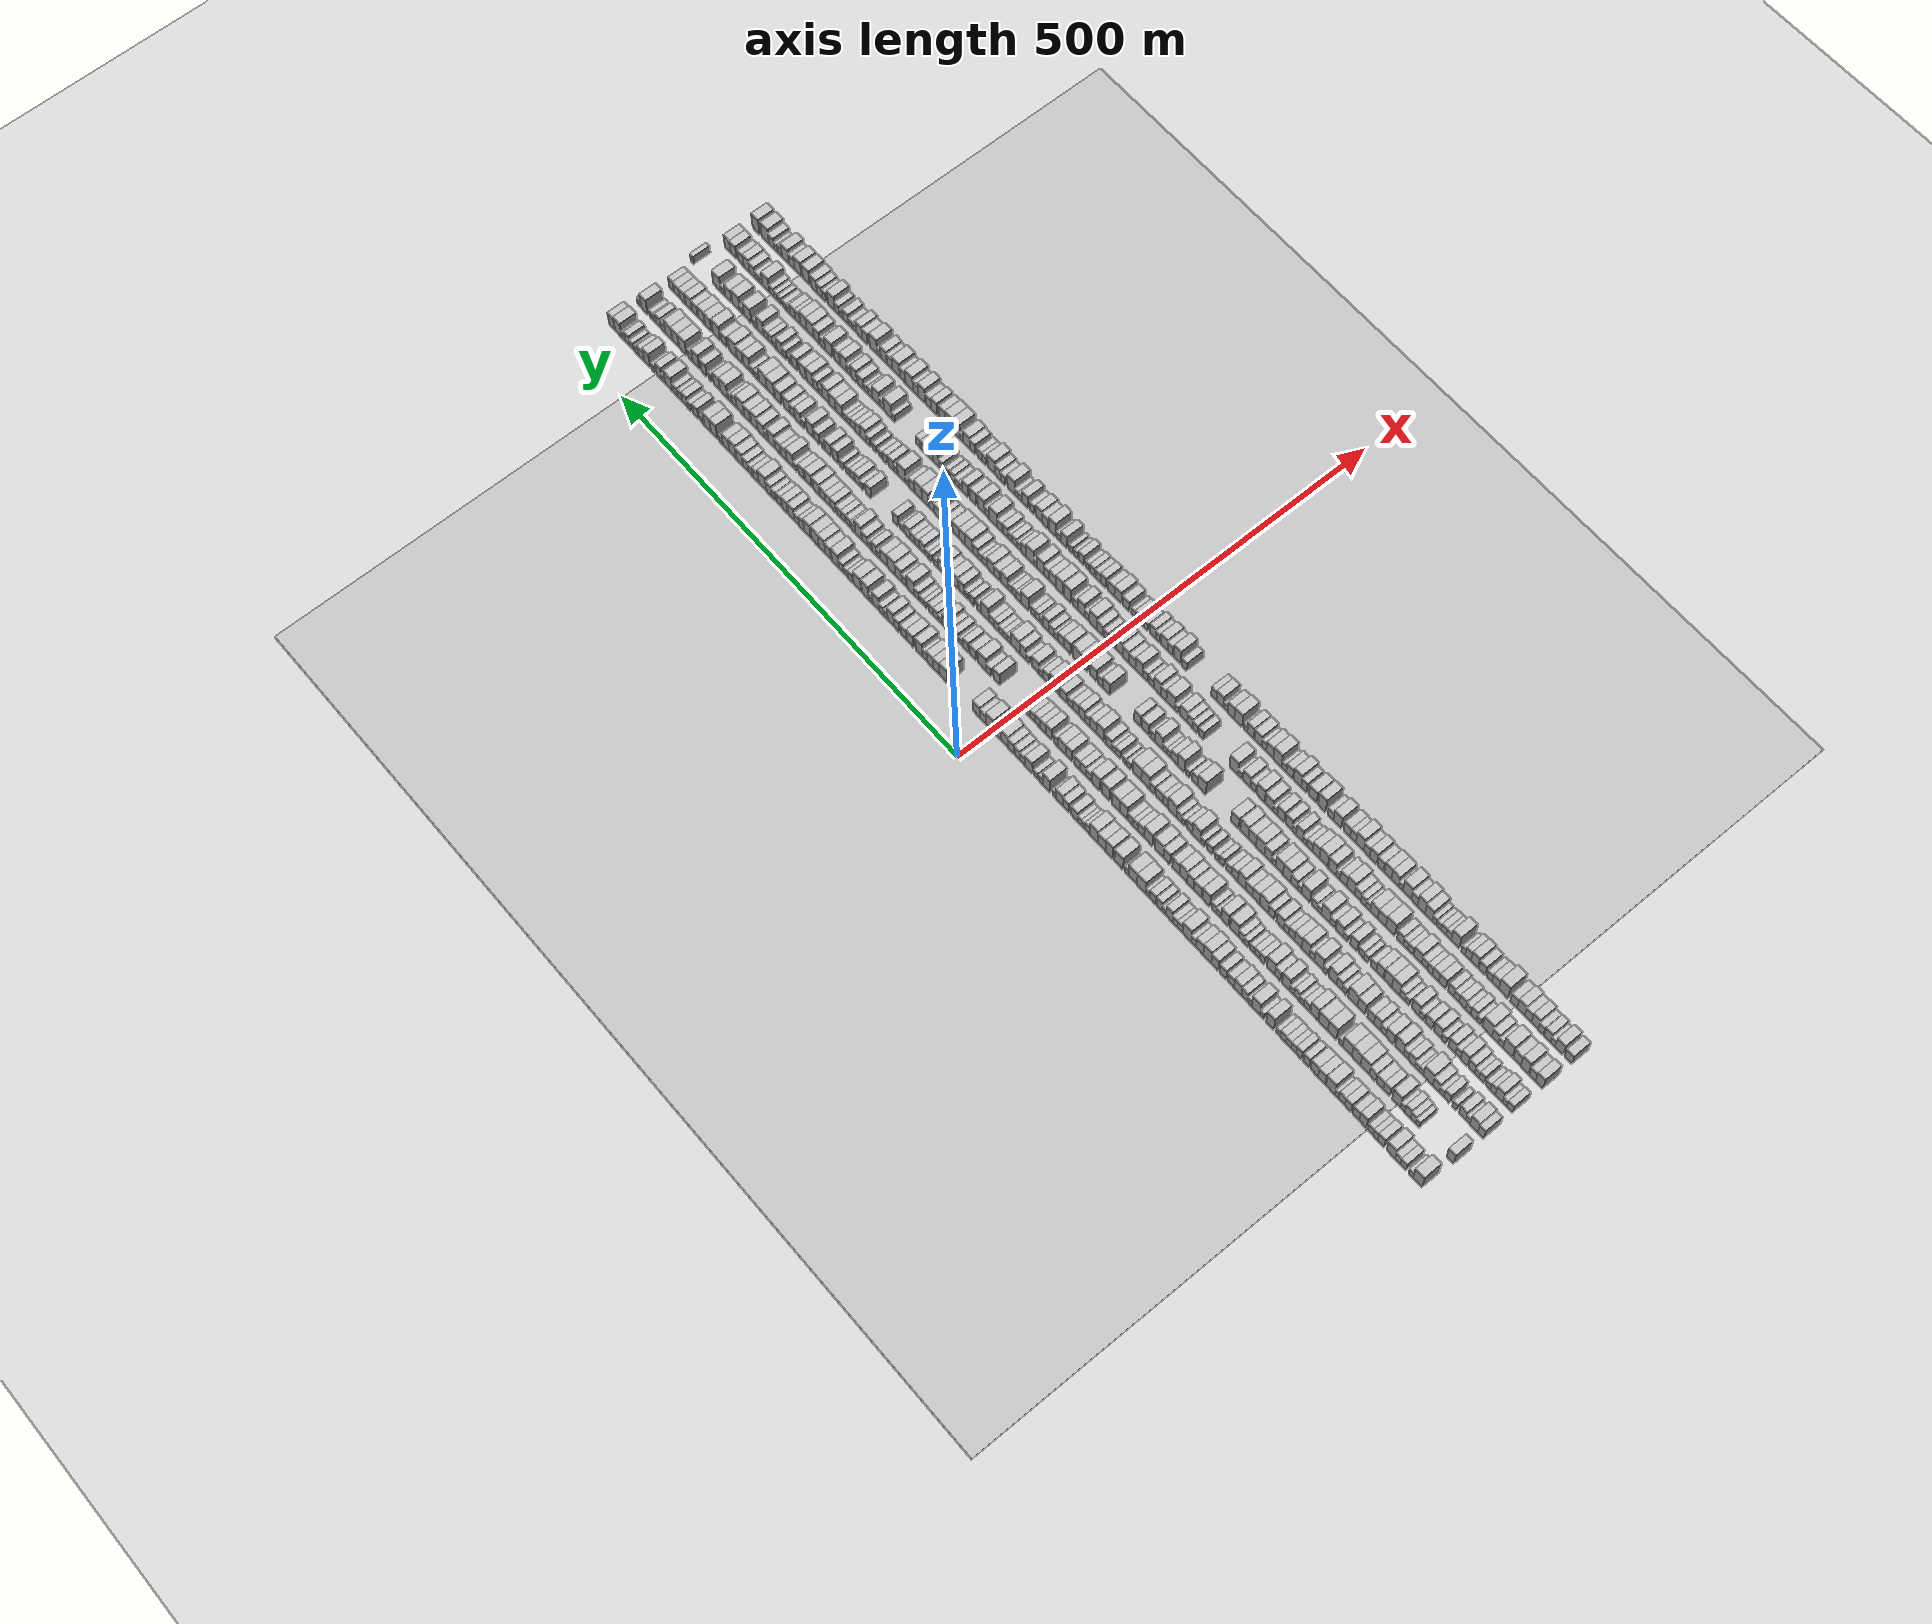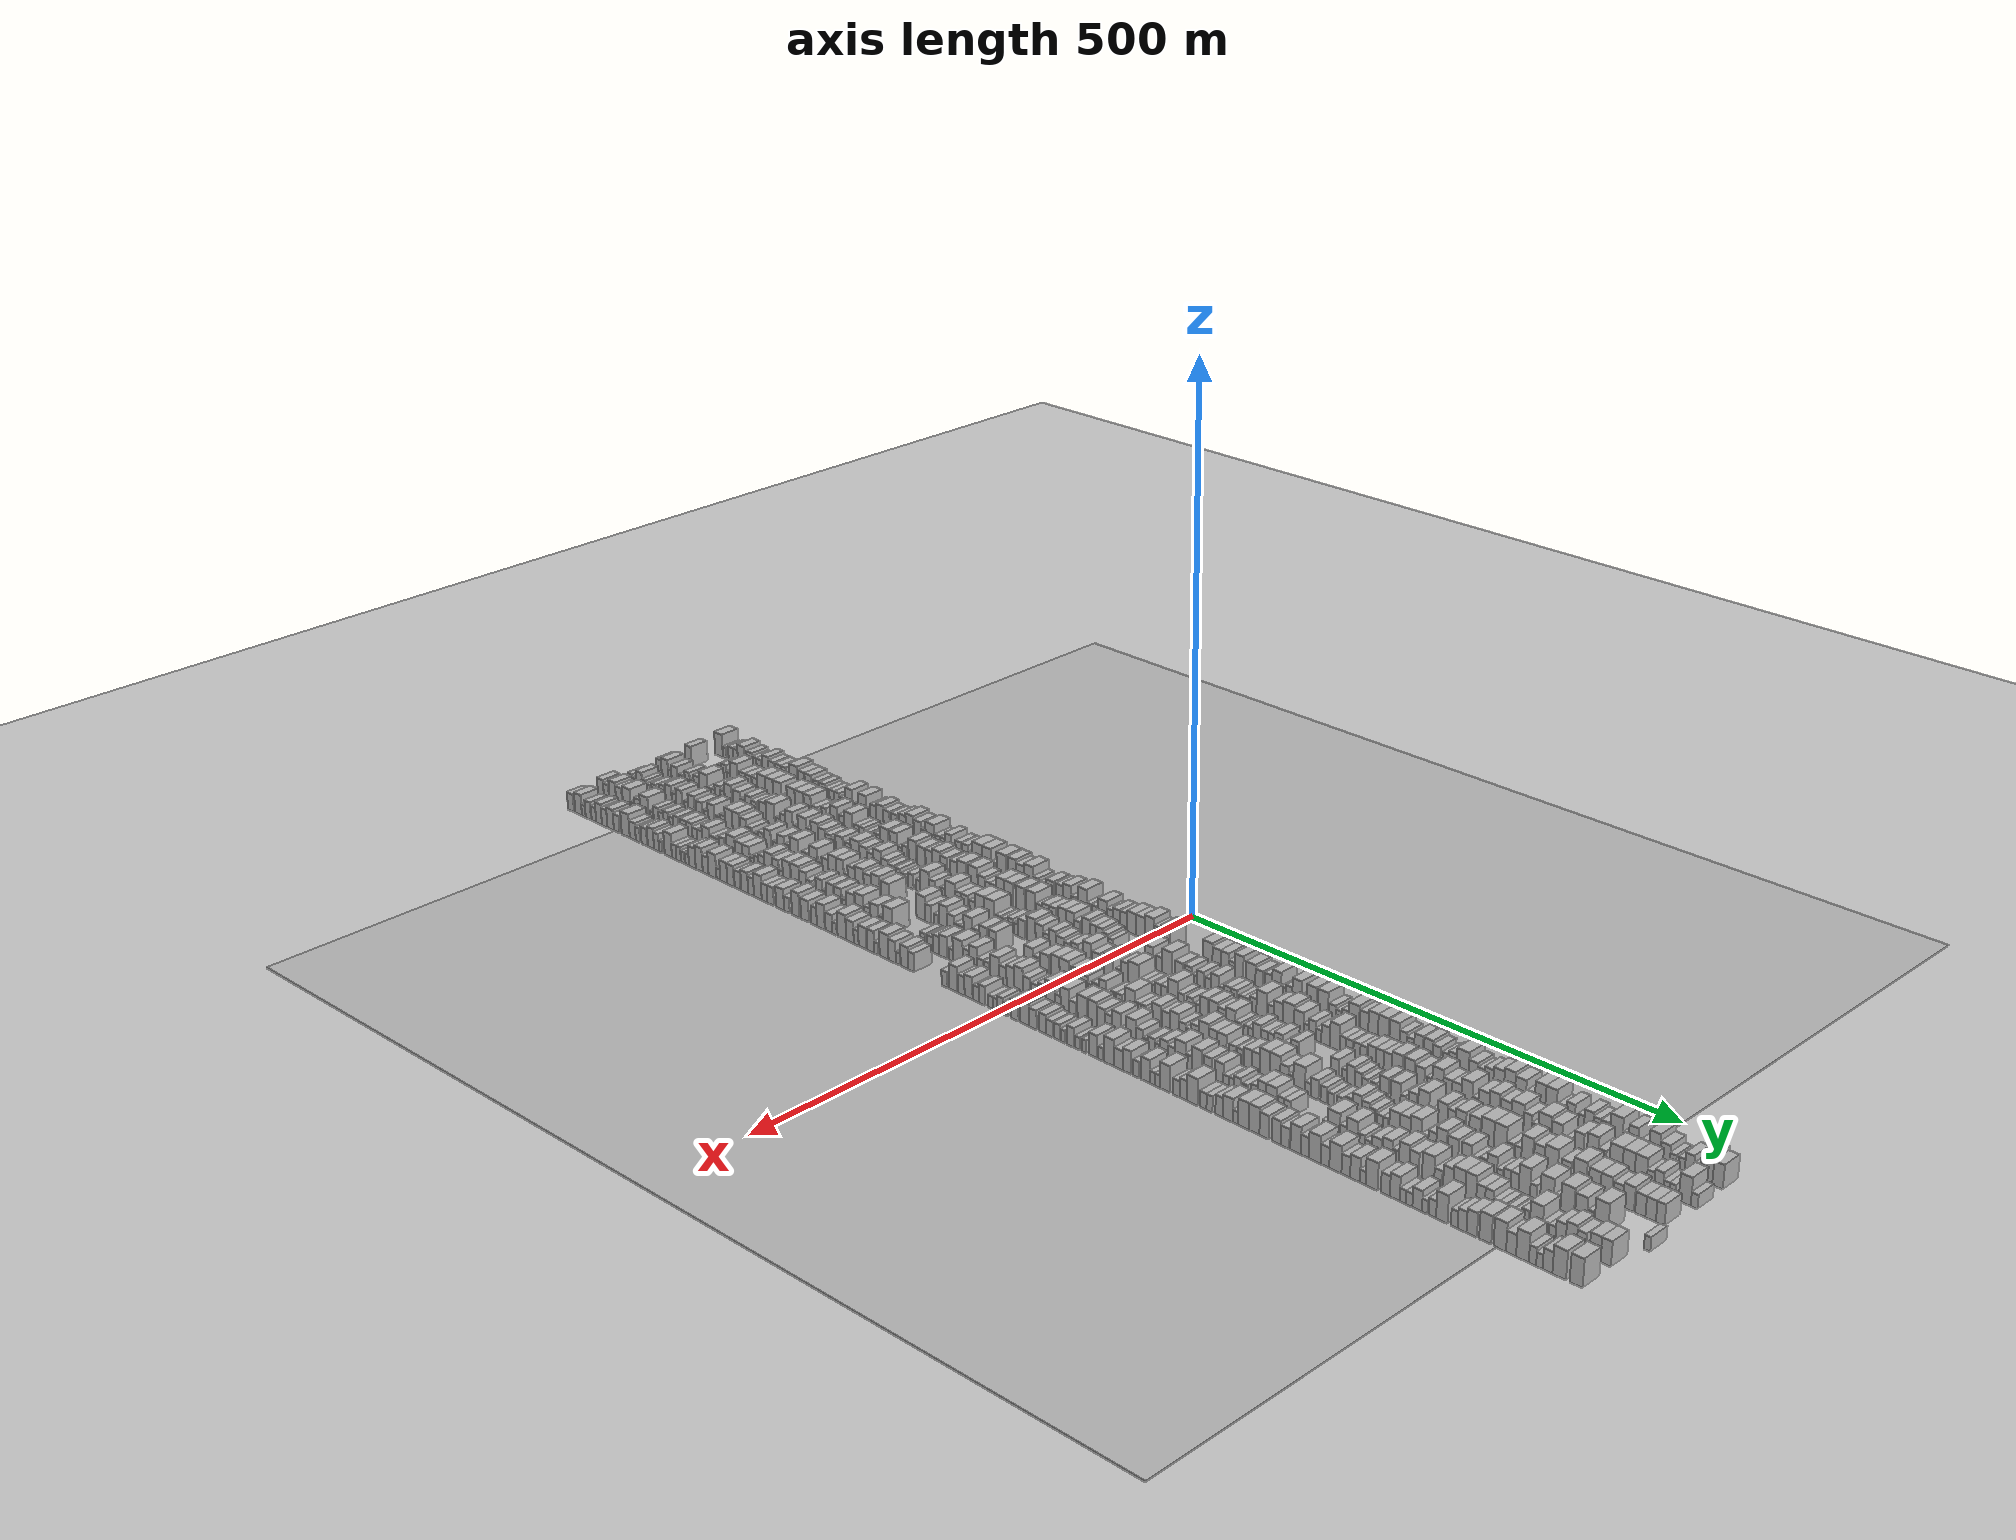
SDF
<?xml version="1.0" encoding="utf-8"?>

<sdf version="1.6">

   <world name="default">

      <gui fullscreen="0">

         <camera name="user_camera">

            <pose>-15 0 4.57585 0 0 0</pose>

            <view_controller>orbit</view_controller>

         </camera>

      </gui>

      <scene>

         <sky>

           <clouds>

             <speed>12</speed>

           </clouds>

         </sky>

         <ambient>0.4 0.4 0.4 1</ambient>

         <background>0.7 0.7 0.7 1</background>

         <shadows>1</shadows>

      </scene>

      <gravity>0 0 -9.8066</gravity>

      <magnetic_field>6e-06 2.3e-05 -4.2e-05</magnetic_field>

      <physics default="0" name="default_physics" type="ode">

         <ode>

            <solver>

               <type>quick</type>

               <iters>10</iters>

               <sor>1.0</sor>

               <use_dynamic_moi_rescaling>0</use_dynamic_moi_rescaling>

            </solver>

            <constraints>

               <cfm>0</cfm>

               <erp>0.2</erp>

               <contact_max_correcting_vel>100</contact_max_correcting_vel>

               <contact_surface_layer>0.001</contact_surface_layer>

            </constraints>

         </ode>

         <max_step_size>0.004</max_step_size>

         <real_time_factor>1</real_time_factor>

         <real_time_update_rate>250</real_time_update_rate>

      </physics>

      <light name="sun" type="directional">

         <cast_shadows>1</cast_shadows>

         <pose>0 0 10 0 0 0</pose>

         <diffuse>0.8 0.8 0.8 1</diffuse>

         <specular>0.2 0.2 0.2 1</specular>

         <attenuation>

            <range>1000</range>

            <constant>0.9</constant>

            <linear>0.01</linear>

            <quadratic>0.001</quadratic>

         </attenuation>

         <direction>-0.5 0.1 -0.9</direction>

      </light>

      <include>

         <name>ground_plane_1</name>

         <uri>model://HANNAS_ground_plane</uri>

         <pose>0 0 0  0 0 0</pose>

      </include>

      <include>

         <name>ground_plane_2</name>

         <uri>model://HANNAS_ground_plane</uri>

         <pose>100 0 0  0 0 0</pose>

      </include>

      <model name="building_1">

         <static>1</static>

         <pose frame="">50.0000 -562.3238 0 0.000000 0.000000 0.000000</pose>

         <link name="link">

            <pose frame="">0 0 12.00 0 0 0</pose>

            <collision name="collision">

               <geometry>

                  <box>

                     <size>20.0000 11.3523 24.0000</size>

                  </box>

               </geometry>

               <max_contacts>10</max_contacts>

               <surface>

                  <contact>

                     <ode/>

                  </contact>

                  <bounce/>

                  <friction>

                     <torsional>

                        <ode/>

                     </torsional>

                     <ode/>

                  </friction>

               </surface>

            </collision>

            <visual name="visual">

               <cast_shadows>0</cast_shadows>

               <geometry>

                  <box>

                     <size>20.0000 11.3523 24.0000</size>

                  </box>

               </geometry>

               <material>

                  <script>

                     <uri>model://HANNAS_wall/materials/scripts</uri>

                     <uri>model://HANNAS_wall/materials/textures</uri>

                     <name>vrc/HANNAS_wall</name>

                  </script>

               </material>

            </visual>

            <self_collide>0</self_collide>

            <enable_wind>0</enable_wind>

            <kinematic>0</kinematic>

         </link>

      </model>

      <model name="building_2">

         <static>1</static>

         <pose frame="">50.0000 -553.8792 0 0.000000 0.000000 0.000000</pose>

         <link name="link">

            <pose frame="">0 0 6.00 0 0 0</pose>

            <collision name="collision">

               <geometry>

                  <box>

                     <size>20.0000 5.5368 12.0000</size>

                  </box>

               </geometry>

               <max_contacts>10</max_contacts>

               <surface>

                  <contact>

                     <ode/>

                  </contact>

                  <bounce/>

                  <friction>

                     <torsional>

                        <ode/>

                     </torsional>

                     <ode/>

                  </friction>

               </surface>

            </collision>

            <visual name="visual">

               <cast_shadows>0</cast_shadows>

               <geometry>

                  <box>

                     <size>20.0000 5.5368 12.0000</size>

                  </box>

               </geometry>

               <material>

                  <script>

                     <uri>model://HANNAS_wall/materials/scripts</uri>

                     <uri>model://HANNAS_wall/materials/textures</uri>

                     <name>vrc/HANNAS_wall</name>

                  </script>

               </material>

            </visual>

            <self_collide>0</self_collide>

            <enable_wind>0</enable_wind>

            <kinematic>0</kinematic>

         </link>

      </model>

      <model name="building_3">

         <static>1</static>

         <pose frame="">50.0000 -544.5007 0 0.000000 0.000000 0.000000</pose>

         <link name="link">

            <pose frame="">0 0 7.50 0 0 0</pose>

            <collision name="collision">

               <geometry>

                  <box>

                     <size>20.0000 7.2203 15.0000</size>

                  </box>

               </geometry>

               <max_contacts>10</max_contacts>

               <surface>

                  <contact>

                     <ode/>

                  </contact>

                  <bounce/>

                  <friction>

                     <torsional>

                        <ode/>

                     </torsional>

                     <ode/>

                  </friction>

               </surface>

            </collision>

            <visual name="visual">

               <cast_shadows>0</cast_shadows>

               <geometry>

                  <box>

                     <size>20.0000 7.2203 15.0000</size>

                  </box>

               </geometry>

               <material>

                  <script>

                     <uri>model://HANNAS_wall/materials/scripts</uri>

                     <uri>model://HANNAS_wall/materials/textures</uri>

                     <name>vrc/HANNAS_wall</name>

                  </script>

               </material>

            </visual>

            <self_collide>0</self_collide>

            <enable_wind>0</enable_wind>

            <kinematic>0</kinematic>

         </link>

      </model>

      <model name="building_4">

         <static>1</static>

         <pose frame="">50.0000 -537.5325 0 0.000000 0.000000 0.000000</pose>

         <link name="link">

            <pose frame="">0 0 7.50 0 0 0</pose>

            <collision name="collision">

               <geometry>

                  <box>

                     <size>20.0000 6.7162 15.0000</size>

                  </box>

               </geometry>

               <max_contacts>10</max_contacts>

               <surface>

                  <contact>

                     <ode/>

                  </contact>

                  <bounce/>

                  <friction>

                     <torsional>

                        <ode/>

                     </torsional>

                     <ode/>

                  </friction>

               </surface>

            </collision>

            <visual name="visual">

               <cast_shadows>0</cast_shadows>

               <geometry>

                  <box>

                     <size>20.0000 6.7162 15.0000</size>

                  </box>

               </geometry>

               <material>

                  <script>

                     <uri>model://HANNAS_wall/materials/scripts</uri>

                     <uri>model://HANNAS_wall/materials/textures</uri>

                     <name>vrc/HANNAS_wall</name>

                  </script>

               </material>

            </visual>

            <self_collide>0</self_collide>

            <enable_wind>0</enable_wind>

            <kinematic>0</kinematic>

         </link>

      </model>

      <model name="building_5">

         <static>1</static>

         <pose frame="">50.0000 -528.9999 0 0.000000 0.000000 0.000000</pose>

         <link name="link">

            <pose frame="">0 0 10.50 0 0 0</pose>

            <collision name="collision">

               <geometry>

                  <box>

                     <size>20.0000 10.3490 21.0000</size>

                  </box>

               </geometry>

               <max_contacts>10</max_contacts>

               <surface>

                  <contact>

                     <ode/>

                  </contact>

                  <bounce/>

                  <friction>

                     <torsional>

                        <ode/>

                     </torsional>

                     <ode/>

                  </friction>

               </surface>

            </collision>

            <visual name="visual">

               <cast_shadows>0</cast_shadows>

               <geometry>

                  <box>

                     <size>20.0000 10.3490 21.0000</size>

                  </box>

               </geometry>

               <material>

                  <script>

                     <uri>model://HANNAS_wall/materials/scripts</uri>

                     <uri>model://HANNAS_wall/materials/textures</uri>

                     <name>vrc/HANNAS_wall</name>

                  </script>

               </material>

            </visual>

            <self_collide>0</self_collide>

            <enable_wind>0</enable_wind>

            <kinematic>0</kinematic>

         </link>

      </model>

      <model name="building_6">

         <static>1</static>

         <pose frame="">50.0000 -516.7189 0 0.000000 0.000000 0.000000</pose>

         <link name="link">

            <pose frame="">0 0 9.00 0 0 0</pose>

            <collision name="collision">

               <geometry>

                  <box>

                     <size>20.0000 8.2130 18.0000</size>

                  </box>

               </geometry>

               <max_contacts>10</max_contacts>

               <surface>

                  <contact>

                     <ode/>

                  </contact>

                  <bounce/>

                  <friction>

                     <torsional>

                        <ode/>

                     </torsional>

                     <ode/>

                  </friction>

               </surface>

            </collision>

            <visual name="visual">

               <cast_shadows>0</cast_shadows>

               <geometry>

                  <box>

                     <size>20.0000 8.2130 18.0000</size>

                  </box>

               </geometry>

               <material>

                  <script>

                     <uri>model://HANNAS_wall/materials/scripts</uri>

                     <uri>model://HANNAS_wall/materials/textures</uri>

                     <name>vrc/HANNAS_wall</name>

                  </script>

               </material>

            </visual>

            <self_collide>0</self_collide>

            <enable_wind>0</enable_wind>

            <kinematic>0</kinematic>

         </link>

      </model>

      <model name="building_7">

         <static>1</static>

         <pose frame="">50.0000 -509.5909 0 0.000000 0.000000 0.000000</pose>

         <link name="link">

            <pose frame="">0 0 7.50 0 0 0</pose>

            <collision name="collision">

               <geometry>

                  <box>

                     <size>20.0000 6.0429 15.0000</size>

                  </box>

               </geometry>

               <max_contacts>10</max_contacts>

               <surface>

                  <contact>

                     <ode/>

                  </contact>

                  <bounce/>

                  <friction>

                     <torsional>

                        <ode/>

                     </torsional>

                     <ode/>

                  </friction>

               </surface>

            </collision>

            <visual name="visual">

               <cast_shadows>0</cast_shadows>

               <geometry>

                  <box>

                     <size>20.0000 6.0429 15.0000</size>

                  </box>

               </geometry>

               <material>

                  <script>

                     <uri>model://HANNAS_wall/materials/scripts</uri>

                     <uri>model://HANNAS_wall/materials/textures</uri>

                     <name>vrc/HANNAS_wall</name>

                  </script>

               </material>

            </visual>

            <self_collide>0</self_collide>

            <enable_wind>0</enable_wind>

            <kinematic>0</kinematic>

         </link>

      </model>

      <model name="building_8">

         <static>1</static>

         <pose frame="">50.0000 -503.3961 0 0.000000 0.000000 0.000000</pose>

         <link name="link">

            <pose frame="">0 0 7.50 0 0 0</pose>

            <collision name="collision">

               <geometry>

                  <box>

                     <size>20.0000 6.3468 15.0000</size>

                  </box>

               </geometry>

               <max_contacts>10</max_contacts>

               <surface>

                  <contact>

                     <ode/>

                  </contact>

                  <bounce/>

                  <friction>

                     <torsional>

                        <ode/>

                     </torsional>

                     <ode/>

                  </friction>

               </surface>

            </collision>

            <visual name="visual">

               <cast_shadows>0</cast_shadows>

               <geometry>

                  <box>

                     <size>20.0000 6.3468 15.0000</size>

                  </box>

               </geometry>

               <material>

                  <script>

                     <uri>model://HANNAS_wall/materials/scripts</uri>

                     <uri>model://HANNAS_wall/materials/textures</uri>

                     <name>vrc/HANNAS_wall</name>

                  </script>

               </material>

            </visual>

            <self_collide>0</self_collide>

            <enable_wind>0</enable_wind>

            <kinematic>0</kinematic>

         </link>

      </model>

      <model name="building_9">

         <static>1</static>

         <pose frame="">50.0000 -493.7386 0 0.000000 0.000000 0.000000</pose>

         <link name="link">

            <pose frame="">0 0 10.50 0 0 0</pose>

            <collision name="collision">

               <geometry>

                  <box>

                     <size>20.0000 8.9681 21.0000</size>

                  </box>

               </geometry>

               <max_contacts>10</max_contacts>

               <surface>

                  <contact>

                     <ode/>

                  </contact>

                  <bounce/>

                  <friction>

                     <torsional>

                        <ode/>

                     </torsional>

                     <ode/>

                  </friction>

               </surface>

            </collision>

            <visual name="visual">

               <cast_shadows>0</cast_shadows>

               <geometry>

                  <box>

                     <size>20.0000 8.9681 21.0000</size>

                  </box>

               </geometry>

               <material>

                  <script>

                     <uri>model://HANNAS_wall/materials/scripts</uri>

                     <uri>model://HANNAS_wall/materials/textures</uri>

                     <name>vrc/HANNAS_wall</name>

                  </script>

               </material>

            </visual>

            <self_collide>0</self_collide>

            <enable_wind>0</enable_wind>

            <kinematic>0</kinematic>

         </link>

      </model>

      <model name="building_10">

         <static>1</static>

         <pose frame="">50.0000 -485.2229 0 0.000000 0.000000 0.000000</pose>

         <link name="link">

            <pose frame="">0 0 9.00 0 0 0</pose>

            <collision name="collision">

               <geometry>

                  <box>

                     <size>20.0000 8.0634 18.0000</size>

                  </box>

               </geometry>

               <max_contacts>10</max_contacts>

               <surface>

                  <contact>

                     <ode/>

                  </contact>

                  <bounce/>

                  <friction>

                     <torsional>

                        <ode/>

                     </torsional>

                     <ode/>

                  </friction>

               </surface>

            </collision>

            <visual name="visual">

               <cast_shadows>0</cast_shadows>

               <geometry>

                  <box>

                     <size>20.0000 8.0634 18.0000</size>

                  </box>

               </geometry>

               <material>

                  <script>

                     <uri>model://HANNAS_wall/materials/scripts</uri>

                     <uri>model://HANNAS_wall/materials/textures</uri>

                     <name>vrc/HANNAS_wall</name>

                  </script>

               </material>

            </visual>

            <self_collide>0</self_collide>

            <enable_wind>0</enable_wind>

            <kinematic>0</kinematic>

         </link>

      </model>

      <model name="building_11">

         <static>1</static>

         <pose frame="">50.0000 -475.1178 0 0.000000 0.000000 0.000000</pose>

         <link name="link">

            <pose frame="">0 0 9.00 0 0 0</pose>

            <collision name="collision">

               <geometry>

                  <box>

                     <size>20.0000 8.1467 18.0000</size>

                  </box>

               </geometry>

               <max_contacts>10</max_contacts>

               <surface>

                  <contact>

                     <ode/>

                  </contact>

                  <bounce/>

                  <friction>

                     <torsional>

                        <ode/>

                     </torsional>

                     <ode/>

                  </friction>

               </surface>

            </collision>

            <visual name="visual">

               <cast_shadows>0</cast_shadows>

               <geometry>

                  <box>

                     <size>20.0000 8.1467 18.0000</size>

                  </box>

               </geometry>

               <material>

                  <script>

                     <uri>model://HANNAS_wall/materials/scripts</uri>

                     <uri>model://HANNAS_wall/materials/textures</uri>

                     <name>vrc/HANNAS_wall</name>

                  </script>

               </material>

            </visual>

            <self_collide>0</self_collide>

            <enable_wind>0</enable_wind>

            <kinematic>0</kinematic>

         </link>

      </model>

      <model name="building_12">

         <static>1</static>

         <pose frame="">50.0000 -467.2561 0 0.000000 0.000000 0.000000</pose>

         <link name="link">

            <pose frame="">0 0 9.00 0 0 0</pose>

            <collision name="collision">

               <geometry>

                  <box>

                     <size>20.0000 7.5766 18.0000</size>

                  </box>

               </geometry>

               <max_contacts>10</max_contacts>

               <surface>

                  <contact>

                     <ode/>

                  </contact>

                  <bounce/>

                  <friction>

                     <torsional>

                        <ode/>

                     </torsional>

                     <ode/>

                  </friction>

               </surface>

            </collision>

            <visual name="visual">

               <cast_shadows>0</cast_shadows>

               <geometry>

                  <box>

                     <size>20.0000 7.5766 18.0000</size>

                  </box>

               </geometry>

               <material>

                  <script>

                     <uri>model://HANNAS_wall/materials/scripts</uri>

                     <uri>model://HANNAS_wall/materials/textures</uri>

                     <name>vrc/HANNAS_wall</name>

                  </script>

               </material>

            </visual>

            <self_collide>0</self_collide>

            <enable_wind>0</enable_wind>

            <kinematic>0</kinematic>

         </link>

      </model>

      <model name="building_13">

         <static>1</static>

         <pose frame="">50.0000 -461.0217 0 0.000000 0.000000 0.000000</pose>

         <link name="link">

            <pose frame="">0 0 6.00 0 0 0</pose>

            <collision name="collision">

               <geometry>

                  <box>

                     <size>20.0000 4.8921 12.0000</size>

                  </box>

               </geometry>

               <max_contacts>10</max_contacts>

               <surface>

                  <contact>

                     <ode/>

                  </contact>

                  <bounce/>

                  <friction>

                     <torsional>

                        <ode/>

                     </torsional>

                     <ode/>

                  </friction>

               </surface>

            </collision>

            <visual name="visual">

               <cast_shadows>0</cast_shadows>

               <geometry>

                  <box>

                     <size>20.0000 4.8921 12.0000</size>

                  </box>

               </geometry>

               <material>

                  <script>

                     <uri>model://HANNAS_wall/materials/scripts</uri>

                     <uri>model://HANNAS_wall/materials/textures</uri>

                     <name>vrc/HANNAS_wall</name>

                  </script>

               </material>

            </visual>

            <self_collide>0</self_collide>

            <enable_wind>0</enable_wind>

            <kinematic>0</kinematic>

         </link>

      </model>

      <model name="building_14">

         <static>1</static>

         <pose frame="">50.0000 -452.9068 0 0.000000 0.000000 0.000000</pose>

         <link name="link">

            <pose frame="">0 0 12.00 0 0 0</pose>

            <collision name="collision">

               <geometry>

                  <box>

                     <size>20.0000 11.3376 24.0000</size>

                  </box>

               </geometry>

               <max_contacts>10</max_contacts>

               <surface>

                  <contact>

                     <ode/>

                  </contact>

                  <bounce/>

                  <friction>

                     <torsional>

                        <ode/>

                     </torsional>

                     <ode/>

                  </friction>

               </surface>

            </collision>

            <visual name="visual">

               <cast_shadows>0</cast_shadows>

               <geometry>

                  <box>

                     <size>20.0000 11.3376 24.0000</size>

                  </box>

               </geometry>

               <material>

                  <script>

                     <uri>model://HANNAS_wall/materials/scripts</uri>

                     <uri>model://HANNAS_wall/materials/textures</uri>

                     <name>vrc/HANNAS_wall</name>

                  </script>

               </material>

            </visual>

            <self_collide>0</self_collide>

            <enable_wind>0</enable_wind>

            <kinematic>0</kinematic>

         </link>

      </model>

      <model name="building_15">

         <static>1</static>

         <pose frame="">50.0000 -441.6312 0 0.000000 0.000000 0.000000</pose>

         <link name="link">

            <pose frame="">0 0 10.50 0 0 0</pose>

            <collision name="collision">

               <geometry>

                  <box>

                     <size>20.0000 9.2136 21.0000</size>

                  </box>

               </geometry>

               <max_contacts>10</max_contacts>

               <surface>

                  <contact>

                     <ode/>

                  </contact>

                  <bounce/>

                  <friction>

                     <torsional>

                        <ode/>

                     </torsional>

                     <ode/>

                  </friction>

               </surface>

            </collision>

            <visual name="visual">

               <cast_shadows>0</cast_shadows>

               <geometry>

                  <box>

                     <size>20.0000 9.2136 21.0000</size>

                  </box>

               </geometry>

               <material>

                  <script>

                     <uri>model://HANNAS_wall/materials/scripts</uri>

                     <uri>model://HANNAS_wall/materials/textures</uri>

                     <name>vrc/HANNAS_wall</name>

                  </script>

               </material>

            </visual>

            <self_collide>0</self_collide>

            <enable_wind>0</enable_wind>

            <kinematic>0</kinematic>

         </link>

      </model>

      <model name="building_16">

         <static>1</static>

         <pose frame="">50.0000 -432.2996 0 0.000000 0.000000 0.000000</pose>

         <link name="link">

            <pose frame="">0 0 10.50 0 0 0</pose>

            <collision name="collision">

               <geometry>

                  <box>

                     <size>20.0000 9.4496 21.0000</size>

                  </box>

               </geometry>

               <max_contacts>10</max_contacts>

               <surface>

                  <contact>

                     <ode/>

                  </contact>

                  <bounce/>

                  <friction>

                     <torsional>

                        <ode/>

                     </torsional>

                     <ode/>

                  </friction>

               </surface>

            </collision>

            <visual name="visual">

               <cast_shadows>0</cast_shadows>

               <geometry>

                  <box>

                     <size>20.0000 9.4496 21.0000</size>

                  </box>

               </geometry>

               <material>

                  <script>

                     <uri>model://HANNAS_wall/materials/scripts</uri>

                     <uri>model://HANNAS_wall/materials/textures</uri>

                     <name>vrc/HANNAS_wall</name>

                  </script>

               </material>

            </visual>

            <self_collide>0</self_collide>

            <enable_wind>0</enable_wind>

            <kinematic>0</kinematic>

         </link>

      </model>

      <model name="building_17">

         <static>1</static>

         <pose frame="">50.0000 -421.8844 0 0.000000 0.000000 0.000000</pose>

         <link name="link">

            <pose frame="">0 0 9.00 0 0 0</pose>

            <collision name="collision">

               <geometry>

                  <box>

                     <size>20.0000 7.3808 18.0000</size>

                  </box>

               </geometry>

               <max_contacts>10</max_contacts>

               <surface>

                  <contact>

                     <ode/>

                  </contact>

                  <bounce/>

                  <friction>

                     <torsional>

                        <ode/>

                     </torsional>

                     <ode/>

                  </friction>

               </surface>

            </collision>

            <visual name="visual">

               <cast_shadows>0</cast_shadows>

               <geometry>

                  <box>

                     <size>20.0000 7.3808 18.0000</size>

                  </box>

               </geometry>

               <material>

                  <script>

                     <uri>model://HANNAS_wall/materials/scripts</uri>

                     <uri>model://HANNAS_wall/materials/textures</uri>

                     <name>vrc/HANNAS_wall</name>

                  </script>

               </material>

            </visual>

            <self_collide>0</self_collide>

            <enable_wind>0</enable_wind>

            <kinematic>0</kinematic>

         </link>

      </model>

      <model name="building_18">

         <static>1</static>

         <pose frame="">50.0000 -412.5191 0 0.000000 0.000000 0.000000</pose>

         <link name="link">

            <pose frame="">0 0 9.00 0 0 0</pose>

            <collision name="collision">

               <geometry>

                  <box>

                     <size>20.0000 7.3499 18.0000</size>

                  </box>

               </geometry>

               <max_contacts>10</max_contacts>

               <surface>

                  <contact>

                     <ode/>

                  </contact>

                  <bounce/>

                  <friction>

                     <torsional>

                        <ode/>

                     </torsional>

                     <ode/>

                  </friction>

               </surface>

            </collision>

            <visual name="visual">

               <cast_shadows>0</cast_shadows>

               <geometry>

                  <box>

                     <size>20.0000 7.3499 18.0000</size>

                  </box>

               </geometry>

               <material>

                  <script>

                     <uri>model://HANNAS_wall/materials/scripts</uri>

                     <uri>model://HANNAS_wall/materials/textures</uri>

                     <name>vrc/HANNAS_wall</name>

                  </script>

               </material>

            </visual>

            <self_collide>0</self_collide>

            <enable_wind>0</enable_wind>

            <kinematic>0</kinematic>

         </link>

      </model>

      <model name="building_19">

         <static>1</static>

         <pose frame="">50.0000 -405.6760 0 0.000000 0.000000 0.000000</pose>

         <link name="link">

            <pose frame="">0 0 7.50 0 0 0</pose>

            <collision name="collision">

               <geometry>

                  <box>

                     <size>20.0000 6.3364 15.0000</size>

                  </box>

               </geometry>

               <max_contacts>10</max_contacts>

               <surface>

                  <contact>

                     <ode/>

                  </contact>

                  <bounce/>

                  <friction>

                     <torsional>

                        <ode/>

                     </torsional>

                     <ode/>

                  </friction>

               </surface>

            </collision>

            <visual name="visual">

               <cast_shadows>0</cast_shadows>

               <geometry>

                  <box>

                     <size>20.0000 6.3364 15.0000</size>

                  </box>

               </geometry>

               <material>

                  <script>

                     <uri>model://HANNAS_wall/materials/scripts</uri>

                     <uri>model://HANNAS_wall/materials/textures</uri>

                     <name>vrc/HANNAS_wall</name>

                  </script>

               </material>

            </visual>

            <self_collide>0</self_collide>

            <enable_wind>0</enable_wind>

            <kinematic>0</kinematic>

         </link>

      </model>

      <model name="building_20">

         <static>1</static>

         <pose frame="">50.0000 -399.1858 0 0.000000 0.000000 0.000000</pose>

         <link name="link">

            <pose frame="">0 0 7.50 0 0 0</pose>

            <collision name="collision">

               <geometry>

                  <box>

                     <size>20.0000 6.6439 15.0000</size>

                  </box>

               </geometry>

               <max_contacts>10</max_contacts>

               <surface>

                  <contact>

                     <ode/>

                  </contact>

                  <bounce/>

                  <friction>

                     <torsional>

                        <ode/>

                     </torsional>

                     <ode/>

                  </friction>

               </surface>

            </collision>

            <visual name="visual">

               <cast_shadows>0</cast_shadows>

               <geometry>

                  <box>

                     <size>20.0000 6.6439 15.0000</size>

                  </box>

               </geometry>

               <material>

                  <script>

                     <uri>model://HANNAS_wall/materials/scripts</uri>

                     <uri>model://HANNAS_wall/materials/textures</uri>

                     <name>vrc/HANNAS_wall</name>

                  </script>

               </material>

            </visual>

            <self_collide>0</self_collide>

            <enable_wind>0</enable_wind>

            <kinematic>0</kinematic>

         </link>

      </model>

      <model name="building_21">

         <static>1</static>

         <pose frame="">50.0000 -392.1210 0 0.000000 0.000000 0.000000</pose>

         <link name="link">

            <pose frame="">0 0 7.50 0 0 0</pose>

            <collision name="collision">

               <geometry>

                  <box>

                     <size>20.0000 7.4857 15.0000</size>

                  </box>

               </geometry>

               <max_contacts>10</max_contacts>

               <surface>

                  <contact>

                     <ode/>

                  </contact>

                  <bounce/>

                  <friction>

                     <torsional>

                        <ode/>

                     </torsional>

                     <ode/>

                  </friction>

               </surface>

            </collision>

            <visual name="visual">

               <cast_shadows>0</cast_shadows>

               <geometry>

                  <box>

                     <size>20.0000 7.4857 15.0000</size>

                  </box>

               </geometry>

               <material>

                  <script>

                     <uri>model://HANNAS_wall/materials/scripts</uri>

                     <uri>model://HANNAS_wall/materials/textures</uri>

                     <name>vrc/HANNAS_wall</name>

                  </script>

               </material>

            </visual>

            <self_collide>0</self_collide>

            <enable_wind>0</enable_wind>

            <kinematic>0</kinematic>

         </link>

      </model>

      <model name="building_22">

         <static>1</static>

         <pose frame="">50.0000 -385.8359 0 0.000000 0.000000 0.000000</pose>

         <link name="link">

            <pose frame="">0 0 6.00 0 0 0</pose>

            <collision name="collision">

               <geometry>

                  <box>

                     <size>20.0000 5.0846 12.0000</size>

                  </box>

               </geometry>

               <max_contacts>10</max_contacts>

               <surface>

                  <contact>

                     <ode/>

                  </contact>

                  <bounce/>

                  <friction>

                     <torsional>

                        <ode/>

                     </torsional>

                     <ode/>

                  </friction>

               </surface>

            </collision>

            <visual name="visual">

               <cast_shadows>0</cast_shadows>

               <geometry>

                  <box>

                     <size>20.0000 5.0846 12.0000</size>

                  </box>

               </geometry>

               <material>

                  <script>

                     <uri>model://HANNAS_wall/materials/scripts</uri>

                     <uri>model://HANNAS_wall/materials/textures</uri>

                     <name>vrc/HANNAS_wall</name>

                  </script>

               </material>

            </visual>

            <self_collide>0</self_collide>

            <enable_wind>0</enable_wind>

            <kinematic>0</kinematic>

         </link>

      </model>

      <model name="building_23">

         <static>1</static>

         <pose frame="">50.0000 -375.3861 0 0.000000 0.000000 0.000000</pose>

         <link name="link">

            <pose frame="">0 0 12.00 0 0 0</pose>

            <collision name="collision">

               <geometry>

                  <box>

                     <size>20.0000 9.8149 24.0000</size>

                  </box>

               </geometry>

               <max_contacts>10</max_contacts>

               <surface>

                  <contact>

                     <ode/>

                  </contact>

                  <bounce/>

                  <friction>

                     <torsional>

                        <ode/>

                     </torsional>

                     <ode/>

                  </friction>

               </surface>

            </collision>

            <visual name="visual">

               <cast_shadows>0</cast_shadows>

               <geometry>

                  <box>

                     <size>20.0000 9.8149 24.0000</size>

                  </box>

               </geometry>

               <material>

                  <script>

                     <uri>model://HANNAS_wall/materials/scripts</uri>

                     <uri>model://HANNAS_wall/materials/textures</uri>

                     <name>vrc/HANNAS_wall</name>

                  </script>

               </material>

            </visual>

            <self_collide>0</self_collide>

            <enable_wind>0</enable_wind>

            <kinematic>0</kinematic>

         </link>

      </model>

      <model name="building_24">

         <static>1</static>

         <pose frame="">50.0000 -364.8894 0 0.000000 0.000000 0.000000</pose>

         <link name="link">

            <pose frame="">0 0 6.00 0 0 0</pose>

            <collision name="collision">

               <geometry>

                  <box>

                     <size>20.0000 5.1785 12.0000</size>

                  </box>

               </geometry>

               <max_contacts>10</max_contacts>

               <surface>

                  <contact>

                     <ode/>

                  </contact>

                  <bounce/>

                  <friction>

                     <torsional>

                        <ode/>

                     </torsional>

                     <ode/>

                  </friction>

               </surface>

            </collision>

            <visual name="visual">

               <cast_shadows>0</cast_shadows>

               <geometry>

                  <box>

                     <size>20.0000 5.1785 12.0000</size>

                  </box>

               </geometry>

               <material>

                  <script>

                     <uri>model://HANNAS_wall/materials/scripts</uri>

                     <uri>model://HANNAS_wall/materials/textures</uri>

                     <name>vrc/HANNAS_wall</name>

                  </script>

               </material>

            </visual>

            <self_collide>0</self_collide>

            <enable_wind>0</enable_wind>

            <kinematic>0</kinematic>

         </link>

      </model>

      <model name="building_25">

         <static>1</static>

         <pose frame="">50.0000 -356.8521 0 0.000000 0.000000 0.000000</pose>

         <link name="link">

            <pose frame="">0 0 12.00 0 0 0</pose>

            <collision name="collision">

               <geometry>

                  <box>

                     <size>20.0000 10.8959 24.0000</size>

                  </box>

               </geometry>

               <max_contacts>10</max_contacts>

               <surface>

                  <contact>

                     <ode/>

                  </contact>

                  <bounce/>

                  <friction>

                     <torsional>

                        <ode/>

                     </torsional>

                     <ode/>

                  </friction>

               </surface>

            </collision>

            <visual name="visual">

               <cast_shadows>0</cast_shadows>

               <geometry>

                  <box>

                     <size>20.0000 10.8959 24.0000</size>

                  </box>

               </geometry>

               <material>

                  <script>

                     <uri>model://HANNAS_wall/materials/scripts</uri>

                     <uri>model://HANNAS_wall/materials/textures</uri>

                     <name>vrc/HANNAS_wall</name>

                  </script>

               </material>

            </visual>

            <self_collide>0</self_collide>

            <enable_wind>0</enable_wind>

            <kinematic>0</kinematic>

         </link>

      </model>

      <model name="building_26">

         <static>1</static>

         <pose frame="">50.0000 -348.7964 0 0.000000 0.000000 0.000000</pose>

         <link name="link">

            <pose frame="">0 0 6.00 0 0 0</pose>

            <collision name="collision">

               <geometry>

                  <box>

                     <size>20.0000 5.2155 12.0000</size>

                  </box>

               </geometry>

               <max_contacts>10</max_contacts>

               <surface>

                  <contact>

                     <ode/>

                  </contact>

                  <bounce/>

                  <friction>

                     <torsional>

                        <ode/>

                     </torsional>

                     <ode/>

                  </friction>

               </surface>

            </collision>

            <visual name="visual">

               <cast_shadows>0</cast_shadows>

               <geometry>

                  <box>

                     <size>20.0000 5.2155 12.0000</size>

                  </box>

               </geometry>

               <material>

                  <script>

                     <uri>model://HANNAS_wall/materials/scripts</uri>

                     <uri>model://HANNAS_wall/materials/textures</uri>

                     <name>vrc/HANNAS_wall</name>

                  </script>

               </material>

            </visual>

            <self_collide>0</self_collide>

            <enable_wind>0</enable_wind>

            <kinematic>0</kinematic>

         </link>

      </model>

      <model name="building_27">

         <static>1</static>

         <pose frame="">50.0000 -342.2135 0 0.000000 0.000000 0.000000</pose>

         <link name="link">

            <pose frame="">0 0 9.00 0 0 0</pose>

            <collision name="collision">

               <geometry>

                  <box>

                     <size>20.0000 7.9502 18.0000</size>

                  </box>

               </geometry>

               <max_contacts>10</max_contacts>

               <surface>

                  <contact>

                     <ode/>

                  </contact>

                  <bounce/>

                  <friction>

                     <torsional>

                        <ode/>

                     </torsional>

                     <ode/>

                  </friction>

               </surface>

            </collision>

            <visual name="visual">

               <cast_shadows>0</cast_shadows>

               <geometry>

                  <box>

                     <size>20.0000 7.9502 18.0000</size>

                  </box>

               </geometry>

               <material>

                  <script>

                     <uri>model://HANNAS_wall/materials/scripts</uri>

                     <uri>model://HANNAS_wall/materials/textures</uri>

                     <name>vrc/HANNAS_wall</name>

                  </script>

               </material>

            </visual>

            <self_collide>0</self_collide>

            <enable_wind>0</enable_wind>

            <kinematic>0</kinematic>

         </link>

      </model>

      <model name="building_28">

         <static>1</static>

         <pose frame="">50.0000 -333.3798 0 0.000000 0.000000 0.000000</pose>

         <link name="link">

            <pose frame="">0 0 10.50 0 0 0</pose>

            <collision name="collision">

               <geometry>

                  <box>

                     <size>20.0000 9.7173 21.0000</size>

                  </box>

               </geometry>

               <max_contacts>10</max_contacts>

               <surface>

                  <contact>

                     <ode/>

                  </contact>

                  <bounce/>

                  <friction>

                     <torsional>

                        <ode/>

                     </torsional>

                     <ode/>

                  </friction>

               </surface>

            </collision>

            <visual name="visual">

               <cast_shadows>0</cast_shadows>

               <geometry>

                  <box>

                     <size>20.0000 9.7173 21.0000</size>

                  </box>

               </geometry>

               <material>

                  <script>

                     <uri>model://HANNAS_wall/materials/scripts</uri>

                     <uri>model://HANNAS_wall/materials/textures</uri>

                     <name>vrc/HANNAS_wall</name>

                  </script>

               </material>

            </visual>

            <self_collide>0</self_collide>

            <enable_wind>0</enable_wind>

            <kinematic>0</kinematic>

         </link>

      </model>

      <model name="building_29">

         <static>1</static>

         <pose frame="">50.0000 -324.3185 0 0.000000 0.000000 0.000000</pose>

         <link name="link">

            <pose frame="">0 0 9.00 0 0 0</pose>

            <collision name="collision">

               <geometry>

                  <box>

                     <size>20.0000 8.4054 18.0000</size>

                  </box>

               </geometry>

               <max_contacts>10</max_contacts>

               <surface>

                  <contact>

                     <ode/>

                  </contact>

                  <bounce/>

                  <friction>

                     <torsional>

                        <ode/>

                     </torsional>

                     <ode/>

                  </friction>

               </surface>

            </collision>

            <visual name="visual">

               <cast_shadows>0</cast_shadows>

               <geometry>

                  <box>

                     <size>20.0000 8.4054 18.0000</size>

                  </box>

               </geometry>

               <material>

                  <script>

                     <uri>model://HANNAS_wall/materials/scripts</uri>

                     <uri>model://HANNAS_wall/materials/textures</uri>

                     <name>vrc/HANNAS_wall</name>

                  </script>

               </material>

            </visual>

            <self_collide>0</self_collide>

            <enable_wind>0</enable_wind>

            <kinematic>0</kinematic>

         </link>

      </model>

      <model name="building_30">

         <static>1</static>

         <pose frame="">50.0000 -313.9648 0 0.000000 0.000000 0.000000</pose>

         <link name="link">

            <pose frame="">0 0 9.00 0 0 0</pose>

            <collision name="collision">

               <geometry>

                  <box>

                     <size>20.0000 8.3019 18.0000</size>

                  </box>

               </geometry>

               <max_contacts>10</max_contacts>

               <surface>

                  <contact>

                     <ode/>

                  </contact>

                  <bounce/>

                  <friction>

                     <torsional>

                        <ode/>

                     </torsional>

                     <ode/>

                  </friction>

               </surface>

            </collision>

            <visual name="visual">

               <cast_shadows>0</cast_shadows>

               <geometry>

                  <box>

                     <size>20.0000 8.3019 18.0000</size>

                  </box>

               </geometry>

               <material>

                  <script>

                     <uri>model://HANNAS_wall/materials/scripts</uri>

                     <uri>model://HANNAS_wall/materials/textures</uri>

                     <name>vrc/HANNAS_wall</name>

                  </script>

               </material>

            </visual>

            <self_collide>0</self_collide>

            <enable_wind>0</enable_wind>

            <kinematic>0</kinematic>

         </link>

      </model>

      <model name="building_31">

         <static>1</static>

         <pose frame="">50.0000 -303.1424 0 0.000000 0.000000 0.000000</pose>

         <link name="link">

            <pose frame="">0 0 10.50 0 0 0</pose>

            <collision name="collision">

               <geometry>

                  <box>

                     <size>20.0000 9.3428 21.0000</size>

                  </box>

               </geometry>

               <max_contacts>10</max_contacts>

               <surface>

                  <contact>

                     <ode/>

                  </contact>

                  <bounce/>

                  <friction>

                     <torsional>

                        <ode/>

                     </torsional>

                     <ode/>

                  </friction>

               </surface>

            </collision>

            <visual name="visual">

               <cast_shadows>0</cast_shadows>

               <geometry>

                  <box>

                     <size>20.0000 9.3428 21.0000</size>

                  </box>

               </geometry>

               <material>

                  <script>

                     <uri>model://HANNAS_wall/materials/scripts</uri>

                     <uri>model://HANNAS_wall/materials/textures</uri>

                     <name>vrc/HANNAS_wall</name>

                  </script>

               </material>

            </visual>

            <self_collide>0</self_collide>

            <enable_wind>0</enable_wind>

            <kinematic>0</kinematic>

         </link>

      </model>

      <model name="building_32">

         <static>1</static>

         <pose frame="">50.0000 -293.2054 0 0.000000 0.000000 0.000000</pose>

         <link name="link">

            <pose frame="">0 0 12.00 0 0 0</pose>

            <collision name="collision">

               <geometry>

                  <box>

                     <size>20.0000 10.5313 24.0000</size>

                  </box>

               </geometry>

               <max_contacts>10</max_contacts>

               <surface>

                  <contact>

                     <ode/>

                  </contact>

                  <bounce/>

                  <friction>

                     <torsional>

                        <ode/>

                     </torsional>

                     <ode/>

                  </friction>

               </surface>

            </collision>

            <visual name="visual">

               <cast_shadows>0</cast_shadows>

               <geometry>

                  <box>

                     <size>20.0000 10.5313 24.0000</size>

                  </box>

               </geometry>

               <material>

                  <script>

                     <uri>model://HANNAS_wall/materials/scripts</uri>

                     <uri>model://HANNAS_wall/materials/textures</uri>

                     <name>vrc/HANNAS_wall</name>

                  </script>

               </material>

            </visual>

            <self_collide>0</self_collide>

            <enable_wind>0</enable_wind>

            <kinematic>0</kinematic>

         </link>

      </model>

      <model name="building_33">

         <static>1</static>

         <pose frame="">50.0000 -283.2425 0 0.000000 0.000000 0.000000</pose>

         <link name="link">

            <pose frame="">0 0 10.50 0 0 0</pose>

            <collision name="collision">

               <geometry>

                  <box>

                     <size>20.0000 9.3945 21.0000</size>

                  </box>

               </geometry>

               <max_contacts>10</max_contacts>

               <surface>

                  <contact>

                     <ode/>

                  </contact>

                  <bounce/>

                  <friction>

                     <torsional>

                        <ode/>

                     </torsional>

                     <ode/>

                  </friction>

               </surface>

            </collision>

            <visual name="visual">

               <cast_shadows>0</cast_shadows>

               <geometry>

                  <box>

                     <size>20.0000 9.3945 21.0000</size>

                  </box>

               </geometry>

               <material>

                  <script>

                     <uri>model://HANNAS_wall/materials/scripts</uri>

                     <uri>model://HANNAS_wall/materials/textures</uri>

                     <name>vrc/HANNAS_wall</name>

                  </script>

               </material>

            </visual>

            <self_collide>0</self_collide>

            <enable_wind>0</enable_wind>

            <kinematic>0</kinematic>

         </link>

      </model>

      <model name="building_34">

         <static>1</static>

         <pose frame="">50.0000 -275.3735 0 0.000000 0.000000 0.000000</pose>

         <link name="link">

            <pose frame="">0 0 7.50 0 0 0</pose>

            <collision name="collision">

               <geometry>

                  <box>

                     <size>20.0000 6.3436 15.0000</size>

                  </box>

               </geometry>

               <max_contacts>10</max_contacts>

               <surface>

                  <contact>

                     <ode/>

                  </contact>

                  <bounce/>

                  <friction>

                     <torsional>

                        <ode/>

                     </torsional>

                     <ode/>

                  </friction>

               </surface>

            </collision>

            <visual name="visual">

               <cast_shadows>0</cast_shadows>

               <geometry>

                  <box>

                     <size>20.0000 6.3436 15.0000</size>

                  </box>

               </geometry>

               <material>

                  <script>

                     <uri>model://HANNAS_wall/materials/scripts</uri>

                     <uri>model://HANNAS_wall/materials/textures</uri>

                     <name>vrc/HANNAS_wall</name>

                  </script>

               </material>

            </visual>

            <self_collide>0</self_collide>

            <enable_wind>0</enable_wind>

            <kinematic>0</kinematic>

         </link>

      </model>

      <model name="building_35">

         <static>1</static>

         <pose frame="">50.0000 -266.3294 0 0.000000 0.000000 0.000000</pose>

         <link name="link">

            <pose frame="">0 0 12.00 0 0 0</pose>

            <collision name="collision">

               <geometry>

                  <box>

                     <size>20.0000 11.7447 24.0000</size>

                  </box>

               </geometry>

               <max_contacts>10</max_contacts>

               <surface>

                  <contact>

                     <ode/>

                  </contact>

                  <bounce/>

                  <friction>

                     <torsional>

                        <ode/>

                     </torsional>

                     <ode/>

                  </friction>

               </surface>

            </collision>

            <visual name="visual">

               <cast_shadows>0</cast_shadows>

               <geometry>

                  <box>

                     <size>20.0000 11.7447 24.0000</size>

                  </box>

               </geometry>

               <material>

                  <script>

                     <uri>model://HANNAS_wall/materials/scripts</uri>

                     <uri>model://HANNAS_wall/materials/textures</uri>

                     <name>vrc/HANNAS_wall</name>

                  </script>

               </material>

            </visual>

            <self_collide>0</self_collide>

            <enable_wind>0</enable_wind>

            <kinematic>0</kinematic>

         </link>

      </model>

      <model name="building_36">

         <static>1</static>

         <pose frame="">50.0000 -257.0287 0 0.000000 0.000000 0.000000</pose>

         <link name="link">

            <pose frame="">0 0 7.50 0 0 0</pose>

            <collision name="collision">

               <geometry>

                  <box>

                     <size>20.0000 6.8566 15.0000</size>

                  </box>

               </geometry>

               <max_contacts>10</max_contacts>

               <surface>

                  <contact>

                     <ode/>

                  </contact>

                  <bounce/>

                  <friction>

                     <torsional>

                        <ode/>

                     </torsional>

                     <ode/>

                  </friction>

               </surface>

            </collision>

            <visual name="visual">

               <cast_shadows>0</cast_shadows>

               <geometry>

                  <box>

                     <size>20.0000 6.8566 15.0000</size>

                  </box>

               </geometry>

               <material>

                  <script>

                     <uri>model://HANNAS_wall/materials/scripts</uri>

                     <uri>model://HANNAS_wall/materials/textures</uri>

                     <name>vrc/HANNAS_wall</name>

                  </script>

               </material>

            </visual>

            <self_collide>0</self_collide>

            <enable_wind>0</enable_wind>

            <kinematic>0</kinematic>

         </link>

      </model>

      <model name="building_37">

         <static>1</static>

         <pose frame="">50.0000 -250.3490 0 0.000000 0.000000 0.000000</pose>

         <link name="link">

            <pose frame="">0 0 7.50 0 0 0</pose>

            <collision name="collision">

               <geometry>

                  <box>

                     <size>20.0000 6.5029 15.0000</size>

                  </box>

               </geometry>

               <max_contacts>10</max_contacts>

               <surface>

                  <contact>

                     <ode/>

                  </contact>

                  <bounce/>

                  <friction>

                     <torsional>

                        <ode/>

                     </torsional>

                     <ode/>

                  </friction>

               </surface>

            </collision>

            <visual name="visual">

               <cast_shadows>0</cast_shadows>

               <geometry>

                  <box>

                     <size>20.0000 6.5029 15.0000</size>

                  </box>

               </geometry>

               <material>

                  <script>

                     <uri>model://HANNAS_wall/materials/scripts</uri>

                     <uri>model://HANNAS_wall/materials/textures</uri>

                     <name>vrc/HANNAS_wall</name>

                  </script>

               </material>

            </visual>

            <self_collide>0</self_collide>

            <enable_wind>0</enable_wind>

            <kinematic>0</kinematic>

         </link>

      </model>

      <model name="building_38">

         <static>1</static>

         <pose frame="">50.0000 -242.8320 0 0.000000 0.000000 0.000000</pose>

         <link name="link">

            <pose frame="">0 0 10.50 0 0 0</pose>

            <collision name="collision">

               <geometry>

                  <box>

                     <size>20.0000 8.5311 21.0000</size>

                  </box>

               </geometry>

               <max_contacts>10</max_contacts>

               <surface>

                  <contact>

                     <ode/>

                  </contact>

                  <bounce/>

                  <friction>

                     <torsional>

                        <ode/>

                     </torsional>

                     <ode/>

                  </friction>

               </surface>

            </collision>

            <visual name="visual">

               <cast_shadows>0</cast_shadows>

               <geometry>

                  <box>

                     <size>20.0000 8.5311 21.0000</size>

                  </box>

               </geometry>

               <material>

                  <script>

                     <uri>model://HANNAS_wall/materials/scripts</uri>

                     <uri>model://HANNAS_wall/materials/textures</uri>

                     <name>vrc/HANNAS_wall</name>

                  </script>

               </material>

            </visual>

            <self_collide>0</self_collide>

            <enable_wind>0</enable_wind>

            <kinematic>0</kinematic>

         </link>

      </model>

      <model name="building_39">

         <static>1</static>

         <pose frame="">50.0000 -235.9867 0 0.000000 0.000000 0.000000</pose>

         <link name="link">

            <pose frame="">0 0 6.00 0 0 0</pose>

            <collision name="collision">

               <geometry>

                  <box>

                     <size>20.0000 5.1596 12.0000</size>

                  </box>

               </geometry>

               <max_contacts>10</max_contacts>

               <surface>

                  <contact>

                     <ode/>

                  </contact>

                  <bounce/>

                  <friction>

                     <torsional>

                        <ode/>

                     </torsional>

                     <ode/>

                  </friction>

               </surface>

            </collision>

            <visual name="visual">

               <cast_shadows>0</cast_shadows>

               <geometry>

                  <box>

                     <size>20.0000 5.1596 12.0000</size>

                  </box>

               </geometry>

               <material>

                  <script>

                     <uri>model://HANNAS_wall/materials/scripts</uri>

                     <uri>model://HANNAS_wall/materials/textures</uri>

                     <name>vrc/HANNAS_wall</name>

                  </script>

               </material>

            </visual>

            <self_collide>0</self_collide>

            <enable_wind>0</enable_wind>

            <kinematic>0</kinematic>

         </link>

      </model>

      <model name="building_40">

         <static>1</static>

         <pose frame="">50.0000 -229.7110 0 0.000000 0.000000 0.000000</pose>

         <link name="link">

            <pose frame="">0 0 9.00 0 0 0</pose>

            <collision name="collision">

               <geometry>

                  <box>

                     <size>20.0000 7.3917 18.0000</size>

                  </box>

               </geometry>

               <max_contacts>10</max_contacts>

               <surface>

                  <contact>

                     <ode/>

                  </contact>

                  <bounce/>

                  <friction>

                     <torsional>

                        <ode/>

                     </torsional>

                     <ode/>

                  </friction>

               </surface>

            </collision>

            <visual name="visual">

               <cast_shadows>0</cast_shadows>

               <geometry>

                  <box>

                     <size>20.0000 7.3917 18.0000</size>

                  </box>

               </geometry>

               <material>

                  <script>

                     <uri>model://HANNAS_wall/materials/scripts</uri>

                     <uri>model://HANNAS_wall/materials/textures</uri>

                     <name>vrc/HANNAS_wall</name>

                  </script>

               </material>

            </visual>

            <self_collide>0</self_collide>

            <enable_wind>0</enable_wind>

            <kinematic>0</kinematic>

         </link>

      </model>

      <model name="building_41">

         <static>1</static>

         <pose frame="">50.0000 -220.9175 0 0.000000 0.000000 0.000000</pose>

         <link name="link">

            <pose frame="">0 0 9.00 0 0 0</pose>

            <collision name="collision">

               <geometry>

                  <box>

                     <size>20.0000 8.1954 18.0000</size>

                  </box>

               </geometry>

               <max_contacts>10</max_contacts>

               <surface>

                  <contact>

                     <ode/>

                  </contact>

                  <bounce/>

                  <friction>

                     <torsional>

                        <ode/>

                     </torsional>

                     <ode/>

                  </friction>

               </surface>

            </collision>

            <visual name="visual">

               <cast_shadows>0</cast_shadows>

               <geometry>

                  <box>

                     <size>20.0000 8.1954 18.0000</size>

                  </box>

               </geometry>

               <material>

                  <script>

                     <uri>model://HANNAS_wall/materials/scripts</uri>

                     <uri>model://HANNAS_wall/materials/textures</uri>

                     <name>vrc/HANNAS_wall</name>

                  </script>

               </material>

            </visual>

            <self_collide>0</self_collide>

            <enable_wind>0</enable_wind>

            <kinematic>0</kinematic>

         </link>

      </model>

      <model name="building_42">

         <static>1</static>

         <pose frame="">50.0000 -214.1759 0 0.000000 0.000000 0.000000</pose>

         <link name="link">

            <pose frame="">0 0 6.00 0 0 0</pose>

            <collision name="collision">

               <geometry>

                  <box>

                     <size>20.0000 5.2878 12.0000</size>

                  </box>

               </geometry>

               <max_contacts>10</max_contacts>

               <surface>

                  <contact>

                     <ode/>

                  </contact>

                  <bounce/>

                  <friction>

                     <torsional>

                        <ode/>

                     </torsional>

                     <ode/>

                  </friction>

               </surface>

            </collision>

            <visual name="visual">

               <cast_shadows>0</cast_shadows>

               <geometry>

                  <box>

                     <size>20.0000 5.2878 12.0000</size>

                  </box>

               </geometry>

               <material>

                  <script>

                     <uri>model://HANNAS_wall/materials/scripts</uri>

                     <uri>model://HANNAS_wall/materials/textures</uri>

                     <name>vrc/HANNAS_wall</name>

                  </script>

               </material>

            </visual>

            <self_collide>0</self_collide>

            <enable_wind>0</enable_wind>

            <kinematic>0</kinematic>

         </link>

      </model>

      <model name="building_43">

         <static>1</static>

         <pose frame="">50.0000 -205.5564 0 0.000000 0.000000 0.000000</pose>

         <link name="link">

            <pose frame="">0 0 12.00 0 0 0</pose>

            <collision name="collision">

               <geometry>

                  <box>

                     <size>20.0000 11.9513 24.0000</size>

                  </box>

               </geometry>

               <max_contacts>10</max_contacts>

               <surface>

                  <contact>

                     <ode/>

                  </contact>

                  <bounce/>

                  <friction>

                     <torsional>

                        <ode/>

                     </torsional>

                     <ode/>

                  </friction>

               </surface>

            </collision>

            <visual name="visual">

               <cast_shadows>0</cast_shadows>

               <geometry>

                  <box>

                     <size>20.0000 11.9513 24.0000</size>

                  </box>

               </geometry>

               <material>

                  <script>

                     <uri>model://HANNAS_wall/materials/scripts</uri>

                     <uri>model://HANNAS_wall/materials/textures</uri>

                     <name>vrc/HANNAS_wall</name>

                  </script>

               </material>

            </visual>

            <self_collide>0</self_collide>

            <enable_wind>0</enable_wind>

            <kinematic>0</kinematic>

         </link>

      </model>

      <model name="building_44">

         <static>1</static>

         <pose frame="">50.0000 -193.8797 0 0.000000 0.000000 0.000000</pose>

         <link name="link">

            <pose frame="">0 0 12.00 0 0 0</pose>

            <collision name="collision">

               <geometry>

                  <box>

                     <size>20.0000 11.4021 24.0000</size>

                  </box>

               </geometry>

               <max_contacts>10</max_contacts>

               <surface>

                  <contact>

                     <ode/>

                  </contact>

                  <bounce/>

                  <friction>

                     <torsional>

                        <ode/>

                     </torsional>

                     <ode/>

                  </friction>

               </surface>

            </collision>

            <visual name="visual">

               <cast_shadows>0</cast_shadows>

               <geometry>

                  <box>

                     <size>20.0000 11.4021 24.0000</size>

                  </box>

               </geometry>

               <material>

                  <script>

                     <uri>model://HANNAS_wall/materials/scripts</uri>

                     <uri>model://HANNAS_wall/materials/textures</uri>

                     <name>vrc/HANNAS_wall</name>

                  </script>

               </material>

            </visual>

            <self_collide>0</self_collide>

            <enable_wind>0</enable_wind>

            <kinematic>0</kinematic>

         </link>

      </model>

      <model name="building_45">

         <static>1</static>

         <pose frame="">50.0000 -185.5075 0 0.000000 0.000000 0.000000</pose>

         <link name="link">

            <pose frame="">0 0 6.00 0 0 0</pose>

            <collision name="collision">

               <geometry>

                  <box>

                     <size>20.0000 5.3423 12.0000</size>

                  </box>

               </geometry>

               <max_contacts>10</max_contacts>

               <surface>

                  <contact>

                     <ode/>

                  </contact>

                  <bounce/>

                  <friction>

                     <torsional>

                        <ode/>

                     </torsional>

                     <ode/>

                  </friction>

               </surface>

            </collision>

            <visual name="visual">

               <cast_shadows>0</cast_shadows>

               <geometry>

                  <box>

                     <size>20.0000 5.3423 12.0000</size>

                  </box>

               </geometry>

               <material>

                  <script>

                     <uri>model://HANNAS_wall/materials/scripts</uri>

                     <uri>model://HANNAS_wall/materials/textures</uri>

                     <name>vrc/HANNAS_wall</name>

                  </script>

               </material>

            </visual>

            <self_collide>0</self_collide>

            <enable_wind>0</enable_wind>

            <kinematic>0</kinematic>

         </link>

      </model>

      <model name="building_46">

         <static>1</static>

         <pose frame="">50.0000 -174.8966 0 0.000000 0.000000 0.000000</pose>

         <link name="link">

            <pose frame="">0 0 12.00 0 0 0</pose>

            <collision name="collision">

               <geometry>

                  <box>

                     <size>20.0000 11.8794 24.0000</size>

                  </box>

               </geometry>

               <max_contacts>10</max_contacts>

               <surface>

                  <contact>

                     <ode/>

                  </contact>

                  <bounce/>

                  <friction>

                     <torsional>

                        <ode/>

                     </torsional>

                     <ode/>

                  </friction>

               </surface>

            </collision>

            <visual name="visual">

               <cast_shadows>0</cast_shadows>

               <geometry>

                  <box>

                     <size>20.0000 11.8794 24.0000</size>

                  </box>

               </geometry>

               <material>

                  <script>

                     <uri>model://HANNAS_wall/materials/scripts</uri>

                     <uri>model://HANNAS_wall/materials/textures</uri>

                     <name>vrc/HANNAS_wall</name>

                  </script>

               </material>

            </visual>

            <self_collide>0</self_collide>

            <enable_wind>0</enable_wind>

            <kinematic>0</kinematic>

         </link>

      </model>

      <model name="building_47">

         <static>1</static>

         <pose frame="">50.0000 -161.9570 0 0.000000 0.000000 0.000000</pose>

         <link name="link">

            <pose frame="">0 0 12.00 0 0 0</pose>

            <collision name="collision">

               <geometry>

                  <box>

                     <size>20.0000 9.9998 24.0000</size>

                  </box>

               </geometry>

               <max_contacts>10</max_contacts>

               <surface>

                  <contact>

                     <ode/>

                  </contact>

                  <bounce/>

                  <friction>

                     <torsional>

                        <ode/>

                     </torsional>

                     <ode/>

                  </friction>

               </surface>

            </collision>

            <visual name="visual">

               <cast_shadows>0</cast_shadows>

               <geometry>

                  <box>

                     <size>20.0000 9.9998 24.0000</size>

                  </box>

               </geometry>

               <material>

                  <script>

                     <uri>model://HANNAS_wall/materials/scripts</uri>

                     <uri>model://HANNAS_wall/materials/textures</uri>

                     <name>vrc/HANNAS_wall</name>

                  </script>

               </material>

            </visual>

            <self_collide>0</self_collide>

            <enable_wind>0</enable_wind>

            <kinematic>0</kinematic>

         </link>

      </model>

      <model name="building_48">

         <static>1</static>

         <pose frame="">50.0000 -151.8180 0 0.000000 0.000000 0.000000</pose>

         <link name="link">

            <pose frame="">0 0 10.50 0 0 0</pose>

            <collision name="collision">

               <geometry>

                  <box>

                     <size>20.0000 10.2782 21.0000</size>

                  </box>

               </geometry>

               <max_contacts>10</max_contacts>

               <surface>

                  <contact>

                     <ode/>

                  </contact>

                  <bounce/>

                  <friction>

                     <torsional>

                        <ode/>

                     </torsional>

                     <ode/>

                  </friction>

               </surface>

            </collision>

            <visual name="visual">

               <cast_shadows>0</cast_shadows>

               <geometry>

                  <box>

                     <size>20.0000 10.2782 21.0000</size>

                  </box>

               </geometry>

               <material>

                  <script>

                     <uri>model://HANNAS_wall/materials/scripts</uri>

                     <uri>model://HANNAS_wall/materials/textures</uri>

                     <name>vrc/HANNAS_wall</name>

                  </script>

               </material>

            </visual>

            <self_collide>0</self_collide>

            <enable_wind>0</enable_wind>

            <kinematic>0</kinematic>

         </link>

      </model>

      <model name="building_49">

         <static>1</static>

         <pose frame="">50.0000 -141.1139 0 0.000000 0.000000 0.000000</pose>

         <link name="link">

            <pose frame="">0 0 12.00 0 0 0</pose>

            <collision name="collision">

               <geometry>

                  <box>

                     <size>20.0000 11.1299 24.0000</size>

                  </box>

               </geometry>

               <max_contacts>10</max_contacts>

               <surface>

                  <contact>

                     <ode/>

                  </contact>

                  <bounce/>

                  <friction>

                     <torsional>

                        <ode/>

                     </torsional>

                     <ode/>

                  </friction>

               </surface>

            </collision>

            <visual name="visual">

               <cast_shadows>0</cast_shadows>

               <geometry>

                  <box>

                     <size>20.0000 11.1299 24.0000</size>

                  </box>

               </geometry>

               <material>

                  <script>

                     <uri>model://HANNAS_wall/materials/scripts</uri>

                     <uri>model://HANNAS_wall/materials/textures</uri>

                     <name>vrc/HANNAS_wall</name>

                  </script>

               </material>

            </visual>

            <self_collide>0</self_collide>

            <enable_wind>0</enable_wind>

            <kinematic>0</kinematic>

         </link>

      </model>

      <model name="building_50">

         <static>1</static>

         <pose frame="">50.0000 -132.1988 0 0.000000 0.000000 0.000000</pose>

         <link name="link">

            <pose frame="">0 0 7.50 0 0 0</pose>

            <collision name="collision">

               <geometry>

                  <box>

                     <size>20.0000 6.7003 15.0000</size>

                  </box>

               </geometry>

               <max_contacts>10</max_contacts>

               <surface>

                  <contact>

                     <ode/>

                  </contact>

                  <bounce/>

                  <friction>

                     <torsional>

                        <ode/>

                     </torsional>

                     <ode/>

                  </friction>

               </surface>

            </collision>

            <visual name="visual">

               <cast_shadows>0</cast_shadows>

               <geometry>

                  <box>

                     <size>20.0000 6.7003 15.0000</size>

                  </box>

               </geometry>

               <material>

                  <script>

                     <uri>model://HANNAS_wall/materials/scripts</uri>

                     <uri>model://HANNAS_wall/materials/textures</uri>

                     <name>vrc/HANNAS_wall</name>

                  </script>

               </material>

            </visual>

            <self_collide>0</self_collide>

            <enable_wind>0</enable_wind>

            <kinematic>0</kinematic>

         </link>

      </model>

      <model name="building_51">

         <static>1</static>

         <pose frame="">50.0000 -126.4093 0 0.000000 0.000000 0.000000</pose>

         <link name="link">

            <pose frame="">0 0 6.00 0 0 0</pose>

            <collision name="collision">

               <geometry>

                  <box>

                     <size>20.0000 4.8786 12.0000</size>

                  </box>

               </geometry>

               <max_contacts>10</max_contacts>

               <surface>

                  <contact>

                     <ode/>

                  </contact>

                  <bounce/>

                  <friction>

                     <torsional>

                        <ode/>

                     </torsional>

                     <ode/>

                  </friction>

               </surface>

            </collision>

            <visual name="visual">

               <cast_shadows>0</cast_shadows>

               <geometry>

                  <box>

                     <size>20.0000 4.8786 12.0000</size>

                  </box>

               </geometry>

               <material>

                  <script>

                     <uri>model://HANNAS_wall/materials/scripts</uri>

                     <uri>model://HANNAS_wall/materials/textures</uri>

                     <name>vrc/HANNAS_wall</name>

                  </script>

               </material>

            </visual>

            <self_collide>0</self_collide>

            <enable_wind>0</enable_wind>

            <kinematic>0</kinematic>

         </link>

      </model>

      <model name="building_52">

         <static>1</static>

         <pose frame="">50.0000 -121.5417 0 0.000000 0.000000 0.000000</pose>

         <link name="link">

            <pose frame="">0 0 6.00 0 0 0</pose>

            <collision name="collision">

               <geometry>

                  <box>

                     <size>20.0000 4.8564 12.0000</size>

                  </box>

               </geometry>

               <max_contacts>10</max_contacts>

               <surface>

                  <contact>

                     <ode/>

                  </contact>

                  <bounce/>

                  <friction>

                     <torsional>

                        <ode/>

                     </torsional>

                     <ode/>

                  </friction>

               </surface>

            </collision>

            <visual name="visual">

               <cast_shadows>0</cast_shadows>

               <geometry>

                  <box>

                     <size>20.0000 4.8564 12.0000</size>

                  </box>

               </geometry>

               <material>

                  <script>

                     <uri>model://HANNAS_wall/materials/scripts</uri>

                     <uri>model://HANNAS_wall/materials/textures</uri>

                     <name>vrc/HANNAS_wall</name>

                  </script>

               </material>

            </visual>

            <self_collide>0</self_collide>

            <enable_wind>0</enable_wind>

            <kinematic>0</kinematic>

         </link>

      </model>

      <model name="building_53">

         <static>1</static>

         <pose frame="">50.0000 -114.6435 0 0.000000 0.000000 0.000000</pose>

         <link name="link">

            <pose frame="">0 0 9.00 0 0 0</pose>

            <collision name="collision">

               <geometry>

                  <box>

                     <size>20.0000 8.9400 18.0000</size>

                  </box>

               </geometry>

               <max_contacts>10</max_contacts>

               <surface>

                  <contact>

                     <ode/>

                  </contact>

                  <bounce/>

                  <friction>

                     <torsional>

                        <ode/>

                     </torsional>

                     <ode/>

                  </friction>

               </surface>

            </collision>

            <visual name="visual">

               <cast_shadows>0</cast_shadows>

               <geometry>

                  <box>

                     <size>20.0000 8.9400 18.0000</size>

                  </box>

               </geometry>

               <material>

                  <script>

                     <uri>model://HANNAS_wall/materials/scripts</uri>

                     <uri>model://HANNAS_wall/materials/textures</uri>

                     <name>vrc/HANNAS_wall</name>

                  </script>

               </material>

            </visual>

            <self_collide>0</self_collide>

            <enable_wind>0</enable_wind>

            <kinematic>0</kinematic>

         </link>

      </model>

      <model name="building_54">

         <static>1</static>

         <pose frame="">50.0000 -103.0503 0 0.000000 0.000000 0.000000</pose>

         <link name="link">

            <pose frame="">0 0 9.00 0 0 0</pose>

            <collision name="collision">

               <geometry>

                  <box>

                     <size>20.0000 8.2464 18.0000</size>

                  </box>

               </geometry>

               <max_contacts>10</max_contacts>

               <surface>

                  <contact>

                     <ode/>

                  </contact>

                  <bounce/>

                  <friction>

                     <torsional>

                        <ode/>

                     </torsional>

                     <ode/>

                  </friction>

               </surface>

            </collision>

            <visual name="visual">

               <cast_shadows>0</cast_shadows>

               <geometry>

                  <box>

                     <size>20.0000 8.2464 18.0000</size>

                  </box>

               </geometry>

               <material>

                  <script>

                     <uri>model://HANNAS_wall/materials/scripts</uri>

                     <uri>model://HANNAS_wall/materials/textures</uri>

                     <name>vrc/HANNAS_wall</name>

                  </script>

               </material>

            </visual>

            <self_collide>0</self_collide>

            <enable_wind>0</enable_wind>

            <kinematic>0</kinematic>

         </link>

      </model>

      <model name="building_55">

         <static>1</static>

         <pose frame="">50.0000 -94.1643 0 0.000000 0.000000 0.000000</pose>

         <link name="link">

            <pose frame="">0 0 10.50 0 0 0</pose>

            <collision name="collision">

               <geometry>

                  <box>

                     <size>20.0000 9.5256 21.0000</size>

                  </box>

               </geometry>

               <max_contacts>10</max_contacts>

               <surface>

                  <contact>

                     <ode/>

                  </contact>

                  <bounce/>

                  <friction>

                     <torsional>

                        <ode/>

                     </torsional>

                     <ode/>

                  </friction>

               </surface>

            </collision>

            <visual name="visual">

               <cast_shadows>0</cast_shadows>

               <geometry>

                  <box>

                     <size>20.0000 9.5256 21.0000</size>

                  </box>

               </geometry>

               <material>

                  <script>

                     <uri>model://HANNAS_wall/materials/scripts</uri>

                     <uri>model://HANNAS_wall/materials/textures</uri>

                     <name>vrc/HANNAS_wall</name>

                  </script>

               </material>

            </visual>

            <self_collide>0</self_collide>

            <enable_wind>0</enable_wind>

            <kinematic>0</kinematic>

         </link>

      </model>

      <model name="building_56">

         <static>1</static>

         <pose frame="">50.0000 -86.7919 0 0.000000 0.000000 0.000000</pose>

         <link name="link">

            <pose frame="">0 0 6.00 0 0 0</pose>

            <collision name="collision">

               <geometry>

                  <box>

                     <size>20.0000 5.2192 12.0000</size>

                  </box>

               </geometry>

               <max_contacts>10</max_contacts>

               <surface>

                  <contact>

                     <ode/>

                  </contact>

                  <bounce/>

                  <friction>

                     <torsional>

                        <ode/>

                     </torsional>

                     <ode/>

                  </friction>

               </surface>

            </collision>

            <visual name="visual">

               <cast_shadows>0</cast_shadows>

               <geometry>

                  <box>

                     <size>20.0000 5.2192 12.0000</size>

                  </box>

               </geometry>

               <material>

                  <script>

                     <uri>model://HANNAS_wall/materials/scripts</uri>

                     <uri>model://HANNAS_wall/materials/textures</uri>

                     <name>vrc/HANNAS_wall</name>

                  </script>

               </material>

            </visual>

            <self_collide>0</self_collide>

            <enable_wind>0</enable_wind>

            <kinematic>0</kinematic>

         </link>

      </model>

      <model name="building_57">

         <static>1</static>

         <pose frame="">50.0000 -75.7936 0 0.000000 0.000000 0.000000</pose>

         <link name="link">

            <pose frame="">0 0 12.00 0 0 0</pose>

            <collision name="collision">

               <geometry>

                  <box>

                     <size>20.0000 10.7773 24.0000</size>

                  </box>

               </geometry>

               <max_contacts>10</max_contacts>

               <surface>

                  <contact>

                     <ode/>

                  </contact>

                  <bounce/>

                  <friction>

                     <torsional>

                        <ode/>

                     </torsional>

                     <ode/>

                  </friction>

               </surface>

            </collision>

            <visual name="visual">

               <cast_shadows>0</cast_shadows>

               <geometry>

                  <box>

                     <size>20.0000 10.7773 24.0000</size>

                  </box>

               </geometry>

               <material>

                  <script>

                     <uri>model://HANNAS_wall/materials/scripts</uri>

                     <uri>model://HANNAS_wall/materials/textures</uri>

                     <name>vrc/HANNAS_wall</name>

                  </script>

               </material>

            </visual>

            <self_collide>0</self_collide>

            <enable_wind>0</enable_wind>

            <kinematic>0</kinematic>

         </link>

      </model>

      <model name="building_58">

         <static>1</static>

         <pose frame="">50.0000 -67.8428 0 0.000000 0.000000 0.000000</pose>

         <link name="link">

            <pose frame="">0 0 6.00 0 0 0</pose>

            <collision name="collision">

               <geometry>

                  <box>

                     <size>20.0000 5.1243 12.0000</size>

                  </box>

               </geometry>

               <max_contacts>10</max_contacts>

               <surface>

                  <contact>

                     <ode/>

                  </contact>

                  <bounce/>

                  <friction>

                     <torsional>

                        <ode/>

                     </torsional>

                     <ode/>

                  </friction>

               </surface>

            </collision>

            <visual name="visual">

               <cast_shadows>0</cast_shadows>

               <geometry>

                  <box>

                     <size>20.0000 5.1243 12.0000</size>

                  </box>

               </geometry>

               <material>

                  <script>

                     <uri>model://HANNAS_wall/materials/scripts</uri>

                     <uri>model://HANNAS_wall/materials/textures</uri>

                     <name>vrc/HANNAS_wall</name>

                  </script>

               </material>

            </visual>

            <self_collide>0</self_collide>

            <enable_wind>0</enable_wind>

            <kinematic>0</kinematic>

         </link>

      </model>

      <model name="building_59">

         <static>1</static>

         <pose frame="">50.0000 -61.3414 0 0.000000 0.000000 0.000000</pose>

         <link name="link">

            <pose frame="">0 0 6.00 0 0 0</pose>

            <collision name="collision">

               <geometry>

                  <box>

                     <size>20.0000 5.8786 12.0000</size>

                  </box>

               </geometry>

               <max_contacts>10</max_contacts>

               <surface>

                  <contact>

                     <ode/>

                  </contact>

                  <bounce/>

                  <friction>

                     <torsional>

                        <ode/>

                     </torsional>

                     <ode/>

                  </friction>

               </surface>

            </collision>

            <visual name="visual">

               <cast_shadows>0</cast_shadows>

               <geometry>

                  <box>

                     <size>20.0000 5.8786 12.0000</size>

                  </box>

               </geometry>

               <material>

                  <script>

                     <uri>model://HANNAS_wall/materials/scripts</uri>

                     <uri>model://HANNAS_wall/materials/textures</uri>

                     <name>vrc/HANNAS_wall</name>

                  </script>

               </material>

            </visual>

            <self_collide>0</self_collide>

            <enable_wind>0</enable_wind>

            <kinematic>0</kinematic>

         </link>

      </model>

      <model name="building_60">

         <static>1</static>

         <pose frame="">50.0000 -51.3345 0 0.000000 0.000000 0.000000</pose>

         <link name="link">

            <pose frame="">0 0 10.50 0 0 0</pose>

            <collision name="collision">

               <geometry>

                  <box>

                     <size>20.0000 10.1353 21.0000</size>

                  </box>

               </geometry>

               <max_contacts>10</max_contacts>

               <surface>

                  <contact>

                     <ode/>

                  </contact>

                  <bounce/>

                  <friction>

                     <torsional>

                        <ode/>

                     </torsional>

                     <ode/>

                  </friction>

               </surface>

            </collision>

            <visual name="visual">

               <cast_shadows>0</cast_shadows>

               <geometry>

                  <box>

                     <size>20.0000 10.1353 21.0000</size>

                  </box>

               </geometry>

               <material>

                  <script>

                     <uri>model://HANNAS_wall/materials/scripts</uri>

                     <uri>model://HANNAS_wall/materials/textures</uri>

                     <name>vrc/HANNAS_wall</name>

                  </script>

               </material>

            </visual>

            <self_collide>0</self_collide>

            <enable_wind>0</enable_wind>

            <kinematic>0</kinematic>

         </link>

      </model>

      <model name="building_61">

         <static>1</static>

         <pose frame="">50.0000 -42.6842 0 0.000000 0.000000 0.000000</pose>

         <link name="link">

            <pose frame="">0 0 7.50 0 0 0</pose>

            <collision name="collision">

               <geometry>

                  <box>

                     <size>20.0000 7.1653 15.0000</size>

                  </box>

               </geometry>

               <max_contacts>10</max_contacts>

               <surface>

                  <contact>

                     <ode/>

                  </contact>

                  <bounce/>

                  <friction>

                     <torsional>

                        <ode/>

                     </torsional>

                     <ode/>

                  </friction>

               </surface>

            </collision>

            <visual name="visual">

               <cast_shadows>0</cast_shadows>

               <geometry>

                  <box>

                     <size>20.0000 7.1653 15.0000</size>

                  </box>

               </geometry>

               <material>

                  <script>

                     <uri>model://HANNAS_wall/materials/scripts</uri>

                     <uri>model://HANNAS_wall/materials/textures</uri>

                     <name>vrc/HANNAS_wall</name>

                  </script>

               </material>

            </visual>

            <self_collide>0</self_collide>

            <enable_wind>0</enable_wind>

            <kinematic>0</kinematic>

         </link>

      </model>

      <model name="building_62">

         <static>1</static>

         <pose frame="">50.0000 -35.2547 0 0.000000 0.000000 0.000000</pose>

         <link name="link">

            <pose frame="">0 0 9.00 0 0 0</pose>

            <collision name="collision">

               <geometry>

                  <box>

                     <size>20.0000 7.6937 18.0000</size>

                  </box>

               </geometry>

               <max_contacts>10</max_contacts>

               <surface>

                  <contact>

                     <ode/>

                  </contact>

                  <bounce/>

                  <friction>

                     <torsional>

                        <ode/>

                     </torsional>

                     <ode/>

                  </friction>

               </surface>

            </collision>

            <visual name="visual">

               <cast_shadows>0</cast_shadows>

               <geometry>

                  <box>

                     <size>20.0000 7.6937 18.0000</size>

                  </box>

               </geometry>

               <material>

                  <script>

                     <uri>model://HANNAS_wall/materials/scripts</uri>

                     <uri>model://HANNAS_wall/materials/textures</uri>

                     <name>vrc/HANNAS_wall</name>

                  </script>

               </material>

            </visual>

            <self_collide>0</self_collide>

            <enable_wind>0</enable_wind>

            <kinematic>0</kinematic>

         </link>

      </model>

      <model name="building_63">

         <static>1</static>

         <pose frame="">50.0000 -26.3390 0 0.000000 0.000000 0.000000</pose>

         <link name="link">

            <pose frame="">0 0 9.00 0 0 0</pose>

            <collision name="collision">

               <geometry>

                  <box>

                     <size>20.0000 8.1377 18.0000</size>

                  </box>

               </geometry>

               <max_contacts>10</max_contacts>

               <surface>

                  <contact>

                     <ode/>

                  </contact>

                  <bounce/>

                  <friction>

                     <torsional>

                        <ode/>

                     </torsional>

                     <ode/>

                  </friction>

               </surface>

            </collision>

            <visual name="visual">

               <cast_shadows>0</cast_shadows>

               <geometry>

                  <box>

                     <size>20.0000 8.1377 18.0000</size>

                  </box>

               </geometry>

               <material>

                  <script>

                     <uri>model://HANNAS_wall/materials/scripts</uri>

                     <uri>model://HANNAS_wall/materials/textures</uri>

                     <name>vrc/HANNAS_wall</name>

                  </script>

               </material>

            </visual>

            <self_collide>0</self_collide>

            <enable_wind>0</enable_wind>

            <kinematic>0</kinematic>

         </link>

      </model>

      <model name="building_64">

         <static>1</static>

         <pose frame="">50.0000 -17.4439 0 0.000000 0.000000 0.000000</pose>

         <link name="link">

            <pose frame="">0 0 10.50 0 0 0</pose>

            <collision name="collision">

               <geometry>

                  <box>

                     <size>20.0000 9.6526 21.0000</size>

                  </box>

               </geometry>

               <max_contacts>10</max_contacts>

               <surface>

                  <contact>

                     <ode/>

                  </contact>

                  <bounce/>

                  <friction>

                     <torsional>

                        <ode/>

                     </torsional>

                     <ode/>

                  </friction>

               </surface>

            </collision>

            <visual name="visual">

               <cast_shadows>0</cast_shadows>

               <geometry>

                  <box>

                     <size>20.0000 9.6526 21.0000</size>

                  </box>

               </geometry>

               <material>

                  <script>

                     <uri>model://HANNAS_wall/materials/scripts</uri>

                     <uri>model://HANNAS_wall/materials/textures</uri>

                     <name>vrc/HANNAS_wall</name>

                  </script>

               </material>

            </visual>

            <self_collide>0</self_collide>

            <enable_wind>0</enable_wind>

            <kinematic>0</kinematic>

         </link>

      </model>

      <model name="building_65">

         <static>1</static>

         <pose frame="">50.0000 -7.3971 0 0.000000 0.000000 0.000000</pose>

         <link name="link">

            <pose frame="">0 0 10.50 0 0 0</pose>

            <collision name="collision">

               <geometry>

                  <box>

                     <size>20.0000 10.4410 21.0000</size>

                  </box>

               </geometry>

               <max_contacts>10</max_contacts>

               <surface>

                  <contact>

                     <ode/>

                  </contact>

                  <bounce/>

                  <friction>

                     <torsional>

                        <ode/>

                     </torsional>

                     <ode/>

                  </friction>

               </surface>

            </collision>

            <visual name="visual">

               <cast_shadows>0</cast_shadows>

               <geometry>

                  <box>

                     <size>20.0000 10.4410 21.0000</size>

                  </box>

               </geometry>

               <material>

                  <script>

                     <uri>model://HANNAS_wall/materials/scripts</uri>

                     <uri>model://HANNAS_wall/materials/textures</uri>

                     <name>vrc/HANNAS_wall</name>

                  </script>

               </material>

            </visual>

            <self_collide>0</self_collide>

            <enable_wind>0</enable_wind>

            <kinematic>0</kinematic>

         </link>

      </model>

      <model name="building_66">

         <static>1</static>

         <pose frame="">50.0000 3.3066 0 0.000000 0.000000 0.000000</pose>

         <link name="link">

            <pose frame="">0 0 12.00 0 0 0</pose>

            <collision name="collision">

               <geometry>

                  <box>

                     <size>20.0000 10.9665 24.0000</size>

                  </box>

               </geometry>

               <max_contacts>10</max_contacts>

               <surface>

                  <contact>

                     <ode/>

                  </contact>

                  <bounce/>

                  <friction>

                     <torsional>

                        <ode/>

                     </torsional>

                     <ode/>

                  </friction>

               </surface>

            </collision>

            <visual name="visual">

               <cast_shadows>0</cast_shadows>

               <geometry>

                  <box>

                     <size>20.0000 10.9665 24.0000</size>

                  </box>

               </geometry>

               <material>

                  <script>

                     <uri>model://HANNAS_wall/materials/scripts</uri>

                     <uri>model://HANNAS_wall/materials/textures</uri>

                     <name>vrc/HANNAS_wall</name>

                  </script>

               </material>

            </visual>

            <self_collide>0</self_collide>

            <enable_wind>0</enable_wind>

            <kinematic>0</kinematic>

         </link>

      </model>

      <model name="building_67">

         <static>1</static>

         <pose frame="">50.0000 12.7950 0 0.000000 0.000000 0.000000</pose>

         <link name="link">

            <pose frame="">0 0 9.00 0 0 0</pose>

            <collision name="collision">

               <geometry>

                  <box>

                     <size>20.0000 8.0103 18.0000</size>

                  </box>

               </geometry>

               <max_contacts>10</max_contacts>

               <surface>

                  <contact>

                     <ode/>

                  </contact>

                  <bounce/>

                  <friction>

                     <torsional>

                        <ode/>

                     </torsional>

                     <ode/>

                  </friction>

               </surface>

            </collision>

            <visual name="visual">

               <cast_shadows>0</cast_shadows>

               <geometry>

                  <box>

                     <size>20.0000 8.0103 18.0000</size>

                  </box>

               </geometry>

               <material>

                  <script>

                     <uri>model://HANNAS_wall/materials/scripts</uri>

                     <uri>model://HANNAS_wall/materials/textures</uri>

                     <name>vrc/HANNAS_wall</name>

                  </script>

               </material>

            </visual>

            <self_collide>0</self_collide>

            <enable_wind>0</enable_wind>

            <kinematic>0</kinematic>

         </link>

      </model>

      <model name="building_68">

         <static>1</static>

         <pose frame="">50.0000 21.8541 0 0.000000 0.000000 0.000000</pose>

         <link name="link">

            <pose frame="">0 0 10.50 0 0 0</pose>

            <collision name="collision">

               <geometry>

                  <box>

                     <size>20.0000 10.1078 21.0000</size>

                  </box>

               </geometry>

               <max_contacts>10</max_contacts>

               <surface>

                  <contact>

                     <ode/>

                  </contact>

                  <bounce/>

                  <friction>

                     <torsional>

                        <ode/>

                     </torsional>

                     <ode/>

                  </friction>

               </surface>

            </collision>

            <visual name="visual">

               <cast_shadows>0</cast_shadows>

               <geometry>

                  <box>

                     <size>20.0000 10.1078 21.0000</size>

                  </box>

               </geometry>

               <material>

                  <script>

                     <uri>model://HANNAS_wall/materials/scripts</uri>

                     <uri>model://HANNAS_wall/materials/textures</uri>

                     <name>vrc/HANNAS_wall</name>

                  </script>

               </material>

            </visual>

            <self_collide>0</self_collide>

            <enable_wind>0</enable_wind>

            <kinematic>0</kinematic>

         </link>

      </model>

      <model name="building_69">

         <static>1</static>

         <pose frame="">50.0000 69.3415 0 0.000000 0.000000 0.000000</pose>

         <link name="link">

            <pose frame="">0 0 12.00 0 0 0</pose>

            <collision name="collision">

               <geometry>

                  <box>

                     <size>20.0000 10.9557 24.0000</size>

                  </box>

               </geometry>

               <max_contacts>10</max_contacts>

               <surface>

                  <contact>

                     <ode/>

                  </contact>

                  <bounce/>

                  <friction>

                     <torsional>

                        <ode/>

                     </torsional>

                     <ode/>

                  </friction>

               </surface>

            </collision>

            <visual name="visual">

               <cast_shadows>0</cast_shadows>

               <geometry>

                  <box>

                     <size>20.0000 10.9557 24.0000</size>

                  </box>

               </geometry>

               <material>

                  <script>

                     <uri>model://HANNAS_wall/materials/scripts</uri>

                     <uri>model://HANNAS_wall/materials/textures</uri>

                     <name>vrc/HANNAS_wall</name>

                  </script>

               </material>

            </visual>

            <self_collide>0</self_collide>

            <enable_wind>0</enable_wind>

            <kinematic>0</kinematic>

         </link>

      </model>

      <model name="building_70">

         <static>1</static>

         <pose frame="">50.0000 79.3716 0 0.000000 0.000000 0.000000</pose>

         <link name="link">

            <pose frame="">0 0 10.50 0 0 0</pose>

            <collision name="collision">

               <geometry>

                  <box>

                     <size>20.0000 9.1044 21.0000</size>

                  </box>

               </geometry>

               <max_contacts>10</max_contacts>

               <surface>

                  <contact>

                     <ode/>

                  </contact>

                  <bounce/>

                  <friction>

                     <torsional>

                        <ode/>

                     </torsional>

                     <ode/>

                  </friction>

               </surface>

            </collision>

            <visual name="visual">

               <cast_shadows>0</cast_shadows>

               <geometry>

                  <box>

                     <size>20.0000 9.1044 21.0000</size>

                  </box>

               </geometry>

               <material>

                  <script>

                     <uri>model://HANNAS_wall/materials/scripts</uri>

                     <uri>model://HANNAS_wall/materials/textures</uri>

                     <name>vrc/HANNAS_wall</name>

                  </script>

               </material>

            </visual>

            <self_collide>0</self_collide>

            <enable_wind>0</enable_wind>

            <kinematic>0</kinematic>

         </link>

      </model>

      <model name="building_71">

         <static>1</static>

         <pose frame="">50.0000 88.4283 0 0.000000 0.000000 0.000000</pose>

         <link name="link">

            <pose frame="">0 0 10.50 0 0 0</pose>

            <collision name="collision">

               <geometry>

                  <box>

                     <size>20.0000 9.0091 21.0000</size>

                  </box>

               </geometry>

               <max_contacts>10</max_contacts>

               <surface>

                  <contact>

                     <ode/>

                  </contact>

                  <bounce/>

                  <friction>

                     <torsional>

                        <ode/>

                     </torsional>

                     <ode/>

                  </friction>

               </surface>

            </collision>

            <visual name="visual">

               <cast_shadows>0</cast_shadows>

               <geometry>

                  <box>

                     <size>20.0000 9.0091 21.0000</size>

                  </box>

               </geometry>

               <material>

                  <script>

                     <uri>model://HANNAS_wall/materials/scripts</uri>

                     <uri>model://HANNAS_wall/materials/textures</uri>

                     <name>vrc/HANNAS_wall</name>

                  </script>

               </material>

            </visual>

            <self_collide>0</self_collide>

            <enable_wind>0</enable_wind>

            <kinematic>0</kinematic>

         </link>

      </model>

      <model name="building_72">

         <static>1</static>

         <pose frame="">50.0000 96.1173 0 0.000000 0.000000 0.000000</pose>

         <link name="link">

            <pose frame="">0 0 7.50 0 0 0</pose>

            <collision name="collision">

               <geometry>

                  <box>

                     <size>20.0000 6.3689 15.0000</size>

                  </box>

               </geometry>

               <max_contacts>10</max_contacts>

               <surface>

                  <contact>

                     <ode/>

                  </contact>

                  <bounce/>

                  <friction>

                     <torsional>

                        <ode/>

                     </torsional>

                     <ode/>

                  </friction>

               </surface>

            </collision>

            <visual name="visual">

               <cast_shadows>0</cast_shadows>

               <geometry>

                  <box>

                     <size>20.0000 6.3689 15.0000</size>

                  </box>

               </geometry>

               <material>

                  <script>

                     <uri>model://HANNAS_wall/materials/scripts</uri>

                     <uri>model://HANNAS_wall/materials/textures</uri>

                     <name>vrc/HANNAS_wall</name>

                  </script>

               </material>

            </visual>

            <self_collide>0</self_collide>

            <enable_wind>0</enable_wind>

            <kinematic>0</kinematic>

         </link>

      </model>

      <model name="building_73">

         <static>1</static>

         <pose frame="">50.0000 104.1100 0 0.000000 0.000000 0.000000</pose>

         <link name="link">

            <pose frame="">0 0 12.00 0 0 0</pose>

            <collision name="collision">

               <geometry>

                  <box>

                     <size>20.0000 9.6165 24.0000</size>

                  </box>

               </geometry>

               <max_contacts>10</max_contacts>

               <surface>

                  <contact>

                     <ode/>

                  </contact>

                  <bounce/>

                  <friction>

                     <torsional>

                        <ode/>

                     </torsional>

                     <ode/>

                  </friction>

               </surface>

            </collision>

            <visual name="visual">

               <cast_shadows>0</cast_shadows>

               <geometry>

                  <box>

                     <size>20.0000 9.6165 24.0000</size>

                  </box>

               </geometry>

               <material>

                  <script>

                     <uri>model://HANNAS_wall/materials/scripts</uri>

                     <uri>model://HANNAS_wall/materials/textures</uri>

                     <name>vrc/HANNAS_wall</name>

                  </script>

               </material>

            </visual>

            <self_collide>0</self_collide>

            <enable_wind>0</enable_wind>

            <kinematic>0</kinematic>

         </link>

      </model>

      <model name="building_74">

         <static>1</static>

         <pose frame="">50.0000 117.0434 0 0.000000 0.000000 0.000000</pose>

         <link name="link">

            <pose frame="">0 0 10.50 0 0 0</pose>

            <collision name="collision">

               <geometry>

                  <box>

                     <size>20.0000 10.2503 21.0000</size>

                  </box>

               </geometry>

               <max_contacts>10</max_contacts>

               <surface>

                  <contact>

                     <ode/>

                  </contact>

                  <bounce/>

                  <friction>

                     <torsional>

                        <ode/>

                     </torsional>

                     <ode/>

                  </friction>

               </surface>

            </collision>

            <visual name="visual">

               <cast_shadows>0</cast_shadows>

               <geometry>

                  <box>

                     <size>20.0000 10.2503 21.0000</size>

                  </box>

               </geometry>

               <material>

                  <script>

                     <uri>model://HANNAS_wall/materials/scripts</uri>

                     <uri>model://HANNAS_wall/materials/textures</uri>

                     <name>vrc/HANNAS_wall</name>

                  </script>

               </material>

            </visual>

            <self_collide>0</self_collide>

            <enable_wind>0</enable_wind>

            <kinematic>0</kinematic>

         </link>

      </model>

      <model name="building_75">

         <static>1</static>

         <pose frame="">50.0000 126.4468 0 0.000000 0.000000 0.000000</pose>

         <link name="link">

            <pose frame="">0 0 9.00 0 0 0</pose>

            <collision name="collision">

               <geometry>

                  <box>

                     <size>20.0000 8.5566 18.0000</size>

                  </box>

               </geometry>

               <max_contacts>10</max_contacts>

               <surface>

                  <contact>

                     <ode/>

                  </contact>

                  <bounce/>

                  <friction>

                     <torsional>

                        <ode/>

                     </torsional>

                     <ode/>

                  </friction>

               </surface>

            </collision>

            <visual name="visual">

               <cast_shadows>0</cast_shadows>

               <geometry>

                  <box>

                     <size>20.0000 8.5566 18.0000</size>

                  </box>

               </geometry>

               <material>

                  <script>

                     <uri>model://HANNAS_wall/materials/scripts</uri>

                     <uri>model://HANNAS_wall/materials/textures</uri>

                     <name>vrc/HANNAS_wall</name>

                  </script>

               </material>

            </visual>

            <self_collide>0</self_collide>

            <enable_wind>0</enable_wind>

            <kinematic>0</kinematic>

         </link>

      </model>

      <model name="building_76">

         <static>1</static>

         <pose frame="">50.0000 136.5192 0 0.000000 0.000000 0.000000</pose>

         <link name="link">

            <pose frame="">0 0 9.00 0 0 0</pose>

            <collision name="collision">

               <geometry>

                  <box>

                     <size>20.0000 7.5880 18.0000</size>

                  </box>

               </geometry>

               <max_contacts>10</max_contacts>

               <surface>

                  <contact>

                     <ode/>

                  </contact>

                  <bounce/>

                  <friction>

                     <torsional>

                        <ode/>

                     </torsional>

                     <ode/>

                  </friction>

               </surface>

            </collision>

            <visual name="visual">

               <cast_shadows>0</cast_shadows>

               <geometry>

                  <box>

                     <size>20.0000 7.5880 18.0000</size>

                  </box>

               </geometry>

               <material>

                  <script>

                     <uri>model://HANNAS_wall/materials/scripts</uri>

                     <uri>model://HANNAS_wall/materials/textures</uri>

                     <name>vrc/HANNAS_wall</name>

                  </script>

               </material>

            </visual>

            <self_collide>0</self_collide>

            <enable_wind>0</enable_wind>

            <kinematic>0</kinematic>

         </link>

      </model>

      <model name="building_77">

         <static>1</static>

         <pose frame="">50.0000 145.1539 0 0.000000 0.000000 0.000000</pose>

         <link name="link">

            <pose frame="">0 0 12.00 0 0 0</pose>

            <collision name="collision">

               <geometry>

                  <box>

                     <size>20.0000 9.6815 24.0000</size>

                  </box>

               </geometry>

               <max_contacts>10</max_contacts>

               <surface>

                  <contact>

                     <ode/>

                  </contact>

                  <bounce/>

                  <friction>

                     <torsional>

                        <ode/>

                     </torsional>

                     <ode/>

                  </friction>

               </surface>

            </collision>

            <visual name="visual">

               <cast_shadows>0</cast_shadows>

               <geometry>

                  <box>

                     <size>20.0000 9.6815 24.0000</size>

                  </box>

               </geometry>

               <material>

                  <script>

                     <uri>model://HANNAS_wall/materials/scripts</uri>

                     <uri>model://HANNAS_wall/materials/textures</uri>

                     <name>vrc/HANNAS_wall</name>

                  </script>

               </material>

            </visual>

            <self_collide>0</self_collide>

            <enable_wind>0</enable_wind>

            <kinematic>0</kinematic>

         </link>

      </model>

      <model name="building_78">

         <static>1</static>

         <pose frame="">50.0000 152.7154 0 0.000000 0.000000 0.000000</pose>

         <link name="link">

            <pose frame="">0 0 6.00 0 0 0</pose>

            <collision name="collision">

               <geometry>

                  <box>

                     <size>20.0000 5.4415 12.0000</size>

                  </box>

               </geometry>

               <max_contacts>10</max_contacts>

               <surface>

                  <contact>

                     <ode/>

                  </contact>

                  <bounce/>

                  <friction>

                     <torsional>

                        <ode/>

                     </torsional>

                     <ode/>

                  </friction>

               </surface>

            </collision>

            <visual name="visual">

               <cast_shadows>0</cast_shadows>

               <geometry>

                  <box>

                     <size>20.0000 5.4415 12.0000</size>

                  </box>

               </geometry>

               <material>

                  <script>

                     <uri>model://HANNAS_wall/materials/scripts</uri>

                     <uri>model://HANNAS_wall/materials/textures</uri>

                     <name>vrc/HANNAS_wall</name>

                  </script>

               </material>

            </visual>

            <self_collide>0</self_collide>

            <enable_wind>0</enable_wind>

            <kinematic>0</kinematic>

         </link>

      </model>

      <model name="building_79">

         <static>1</static>

         <pose frame="">50.0000 158.6669 0 0.000000 0.000000 0.000000</pose>

         <link name="link">

            <pose frame="">0 0 7.50 0 0 0</pose>

            <collision name="collision">

               <geometry>

                  <box>

                     <size>20.0000 6.4617 15.0000</size>

                  </box>

               </geometry>

               <max_contacts>10</max_contacts>

               <surface>

                  <contact>

                     <ode/>

                  </contact>

                  <bounce/>

                  <friction>

                     <torsional>

                        <ode/>

                     </torsional>

                     <ode/>

                  </friction>

               </surface>

            </collision>

            <visual name="visual">

               <cast_shadows>0</cast_shadows>

               <geometry>

                  <box>

                     <size>20.0000 6.4617 15.0000</size>

                  </box>

               </geometry>

               <material>

                  <script>

                     <uri>model://HANNAS_wall/materials/scripts</uri>

                     <uri>model://HANNAS_wall/materials/textures</uri>

                     <name>vrc/HANNAS_wall</name>

                  </script>

               </material>

            </visual>

            <self_collide>0</self_collide>

            <enable_wind>0</enable_wind>

            <kinematic>0</kinematic>

         </link>

      </model>

      <model name="building_80">

         <static>1</static>

         <pose frame="">50.0000 166.8273 0 0.000000 0.000000 0.000000</pose>

         <link name="link">

            <pose frame="">0 0 12.00 0 0 0</pose>

            <collision name="collision">

               <geometry>

                  <box>

                     <size>20.0000 9.8591 24.0000</size>

                  </box>

               </geometry>

               <max_contacts>10</max_contacts>

               <surface>

                  <contact>

                     <ode/>

                  </contact>

                  <bounce/>

                  <friction>

                     <torsional>

                        <ode/>

                     </torsional>

                     <ode/>

                  </friction>

               </surface>

            </collision>

            <visual name="visual">

               <cast_shadows>0</cast_shadows>

               <geometry>

                  <box>

                     <size>20.0000 9.8591 24.0000</size>

                  </box>

               </geometry>

               <material>

                  <script>

                     <uri>model://HANNAS_wall/materials/scripts</uri>

                     <uri>model://HANNAS_wall/materials/textures</uri>

                     <name>vrc/HANNAS_wall</name>

                  </script>

               </material>

            </visual>

            <self_collide>0</self_collide>

            <enable_wind>0</enable_wind>

            <kinematic>0</kinematic>

         </link>

      </model>

      <model name="building_81">

         <static>1</static>

         <pose frame="">50.0000 174.5070 0 0.000000 0.000000 0.000000</pose>

         <link name="link">

            <pose frame="">0 0 6.00 0 0 0</pose>

            <collision name="collision">

               <geometry>

                  <box>

                     <size>20.0000 5.5002 12.0000</size>

                  </box>

               </geometry>

               <max_contacts>10</max_contacts>

               <surface>

                  <contact>

                     <ode/>

                  </contact>

                  <bounce/>

                  <friction>

                     <torsional>

                        <ode/>

                     </torsional>

                     <ode/>

                  </friction>

               </surface>

            </collision>

            <visual name="visual">

               <cast_shadows>0</cast_shadows>

               <geometry>

                  <box>

                     <size>20.0000 5.5002 12.0000</size>

                  </box>

               </geometry>

               <material>

                  <script>

                     <uri>model://HANNAS_wall/materials/scripts</uri>

                     <uri>model://HANNAS_wall/materials/textures</uri>

                     <name>vrc/HANNAS_wall</name>

                  </script>

               </material>

            </visual>

            <self_collide>0</self_collide>

            <enable_wind>0</enable_wind>

            <kinematic>0</kinematic>

         </link>

      </model>

      <model name="building_82">

         <static>1</static>

         <pose frame="">50.0000 182.4204 0 0.000000 0.000000 0.000000</pose>

         <link name="link">

            <pose frame="">0 0 12.00 0 0 0</pose>

            <collision name="collision">

               <geometry>

                  <box>

                     <size>20.0000 10.3265 24.0000</size>

                  </box>

               </geometry>

               <max_contacts>10</max_contacts>

               <surface>

                  <contact>

                     <ode/>

                  </contact>

                  <bounce/>

                  <friction>

                     <torsional>

                        <ode/>

                     </torsional>

                     <ode/>

                  </friction>

               </surface>

            </collision>

            <visual name="visual">

               <cast_shadows>0</cast_shadows>

               <geometry>

                  <box>

                     <size>20.0000 10.3265 24.0000</size>

                  </box>

               </geometry>

               <material>

                  <script>

                     <uri>model://HANNAS_wall/materials/scripts</uri>

                     <uri>model://HANNAS_wall/materials/textures</uri>

                     <name>vrc/HANNAS_wall</name>

                  </script>

               </material>

            </visual>

            <self_collide>0</self_collide>

            <enable_wind>0</enable_wind>

            <kinematic>0</kinematic>

         </link>

      </model>

      <model name="building_83">

         <static>1</static>

         <pose frame="">50.0000 194.1700 0 0.000000 0.000000 0.000000</pose>

         <link name="link">

            <pose frame="">0 0 12.00 0 0 0</pose>

            <collision name="collision">

               <geometry>

                  <box>

                     <size>20.0000 11.1727 24.0000</size>

                  </box>

               </geometry>

               <max_contacts>10</max_contacts>

               <surface>

                  <contact>

                     <ode/>

                  </contact>

                  <bounce/>

                  <friction>

                     <torsional>

                        <ode/>

                     </torsional>

                     <ode/>

                  </friction>

               </surface>

            </collision>

            <visual name="visual">

               <cast_shadows>0</cast_shadows>

               <geometry>

                  <box>

                     <size>20.0000 11.1727 24.0000</size>

                  </box>

               </geometry>

               <material>

                  <script>

                     <uri>model://HANNAS_wall/materials/scripts</uri>

                     <uri>model://HANNAS_wall/materials/textures</uri>

                     <name>vrc/HANNAS_wall</name>

                  </script>

               </material>

            </visual>

            <self_collide>0</self_collide>

            <enable_wind>0</enable_wind>

            <kinematic>0</kinematic>

         </link>

      </model>

      <model name="building_84">

         <static>1</static>

         <pose frame="">50.0000 204.3230 0 0.000000 0.000000 0.000000</pose>

         <link name="link">

            <pose frame="">0 0 7.50 0 0 0</pose>

            <collision name="collision">

               <geometry>

                  <box>

                     <size>20.0000 7.1332 15.0000</size>

                  </box>

               </geometry>

               <max_contacts>10</max_contacts>

               <surface>

                  <contact>

                     <ode/>

                  </contact>

                  <bounce/>

                  <friction>

                     <torsional>

                        <ode/>

                     </torsional>

                     <ode/>

                  </friction>

               </surface>

            </collision>

            <visual name="visual">

               <cast_shadows>0</cast_shadows>

               <geometry>

                  <box>

                     <size>20.0000 7.1332 15.0000</size>

                  </box>

               </geometry>

               <material>

                  <script>

                     <uri>model://HANNAS_wall/materials/scripts</uri>

                     <uri>model://HANNAS_wall/materials/textures</uri>

                     <name>vrc/HANNAS_wall</name>

                  </script>

               </material>

            </visual>

            <self_collide>0</self_collide>

            <enable_wind>0</enable_wind>

            <kinematic>0</kinematic>

         </link>

      </model>

      <model name="building_85">

         <static>1</static>

         <pose frame="">50.0000 210.6732 0 0.000000 0.000000 0.000000</pose>

         <link name="link">

            <pose frame="">0 0 6.00 0 0 0</pose>

            <collision name="collision">

               <geometry>

                  <box>

                     <size>20.0000 5.5672 12.0000</size>

                  </box>

               </geometry>

               <max_contacts>10</max_contacts>

               <surface>

                  <contact>

                     <ode/>

                  </contact>

                  <bounce/>

                  <friction>

                     <torsional>

                        <ode/>

                     </torsional>

                     <ode/>

                  </friction>

               </surface>

            </collision>

            <visual name="visual">

               <cast_shadows>0</cast_shadows>

               <geometry>

                  <box>

                     <size>20.0000 5.5672 12.0000</size>

                  </box>

               </geometry>

               <material>

                  <script>

                     <uri>model://HANNAS_wall/materials/scripts</uri>

                     <uri>model://HANNAS_wall/materials/textures</uri>

                     <name>vrc/HANNAS_wall</name>

                  </script>

               </material>

            </visual>

            <self_collide>0</self_collide>

            <enable_wind>0</enable_wind>

            <kinematic>0</kinematic>

         </link>

      </model>

      <model name="building_86">

         <static>1</static>

         <pose frame="">50.0000 217.8794 0 0.000000 0.000000 0.000000</pose>

         <link name="link">

            <pose frame="">0 0 7.50 0 0 0</pose>

            <collision name="collision">

               <geometry>

                  <box>

                     <size>20.0000 6.8454 15.0000</size>

                  </box>

               </geometry>

               <max_contacts>10</max_contacts>

               <surface>

                  <contact>

                     <ode/>

                  </contact>

                  <bounce/>

                  <friction>

                     <torsional>

                        <ode/>

                     </torsional>

                     <ode/>

                  </friction>

               </surface>

            </collision>

            <visual name="visual">

               <cast_shadows>0</cast_shadows>

               <geometry>

                  <box>

                     <size>20.0000 6.8454 15.0000</size>

                  </box>

               </geometry>

               <material>

                  <script>

                     <uri>model://HANNAS_wall/materials/scripts</uri>

                     <uri>model://HANNAS_wall/materials/textures</uri>

                     <name>vrc/HANNAS_wall</name>

                  </script>

               </material>

            </visual>

            <self_collide>0</self_collide>

            <enable_wind>0</enable_wind>

            <kinematic>0</kinematic>

         </link>

      </model>

      <model name="building_87">

         <static>1</static>

         <pose frame="">50.0000 226.5905 0 0.000000 0.000000 0.000000</pose>

         <link name="link">

            <pose frame="">0 0 12.00 0 0 0</pose>

            <collision name="collision">

               <geometry>

                  <box>

                     <size>20.0000 10.5768 24.0000</size>

                  </box>

               </geometry>

               <max_contacts>10</max_contacts>

               <surface>

                  <contact>

                     <ode/>

                  </contact>

                  <bounce/>

                  <friction>

                     <torsional>

                        <ode/>

                     </torsional>

                     <ode/>

                  </friction>

               </surface>

            </collision>

            <visual name="visual">

               <cast_shadows>0</cast_shadows>

               <geometry>

                  <box>

                     <size>20.0000 10.5768 24.0000</size>

                  </box>

               </geometry>

               <material>

                  <script>

                     <uri>model://HANNAS_wall/materials/scripts</uri>

                     <uri>model://HANNAS_wall/materials/textures</uri>

                     <name>vrc/HANNAS_wall</name>

                  </script>

               </material>

            </visual>

            <self_collide>0</self_collide>

            <enable_wind>0</enable_wind>

            <kinematic>0</kinematic>

         </link>

      </model>

      <model name="building_88">

         <static>1</static>

         <pose frame="">50.0000 237.1452 0 0.000000 0.000000 0.000000</pose>

         <link name="link">

            <pose frame="">0 0 10.50 0 0 0</pose>

            <collision name="collision">

               <geometry>

                  <box>

                     <size>20.0000 8.5326 21.0000</size>

                  </box>

               </geometry>

               <max_contacts>10</max_contacts>

               <surface>

                  <contact>

                     <ode/>

                  </contact>

                  <bounce/>

                  <friction>

                     <torsional>

                        <ode/>

                     </torsional>

                     <ode/>

                  </friction>

               </surface>

            </collision>

            <visual name="visual">

               <cast_shadows>0</cast_shadows>

               <geometry>

                  <box>

                     <size>20.0000 8.5326 21.0000</size>

                  </box>

               </geometry>

               <material>

                  <script>

                     <uri>model://HANNAS_wall/materials/scripts</uri>

                     <uri>model://HANNAS_wall/materials/textures</uri>

                     <name>vrc/HANNAS_wall</name>

                  </script>

               </material>

            </visual>

            <self_collide>0</self_collide>

            <enable_wind>0</enable_wind>

            <kinematic>0</kinematic>

         </link>

      </model>

      <model name="building_89">

         <static>1</static>

         <pose frame="">50.0000 246.3633 0 0.000000 0.000000 0.000000</pose>

         <link name="link">

            <pose frame="">0 0 12.00 0 0 0</pose>

            <collision name="collision">

               <geometry>

                  <box>

                     <size>20.0000 9.9037 24.0000</size>

                  </box>

               </geometry>

               <max_contacts>10</max_contacts>

               <surface>

                  <contact>

                     <ode/>

                  </contact>

                  <bounce/>

                  <friction>

                     <torsional>

                        <ode/>

                     </torsional>

                     <ode/>

                  </friction>

               </surface>

            </collision>

            <visual name="visual">

               <cast_shadows>0</cast_shadows>

               <geometry>

                  <box>

                     <size>20.0000 9.9037 24.0000</size>

                  </box>

               </geometry>

               <material>

                  <script>

                     <uri>model://HANNAS_wall/materials/scripts</uri>

                     <uri>model://HANNAS_wall/materials/textures</uri>

                     <name>vrc/HANNAS_wall</name>

                  </script>

               </material>

            </visual>

            <self_collide>0</self_collide>

            <enable_wind>0</enable_wind>

            <kinematic>0</kinematic>

         </link>

      </model>

      <model name="building_90">

         <static>1</static>

         <pose frame="">50.0000 256.5942 0 0.000000 0.000000 0.000000</pose>

         <link name="link">

            <pose frame="">0 0 12.00 0 0 0</pose>

            <collision name="collision">

               <geometry>

                  <box>

                     <size>20.0000 10.5582 24.0000</size>

                  </box>

               </geometry>

               <max_contacts>10</max_contacts>

               <surface>

                  <contact>

                     <ode/>

                  </contact>

                  <bounce/>

                  <friction>

                     <torsional>

                        <ode/>

                     </torsional>

                     <ode/>

                  </friction>

               </surface>

            </collision>

            <visual name="visual">

               <cast_shadows>0</cast_shadows>

               <geometry>

                  <box>

                     <size>20.0000 10.5582 24.0000</size>

                  </box>

               </geometry>

               <material>

                  <script>

                     <uri>model://HANNAS_wall/materials/scripts</uri>

                     <uri>model://HANNAS_wall/materials/textures</uri>

                     <name>vrc/HANNAS_wall</name>

                  </script>

               </material>

            </visual>

            <self_collide>0</self_collide>

            <enable_wind>0</enable_wind>

            <kinematic>0</kinematic>

         </link>

      </model>

      <model name="building_91">

         <static>1</static>

         <pose frame="">50.0000 267.9501 0 0.000000 0.000000 0.000000</pose>

         <link name="link">

            <pose frame="">0 0 12.00 0 0 0</pose>

            <collision name="collision">

               <geometry>

                  <box>

                     <size>20.0000 10.1535 24.0000</size>

                  </box>

               </geometry>

               <max_contacts>10</max_contacts>

               <surface>

                  <contact>

                     <ode/>

                  </contact>

                  <bounce/>

                  <friction>

                     <torsional>

                        <ode/>

                     </torsional>

                     <ode/>

                  </friction>

               </surface>

            </collision>

            <visual name="visual">

               <cast_shadows>0</cast_shadows>

               <geometry>

                  <box>

                     <size>20.0000 10.1535 24.0000</size>

                  </box>

               </geometry>

               <material>

                  <script>

                     <uri>model://HANNAS_wall/materials/scripts</uri>

                     <uri>model://HANNAS_wall/materials/textures</uri>

                     <name>vrc/HANNAS_wall</name>

                  </script>

               </material>

            </visual>

            <self_collide>0</self_collide>

            <enable_wind>0</enable_wind>

            <kinematic>0</kinematic>

         </link>

      </model>

      <model name="building_92">

         <static>1</static>

         <pose frame="">50.0000 276.6582 0 0.000000 0.000000 0.000000</pose>

         <link name="link">

            <pose frame="">0 0 9.00 0 0 0</pose>

            <collision name="collision">

               <geometry>

                  <box>

                     <size>20.0000 7.2628 18.0000</size>

                  </box>

               </geometry>

               <max_contacts>10</max_contacts>

               <surface>

                  <contact>

                     <ode/>

                  </contact>

                  <bounce/>

                  <friction>

                     <torsional>

                        <ode/>

                     </torsional>

                     <ode/>

                  </friction>

               </surface>

            </collision>

            <visual name="visual">

               <cast_shadows>0</cast_shadows>

               <geometry>

                  <box>

                     <size>20.0000 7.2628 18.0000</size>

                  </box>

               </geometry>

               <material>

                  <script>

                     <uri>model://HANNAS_wall/materials/scripts</uri>

                     <uri>model://HANNAS_wall/materials/textures</uri>

                     <name>vrc/HANNAS_wall</name>

                  </script>

               </material>

            </visual>

            <self_collide>0</self_collide>

            <enable_wind>0</enable_wind>

            <kinematic>0</kinematic>

         </link>

      </model>

      <model name="building_93">

         <static>1</static>

         <pose frame="">50.0000 283.9842 0 0.000000 0.000000 0.000000</pose>

         <link name="link">

            <pose frame="">0 0 7.50 0 0 0</pose>

            <collision name="collision">

               <geometry>

                  <box>

                     <size>20.0000 7.3891 15.0000</size>

                  </box>

               </geometry>

               <max_contacts>10</max_contacts>

               <surface>

                  <contact>

                     <ode/>

                  </contact>

                  <bounce/>

                  <friction>

                     <torsional>

                        <ode/>

                     </torsional>

                     <ode/>

                  </friction>

               </surface>

            </collision>

            <visual name="visual">

               <cast_shadows>0</cast_shadows>

               <geometry>

                  <box>

                     <size>20.0000 7.3891 15.0000</size>

                  </box>

               </geometry>

               <material>

                  <script>

                     <uri>model://HANNAS_wall/materials/scripts</uri>

                     <uri>model://HANNAS_wall/materials/textures</uri>

                     <name>vrc/HANNAS_wall</name>

                  </script>

               </material>

            </visual>

            <self_collide>0</self_collide>

            <enable_wind>0</enable_wind>

            <kinematic>0</kinematic>

         </link>

      </model>

      <model name="building_94">

         <static>1</static>

         <pose frame="">50.0000 292.1056 0 0.000000 0.000000 0.000000</pose>

         <link name="link">

            <pose frame="">0 0 10.50 0 0 0</pose>

            <collision name="collision">

               <geometry>

                  <box>

                     <size>20.0000 8.8536 21.0000</size>

                  </box>

               </geometry>

               <max_contacts>10</max_contacts>

               <surface>

                  <contact>

                     <ode/>

                  </contact>

                  <bounce/>

                  <friction>

                     <torsional>

                        <ode/>

                     </torsional>

                     <ode/>

                  </friction>

               </surface>

            </collision>

            <visual name="visual">

               <cast_shadows>0</cast_shadows>

               <geometry>

                  <box>

                     <size>20.0000 8.8536 21.0000</size>

                  </box>

               </geometry>

               <material>

                  <script>

                     <uri>model://HANNAS_wall/materials/scripts</uri>

                     <uri>model://HANNAS_wall/materials/textures</uri>

                     <name>vrc/HANNAS_wall</name>

                  </script>

               </material>

            </visual>

            <self_collide>0</self_collide>

            <enable_wind>0</enable_wind>

            <kinematic>0</kinematic>

         </link>

      </model>

      <model name="building_95">

         <static>1</static>

         <pose frame="">50.0000 301.9605 0 0.000000 0.000000 0.000000</pose>

         <link name="link">

            <pose frame="">0 0 10.50 0 0 0</pose>

            <collision name="collision">

               <geometry>

                  <box>

                     <size>20.0000 8.8564 21.0000</size>

                  </box>

               </geometry>

               <max_contacts>10</max_contacts>

               <surface>

                  <contact>

                     <ode/>

                  </contact>

                  <bounce/>

                  <friction>

                     <torsional>

                        <ode/>

                     </torsional>

                     <ode/>

                  </friction>

               </surface>

            </collision>

            <visual name="visual">

               <cast_shadows>0</cast_shadows>

               <geometry>

                  <box>

                     <size>20.0000 8.8564 21.0000</size>

                  </box>

               </geometry>

               <material>

                  <script>

                     <uri>model://HANNAS_wall/materials/scripts</uri>

                     <uri>model://HANNAS_wall/materials/textures</uri>

                     <name>vrc/HANNAS_wall</name>

                  </script>

               </material>

            </visual>

            <self_collide>0</self_collide>

            <enable_wind>0</enable_wind>

            <kinematic>0</kinematic>

         </link>

      </model>

      <model name="building_96">

         <static>1</static>

         <pose frame="">50.0000 310.0961 0 0.000000 0.000000 0.000000</pose>

         <link name="link">

            <pose frame="">0 0 9.00 0 0 0</pose>

            <collision name="collision">

               <geometry>

                  <box>

                     <size>20.0000 7.4148 18.0000</size>

                  </box>

               </geometry>

               <max_contacts>10</max_contacts>

               <surface>

                  <contact>

                     <ode/>

                  </contact>

                  <bounce/>

                  <friction>

                     <torsional>

                        <ode/>

                     </torsional>

                     <ode/>

                  </friction>

               </surface>

            </collision>

            <visual name="visual">

               <cast_shadows>0</cast_shadows>

               <geometry>

                  <box>

                     <size>20.0000 7.4148 18.0000</size>

                  </box>

               </geometry>

               <material>

                  <script>

                     <uri>model://HANNAS_wall/materials/scripts</uri>

                     <uri>model://HANNAS_wall/materials/textures</uri>

                     <name>vrc/HANNAS_wall</name>

                  </script>

               </material>

            </visual>

            <self_collide>0</self_collide>

            <enable_wind>0</enable_wind>

            <kinematic>0</kinematic>

         </link>

      </model>

      <model name="building_97">

         <static>1</static>

         <pose frame="">50.0000 318.9092 0 0.000000 0.000000 0.000000</pose>

         <link name="link">

            <pose frame="">0 0 7.50 0 0 0</pose>

            <collision name="collision">

               <geometry>

                  <box>

                     <size>20.0000 6.2114 15.0000</size>

                  </box>

               </geometry>

               <max_contacts>10</max_contacts>

               <surface>

                  <contact>

                     <ode/>

                  </contact>

                  <bounce/>

                  <friction>

                     <torsional>

                        <ode/>

                     </torsional>

                     <ode/>

                  </friction>

               </surface>

            </collision>

            <visual name="visual">

               <cast_shadows>0</cast_shadows>

               <geometry>

                  <box>

                     <size>20.0000 6.2114 15.0000</size>

                  </box>

               </geometry>

               <material>

                  <script>

                     <uri>model://HANNAS_wall/materials/scripts</uri>

                     <uri>model://HANNAS_wall/materials/textures</uri>

                     <name>vrc/HANNAS_wall</name>

                  </script>

               </material>

            </visual>

            <self_collide>0</self_collide>

            <enable_wind>0</enable_wind>

            <kinematic>0</kinematic>

         </link>

      </model>

      <model name="building_98">

         <static>1</static>

         <pose frame="">50.0000 325.8660 0 0.000000 0.000000 0.000000</pose>

         <link name="link">

            <pose frame="">0 0 9.00 0 0 0</pose>

            <collision name="collision">

               <geometry>

                  <box>

                     <size>20.0000 7.7023 18.0000</size>

                  </box>

               </geometry>

               <max_contacts>10</max_contacts>

               <surface>

                  <contact>

                     <ode/>

                  </contact>

                  <bounce/>

                  <friction>

                     <torsional>

                        <ode/>

                     </torsional>

                     <ode/>

                  </friction>

               </surface>

            </collision>

            <visual name="visual">

               <cast_shadows>0</cast_shadows>

               <geometry>

                  <box>

                     <size>20.0000 7.7023 18.0000</size>

                  </box>

               </geometry>

               <material>

                  <script>

                     <uri>model://HANNAS_wall/materials/scripts</uri>

                     <uri>model://HANNAS_wall/materials/textures</uri>

                     <name>vrc/HANNAS_wall</name>

                  </script>

               </material>

            </visual>

            <self_collide>0</self_collide>

            <enable_wind>0</enable_wind>

            <kinematic>0</kinematic>

         </link>

      </model>

      <model name="building_99">

         <static>1</static>

         <pose frame="">50.0000 335.6517 0 0.000000 0.000000 0.000000</pose>

         <link name="link">

            <pose frame="">0 0 12.00 0 0 0</pose>

            <collision name="collision">

               <geometry>

                  <box>

                     <size>20.0000 11.8690 24.0000</size>

                  </box>

               </geometry>

               <max_contacts>10</max_contacts>

               <surface>

                  <contact>

                     <ode/>

                  </contact>

                  <bounce/>

                  <friction>

                     <torsional>

                        <ode/>

                     </torsional>

                     <ode/>

                  </friction>

               </surface>

            </collision>

            <visual name="visual">

               <cast_shadows>0</cast_shadows>

               <geometry>

                  <box>

                     <size>20.0000 11.8690 24.0000</size>

                  </box>

               </geometry>

               <material>

                  <script>

                     <uri>model://HANNAS_wall/materials/scripts</uri>

                     <uri>model://HANNAS_wall/materials/textures</uri>

                     <name>vrc/HANNAS_wall</name>

                  </script>

               </material>

            </visual>

            <self_collide>0</self_collide>

            <enable_wind>0</enable_wind>

            <kinematic>0</kinematic>

         </link>

      </model>

      <model name="building_100">

         <static>1</static>

         <pose frame="">50.0000 346.0179 0 0.000000 0.000000 0.000000</pose>

         <link name="link">

            <pose frame="">0 0 9.00 0 0 0</pose>

            <collision name="collision">

               <geometry>

                  <box>

                     <size>20.0000 8.8634 18.0000</size>

                  </box>

               </geometry>

               <max_contacts>10</max_contacts>

               <surface>

                  <contact>

                     <ode/>

                  </contact>

                  <bounce/>

                  <friction>

                     <torsional>

                        <ode/>

                     </torsional>

                     <ode/>

                  </friction>

               </surface>

            </collision>

            <visual name="visual">

               <cast_shadows>0</cast_shadows>

               <geometry>

                  <box>

                     <size>20.0000 8.8634 18.0000</size>

                  </box>

               </geometry>

               <material>

                  <script>

                     <uri>model://HANNAS_wall/materials/scripts</uri>

                     <uri>model://HANNAS_wall/materials/textures</uri>

                     <name>vrc/HANNAS_wall</name>

                  </script>

               </material>

            </visual>

            <self_collide>0</self_collide>

            <enable_wind>0</enable_wind>

            <kinematic>0</kinematic>

         </link>

      </model>

      <model name="building_101">

         <static>1</static>

         <pose frame="">50.0000 353.6710 0 0.000000 0.000000 0.000000</pose>

         <link name="link">

            <pose frame="">0 0 7.50 0 0 0</pose>

            <collision name="collision">

               <geometry>

                  <box>

                     <size>20.0000 6.4428 15.0000</size>

                  </box>

               </geometry>

               <max_contacts>10</max_contacts>

               <surface>

                  <contact>

                     <ode/>

                  </contact>

                  <bounce/>

                  <friction>

                     <torsional>

                        <ode/>

                     </torsional>

                     <ode/>

                  </friction>

               </surface>

            </collision>

            <visual name="visual">

               <cast_shadows>0</cast_shadows>

               <geometry>

                  <box>

                     <size>20.0000 6.4428 15.0000</size>

                  </box>

               </geometry>

               <material>

                  <script>

                     <uri>model://HANNAS_wall/materials/scripts</uri>

                     <uri>model://HANNAS_wall/materials/textures</uri>

                     <name>vrc/HANNAS_wall</name>

                  </script>

               </material>

            </visual>

            <self_collide>0</self_collide>

            <enable_wind>0</enable_wind>

            <kinematic>0</kinematic>

         </link>

      </model>

      <model name="building_102">

         <static>1</static>

         <pose frame="">50.0000 361.0590 0 0.000000 0.000000 0.000000</pose>

         <link name="link">

            <pose frame="">0 0 9.00 0 0 0</pose>

            <collision name="collision">

               <geometry>

                  <box>

                     <size>20.0000 8.3332 18.0000</size>

                  </box>

               </geometry>

               <max_contacts>10</max_contacts>

               <surface>

                  <contact>

                     <ode/>

                  </contact>

                  <bounce/>

                  <friction>

                     <torsional>

                        <ode/>

                     </torsional>

                     <ode/>

                  </friction>

               </surface>

            </collision>

            <visual name="visual">

               <cast_shadows>0</cast_shadows>

               <geometry>

                  <box>

                     <size>20.0000 8.3332 18.0000</size>

                  </box>

               </geometry>

               <material>

                  <script>

                     <uri>model://HANNAS_wall/materials/scripts</uri>

                     <uri>model://HANNAS_wall/materials/textures</uri>

                     <name>vrc/HANNAS_wall</name>

                  </script>

               </material>

            </visual>

            <self_collide>0</self_collide>

            <enable_wind>0</enable_wind>

            <kinematic>0</kinematic>

         </link>

      </model>

      <model name="building_103">

         <static>1</static>

         <pose frame="">50.0000 370.3926 0 0.000000 0.000000 0.000000</pose>

         <link name="link">

            <pose frame="">0 0 10.50 0 0 0</pose>

            <collision name="collision">

               <geometry>

                  <box>

                     <size>20.0000 10.3341 21.0000</size>

                  </box>

               </geometry>

               <max_contacts>10</max_contacts>

               <surface>

                  <contact>

                     <ode/>

                  </contact>

                  <bounce/>

                  <friction>

                     <torsional>

                        <ode/>

                     </torsional>

                     <ode/>

                  </friction>

               </surface>

            </collision>

            <visual name="visual">

               <cast_shadows>0</cast_shadows>

               <geometry>

                  <box>

                     <size>20.0000 10.3341 21.0000</size>

                  </box>

               </geometry>

               <material>

                  <script>

                     <uri>model://HANNAS_wall/materials/scripts</uri>

                     <uri>model://HANNAS_wall/materials/textures</uri>

                     <name>vrc/HANNAS_wall</name>

                  </script>

               </material>

            </visual>

            <self_collide>0</self_collide>

            <enable_wind>0</enable_wind>

            <kinematic>0</kinematic>

         </link>

      </model>

      <model name="building_104">

         <static>1</static>

         <pose frame="">50.0000 380.7509 0 0.000000 0.000000 0.000000</pose>

         <link name="link">

            <pose frame="">0 0 12.00 0 0 0</pose>

            <collision name="collision">

               <geometry>

                  <box>

                     <size>20.0000 10.3825 24.0000</size>

                  </box>

               </geometry>

               <max_contacts>10</max_contacts>

               <surface>

                  <contact>

                     <ode/>

                  </contact>

                  <bounce/>

                  <friction>

                     <torsional>

                        <ode/>

                     </torsional>

                     <ode/>

                  </friction>

               </surface>

            </collision>

            <visual name="visual">

               <cast_shadows>0</cast_shadows>

               <geometry>

                  <box>

                     <size>20.0000 10.3825 24.0000</size>

                  </box>

               </geometry>

               <material>

                  <script>

                     <uri>model://HANNAS_wall/materials/scripts</uri>

                     <uri>model://HANNAS_wall/materials/textures</uri>

                     <name>vrc/HANNAS_wall</name>

                  </script>

               </material>

            </visual>

            <self_collide>0</self_collide>

            <enable_wind>0</enable_wind>

            <kinematic>0</kinematic>

         </link>

      </model>

      <model name="building_105">

         <static>1</static>

         <pose frame="">50.0000 391.1182 0 0.000000 0.000000 0.000000</pose>

         <link name="link">

            <pose frame="">0 0 10.50 0 0 0</pose>

            <collision name="collision">

               <geometry>

                  <box>

                     <size>20.0000 10.3522 21.0000</size>

                  </box>

               </geometry>

               <max_contacts>10</max_contacts>

               <surface>

                  <contact>

                     <ode/>

                  </contact>

                  <bounce/>

                  <friction>

                     <torsional>

                        <ode/>

                     </torsional>

                     <ode/>

                  </friction>

               </surface>

            </collision>

            <visual name="visual">

               <cast_shadows>0</cast_shadows>

               <geometry>

                  <box>

                     <size>20.0000 10.3522 21.0000</size>

                  </box>

               </geometry>

               <material>

                  <script>

                     <uri>model://HANNAS_wall/materials/scripts</uri>

                     <uri>model://HANNAS_wall/materials/textures</uri>

                     <name>vrc/HANNAS_wall</name>

                  </script>

               </material>

            </visual>

            <self_collide>0</self_collide>

            <enable_wind>0</enable_wind>

            <kinematic>0</kinematic>

         </link>

      </model>

      <model name="building_106">

         <static>1</static>

         <pose frame="">50.0000 398.9512 0 0.000000 0.000000 0.000000</pose>

         <link name="link">

            <pose frame="">0 0 6.00 0 0 0</pose>

            <collision name="collision">

               <geometry>

                  <box>

                     <size>20.0000 5.3138 12.0000</size>

                  </box>

               </geometry>

               <max_contacts>10</max_contacts>

               <surface>

                  <contact>

                     <ode/>

                  </contact>

                  <bounce/>

                  <friction>

                     <torsional>

                        <ode/>

                     </torsional>

                     <ode/>

                  </friction>

               </surface>

            </collision>

            <visual name="visual">

               <cast_shadows>0</cast_shadows>

               <geometry>

                  <box>

                     <size>20.0000 5.3138 12.0000</size>

                  </box>

               </geometry>

               <material>

                  <script>

                     <uri>model://HANNAS_wall/materials/scripts</uri>

                     <uri>model://HANNAS_wall/materials/textures</uri>

                     <name>vrc/HANNAS_wall</name>

                  </script>

               </material>

            </visual>

            <self_collide>0</self_collide>

            <enable_wind>0</enable_wind>

            <kinematic>0</kinematic>

         </link>

      </model>

      <model name="building_107">

         <static>1</static>

         <pose frame="">50.0000 409.6100 0 0.000000 0.000000 0.000000</pose>

         <link name="link">

            <pose frame="">0 0 12.00 0 0 0</pose>

            <collision name="collision">

               <geometry>

                  <box>

                     <size>20.0000 10.0038 24.0000</size>

                  </box>

               </geometry>

               <max_contacts>10</max_contacts>

               <surface>

                  <contact>

                     <ode/>

                  </contact>

                  <bounce/>

                  <friction>

                     <torsional>

                        <ode/>

                     </torsional>

                     <ode/>

                  </friction>

               </surface>

            </collision>

            <visual name="visual">

               <cast_shadows>0</cast_shadows>

               <geometry>

                  <box>

                     <size>20.0000 10.0038 24.0000</size>

                  </box>

               </geometry>

               <material>

                  <script>

                     <uri>model://HANNAS_wall/materials/scripts</uri>

                     <uri>model://HANNAS_wall/materials/textures</uri>

                     <name>vrc/HANNAS_wall</name>

                  </script>

               </material>

            </visual>

            <self_collide>0</self_collide>

            <enable_wind>0</enable_wind>

            <kinematic>0</kinematic>

         </link>

      </model>

      <model name="building_108">

         <static>1</static>

         <pose frame="">50.0000 419.7902 0 0.000000 0.000000 0.000000</pose>

         <link name="link">

            <pose frame="">0 0 12.00 0 0 0</pose>

            <collision name="collision">

               <geometry>

                  <box>

                     <size>20.0000 10.3567 24.0000</size>

                  </box>

               </geometry>

               <max_contacts>10</max_contacts>

               <surface>

                  <contact>

                     <ode/>

                  </contact>

                  <bounce/>

                  <friction>

                     <torsional>

                        <ode/>

                     </torsional>

                     <ode/>

                  </friction>

               </surface>

            </collision>

            <visual name="visual">

               <cast_shadows>0</cast_shadows>

               <geometry>

                  <box>

                     <size>20.0000 10.3567 24.0000</size>

                  </box>

               </geometry>

               <material>

                  <script>

                     <uri>model://HANNAS_wall/materials/scripts</uri>

                     <uri>model://HANNAS_wall/materials/textures</uri>

                     <name>vrc/HANNAS_wall</name>

                  </script>

               </material>

            </visual>

            <self_collide>0</self_collide>

            <enable_wind>0</enable_wind>

            <kinematic>0</kinematic>

         </link>

      </model>

      <model name="building_109">

         <static>1</static>

         <pose frame="">50.0000 427.8893 0 0.000000 0.000000 0.000000</pose>

         <link name="link">

            <pose frame="">0 0 6.00 0 0 0</pose>

            <collision name="collision">

               <geometry>

                  <box>

                     <size>20.0000 5.8415 12.0000</size>

                  </box>

               </geometry>

               <max_contacts>10</max_contacts>

               <surface>

                  <contact>

                     <ode/>

                  </contact>

                  <bounce/>

                  <friction>

                     <torsional>

                        <ode/>

                     </torsional>

                     <ode/>

                  </friction>

               </surface>

            </collision>

            <visual name="visual">

               <cast_shadows>0</cast_shadows>

               <geometry>

                  <box>

                     <size>20.0000 5.8415 12.0000</size>

                  </box>

               </geometry>

               <material>

                  <script>

                     <uri>model://HANNAS_wall/materials/scripts</uri>

                     <uri>model://HANNAS_wall/materials/textures</uri>

                     <name>vrc/HANNAS_wall</name>

                  </script>

               </material>

            </visual>

            <self_collide>0</self_collide>

            <enable_wind>0</enable_wind>

            <kinematic>0</kinematic>

         </link>

      </model>

      <model name="building_110">

         <static>1</static>

         <pose frame="">50.0000 437.8871 0 0.000000 0.000000 0.000000</pose>

         <link name="link">

            <pose frame="">0 0 9.00 0 0 0</pose>

            <collision name="collision">

               <geometry>

                  <box>

                     <size>20.0000 8.1540 18.0000</size>

                  </box>

               </geometry>

               <max_contacts>10</max_contacts>

               <surface>

                  <contact>

                     <ode/>

                  </contact>

                  <bounce/>

                  <friction>

                     <torsional>

                        <ode/>

                     </torsional>

                     <ode/>

                  </friction>

               </surface>

            </collision>

            <visual name="visual">

               <cast_shadows>0</cast_shadows>

               <geometry>

                  <box>

                     <size>20.0000 8.1540 18.0000</size>

                  </box>

               </geometry>

               <material>

                  <script>

                     <uri>model://HANNAS_wall/materials/scripts</uri>

                     <uri>model://HANNAS_wall/materials/textures</uri>

                     <name>vrc/HANNAS_wall</name>

                  </script>

               </material>

            </visual>

            <self_collide>0</self_collide>

            <enable_wind>0</enable_wind>

            <kinematic>0</kinematic>

         </link>

      </model>

      <model name="building_111">

         <static>1</static>

         <pose frame="">50.0000 447.7942 0 0.000000 0.000000 0.000000</pose>

         <link name="link">

            <pose frame="">0 0 6.00 0 0 0</pose>

            <collision name="collision">

               <geometry>

                  <box>

                     <size>20.0000 5.6601 12.0000</size>

                  </box>

               </geometry>

               <max_contacts>10</max_contacts>

               <surface>

                  <contact>

                     <ode/>

                  </contact>

                  <bounce/>

                  <friction>

                     <torsional>

                        <ode/>

                     </torsional>

                     <ode/>

                  </friction>

               </surface>

            </collision>

            <visual name="visual">

               <cast_shadows>0</cast_shadows>

               <geometry>

                  <box>

                     <size>20.0000 5.6601 12.0000</size>

                  </box>

               </geometry>

               <material>

                  <script>

                     <uri>model://HANNAS_wall/materials/scripts</uri>

                     <uri>model://HANNAS_wall/materials/textures</uri>

                     <name>vrc/HANNAS_wall</name>

                  </script>

               </material>

            </visual>

            <self_collide>0</self_collide>

            <enable_wind>0</enable_wind>

            <kinematic>0</kinematic>

         </link>

      </model>

      <model name="building_112">

         <static>1</static>

         <pose frame="">50.0000 454.8198 0 0.000000 0.000000 0.000000</pose>

         <link name="link">

            <pose frame="">0 0 9.00 0 0 0</pose>

            <collision name="collision">

               <geometry>

                  <box>

                     <size>20.0000 8.3912 18.0000</size>

                  </box>

               </geometry>

               <max_contacts>10</max_contacts>

               <surface>

                  <contact>

                     <ode/>

                  </contact>

                  <bounce/>

                  <friction>

                     <torsional>

                        <ode/>

                     </torsional>

                     <ode/>

                  </friction>

               </surface>

            </collision>

            <visual name="visual">

               <cast_shadows>0</cast_shadows>

               <geometry>

                  <box>

                     <size>20.0000 8.3912 18.0000</size>

                  </box>

               </geometry>

               <material>

                  <script>

                     <uri>model://HANNAS_wall/materials/scripts</uri>

                     <uri>model://HANNAS_wall/materials/textures</uri>

                     <name>vrc/HANNAS_wall</name>

                  </script>

               </material>

            </visual>

            <self_collide>0</self_collide>

            <enable_wind>0</enable_wind>

            <kinematic>0</kinematic>

         </link>

      </model>

      <model name="building_113">

         <static>1</static>

         <pose frame="">50.0000 462.1047 0 0.000000 0.000000 0.000000</pose>

         <link name="link">

            <pose frame="">0 0 7.50 0 0 0</pose>

            <collision name="collision">

               <geometry>

                  <box>

                     <size>20.0000 6.1785 15.0000</size>

                  </box>

               </geometry>

               <max_contacts>10</max_contacts>

               <surface>

                  <contact>

                     <ode/>

                  </contact>

                  <bounce/>

                  <friction>

                     <torsional>

                        <ode/>

                     </torsional>

                     <ode/>

                  </friction>

               </surface>

            </collision>

            <visual name="visual">

               <cast_shadows>0</cast_shadows>

               <geometry>

                  <box>

                     <size>20.0000 6.1785 15.0000</size>

                  </box>

               </geometry>

               <material>

                  <script>

                     <uri>model://HANNAS_wall/materials/scripts</uri>

                     <uri>model://HANNAS_wall/materials/textures</uri>

                     <name>vrc/HANNAS_wall</name>

                  </script>

               </material>

            </visual>

            <self_collide>0</self_collide>

            <enable_wind>0</enable_wind>

            <kinematic>0</kinematic>

         </link>

      </model>

      <model name="building_114">

         <static>1</static>

         <pose frame="">50.0000 469.5621 0 0.000000 0.000000 0.000000</pose>

         <link name="link">

            <pose frame="">0 0 7.50 0 0 0</pose>

            <collision name="collision">

               <geometry>

                  <box>

                     <size>20.0000 6.7365 15.0000</size>

                  </box>

               </geometry>

               <max_contacts>10</max_contacts>

               <surface>

                  <contact>

                     <ode/>

                  </contact>

                  <bounce/>

                  <friction>

                     <torsional>

                        <ode/>

                     </torsional>

                     <ode/>

                  </friction>

               </surface>

            </collision>

            <visual name="visual">

               <cast_shadows>0</cast_shadows>

               <geometry>

                  <box>

                     <size>20.0000 6.7365 15.0000</size>

                  </box>

               </geometry>

               <material>

                  <script>

                     <uri>model://HANNAS_wall/materials/scripts</uri>

                     <uri>model://HANNAS_wall/materials/textures</uri>

                     <name>vrc/HANNAS_wall</name>

                  </script>

               </material>

            </visual>

            <self_collide>0</self_collide>

            <enable_wind>0</enable_wind>

            <kinematic>0</kinematic>

         </link>

      </model>

      <model name="building_115">

         <static>1</static>

         <pose frame="">50.0000 479.5856 0 0.000000 0.000000 0.000000</pose>

         <link name="link">

            <pose frame="">0 0 12.00 0 0 0</pose>

            <collision name="collision">

               <geometry>

                  <box>

                     <size>20.0000 11.3105 24.0000</size>

                  </box>

               </geometry>

               <max_contacts>10</max_contacts>

               <surface>

                  <contact>

                     <ode/>

                  </contact>

                  <bounce/>

                  <friction>

                     <torsional>

                        <ode/>

                     </torsional>

                     <ode/>

                  </friction>

               </surface>

            </collision>

            <visual name="visual">

               <cast_shadows>0</cast_shadows>

               <geometry>

                  <box>

                     <size>20.0000 11.3105 24.0000</size>

                  </box>

               </geometry>

               <material>

                  <script>

                     <uri>model://HANNAS_wall/materials/scripts</uri>

                     <uri>model://HANNAS_wall/materials/textures</uri>

                     <name>vrc/HANNAS_wall</name>

                  </script>

               </material>

            </visual>

            <self_collide>0</self_collide>

            <enable_wind>0</enable_wind>

            <kinematic>0</kinematic>

         </link>

      </model>

      <model name="building_116">

         <static>1</static>

         <pose frame="">50.0000 487.9331 0 0.000000 0.000000 0.000000</pose>

         <link name="link">

            <pose frame="">0 0 6.00 0 0 0</pose>

            <collision name="collision">

               <geometry>

                  <box>

                     <size>20.0000 5.3845 12.0000</size>

                  </box>

               </geometry>

               <max_contacts>10</max_contacts>

               <surface>

                  <contact>

                     <ode/>

                  </contact>

                  <bounce/>

                  <friction>

                     <torsional>

                        <ode/>

                     </torsional>

                     <ode/>

                  </friction>

               </surface>

            </collision>

            <visual name="visual">

               <cast_shadows>0</cast_shadows>

               <geometry>

                  <box>

                     <size>20.0000 5.3845 12.0000</size>

                  </box>

               </geometry>

               <material>

                  <script>

                     <uri>model://HANNAS_wall/materials/scripts</uri>

                     <uri>model://HANNAS_wall/materials/textures</uri>

                     <name>vrc/HANNAS_wall</name>

                  </script>

               </material>

            </visual>

            <self_collide>0</self_collide>

            <enable_wind>0</enable_wind>

            <kinematic>0</kinematic>

         </link>

      </model>

      <model name="building_117">

         <static>1</static>

         <pose frame="">50.0000 494.8552 0 0.000000 0.000000 0.000000</pose>

         <link name="link">

            <pose frame="">0 0 10.50 0 0 0</pose>

            <collision name="collision">

               <geometry>

                  <box>

                     <size>20.0000 8.4597 21.0000</size>

                  </box>

               </geometry>

               <max_contacts>10</max_contacts>

               <surface>

                  <contact>

                     <ode/>

                  </contact>

                  <bounce/>

                  <friction>

                     <torsional>

                        <ode/>

                     </torsional>

                     <ode/>

                  </friction>

               </surface>

            </collision>

            <visual name="visual">

               <cast_shadows>0</cast_shadows>

               <geometry>

                  <box>

                     <size>20.0000 8.4597 21.0000</size>

                  </box>

               </geometry>

               <material>

                  <script>

                     <uri>model://HANNAS_wall/materials/scripts</uri>

                     <uri>model://HANNAS_wall/materials/textures</uri>

                     <name>vrc/HANNAS_wall</name>

                  </script>

               </material>

            </visual>

            <self_collide>0</self_collide>

            <enable_wind>0</enable_wind>

            <kinematic>0</kinematic>

         </link>

      </model>

      <model name="building_118">

         <static>1</static>

         <pose frame="">50.0000 503.9972 0 0.000000 0.000000 0.000000</pose>

         <link name="link">

            <pose frame="">0 0 6.00 0 0 0</pose>

            <collision name="collision">

               <geometry>

                  <box>

                     <size>20.0000 5.8242 12.0000</size>

                  </box>

               </geometry>

               <max_contacts>10</max_contacts>

               <surface>

                  <contact>

                     <ode/>

                  </contact>

                  <bounce/>

                  <friction>

                     <torsional>

                        <ode/>

                     </torsional>

                     <ode/>

                  </friction>

               </surface>

            </collision>

            <visual name="visual">

               <cast_shadows>0</cast_shadows>

               <geometry>

                  <box>

                     <size>20.0000 5.8242 12.0000</size>

                  </box>

               </geometry>

               <material>

                  <script>

                     <uri>model://HANNAS_wall/materials/scripts</uri>

                     <uri>model://HANNAS_wall/materials/textures</uri>

                     <name>vrc/HANNAS_wall</name>

                  </script>

               </material>

            </visual>

            <self_collide>0</self_collide>

            <enable_wind>0</enable_wind>

            <kinematic>0</kinematic>

         </link>

      </model>

      <model name="building_119">

         <static>1</static>

         <pose frame="">50.0000 513.7393 0 0.000000 0.000000 0.000000</pose>

         <link name="link">

            <pose frame="">0 0 12.00 0 0 0</pose>

            <collision name="collision">

               <geometry>

                  <box>

                     <size>20.0000 9.6599 24.0000</size>

                  </box>

               </geometry>

               <max_contacts>10</max_contacts>

               <surface>

                  <contact>

                     <ode/>

                  </contact>

                  <bounce/>

                  <friction>

                     <torsional>

                        <ode/>

                     </torsional>

                     <ode/>

                  </friction>

               </surface>

            </collision>

            <visual name="visual">

               <cast_shadows>0</cast_shadows>

               <geometry>

                  <box>

                     <size>20.0000 9.6599 24.0000</size>

                  </box>

               </geometry>

               <material>

                  <script>

                     <uri>model://HANNAS_wall/materials/scripts</uri>

                     <uri>model://HANNAS_wall/materials/textures</uri>

                     <name>vrc/HANNAS_wall</name>

                  </script>

               </material>

            </visual>

            <self_collide>0</self_collide>

            <enable_wind>0</enable_wind>

            <kinematic>0</kinematic>

         </link>

      </model>

      <model name="building_120">

         <static>1</static>

         <pose frame="">50.0000 523.0557 0 0.000000 0.000000 0.000000</pose>

         <link name="link">

            <pose frame="">0 0 9.00 0 0 0</pose>

            <collision name="collision">

               <geometry>

                  <box>

                     <size>20.0000 8.9731 18.0000</size>

                  </box>

               </geometry>

               <max_contacts>10</max_contacts>

               <surface>

                  <contact>

                     <ode/>

                  </contact>

                  <bounce/>

                  <friction>

                     <torsional>

                        <ode/>

                     </torsional>

                     <ode/>

                  </friction>

               </surface>

            </collision>

            <visual name="visual">

               <cast_shadows>0</cast_shadows>

               <geometry>

                  <box>

                     <size>20.0000 8.9731 18.0000</size>

                  </box>

               </geometry>

               <material>

                  <script>

                     <uri>model://HANNAS_wall/materials/scripts</uri>

                     <uri>model://HANNAS_wall/materials/textures</uri>

                     <name>vrc/HANNAS_wall</name>

                  </script>

               </material>

            </visual>

            <self_collide>0</self_collide>

            <enable_wind>0</enable_wind>

            <kinematic>0</kinematic>

         </link>

      </model>

      <model name="building_121">

         <static>1</static>

         <pose frame="">50.0000 530.2802 0 0.000000 0.000000 0.000000</pose>

         <link name="link">

            <pose frame="">0 0 6.00 0 0 0</pose>

            <collision name="collision">

               <geometry>

                  <box>

                     <size>20.0000 5.4758 12.0000</size>

                  </box>

               </geometry>

               <max_contacts>10</max_contacts>

               <surface>

                  <contact>

                     <ode/>

                  </contact>

                  <bounce/>

                  <friction>

                     <torsional>

                        <ode/>

                     </torsional>

                     <ode/>

                  </friction>

               </surface>

            </collision>

            <visual name="visual">

               <cast_shadows>0</cast_shadows>

               <geometry>

                  <box>

                     <size>20.0000 5.4758 12.0000</size>

                  </box>

               </geometry>

               <material>

                  <script>

                     <uri>model://HANNAS_wall/materials/scripts</uri>

                     <uri>model://HANNAS_wall/materials/textures</uri>

                     <name>vrc/HANNAS_wall</name>

                  </script>

               </material>

            </visual>

            <self_collide>0</self_collide>

            <enable_wind>0</enable_wind>

            <kinematic>0</kinematic>

         </link>

      </model>

      <model name="building_122">

         <static>1</static>

         <pose frame="">50.0000 537.9305 0 0.000000 0.000000 0.000000</pose>

         <link name="link">

            <pose frame="">0 0 6.00 0 0 0</pose>

            <collision name="collision">

               <geometry>

                  <box>

                     <size>20.0000 5.8248 12.0000</size>

                  </box>

               </geometry>

               <max_contacts>10</max_contacts>

               <surface>

                  <contact>

                     <ode/>

                  </contact>

                  <bounce/>

                  <friction>

                     <torsional>

                        <ode/>

                     </torsional>

                     <ode/>

                  </friction>

               </surface>

            </collision>

            <visual name="visual">

               <cast_shadows>0</cast_shadows>

               <geometry>

                  <box>

                     <size>20.0000 5.8248 12.0000</size>

                  </box>

               </geometry>

               <material>

                  <script>

                     <uri>model://HANNAS_wall/materials/scripts</uri>

                     <uri>model://HANNAS_wall/materials/textures</uri>

                     <name>vrc/HANNAS_wall</name>

                  </script>

               </material>

            </visual>

            <self_collide>0</self_collide>

            <enable_wind>0</enable_wind>

            <kinematic>0</kinematic>

         </link>

      </model>

      <model name="building_123">

         <static>1</static>

         <pose frame="">50.0000 544.6161 0 0.000000 0.000000 0.000000</pose>

         <link name="link">

            <pose frame="">0 0 9.00 0 0 0</pose>

            <collision name="collision">

               <geometry>

                  <box>

                     <size>20.0000 7.5464 18.0000</size>

                  </box>

               </geometry>

               <max_contacts>10</max_contacts>

               <surface>

                  <contact>

                     <ode/>

                  </contact>

                  <bounce/>

                  <friction>

                     <torsional>

                        <ode/>

                     </torsional>

                     <ode/>

                  </friction>

               </surface>

            </collision>

            <visual name="visual">

               <cast_shadows>0</cast_shadows>

               <geometry>

                  <box>

                     <size>20.0000 7.5464 18.0000</size>

                  </box>

               </geometry>

               <material>

                  <script>

                     <uri>model://HANNAS_wall/materials/scripts</uri>

                     <uri>model://HANNAS_wall/materials/textures</uri>

                     <name>vrc/HANNAS_wall</name>

                  </script>

               </material>

            </visual>

            <self_collide>0</self_collide>

            <enable_wind>0</enable_wind>

            <kinematic>0</kinematic>

         </link>

      </model>

      <model name="building_124">

         <static>1</static>

         <pose frame="">50.0000 551.1045 0 0.000000 0.000000 0.000000</pose>

         <link name="link">

            <pose frame="">0 0 6.00 0 0 0</pose>

            <collision name="collision">

               <geometry>

                  <box>

                     <size>20.0000 5.4303 12.0000</size>

                  </box>

               </geometry>

               <max_contacts>10</max_contacts>

               <surface>

                  <contact>

                     <ode/>

                  </contact>

                  <bounce/>

                  <friction>

                     <torsional>

                        <ode/>

                     </torsional>

                     <ode/>

                  </friction>

               </surface>

            </collision>

            <visual name="visual">

               <cast_shadows>0</cast_shadows>

               <geometry>

                  <box>

                     <size>20.0000 5.4303 12.0000</size>

                  </box>

               </geometry>

               <material>

                  <script>

                     <uri>model://HANNAS_wall/materials/scripts</uri>

                     <uri>model://HANNAS_wall/materials/textures</uri>

                     <name>vrc/HANNAS_wall</name>

                  </script>

               </material>

            </visual>

            <self_collide>0</self_collide>

            <enable_wind>0</enable_wind>

            <kinematic>0</kinematic>

         </link>

      </model>

      <model name="building_125">

         <static>1</static>

         <pose frame="">50.0000 559.2895 0 0.000000 0.000000 0.000000</pose>

         <link name="link">

            <pose frame="">0 0 12.00 0 0 0</pose>

            <collision name="collision">

               <geometry>

                  <box>

                     <size>20.0000 10.9396 24.0000</size>

                  </box>

               </geometry>

               <max_contacts>10</max_contacts>

               <surface>

                  <contact>

                     <ode/>

                  </contact>

                  <bounce/>

                  <friction>

                     <torsional>

                        <ode/>

                     </torsional>

                     <ode/>

                  </friction>

               </surface>

            </collision>

            <visual name="visual">

               <cast_shadows>0</cast_shadows>

               <geometry>

                  <box>

                     <size>20.0000 10.9396 24.0000</size>

                  </box>

               </geometry>

               <material>

                  <script>

                     <uri>model://HANNAS_wall/materials/scripts</uri>

                     <uri>model://HANNAS_wall/materials/textures</uri>

                     <name>vrc/HANNAS_wall</name>

                  </script>

               </material>

            </visual>

            <self_collide>0</self_collide>

            <enable_wind>0</enable_wind>

            <kinematic>0</kinematic>

         </link>

      </model>

      <model name="building_126">

         <static>1</static>

         <pose frame="">50.0000 569.3454 0 0.000000 0.000000 0.000000</pose>

         <link name="link">

            <pose frame="">0 0 10.50 0 0 0</pose>

            <collision name="collision">

               <geometry>

                  <box>

                     <size>20.0000 9.1723 21.0000</size>

                  </box>

               </geometry>

               <max_contacts>10</max_contacts>

               <surface>

                  <contact>

                     <ode/>

                  </contact>

                  <bounce/>

                  <friction>

                     <torsional>

                        <ode/>

                     </torsional>

                     <ode/>

                  </friction>

               </surface>

            </collision>

            <visual name="visual">

               <cast_shadows>0</cast_shadows>

               <geometry>

                  <box>

                     <size>20.0000 9.1723 21.0000</size>

                  </box>

               </geometry>

               <material>

                  <script>

                     <uri>model://HANNAS_wall/materials/scripts</uri>

                     <uri>model://HANNAS_wall/materials/textures</uri>

                     <name>vrc/HANNAS_wall</name>

                  </script>

               </material>

            </visual>

            <self_collide>0</self_collide>

            <enable_wind>0</enable_wind>

            <kinematic>0</kinematic>

         </link>

      </model>

      <model name="building_127">

         <static>1</static>

         <pose frame="">85.0000 -565.6009 0 0.000000 0.000000 0.000000</pose>

         <link name="link">

            <pose frame="">0 0 10.50 0 0 0</pose>

            <collision name="collision">

               <geometry>

                  <box>

                     <size>20.0000 8.7983 21.0000</size>

                  </box>

               </geometry>

               <max_contacts>10</max_contacts>

               <surface>

                  <contact>

                     <ode/>

                  </contact>

                  <bounce/>

                  <friction>

                     <torsional>

                        <ode/>

                     </torsional>

                     <ode/>

                  </friction>

               </surface>

            </collision>

            <visual name="visual">

               <cast_shadows>0</cast_shadows>

               <geometry>

                  <box>

                     <size>20.0000 8.7983 21.0000</size>

                  </box>

               </geometry>

               <material>

                  <script>

                     <uri>model://HANNAS_wall/materials/scripts</uri>

                     <uri>model://HANNAS_wall/materials/textures</uri>

                     <name>vrc/HANNAS_wall</name>

                  </script>

               </material>

            </visual>

            <self_collide>0</self_collide>

            <enable_wind>0</enable_wind>

            <kinematic>0</kinematic>

         </link>

      </model>

      <model name="building_128">

         <static>1</static>

         <pose frame="">85.0000 -524.8946 0 0.000000 0.000000 0.000000</pose>

         <link name="link">

            <pose frame="">0 0 6.00 0 0 0</pose>

            <collision name="collision">

               <geometry>

                  <box>

                     <size>20.0000 4.8714 12.0000</size>

                  </box>

               </geometry>

               <max_contacts>10</max_contacts>

               <surface>

                  <contact>

                     <ode/>

                  </contact>

                  <bounce/>

                  <friction>

                     <torsional>

                        <ode/>

                     </torsional>

                     <ode/>

                  </friction>

               </surface>

            </collision>

            <visual name="visual">

               <cast_shadows>0</cast_shadows>

               <geometry>

                  <box>

                     <size>20.0000 4.8714 12.0000</size>

                  </box>

               </geometry>

               <material>

                  <script>

                     <uri>model://HANNAS_wall/materials/scripts</uri>

                     <uri>model://HANNAS_wall/materials/textures</uri>

                     <name>vrc/HANNAS_wall</name>

                  </script>

               </material>

            </visual>

            <self_collide>0</self_collide>

            <enable_wind>0</enable_wind>

            <kinematic>0</kinematic>

         </link>

      </model>

      <model name="building_129">

         <static>1</static>

         <pose frame="">85.0000 -519.3416 0 0.000000 0.000000 0.000000</pose>

         <link name="link">

            <pose frame="">0 0 7.50 0 0 0</pose>

            <collision name="collision">

               <geometry>

                  <box>

                     <size>20.0000 6.2346 15.0000</size>

                  </box>

               </geometry>

               <max_contacts>10</max_contacts>

               <surface>

                  <contact>

                     <ode/>

                  </contact>

                  <bounce/>

                  <friction>

                     <torsional>

                        <ode/>

                     </torsional>

                     <ode/>

                  </friction>

               </surface>

            </collision>

            <visual name="visual">

               <cast_shadows>0</cast_shadows>

               <geometry>

                  <box>

                     <size>20.0000 6.2346 15.0000</size>

                  </box>

               </geometry>

               <material>

                  <script>

                     <uri>model://HANNAS_wall/materials/scripts</uri>

                     <uri>model://HANNAS_wall/materials/textures</uri>

                     <name>vrc/HANNAS_wall</name>

                  </script>

               </material>

            </visual>

            <self_collide>0</self_collide>

            <enable_wind>0</enable_wind>

            <kinematic>0</kinematic>

         </link>

      </model>

      <model name="building_130">

         <static>1</static>

         <pose frame="">85.0000 -512.5142 0 0.000000 0.000000 0.000000</pose>

         <link name="link">

            <pose frame="">0 0 9.00 0 0 0</pose>

            <collision name="collision">

               <geometry>

                  <box>

                     <size>20.0000 7.4202 18.0000</size>

                  </box>

               </geometry>

               <max_contacts>10</max_contacts>

               <surface>

                  <contact>

                     <ode/>

                  </contact>

                  <bounce/>

                  <friction>

                     <torsional>

                        <ode/>

                     </torsional>

                     <ode/>

                  </friction>

               </surface>

            </collision>

            <visual name="visual">

               <cast_shadows>0</cast_shadows>

               <geometry>

                  <box>

                     <size>20.0000 7.4202 18.0000</size>

                  </box>

               </geometry>

               <material>

                  <script>

                     <uri>model://HANNAS_wall/materials/scripts</uri>

                     <uri>model://HANNAS_wall/materials/textures</uri>

                     <name>vrc/HANNAS_wall</name>

                  </script>

               </material>

            </visual>

            <self_collide>0</self_collide>

            <enable_wind>0</enable_wind>

            <kinematic>0</kinematic>

         </link>

      </model>

      <model name="building_131">

         <static>1</static>

         <pose frame="">85.0000 -506.1411 0 0.000000 0.000000 0.000000</pose>

         <link name="link">

            <pose frame="">0 0 6.00 0 0 0</pose>

            <collision name="collision">

               <geometry>

                  <box>

                     <size>20.0000 5.3259 12.0000</size>

                  </box>

               </geometry>

               <max_contacts>10</max_contacts>

               <surface>

                  <contact>

                     <ode/>

                  </contact>

                  <bounce/>

                  <friction>

                     <torsional>

                        <ode/>

                     </torsional>

                     <ode/>

                  </friction>

               </surface>

            </collision>

            <visual name="visual">

               <cast_shadows>0</cast_shadows>

               <geometry>

                  <box>

                     <size>20.0000 5.3259 12.0000</size>

                  </box>

               </geometry>

               <material>

                  <script>

                     <uri>model://HANNAS_wall/materials/scripts</uri>

                     <uri>model://HANNAS_wall/materials/textures</uri>

                     <name>vrc/HANNAS_wall</name>

                  </script>

               </material>

            </visual>

            <self_collide>0</self_collide>

            <enable_wind>0</enable_wind>

            <kinematic>0</kinematic>

         </link>

      </model>

      <model name="building_132">

         <static>1</static>

         <pose frame="">85.0000 -498.1919 0 0.000000 0.000000 0.000000</pose>

         <link name="link">

            <pose frame="">0 0 12.00 0 0 0</pose>

            <collision name="collision">

               <geometry>

                  <box>

                     <size>20.0000 10.5726 24.0000</size>

                  </box>

               </geometry>

               <max_contacts>10</max_contacts>

               <surface>

                  <contact>

                     <ode/>

                  </contact>

                  <bounce/>

                  <friction>

                     <torsional>

                        <ode/>

                     </torsional>

                     <ode/>

                  </friction>

               </surface>

            </collision>

            <visual name="visual">

               <cast_shadows>0</cast_shadows>

               <geometry>

                  <box>

                     <size>20.0000 10.5726 24.0000</size>

                  </box>

               </geometry>

               <material>

                  <script>

                     <uri>model://HANNAS_wall/materials/scripts</uri>

                     <uri>model://HANNAS_wall/materials/textures</uri>

                     <name>vrc/HANNAS_wall</name>

                  </script>

               </material>

            </visual>

            <self_collide>0</self_collide>

            <enable_wind>0</enable_wind>

            <kinematic>0</kinematic>

         </link>

      </model>

      <model name="building_133">

         <static>1</static>

         <pose frame="">85.0000 -485.8821 0 0.000000 0.000000 0.000000</pose>

         <link name="link">

            <pose frame="">0 0 9.00 0 0 0</pose>

            <collision name="collision">

               <geometry>

                  <box>

                     <size>20.0000 8.0468 18.0000</size>

                  </box>

               </geometry>

               <max_contacts>10</max_contacts>

               <surface>

                  <contact>

                     <ode/>

                  </contact>

                  <bounce/>

                  <friction>

                     <torsional>

                        <ode/>

                     </torsional>

                     <ode/>

                  </friction>

               </surface>

            </collision>

            <visual name="visual">

               <cast_shadows>0</cast_shadows>

               <geometry>

                  <box>

                     <size>20.0000 8.0468 18.0000</size>

                  </box>

               </geometry>

               <material>

                  <script>

                     <uri>model://HANNAS_wall/materials/scripts</uri>

                     <uri>model://HANNAS_wall/materials/textures</uri>

                     <name>vrc/HANNAS_wall</name>

                  </script>

               </material>

            </visual>

            <self_collide>0</self_collide>

            <enable_wind>0</enable_wind>

            <kinematic>0</kinematic>

         </link>

      </model>

      <model name="building_134">

         <static>1</static>

         <pose frame="">85.0000 -477.5785 0 0.000000 0.000000 0.000000</pose>

         <link name="link">

            <pose frame="">0 0 9.00 0 0 0</pose>

            <collision name="collision">

               <geometry>

                  <box>

                     <size>20.0000 8.5605 18.0000</size>

                  </box>

               </geometry>

               <max_contacts>10</max_contacts>

               <surface>

                  <contact>

                     <ode/>

                  </contact>

                  <bounce/>

                  <friction>

                     <torsional>

                        <ode/>

                     </torsional>

                     <ode/>

                  </friction>

               </surface>

            </collision>

            <visual name="visual">

               <cast_shadows>0</cast_shadows>

               <geometry>

                  <box>

                     <size>20.0000 8.5605 18.0000</size>

                  </box>

               </geometry>

               <material>

                  <script>

                     <uri>model://HANNAS_wall/materials/scripts</uri>

                     <uri>model://HANNAS_wall/materials/textures</uri>

                     <name>vrc/HANNAS_wall</name>

                  </script>

               </material>

            </visual>

            <self_collide>0</self_collide>

            <enable_wind>0</enable_wind>

            <kinematic>0</kinematic>

         </link>

      </model>

      <model name="building_135">

         <static>1</static>

         <pose frame="">85.0000 -468.1888 0 0.000000 0.000000 0.000000</pose>

         <link name="link">

            <pose frame="">0 0 9.00 0 0 0</pose>

            <collision name="collision">

               <geometry>

                  <box>

                     <size>20.0000 8.2189 18.0000</size>

                  </box>

               </geometry>

               <max_contacts>10</max_contacts>

               <surface>

                  <contact>

                     <ode/>

                  </contact>

                  <bounce/>

                  <friction>

                     <torsional>

                        <ode/>

                     </torsional>

                     <ode/>

                  </friction>

               </surface>

            </collision>

            <visual name="visual">

               <cast_shadows>0</cast_shadows>

               <geometry>

                  <box>

                     <size>20.0000 8.2189 18.0000</size>

                  </box>

               </geometry>

               <material>

                  <script>

                     <uri>model://HANNAS_wall/materials/scripts</uri>

                     <uri>model://HANNAS_wall/materials/textures</uri>

                     <name>vrc/HANNAS_wall</name>

                  </script>

               </material>

            </visual>

            <self_collide>0</self_collide>

            <enable_wind>0</enable_wind>

            <kinematic>0</kinematic>

         </link>

      </model>

      <model name="building_136">

         <static>1</static>

         <pose frame="">85.0000 -458.4187 0 0.000000 0.000000 0.000000</pose>

         <link name="link">

            <pose frame="">0 0 12.00 0 0 0</pose>

            <collision name="collision">

               <geometry>

                  <box>

                     <size>20.0000 11.3213 24.0000</size>

                  </box>

               </geometry>

               <max_contacts>10</max_contacts>

               <surface>

                  <contact>

                     <ode/>

                  </contact>

                  <bounce/>

                  <friction>

                     <torsional>

                        <ode/>

                     </torsional>

                     <ode/>

                  </friction>

               </surface>

            </collision>

            <visual name="visual">

               <cast_shadows>0</cast_shadows>

               <geometry>

                  <box>

                     <size>20.0000 11.3213 24.0000</size>

                  </box>

               </geometry>

               <material>

                  <script>

                     <uri>model://HANNAS_wall/materials/scripts</uri>

                     <uri>model://HANNAS_wall/materials/textures</uri>

                     <name>vrc/HANNAS_wall</name>

                  </script>

               </material>

            </visual>

            <self_collide>0</self_collide>

            <enable_wind>0</enable_wind>

            <kinematic>0</kinematic>

         </link>

      </model>

      <model name="building_137">

         <static>1</static>

         <pose frame="">85.0000 -447.2856 0 0.000000 0.000000 0.000000</pose>

         <link name="link">

            <pose frame="">0 0 12.00 0 0 0</pose>

            <collision name="collision">

               <geometry>

                  <box>

                     <size>20.0000 10.9450 24.0000</size>

                  </box>

               </geometry>

               <max_contacts>10</max_contacts>

               <surface>

                  <contact>

                     <ode/>

                  </contact>

                  <bounce/>

                  <friction>

                     <torsional>

                        <ode/>

                     </torsional>

                     <ode/>

                  </friction>

               </surface>

            </collision>

            <visual name="visual">

               <cast_shadows>0</cast_shadows>

               <geometry>

                  <box>

                     <size>20.0000 10.9450 24.0000</size>

                  </box>

               </geometry>

               <material>

                  <script>

                     <uri>model://HANNAS_wall/materials/scripts</uri>

                     <uri>model://HANNAS_wall/materials/textures</uri>

                     <name>vrc/HANNAS_wall</name>

                  </script>

               </material>

            </visual>

            <self_collide>0</self_collide>

            <enable_wind>0</enable_wind>

            <kinematic>0</kinematic>

         </link>

      </model>

      <model name="building_138">

         <static>1</static>

         <pose frame="">85.0000 -435.9674 0 0.000000 0.000000 0.000000</pose>

         <link name="link">

            <pose frame="">0 0 12.00 0 0 0</pose>

            <collision name="collision">

               <geometry>

                  <box>

                     <size>20.0000 11.6914 24.0000</size>

                  </box>

               </geometry>

               <max_contacts>10</max_contacts>

               <surface>

                  <contact>

                     <ode/>

                  </contact>

                  <bounce/>

                  <friction>

                     <torsional>

                        <ode/>

                     </torsional>

                     <ode/>

                  </friction>

               </surface>

            </collision>

            <visual name="visual">

               <cast_shadows>0</cast_shadows>

               <geometry>

                  <box>

                     <size>20.0000 11.6914 24.0000</size>

                  </box>

               </geometry>

               <material>

                  <script>

                     <uri>model://HANNAS_wall/materials/scripts</uri>

                     <uri>model://HANNAS_wall/materials/textures</uri>

                     <name>vrc/HANNAS_wall</name>

                  </script>

               </material>

            </visual>

            <self_collide>0</self_collide>

            <enable_wind>0</enable_wind>

            <kinematic>0</kinematic>

         </link>

      </model>

      <model name="building_139">

         <static>1</static>

         <pose frame="">85.0000 -427.6466 0 0.000000 0.000000 0.000000</pose>

         <link name="link">

            <pose frame="">0 0 6.00 0 0 0</pose>

            <collision name="collision">

               <geometry>

                  <box>

                     <size>20.0000 4.9502 12.0000</size>

                  </box>

               </geometry>

               <max_contacts>10</max_contacts>

               <surface>

                  <contact>

                     <ode/>

                  </contact>

                  <bounce/>

                  <friction>

                     <torsional>

                        <ode/>

                     </torsional>

                     <ode/>

                  </friction>

               </surface>

            </collision>

            <visual name="visual">

               <cast_shadows>0</cast_shadows>

               <geometry>

                  <box>

                     <size>20.0000 4.9502 12.0000</size>

                  </box>

               </geometry>

               <material>

                  <script>

                     <uri>model://HANNAS_wall/materials/scripts</uri>

                     <uri>model://HANNAS_wall/materials/textures</uri>

                     <name>vrc/HANNAS_wall</name>

                  </script>

               </material>

            </visual>

            <self_collide>0</self_collide>

            <enable_wind>0</enable_wind>

            <kinematic>0</kinematic>

         </link>

      </model>

      <model name="building_140">

         <static>1</static>

         <pose frame="">85.0000 -416.5354 0 0.000000 0.000000 0.000000</pose>

         <link name="link">

            <pose frame="">0 0 12.00 0 0 0</pose>

            <collision name="collision">

               <geometry>

                  <box>

                     <size>20.0000 11.2720 24.0000</size>

                  </box>

               </geometry>

               <max_contacts>10</max_contacts>

               <surface>

                  <contact>

                     <ode/>

                  </contact>

                  <bounce/>

                  <friction>

                     <torsional>

                        <ode/>

                     </torsional>

                     <ode/>

                  </friction>

               </surface>

            </collision>

            <visual name="visual">

               <cast_shadows>0</cast_shadows>

               <geometry>

                  <box>

                     <size>20.0000 11.2720 24.0000</size>

                  </box>

               </geometry>

               <material>

                  <script>

                     <uri>model://HANNAS_wall/materials/scripts</uri>

                     <uri>model://HANNAS_wall/materials/textures</uri>

                     <name>vrc/HANNAS_wall</name>

                  </script>

               </material>

            </visual>

            <self_collide>0</self_collide>

            <enable_wind>0</enable_wind>

            <kinematic>0</kinematic>

         </link>

      </model>

      <model name="building_141">

         <static>1</static>

         <pose frame="">85.0000 -405.1722 0 0.000000 0.000000 0.000000</pose>

         <link name="link">

            <pose frame="">0 0 12.00 0 0 0</pose>

            <collision name="collision">

               <geometry>

                  <box>

                     <size>20.0000 11.4544 24.0000</size>

                  </box>

               </geometry>

               <max_contacts>10</max_contacts>

               <surface>

                  <contact>

                     <ode/>

                  </contact>

                  <bounce/>

                  <friction>

                     <torsional>

                        <ode/>

                     </torsional>

                     <ode/>

                  </friction>

               </surface>

            </collision>

            <visual name="visual">

               <cast_shadows>0</cast_shadows>

               <geometry>

                  <box>

                     <size>20.0000 11.4544 24.0000</size>

                  </box>

               </geometry>

               <material>

                  <script>

                     <uri>model://HANNAS_wall/materials/scripts</uri>

                     <uri>model://HANNAS_wall/materials/textures</uri>

                     <name>vrc/HANNAS_wall</name>

                  </script>

               </material>

            </visual>

            <self_collide>0</self_collide>

            <enable_wind>0</enable_wind>

            <kinematic>0</kinematic>

         </link>

      </model>

      <model name="building_142">

         <static>1</static>

         <pose frame="">85.0000 -393.5200 0 0.000000 0.000000 0.000000</pose>

         <link name="link">

            <pose frame="">0 0 12.00 0 0 0</pose>

            <collision name="collision">

               <geometry>

                  <box>

                     <size>20.0000 9.8500 24.0000</size>

                  </box>

               </geometry>

               <max_contacts>10</max_contacts>

               <surface>

                  <contact>

                     <ode/>

                  </contact>

                  <bounce/>

                  <friction>

                     <torsional>

                        <ode/>

                     </torsional>

                     <ode/>

                  </friction>

               </surface>

            </collision>

            <visual name="visual">

               <cast_shadows>0</cast_shadows>

               <geometry>

                  <box>

                     <size>20.0000 9.8500 24.0000</size>

                  </box>

               </geometry>

               <material>

                  <script>

                     <uri>model://HANNAS_wall/materials/scripts</uri>

                     <uri>model://HANNAS_wall/materials/textures</uri>

                     <name>vrc/HANNAS_wall</name>

                  </script>

               </material>

            </visual>

            <self_collide>0</self_collide>

            <enable_wind>0</enable_wind>

            <kinematic>0</kinematic>

         </link>

      </model>

      <model name="building_143">

         <static>1</static>

         <pose frame="">85.0000 -383.8487 0 0.000000 0.000000 0.000000</pose>

         <link name="link">

            <pose frame="">0 0 7.50 0 0 0</pose>

            <collision name="collision">

               <geometry>

                  <box>

                     <size>20.0000 7.4926 15.0000</size>

                  </box>

               </geometry>

               <max_contacts>10</max_contacts>

               <surface>

                  <contact>

                     <ode/>

                  </contact>

                  <bounce/>

                  <friction>

                     <torsional>

                        <ode/>

                     </torsional>

                     <ode/>

                  </friction>

               </surface>

            </collision>

            <visual name="visual">

               <cast_shadows>0</cast_shadows>

               <geometry>

                  <box>

                     <size>20.0000 7.4926 15.0000</size>

                  </box>

               </geometry>

               <material>

                  <script>

                     <uri>model://HANNAS_wall/materials/scripts</uri>

                     <uri>model://HANNAS_wall/materials/textures</uri>

                     <name>vrc/HANNAS_wall</name>

                  </script>

               </material>

            </visual>

            <self_collide>0</self_collide>

            <enable_wind>0</enable_wind>

            <kinematic>0</kinematic>

         </link>

      </model>

      <model name="building_144">

         <static>1</static>

         <pose frame="">85.0000 -377.5324 0 0.000000 0.000000 0.000000</pose>

         <link name="link">

            <pose frame="">0 0 6.00 0 0 0</pose>

            <collision name="collision">

               <geometry>

                  <box>

                     <size>20.0000 5.1399 12.0000</size>

                  </box>

               </geometry>

               <max_contacts>10</max_contacts>

               <surface>

                  <contact>

                     <ode/>

                  </contact>

                  <bounce/>

                  <friction>

                     <torsional>

                        <ode/>

                     </torsional>

                     <ode/>

                  </friction>

               </surface>

            </collision>

            <visual name="visual">

               <cast_shadows>0</cast_shadows>

               <geometry>

                  <box>

                     <size>20.0000 5.1399 12.0000</size>

                  </box>

               </geometry>

               <material>

                  <script>

                     <uri>model://HANNAS_wall/materials/scripts</uri>

                     <uri>model://HANNAS_wall/materials/textures</uri>

                     <name>vrc/HANNAS_wall</name>

                  </script>

               </material>

            </visual>

            <self_collide>0</self_collide>

            <enable_wind>0</enable_wind>

            <kinematic>0</kinematic>

         </link>

      </model>

      <model name="building_145">

         <static>1</static>

         <pose frame="">85.0000 -371.3233 0 0.000000 0.000000 0.000000</pose>

         <link name="link">

            <pose frame="">0 0 9.00 0 0 0</pose>

            <collision name="collision">

               <geometry>

                  <box>

                     <size>20.0000 7.2783 18.0000</size>

                  </box>

               </geometry>

               <max_contacts>10</max_contacts>

               <surface>

                  <contact>

                     <ode/>

                  </contact>

                  <bounce/>

                  <friction>

                     <torsional>

                        <ode/>

                     </torsional>

                     <ode/>

                  </friction>

               </surface>

            </collision>

            <visual name="visual">

               <cast_shadows>0</cast_shadows>

               <geometry>

                  <box>

                     <size>20.0000 7.2783 18.0000</size>

                  </box>

               </geometry>

               <material>

                  <script>

                     <uri>model://HANNAS_wall/materials/scripts</uri>

                     <uri>model://HANNAS_wall/materials/textures</uri>

                     <name>vrc/HANNAS_wall</name>

                  </script>

               </material>

            </visual>

            <self_collide>0</self_collide>

            <enable_wind>0</enable_wind>

            <kinematic>0</kinematic>

         </link>

      </model>

      <model name="building_146">

         <static>1</static>

         <pose frame="">85.0000 -364.8351 0 0.000000 0.000000 0.000000</pose>

         <link name="link">

            <pose frame="">0 0 6.00 0 0 0</pose>

            <collision name="collision">

               <geometry>

                  <box>

                     <size>20.0000 5.6980 12.0000</size>

                  </box>

               </geometry>

               <max_contacts>10</max_contacts>

               <surface>

                  <contact>

                     <ode/>

                  </contact>

                  <bounce/>

                  <friction>

                     <torsional>

                        <ode/>

                     </torsional>

                     <ode/>

                  </friction>

               </surface>

            </collision>

            <visual name="visual">

               <cast_shadows>0</cast_shadows>

               <geometry>

                  <box>

                     <size>20.0000 5.6980 12.0000</size>

                  </box>

               </geometry>

               <material>

                  <script>

                     <uri>model://HANNAS_wall/materials/scripts</uri>

                     <uri>model://HANNAS_wall/materials/textures</uri>

                     <name>vrc/HANNAS_wall</name>

                  </script>

               </material>

            </visual>

            <self_collide>0</self_collide>

            <enable_wind>0</enable_wind>

            <kinematic>0</kinematic>

         </link>

      </model>

      <model name="building_147">

         <static>1</static>

         <pose frame="">85.0000 -357.0674 0 0.000000 0.000000 0.000000</pose>

         <link name="link">

            <pose frame="">0 0 12.00 0 0 0</pose>

            <collision name="collision">

               <geometry>

                  <box>

                     <size>20.0000 9.8374 24.0000</size>

                  </box>

               </geometry>

               <max_contacts>10</max_contacts>

               <surface>

                  <contact>

                     <ode/>

                  </contact>

                  <bounce/>

                  <friction>

                     <torsional>

                        <ode/>

                     </torsional>

                     <ode/>

                  </friction>

               </surface>

            </collision>

            <visual name="visual">

               <cast_shadows>0</cast_shadows>

               <geometry>

                  <box>

                     <size>20.0000 9.8374 24.0000</size>

                  </box>

               </geometry>

               <material>

                  <script>

                     <uri>model://HANNAS_wall/materials/scripts</uri>

                     <uri>model://HANNAS_wall/materials/textures</uri>

                     <name>vrc/HANNAS_wall</name>

                  </script>

               </material>

            </visual>

            <self_collide>0</self_collide>

            <enable_wind>0</enable_wind>

            <kinematic>0</kinematic>

         </link>

      </model>

      <model name="building_148">

         <static>1</static>

         <pose frame="">85.0000 -346.4494 0 0.000000 0.000000 0.000000</pose>

         <link name="link">

            <pose frame="">0 0 9.00 0 0 0</pose>

            <collision name="collision">

               <geometry>

                  <box>

                     <size>20.0000 7.3985 18.0000</size>

                  </box>

               </geometry>

               <max_contacts>10</max_contacts>

               <surface>

                  <contact>

                     <ode/>

                  </contact>

                  <bounce/>

                  <friction>

                     <torsional>

                        <ode/>

                     </torsional>

                     <ode/>

                  </friction>

               </surface>

            </collision>

            <visual name="visual">

               <cast_shadows>0</cast_shadows>

               <geometry>

                  <box>

                     <size>20.0000 7.3985 18.0000</size>

                  </box>

               </geometry>

               <material>

                  <script>

                     <uri>model://HANNAS_wall/materials/scripts</uri>

                     <uri>model://HANNAS_wall/materials/textures</uri>

                     <name>vrc/HANNAS_wall</name>

                  </script>

               </material>

            </visual>

            <self_collide>0</self_collide>

            <enable_wind>0</enable_wind>

            <kinematic>0</kinematic>

         </link>

      </model>

      <model name="building_149">

         <static>1</static>

         <pose frame="">85.0000 -337.4831 0 0.000000 0.000000 0.000000</pose>

         <link name="link">

            <pose frame="">0 0 12.00 0 0 0</pose>

            <collision name="collision">

               <geometry>

                  <box>

                     <size>20.0000 10.5341 24.0000</size>

                  </box>

               </geometry>

               <max_contacts>10</max_contacts>

               <surface>

                  <contact>

                     <ode/>

                  </contact>

                  <bounce/>

                  <friction>

                     <torsional>

                        <ode/>

                     </torsional>

                     <ode/>

                  </friction>

               </surface>

            </collision>

            <visual name="visual">

               <cast_shadows>0</cast_shadows>

               <geometry>

                  <box>

                     <size>20.0000 10.5341 24.0000</size>

                  </box>

               </geometry>

               <material>

                  <script>

                     <uri>model://HANNAS_wall/materials/scripts</uri>

                     <uri>model://HANNAS_wall/materials/textures</uri>

                     <name>vrc/HANNAS_wall</name>

                  </script>

               </material>

            </visual>

            <self_collide>0</self_collide>

            <enable_wind>0</enable_wind>

            <kinematic>0</kinematic>

         </link>

      </model>

      <model name="building_150">

         <static>1</static>

         <pose frame="">85.0000 -325.9129 0 0.000000 0.000000 0.000000</pose>

         <link name="link">

            <pose frame="">0 0 7.50 0 0 0</pose>

            <collision name="collision">

               <geometry>

                  <box>

                     <size>20.0000 6.6063 15.0000</size>

                  </box>

               </geometry>

               <max_contacts>10</max_contacts>

               <surface>

                  <contact>

                     <ode/>

                  </contact>

                  <bounce/>

                  <friction>

                     <torsional>

                        <ode/>

                     </torsional>

                     <ode/>

                  </friction>

               </surface>

            </collision>

            <visual name="visual">

               <cast_shadows>0</cast_shadows>

               <geometry>

                  <box>

                     <size>20.0000 6.6063 15.0000</size>

                  </box>

               </geometry>

               <material>

                  <script>

                     <uri>model://HANNAS_wall/materials/scripts</uri>

                     <uri>model://HANNAS_wall/materials/textures</uri>

                     <name>vrc/HANNAS_wall</name>

                  </script>

               </material>

            </visual>

            <self_collide>0</self_collide>

            <enable_wind>0</enable_wind>

            <kinematic>0</kinematic>

         </link>

      </model>

      <model name="building_151">

         <static>1</static>

         <pose frame="">85.0000 -319.3068 0 0.000000 0.000000 0.000000</pose>

         <link name="link">

            <pose frame="">0 0 7.50 0 0 0</pose>

            <collision name="collision">

               <geometry>

                  <box>

                     <size>20.0000 6.6060 15.0000</size>

                  </box>

               </geometry>

               <max_contacts>10</max_contacts>

               <surface>

                  <contact>

                     <ode/>

                  </contact>

                  <bounce/>

                  <friction>

                     <torsional>

                        <ode/>

                     </torsional>

                     <ode/>

                  </friction>

               </surface>

            </collision>

            <visual name="visual">

               <cast_shadows>0</cast_shadows>

               <geometry>

                  <box>

                     <size>20.0000 6.6060 15.0000</size>

                  </box>

               </geometry>

               <material>

                  <script>

                     <uri>model://HANNAS_wall/materials/scripts</uri>

                     <uri>model://HANNAS_wall/materials/textures</uri>

                     <name>vrc/HANNAS_wall</name>

                  </script>

               </material>

            </visual>

            <self_collide>0</self_collide>

            <enable_wind>0</enable_wind>

            <kinematic>0</kinematic>

         </link>

      </model>

      <model name="building_152">

         <static>1</static>

         <pose frame="">85.0000 -313.0281 0 0.000000 0.000000 0.000000</pose>

         <link name="link">

            <pose frame="">0 0 6.00 0 0 0</pose>

            <collision name="collision">

               <geometry>

                  <box>

                     <size>20.0000 5.9512 12.0000</size>

                  </box>

               </geometry>

               <max_contacts>10</max_contacts>

               <surface>

                  <contact>

                     <ode/>

                  </contact>

                  <bounce/>

                  <friction>

                     <torsional>

                        <ode/>

                     </torsional>

                     <ode/>

                  </friction>

               </surface>

            </collision>

            <visual name="visual">

               <cast_shadows>0</cast_shadows>

               <geometry>

                  <box>

                     <size>20.0000 5.9512 12.0000</size>

                  </box>

               </geometry>

               <material>

                  <script>

                     <uri>model://HANNAS_wall/materials/scripts</uri>

                     <uri>model://HANNAS_wall/materials/textures</uri>

                     <name>vrc/HANNAS_wall</name>

                  </script>

               </material>

            </visual>

            <self_collide>0</self_collide>

            <enable_wind>0</enable_wind>

            <kinematic>0</kinematic>

         </link>

      </model>

      <model name="building_153">

         <static>1</static>

         <pose frame="">85.0000 -305.2150 0 0.000000 0.000000 0.000000</pose>

         <link name="link">

            <pose frame="">0 0 6.00 0 0 0</pose>

            <collision name="collision">

               <geometry>

                  <box>

                     <size>20.0000 5.6751 12.0000</size>

                  </box>

               </geometry>

               <max_contacts>10</max_contacts>

               <surface>

                  <contact>

                     <ode/>

                  </contact>

                  <bounce/>

                  <friction>

                     <torsional>

                        <ode/>

                     </torsional>

                     <ode/>

                  </friction>

               </surface>

            </collision>

            <visual name="visual">

               <cast_shadows>0</cast_shadows>

               <geometry>

                  <box>

                     <size>20.0000 5.6751 12.0000</size>

                  </box>

               </geometry>

               <material>

                  <script>

                     <uri>model://HANNAS_wall/materials/scripts</uri>

                     <uri>model://HANNAS_wall/materials/textures</uri>

                     <name>vrc/HANNAS_wall</name>

                  </script>

               </material>

            </visual>

            <self_collide>0</self_collide>

            <enable_wind>0</enable_wind>

            <kinematic>0</kinematic>

         </link>

      </model>

      <model name="building_154">

         <static>1</static>

         <pose frame="">85.0000 -298.7469 0 0.000000 0.000000 0.000000</pose>

         <link name="link">

            <pose frame="">0 0 7.50 0 0 0</pose>

            <collision name="collision">

               <geometry>

                  <box>

                     <size>20.0000 7.2611 15.0000</size>

                  </box>

               </geometry>

               <max_contacts>10</max_contacts>

               <surface>

                  <contact>

                     <ode/>

                  </contact>

                  <bounce/>

                  <friction>

                     <torsional>

                        <ode/>

                     </torsional>

                     <ode/>

                  </friction>

               </surface>

            </collision>

            <visual name="visual">

               <cast_shadows>0</cast_shadows>

               <geometry>

                  <box>

                     <size>20.0000 7.2611 15.0000</size>

                  </box>

               </geometry>

               <material>

                  <script>

                     <uri>model://HANNAS_wall/materials/scripts</uri>

                     <uri>model://HANNAS_wall/materials/textures</uri>

                     <name>vrc/HANNAS_wall</name>

                  </script>

               </material>

            </visual>

            <self_collide>0</self_collide>

            <enable_wind>0</enable_wind>

            <kinematic>0</kinematic>

         </link>

      </model>

      <model name="building_155">

         <static>1</static>

         <pose frame="">85.0000 -289.5747 0 0.000000 0.000000 0.000000</pose>

         <link name="link">

            <pose frame="">0 0 12.00 0 0 0</pose>

            <collision name="collision">

               <geometry>

                  <box>

                     <size>20.0000 11.0833 24.0000</size>

                  </box>

               </geometry>

               <max_contacts>10</max_contacts>

               <surface>

                  <contact>

                     <ode/>

                  </contact>

                  <bounce/>

                  <friction>

                     <torsional>

                        <ode/>

                     </torsional>

                     <ode/>

                  </friction>

               </surface>

            </collision>

            <visual name="visual">

               <cast_shadows>0</cast_shadows>

               <geometry>

                  <box>

                     <size>20.0000 11.0833 24.0000</size>

                  </box>

               </geometry>

               <material>

                  <script>

                     <uri>model://HANNAS_wall/materials/scripts</uri>

                     <uri>model://HANNAS_wall/materials/textures</uri>

                     <name>vrc/HANNAS_wall</name>

                  </script>

               </material>

            </visual>

            <self_collide>0</self_collide>

            <enable_wind>0</enable_wind>

            <kinematic>0</kinematic>

         </link>

      </model>

      <model name="building_156">

         <static>1</static>

         <pose frame="">85.0000 -277.1607 0 0.000000 0.000000 0.000000</pose>

         <link name="link">

            <pose frame="">0 0 12.00 0 0 0</pose>

            <collision name="collision">

               <geometry>

                  <box>

                     <size>20.0000 9.7446 24.0000</size>

                  </box>

               </geometry>

               <max_contacts>10</max_contacts>

               <surface>

                  <contact>

                     <ode/>

                  </contact>

                  <bounce/>

                  <friction>

                     <torsional>

                        <ode/>

                     </torsional>

                     <ode/>

                  </friction>

               </surface>

            </collision>

            <visual name="visual">

               <cast_shadows>0</cast_shadows>

               <geometry>

                  <box>

                     <size>20.0000 9.7446 24.0000</size>

                  </box>

               </geometry>

               <material>

                  <script>

                     <uri>model://HANNAS_wall/materials/scripts</uri>

                     <uri>model://HANNAS_wall/materials/textures</uri>

                     <name>vrc/HANNAS_wall</name>

                  </script>

               </material>

            </visual>

            <self_collide>0</self_collide>

            <enable_wind>0</enable_wind>

            <kinematic>0</kinematic>

         </link>

      </model>

      <model name="building_157">

         <static>1</static>

         <pose frame="">85.0000 -268.4667 0 0.000000 0.000000 0.000000</pose>

         <link name="link">

            <pose frame="">0 0 6.00 0 0 0</pose>

            <collision name="collision">

               <geometry>

                  <box>

                     <size>20.0000 5.6433 12.0000</size>

                  </box>

               </geometry>

               <max_contacts>10</max_contacts>

               <surface>

                  <contact>

                     <ode/>

                  </contact>

                  <bounce/>

                  <friction>

                     <torsional>

                        <ode/>

                     </torsional>

                     <ode/>

                  </friction>

               </surface>

            </collision>

            <visual name="visual">

               <cast_shadows>0</cast_shadows>

               <geometry>

                  <box>

                     <size>20.0000 5.6433 12.0000</size>

                  </box>

               </geometry>

               <material>

                  <script>

                     <uri>model://HANNAS_wall/materials/scripts</uri>

                     <uri>model://HANNAS_wall/materials/textures</uri>

                     <name>vrc/HANNAS_wall</name>

                  </script>

               </material>

            </visual>

            <self_collide>0</self_collide>

            <enable_wind>0</enable_wind>

            <kinematic>0</kinematic>

         </link>

      </model>

      <model name="building_158">

         <static>1</static>

         <pose frame="">85.0000 -262.5069 0 0.000000 0.000000 0.000000</pose>

         <link name="link">

            <pose frame="">0 0 7.50 0 0 0</pose>

            <collision name="collision">

               <geometry>

                  <box>

                     <size>20.0000 6.2764 15.0000</size>

                  </box>

               </geometry>

               <max_contacts>10</max_contacts>

               <surface>

                  <contact>

                     <ode/>

                  </contact>

                  <bounce/>

                  <friction>

                     <torsional>

                        <ode/>

                     </torsional>

                     <ode/>

                  </friction>

               </surface>

            </collision>

            <visual name="visual">

               <cast_shadows>0</cast_shadows>

               <geometry>

                  <box>

                     <size>20.0000 6.2764 15.0000</size>

                  </box>

               </geometry>

               <material>

                  <script>

                     <uri>model://HANNAS_wall/materials/scripts</uri>

                     <uri>model://HANNAS_wall/materials/textures</uri>

                     <name>vrc/HANNAS_wall</name>

                  </script>

               </material>

            </visual>

            <self_collide>0</self_collide>

            <enable_wind>0</enable_wind>

            <kinematic>0</kinematic>

         </link>

      </model>

      <model name="building_159">

         <static>1</static>

         <pose frame="">85.0000 -252.2640 0 0.000000 0.000000 0.000000</pose>

         <link name="link">

            <pose frame="">0 0 12.00 0 0 0</pose>

            <collision name="collision">

               <geometry>

                  <box>

                     <size>20.0000 10.2092 24.0000</size>

                  </box>

               </geometry>

               <max_contacts>10</max_contacts>

               <surface>

                  <contact>

                     <ode/>

                  </contact>

                  <bounce/>

                  <friction>

                     <torsional>

                        <ode/>

                     </torsional>

                     <ode/>

                  </friction>

               </surface>

            </collision>

            <visual name="visual">

               <cast_shadows>0</cast_shadows>

               <geometry>

                  <box>

                     <size>20.0000 10.2092 24.0000</size>

                  </box>

               </geometry>

               <material>

                  <script>

                     <uri>model://HANNAS_wall/materials/scripts</uri>

                     <uri>model://HANNAS_wall/materials/textures</uri>

                     <name>vrc/HANNAS_wall</name>

                  </script>

               </material>

            </visual>

            <self_collide>0</self_collide>

            <enable_wind>0</enable_wind>

            <kinematic>0</kinematic>

         </link>

      </model>

      <model name="building_160">

         <static>1</static>

         <pose frame="">85.0000 -241.2254 0 0.000000 0.000000 0.000000</pose>

         <link name="link">

            <pose frame="">0 0 10.50 0 0 0</pose>

            <collision name="collision">

               <geometry>

                  <box>

                     <size>20.0000 9.8680 21.0000</size>

                  </box>

               </geometry>

               <max_contacts>10</max_contacts>

               <surface>

                  <contact>

                     <ode/>

                  </contact>

                  <bounce/>

                  <friction>

                     <torsional>

                        <ode/>

                     </torsional>

                     <ode/>

                  </friction>

               </surface>

            </collision>

            <visual name="visual">

               <cast_shadows>0</cast_shadows>

               <geometry>

                  <box>

                     <size>20.0000 9.8680 21.0000</size>

                  </box>

               </geometry>

               <material>

                  <script>

                     <uri>model://HANNAS_wall/materials/scripts</uri>

                     <uri>model://HANNAS_wall/materials/textures</uri>

                     <name>vrc/HANNAS_wall</name>

                  </script>

               </material>

            </visual>

            <self_collide>0</self_collide>

            <enable_wind>0</enable_wind>

            <kinematic>0</kinematic>

         </link>

      </model>

      <model name="building_161">

         <static>1</static>

         <pose frame="">85.0000 -231.0480 0 0.000000 0.000000 0.000000</pose>

         <link name="link">

            <pose frame="">0 0 10.50 0 0 0</pose>

            <collision name="collision">

               <geometry>

                  <box>

                     <size>20.0000 8.4869 21.0000</size>

                  </box>

               </geometry>

               <max_contacts>10</max_contacts>

               <surface>

                  <contact>

                     <ode/>

                  </contact>

                  <bounce/>

                  <friction>

                     <torsional>

                        <ode/>

                     </torsional>

                     <ode/>

                  </friction>

               </surface>

            </collision>

            <visual name="visual">

               <cast_shadows>0</cast_shadows>

               <geometry>

                  <box>

                     <size>20.0000 8.4869 21.0000</size>

                  </box>

               </geometry>

               <material>

                  <script>

                     <uri>model://HANNAS_wall/materials/scripts</uri>

                     <uri>model://HANNAS_wall/materials/textures</uri>

                     <name>vrc/HANNAS_wall</name>

                  </script>

               </material>

            </visual>

            <self_collide>0</self_collide>

            <enable_wind>0</enable_wind>

            <kinematic>0</kinematic>

         </link>

      </model>

      <model name="building_162">

         <static>1</static>

         <pose frame="">85.0000 -221.6470 0 0.000000 0.000000 0.000000</pose>

         <link name="link">

            <pose frame="">0 0 12.00 0 0 0</pose>

            <collision name="collision">

               <geometry>

                  <box>

                     <size>20.0000 10.3151 24.0000</size>

                  </box>

               </geometry>

               <max_contacts>10</max_contacts>

               <surface>

                  <contact>

                     <ode/>

                  </contact>

                  <bounce/>

                  <friction>

                     <torsional>

                        <ode/>

                     </torsional>

                     <ode/>

                  </friction>

               </surface>

            </collision>

            <visual name="visual">

               <cast_shadows>0</cast_shadows>

               <geometry>

                  <box>

                     <size>20.0000 10.3151 24.0000</size>

                  </box>

               </geometry>

               <material>

                  <script>

                     <uri>model://HANNAS_wall/materials/scripts</uri>

                     <uri>model://HANNAS_wall/materials/textures</uri>

                     <name>vrc/HANNAS_wall</name>

                  </script>

               </material>

            </visual>

            <self_collide>0</self_collide>

            <enable_wind>0</enable_wind>

            <kinematic>0</kinematic>

         </link>

      </model>

      <model name="building_163">

         <static>1</static>

         <pose frame="">85.0000 -211.7996 0 0.000000 0.000000 0.000000</pose>

         <link name="link">

            <pose frame="">0 0 10.50 0 0 0</pose>

            <collision name="collision">

               <geometry>

                  <box>

                     <size>20.0000 9.3796 21.0000</size>

                  </box>

               </geometry>

               <max_contacts>10</max_contacts>

               <surface>

                  <contact>

                     <ode/>

                  </contact>

                  <bounce/>

                  <friction>

                     <torsional>

                        <ode/>

                     </torsional>

                     <ode/>

                  </friction>

               </surface>

            </collision>

            <visual name="visual">

               <cast_shadows>0</cast_shadows>

               <geometry>

                  <box>

                     <size>20.0000 9.3796 21.0000</size>

                  </box>

               </geometry>

               <material>

                  <script>

                     <uri>model://HANNAS_wall/materials/scripts</uri>

                     <uri>model://HANNAS_wall/materials/textures</uri>

                     <name>vrc/HANNAS_wall</name>

                  </script>

               </material>

            </visual>

            <self_collide>0</self_collide>

            <enable_wind>0</enable_wind>

            <kinematic>0</kinematic>

         </link>

      </model>

      <model name="building_164">

         <static>1</static>

         <pose frame="">85.0000 -199.5471 0 0.000000 0.000000 0.000000</pose>

         <link name="link">

            <pose frame="">0 0 10.50 0 0 0</pose>

            <collision name="collision">

               <geometry>

                  <box>

                     <size>20.0000 9.1254 21.0000</size>

                  </box>

               </geometry>

               <max_contacts>10</max_contacts>

               <surface>

                  <contact>

                     <ode/>

                  </contact>

                  <bounce/>

                  <friction>

                     <torsional>

                        <ode/>

                     </torsional>

                     <ode/>

                  </friction>

               </surface>

            </collision>

            <visual name="visual">

               <cast_shadows>0</cast_shadows>

               <geometry>

                  <box>

                     <size>20.0000 9.1254 21.0000</size>

                  </box>

               </geometry>

               <material>

                  <script>

                     <uri>model://HANNAS_wall/materials/scripts</uri>

                     <uri>model://HANNAS_wall/materials/textures</uri>

                     <name>vrc/HANNAS_wall</name>

                  </script>

               </material>

            </visual>

            <self_collide>0</self_collide>

            <enable_wind>0</enable_wind>

            <kinematic>0</kinematic>

         </link>

      </model>

      <model name="building_165">

         <static>1</static>

         <pose frame="">85.0000 -189.2018 0 0.000000 0.000000 0.000000</pose>

         <link name="link">

            <pose frame="">0 0 12.00 0 0 0</pose>

            <collision name="collision">

               <geometry>

                  <box>

                     <size>20.0000 11.5653 24.0000</size>

                  </box>

               </geometry>

               <max_contacts>10</max_contacts>

               <surface>

                  <contact>

                     <ode/>

                  </contact>

                  <bounce/>

                  <friction>

                     <torsional>

                        <ode/>

                     </torsional>

                     <ode/>

                  </friction>

               </surface>

            </collision>

            <visual name="visual">

               <cast_shadows>0</cast_shadows>

               <geometry>

                  <box>

                     <size>20.0000 11.5653 24.0000</size>

                  </box>

               </geometry>

               <material>

                  <script>

                     <uri>model://HANNAS_wall/materials/scripts</uri>

                     <uri>model://HANNAS_wall/materials/textures</uri>

                     <name>vrc/HANNAS_wall</name>

                  </script>

               </material>

            </visual>

            <self_collide>0</self_collide>

            <enable_wind>0</enable_wind>

            <kinematic>0</kinematic>

         </link>

      </model>

      <model name="building_166">

         <static>1</static>

         <pose frame="">85.0000 -174.7429 0 0.000000 0.000000 0.000000</pose>

         <link name="link">

            <pose frame="">0 0 12.00 0 0 0</pose>

            <collision name="collision">

               <geometry>

                  <box>

                     <size>20.0000 11.3525 24.0000</size>

                  </box>

               </geometry>

               <max_contacts>10</max_contacts>

               <surface>

                  <contact>

                     <ode/>

                  </contact>

                  <bounce/>

                  <friction>

                     <torsional>

                        <ode/>

                     </torsional>

                     <ode/>

                  </friction>

               </surface>

            </collision>

            <visual name="visual">

               <cast_shadows>0</cast_shadows>

               <geometry>

                  <box>

                     <size>20.0000 11.3525 24.0000</size>

                  </box>

               </geometry>

               <material>

                  <script>

                     <uri>model://HANNAS_wall/materials/scripts</uri>

                     <uri>model://HANNAS_wall/materials/textures</uri>

                     <name>vrc/HANNAS_wall</name>

                  </script>

               </material>

            </visual>

            <self_collide>0</self_collide>

            <enable_wind>0</enable_wind>

            <kinematic>0</kinematic>

         </link>

      </model>

      <model name="building_167">

         <static>1</static>

         <pose frame="">85.0000 -164.6073 0 0.000000 0.000000 0.000000</pose>

         <link name="link">

            <pose frame="">0 0 9.00 0 0 0</pose>

            <collision name="collision">

               <geometry>

                  <box>

                     <size>20.0000 8.9186 18.0000</size>

                  </box>

               </geometry>

               <max_contacts>10</max_contacts>

               <surface>

                  <contact>

                     <ode/>

                  </contact>

                  <bounce/>

                  <friction>

                     <torsional>

                        <ode/>

                     </torsional>

                     <ode/>

                  </friction>

               </surface>

            </collision>

            <visual name="visual">

               <cast_shadows>0</cast_shadows>

               <geometry>

                  <box>

                     <size>20.0000 8.9186 18.0000</size>

                  </box>

               </geometry>

               <material>

                  <script>

                     <uri>model://HANNAS_wall/materials/scripts</uri>

                     <uri>model://HANNAS_wall/materials/textures</uri>

                     <name>vrc/HANNAS_wall</name>

                  </script>

               </material>

            </visual>

            <self_collide>0</self_collide>

            <enable_wind>0</enable_wind>

            <kinematic>0</kinematic>

         </link>

      </model>

      <model name="building_168">

         <static>1</static>

         <pose frame="">85.0000 -157.0738 0 0.000000 0.000000 0.000000</pose>

         <link name="link">

            <pose frame="">0 0 7.50 0 0 0</pose>

            <collision name="collision">

               <geometry>

                  <box>

                     <size>20.0000 6.1484 15.0000</size>

                  </box>

               </geometry>

               <max_contacts>10</max_contacts>

               <surface>

                  <contact>

                     <ode/>

                  </contact>

                  <bounce/>

                  <friction>

                     <torsional>

                        <ode/>

                     </torsional>

                     <ode/>

                  </friction>

               </surface>

            </collision>

            <visual name="visual">

               <cast_shadows>0</cast_shadows>

               <geometry>

                  <box>

                     <size>20.0000 6.1484 15.0000</size>

                  </box>

               </geometry>

               <material>

                  <script>

                     <uri>model://HANNAS_wall/materials/scripts</uri>

                     <uri>model://HANNAS_wall/materials/textures</uri>

                     <name>vrc/HANNAS_wall</name>

                  </script>

               </material>

            </visual>

            <self_collide>0</self_collide>

            <enable_wind>0</enable_wind>

            <kinematic>0</kinematic>

         </link>

      </model>

      <model name="building_169">

         <static>1</static>

         <pose frame="">85.0000 -150.4906 0 0.000000 0.000000 0.000000</pose>

         <link name="link">

            <pose frame="">0 0 7.50 0 0 0</pose>

            <collision name="collision">

               <geometry>

                  <box>

                     <size>20.0000 7.0179 15.0000</size>

                  </box>

               </geometry>

               <max_contacts>10</max_contacts>

               <surface>

                  <contact>

                     <ode/>

                  </contact>

                  <bounce/>

                  <friction>

                     <torsional>

                        <ode/>

                     </torsional>

                     <ode/>

                  </friction>

               </surface>

            </collision>

            <visual name="visual">

               <cast_shadows>0</cast_shadows>

               <geometry>

                  <box>

                     <size>20.0000 7.0179 15.0000</size>

                  </box>

               </geometry>

               <material>

                  <script>

                     <uri>model://HANNAS_wall/materials/scripts</uri>

                     <uri>model://HANNAS_wall/materials/textures</uri>

                     <name>vrc/HANNAS_wall</name>

                  </script>

               </material>

            </visual>

            <self_collide>0</self_collide>

            <enable_wind>0</enable_wind>

            <kinematic>0</kinematic>

         </link>

      </model>

      <model name="building_170">

         <static>1</static>

         <pose frame="">85.0000 -140.8677 0 0.000000 0.000000 0.000000</pose>

         <link name="link">

            <pose frame="">0 0 12.00 0 0 0</pose>

            <collision name="collision">

               <geometry>

                  <box>

                     <size>20.0000 10.2279 24.0000</size>

                  </box>

               </geometry>

               <max_contacts>10</max_contacts>

               <surface>

                  <contact>

                     <ode/>

                  </contact>

                  <bounce/>

                  <friction>

                     <torsional>

                        <ode/>

                     </torsional>

                     <ode/>

                  </friction>

               </surface>

            </collision>

            <visual name="visual">

               <cast_shadows>0</cast_shadows>

               <geometry>

                  <box>

                     <size>20.0000 10.2279 24.0000</size>

                  </box>

               </geometry>

               <material>

                  <script>

                     <uri>model://HANNAS_wall/materials/scripts</uri>

                     <uri>model://HANNAS_wall/materials/textures</uri>

                     <name>vrc/HANNAS_wall</name>

                  </script>

               </material>

            </visual>

            <self_collide>0</self_collide>

            <enable_wind>0</enable_wind>

            <kinematic>0</kinematic>

         </link>

      </model>

      <model name="building_171">

         <static>1</static>

         <pose frame="">85.0000 -130.3423 0 0.000000 0.000000 0.000000</pose>

         <link name="link">

            <pose frame="">0 0 12.00 0 0 0</pose>

            <collision name="collision">

               <geometry>

                  <box>

                     <size>20.0000 10.8228 24.0000</size>

                  </box>

               </geometry>

               <max_contacts>10</max_contacts>

               <surface>

                  <contact>

                     <ode/>

                  </contact>

                  <bounce/>

                  <friction>

                     <torsional>

                        <ode/>

                     </torsional>

                     <ode/>

                  </friction>

               </surface>

            </collision>

            <visual name="visual">

               <cast_shadows>0</cast_shadows>

               <geometry>

                  <box>

                     <size>20.0000 10.8228 24.0000</size>

                  </box>

               </geometry>

               <material>

                  <script>

                     <uri>model://HANNAS_wall/materials/scripts</uri>

                     <uri>model://HANNAS_wall/materials/textures</uri>

                     <name>vrc/HANNAS_wall</name>

                  </script>

               </material>

            </visual>

            <self_collide>0</self_collide>

            <enable_wind>0</enable_wind>

            <kinematic>0</kinematic>

         </link>

      </model>

      <model name="building_172">

         <static>1</static>

         <pose frame="">85.0000 -116.4584 0 0.000000 0.000000 0.000000</pose>

         <link name="link">

            <pose frame="">0 0 12.00 0 0 0</pose>

            <collision name="collision">

               <geometry>

                  <box>

                     <size>20.0000 10.9451 24.0000</size>

                  </box>

               </geometry>

               <max_contacts>10</max_contacts>

               <surface>

                  <contact>

                     <ode/>

                  </contact>

                  <bounce/>

                  <friction>

                     <torsional>

                        <ode/>

                     </torsional>

                     <ode/>

                  </friction>

               </surface>

            </collision>

            <visual name="visual">

               <cast_shadows>0</cast_shadows>

               <geometry>

                  <box>

                     <size>20.0000 10.9451 24.0000</size>

                  </box>

               </geometry>

               <material>

                  <script>

                     <uri>model://HANNAS_wall/materials/scripts</uri>

                     <uri>model://HANNAS_wall/materials/textures</uri>

                     <name>vrc/HANNAS_wall</name>

                  </script>

               </material>

            </visual>

            <self_collide>0</self_collide>

            <enable_wind>0</enable_wind>

            <kinematic>0</kinematic>

         </link>

      </model>

      <model name="building_173">

         <static>1</static>

         <pose frame="">85.0000 -103.4264 0 0.000000 0.000000 0.000000</pose>

         <link name="link">

            <pose frame="">0 0 12.00 0 0 0</pose>

            <collision name="collision">

               <geometry>

                  <box>

                     <size>20.0000 11.1188 24.0000</size>

                  </box>

               </geometry>

               <max_contacts>10</max_contacts>

               <surface>

                  <contact>

                     <ode/>

                  </contact>

                  <bounce/>

                  <friction>

                     <torsional>

                        <ode/>

                     </torsional>

                     <ode/>

                  </friction>

               </surface>

            </collision>

            <visual name="visual">

               <cast_shadows>0</cast_shadows>

               <geometry>

                  <box>

                     <size>20.0000 11.1188 24.0000</size>

                  </box>

               </geometry>

               <material>

                  <script>

                     <uri>model://HANNAS_wall/materials/scripts</uri>

                     <uri>model://HANNAS_wall/materials/textures</uri>

                     <name>vrc/HANNAS_wall</name>

                  </script>

               </material>

            </visual>

            <self_collide>0</self_collide>

            <enable_wind>0</enable_wind>

            <kinematic>0</kinematic>

         </link>

      </model>

      <model name="building_174">

         <static>1</static>

         <pose frame="">85.0000 -93.2065 0 0.000000 0.000000 0.000000</pose>

         <link name="link">

            <pose frame="">0 0 7.50 0 0 0</pose>

            <collision name="collision">

               <geometry>

                  <box>

                     <size>20.0000 7.3210 15.0000</size>

                  </box>

               </geometry>

               <max_contacts>10</max_contacts>

               <surface>

                  <contact>

                     <ode/>

                  </contact>

                  <bounce/>

                  <friction>

                     <torsional>

                        <ode/>

                     </torsional>

                     <ode/>

                  </friction>

               </surface>

            </collision>

            <visual name="visual">

               <cast_shadows>0</cast_shadows>

               <geometry>

                  <box>

                     <size>20.0000 7.3210 15.0000</size>

                  </box>

               </geometry>

               <material>

                  <script>

                     <uri>model://HANNAS_wall/materials/scripts</uri>

                     <uri>model://HANNAS_wall/materials/textures</uri>

                     <name>vrc/HANNAS_wall</name>

                  </script>

               </material>

            </visual>

            <self_collide>0</self_collide>

            <enable_wind>0</enable_wind>

            <kinematic>0</kinematic>

         </link>

      </model>

      <model name="building_175">

         <static>1</static>

         <pose frame="">85.0000 -85.6010 0 0.000000 0.000000 0.000000</pose>

         <link name="link">

            <pose frame="">0 0 9.00 0 0 0</pose>

            <collision name="collision">

               <geometry>

                  <box>

                     <size>20.0000 7.8901 18.0000</size>

                  </box>

               </geometry>

               <max_contacts>10</max_contacts>

               <surface>

                  <contact>

                     <ode/>

                  </contact>

                  <bounce/>

                  <friction>

                     <torsional>

                        <ode/>

                     </torsional>

                     <ode/>

                  </friction>

               </surface>

            </collision>

            <visual name="visual">

               <cast_shadows>0</cast_shadows>

               <geometry>

                  <box>

                     <size>20.0000 7.8901 18.0000</size>

                  </box>

               </geometry>

               <material>

                  <script>

                     <uri>model://HANNAS_wall/materials/scripts</uri>

                     <uri>model://HANNAS_wall/materials/textures</uri>

                     <name>vrc/HANNAS_wall</name>

                  </script>

               </material>

            </visual>

            <self_collide>0</self_collide>

            <enable_wind>0</enable_wind>

            <kinematic>0</kinematic>

         </link>

      </model>

      <model name="building_176">

         <static>1</static>

         <pose frame="">85.0000 -77.5546 0 0.000000 0.000000 0.000000</pose>

         <link name="link">

            <pose frame="">0 0 9.00 0 0 0</pose>

            <collision name="collision">

               <geometry>

                  <box>

                     <size>20.0000 8.2029 18.0000</size>

                  </box>

               </geometry>

               <max_contacts>10</max_contacts>

               <surface>

                  <contact>

                     <ode/>

                  </contact>

                  <bounce/>

                  <friction>

                     <torsional>

                        <ode/>

                     </torsional>

                     <ode/>

                  </friction>

               </surface>

            </collision>

            <visual name="visual">

               <cast_shadows>0</cast_shadows>

               <geometry>

                  <box>

                     <size>20.0000 8.2029 18.0000</size>

                  </box>

               </geometry>

               <material>

                  <script>

                     <uri>model://HANNAS_wall/materials/scripts</uri>

                     <uri>model://HANNAS_wall/materials/textures</uri>

                     <name>vrc/HANNAS_wall</name>

                  </script>

               </material>

            </visual>

            <self_collide>0</self_collide>

            <enable_wind>0</enable_wind>

            <kinematic>0</kinematic>

         </link>

      </model>

      <model name="building_177">

         <static>1</static>

         <pose frame="">85.0000 -65.7735 0 0.000000 0.000000 0.000000</pose>

         <link name="link">

            <pose frame="">0 0 10.50 0 0 0</pose>

            <collision name="collision">

               <geometry>

                  <box>

                     <size>20.0000 9.3593 21.0000</size>

                  </box>

               </geometry>

               <max_contacts>10</max_contacts>

               <surface>

                  <contact>

                     <ode/>

                  </contact>

                  <bounce/>

                  <friction>

                     <torsional>

                        <ode/>

                     </torsional>

                     <ode/>

                  </friction>

               </surface>

            </collision>

            <visual name="visual">

               <cast_shadows>0</cast_shadows>

               <geometry>

                  <box>

                     <size>20.0000 9.3593 21.0000</size>

                  </box>

               </geometry>

               <material>

                  <script>

                     <uri>model://HANNAS_wall/materials/scripts</uri>

                     <uri>model://HANNAS_wall/materials/textures</uri>

                     <name>vrc/HANNAS_wall</name>

                  </script>

               </material>

            </visual>

            <self_collide>0</self_collide>

            <enable_wind>0</enable_wind>

            <kinematic>0</kinematic>

         </link>

      </model>

      <model name="building_178">

         <static>1</static>

         <pose frame="">85.0000 -56.1351 0 0.000000 0.000000 0.000000</pose>

         <link name="link">

            <pose frame="">0 0 10.50 0 0 0</pose>

            <collision name="collision">

               <geometry>

                  <box>

                     <size>20.0000 9.9176 21.0000</size>

                  </box>

               </geometry>

               <max_contacts>10</max_contacts>

               <surface>

                  <contact>

                     <ode/>

                  </contact>

                  <bounce/>

                  <friction>

                     <torsional>

                        <ode/>

                     </torsional>

                     <ode/>

                  </friction>

               </surface>

            </collision>

            <visual name="visual">

               <cast_shadows>0</cast_shadows>

               <geometry>

                  <box>

                     <size>20.0000 9.9176 21.0000</size>

                  </box>

               </geometry>

               <material>

                  <script>

                     <uri>model://HANNAS_wall/materials/scripts</uri>

                     <uri>model://HANNAS_wall/materials/textures</uri>

                     <name>vrc/HANNAS_wall</name>

                  </script>

               </material>

            </visual>

            <self_collide>0</self_collide>

            <enable_wind>0</enable_wind>

            <kinematic>0</kinematic>

         </link>

      </model>

      <model name="building_179">

         <static>1</static>

         <pose frame="">85.0000 -47.9434 0 0.000000 0.000000 0.000000</pose>

         <link name="link">

            <pose frame="">0 0 7.50 0 0 0</pose>

            <collision name="collision">

               <geometry>

                  <box>

                     <size>20.0000 6.4659 15.0000</size>

                  </box>

               </geometry>

               <max_contacts>10</max_contacts>

               <surface>

                  <contact>

                     <ode/>

                  </contact>

                  <bounce/>

                  <friction>

                     <torsional>

                        <ode/>

                     </torsional>

                     <ode/>

                  </friction>

               </surface>

            </collision>

            <visual name="visual">

               <cast_shadows>0</cast_shadows>

               <geometry>

                  <box>

                     <size>20.0000 6.4659 15.0000</size>

                  </box>

               </geometry>

               <material>

                  <script>

                     <uri>model://HANNAS_wall/materials/scripts</uri>

                     <uri>model://HANNAS_wall/materials/textures</uri>

                     <name>vrc/HANNAS_wall</name>

                  </script>

               </material>

            </visual>

            <self_collide>0</self_collide>

            <enable_wind>0</enable_wind>

            <kinematic>0</kinematic>

         </link>

      </model>

      <model name="building_180">

         <static>1</static>

         <pose frame="">85.0000 -37.4590 0 0.000000 0.000000 0.000000</pose>

         <link name="link">

            <pose frame="">0 0 10.50 0 0 0</pose>

            <collision name="collision">

               <geometry>

                  <box>

                     <size>20.0000 8.5029 21.0000</size>

                  </box>

               </geometry>

               <max_contacts>10</max_contacts>

               <surface>

                  <contact>

                     <ode/>

                  </contact>

                  <bounce/>

                  <friction>

                     <torsional>

                        <ode/>

                     </torsional>

                     <ode/>

                  </friction>

               </surface>

            </collision>

            <visual name="visual">

               <cast_shadows>0</cast_shadows>

               <geometry>

                  <box>

                     <size>20.0000 8.5029 21.0000</size>

                  </box>

               </geometry>

               <material>

                  <script>

                     <uri>model://HANNAS_wall/materials/scripts</uri>

                     <uri>model://HANNAS_wall/materials/textures</uri>

                     <name>vrc/HANNAS_wall</name>

                  </script>

               </material>

            </visual>

            <self_collide>0</self_collide>

            <enable_wind>0</enable_wind>

            <kinematic>0</kinematic>

         </link>

      </model>

      <model name="building_181">

         <static>1</static>

         <pose frame="">85.0000 -29.2790 0 0.000000 0.000000 0.000000</pose>

         <link name="link">

            <pose frame="">0 0 9.00 0 0 0</pose>

            <collision name="collision">

               <geometry>

                  <box>

                     <size>20.0000 7.8571 18.0000</size>

                  </box>

               </geometry>

               <max_contacts>10</max_contacts>

               <surface>

                  <contact>

                     <ode/>

                  </contact>

                  <bounce/>

                  <friction>

                     <torsional>

                        <ode/>

                     </torsional>

                     <ode/>

                  </friction>

               </surface>

            </collision>

            <visual name="visual">

               <cast_shadows>0</cast_shadows>

               <geometry>

                  <box>

                     <size>20.0000 7.8571 18.0000</size>

                  </box>

               </geometry>

               <material>

                  <script>

                     <uri>model://HANNAS_wall/materials/scripts</uri>

                     <uri>model://HANNAS_wall/materials/textures</uri>

                     <name>vrc/HANNAS_wall</name>

                  </script>

               </material>

            </visual>

            <self_collide>0</self_collide>

            <enable_wind>0</enable_wind>

            <kinematic>0</kinematic>

         </link>

      </model>

      <model name="building_182">

         <static>1</static>

         <pose frame="">85.0000 -21.7177 0 0.000000 0.000000 0.000000</pose>

         <link name="link">

            <pose frame="">0 0 9.00 0 0 0</pose>

            <collision name="collision">

               <geometry>

                  <box>

                     <size>20.0000 7.2654 18.0000</size>

                  </box>

               </geometry>

               <max_contacts>10</max_contacts>

               <surface>

                  <contact>

                     <ode/>

                  </contact>

                  <bounce/>

                  <friction>

                     <torsional>

                        <ode/>

                     </torsional>

                     <ode/>

                  </friction>

               </surface>

            </collision>

            <visual name="visual">

               <cast_shadows>0</cast_shadows>

               <geometry>

                  <box>

                     <size>20.0000 7.2654 18.0000</size>

                  </box>

               </geometry>

               <material>

                  <script>

                     <uri>model://HANNAS_wall/materials/scripts</uri>

                     <uri>model://HANNAS_wall/materials/textures</uri>

                     <name>vrc/HANNAS_wall</name>

                  </script>

               </material>

            </visual>

            <self_collide>0</self_collide>

            <enable_wind>0</enable_wind>

            <kinematic>0</kinematic>

         </link>

      </model>

      <model name="building_183">

         <static>1</static>

         <pose frame="">85.0000 -14.7252 0 0.000000 0.000000 0.000000</pose>

         <link name="link">

            <pose frame="">0 0 7.50 0 0 0</pose>

            <collision name="collision">

               <geometry>

                  <box>

                     <size>20.0000 6.7194 15.0000</size>

                  </box>

               </geometry>

               <max_contacts>10</max_contacts>

               <surface>

                  <contact>

                     <ode/>

                  </contact>

                  <bounce/>

                  <friction>

                     <torsional>

                        <ode/>

                     </torsional>

                     <ode/>

                  </friction>

               </surface>

            </collision>

            <visual name="visual">

               <cast_shadows>0</cast_shadows>

               <geometry>

                  <box>

                     <size>20.0000 6.7194 15.0000</size>

                  </box>

               </geometry>

               <material>

                  <script>

                     <uri>model://HANNAS_wall/materials/scripts</uri>

                     <uri>model://HANNAS_wall/materials/textures</uri>

                     <name>vrc/HANNAS_wall</name>

                  </script>

               </material>

            </visual>

            <self_collide>0</self_collide>

            <enable_wind>0</enable_wind>

            <kinematic>0</kinematic>

         </link>

      </model>

      <model name="building_184">

         <static>1</static>

         <pose frame="">85.0000 -8.6392 0 0.000000 0.000000 0.000000</pose>

         <link name="link">

            <pose frame="">0 0 6.00 0 0 0</pose>

            <collision name="collision">

               <geometry>

                  <box>

                     <size>20.0000 5.4527 12.0000</size>

                  </box>

               </geometry>

               <max_contacts>10</max_contacts>

               <surface>

                  <contact>

                     <ode/>

                  </contact>

                  <bounce/>

                  <friction>

                     <torsional>

                        <ode/>

                     </torsional>

                     <ode/>

                  </friction>

               </surface>

            </collision>

            <visual name="visual">

               <cast_shadows>0</cast_shadows>

               <geometry>

                  <box>

                     <size>20.0000 5.4527 12.0000</size>

                  </box>

               </geometry>

               <material>

                  <script>

                     <uri>model://HANNAS_wall/materials/scripts</uri>

                     <uri>model://HANNAS_wall/materials/textures</uri>

                     <name>vrc/HANNAS_wall</name>

                  </script>

               </material>

            </visual>

            <self_collide>0</self_collide>

            <enable_wind>0</enable_wind>

            <kinematic>0</kinematic>

         </link>

      </model>

      <model name="building_185">

         <static>1</static>

         <pose frame="">85.0000 35.5126 0 0.000000 0.000000 0.000000</pose>

         <link name="link">

            <pose frame="">0 0 10.50 0 0 0</pose>

            <collision name="collision">

               <geometry>

                  <box>

                     <size>20.0000 8.9503 21.0000</size>

                  </box>

               </geometry>

               <max_contacts>10</max_contacts>

               <surface>

                  <contact>

                     <ode/>

                  </contact>

                  <bounce/>

                  <friction>

                     <torsional>

                        <ode/>

                     </torsional>

                     <ode/>

                  </friction>

               </surface>

            </collision>

            <visual name="visual">

               <cast_shadows>0</cast_shadows>

               <geometry>

                  <box>

                     <size>20.0000 8.9503 21.0000</size>

                  </box>

               </geometry>

               <material>

                  <script>

                     <uri>model://HANNAS_wall/materials/scripts</uri>

                     <uri>model://HANNAS_wall/materials/textures</uri>

                     <name>vrc/HANNAS_wall</name>

                  </script>

               </material>

            </visual>

            <self_collide>0</self_collide>

            <enable_wind>0</enable_wind>

            <kinematic>0</kinematic>

         </link>

      </model>

      <model name="building_186">

         <static>1</static>

         <pose frame="">85.0000 46.5726 0 0.000000 0.000000 0.000000</pose>

         <link name="link">

            <pose frame="">0 0 7.50 0 0 0</pose>

            <collision name="collision">

               <geometry>

                  <box>

                     <size>20.0000 7.1698 15.0000</size>

                  </box>

               </geometry>

               <max_contacts>10</max_contacts>

               <surface>

                  <contact>

                     <ode/>

                  </contact>

                  <bounce/>

                  <friction>

                     <torsional>

                        <ode/>

                     </torsional>

                     <ode/>

                  </friction>

               </surface>

            </collision>

            <visual name="visual">

               <cast_shadows>0</cast_shadows>

               <geometry>

                  <box>

                     <size>20.0000 7.1698 15.0000</size>

                  </box>

               </geometry>

               <material>

                  <script>

                     <uri>model://HANNAS_wall/materials/scripts</uri>

                     <uri>model://HANNAS_wall/materials/textures</uri>

                     <name>vrc/HANNAS_wall</name>

                  </script>

               </material>

            </visual>

            <self_collide>0</self_collide>

            <enable_wind>0</enable_wind>

            <kinematic>0</kinematic>

         </link>

      </model>

      <model name="building_187">

         <static>1</static>

         <pose frame="">85.0000 55.8489 0 0.000000 0.000000 0.000000</pose>

         <link name="link">

            <pose frame="">0 0 12.00 0 0 0</pose>

            <collision name="collision">

               <geometry>

                  <box>

                     <size>20.0000 11.3827 24.0000</size>

                  </box>

               </geometry>

               <max_contacts>10</max_contacts>

               <surface>

                  <contact>

                     <ode/>

                  </contact>

                  <bounce/>

                  <friction>

                     <torsional>

                        <ode/>

                     </torsional>

                     <ode/>

                  </friction>

               </surface>

            </collision>

            <visual name="visual">

               <cast_shadows>0</cast_shadows>

               <geometry>

                  <box>

                     <size>20.0000 11.3827 24.0000</size>

                  </box>

               </geometry>

               <material>

                  <script>

                     <uri>model://HANNAS_wall/materials/scripts</uri>

                     <uri>model://HANNAS_wall/materials/textures</uri>

                     <name>vrc/HANNAS_wall</name>

                  </script>

               </material>

            </visual>

            <self_collide>0</self_collide>

            <enable_wind>0</enable_wind>

            <kinematic>0</kinematic>

         </link>

      </model>

      <model name="building_188">

         <static>1</static>

         <pose frame="">85.0000 68.9598 0 0.000000 0.000000 0.000000</pose>

         <link name="link">

            <pose frame="">0 0 9.00 0 0 0</pose>

            <collision name="collision">

               <geometry>

                  <box>

                     <size>20.0000 8.8390 18.0000</size>

                  </box>

               </geometry>

               <max_contacts>10</max_contacts>

               <surface>

                  <contact>

                     <ode/>

                  </contact>

                  <bounce/>

                  <friction>

                     <torsional>

                        <ode/>

                     </torsional>

                     <ode/>

                  </friction>

               </surface>

            </collision>

            <visual name="visual">

               <cast_shadows>0</cast_shadows>

               <geometry>

                  <box>

                     <size>20.0000 8.8390 18.0000</size>

                  </box>

               </geometry>

               <material>

                  <script>

                     <uri>model://HANNAS_wall/materials/scripts</uri>

                     <uri>model://HANNAS_wall/materials/textures</uri>

                     <name>vrc/HANNAS_wall</name>

                  </script>

               </material>

            </visual>

            <self_collide>0</self_collide>

            <enable_wind>0</enable_wind>

            <kinematic>0</kinematic>

         </link>

      </model>

      <model name="building_189">

         <static>1</static>

         <pose frame="">85.0000 79.3357 0 0.000000 0.000000 0.000000</pose>

         <link name="link">

            <pose frame="">0 0 9.00 0 0 0</pose>

            <collision name="collision">

               <geometry>

                  <box>

                     <size>20.0000 7.9128 18.0000</size>

                  </box>

               </geometry>

               <max_contacts>10</max_contacts>

               <surface>

                  <contact>

                     <ode/>

                  </contact>

                  <bounce/>

                  <friction>

                     <torsional>

                        <ode/>

                     </torsional>

                     <ode/>

                  </friction>

               </surface>

            </collision>

            <visual name="visual">

               <cast_shadows>0</cast_shadows>

               <geometry>

                  <box>

                     <size>20.0000 7.9128 18.0000</size>

                  </box>

               </geometry>

               <material>

                  <script>

                     <uri>model://HANNAS_wall/materials/scripts</uri>

                     <uri>model://HANNAS_wall/materials/textures</uri>

                     <name>vrc/HANNAS_wall</name>

                  </script>

               </material>

            </visual>

            <self_collide>0</self_collide>

            <enable_wind>0</enable_wind>

            <kinematic>0</kinematic>

         </link>

      </model>

      <model name="building_190">

         <static>1</static>

         <pose frame="">85.0000 86.0257 0 0.000000 0.000000 0.000000</pose>

         <link name="link">

            <pose frame="">0 0 6.00 0 0 0</pose>

            <collision name="collision">

               <geometry>

                  <box>

                     <size>20.0000 5.4672 12.0000</size>

                  </box>

               </geometry>

               <max_contacts>10</max_contacts>

               <surface>

                  <contact>

                     <ode/>

                  </contact>

                  <bounce/>

                  <friction>

                     <torsional>

                        <ode/>

                     </torsional>

                     <ode/>

                  </friction>

               </surface>

            </collision>

            <visual name="visual">

               <cast_shadows>0</cast_shadows>

               <geometry>

                  <box>

                     <size>20.0000 5.4672 12.0000</size>

                  </box>

               </geometry>

               <material>

                  <script>

                     <uri>model://HANNAS_wall/materials/scripts</uri>

                     <uri>model://HANNAS_wall/materials/textures</uri>

                     <name>vrc/HANNAS_wall</name>

                  </script>

               </material>

            </visual>

            <self_collide>0</self_collide>

            <enable_wind>0</enable_wind>

            <kinematic>0</kinematic>

         </link>

      </model>

      <model name="building_191">

         <static>1</static>

         <pose frame="">85.0000 92.5351 0 0.000000 0.000000 0.000000</pose>

         <link name="link">

            <pose frame="">0 0 9.00 0 0 0</pose>

            <collision name="collision">

               <geometry>

                  <box>

                     <size>20.0000 7.5516 18.0000</size>

                  </box>

               </geometry>

               <max_contacts>10</max_contacts>

               <surface>

                  <contact>

                     <ode/>

                  </contact>

                  <bounce/>

                  <friction>

                     <torsional>

                        <ode/>

                     </torsional>

                     <ode/>

                  </friction>

               </surface>

            </collision>

            <visual name="visual">

               <cast_shadows>0</cast_shadows>

               <geometry>

                  <box>

                     <size>20.0000 7.5516 18.0000</size>

                  </box>

               </geometry>

               <material>

                  <script>

                     <uri>model://HANNAS_wall/materials/scripts</uri>

                     <uri>model://HANNAS_wall/materials/textures</uri>

                     <name>vrc/HANNAS_wall</name>

                  </script>

               </material>

            </visual>

            <self_collide>0</self_collide>

            <enable_wind>0</enable_wind>

            <kinematic>0</kinematic>

         </link>

      </model>

      <model name="building_192">

         <static>1</static>

         <pose frame="">85.0000 101.4828 0 0.000000 0.000000 0.000000</pose>

         <link name="link">

            <pose frame="">0 0 7.50 0 0 0</pose>

            <collision name="collision">

               <geometry>

                  <box>

                     <size>20.0000 6.3438 15.0000</size>

                  </box>

               </geometry>

               <max_contacts>10</max_contacts>

               <surface>

                  <contact>

                     <ode/>

                  </contact>

                  <bounce/>

                  <friction>

                     <torsional>

                        <ode/>

                     </torsional>

                     <ode/>

                  </friction>

               </surface>

            </collision>

            <visual name="visual">

               <cast_shadows>0</cast_shadows>

               <geometry>

                  <box>

                     <size>20.0000 6.3438 15.0000</size>

                  </box>

               </geometry>

               <material>

                  <script>

                     <uri>model://HANNAS_wall/materials/scripts</uri>

                     <uri>model://HANNAS_wall/materials/textures</uri>

                     <name>vrc/HANNAS_wall</name>

                  </script>

               </material>

            </visual>

            <self_collide>0</self_collide>

            <enable_wind>0</enable_wind>

            <kinematic>0</kinematic>

         </link>

      </model>

      <model name="building_193">

         <static>1</static>

         <pose frame="">85.0000 108.8783 0 0.000000 0.000000 0.000000</pose>

         <link name="link">

            <pose frame="">0 0 10.50 0 0 0</pose>

            <collision name="collision">

               <geometry>

                  <box>

                     <size>20.0000 8.4472 21.0000</size>

                  </box>

               </geometry>

               <max_contacts>10</max_contacts>

               <surface>

                  <contact>

                     <ode/>

                  </contact>

                  <bounce/>

                  <friction>

                     <torsional>

                        <ode/>

                     </torsional>

                     <ode/>

                  </friction>

               </surface>

            </collision>

            <visual name="visual">

               <cast_shadows>0</cast_shadows>

               <geometry>

                  <box>

                     <size>20.0000 8.4472 21.0000</size>

                  </box>

               </geometry>

               <material>

                  <script>

                     <uri>model://HANNAS_wall/materials/scripts</uri>

                     <uri>model://HANNAS_wall/materials/textures</uri>

                     <name>vrc/HANNAS_wall</name>

                  </script>

               </material>

            </visual>

            <self_collide>0</self_collide>

            <enable_wind>0</enable_wind>

            <kinematic>0</kinematic>

         </link>

      </model>

      <model name="building_194">

         <static>1</static>

         <pose frame="">85.0000 116.0498 0 0.000000 0.000000 0.000000</pose>

         <link name="link">

            <pose frame="">0 0 6.00 0 0 0</pose>

            <collision name="collision">

               <geometry>

                  <box>

                     <size>20.0000 5.8960 12.0000</size>

                  </box>

               </geometry>

               <max_contacts>10</max_contacts>

               <surface>

                  <contact>

                     <ode/>

                  </contact>

                  <bounce/>

                  <friction>

                     <torsional>

                        <ode/>

                     </torsional>

                     <ode/>

                  </friction>

               </surface>

            </collision>

            <visual name="visual">

               <cast_shadows>0</cast_shadows>

               <geometry>

                  <box>

                     <size>20.0000 5.8960 12.0000</size>

                  </box>

               </geometry>

               <material>

                  <script>

                     <uri>model://HANNAS_wall/materials/scripts</uri>

                     <uri>model://HANNAS_wall/materials/textures</uri>

                     <name>vrc/HANNAS_wall</name>

                  </script>

               </material>

            </visual>

            <self_collide>0</self_collide>

            <enable_wind>0</enable_wind>

            <kinematic>0</kinematic>

         </link>

      </model>

      <model name="building_195">

         <static>1</static>

         <pose frame="">85.0000 122.6215 0 0.000000 0.000000 0.000000</pose>

         <link name="link">

            <pose frame="">0 0 7.50 0 0 0</pose>

            <collision name="collision">

               <geometry>

                  <box>

                     <size>20.0000 7.2473 15.0000</size>

                  </box>

               </geometry>

               <max_contacts>10</max_contacts>

               <surface>

                  <contact>

                     <ode/>

                  </contact>

                  <bounce/>

                  <friction>

                     <torsional>

                        <ode/>

                     </torsional>

                     <ode/>

                  </friction>

               </surface>

            </collision>

            <visual name="visual">

               <cast_shadows>0</cast_shadows>

               <geometry>

                  <box>

                     <size>20.0000 7.2473 15.0000</size>

                  </box>

               </geometry>

               <material>

                  <script>

                     <uri>model://HANNAS_wall/materials/scripts</uri>

                     <uri>model://HANNAS_wall/materials/textures</uri>

                     <name>vrc/HANNAS_wall</name>

                  </script>

               </material>

            </visual>

            <self_collide>0</self_collide>

            <enable_wind>0</enable_wind>

            <kinematic>0</kinematic>

         </link>

      </model>

      <model name="building_196">

         <static>1</static>

         <pose frame="">85.0000 129.6965 0 0.000000 0.000000 0.000000</pose>

         <link name="link">

            <pose frame="">0 0 7.50 0 0 0</pose>

            <collision name="collision">

               <geometry>

                  <box>

                     <size>20.0000 6.9028 15.0000</size>

                  </box>

               </geometry>

               <max_contacts>10</max_contacts>

               <surface>

                  <contact>

                     <ode/>

                  </contact>

                  <bounce/>

                  <friction>

                     <torsional>

                        <ode/>

                     </torsional>

                     <ode/>

                  </friction>

               </surface>

            </collision>

            <visual name="visual">

               <cast_shadows>0</cast_shadows>

               <geometry>

                  <box>

                     <size>20.0000 6.9028 15.0000</size>

                  </box>

               </geometry>

               <material>

                  <script>

                     <uri>model://HANNAS_wall/materials/scripts</uri>

                     <uri>model://HANNAS_wall/materials/textures</uri>

                     <name>vrc/HANNAS_wall</name>

                  </script>

               </material>

            </visual>

            <self_collide>0</self_collide>

            <enable_wind>0</enable_wind>

            <kinematic>0</kinematic>

         </link>

      </model>

      <model name="building_197">

         <static>1</static>

         <pose frame="">85.0000 137.6259 0 0.000000 0.000000 0.000000</pose>

         <link name="link">

            <pose frame="">0 0 6.00 0 0 0</pose>

            <collision name="collision">

               <geometry>

                  <box>

                     <size>20.0000 4.9561 12.0000</size>

                  </box>

               </geometry>

               <max_contacts>10</max_contacts>

               <surface>

                  <contact>

                     <ode/>

                  </contact>

                  <bounce/>

                  <friction>

                     <torsional>

                        <ode/>

                     </torsional>

                     <ode/>

                  </friction>

               </surface>

            </collision>

            <visual name="visual">

               <cast_shadows>0</cast_shadows>

               <geometry>

                  <box>

                     <size>20.0000 4.9561 12.0000</size>

                  </box>

               </geometry>

               <material>

                  <script>

                     <uri>model://HANNAS_wall/materials/scripts</uri>

                     <uri>model://HANNAS_wall/materials/textures</uri>

                     <name>vrc/HANNAS_wall</name>

                  </script>

               </material>

            </visual>

            <self_collide>0</self_collide>

            <enable_wind>0</enable_wind>

            <kinematic>0</kinematic>

         </link>

      </model>

      <model name="building_198">

         <static>1</static>

         <pose frame="">85.0000 142.8022 0 0.000000 0.000000 0.000000</pose>

         <link name="link">

            <pose frame="">0 0 6.00 0 0 0</pose>

            <collision name="collision">

               <geometry>

                  <box>

                     <size>20.0000 5.3965 12.0000</size>

                  </box>

               </geometry>

               <max_contacts>10</max_contacts>

               <surface>

                  <contact>

                     <ode/>

                  </contact>

                  <bounce/>

                  <friction>

                     <torsional>

                        <ode/>

                     </torsional>

                     <ode/>

                  </friction>

               </surface>

            </collision>

            <visual name="visual">

               <cast_shadows>0</cast_shadows>

               <geometry>

                  <box>

                     <size>20.0000 5.3965 12.0000</size>

                  </box>

               </geometry>

               <material>

                  <script>

                     <uri>model://HANNAS_wall/materials/scripts</uri>

                     <uri>model://HANNAS_wall/materials/textures</uri>

                     <name>vrc/HANNAS_wall</name>

                  </script>

               </material>

            </visual>

            <self_collide>0</self_collide>

            <enable_wind>0</enable_wind>

            <kinematic>0</kinematic>

         </link>

      </model>

      <model name="building_199">

         <static>1</static>

         <pose frame="">85.0000 150.0899 0 0.000000 0.000000 0.000000</pose>

         <link name="link">

            <pose frame="">0 0 7.50 0 0 0</pose>

            <collision name="collision">

               <geometry>

                  <box>

                     <size>20.0000 7.1789 15.0000</size>

                  </box>

               </geometry>

               <max_contacts>10</max_contacts>

               <surface>

                  <contact>

                     <ode/>

                  </contact>

                  <bounce/>

                  <friction>

                     <torsional>

                        <ode/>

                     </torsional>

                     <ode/>

                  </friction>

               </surface>

            </collision>

            <visual name="visual">

               <cast_shadows>0</cast_shadows>

               <geometry>

                  <box>

                     <size>20.0000 7.1789 15.0000</size>

                  </box>

               </geometry>

               <material>

                  <script>

                     <uri>model://HANNAS_wall/materials/scripts</uri>

                     <uri>model://HANNAS_wall/materials/textures</uri>

                     <name>vrc/HANNAS_wall</name>

                  </script>

               </material>

            </visual>

            <self_collide>0</self_collide>

            <enable_wind>0</enable_wind>

            <kinematic>0</kinematic>

         </link>

      </model>

      <model name="building_200">

         <static>1</static>

         <pose frame="">85.0000 159.1808 0 0.000000 0.000000 0.000000</pose>

         <link name="link">

            <pose frame="">0 0 12.00 0 0 0</pose>

            <collision name="collision">

               <geometry>

                  <box>

                     <size>20.0000 11.0028 24.0000</size>

                  </box>

               </geometry>

               <max_contacts>10</max_contacts>

               <surface>

                  <contact>

                     <ode/>

                  </contact>

                  <bounce/>

                  <friction>

                     <torsional>

                        <ode/>

                     </torsional>

                     <ode/>

                  </friction>

               </surface>

            </collision>

            <visual name="visual">

               <cast_shadows>0</cast_shadows>

               <geometry>

                  <box>

                     <size>20.0000 11.0028 24.0000</size>

                  </box>

               </geometry>

               <material>

                  <script>

                     <uri>model://HANNAS_wall/materials/scripts</uri>

                     <uri>model://HANNAS_wall/materials/textures</uri>

                     <name>vrc/HANNAS_wall</name>

                  </script>

               </material>

            </visual>

            <self_collide>0</self_collide>

            <enable_wind>0</enable_wind>

            <kinematic>0</kinematic>

         </link>

      </model>

      <model name="building_201">

         <static>1</static>

         <pose frame="">85.0000 168.7923 0 0.000000 0.000000 0.000000</pose>

         <link name="link">

            <pose frame="">0 0 7.50 0 0 0</pose>

            <collision name="collision">

               <geometry>

                  <box>

                     <size>20.0000 6.2203 15.0000</size>

                  </box>

               </geometry>

               <max_contacts>10</max_contacts>

               <surface>

                  <contact>

                     <ode/>

                  </contact>

                  <bounce/>

                  <friction>

                     <torsional>

                        <ode/>

                     </torsional>

                     <ode/>

                  </friction>

               </surface>

            </collision>

            <visual name="visual">

               <cast_shadows>0</cast_shadows>

               <geometry>

                  <box>

                     <size>20.0000 6.2203 15.0000</size>

                  </box>

               </geometry>

               <material>

                  <script>

                     <uri>model://HANNAS_wall/materials/scripts</uri>

                     <uri>model://HANNAS_wall/materials/textures</uri>

                     <name>vrc/HANNAS_wall</name>

                  </script>

               </material>

            </visual>

            <self_collide>0</self_collide>

            <enable_wind>0</enable_wind>

            <kinematic>0</kinematic>

         </link>

      </model>

      <model name="building_202">

         <static>1</static>

         <pose frame="">85.0000 176.7873 0 0.000000 0.000000 0.000000</pose>

         <link name="link">

            <pose frame="">0 0 10.50 0 0 0</pose>

            <collision name="collision">

               <geometry>

                  <box>

                     <size>20.0000 9.7696 21.0000</size>

                  </box>

               </geometry>

               <max_contacts>10</max_contacts>

               <surface>

                  <contact>

                     <ode/>

                  </contact>

                  <bounce/>

                  <friction>

                     <torsional>

                        <ode/>

                     </torsional>

                     <ode/>

                  </friction>

               </surface>

            </collision>

            <visual name="visual">

               <cast_shadows>0</cast_shadows>

               <geometry>

                  <box>

                     <size>20.0000 9.7696 21.0000</size>

                  </box>

               </geometry>

               <material>

                  <script>

                     <uri>model://HANNAS_wall/materials/scripts</uri>

                     <uri>model://HANNAS_wall/materials/textures</uri>

                     <name>vrc/HANNAS_wall</name>

                  </script>

               </material>

            </visual>

            <self_collide>0</self_collide>

            <enable_wind>0</enable_wind>

            <kinematic>0</kinematic>

         </link>

      </model>

      <model name="building_203">

         <static>1</static>

         <pose frame="">85.0000 187.6029 0 0.000000 0.000000 0.000000</pose>

         <link name="link">

            <pose frame="">0 0 12.00 0 0 0</pose>

            <collision name="collision">

               <geometry>

                  <box>

                     <size>20.0000 11.8616 24.0000</size>

                  </box>

               </geometry>

               <max_contacts>10</max_contacts>

               <surface>

                  <contact>

                     <ode/>

                  </contact>

                  <bounce/>

                  <friction>

                     <torsional>

                        <ode/>

                     </torsional>

                     <ode/>

                  </friction>

               </surface>

            </collision>

            <visual name="visual">

               <cast_shadows>0</cast_shadows>

               <geometry>

                  <box>

                     <size>20.0000 11.8616 24.0000</size>

                  </box>

               </geometry>

               <material>

                  <script>

                     <uri>model://HANNAS_wall/materials/scripts</uri>

                     <uri>model://HANNAS_wall/materials/textures</uri>

                     <name>vrc/HANNAS_wall</name>

                  </script>

               </material>

            </visual>

            <self_collide>0</self_collide>

            <enable_wind>0</enable_wind>

            <kinematic>0</kinematic>

         </link>

      </model>

      <model name="building_204">

         <static>1</static>

         <pose frame="">85.0000 198.5541 0 0.000000 0.000000 0.000000</pose>

         <link name="link">

            <pose frame="">0 0 10.50 0 0 0</pose>

            <collision name="collision">

               <geometry>

                  <box>

                     <size>20.0000 10.0409 21.0000</size>

                  </box>

               </geometry>

               <max_contacts>10</max_contacts>

               <surface>

                  <contact>

                     <ode/>

                  </contact>

                  <bounce/>

                  <friction>

                     <torsional>

                        <ode/>

                     </torsional>

                     <ode/>

                  </friction>

               </surface>

            </collision>

            <visual name="visual">

               <cast_shadows>0</cast_shadows>

               <geometry>

                  <box>

                     <size>20.0000 10.0409 21.0000</size>

                  </box>

               </geometry>

               <material>

                  <script>

                     <uri>model://HANNAS_wall/materials/scripts</uri>

                     <uri>model://HANNAS_wall/materials/textures</uri>

                     <name>vrc/HANNAS_wall</name>

                  </script>

               </material>

            </visual>

            <self_collide>0</self_collide>

            <enable_wind>0</enable_wind>

            <kinematic>0</kinematic>

         </link>

      </model>

      <model name="building_205">

         <static>1</static>

         <pose frame="">85.0000 206.1847 0 0.000000 0.000000 0.000000</pose>

         <link name="link">

            <pose frame="">0 0 6.00 0 0 0</pose>

            <collision name="collision">

               <geometry>

                  <box>

                     <size>20.0000 5.2202 12.0000</size>

                  </box>

               </geometry>

               <max_contacts>10</max_contacts>

               <surface>

                  <contact>

                     <ode/>

                  </contact>

                  <bounce/>

                  <friction>

                     <torsional>

                        <ode/>

                     </torsional>

                     <ode/>

                  </friction>

               </surface>

            </collision>

            <visual name="visual">

               <cast_shadows>0</cast_shadows>

               <geometry>

                  <box>

                     <size>20.0000 5.2202 12.0000</size>

                  </box>

               </geometry>

               <material>

                  <script>

                     <uri>model://HANNAS_wall/materials/scripts</uri>

                     <uri>model://HANNAS_wall/materials/textures</uri>

                     <name>vrc/HANNAS_wall</name>

                  </script>

               </material>

            </visual>

            <self_collide>0</self_collide>

            <enable_wind>0</enable_wind>

            <kinematic>0</kinematic>

         </link>

      </model>

      <model name="building_206">

         <static>1</static>

         <pose frame="">85.0000 212.5248 0 0.000000 0.000000 0.000000</pose>

         <link name="link">

            <pose frame="">0 0 9.00 0 0 0</pose>

            <collision name="collision">

               <geometry>

                  <box>

                     <size>20.0000 7.4601 18.0000</size>

                  </box>

               </geometry>

               <max_contacts>10</max_contacts>

               <surface>

                  <contact>

                     <ode/>

                  </contact>

                  <bounce/>

                  <friction>

                     <torsional>

                        <ode/>

                     </torsional>

                     <ode/>

                  </friction>

               </surface>

            </collision>

            <visual name="visual">

               <cast_shadows>0</cast_shadows>

               <geometry>

                  <box>

                     <size>20.0000 7.4601 18.0000</size>

                  </box>

               </geometry>

               <material>

                  <script>

                     <uri>model://HANNAS_wall/materials/scripts</uri>

                     <uri>model://HANNAS_wall/materials/textures</uri>

                     <name>vrc/HANNAS_wall</name>

                  </script>

               </material>

            </visual>

            <self_collide>0</self_collide>

            <enable_wind>0</enable_wind>

            <kinematic>0</kinematic>

         </link>

      </model>

      <model name="building_207">

         <static>1</static>

         <pose frame="">85.0000 219.0925 0 0.000000 0.000000 0.000000</pose>

         <link name="link">

            <pose frame="">0 0 6.00 0 0 0</pose>

            <collision name="collision">

               <geometry>

                  <box>

                     <size>20.0000 5.6752 12.0000</size>

                  </box>

               </geometry>

               <max_contacts>10</max_contacts>

               <surface>

                  <contact>

                     <ode/>

                  </contact>

                  <bounce/>

                  <friction>

                     <torsional>

                        <ode/>

                     </torsional>

                     <ode/>

                  </friction>

               </surface>

            </collision>

            <visual name="visual">

               <cast_shadows>0</cast_shadows>

               <geometry>

                  <box>

                     <size>20.0000 5.6752 12.0000</size>

                  </box>

               </geometry>

               <material>

                  <script>

                     <uri>model://HANNAS_wall/materials/scripts</uri>

                     <uri>model://HANNAS_wall/materials/textures</uri>

                     <name>vrc/HANNAS_wall</name>

                  </script>

               </material>

            </visual>

            <self_collide>0</self_collide>

            <enable_wind>0</enable_wind>

            <kinematic>0</kinematic>

         </link>

      </model>

      <model name="building_208">

         <static>1</static>

         <pose frame="">85.0000 226.3395 0 0.000000 0.000000 0.000000</pose>

         <link name="link">

            <pose frame="">0 0 9.00 0 0 0</pose>

            <collision name="collision">

               <geometry>

                  <box>

                     <size>20.0000 8.8188 18.0000</size>

                  </box>

               </geometry>

               <max_contacts>10</max_contacts>

               <surface>

                  <contact>

                     <ode/>

                  </contact>

                  <bounce/>

                  <friction>

                     <torsional>

                        <ode/>

                     </torsional>

                     <ode/>

                  </friction>

               </surface>

            </collision>

            <visual name="visual">

               <cast_shadows>0</cast_shadows>

               <geometry>

                  <box>

                     <size>20.0000 8.8188 18.0000</size>

                  </box>

               </geometry>

               <material>

                  <script>

                     <uri>model://HANNAS_wall/materials/scripts</uri>

                     <uri>model://HANNAS_wall/materials/textures</uri>

                     <name>vrc/HANNAS_wall</name>

                  </script>

               </material>

            </visual>

            <self_collide>0</self_collide>

            <enable_wind>0</enable_wind>

            <kinematic>0</kinematic>

         </link>

      </model>

      <model name="building_209">

         <static>1</static>

         <pose frame="">85.0000 235.7666 0 0.000000 0.000000 0.000000</pose>

         <link name="link">

            <pose frame="">0 0 12.00 0 0 0</pose>

            <collision name="collision">

               <geometry>

                  <box>

                     <size>20.0000 10.0355 24.0000</size>

                  </box>

               </geometry>

               <max_contacts>10</max_contacts>

               <surface>

                  <contact>

                     <ode/>

                  </contact>

                  <bounce/>

                  <friction>

                     <torsional>

                        <ode/>

                     </torsional>

                     <ode/>

                  </friction>

               </surface>

            </collision>

            <visual name="visual">

               <cast_shadows>0</cast_shadows>

               <geometry>

                  <box>

                     <size>20.0000 10.0355 24.0000</size>

                  </box>

               </geometry>

               <material>

                  <script>

                     <uri>model://HANNAS_wall/materials/scripts</uri>

                     <uri>model://HANNAS_wall/materials/textures</uri>

                     <name>vrc/HANNAS_wall</name>

                  </script>

               </material>

            </visual>

            <self_collide>0</self_collide>

            <enable_wind>0</enable_wind>

            <kinematic>0</kinematic>

         </link>

      </model>

      <model name="building_210">

         <static>1</static>

         <pose frame="">85.0000 244.0580 0 0.000000 0.000000 0.000000</pose>

         <link name="link">

            <pose frame="">0 0 7.50 0 0 0</pose>

            <collision name="collision">

               <geometry>

                  <box>

                     <size>20.0000 6.5473 15.0000</size>

                  </box>

               </geometry>

               <max_contacts>10</max_contacts>

               <surface>

                  <contact>

                     <ode/>

                  </contact>

                  <bounce/>

                  <friction>

                     <torsional>

                        <ode/>

                     </torsional>

                     <ode/>

                  </friction>

               </surface>

            </collision>

            <visual name="visual">

               <cast_shadows>0</cast_shadows>

               <geometry>

                  <box>

                     <size>20.0000 6.5473 15.0000</size>

                  </box>

               </geometry>

               <material>

                  <script>

                     <uri>model://HANNAS_wall/materials/scripts</uri>

                     <uri>model://HANNAS_wall/materials/textures</uri>

                     <name>vrc/HANNAS_wall</name>

                  </script>

               </material>

            </visual>

            <self_collide>0</self_collide>

            <enable_wind>0</enable_wind>

            <kinematic>0</kinematic>

         </link>

      </model>

      <model name="building_211">

         <static>1</static>

         <pose frame="">85.0000 250.5014 0 0.000000 0.000000 0.000000</pose>

         <link name="link">

            <pose frame="">0 0 7.50 0 0 0</pose>

            <collision name="collision">

               <geometry>

                  <box>

                     <size>20.0000 6.3394 15.0000</size>

                  </box>

               </geometry>

               <max_contacts>10</max_contacts>

               <surface>

                  <contact>

                     <ode/>

                  </contact>

                  <bounce/>

                  <friction>

                     <torsional>

                        <ode/>

                     </torsional>

                     <ode/>

                  </friction>

               </surface>

            </collision>

            <visual name="visual">

               <cast_shadows>0</cast_shadows>

               <geometry>

                  <box>

                     <size>20.0000 6.3394 15.0000</size>

                  </box>

               </geometry>

               <material>

                  <script>

                     <uri>model://HANNAS_wall/materials/scripts</uri>

                     <uri>model://HANNAS_wall/materials/textures</uri>

                     <name>vrc/HANNAS_wall</name>

                  </script>

               </material>

            </visual>

            <self_collide>0</self_collide>

            <enable_wind>0</enable_wind>

            <kinematic>0</kinematic>

         </link>

      </model>

      <model name="building_212">

         <static>1</static>

         <pose frame="">85.0000 258.1674 0 0.000000 0.000000 0.000000</pose>

         <link name="link">

            <pose frame="">0 0 7.50 0 0 0</pose>

            <collision name="collision">

               <geometry>

                  <box>

                     <size>20.0000 6.9926 15.0000</size>

                  </box>

               </geometry>

               <max_contacts>10</max_contacts>

               <surface>

                  <contact>

                     <ode/>

                  </contact>

                  <bounce/>

                  <friction>

                     <torsional>

                        <ode/>

                     </torsional>

                     <ode/>

                  </friction>

               </surface>

            </collision>

            <visual name="visual">

               <cast_shadows>0</cast_shadows>

               <geometry>

                  <box>

                     <size>20.0000 6.9926 15.0000</size>

                  </box>

               </geometry>

               <material>

                  <script>

                     <uri>model://HANNAS_wall/materials/scripts</uri>

                     <uri>model://HANNAS_wall/materials/textures</uri>

                     <name>vrc/HANNAS_wall</name>

                  </script>

               </material>

            </visual>

            <self_collide>0</self_collide>

            <enable_wind>0</enable_wind>

            <kinematic>0</kinematic>

         </link>

      </model>

      <model name="building_213">

         <static>1</static>

         <pose frame="">85.0000 265.0071 0 0.000000 0.000000 0.000000</pose>

         <link name="link">

            <pose frame="">0 0 7.50 0 0 0</pose>

            <collision name="collision">

               <geometry>

                  <box>

                     <size>20.0000 6.6869 15.0000</size>

                  </box>

               </geometry>

               <max_contacts>10</max_contacts>

               <surface>

                  <contact>

                     <ode/>

                  </contact>

                  <bounce/>

                  <friction>

                     <torsional>

                        <ode/>

                     </torsional>

                     <ode/>

                  </friction>

               </surface>

            </collision>

            <visual name="visual">

               <cast_shadows>0</cast_shadows>

               <geometry>

                  <box>

                     <size>20.0000 6.6869 15.0000</size>

                  </box>

               </geometry>

               <material>

                  <script>

                     <uri>model://HANNAS_wall/materials/scripts</uri>

                     <uri>model://HANNAS_wall/materials/textures</uri>

                     <name>vrc/HANNAS_wall</name>

                  </script>

               </material>

            </visual>

            <self_collide>0</self_collide>

            <enable_wind>0</enable_wind>

            <kinematic>0</kinematic>

         </link>

      </model>

      <model name="building_214">

         <static>1</static>

         <pose frame="">85.0000 273.3747 0 0.000000 0.000000 0.000000</pose>

         <link name="link">

            <pose frame="">0 0 9.00 0 0 0</pose>

            <collision name="collision">

               <geometry>

                  <box>

                     <size>20.0000 8.0482 18.0000</size>

                  </box>

               </geometry>

               <max_contacts>10</max_contacts>

               <surface>

                  <contact>

                     <ode/>

                  </contact>

                  <bounce/>

                  <friction>

                     <torsional>

                        <ode/>

                     </torsional>

                     <ode/>

                  </friction>

               </surface>

            </collision>

            <visual name="visual">

               <cast_shadows>0</cast_shadows>

               <geometry>

                  <box>

                     <size>20.0000 8.0482 18.0000</size>

                  </box>

               </geometry>

               <material>

                  <script>

                     <uri>model://HANNAS_wall/materials/scripts</uri>

                     <uri>model://HANNAS_wall/materials/textures</uri>

                     <name>vrc/HANNAS_wall</name>

                  </script>

               </material>

            </visual>

            <self_collide>0</self_collide>

            <enable_wind>0</enable_wind>

            <kinematic>0</kinematic>

         </link>

      </model>

      <model name="building_215">

         <static>1</static>

         <pose frame="">85.0000 281.2694 0 0.000000 0.000000 0.000000</pose>

         <link name="link">

            <pose frame="">0 0 9.00 0 0 0</pose>

            <collision name="collision">

               <geometry>

                  <box>

                     <size>20.0000 7.7413 18.0000</size>

                  </box>

               </geometry>

               <max_contacts>10</max_contacts>

               <surface>

                  <contact>

                     <ode/>

                  </contact>

                  <bounce/>

                  <friction>

                     <torsional>

                        <ode/>

                     </torsional>

                     <ode/>

                  </friction>

               </surface>

            </collision>

            <visual name="visual">

               <cast_shadows>0</cast_shadows>

               <geometry>

                  <box>

                     <size>20.0000 7.7413 18.0000</size>

                  </box>

               </geometry>

               <material>

                  <script>

                     <uri>model://HANNAS_wall/materials/scripts</uri>

                     <uri>model://HANNAS_wall/materials/textures</uri>

                     <name>vrc/HANNAS_wall</name>

                  </script>

               </material>

            </visual>

            <self_collide>0</self_collide>

            <enable_wind>0</enable_wind>

            <kinematic>0</kinematic>

         </link>

      </model>

      <model name="building_216">

         <static>1</static>

         <pose frame="">85.0000 289.2467 0 0.000000 0.000000 0.000000</pose>

         <link name="link">

            <pose frame="">0 0 9.00 0 0 0</pose>

            <collision name="collision">

               <geometry>

                  <box>

                     <size>20.0000 8.2133 18.0000</size>

                  </box>

               </geometry>

               <max_contacts>10</max_contacts>

               <surface>

                  <contact>

                     <ode/>

                  </contact>

                  <bounce/>

                  <friction>

                     <torsional>

                        <ode/>

                     </torsional>

                     <ode/>

                  </friction>

               </surface>

            </collision>

            <visual name="visual">

               <cast_shadows>0</cast_shadows>

               <geometry>

                  <box>

                     <size>20.0000 8.2133 18.0000</size>

                  </box>

               </geometry>

               <material>

                  <script>

                     <uri>model://HANNAS_wall/materials/scripts</uri>

                     <uri>model://HANNAS_wall/materials/textures</uri>

                     <name>vrc/HANNAS_wall</name>

                  </script>

               </material>

            </visual>

            <self_collide>0</self_collide>

            <enable_wind>0</enable_wind>

            <kinematic>0</kinematic>

         </link>

      </model>

      <model name="building_217">

         <static>1</static>

         <pose frame="">85.0000 298.5450 0 0.000000 0.000000 0.000000</pose>

         <link name="link">

            <pose frame="">0 0 10.50 0 0 0</pose>

            <collision name="collision">

               <geometry>

                  <box>

                     <size>20.0000 10.3832 21.0000</size>

                  </box>

               </geometry>

               <max_contacts>10</max_contacts>

               <surface>

                  <contact>

                     <ode/>

                  </contact>

                  <bounce/>

                  <friction>

                     <torsional>

                        <ode/>

                     </torsional>

                     <ode/>

                  </friction>

               </surface>

            </collision>

            <visual name="visual">

               <cast_shadows>0</cast_shadows>

               <geometry>

                  <box>

                     <size>20.0000 10.3832 21.0000</size>

                  </box>

               </geometry>

               <material>

                  <script>

                     <uri>model://HANNAS_wall/materials/scripts</uri>

                     <uri>model://HANNAS_wall/materials/textures</uri>

                     <name>vrc/HANNAS_wall</name>

                  </script>

               </material>

            </visual>

            <self_collide>0</self_collide>

            <enable_wind>0</enable_wind>

            <kinematic>0</kinematic>

         </link>

      </model>

      <model name="building_218">

         <static>1</static>

         <pose frame="">85.0000 310.7754 0 0.000000 0.000000 0.000000</pose>

         <link name="link">

            <pose frame="">0 0 10.50 0 0 0</pose>

            <collision name="collision">

               <geometry>

                  <box>

                     <size>20.0000 10.0776 21.0000</size>

                  </box>

               </geometry>

               <max_contacts>10</max_contacts>

               <surface>

                  <contact>

                     <ode/>

                  </contact>

                  <bounce/>

                  <friction>

                     <torsional>

                        <ode/>

                     </torsional>

                     <ode/>

                  </friction>

               </surface>

            </collision>

            <visual name="visual">

               <cast_shadows>0</cast_shadows>

               <geometry>

                  <box>

                     <size>20.0000 10.0776 21.0000</size>

                  </box>

               </geometry>

               <material>

                  <script>

                     <uri>model://HANNAS_wall/materials/scripts</uri>

                     <uri>model://HANNAS_wall/materials/textures</uri>

                     <name>vrc/HANNAS_wall</name>

                  </script>

               </material>

            </visual>

            <self_collide>0</self_collide>

            <enable_wind>0</enable_wind>

            <kinematic>0</kinematic>

         </link>

      </model>

      <model name="building_219">

         <static>1</static>

         <pose frame="">85.0000 321.1157 0 0.000000 0.000000 0.000000</pose>

         <link name="link">

            <pose frame="">0 0 9.00 0 0 0</pose>

            <collision name="collision">

               <geometry>

                  <box>

                     <size>20.0000 8.6030 18.0000</size>

                  </box>

               </geometry>

               <max_contacts>10</max_contacts>

               <surface>

                  <contact>

                     <ode/>

                  </contact>

                  <bounce/>

                  <friction>

                     <torsional>

                        <ode/>

                     </torsional>

                     <ode/>

                  </friction>

               </surface>

            </collision>

            <visual name="visual">

               <cast_shadows>0</cast_shadows>

               <geometry>

                  <box>

                     <size>20.0000 8.6030 18.0000</size>

                  </box>

               </geometry>

               <material>

                  <script>

                     <uri>model://HANNAS_wall/materials/scripts</uri>

                     <uri>model://HANNAS_wall/materials/textures</uri>

                     <name>vrc/HANNAS_wall</name>

                  </script>

               </material>

            </visual>

            <self_collide>0</self_collide>

            <enable_wind>0</enable_wind>

            <kinematic>0</kinematic>

         </link>

      </model>

      <model name="building_220">

         <static>1</static>

         <pose frame="">85.0000 330.1701 0 0.000000 0.000000 0.000000</pose>

         <link name="link">

            <pose frame="">0 0 6.00 0 0 0</pose>

            <collision name="collision">

               <geometry>

                  <box>

                     <size>20.0000 5.5057 12.0000</size>

                  </box>

               </geometry>

               <max_contacts>10</max_contacts>

               <surface>

                  <contact>

                     <ode/>

                  </contact>

                  <bounce/>

                  <friction>

                     <torsional>

                        <ode/>

                     </torsional>

                     <ode/>

                  </friction>

               </surface>

            </collision>

            <visual name="visual">

               <cast_shadows>0</cast_shadows>

               <geometry>

                  <box>

                     <size>20.0000 5.5057 12.0000</size>

                  </box>

               </geometry>

               <material>

                  <script>

                     <uri>model://HANNAS_wall/materials/scripts</uri>

                     <uri>model://HANNAS_wall/materials/textures</uri>

                     <name>vrc/HANNAS_wall</name>

                  </script>

               </material>

            </visual>

            <self_collide>0</self_collide>

            <enable_wind>0</enable_wind>

            <kinematic>0</kinematic>

         </link>

      </model>

      <model name="building_221">

         <static>1</static>

         <pose frame="">85.0000 338.2046 0 0.000000 0.000000 0.000000</pose>

         <link name="link">

            <pose frame="">0 0 12.00 0 0 0</pose>

            <collision name="collision">

               <geometry>

                  <box>

                     <size>20.0000 10.5634 24.0000</size>

                  </box>

               </geometry>

               <max_contacts>10</max_contacts>

               <surface>

                  <contact>

                     <ode/>

                  </contact>

                  <bounce/>

                  <friction>

                     <torsional>

                        <ode/>

                     </torsional>

                     <ode/>

                  </friction>

               </surface>

            </collision>

            <visual name="visual">

               <cast_shadows>0</cast_shadows>

               <geometry>

                  <box>

                     <size>20.0000 10.5634 24.0000</size>

                  </box>

               </geometry>

               <material>

                  <script>

                     <uri>model://HANNAS_wall/materials/scripts</uri>

                     <uri>model://HANNAS_wall/materials/textures</uri>

                     <name>vrc/HANNAS_wall</name>

                  </script>

               </material>

            </visual>

            <self_collide>0</self_collide>

            <enable_wind>0</enable_wind>

            <kinematic>0</kinematic>

         </link>

      </model>

      <model name="building_222">

         <static>1</static>

         <pose frame="">85.0000 347.8347 0 0.000000 0.000000 0.000000</pose>

         <link name="link">

            <pose frame="">0 0 9.00 0 0 0</pose>

            <collision name="collision">

               <geometry>

                  <box>

                     <size>20.0000 8.6967 18.0000</size>

                  </box>

               </geometry>

               <max_contacts>10</max_contacts>

               <surface>

                  <contact>

                     <ode/>

                  </contact>

                  <bounce/>

                  <friction>

                     <torsional>

                        <ode/>

                     </torsional>

                     <ode/>

                  </friction>

               </surface>

            </collision>

            <visual name="visual">

               <cast_shadows>0</cast_shadows>

               <geometry>

                  <box>

                     <size>20.0000 8.6967 18.0000</size>

                  </box>

               </geometry>

               <material>

                  <script>

                     <uri>model://HANNAS_wall/materials/scripts</uri>

                     <uri>model://HANNAS_wall/materials/textures</uri>

                     <name>vrc/HANNAS_wall</name>

                  </script>

               </material>

            </visual>

            <self_collide>0</self_collide>

            <enable_wind>0</enable_wind>

            <kinematic>0</kinematic>

         </link>

      </model>

      <model name="building_223">

         <static>1</static>

         <pose frame="">85.0000 356.6292 0 0.000000 0.000000 0.000000</pose>

         <link name="link">

            <pose frame="">0 0 9.00 0 0 0</pose>

            <collision name="collision">

               <geometry>

                  <box>

                     <size>20.0000 8.8923 18.0000</size>

                  </box>

               </geometry>

               <max_contacts>10</max_contacts>

               <surface>

                  <contact>

                     <ode/>

                  </contact>

                  <bounce/>

                  <friction>

                     <torsional>

                        <ode/>

                     </torsional>

                     <ode/>

                  </friction>

               </surface>

            </collision>

            <visual name="visual">

               <cast_shadows>0</cast_shadows>

               <geometry>

                  <box>

                     <size>20.0000 8.8923 18.0000</size>

                  </box>

               </geometry>

               <material>

                  <script>

                     <uri>model://HANNAS_wall/materials/scripts</uri>

                     <uri>model://HANNAS_wall/materials/textures</uri>

                     <name>vrc/HANNAS_wall</name>

                  </script>

               </material>

            </visual>

            <self_collide>0</self_collide>

            <enable_wind>0</enable_wind>

            <kinematic>0</kinematic>

         </link>

      </model>

      <model name="building_224">

         <static>1</static>

         <pose frame="">85.0000 366.3301 0 0.000000 0.000000 0.000000</pose>

         <link name="link">

            <pose frame="">0 0 12.00 0 0 0</pose>

            <collision name="collision">

               <geometry>

                  <box>

                     <size>20.0000 10.5094 24.0000</size>

                  </box>

               </geometry>

               <max_contacts>10</max_contacts>

               <surface>

                  <contact>

                     <ode/>

                  </contact>

                  <bounce/>

                  <friction>

                     <torsional>

                        <ode/>

                     </torsional>

                     <ode/>

                  </friction>

               </surface>

            </collision>

            <visual name="visual">

               <cast_shadows>0</cast_shadows>

               <geometry>

                  <box>

                     <size>20.0000 10.5094 24.0000</size>

                  </box>

               </geometry>

               <material>

                  <script>

                     <uri>model://HANNAS_wall/materials/scripts</uri>

                     <uri>model://HANNAS_wall/materials/textures</uri>

                     <name>vrc/HANNAS_wall</name>

                  </script>

               </material>

            </visual>

            <self_collide>0</self_collide>

            <enable_wind>0</enable_wind>

            <kinematic>0</kinematic>

         </link>

      </model>

      <model name="building_225">

         <static>1</static>

         <pose frame="">85.0000 374.4273 0 0.000000 0.000000 0.000000</pose>

         <link name="link">

            <pose frame="">0 0 6.00 0 0 0</pose>

            <collision name="collision">

               <geometry>

                  <box>

                     <size>20.0000 5.6850 12.0000</size>

                  </box>

               </geometry>

               <max_contacts>10</max_contacts>

               <surface>

                  <contact>

                     <ode/>

                  </contact>

                  <bounce/>

                  <friction>

                     <torsional>

                        <ode/>

                     </torsional>

                     <ode/>

                  </friction>

               </surface>

            </collision>

            <visual name="visual">

               <cast_shadows>0</cast_shadows>

               <geometry>

                  <box>

                     <size>20.0000 5.6850 12.0000</size>

                  </box>

               </geometry>

               <material>

                  <script>

                     <uri>model://HANNAS_wall/materials/scripts</uri>

                     <uri>model://HANNAS_wall/materials/textures</uri>

                     <name>vrc/HANNAS_wall</name>

                  </script>

               </material>

            </visual>

            <self_collide>0</self_collide>

            <enable_wind>0</enable_wind>

            <kinematic>0</kinematic>

         </link>

      </model>

      <model name="building_226">

         <static>1</static>

         <pose frame="">85.0000 382.4957 0 0.000000 0.000000 0.000000</pose>

         <link name="link">

            <pose frame="">0 0 10.50 0 0 0</pose>

            <collision name="collision">

               <geometry>

                  <box>

                     <size>20.0000 10.4518 21.0000</size>

                  </box>

               </geometry>

               <max_contacts>10</max_contacts>

               <surface>

                  <contact>

                     <ode/>

                  </contact>

                  <bounce/>

                  <friction>

                     <torsional>

                        <ode/>

                     </torsional>

                     <ode/>

                  </friction>

               </surface>

            </collision>

            <visual name="visual">

               <cast_shadows>0</cast_shadows>

               <geometry>

                  <box>

                     <size>20.0000 10.4518 21.0000</size>

                  </box>

               </geometry>

               <material>

                  <script>

                     <uri>model://HANNAS_wall/materials/scripts</uri>

                     <uri>model://HANNAS_wall/materials/textures</uri>

                     <name>vrc/HANNAS_wall</name>

                  </script>

               </material>

            </visual>

            <self_collide>0</self_collide>

            <enable_wind>0</enable_wind>

            <kinematic>0</kinematic>

         </link>

      </model>

      <model name="building_227">

         <static>1</static>

         <pose frame="">85.0000 392.5391 0 0.000000 0.000000 0.000000</pose>

         <link name="link">

            <pose frame="">0 0 12.00 0 0 0</pose>

            <collision name="collision">

               <geometry>

                  <box>

                     <size>20.0000 9.6349 24.0000</size>

                  </box>

               </geometry>

               <max_contacts>10</max_contacts>

               <surface>

                  <contact>

                     <ode/>

                  </contact>

                  <bounce/>

                  <friction>

                     <torsional>

                        <ode/>

                     </torsional>

                     <ode/>

                  </friction>

               </surface>

            </collision>

            <visual name="visual">

               <cast_shadows>0</cast_shadows>

               <geometry>

                  <box>

                     <size>20.0000 9.6349 24.0000</size>

                  </box>

               </geometry>

               <material>

                  <script>

                     <uri>model://HANNAS_wall/materials/scripts</uri>

                     <uri>model://HANNAS_wall/materials/textures</uri>

                     <name>vrc/HANNAS_wall</name>

                  </script>

               </material>

            </visual>

            <self_collide>0</self_collide>

            <enable_wind>0</enable_wind>

            <kinematic>0</kinematic>

         </link>

      </model>

      <model name="building_228">

         <static>1</static>

         <pose frame="">85.0000 403.2613 0 0.000000 0.000000 0.000000</pose>

         <link name="link">

            <pose frame="">0 0 10.50 0 0 0</pose>

            <collision name="collision">

               <geometry>

                  <box>

                     <size>20.0000 9.8096 21.0000</size>

                  </box>

               </geometry>

               <max_contacts>10</max_contacts>

               <surface>

                  <contact>

                     <ode/>

                  </contact>

                  <bounce/>

                  <friction>

                     <torsional>

                        <ode/>

                     </torsional>

                     <ode/>

                  </friction>

               </surface>

            </collision>

            <visual name="visual">

               <cast_shadows>0</cast_shadows>

               <geometry>

                  <box>

                     <size>20.0000 9.8096 21.0000</size>

                  </box>

               </geometry>

               <material>

                  <script>

                     <uri>model://HANNAS_wall/materials/scripts</uri>

                     <uri>model://HANNAS_wall/materials/textures</uri>

                     <name>vrc/HANNAS_wall</name>

                  </script>

               </material>

            </visual>

            <self_collide>0</self_collide>

            <enable_wind>0</enable_wind>

            <kinematic>0</kinematic>

         </link>

      </model>

      <model name="building_229">

         <static>1</static>

         <pose frame="">85.0000 414.0581 0 0.000000 0.000000 0.000000</pose>

         <link name="link">

            <pose frame="">0 0 12.00 0 0 0</pose>

            <collision name="collision">

               <geometry>

                  <box>

                     <size>20.0000 11.7840 24.0000</size>

                  </box>

               </geometry>

               <max_contacts>10</max_contacts>

               <surface>

                  <contact>

                     <ode/>

                  </contact>

                  <bounce/>

                  <friction>

                     <torsional>

                        <ode/>

                     </torsional>

                     <ode/>

                  </friction>

               </surface>

            </collision>

            <visual name="visual">

               <cast_shadows>0</cast_shadows>

               <geometry>

                  <box>

                     <size>20.0000 11.7840 24.0000</size>

                  </box>

               </geometry>

               <material>

                  <script>

                     <uri>model://HANNAS_wall/materials/scripts</uri>

                     <uri>model://HANNAS_wall/materials/textures</uri>

                     <name>vrc/HANNAS_wall</name>

                  </script>

               </material>

            </visual>

            <self_collide>0</self_collide>

            <enable_wind>0</enable_wind>

            <kinematic>0</kinematic>

         </link>

      </model>

      <model name="building_230">

         <static>1</static>

         <pose frame="">85.0000 423.7459 0 0.000000 0.000000 0.000000</pose>

         <link name="link">

            <pose frame="">0 0 9.00 0 0 0</pose>

            <collision name="collision">

               <geometry>

                  <box>

                     <size>20.0000 7.5915 18.0000</size>

                  </box>

               </geometry>

               <max_contacts>10</max_contacts>

               <surface>

                  <contact>

                     <ode/>

                  </contact>

                  <bounce/>

                  <friction>

                     <torsional>

                        <ode/>

                     </torsional>

                     <ode/>

                  </friction>

               </surface>

            </collision>

            <visual name="visual">

               <cast_shadows>0</cast_shadows>

               <geometry>

                  <box>

                     <size>20.0000 7.5915 18.0000</size>

                  </box>

               </geometry>

               <material>

                  <script>

                     <uri>model://HANNAS_wall/materials/scripts</uri>

                     <uri>model://HANNAS_wall/materials/textures</uri>

                     <name>vrc/HANNAS_wall</name>

                  </script>

               </material>

            </visual>

            <self_collide>0</self_collide>

            <enable_wind>0</enable_wind>

            <kinematic>0</kinematic>

         </link>

      </model>

      <model name="building_231">

         <static>1</static>

         <pose frame="">85.0000 430.5178 0 0.000000 0.000000 0.000000</pose>

         <link name="link">

            <pose frame="">0 0 6.00 0 0 0</pose>

            <collision name="collision">

               <geometry>

                  <box>

                     <size>20.0000 5.9522 12.0000</size>

                  </box>

               </geometry>

               <max_contacts>10</max_contacts>

               <surface>

                  <contact>

                     <ode/>

                  </contact>

                  <bounce/>

                  <friction>

                     <torsional>

                        <ode/>

                     </torsional>

                     <ode/>

                  </friction>

               </surface>

            </collision>

            <visual name="visual">

               <cast_shadows>0</cast_shadows>

               <geometry>

                  <box>

                     <size>20.0000 5.9522 12.0000</size>

                  </box>

               </geometry>

               <material>

                  <script>

                     <uri>model://HANNAS_wall/materials/scripts</uri>

                     <uri>model://HANNAS_wall/materials/textures</uri>

                     <name>vrc/HANNAS_wall</name>

                  </script>

               </material>

            </visual>

            <self_collide>0</self_collide>

            <enable_wind>0</enable_wind>

            <kinematic>0</kinematic>

         </link>

      </model>

      <model name="building_232">

         <static>1</static>

         <pose frame="">85.0000 439.4502 0 0.000000 0.000000 0.000000</pose>

         <link name="link">

            <pose frame="">0 0 12.00 0 0 0</pose>

            <collision name="collision">

               <geometry>

                  <box>

                     <size>20.0000 11.9126 24.0000</size>

                  </box>

               </geometry>

               <max_contacts>10</max_contacts>

               <surface>

                  <contact>

                     <ode/>

                  </contact>

                  <bounce/>

                  <friction>

                     <torsional>

                        <ode/>

                     </torsional>

                     <ode/>

                  </friction>

               </surface>

            </collision>

            <visual name="visual">

               <cast_shadows>0</cast_shadows>

               <geometry>

                  <box>

                     <size>20.0000 11.9126 24.0000</size>

                  </box>

               </geometry>

               <material>

                  <script>

                     <uri>model://HANNAS_wall/materials/scripts</uri>

                     <uri>model://HANNAS_wall/materials/textures</uri>

                     <name>vrc/HANNAS_wall</name>

                  </script>

               </material>

            </visual>

            <self_collide>0</self_collide>

            <enable_wind>0</enable_wind>

            <kinematic>0</kinematic>

         </link>

      </model>

      <model name="building_233">

         <static>1</static>

         <pose frame="">85.0000 450.2658 0 0.000000 0.000000 0.000000</pose>

         <link name="link">

            <pose frame="">0 0 10.50 0 0 0</pose>

            <collision name="collision">

               <geometry>

                  <box>

                     <size>20.0000 9.7187 21.0000</size>

                  </box>

               </geometry>

               <max_contacts>10</max_contacts>

               <surface>

                  <contact>

                     <ode/>

                  </contact>

                  <bounce/>

                  <friction>

                     <torsional>

                        <ode/>

                     </torsional>

                     <ode/>

                  </friction>

               </surface>

            </collision>

            <visual name="visual">

               <cast_shadows>0</cast_shadows>

               <geometry>

                  <box>

                     <size>20.0000 9.7187 21.0000</size>

                  </box>

               </geometry>

               <material>

                  <script>

                     <uri>model://HANNAS_wall/materials/scripts</uri>

                     <uri>model://HANNAS_wall/materials/textures</uri>

                     <name>vrc/HANNAS_wall</name>

                  </script>

               </material>

            </visual>

            <self_collide>0</self_collide>

            <enable_wind>0</enable_wind>

            <kinematic>0</kinematic>

         </link>

      </model>

      <model name="building_234">

         <static>1</static>

         <pose frame="">85.0000 460.6152 0 0.000000 0.000000 0.000000</pose>

         <link name="link">

            <pose frame="">0 0 6.00 0 0 0</pose>

            <collision name="collision">

               <geometry>

                  <box>

                     <size>20.0000 4.9800 12.0000</size>

                  </box>

               </geometry>

               <max_contacts>10</max_contacts>

               <surface>

                  <contact>

                     <ode/>

                  </contact>

                  <bounce/>

                  <friction>

                     <torsional>

                        <ode/>

                     </torsional>

                     <ode/>

                  </friction>

               </surface>

            </collision>

            <visual name="visual">

               <cast_shadows>0</cast_shadows>

               <geometry>

                  <box>

                     <size>20.0000 4.9800 12.0000</size>

                  </box>

               </geometry>

               <material>

                  <script>

                     <uri>model://HANNAS_wall/materials/scripts</uri>

                     <uri>model://HANNAS_wall/materials/textures</uri>

                     <name>vrc/HANNAS_wall</name>

                  </script>

               </material>

            </visual>

            <self_collide>0</self_collide>

            <enable_wind>0</enable_wind>

            <kinematic>0</kinematic>

         </link>

      </model>

      <model name="building_235">

         <static>1</static>

         <pose frame="">85.0000 470.4084 0 0.000000 0.000000 0.000000</pose>

         <link name="link">

            <pose frame="">0 0 10.50 0 0 0</pose>

            <collision name="collision">

               <geometry>

                  <box>

                     <size>20.0000 8.6065 21.0000</size>

                  </box>

               </geometry>

               <max_contacts>10</max_contacts>

               <surface>

                  <contact>

                     <ode/>

                  </contact>

                  <bounce/>

                  <friction>

                     <torsional>

                        <ode/>

                     </torsional>

                     <ode/>

                  </friction>

               </surface>

            </collision>

            <visual name="visual">

               <cast_shadows>0</cast_shadows>

               <geometry>

                  <box>

                     <size>20.0000 8.6065 21.0000</size>

                  </box>

               </geometry>

               <material>

                  <script>

                     <uri>model://HANNAS_wall/materials/scripts</uri>

                     <uri>model://HANNAS_wall/materials/textures</uri>

                     <name>vrc/HANNAS_wall</name>

                  </script>

               </material>

            </visual>

            <self_collide>0</self_collide>

            <enable_wind>0</enable_wind>

            <kinematic>0</kinematic>

         </link>

      </model>

      <model name="building_236">

         <static>1</static>

         <pose frame="">85.0000 482.7807 0 0.000000 0.000000 0.000000</pose>

         <link name="link">

            <pose frame="">0 0 12.00 0 0 0</pose>

            <collision name="collision">

               <geometry>

                  <box>

                     <size>20.0000 10.1380 24.0000</size>

                  </box>

               </geometry>

               <max_contacts>10</max_contacts>

               <surface>

                  <contact>

                     <ode/>

                  </contact>

                  <bounce/>

                  <friction>

                     <torsional>

                        <ode/>

                     </torsional>

                     <ode/>

                  </friction>

               </surface>

            </collision>

            <visual name="visual">

               <cast_shadows>0</cast_shadows>

               <geometry>

                  <box>

                     <size>20.0000 10.1380 24.0000</size>

                  </box>

               </geometry>

               <material>

                  <script>

                     <uri>model://HANNAS_wall/materials/scripts</uri>

                     <uri>model://HANNAS_wall/materials/textures</uri>

                     <name>vrc/HANNAS_wall</name>

                  </script>

               </material>

            </visual>

            <self_collide>0</self_collide>

            <enable_wind>0</enable_wind>

            <kinematic>0</kinematic>

         </link>

      </model>

      <model name="building_237">

         <static>1</static>

         <pose frame="">85.0000 491.3595 0 0.000000 0.000000 0.000000</pose>

         <link name="link">

            <pose frame="">0 0 7.50 0 0 0</pose>

            <collision name="collision">

               <geometry>

                  <box>

                     <size>20.0000 7.0197 15.0000</size>

                  </box>

               </geometry>

               <max_contacts>10</max_contacts>

               <surface>

                  <contact>

                     <ode/>

                  </contact>

                  <bounce/>

                  <friction>

                     <torsional>

                        <ode/>

                     </torsional>

                     <ode/>

                  </friction>

               </surface>

            </collision>

            <visual name="visual">

               <cast_shadows>0</cast_shadows>

               <geometry>

                  <box>

                     <size>20.0000 7.0197 15.0000</size>

                  </box>

               </geometry>

               <material>

                  <script>

                     <uri>model://HANNAS_wall/materials/scripts</uri>

                     <uri>model://HANNAS_wall/materials/textures</uri>

                     <name>vrc/HANNAS_wall</name>

                  </script>

               </material>

            </visual>

            <self_collide>0</self_collide>

            <enable_wind>0</enable_wind>

            <kinematic>0</kinematic>

         </link>

      </model>

      <model name="building_238">

         <static>1</static>

         <pose frame="">85.0000 503.6456 0 0.000000 0.000000 0.000000</pose>

         <link name="link">

            <pose frame="">0 0 12.00 0 0 0</pose>

            <collision name="collision">

               <geometry>

                  <box>

                     <size>20.0000 11.5526 24.0000</size>

                  </box>

               </geometry>

               <max_contacts>10</max_contacts>

               <surface>

                  <contact>

                     <ode/>

                  </contact>

                  <bounce/>

                  <friction>

                     <torsional>

                        <ode/>

                     </torsional>

                     <ode/>

                  </friction>

               </surface>

            </collision>

            <visual name="visual">

               <cast_shadows>0</cast_shadows>

               <geometry>

                  <box>

                     <size>20.0000 11.5526 24.0000</size>

                  </box>

               </geometry>

               <material>

                  <script>

                     <uri>model://HANNAS_wall/materials/scripts</uri>

                     <uri>model://HANNAS_wall/materials/textures</uri>

                     <name>vrc/HANNAS_wall</name>

                  </script>

               </material>

            </visual>

            <self_collide>0</self_collide>

            <enable_wind>0</enable_wind>

            <kinematic>0</kinematic>

         </link>

      </model>

      <model name="building_239">

         <static>1</static>

         <pose frame="">85.0000 514.7600 0 0.000000 0.000000 0.000000</pose>

         <link name="link">

            <pose frame="">0 0 12.00 0 0 0</pose>

            <collision name="collision">

               <geometry>

                  <box>

                     <size>20.0000 10.6761 24.0000</size>

                  </box>

               </geometry>

               <max_contacts>10</max_contacts>

               <surface>

                  <contact>

                     <ode/>

                  </contact>

                  <bounce/>

                  <friction>

                     <torsional>

                        <ode/>

                     </torsional>

                     <ode/>

                  </friction>

               </surface>

            </collision>

            <visual name="visual">

               <cast_shadows>0</cast_shadows>

               <geometry>

                  <box>

                     <size>20.0000 10.6761 24.0000</size>

                  </box>

               </geometry>

               <material>

                  <script>

                     <uri>model://HANNAS_wall/materials/scripts</uri>

                     <uri>model://HANNAS_wall/materials/textures</uri>

                     <name>vrc/HANNAS_wall</name>

                  </script>

               </material>

            </visual>

            <self_collide>0</self_collide>

            <enable_wind>0</enable_wind>

            <kinematic>0</kinematic>

         </link>

      </model>

      <model name="building_240">

         <static>1</static>

         <pose frame="">85.0000 525.5397 0 0.000000 0.000000 0.000000</pose>

         <link name="link">

            <pose frame="">0 0 12.00 0 0 0</pose>

            <collision name="collision">

               <geometry>

                  <box>

                     <size>20.0000 10.8834 24.0000</size>

                  </box>

               </geometry>

               <max_contacts>10</max_contacts>

               <surface>

                  <contact>

                     <ode/>

                  </contact>

                  <bounce/>

                  <friction>

                     <torsional>

                        <ode/>

                     </torsional>

                     <ode/>

                  </friction>

               </surface>

            </collision>

            <visual name="visual">

               <cast_shadows>0</cast_shadows>

               <geometry>

                  <box>

                     <size>20.0000 10.8834 24.0000</size>

                  </box>

               </geometry>

               <material>

                  <script>

                     <uri>model://HANNAS_wall/materials/scripts</uri>

                     <uri>model://HANNAS_wall/materials/textures</uri>

                     <name>vrc/HANNAS_wall</name>

                  </script>

               </material>

            </visual>

            <self_collide>0</self_collide>

            <enable_wind>0</enable_wind>

            <kinematic>0</kinematic>

         </link>

      </model>

      <model name="building_241">

         <static>1</static>

         <pose frame="">85.0000 534.3045 0 0.000000 0.000000 0.000000</pose>

         <link name="link">

            <pose frame="">0 0 7.50 0 0 0</pose>

            <collision name="collision">

               <geometry>

                  <box>

                     <size>20.0000 6.6462 15.0000</size>

                  </box>

               </geometry>

               <max_contacts>10</max_contacts>

               <surface>

                  <contact>

                     <ode/>

                  </contact>

                  <bounce/>

                  <friction>

                     <torsional>

                        <ode/>

                     </torsional>

                     <ode/>

                  </friction>

               </surface>

            </collision>

            <visual name="visual">

               <cast_shadows>0</cast_shadows>

               <geometry>

                  <box>

                     <size>20.0000 6.6462 15.0000</size>

                  </box>

               </geometry>

               <material>

                  <script>

                     <uri>model://HANNAS_wall/materials/scripts</uri>

                     <uri>model://HANNAS_wall/materials/textures</uri>

                     <name>vrc/HANNAS_wall</name>

                  </script>

               </material>

            </visual>

            <self_collide>0</self_collide>

            <enable_wind>0</enable_wind>

            <kinematic>0</kinematic>

         </link>

      </model>

      <model name="building_242">

         <static>1</static>

         <pose frame="">85.0000 541.4974 0 0.000000 0.000000 0.000000</pose>

         <link name="link">

            <pose frame="">0 0 9.00 0 0 0</pose>

            <collision name="collision">

               <geometry>

                  <box>

                     <size>20.0000 7.7395 18.0000</size>

                  </box>

               </geometry>

               <max_contacts>10</max_contacts>

               <surface>

                  <contact>

                     <ode/>

                  </contact>

                  <bounce/>

                  <friction>

                     <torsional>

                        <ode/>

                     </torsional>

                     <ode/>

                  </friction>

               </surface>

            </collision>

            <visual name="visual">

               <cast_shadows>0</cast_shadows>

               <geometry>

                  <box>

                     <size>20.0000 7.7395 18.0000</size>

                  </box>

               </geometry>

               <material>

                  <script>

                     <uri>model://HANNAS_wall/materials/scripts</uri>

                     <uri>model://HANNAS_wall/materials/textures</uri>

                     <name>vrc/HANNAS_wall</name>

                  </script>

               </material>

            </visual>

            <self_collide>0</self_collide>

            <enable_wind>0</enable_wind>

            <kinematic>0</kinematic>

         </link>

      </model>

      <model name="building_243">

         <static>1</static>

         <pose frame="">85.0000 547.9407 0 0.000000 0.000000 0.000000</pose>

         <link name="link">

            <pose frame="">0 0 6.00 0 0 0</pose>

            <collision name="collision">

               <geometry>

                  <box>

                     <size>20.0000 5.1470 12.0000</size>

                  </box>

               </geometry>

               <max_contacts>10</max_contacts>

               <surface>

                  <contact>

                     <ode/>

                  </contact>

                  <bounce/>

                  <friction>

                     <torsional>

                        <ode/>

                     </torsional>

                     <ode/>

                  </friction>

               </surface>

            </collision>

            <visual name="visual">

               <cast_shadows>0</cast_shadows>

               <geometry>

                  <box>

                     <size>20.0000 5.1470 12.0000</size>

                  </box>

               </geometry>

               <material>

                  <script>

                     <uri>model://HANNAS_wall/materials/scripts</uri>

                     <uri>model://HANNAS_wall/materials/textures</uri>

                     <name>vrc/HANNAS_wall</name>

                  </script>

               </material>

            </visual>

            <self_collide>0</self_collide>

            <enable_wind>0</enable_wind>

            <kinematic>0</kinematic>

         </link>

      </model>

      <model name="building_244">

         <static>1</static>

         <pose frame="">85.0000 553.2492 0 0.000000 0.000000 0.000000</pose>

         <link name="link">

            <pose frame="">0 0 6.00 0 0 0</pose>

            <collision name="collision">

               <geometry>

                  <box>

                     <size>20.0000 5.4701 12.0000</size>

                  </box>

               </geometry>

               <max_contacts>10</max_contacts>

               <surface>

                  <contact>

                     <ode/>

                  </contact>

                  <bounce/>

                  <friction>

                     <torsional>

                        <ode/>

                     </torsional>

                     <ode/>

                  </friction>

               </surface>

            </collision>

            <visual name="visual">

               <cast_shadows>0</cast_shadows>

               <geometry>

                  <box>

                     <size>20.0000 5.4701 12.0000</size>

                  </box>

               </geometry>

               <material>

                  <script>

                     <uri>model://HANNAS_wall/materials/scripts</uri>

                     <uri>model://HANNAS_wall/materials/textures</uri>

                     <name>vrc/HANNAS_wall</name>

                  </script>

               </material>

            </visual>

            <self_collide>0</self_collide>

            <enable_wind>0</enable_wind>

            <kinematic>0</kinematic>

         </link>

      </model>

      <model name="building_245">

         <static>1</static>

         <pose frame="">85.0000 564.1860 0 0.000000 0.000000 0.000000</pose>

         <link name="link">

            <pose frame="">0 0 12.00 0 0 0</pose>

            <collision name="collision">

               <geometry>

                  <box>

                     <size>20.0000 10.4035 24.0000</size>

                  </box>

               </geometry>

               <max_contacts>10</max_contacts>

               <surface>

                  <contact>

                     <ode/>

                  </contact>

                  <bounce/>

                  <friction>

                     <torsional>

                        <ode/>

                     </torsional>

                     <ode/>

                  </friction>

               </surface>

            </collision>

            <visual name="visual">

               <cast_shadows>0</cast_shadows>

               <geometry>

                  <box>

                     <size>20.0000 10.4035 24.0000</size>

                  </box>

               </geometry>

               <material>

                  <script>

                     <uri>model://HANNAS_wall/materials/scripts</uri>

                     <uri>model://HANNAS_wall/materials/textures</uri>

                     <name>vrc/HANNAS_wall</name>

                  </script>

               </material>

            </visual>

            <self_collide>0</self_collide>

            <enable_wind>0</enable_wind>

            <kinematic>0</kinematic>

         </link>

      </model>

      <model name="building_246">

         <static>1</static>

         <pose frame="">85.0000 572.3270 0 0.000000 0.000000 0.000000</pose>

         <link name="link">

            <pose frame="">0 0 6.00 0 0 0</pose>

            <collision name="collision">

               <geometry>

                  <box>

                     <size>20.0000 5.8785 12.0000</size>

                  </box>

               </geometry>

               <max_contacts>10</max_contacts>

               <surface>

                  <contact>

                     <ode/>

                  </contact>

                  <bounce/>

                  <friction>

                     <torsional>

                        <ode/>

                     </torsional>

                     <ode/>

                  </friction>

               </surface>

            </collision>

            <visual name="visual">

               <cast_shadows>0</cast_shadows>

               <geometry>

                  <box>

                     <size>20.0000 5.8785 12.0000</size>

                  </box>

               </geometry>

               <material>

                  <script>

                     <uri>model://HANNAS_wall/materials/scripts</uri>

                     <uri>model://HANNAS_wall/materials/textures</uri>

                     <name>vrc/HANNAS_wall</name>

                  </script>

               </material>

            </visual>

            <self_collide>0</self_collide>

            <enable_wind>0</enable_wind>

            <kinematic>0</kinematic>

         </link>

      </model>

      <model name="building_247">

         <static>1</static>

         <pose frame="">120.0000 -566.3362 0 0.000000 0.000000 0.000000</pose>

         <link name="link">

            <pose frame="">0 0 9.00 0 0 0</pose>

            <collision name="collision">

               <geometry>

                  <box>

                     <size>20.0000 7.3275 18.0000</size>

                  </box>

               </geometry>

               <max_contacts>10</max_contacts>

               <surface>

                  <contact>

                     <ode/>

                  </contact>

                  <bounce/>

                  <friction>

                     <torsional>

                        <ode/>

                     </torsional>

                     <ode/>

                  </friction>

               </surface>

            </collision>

            <visual name="visual">

               <cast_shadows>0</cast_shadows>

               <geometry>

                  <box>

                     <size>20.0000 7.3275 18.0000</size>

                  </box>

               </geometry>

               <material>

                  <script>

                     <uri>model://HANNAS_wall/materials/scripts</uri>

                     <uri>model://HANNAS_wall/materials/textures</uri>

                     <name>vrc/HANNAS_wall</name>

                  </script>

               </material>

            </visual>

            <self_collide>0</self_collide>

            <enable_wind>0</enable_wind>

            <kinematic>0</kinematic>

         </link>

      </model>

      <model name="building_248">

         <static>1</static>

         <pose frame="">120.0000 -557.7643 0 0.000000 0.000000 0.000000</pose>

         <link name="link">

            <pose frame="">0 0 10.50 0 0 0</pose>

            <collision name="collision">

               <geometry>

                  <box>

                     <size>20.0000 9.8164 21.0000</size>

                  </box>

               </geometry>

               <max_contacts>10</max_contacts>

               <surface>

                  <contact>

                     <ode/>

                  </contact>

                  <bounce/>

                  <friction>

                     <torsional>

                        <ode/>

                     </torsional>

                     <ode/>

                  </friction>

               </surface>

            </collision>

            <visual name="visual">

               <cast_shadows>0</cast_shadows>

               <geometry>

                  <box>

                     <size>20.0000 9.8164 21.0000</size>

                  </box>

               </geometry>

               <material>

                  <script>

                     <uri>model://HANNAS_wall/materials/scripts</uri>

                     <uri>model://HANNAS_wall/materials/textures</uri>

                     <name>vrc/HANNAS_wall</name>

                  </script>

               </material>

            </visual>

            <self_collide>0</self_collide>

            <enable_wind>0</enable_wind>

            <kinematic>0</kinematic>

         </link>

      </model>

      <model name="building_249">

         <static>1</static>

         <pose frame="">120.0000 -550.3640 0 0.000000 0.000000 0.000000</pose>

         <link name="link">

            <pose frame="">0 0 6.00 0 0 0</pose>

            <collision name="collision">

               <geometry>

                  <box>

                     <size>20.0000 4.9840 12.0000</size>

                  </box>

               </geometry>

               <max_contacts>10</max_contacts>

               <surface>

                  <contact>

                     <ode/>

                  </contact>

                  <bounce/>

                  <friction>

                     <torsional>

                        <ode/>

                     </torsional>

                     <ode/>

                  </friction>

               </surface>

            </collision>

            <visual name="visual">

               <cast_shadows>0</cast_shadows>

               <geometry>

                  <box>

                     <size>20.0000 4.9840 12.0000</size>

                  </box>

               </geometry>

               <material>

                  <script>

                     <uri>model://HANNAS_wall/materials/scripts</uri>

                     <uri>model://HANNAS_wall/materials/textures</uri>

                     <name>vrc/HANNAS_wall</name>

                  </script>

               </material>

            </visual>

            <self_collide>0</self_collide>

            <enable_wind>0</enable_wind>

            <kinematic>0</kinematic>

         </link>

      </model>

      <model name="building_250">

         <static>1</static>

         <pose frame="">120.0000 -543.6661 0 0.000000 0.000000 0.000000</pose>

         <link name="link">

            <pose frame="">0 0 9.00 0 0 0</pose>

            <collision name="collision">

               <geometry>

                  <box>

                     <size>20.0000 8.4117 18.0000</size>

                  </box>

               </geometry>

               <max_contacts>10</max_contacts>

               <surface>

                  <contact>

                     <ode/>

                  </contact>

                  <bounce/>

                  <friction>

                     <torsional>

                        <ode/>

                     </torsional>

                     <ode/>

                  </friction>

               </surface>

            </collision>

            <visual name="visual">

               <cast_shadows>0</cast_shadows>

               <geometry>

                  <box>

                     <size>20.0000 8.4117 18.0000</size>

                  </box>

               </geometry>

               <material>

                  <script>

                     <uri>model://HANNAS_wall/materials/scripts</uri>

                     <uri>model://HANNAS_wall/materials/textures</uri>

                     <name>vrc/HANNAS_wall</name>

                  </script>

               </material>

            </visual>

            <self_collide>0</self_collide>

            <enable_wind>0</enable_wind>

            <kinematic>0</kinematic>

         </link>

      </model>

      <model name="building_251">

         <static>1</static>

         <pose frame="">120.0000 -533.6906 0 0.000000 0.000000 0.000000</pose>

         <link name="link">

            <pose frame="">0 0 6.00 0 0 0</pose>

            <collision name="collision">

               <geometry>

                  <box>

                     <size>20.0000 5.5394 12.0000</size>

                  </box>

               </geometry>

               <max_contacts>10</max_contacts>

               <surface>

                  <contact>

                     <ode/>

                  </contact>

                  <bounce/>

                  <friction>

                     <torsional>

                        <ode/>

                     </torsional>

                     <ode/>

                  </friction>

               </surface>

            </collision>

            <visual name="visual">

               <cast_shadows>0</cast_shadows>

               <geometry>

                  <box>

                     <size>20.0000 5.5394 12.0000</size>

                  </box>

               </geometry>

               <material>

                  <script>

                     <uri>model://HANNAS_wall/materials/scripts</uri>

                     <uri>model://HANNAS_wall/materials/textures</uri>

                     <name>vrc/HANNAS_wall</name>

                  </script>

               </material>

            </visual>

            <self_collide>0</self_collide>

            <enable_wind>0</enable_wind>

            <kinematic>0</kinematic>

         </link>

      </model>

      <model name="building_252">

         <static>1</static>

         <pose frame="">120.0000 -524.2182 0 0.000000 0.000000 0.000000</pose>

         <link name="link">

            <pose frame="">0 0 9.00 0 0 0</pose>

            <collision name="collision">

               <geometry>

                  <box>

                     <size>20.0000 7.4052 18.0000</size>

                  </box>

               </geometry>

               <max_contacts>10</max_contacts>

               <surface>

                  <contact>

                     <ode/>

                  </contact>

                  <bounce/>

                  <friction>

                     <torsional>

                        <ode/>

                     </torsional>

                     <ode/>

                  </friction>

               </surface>

            </collision>

            <visual name="visual">

               <cast_shadows>0</cast_shadows>

               <geometry>

                  <box>

                     <size>20.0000 7.4052 18.0000</size>

                  </box>

               </geometry>

               <material>

                  <script>

                     <uri>model://HANNAS_wall/materials/scripts</uri>

                     <uri>model://HANNAS_wall/materials/textures</uri>

                     <name>vrc/HANNAS_wall</name>

                  </script>

               </material>

            </visual>

            <self_collide>0</self_collide>

            <enable_wind>0</enable_wind>

            <kinematic>0</kinematic>

         </link>

      </model>

      <model name="building_253">

         <static>1</static>

         <pose frame="">120.0000 -517.6586 0 0.000000 0.000000 0.000000</pose>

         <link name="link">

            <pose frame="">0 0 6.00 0 0 0</pose>

            <collision name="collision">

               <geometry>

                  <box>

                     <size>20.0000 5.7141 12.0000</size>

                  </box>

               </geometry>

               <max_contacts>10</max_contacts>

               <surface>

                  <contact>

                     <ode/>

                  </contact>

                  <bounce/>

                  <friction>

                     <torsional>

                        <ode/>

                     </torsional>

                     <ode/>

                  </friction>

               </surface>

            </collision>

            <visual name="visual">

               <cast_shadows>0</cast_shadows>

               <geometry>

                  <box>

                     <size>20.0000 5.7141 12.0000</size>

                  </box>

               </geometry>

               <material>

                  <script>

                     <uri>model://HANNAS_wall/materials/scripts</uri>

                     <uri>model://HANNAS_wall/materials/textures</uri>

                     <name>vrc/HANNAS_wall</name>

                  </script>

               </material>

            </visual>

            <self_collide>0</self_collide>

            <enable_wind>0</enable_wind>

            <kinematic>0</kinematic>

         </link>

      </model>

      <model name="building_254">

         <static>1</static>

         <pose frame="">120.0000 -510.6552 0 0.000000 0.000000 0.000000</pose>

         <link name="link">

            <pose frame="">0 0 9.00 0 0 0</pose>

            <collision name="collision">

               <geometry>

                  <box>

                     <size>20.0000 8.2926 18.0000</size>

                  </box>

               </geometry>

               <max_contacts>10</max_contacts>

               <surface>

                  <contact>

                     <ode/>

                  </contact>

                  <bounce/>

                  <friction>

                     <torsional>

                        <ode/>

                     </torsional>

                     <ode/>

                  </friction>

               </surface>

            </collision>

            <visual name="visual">

               <cast_shadows>0</cast_shadows>

               <geometry>

                  <box>

                     <size>20.0000 8.2926 18.0000</size>

                  </box>

               </geometry>

               <material>

                  <script>

                     <uri>model://HANNAS_wall/materials/scripts</uri>

                     <uri>model://HANNAS_wall/materials/textures</uri>

                     <name>vrc/HANNAS_wall</name>

                  </script>

               </material>

            </visual>

            <self_collide>0</self_collide>

            <enable_wind>0</enable_wind>

            <kinematic>0</kinematic>

         </link>

      </model>

      <model name="building_255">

         <static>1</static>

         <pose frame="">120.0000 -500.5553 0 0.000000 0.000000 0.000000</pose>

         <link name="link">

            <pose frame="">0 0 12.00 0 0 0</pose>

            <collision name="collision">

               <geometry>

                  <box>

                     <size>20.0000 11.9072 24.0000</size>

                  </box>

               </geometry>

               <max_contacts>10</max_contacts>

               <surface>

                  <contact>

                     <ode/>

                  </contact>

                  <bounce/>

                  <friction>

                     <torsional>

                        <ode/>

                     </torsional>

                     <ode/>

                  </friction>

               </surface>

            </collision>

            <visual name="visual">

               <cast_shadows>0</cast_shadows>

               <geometry>

                  <box>

                     <size>20.0000 11.9072 24.0000</size>

                  </box>

               </geometry>

               <material>

                  <script>

                     <uri>model://HANNAS_wall/materials/scripts</uri>

                     <uri>model://HANNAS_wall/materials/textures</uri>

                     <name>vrc/HANNAS_wall</name>

                  </script>

               </material>

            </visual>

            <self_collide>0</self_collide>

            <enable_wind>0</enable_wind>

            <kinematic>0</kinematic>

         </link>

      </model>

      <model name="building_256">

         <static>1</static>

         <pose frame="">120.0000 -491.9775 0 0.000000 0.000000 0.000000</pose>

         <link name="link">

            <pose frame="">0 0 6.00 0 0 0</pose>

            <collision name="collision">

               <geometry>

                  <box>

                     <size>20.0000 5.2485 12.0000</size>

                  </box>

               </geometry>

               <max_contacts>10</max_contacts>

               <surface>

                  <contact>

                     <ode/>

                  </contact>

                  <bounce/>

                  <friction>

                     <torsional>

                        <ode/>

                     </torsional>

                     <ode/>

                  </friction>

               </surface>

            </collision>

            <visual name="visual">

               <cast_shadows>0</cast_shadows>

               <geometry>

                  <box>

                     <size>20.0000 5.2485 12.0000</size>

                  </box>

               </geometry>

               <material>

                  <script>

                     <uri>model://HANNAS_wall/materials/scripts</uri>

                     <uri>model://HANNAS_wall/materials/textures</uri>

                     <name>vrc/HANNAS_wall</name>

                  </script>

               </material>

            </visual>

            <self_collide>0</self_collide>

            <enable_wind>0</enable_wind>

            <kinematic>0</kinematic>

         </link>

      </model>

      <model name="building_257">

         <static>1</static>

         <pose frame="">120.0000 -486.7453 0 0.000000 0.000000 0.000000</pose>

         <link name="link">

            <pose frame="">0 0 6.00 0 0 0</pose>

            <collision name="collision">

               <geometry>

                  <box>

                     <size>20.0000 5.2160 12.0000</size>

                  </box>

               </geometry>

               <max_contacts>10</max_contacts>

               <surface>

                  <contact>

                     <ode/>

                  </contact>

                  <bounce/>

                  <friction>

                     <torsional>

                        <ode/>

                     </torsional>

                     <ode/>

                  </friction>

               </surface>

            </collision>

            <visual name="visual">

               <cast_shadows>0</cast_shadows>

               <geometry>

                  <box>

                     <size>20.0000 5.2160 12.0000</size>

                  </box>

               </geometry>

               <material>

                  <script>

                     <uri>model://HANNAS_wall/materials/scripts</uri>

                     <uri>model://HANNAS_wall/materials/textures</uri>

                     <name>vrc/HANNAS_wall</name>

                  </script>

               </material>

            </visual>

            <self_collide>0</self_collide>

            <enable_wind>0</enable_wind>

            <kinematic>0</kinematic>

         </link>

      </model>

      <model name="building_258">

         <static>1</static>

         <pose frame="">120.0000 -479.9968 0 0.000000 0.000000 0.000000</pose>

         <link name="link">

            <pose frame="">0 0 9.00 0 0 0</pose>

            <collision name="collision">

               <geometry>

                  <box>

                     <size>20.0000 8.2809 18.0000</size>

                  </box>

               </geometry>

               <max_contacts>10</max_contacts>

               <surface>

                  <contact>

                     <ode/>

                  </contact>

                  <bounce/>

                  <friction>

                     <torsional>

                        <ode/>

                     </torsional>

                     <ode/>

                  </friction>

               </surface>

            </collision>

            <visual name="visual">

               <cast_shadows>0</cast_shadows>

               <geometry>

                  <box>

                     <size>20.0000 8.2809 18.0000</size>

                  </box>

               </geometry>

               <material>

                  <script>

                     <uri>model://HANNAS_wall/materials/scripts</uri>

                     <uri>model://HANNAS_wall/materials/textures</uri>

                     <name>vrc/HANNAS_wall</name>

                  </script>

               </material>

            </visual>

            <self_collide>0</self_collide>

            <enable_wind>0</enable_wind>

            <kinematic>0</kinematic>

         </link>

      </model>

      <model name="building_259">

         <static>1</static>

         <pose frame="">120.0000 -472.8358 0 0.000000 0.000000 0.000000</pose>

         <link name="link">

            <pose frame="">0 0 7.50 0 0 0</pose>

            <collision name="collision">

               <geometry>

                  <box>

                     <size>20.0000 6.0411 15.0000</size>

                  </box>

               </geometry>

               <max_contacts>10</max_contacts>

               <surface>

                  <contact>

                     <ode/>

                  </contact>

                  <bounce/>

                  <friction>

                     <torsional>

                        <ode/>

                     </torsional>

                     <ode/>

                  </friction>

               </surface>

            </collision>

            <visual name="visual">

               <cast_shadows>0</cast_shadows>

               <geometry>

                  <box>

                     <size>20.0000 6.0411 15.0000</size>

                  </box>

               </geometry>

               <material>

                  <script>

                     <uri>model://HANNAS_wall/materials/scripts</uri>

                     <uri>model://HANNAS_wall/materials/textures</uri>

                     <name>vrc/HANNAS_wall</name>

                  </script>

               </material>

            </visual>

            <self_collide>0</self_collide>

            <enable_wind>0</enable_wind>

            <kinematic>0</kinematic>

         </link>

      </model>

      <model name="building_260">

         <static>1</static>

         <pose frame="">120.0000 -464.5844 0 0.000000 0.000000 0.000000</pose>

         <link name="link">

            <pose frame="">0 0 12.00 0 0 0</pose>

            <collision name="collision">

               <geometry>

                  <box>

                     <size>20.0000 10.4617 24.0000</size>

                  </box>

               </geometry>

               <max_contacts>10</max_contacts>

               <surface>

                  <contact>

                     <ode/>

                  </contact>

                  <bounce/>

                  <friction>

                     <torsional>

                        <ode/>

                     </torsional>

                     <ode/>

                  </friction>

               </surface>

            </collision>

            <visual name="visual">

               <cast_shadows>0</cast_shadows>

               <geometry>

                  <box>

                     <size>20.0000 10.4617 24.0000</size>

                  </box>

               </geometry>

               <material>

                  <script>

                     <uri>model://HANNAS_wall/materials/scripts</uri>

                     <uri>model://HANNAS_wall/materials/textures</uri>

                     <name>vrc/HANNAS_wall</name>

                  </script>

               </material>

            </visual>

            <self_collide>0</self_collide>

            <enable_wind>0</enable_wind>

            <kinematic>0</kinematic>

         </link>

      </model>

      <model name="building_261">

         <static>1</static>

         <pose frame="">120.0000 -452.3016 0 0.000000 0.000000 0.000000</pose>

         <link name="link">

            <pose frame="">0 0 10.50 0 0 0</pose>

            <collision name="collision">

               <geometry>

                  <box>

                     <size>20.0000 10.1040 21.0000</size>

                  </box>

               </geometry>

               <max_contacts>10</max_contacts>

               <surface>

                  <contact>

                     <ode/>

                  </contact>

                  <bounce/>

                  <friction>

                     <torsional>

                        <ode/>

                     </torsional>

                     <ode/>

                  </friction>

               </surface>

            </collision>

            <visual name="visual">

               <cast_shadows>0</cast_shadows>

               <geometry>

                  <box>

                     <size>20.0000 10.1040 21.0000</size>

                  </box>

               </geometry>

               <material>

                  <script>

                     <uri>model://HANNAS_wall/materials/scripts</uri>

                     <uri>model://HANNAS_wall/materials/textures</uri>

                     <name>vrc/HANNAS_wall</name>

                  </script>

               </material>

            </visual>

            <self_collide>0</self_collide>

            <enable_wind>0</enable_wind>

            <kinematic>0</kinematic>

         </link>

      </model>

      <model name="building_262">

         <static>1</static>

         <pose frame="">120.0000 -443.9284 0 0.000000 0.000000 0.000000</pose>

         <link name="link">

            <pose frame="">0 0 7.50 0 0 0</pose>

            <collision name="collision">

               <geometry>

                  <box>

                     <size>20.0000 6.6424 15.0000</size>

                  </box>

               </geometry>

               <max_contacts>10</max_contacts>

               <surface>

                  <contact>

                     <ode/>

                  </contact>

                  <bounce/>

                  <friction>

                     <torsional>

                        <ode/>

                     </torsional>

                     <ode/>

                  </friction>

               </surface>

            </collision>

            <visual name="visual">

               <cast_shadows>0</cast_shadows>

               <geometry>

                  <box>

                     <size>20.0000 6.6424 15.0000</size>

                  </box>

               </geometry>

               <material>

                  <script>

                     <uri>model://HANNAS_wall/materials/scripts</uri>

                     <uri>model://HANNAS_wall/materials/textures</uri>

                     <name>vrc/HANNAS_wall</name>

                  </script>

               </material>

            </visual>

            <self_collide>0</self_collide>

            <enable_wind>0</enable_wind>

            <kinematic>0</kinematic>

         </link>

      </model>

      <model name="building_263">

         <static>1</static>

         <pose frame="">120.0000 -436.3320 0 0.000000 0.000000 0.000000</pose>

         <link name="link">

            <pose frame="">0 0 10.50 0 0 0</pose>

            <collision name="collision">

               <geometry>

                  <box>

                     <size>20.0000 8.5503 21.0000</size>

                  </box>

               </geometry>

               <max_contacts>10</max_contacts>

               <surface>

                  <contact>

                     <ode/>

                  </contact>

                  <bounce/>

                  <friction>

                     <torsional>

                        <ode/>

                     </torsional>

                     <ode/>

                  </friction>

               </surface>

            </collision>

            <visual name="visual">

               <cast_shadows>0</cast_shadows>

               <geometry>

                  <box>

                     <size>20.0000 8.5503 21.0000</size>

                  </box>

               </geometry>

               <material>

                  <script>

                     <uri>model://HANNAS_wall/materials/scripts</uri>

                     <uri>model://HANNAS_wall/materials/textures</uri>

                     <name>vrc/HANNAS_wall</name>

                  </script>

               </material>

            </visual>

            <self_collide>0</self_collide>

            <enable_wind>0</enable_wind>

            <kinematic>0</kinematic>

         </link>

      </model>

      <model name="building_264">

         <static>1</static>

         <pose frame="">120.0000 -427.9840 0 0.000000 0.000000 0.000000</pose>

         <link name="link">

            <pose frame="">0 0 9.00 0 0 0</pose>

            <collision name="collision">

               <geometry>

                  <box>

                     <size>20.0000 8.1458 18.0000</size>

                  </box>

               </geometry>

               <max_contacts>10</max_contacts>

               <surface>

                  <contact>

                     <ode/>

                  </contact>

                  <bounce/>

                  <friction>

                     <torsional>

                        <ode/>

                     </torsional>

                     <ode/>

                  </friction>

               </surface>

            </collision>

            <visual name="visual">

               <cast_shadows>0</cast_shadows>

               <geometry>

                  <box>

                     <size>20.0000 8.1458 18.0000</size>

                  </box>

               </geometry>

               <material>

                  <script>

                     <uri>model://HANNAS_wall/materials/scripts</uri>

                     <uri>model://HANNAS_wall/materials/textures</uri>

                     <name>vrc/HANNAS_wall</name>

                  </script>

               </material>

            </visual>

            <self_collide>0</self_collide>

            <enable_wind>0</enable_wind>

            <kinematic>0</kinematic>

         </link>

      </model>

      <model name="building_265">

         <static>1</static>

         <pose frame="">120.0000 -415.9526 0 0.000000 0.000000 0.000000</pose>

         <link name="link">

            <pose frame="">0 0 10.50 0 0 0</pose>

            <collision name="collision">

               <geometry>

                  <box>

                     <size>20.0000 9.9169 21.0000</size>

                  </box>

               </geometry>

               <max_contacts>10</max_contacts>

               <surface>

                  <contact>

                     <ode/>

                  </contact>

                  <bounce/>

                  <friction>

                     <torsional>

                        <ode/>

                     </torsional>

                     <ode/>

                  </friction>

               </surface>

            </collision>

            <visual name="visual">

               <cast_shadows>0</cast_shadows>

               <geometry>

                  <box>

                     <size>20.0000 9.9169 21.0000</size>

                  </box>

               </geometry>

               <material>

                  <script>

                     <uri>model://HANNAS_wall/materials/scripts</uri>

                     <uri>model://HANNAS_wall/materials/textures</uri>

                     <name>vrc/HANNAS_wall</name>

                  </script>

               </material>

            </visual>

            <self_collide>0</self_collide>

            <enable_wind>0</enable_wind>

            <kinematic>0</kinematic>

         </link>

      </model>

      <model name="building_266">

         <static>1</static>

         <pose frame="">120.0000 -405.0792 0 0.000000 0.000000 0.000000</pose>

         <link name="link">

            <pose frame="">0 0 12.00 0 0 0</pose>

            <collision name="collision">

               <geometry>

                  <box>

                     <size>20.0000 11.8299 24.0000</size>

                  </box>

               </geometry>

               <max_contacts>10</max_contacts>

               <surface>

                  <contact>

                     <ode/>

                  </contact>

                  <bounce/>

                  <friction>

                     <torsional>

                        <ode/>

                     </torsional>

                     <ode/>

                  </friction>

               </surface>

            </collision>

            <visual name="visual">

               <cast_shadows>0</cast_shadows>

               <geometry>

                  <box>

                     <size>20.0000 11.8299 24.0000</size>

                  </box>

               </geometry>

               <material>

                  <script>

                     <uri>model://HANNAS_wall/materials/scripts</uri>

                     <uri>model://HANNAS_wall/materials/textures</uri>

                     <name>vrc/HANNAS_wall</name>

                  </script>

               </material>

            </visual>

            <self_collide>0</self_collide>

            <enable_wind>0</enable_wind>

            <kinematic>0</kinematic>

         </link>

      </model>

      <model name="building_267">

         <static>1</static>

         <pose frame="">120.0000 -394.3012 0 0.000000 0.000000 0.000000</pose>

         <link name="link">

            <pose frame="">0 0 6.00 0 0 0</pose>

            <collision name="collision">

               <geometry>

                  <box>

                     <size>20.0000 5.7261 12.0000</size>

                  </box>

               </geometry>

               <max_contacts>10</max_contacts>

               <surface>

                  <contact>

                     <ode/>

                  </contact>

                  <bounce/>

                  <friction>

                     <torsional>

                        <ode/>

                     </torsional>

                     <ode/>

                  </friction>

               </surface>

            </collision>

            <visual name="visual">

               <cast_shadows>0</cast_shadows>

               <geometry>

                  <box>

                     <size>20.0000 5.7261 12.0000</size>

                  </box>

               </geometry>

               <material>

                  <script>

                     <uri>model://HANNAS_wall/materials/scripts</uri>

                     <uri>model://HANNAS_wall/materials/textures</uri>

                     <name>vrc/HANNAS_wall</name>

                  </script>

               </material>

            </visual>

            <self_collide>0</self_collide>

            <enable_wind>0</enable_wind>

            <kinematic>0</kinematic>

         </link>

      </model>

      <model name="building_268">

         <static>1</static>

         <pose frame="">120.0000 -387.8201 0 0.000000 0.000000 0.000000</pose>

         <link name="link">

            <pose frame="">0 0 9.00 0 0 0</pose>

            <collision name="collision">

               <geometry>

                  <box>

                     <size>20.0000 7.2360 18.0000</size>

                  </box>

               </geometry>

               <max_contacts>10</max_contacts>

               <surface>

                  <contact>

                     <ode/>

                  </contact>

                  <bounce/>

                  <friction>

                     <torsional>

                        <ode/>

                     </torsional>

                     <ode/>

                  </friction>

               </surface>

            </collision>

            <visual name="visual">

               <cast_shadows>0</cast_shadows>

               <geometry>

                  <box>

                     <size>20.0000 7.2360 18.0000</size>

                  </box>

               </geometry>

               <material>

                  <script>

                     <uri>model://HANNAS_wall/materials/scripts</uri>

                     <uri>model://HANNAS_wall/materials/textures</uri>

                     <name>vrc/HANNAS_wall</name>

                  </script>

               </material>

            </visual>

            <self_collide>0</self_collide>

            <enable_wind>0</enable_wind>

            <kinematic>0</kinematic>

         </link>

      </model>

      <model name="building_269">

         <static>1</static>

         <pose frame="">120.0000 -379.0991 0 0.000000 0.000000 0.000000</pose>

         <link name="link">

            <pose frame="">0 0 12.00 0 0 0</pose>

            <collision name="collision">

               <geometry>

                  <box>

                     <size>20.0000 10.2060 24.0000</size>

                  </box>

               </geometry>

               <max_contacts>10</max_contacts>

               <surface>

                  <contact>

                     <ode/>

                  </contact>

                  <bounce/>

                  <friction>

                     <torsional>

                        <ode/>

                     </torsional>

                     <ode/>

                  </friction>

               </surface>

            </collision>

            <visual name="visual">

               <cast_shadows>0</cast_shadows>

               <geometry>

                  <box>

                     <size>20.0000 10.2060 24.0000</size>

                  </box>

               </geometry>

               <material>

                  <script>

                     <uri>model://HANNAS_wall/materials/scripts</uri>

                     <uri>model://HANNAS_wall/materials/textures</uri>

                     <name>vrc/HANNAS_wall</name>

                  </script>

               </material>

            </visual>

            <self_collide>0</self_collide>

            <enable_wind>0</enable_wind>

            <kinematic>0</kinematic>

         </link>

      </model>

      <model name="building_270">

         <static>1</static>

         <pose frame="">120.0000 -369.3644 0 0.000000 0.000000 0.000000</pose>

         <link name="link">

            <pose frame="">0 0 6.00 0 0 0</pose>

            <collision name="collision">

               <geometry>

                  <box>

                     <size>20.0000 5.2634 12.0000</size>

                  </box>

               </geometry>

               <max_contacts>10</max_contacts>

               <surface>

                  <contact>

                     <ode/>

                  </contact>

                  <bounce/>

                  <friction>

                     <torsional>

                        <ode/>

                     </torsional>

                     <ode/>

                  </friction>

               </surface>

            </collision>

            <visual name="visual">

               <cast_shadows>0</cast_shadows>

               <geometry>

                  <box>

                     <size>20.0000 5.2634 12.0000</size>

                  </box>

               </geometry>

               <material>

                  <script>

                     <uri>model://HANNAS_wall/materials/scripts</uri>

                     <uri>model://HANNAS_wall/materials/textures</uri>

                     <name>vrc/HANNAS_wall</name>

                  </script>

               </material>

            </visual>

            <self_collide>0</self_collide>

            <enable_wind>0</enable_wind>

            <kinematic>0</kinematic>

         </link>

      </model>

      <model name="building_271">

         <static>1</static>

         <pose frame="">120.0000 -360.9990 0 0.000000 0.000000 0.000000</pose>

         <link name="link">

            <pose frame="">0 0 12.00 0 0 0</pose>

            <collision name="collision">

               <geometry>

                  <box>

                     <size>20.0000 11.4676 24.0000</size>

                  </box>

               </geometry>

               <max_contacts>10</max_contacts>

               <surface>

                  <contact>

                     <ode/>

                  </contact>

                  <bounce/>

                  <friction>

                     <torsional>

                        <ode/>

                     </torsional>

                     <ode/>

                  </friction>

               </surface>

            </collision>

            <visual name="visual">

               <cast_shadows>0</cast_shadows>

               <geometry>

                  <box>

                     <size>20.0000 11.4676 24.0000</size>

                  </box>

               </geometry>

               <material>

                  <script>

                     <uri>model://HANNAS_wall/materials/scripts</uri>

                     <uri>model://HANNAS_wall/materials/textures</uri>

                     <name>vrc/HANNAS_wall</name>

                  </script>

               </material>

            </visual>

            <self_collide>0</self_collide>

            <enable_wind>0</enable_wind>

            <kinematic>0</kinematic>

         </link>

      </model>

      <model name="building_272">

         <static>1</static>

         <pose frame="">120.0000 -352.1683 0 0.000000 0.000000 0.000000</pose>

         <link name="link">

            <pose frame="">0 0 7.50 0 0 0</pose>

            <collision name="collision">

               <geometry>

                  <box>

                     <size>20.0000 6.1938 15.0000</size>

                  </box>

               </geometry>

               <max_contacts>10</max_contacts>

               <surface>

                  <contact>

                     <ode/>

                  </contact>

                  <bounce/>

                  <friction>

                     <torsional>

                        <ode/>

                     </torsional>

                     <ode/>

                  </friction>

               </surface>

            </collision>

            <visual name="visual">

               <cast_shadows>0</cast_shadows>

               <geometry>

                  <box>

                     <size>20.0000 6.1938 15.0000</size>

                  </box>

               </geometry>

               <material>

                  <script>

                     <uri>model://HANNAS_wall/materials/scripts</uri>

                     <uri>model://HANNAS_wall/materials/textures</uri>

                     <name>vrc/HANNAS_wall</name>

                  </script>

               </material>

            </visual>

            <self_collide>0</self_collide>

            <enable_wind>0</enable_wind>

            <kinematic>0</kinematic>

         </link>

      </model>

      <model name="building_273">

         <static>1</static>

         <pose frame="">120.0000 -343.9708 0 0.000000 0.000000 0.000000</pose>

         <link name="link">

            <pose frame="">0 0 12.00 0 0 0</pose>

            <collision name="collision">

               <geometry>

                  <box>

                     <size>20.0000 10.2011 24.0000</size>

                  </box>

               </geometry>

               <max_contacts>10</max_contacts>

               <surface>

                  <contact>

                     <ode/>

                  </contact>

                  <bounce/>

                  <friction>

                     <torsional>

                        <ode/>

                     </torsional>

                     <ode/>

                  </friction>

               </surface>

            </collision>

            <visual name="visual">

               <cast_shadows>0</cast_shadows>

               <geometry>

                  <box>

                     <size>20.0000 10.2011 24.0000</size>

                  </box>

               </geometry>

               <material>

                  <script>

                     <uri>model://HANNAS_wall/materials/scripts</uri>

                     <uri>model://HANNAS_wall/materials/textures</uri>

                     <name>vrc/HANNAS_wall</name>

                  </script>

               </material>

            </visual>

            <self_collide>0</self_collide>

            <enable_wind>0</enable_wind>

            <kinematic>0</kinematic>

         </link>

      </model>

      <model name="building_274">

         <static>1</static>

         <pose frame="">120.0000 -334.0596 0 0.000000 0.000000 0.000000</pose>

         <link name="link">

            <pose frame="">0 0 10.50 0 0 0</pose>

            <collision name="collision">

               <geometry>

                  <box>

                     <size>20.0000 9.6213 21.0000</size>

                  </box>

               </geometry>

               <max_contacts>10</max_contacts>

               <surface>

                  <contact>

                     <ode/>

                  </contact>

                  <bounce/>

                  <friction>

                     <torsional>

                        <ode/>

                     </torsional>

                     <ode/>

                  </friction>

               </surface>

            </collision>

            <visual name="visual">

               <cast_shadows>0</cast_shadows>

               <geometry>

                  <box>

                     <size>20.0000 9.6213 21.0000</size>

                  </box>

               </geometry>

               <material>

                  <script>

                     <uri>model://HANNAS_wall/materials/scripts</uri>

                     <uri>model://HANNAS_wall/materials/textures</uri>

                     <name>vrc/HANNAS_wall</name>

                  </script>

               </material>

            </visual>

            <self_collide>0</self_collide>

            <enable_wind>0</enable_wind>

            <kinematic>0</kinematic>

         </link>

      </model>

      <model name="building_275">

         <static>1</static>

         <pose frame="">120.0000 -325.5099 0 0.000000 0.000000 0.000000</pose>

         <link name="link">

            <pose frame="">0 0 9.00 0 0 0</pose>

            <collision name="collision">

               <geometry>

                  <box>

                     <size>20.0000 7.4782 18.0000</size>

                  </box>

               </geometry>

               <max_contacts>10</max_contacts>

               <surface>

                  <contact>

                     <ode/>

                  </contact>

                  <bounce/>

                  <friction>

                     <torsional>

                        <ode/>

                     </torsional>

                     <ode/>

                  </friction>

               </surface>

            </collision>

            <visual name="visual">

               <cast_shadows>0</cast_shadows>

               <geometry>

                  <box>

                     <size>20.0000 7.4782 18.0000</size>

                  </box>

               </geometry>

               <material>

                  <script>

                     <uri>model://HANNAS_wall/materials/scripts</uri>

                     <uri>model://HANNAS_wall/materials/textures</uri>

                     <name>vrc/HANNAS_wall</name>

                  </script>

               </material>

            </visual>

            <self_collide>0</self_collide>

            <enable_wind>0</enable_wind>

            <kinematic>0</kinematic>

         </link>

      </model>

      <model name="building_276">

         <static>1</static>

         <pose frame="">120.0000 -318.7000 0 0.000000 0.000000 0.000000</pose>

         <link name="link">

            <pose frame="">0 0 7.50 0 0 0</pose>

            <collision name="collision">

               <geometry>

                  <box>

                     <size>20.0000 6.1416 15.0000</size>

                  </box>

               </geometry>

               <max_contacts>10</max_contacts>

               <surface>

                  <contact>

                     <ode/>

                  </contact>

                  <bounce/>

                  <friction>

                     <torsional>

                        <ode/>

                     </torsional>

                     <ode/>

                  </friction>

               </surface>

            </collision>

            <visual name="visual">

               <cast_shadows>0</cast_shadows>

               <geometry>

                  <box>

                     <size>20.0000 6.1416 15.0000</size>

                  </box>

               </geometry>

               <material>

                  <script>

                     <uri>model://HANNAS_wall/materials/scripts</uri>

                     <uri>model://HANNAS_wall/materials/textures</uri>

                     <name>vrc/HANNAS_wall</name>

                  </script>

               </material>

            </visual>

            <self_collide>0</self_collide>

            <enable_wind>0</enable_wind>

            <kinematic>0</kinematic>

         </link>

      </model>

      <model name="building_277">

         <static>1</static>

         <pose frame="">120.0000 -310.7516 0 0.000000 0.000000 0.000000</pose>

         <link name="link">

            <pose frame="">0 0 10.50 0 0 0</pose>

            <collision name="collision">

               <geometry>

                  <box>

                     <size>20.0000 9.7553 21.0000</size>

                  </box>

               </geometry>

               <max_contacts>10</max_contacts>

               <surface>

                  <contact>

                     <ode/>

                  </contact>

                  <bounce/>

                  <friction>

                     <torsional>

                        <ode/>

                     </torsional>

                     <ode/>

                  </friction>

               </surface>

            </collision>

            <visual name="visual">

               <cast_shadows>0</cast_shadows>

               <geometry>

                  <box>

                     <size>20.0000 9.7553 21.0000</size>

                  </box>

               </geometry>

               <material>

                  <script>

                     <uri>model://HANNAS_wall/materials/scripts</uri>

                     <uri>model://HANNAS_wall/materials/textures</uri>

                     <name>vrc/HANNAS_wall</name>

                  </script>

               </material>

            </visual>

            <self_collide>0</self_collide>

            <enable_wind>0</enable_wind>

            <kinematic>0</kinematic>

         </link>

      </model>

      <model name="building_278">

         <static>1</static>

         <pose frame="">120.0000 -299.1382 0 0.000000 0.000000 0.000000</pose>

         <link name="link">

            <pose frame="">0 0 9.00 0 0 0</pose>

            <collision name="collision">

               <geometry>

                  <box>

                     <size>20.0000 7.4715 18.0000</size>

                  </box>

               </geometry>

               <max_contacts>10</max_contacts>

               <surface>

                  <contact>

                     <ode/>

                  </contact>

                  <bounce/>

                  <friction>

                     <torsional>

                        <ode/>

                     </torsional>

                     <ode/>

                  </friction>

               </surface>

            </collision>

            <visual name="visual">

               <cast_shadows>0</cast_shadows>

               <geometry>

                  <box>

                     <size>20.0000 7.4715 18.0000</size>

                  </box>

               </geometry>

               <material>

                  <script>

                     <uri>model://HANNAS_wall/materials/scripts</uri>

                     <uri>model://HANNAS_wall/materials/textures</uri>

                     <name>vrc/HANNAS_wall</name>

                  </script>

               </material>

            </visual>

            <self_collide>0</self_collide>

            <enable_wind>0</enable_wind>

            <kinematic>0</kinematic>

         </link>

      </model>

      <model name="building_279">

         <static>1</static>

         <pose frame="">120.0000 -289.5880 0 0.000000 0.000000 0.000000</pose>

         <link name="link">

            <pose frame="">0 0 12.00 0 0 0</pose>

            <collision name="collision">

               <geometry>

                  <box>

                     <size>20.0000 11.6289 24.0000</size>

                  </box>

               </geometry>

               <max_contacts>10</max_contacts>

               <surface>

                  <contact>

                     <ode/>

                  </contact>

                  <bounce/>

                  <friction>

                     <torsional>

                        <ode/>

                     </torsional>

                     <ode/>

                  </friction>

               </surface>

            </collision>

            <visual name="visual">

               <cast_shadows>0</cast_shadows>

               <geometry>

                  <box>

                     <size>20.0000 11.6289 24.0000</size>

                  </box>

               </geometry>

               <material>

                  <script>

                     <uri>model://HANNAS_wall/materials/scripts</uri>

                     <uri>model://HANNAS_wall/materials/textures</uri>

                     <name>vrc/HANNAS_wall</name>

                  </script>

               </material>

            </visual>

            <self_collide>0</self_collide>

            <enable_wind>0</enable_wind>

            <kinematic>0</kinematic>

         </link>

      </model>

      <model name="building_280">

         <static>1</static>

         <pose frame="">120.0000 -278.9416 0 0.000000 0.000000 0.000000</pose>

         <link name="link">

            <pose frame="">0 0 10.50 0 0 0</pose>

            <collision name="collision">

               <geometry>

                  <box>

                     <size>20.0000 9.6640 21.0000</size>

                  </box>

               </geometry>

               <max_contacts>10</max_contacts>

               <surface>

                  <contact>

                     <ode/>

                  </contact>

                  <bounce/>

                  <friction>

                     <torsional>

                        <ode/>

                     </torsional>

                     <ode/>

                  </friction>

               </surface>

            </collision>

            <visual name="visual">

               <cast_shadows>0</cast_shadows>

               <geometry>

                  <box>

                     <size>20.0000 9.6640 21.0000</size>

                  </box>

               </geometry>

               <material>

                  <script>

                     <uri>model://HANNAS_wall/materials/scripts</uri>

                     <uri>model://HANNAS_wall/materials/textures</uri>

                     <name>vrc/HANNAS_wall</name>

                  </script>

               </material>

            </visual>

            <self_collide>0</self_collide>

            <enable_wind>0</enable_wind>

            <kinematic>0</kinematic>

         </link>

      </model>

      <model name="building_281">

         <static>1</static>

         <pose frame="">120.0000 -269.6468 0 0.000000 0.000000 0.000000</pose>

         <link name="link">

            <pose frame="">0 0 9.00 0 0 0</pose>

            <collision name="collision">

               <geometry>

                  <box>

                     <size>20.0000 8.9255 18.0000</size>

                  </box>

               </geometry>

               <max_contacts>10</max_contacts>

               <surface>

                  <contact>

                     <ode/>

                  </contact>

                  <bounce/>

                  <friction>

                     <torsional>

                        <ode/>

                     </torsional>

                     <ode/>

                  </friction>

               </surface>

            </collision>

            <visual name="visual">

               <cast_shadows>0</cast_shadows>

               <geometry>

                  <box>

                     <size>20.0000 8.9255 18.0000</size>

                  </box>

               </geometry>

               <material>

                  <script>

                     <uri>model://HANNAS_wall/materials/scripts</uri>

                     <uri>model://HANNAS_wall/materials/textures</uri>

                     <name>vrc/HANNAS_wall</name>

                  </script>

               </material>

            </visual>

            <self_collide>0</self_collide>

            <enable_wind>0</enable_wind>

            <kinematic>0</kinematic>

         </link>

      </model>

      <model name="building_282">

         <static>1</static>

         <pose frame="">120.0000 -260.1610 0 0.000000 0.000000 0.000000</pose>

         <link name="link">

            <pose frame="">0 0 12.00 0 0 0</pose>

            <collision name="collision">

               <geometry>

                  <box>

                     <size>20.0000 10.0461 24.0000</size>

                  </box>

               </geometry>

               <max_contacts>10</max_contacts>

               <surface>

                  <contact>

                     <ode/>

                  </contact>

                  <bounce/>

                  <friction>

                     <torsional>

                        <ode/>

                     </torsional>

                     <ode/>

                  </friction>

               </surface>

            </collision>

            <visual name="visual">

               <cast_shadows>0</cast_shadows>

               <geometry>

                  <box>

                     <size>20.0000 10.0461 24.0000</size>

                  </box>

               </geometry>

               <material>

                  <script>

                     <uri>model://HANNAS_wall/materials/scripts</uri>

                     <uri>model://HANNAS_wall/materials/textures</uri>

                     <name>vrc/HANNAS_wall</name>

                  </script>

               </material>

            </visual>

            <self_collide>0</self_collide>

            <enable_wind>0</enable_wind>

            <kinematic>0</kinematic>

         </link>

      </model>

      <model name="building_283">

         <static>1</static>

         <pose frame="">120.0000 -250.7891 0 0.000000 0.000000 0.000000</pose>

         <link name="link">

            <pose frame="">0 0 9.00 0 0 0</pose>

            <collision name="collision">

               <geometry>

                  <box>

                     <size>20.0000 8.6977 18.0000</size>

                  </box>

               </geometry>

               <max_contacts>10</max_contacts>

               <surface>

                  <contact>

                     <ode/>

                  </contact>

                  <bounce/>

                  <friction>

                     <torsional>

                        <ode/>

                     </torsional>

                     <ode/>

                  </friction>

               </surface>

            </collision>

            <visual name="visual">

               <cast_shadows>0</cast_shadows>

               <geometry>

                  <box>

                     <size>20.0000 8.6977 18.0000</size>

                  </box>

               </geometry>

               <material>

                  <script>

                     <uri>model://HANNAS_wall/materials/scripts</uri>

                     <uri>model://HANNAS_wall/materials/textures</uri>

                     <name>vrc/HANNAS_wall</name>

                  </script>

               </material>

            </visual>

            <self_collide>0</self_collide>

            <enable_wind>0</enable_wind>

            <kinematic>0</kinematic>

         </link>

      </model>

      <model name="building_284">

         <static>1</static>

         <pose frame="">120.0000 -243.0550 0 0.000000 0.000000 0.000000</pose>

         <link name="link">

            <pose frame="">0 0 7.50 0 0 0</pose>

            <collision name="collision">

               <geometry>

                  <box>

                     <size>20.0000 6.7704 15.0000</size>

                  </box>

               </geometry>

               <max_contacts>10</max_contacts>

               <surface>

                  <contact>

                     <ode/>

                  </contact>

                  <bounce/>

                  <friction>

                     <torsional>

                        <ode/>

                     </torsional>

                     <ode/>

                  </friction>

               </surface>

            </collision>

            <visual name="visual">

               <cast_shadows>0</cast_shadows>

               <geometry>

                  <box>

                     <size>20.0000 6.7704 15.0000</size>

                  </box>

               </geometry>

               <material>

                  <script>

                     <uri>model://HANNAS_wall/materials/scripts</uri>

                     <uri>model://HANNAS_wall/materials/textures</uri>

                     <name>vrc/HANNAS_wall</name>

                  </script>

               </material>

            </visual>

            <self_collide>0</self_collide>

            <enable_wind>0</enable_wind>

            <kinematic>0</kinematic>

         </link>

      </model>

      <model name="building_285">

         <static>1</static>

         <pose frame="">120.0000 -233.6091 0 0.000000 0.000000 0.000000</pose>

         <link name="link">

            <pose frame="">0 0 7.50 0 0 0</pose>

            <collision name="collision">

               <geometry>

                  <box>

                     <size>20.0000 6.1214 15.0000</size>

                  </box>

               </geometry>

               <max_contacts>10</max_contacts>

               <surface>

                  <contact>

                     <ode/>

                  </contact>

                  <bounce/>

                  <friction>

                     <torsional>

                        <ode/>

                     </torsional>

                     <ode/>

                  </friction>

               </surface>

            </collision>

            <visual name="visual">

               <cast_shadows>0</cast_shadows>

               <geometry>

                  <box>

                     <size>20.0000 6.1214 15.0000</size>

                  </box>

               </geometry>

               <material>

                  <script>

                     <uri>model://HANNAS_wall/materials/scripts</uri>

                     <uri>model://HANNAS_wall/materials/textures</uri>

                     <name>vrc/HANNAS_wall</name>

                  </script>

               </material>

            </visual>

            <self_collide>0</self_collide>

            <enable_wind>0</enable_wind>

            <kinematic>0</kinematic>

         </link>

      </model>

      <model name="building_286">

         <static>1</static>

         <pose frame="">120.0000 -226.8102 0 0.000000 0.000000 0.000000</pose>

         <link name="link">

            <pose frame="">0 0 6.00 0 0 0</pose>

            <collision name="collision">

               <geometry>

                  <box>

                     <size>20.0000 5.4764 12.0000</size>

                  </box>

               </geometry>

               <max_contacts>10</max_contacts>

               <surface>

                  <contact>

                     <ode/>

                  </contact>

                  <bounce/>

                  <friction>

                     <torsional>

                        <ode/>

                     </torsional>

                     <ode/>

                  </friction>

               </surface>

            </collision>

            <visual name="visual">

               <cast_shadows>0</cast_shadows>

               <geometry>

                  <box>

                     <size>20.0000 5.4764 12.0000</size>

                  </box>

               </geometry>

               <material>

                  <script>

                     <uri>model://HANNAS_wall/materials/scripts</uri>

                     <uri>model://HANNAS_wall/materials/textures</uri>

                     <name>vrc/HANNAS_wall</name>

                  </script>

               </material>

            </visual>

            <self_collide>0</self_collide>

            <enable_wind>0</enable_wind>

            <kinematic>0</kinematic>

         </link>

      </model>

      <model name="building_287">

         <static>1</static>

         <pose frame="">120.0000 -217.4553 0 0.000000 0.000000 0.000000</pose>

         <link name="link">

            <pose frame="">0 0 7.50 0 0 0</pose>

            <collision name="collision">

               <geometry>

                  <box>

                     <size>20.0000 7.2334 15.0000</size>

                  </box>

               </geometry>

               <max_contacts>10</max_contacts>

               <surface>

                  <contact>

                     <ode/>

                  </contact>

                  <bounce/>

                  <friction>

                     <torsional>

                        <ode/>

                     </torsional>

                     <ode/>

                  </friction>

               </surface>

            </collision>

            <visual name="visual">

               <cast_shadows>0</cast_shadows>

               <geometry>

                  <box>

                     <size>20.0000 7.2334 15.0000</size>

                  </box>

               </geometry>

               <material>

                  <script>

                     <uri>model://HANNAS_wall/materials/scripts</uri>

                     <uri>model://HANNAS_wall/materials/textures</uri>

                     <name>vrc/HANNAS_wall</name>

                  </script>

               </material>

            </visual>

            <self_collide>0</self_collide>

            <enable_wind>0</enable_wind>

            <kinematic>0</kinematic>

         </link>

      </model>

      <model name="building_288">

         <static>1</static>

         <pose frame="">120.0000 -208.0695 0 0.000000 0.000000 0.000000</pose>

         <link name="link">

            <pose frame="">0 0 6.00 0 0 0</pose>

            <collision name="collision">

               <geometry>

                  <box>

                     <size>20.0000 5.5383 12.0000</size>

                  </box>

               </geometry>

               <max_contacts>10</max_contacts>

               <surface>

                  <contact>

                     <ode/>

                  </contact>

                  <bounce/>

                  <friction>

                     <torsional>

                        <ode/>

                     </torsional>

                     <ode/>

                  </friction>

               </surface>

            </collision>

            <visual name="visual">

               <cast_shadows>0</cast_shadows>

               <geometry>

                  <box>

                     <size>20.0000 5.5383 12.0000</size>

                  </box>

               </geometry>

               <material>

                  <script>

                     <uri>model://HANNAS_wall/materials/scripts</uri>

                     <uri>model://HANNAS_wall/materials/textures</uri>

                     <name>vrc/HANNAS_wall</name>

                  </script>

               </material>

            </visual>

            <self_collide>0</self_collide>

            <enable_wind>0</enable_wind>

            <kinematic>0</kinematic>

         </link>

      </model>

      <model name="building_289">

         <static>1</static>

         <pose frame="">120.0000 -199.6858 0 0.000000 0.000000 0.000000</pose>

         <link name="link">

            <pose frame="">0 0 12.00 0 0 0</pose>

            <collision name="collision">

               <geometry>

                  <box>

                     <size>20.0000 11.2291 24.0000</size>

                  </box>

               </geometry>

               <max_contacts>10</max_contacts>

               <surface>

                  <contact>

                     <ode/>

                  </contact>

                  <bounce/>

                  <friction>

                     <torsional>

                        <ode/>

                     </torsional>

                     <ode/>

                  </friction>

               </surface>

            </collision>

            <visual name="visual">

               <cast_shadows>0</cast_shadows>

               <geometry>

                  <box>

                     <size>20.0000 11.2291 24.0000</size>

                  </box>

               </geometry>

               <material>

                  <script>

                     <uri>model://HANNAS_wall/materials/scripts</uri>

                     <uri>model://HANNAS_wall/materials/textures</uri>

                     <name>vrc/HANNAS_wall</name>

                  </script>

               </material>

            </visual>

            <self_collide>0</self_collide>

            <enable_wind>0</enable_wind>

            <kinematic>0</kinematic>

         </link>

      </model>

      <model name="building_290">

         <static>1</static>

         <pose frame="">120.0000 -190.2010 0 0.000000 0.000000 0.000000</pose>

         <link name="link">

            <pose frame="">0 0 9.00 0 0 0</pose>

            <collision name="collision">

               <geometry>

                  <box>

                     <size>20.0000 7.7405 18.0000</size>

                  </box>

               </geometry>

               <max_contacts>10</max_contacts>

               <surface>

                  <contact>

                     <ode/>

                  </contact>

                  <bounce/>

                  <friction>

                     <torsional>

                        <ode/>

                     </torsional>

                     <ode/>

                  </friction>

               </surface>

            </collision>

            <visual name="visual">

               <cast_shadows>0</cast_shadows>

               <geometry>

                  <box>

                     <size>20.0000 7.7405 18.0000</size>

                  </box>

               </geometry>

               <material>

                  <script>

                     <uri>model://HANNAS_wall/materials/scripts</uri>

                     <uri>model://HANNAS_wall/materials/textures</uri>

                     <name>vrc/HANNAS_wall</name>

                  </script>

               </material>

            </visual>

            <self_collide>0</self_collide>

            <enable_wind>0</enable_wind>

            <kinematic>0</kinematic>

         </link>

      </model>

      <model name="building_291">

         <static>1</static>

         <pose frame="">120.0000 -181.9193 0 0.000000 0.000000 0.000000</pose>

         <link name="link">

            <pose frame="">0 0 6.00 0 0 0</pose>

            <collision name="collision">

               <geometry>

                  <box>

                     <size>20.0000 4.8228 12.0000</size>

                  </box>

               </geometry>

               <max_contacts>10</max_contacts>

               <surface>

                  <contact>

                     <ode/>

                  </contact>

                  <bounce/>

                  <friction>

                     <torsional>

                        <ode/>

                     </torsional>

                     <ode/>

                  </friction>

               </surface>

            </collision>

            <visual name="visual">

               <cast_shadows>0</cast_shadows>

               <geometry>

                  <box>

                     <size>20.0000 4.8228 12.0000</size>

                  </box>

               </geometry>

               <material>

                  <script>

                     <uri>model://HANNAS_wall/materials/scripts</uri>

                     <uri>model://HANNAS_wall/materials/textures</uri>

                     <name>vrc/HANNAS_wall</name>

                  </script>

               </material>

            </visual>

            <self_collide>0</self_collide>

            <enable_wind>0</enable_wind>

            <kinematic>0</kinematic>

         </link>

      </model>

      <model name="building_292">

         <static>1</static>

         <pose frame="">120.0000 -176.3178 0 0.000000 0.000000 0.000000</pose>

         <link name="link">

            <pose frame="">0 0 7.50 0 0 0</pose>

            <collision name="collision">

               <geometry>

                  <box>

                     <size>20.0000 6.3802 15.0000</size>

                  </box>

               </geometry>

               <max_contacts>10</max_contacts>

               <surface>

                  <contact>

                     <ode/>

                  </contact>

                  <bounce/>

                  <friction>

                     <torsional>

                        <ode/>

                     </torsional>

                     <ode/>

                  </friction>

               </surface>

            </collision>

            <visual name="visual">

               <cast_shadows>0</cast_shadows>

               <geometry>

                  <box>

                     <size>20.0000 6.3802 15.0000</size>

                  </box>

               </geometry>

               <material>

                  <script>

                     <uri>model://HANNAS_wall/materials/scripts</uri>

                     <uri>model://HANNAS_wall/materials/textures</uri>

                     <name>vrc/HANNAS_wall</name>

                  </script>

               </material>

            </visual>

            <self_collide>0</self_collide>

            <enable_wind>0</enable_wind>

            <kinematic>0</kinematic>

         </link>

      </model>

      <model name="building_293">

         <static>1</static>

         <pose frame="">120.0000 -167.2081 0 0.000000 0.000000 0.000000</pose>

         <link name="link">

            <pose frame="">0 0 12.00 0 0 0</pose>

            <collision name="collision">

               <geometry>

                  <box>

                     <size>20.0000 11.8393 24.0000</size>

                  </box>

               </geometry>

               <max_contacts>10</max_contacts>

               <surface>

                  <contact>

                     <ode/>

                  </contact>

                  <bounce/>

                  <friction>

                     <torsional>

                        <ode/>

                     </torsional>

                     <ode/>

                  </friction>

               </surface>

            </collision>

            <visual name="visual">

               <cast_shadows>0</cast_shadows>

               <geometry>

                  <box>

                     <size>20.0000 11.8393 24.0000</size>

                  </box>

               </geometry>

               <material>

                  <script>

                     <uri>model://HANNAS_wall/materials/scripts</uri>

                     <uri>model://HANNAS_wall/materials/textures</uri>

                     <name>vrc/HANNAS_wall</name>

                  </script>

               </material>

            </visual>

            <self_collide>0</self_collide>

            <enable_wind>0</enable_wind>

            <kinematic>0</kinematic>

         </link>

      </model>

      <model name="building_294">

         <static>1</static>

         <pose frame="">120.0000 -157.5382 0 0.000000 0.000000 0.000000</pose>

         <link name="link">

            <pose frame="">0 0 9.00 0 0 0</pose>

            <collision name="collision">

               <geometry>

                  <box>

                     <size>20.0000 7.5005 18.0000</size>

                  </box>

               </geometry>

               <max_contacts>10</max_contacts>

               <surface>

                  <contact>

                     <ode/>

                  </contact>

                  <bounce/>

                  <friction>

                     <torsional>

                        <ode/>

                     </torsional>

                     <ode/>

                  </friction>

               </surface>

            </collision>

            <visual name="visual">

               <cast_shadows>0</cast_shadows>

               <geometry>

                  <box>

                     <size>20.0000 7.5005 18.0000</size>

                  </box>

               </geometry>

               <material>

                  <script>

                     <uri>model://HANNAS_wall/materials/scripts</uri>

                     <uri>model://HANNAS_wall/materials/textures</uri>

                     <name>vrc/HANNAS_wall</name>

                  </script>

               </material>

            </visual>

            <self_collide>0</self_collide>

            <enable_wind>0</enable_wind>

            <kinematic>0</kinematic>

         </link>

      </model>

      <model name="building_295">

         <static>1</static>

         <pose frame="">120.0000 -149.4985 0 0.000000 0.000000 0.000000</pose>

         <link name="link">

            <pose frame="">0 0 9.00 0 0 0</pose>

            <collision name="collision">

               <geometry>

                  <box>

                     <size>20.0000 8.5791 18.0000</size>

                  </box>

               </geometry>

               <max_contacts>10</max_contacts>

               <surface>

                  <contact>

                     <ode/>

                  </contact>

                  <bounce/>

                  <friction>

                     <torsional>

                        <ode/>

                     </torsional>

                     <ode/>

                  </friction>

               </surface>

            </collision>

            <visual name="visual">

               <cast_shadows>0</cast_shadows>

               <geometry>

                  <box>

                     <size>20.0000 8.5791 18.0000</size>

                  </box>

               </geometry>

               <material>

                  <script>

                     <uri>model://HANNAS_wall/materials/scripts</uri>

                     <uri>model://HANNAS_wall/materials/textures</uri>

                     <name>vrc/HANNAS_wall</name>

                  </script>

               </material>

            </visual>

            <self_collide>0</self_collide>

            <enable_wind>0</enable_wind>

            <kinematic>0</kinematic>

         </link>

      </model>

      <model name="building_296">

         <static>1</static>

         <pose frame="">120.0000 -139.7792 0 0.000000 0.000000 0.000000</pose>

         <link name="link">

            <pose frame="">0 0 7.50 0 0 0</pose>

            <collision name="collision">

               <geometry>

                  <box>

                     <size>20.0000 6.8595 15.0000</size>

                  </box>

               </geometry>

               <max_contacts>10</max_contacts>

               <surface>

                  <contact>

                     <ode/>

                  </contact>

                  <bounce/>

                  <friction>

                     <torsional>

                        <ode/>

                     </torsional>

                     <ode/>

                  </friction>

               </surface>

            </collision>

            <visual name="visual">

               <cast_shadows>0</cast_shadows>

               <geometry>

                  <box>

                     <size>20.0000 6.8595 15.0000</size>

                  </box>

               </geometry>

               <material>

                  <script>

                     <uri>model://HANNAS_wall/materials/scripts</uri>

                     <uri>model://HANNAS_wall/materials/textures</uri>

                     <name>vrc/HANNAS_wall</name>

                  </script>

               </material>

            </visual>

            <self_collide>0</self_collide>

            <enable_wind>0</enable_wind>

            <kinematic>0</kinematic>

         </link>

      </model>

      <model name="building_297">

         <static>1</static>

         <pose frame="">120.0000 -130.6181 0 0.000000 0.000000 0.000000</pose>

         <link name="link">

            <pose frame="">0 0 12.00 0 0 0</pose>

            <collision name="collision">

               <geometry>

                  <box>

                     <size>20.0000 11.4626 24.0000</size>

                  </box>

               </geometry>

               <max_contacts>10</max_contacts>

               <surface>

                  <contact>

                     <ode/>

                  </contact>

                  <bounce/>

                  <friction>

                     <torsional>

                        <ode/>

                     </torsional>

                     <ode/>

                  </friction>

               </surface>

            </collision>

            <visual name="visual">

               <cast_shadows>0</cast_shadows>

               <geometry>

                  <box>

                     <size>20.0000 11.4626 24.0000</size>

                  </box>

               </geometry>

               <material>

                  <script>

                     <uri>model://HANNAS_wall/materials/scripts</uri>

                     <uri>model://HANNAS_wall/materials/textures</uri>

                     <name>vrc/HANNAS_wall</name>

                  </script>

               </material>

            </visual>

            <self_collide>0</self_collide>

            <enable_wind>0</enable_wind>

            <kinematic>0</kinematic>

         </link>

      </model>

      <model name="building_298">

         <static>1</static>

         <pose frame="">120.0000 -118.9094 0 0.000000 0.000000 0.000000</pose>

         <link name="link">

            <pose frame="">0 0 12.00 0 0 0</pose>

            <collision name="collision">

               <geometry>

                  <box>

                     <size>20.0000 11.9548 24.0000</size>

                  </box>

               </geometry>

               <max_contacts>10</max_contacts>

               <surface>

                  <contact>

                     <ode/>

                  </contact>

                  <bounce/>

                  <friction>

                     <torsional>

                        <ode/>

                     </torsional>

                     <ode/>

                  </friction>

               </surface>

            </collision>

            <visual name="visual">

               <cast_shadows>0</cast_shadows>

               <geometry>

                  <box>

                     <size>20.0000 11.9548 24.0000</size>

                  </box>

               </geometry>

               <material>

                  <script>

                     <uri>model://HANNAS_wall/materials/scripts</uri>

                     <uri>model://HANNAS_wall/materials/textures</uri>

                     <name>vrc/HANNAS_wall</name>

                  </script>

               </material>

            </visual>

            <self_collide>0</self_collide>

            <enable_wind>0</enable_wind>

            <kinematic>0</kinematic>

         </link>

      </model>

      <model name="building_299">

         <static>1</static>

         <pose frame="">120.0000 -108.1491 0 0.000000 0.000000 0.000000</pose>

         <link name="link">

            <pose frame="">0 0 6.00 0 0 0</pose>

            <collision name="collision">

               <geometry>

                  <box>

                     <size>20.0000 5.5658 12.0000</size>

                  </box>

               </geometry>

               <max_contacts>10</max_contacts>

               <surface>

                  <contact>

                     <ode/>

                  </contact>

                  <bounce/>

                  <friction>

                     <torsional>

                        <ode/>

                     </torsional>

                     <ode/>

                  </friction>

               </surface>

            </collision>

            <visual name="visual">

               <cast_shadows>0</cast_shadows>

               <geometry>

                  <box>

                     <size>20.0000 5.5658 12.0000</size>

                  </box>

               </geometry>

               <material>

                  <script>

                     <uri>model://HANNAS_wall/materials/scripts</uri>

                     <uri>model://HANNAS_wall/materials/textures</uri>

                     <name>vrc/HANNAS_wall</name>

                  </script>

               </material>

            </visual>

            <self_collide>0</self_collide>

            <enable_wind>0</enable_wind>

            <kinematic>0</kinematic>

         </link>

      </model>

      <model name="building_300">

         <static>1</static>

         <pose frame="">120.0000 -101.9015 0 0.000000 0.000000 0.000000</pose>

         <link name="link">

            <pose frame="">0 0 6.00 0 0 0</pose>

            <collision name="collision">

               <geometry>

                  <box>

                     <size>20.0000 4.9295 12.0000</size>

                  </box>

               </geometry>

               <max_contacts>10</max_contacts>

               <surface>

                  <contact>

                     <ode/>

                  </contact>

                  <bounce/>

                  <friction>

                     <torsional>

                        <ode/>

                     </torsional>

                     <ode/>

                  </friction>

               </surface>

            </collision>

            <visual name="visual">

               <cast_shadows>0</cast_shadows>

               <geometry>

                  <box>

                     <size>20.0000 4.9295 12.0000</size>

                  </box>

               </geometry>

               <material>

                  <script>

                     <uri>model://HANNAS_wall/materials/scripts</uri>

                     <uri>model://HANNAS_wall/materials/textures</uri>

                     <name>vrc/HANNAS_wall</name>

                  </script>

               </material>

            </visual>

            <self_collide>0</self_collide>

            <enable_wind>0</enable_wind>

            <kinematic>0</kinematic>

         </link>

      </model>

      <model name="building_301">

         <static>1</static>

         <pose frame="">120.0000 -92.9369 0 0.000000 0.000000 0.000000</pose>

         <link name="link">

            <pose frame="">0 0 7.50 0 0 0</pose>

            <collision name="collision">

               <geometry>

                  <box>

                     <size>20.0000 6.9997 15.0000</size>

                  </box>

               </geometry>

               <max_contacts>10</max_contacts>

               <surface>

                  <contact>

                     <ode/>

                  </contact>

                  <bounce/>

                  <friction>

                     <torsional>

                        <ode/>

                     </torsional>

                     <ode/>

                  </friction>

               </surface>

            </collision>

            <visual name="visual">

               <cast_shadows>0</cast_shadows>

               <geometry>

                  <box>

                     <size>20.0000 6.9997 15.0000</size>

                  </box>

               </geometry>

               <material>

                  <script>

                     <uri>model://HANNAS_wall/materials/scripts</uri>

                     <uri>model://HANNAS_wall/materials/textures</uri>

                     <name>vrc/HANNAS_wall</name>

                  </script>

               </material>

            </visual>

            <self_collide>0</self_collide>

            <enable_wind>0</enable_wind>

            <kinematic>0</kinematic>

         </link>

      </model>

      <model name="building_302">

         <static>1</static>

         <pose frame="">120.0000 -86.9117 0 0.000000 0.000000 0.000000</pose>

         <link name="link">

            <pose frame="">0 0 6.00 0 0 0</pose>

            <collision name="collision">

               <geometry>

                  <box>

                     <size>20.0000 5.0507 12.0000</size>

                  </box>

               </geometry>

               <max_contacts>10</max_contacts>

               <surface>

                  <contact>

                     <ode/>

                  </contact>

                  <bounce/>

                  <friction>

                     <torsional>

                        <ode/>

                     </torsional>

                     <ode/>

                  </friction>

               </surface>

            </collision>

            <visual name="visual">

               <cast_shadows>0</cast_shadows>

               <geometry>

                  <box>

                     <size>20.0000 5.0507 12.0000</size>

                  </box>

               </geometry>

               <material>

                  <script>

                     <uri>model://HANNAS_wall/materials/scripts</uri>

                     <uri>model://HANNAS_wall/materials/textures</uri>

                     <name>vrc/HANNAS_wall</name>

                  </script>

               </material>

            </visual>

            <self_collide>0</self_collide>

            <enable_wind>0</enable_wind>

            <kinematic>0</kinematic>

         </link>

      </model>

      <model name="building_303">

         <static>1</static>

         <pose frame="">120.0000 -80.0144 0 0.000000 0.000000 0.000000</pose>

         <link name="link">

            <pose frame="">0 0 9.00 0 0 0</pose>

            <collision name="collision">

               <geometry>

                  <box>

                     <size>20.0000 8.7440 18.0000</size>

                  </box>

               </geometry>

               <max_contacts>10</max_contacts>

               <surface>

                  <contact>

                     <ode/>

                  </contact>

                  <bounce/>

                  <friction>

                     <torsional>

                        <ode/>

                     </torsional>

                     <ode/>

                  </friction>

               </surface>

            </collision>

            <visual name="visual">

               <cast_shadows>0</cast_shadows>

               <geometry>

                  <box>

                     <size>20.0000 8.7440 18.0000</size>

                  </box>

               </geometry>

               <material>

                  <script>

                     <uri>model://HANNAS_wall/materials/scripts</uri>

                     <uri>model://HANNAS_wall/materials/textures</uri>

                     <name>vrc/HANNAS_wall</name>

                  </script>

               </material>

            </visual>

            <self_collide>0</self_collide>

            <enable_wind>0</enable_wind>

            <kinematic>0</kinematic>

         </link>

      </model>

      <model name="building_304">

         <static>1</static>

         <pose frame="">120.0000 -68.3629 0 0.000000 0.000000 0.000000</pose>

         <link name="link">

            <pose frame="">0 0 12.00 0 0 0</pose>

            <collision name="collision">

               <geometry>

                  <box>

                     <size>20.0000 10.5590 24.0000</size>

                  </box>

               </geometry>

               <max_contacts>10</max_contacts>

               <surface>

                  <contact>

                     <ode/>

                  </contact>

                  <bounce/>

                  <friction>

                     <torsional>

                        <ode/>

                     </torsional>

                     <ode/>

                  </friction>

               </surface>

            </collision>

            <visual name="visual">

               <cast_shadows>0</cast_shadows>

               <geometry>

                  <box>

                     <size>20.0000 10.5590 24.0000</size>

                  </box>

               </geometry>

               <material>

                  <script>

                     <uri>model://HANNAS_wall/materials/scripts</uri>

                     <uri>model://HANNAS_wall/materials/textures</uri>

                     <name>vrc/HANNAS_wall</name>

                  </script>

               </material>

            </visual>

            <self_collide>0</self_collide>

            <enable_wind>0</enable_wind>

            <kinematic>0</kinematic>

         </link>

      </model>

      <model name="building_305">

         <static>1</static>

         <pose frame="">120.0000 -58.7427 0 0.000000 0.000000 0.000000</pose>

         <link name="link">

            <pose frame="">0 0 10.50 0 0 0</pose>

            <collision name="collision">

               <geometry>

                  <box>

                     <size>20.0000 8.6813 21.0000</size>

                  </box>

               </geometry>

               <max_contacts>10</max_contacts>

               <surface>

                  <contact>

                     <ode/>

                  </contact>

                  <bounce/>

                  <friction>

                     <torsional>

                        <ode/>

                     </torsional>

                     <ode/>

                  </friction>

               </surface>

            </collision>

            <visual name="visual">

               <cast_shadows>0</cast_shadows>

               <geometry>

                  <box>

                     <size>20.0000 8.6813 21.0000</size>

                  </box>

               </geometry>

               <material>

                  <script>

                     <uri>model://HANNAS_wall/materials/scripts</uri>

                     <uri>model://HANNAS_wall/materials/textures</uri>

                     <name>vrc/HANNAS_wall</name>

                  </script>

               </material>

            </visual>

            <self_collide>0</self_collide>

            <enable_wind>0</enable_wind>

            <kinematic>0</kinematic>

         </link>

      </model>

      <model name="building_306">

         <static>1</static>

         <pose frame="">120.0000 -50.7534 0 0.000000 0.000000 0.000000</pose>

         <link name="link">

            <pose frame="">0 0 7.50 0 0 0</pose>

            <collision name="collision">

               <geometry>

                  <box>

                     <size>20.0000 7.2975 15.0000</size>

                  </box>

               </geometry>

               <max_contacts>10</max_contacts>

               <surface>

                  <contact>

                     <ode/>

                  </contact>

                  <bounce/>

                  <friction>

                     <torsional>

                        <ode/>

                     </torsional>

                     <ode/>

                  </friction>

               </surface>

            </collision>

            <visual name="visual">

               <cast_shadows>0</cast_shadows>

               <geometry>

                  <box>

                     <size>20.0000 7.2975 15.0000</size>

                  </box>

               </geometry>

               <material>

                  <script>

                     <uri>model://HANNAS_wall/materials/scripts</uri>

                     <uri>model://HANNAS_wall/materials/textures</uri>

                     <name>vrc/HANNAS_wall</name>

                  </script>

               </material>

            </visual>

            <self_collide>0</self_collide>

            <enable_wind>0</enable_wind>

            <kinematic>0</kinematic>

         </link>

      </model>

      <model name="building_307">

         <static>1</static>

         <pose frame="">120.0000 -42.8588 0 0.000000 0.000000 0.000000</pose>

         <link name="link">

            <pose frame="">0 0 10.50 0 0 0</pose>

            <collision name="collision">

               <geometry>

                  <box>

                     <size>20.0000 8.4917 21.0000</size>

                  </box>

               </geometry>

               <max_contacts>10</max_contacts>

               <surface>

                  <contact>

                     <ode/>

                  </contact>

                  <bounce/>

                  <friction>

                     <torsional>

                        <ode/>

                     </torsional>

                     <ode/>

                  </friction>

               </surface>

            </collision>

            <visual name="visual">

               <cast_shadows>0</cast_shadows>

               <geometry>

                  <box>

                     <size>20.0000 8.4917 21.0000</size>

                  </box>

               </geometry>

               <material>

                  <script>

                     <uri>model://HANNAS_wall/materials/scripts</uri>

                     <uri>model://HANNAS_wall/materials/textures</uri>

                     <name>vrc/HANNAS_wall</name>

                  </script>

               </material>

            </visual>

            <self_collide>0</self_collide>

            <enable_wind>0</enable_wind>

            <kinematic>0</kinematic>

         </link>

      </model>

      <model name="building_308">

         <static>1</static>

         <pose frame="">120.0000 -34.2386 0 0.000000 0.000000 0.000000</pose>

         <link name="link">

            <pose frame="">0 0 9.00 0 0 0</pose>

            <collision name="collision">

               <geometry>

                  <box>

                     <size>20.0000 8.7486 18.0000</size>

                  </box>

               </geometry>

               <max_contacts>10</max_contacts>

               <surface>

                  <contact>

                     <ode/>

                  </contact>

                  <bounce/>

                  <friction>

                     <torsional>

                        <ode/>

                     </torsional>

                     <ode/>

                  </friction>

               </surface>

            </collision>

            <visual name="visual">

               <cast_shadows>0</cast_shadows>

               <geometry>

                  <box>

                     <size>20.0000 8.7486 18.0000</size>

                  </box>

               </geometry>

               <material>

                  <script>

                     <uri>model://HANNAS_wall/materials/scripts</uri>

                     <uri>model://HANNAS_wall/materials/textures</uri>

                     <name>vrc/HANNAS_wall</name>

                  </script>

               </material>

            </visual>

            <self_collide>0</self_collide>

            <enable_wind>0</enable_wind>

            <kinematic>0</kinematic>

         </link>

      </model>

      <model name="building_309">

         <static>1</static>

         <pose frame="">120.0000 -26.8386 0 0.000000 0.000000 0.000000</pose>

         <link name="link">

            <pose frame="">0 0 7.50 0 0 0</pose>

            <collision name="collision">

               <geometry>

                  <box>

                     <size>20.0000 6.0514 15.0000</size>

                  </box>

               </geometry>

               <max_contacts>10</max_contacts>

               <surface>

                  <contact>

                     <ode/>

                  </contact>

                  <bounce/>

                  <friction>

                     <torsional>

                        <ode/>

                     </torsional>

                     <ode/>

                  </friction>

               </surface>

            </collision>

            <visual name="visual">

               <cast_shadows>0</cast_shadows>

               <geometry>

                  <box>

                     <size>20.0000 6.0514 15.0000</size>

                  </box>

               </geometry>

               <material>

                  <script>

                     <uri>model://HANNAS_wall/materials/scripts</uri>

                     <uri>model://HANNAS_wall/materials/textures</uri>

                     <name>vrc/HANNAS_wall</name>

                  </script>

               </material>

            </visual>

            <self_collide>0</self_collide>

            <enable_wind>0</enable_wind>

            <kinematic>0</kinematic>

         </link>

      </model>

      <model name="building_310">

         <static>1</static>

         <pose frame="">120.0000 -17.3308 0 0.000000 0.000000 0.000000</pose>

         <link name="link">

            <pose frame="">0 0 9.00 0 0 0</pose>

            <collision name="collision">

               <geometry>

                  <box>

                     <size>20.0000 8.9642 18.0000</size>

                  </box>

               </geometry>

               <max_contacts>10</max_contacts>

               <surface>

                  <contact>

                     <ode/>

                  </contact>

                  <bounce/>

                  <friction>

                     <torsional>

                        <ode/>

                     </torsional>

                     <ode/>

                  </friction>

               </surface>

            </collision>

            <visual name="visual">

               <cast_shadows>0</cast_shadows>

               <geometry>

                  <box>

                     <size>20.0000 8.9642 18.0000</size>

                  </box>

               </geometry>

               <material>

                  <script>

                     <uri>model://HANNAS_wall/materials/scripts</uri>

                     <uri>model://HANNAS_wall/materials/textures</uri>

                     <name>vrc/HANNAS_wall</name>

                  </script>

               </material>

            </visual>

            <self_collide>0</self_collide>

            <enable_wind>0</enable_wind>

            <kinematic>0</kinematic>

         </link>

      </model>

      <model name="building_311">

         <static>1</static>

         <pose frame="">120.0000 -10.3189 0 0.000000 0.000000 0.000000</pose>

         <link name="link">

            <pose frame="">0 0 6.00 0 0 0</pose>

            <collision name="collision">

               <geometry>

                  <box>

                     <size>20.0000 5.0596 12.0000</size>

                  </box>

               </geometry>

               <max_contacts>10</max_contacts>

               <surface>

                  <contact>

                     <ode/>

                  </contact>

                  <bounce/>

                  <friction>

                     <torsional>

                        <ode/>

                     </torsional>

                     <ode/>

                  </friction>

               </surface>

            </collision>

            <visual name="visual">

               <cast_shadows>0</cast_shadows>

               <geometry>

                  <box>

                     <size>20.0000 5.0596 12.0000</size>

                  </box>

               </geometry>

               <material>

                  <script>

                     <uri>model://HANNAS_wall/materials/scripts</uri>

                     <uri>model://HANNAS_wall/materials/textures</uri>

                     <name>vrc/HANNAS_wall</name>

                  </script>

               </material>

            </visual>

            <self_collide>0</self_collide>

            <enable_wind>0</enable_wind>

            <kinematic>0</kinematic>

         </link>

      </model>

      <model name="building_312">

         <static>1</static>

         <pose frame="">120.0000 -2.7162 0 0.000000 0.000000 0.000000</pose>

         <link name="link">

            <pose frame="">0 0 12.00 0 0 0</pose>

            <collision name="collision">

               <geometry>

                  <box>

                     <size>20.0000 10.1458 24.0000</size>

                  </box>

               </geometry>

               <max_contacts>10</max_contacts>

               <surface>

                  <contact>

                     <ode/>

                  </contact>

                  <bounce/>

                  <friction>

                     <torsional>

                        <ode/>

                     </torsional>

                     <ode/>

                  </friction>

               </surface>

            </collision>

            <visual name="visual">

               <cast_shadows>0</cast_shadows>

               <geometry>

                  <box>

                     <size>20.0000 10.1458 24.0000</size>

                  </box>

               </geometry>

               <material>

                  <script>

                     <uri>model://HANNAS_wall/materials/scripts</uri>

                     <uri>model://HANNAS_wall/materials/textures</uri>

                     <name>vrc/HANNAS_wall</name>

                  </script>

               </material>

            </visual>

            <self_collide>0</self_collide>

            <enable_wind>0</enable_wind>

            <kinematic>0</kinematic>

         </link>

      </model>

      <model name="building_313">

         <static>1</static>

         <pose frame="">120.0000 7.5555 0 0.000000 0.000000 0.000000</pose>

         <link name="link">

            <pose frame="">0 0 9.00 0 0 0</pose>

            <collision name="collision">

               <geometry>

                  <box>

                     <size>20.0000 8.3975 18.0000</size>

                  </box>

               </geometry>

               <max_contacts>10</max_contacts>

               <surface>

                  <contact>

                     <ode/>

                  </contact>

                  <bounce/>

                  <friction>

                     <torsional>

                        <ode/>

                     </torsional>

                     <ode/>

                  </friction>

               </surface>

            </collision>

            <visual name="visual">

               <cast_shadows>0</cast_shadows>

               <geometry>

                  <box>

                     <size>20.0000 8.3975 18.0000</size>

                  </box>

               </geometry>

               <material>

                  <script>

                     <uri>model://HANNAS_wall/materials/scripts</uri>

                     <uri>model://HANNAS_wall/materials/textures</uri>

                     <name>vrc/HANNAS_wall</name>

                  </script>

               </material>

            </visual>

            <self_collide>0</self_collide>

            <enable_wind>0</enable_wind>

            <kinematic>0</kinematic>

         </link>

      </model>

      <model name="building_314">

         <static>1</static>

         <pose frame="">120.0000 14.3460 0 0.000000 0.000000 0.000000</pose>

         <link name="link">

            <pose frame="">0 0 6.00 0 0 0</pose>

            <collision name="collision">

               <geometry>

                  <box>

                     <size>20.0000 5.1835 12.0000</size>

                  </box>

               </geometry>

               <max_contacts>10</max_contacts>

               <surface>

                  <contact>

                     <ode/>

                  </contact>

                  <bounce/>

                  <friction>

                     <torsional>

                        <ode/>

                     </torsional>

                     <ode/>

                  </friction>

               </surface>

            </collision>

            <visual name="visual">

               <cast_shadows>0</cast_shadows>

               <geometry>

                  <box>

                     <size>20.0000 5.1835 12.0000</size>

                  </box>

               </geometry>

               <material>

                  <script>

                     <uri>model://HANNAS_wall/materials/scripts</uri>

                     <uri>model://HANNAS_wall/materials/textures</uri>

                     <name>vrc/HANNAS_wall</name>

                  </script>

               </material>

            </visual>

            <self_collide>0</self_collide>

            <enable_wind>0</enable_wind>

            <kinematic>0</kinematic>

         </link>

      </model>

      <model name="building_315">

         <static>1</static>

         <pose frame="">120.0000 22.0941 0 0.000000 0.000000 0.000000</pose>

         <link name="link">

            <pose frame="">0 0 10.50 0 0 0</pose>

            <collision name="collision">

               <geometry>

                  <box>

                     <size>20.0000 10.3126 21.0000</size>

                  </box>

               </geometry>

               <max_contacts>10</max_contacts>

               <surface>

                  <contact>

                     <ode/>

                  </contact>

                  <bounce/>

                  <friction>

                     <torsional>

                        <ode/>

                     </torsional>

                     <ode/>

                  </friction>

               </surface>

            </collision>

            <visual name="visual">

               <cast_shadows>0</cast_shadows>

               <geometry>

                  <box>

                     <size>20.0000 10.3126 21.0000</size>

                  </box>

               </geometry>

               <material>

                  <script>

                     <uri>model://HANNAS_wall/materials/scripts</uri>

                     <uri>model://HANNAS_wall/materials/textures</uri>

                     <name>vrc/HANNAS_wall</name>

                  </script>

               </material>

            </visual>

            <self_collide>0</self_collide>

            <enable_wind>0</enable_wind>

            <kinematic>0</kinematic>

         </link>

      </model>

      <model name="building_316">

         <static>1</static>

         <pose frame="">120.0000 33.1572 0 0.000000 0.000000 0.000000</pose>

         <link name="link">

            <pose frame="">0 0 6.00 0 0 0</pose>

            <collision name="collision">

               <geometry>

                  <box>

                     <size>20.0000 5.8138 12.0000</size>

                  </box>

               </geometry>

               <max_contacts>10</max_contacts>

               <surface>

                  <contact>

                     <ode/>

                  </contact>

                  <bounce/>

                  <friction>

                     <torsional>

                        <ode/>

                     </torsional>

                     <ode/>

                  </friction>

               </surface>

            </collision>

            <visual name="visual">

               <cast_shadows>0</cast_shadows>

               <geometry>

                  <box>

                     <size>20.0000 5.8138 12.0000</size>

                  </box>

               </geometry>

               <material>

                  <script>

                     <uri>model://HANNAS_wall/materials/scripts</uri>

                     <uri>model://HANNAS_wall/materials/textures</uri>

                     <name>vrc/HANNAS_wall</name>

                  </script>

               </material>

            </visual>

            <self_collide>0</self_collide>

            <enable_wind>0</enable_wind>

            <kinematic>0</kinematic>

         </link>

      </model>

      <model name="building_317">

         <static>1</static>

         <pose frame="">120.0000 40.3240 0 0.000000 0.000000 0.000000</pose>

         <link name="link">

            <pose frame="">0 0 10.50 0 0 0</pose>

            <collision name="collision">

               <geometry>

                  <box>

                     <size>20.0000 8.5197 21.0000</size>

                  </box>

               </geometry>

               <max_contacts>10</max_contacts>

               <surface>

                  <contact>

                     <ode/>

                  </contact>

                  <bounce/>

                  <friction>

                     <torsional>

                        <ode/>

                     </torsional>

                     <ode/>

                  </friction>

               </surface>

            </collision>

            <visual name="visual">

               <cast_shadows>0</cast_shadows>

               <geometry>

                  <box>

                     <size>20.0000 8.5197 21.0000</size>

                  </box>

               </geometry>

               <material>

                  <script>

                     <uri>model://HANNAS_wall/materials/scripts</uri>

                     <uri>model://HANNAS_wall/materials/textures</uri>

                     <name>vrc/HANNAS_wall</name>

                  </script>

               </material>

            </visual>

            <self_collide>0</self_collide>

            <enable_wind>0</enable_wind>

            <kinematic>0</kinematic>

         </link>

      </model>

      <model name="building_318">

         <static>1</static>

         <pose frame="">120.0000 50.4020 0 0.000000 0.000000 0.000000</pose>

         <link name="link">

            <pose frame="">0 0 12.00 0 0 0</pose>

            <collision name="collision">

               <geometry>

                  <box>

                     <size>20.0000 11.6364 24.0000</size>

                  </box>

               </geometry>

               <max_contacts>10</max_contacts>

               <surface>

                  <contact>

                     <ode/>

                  </contact>

                  <bounce/>

                  <friction>

                     <torsional>

                        <ode/>

                     </torsional>

                     <ode/>

                  </friction>

               </surface>

            </collision>

            <visual name="visual">

               <cast_shadows>0</cast_shadows>

               <geometry>

                  <box>

                     <size>20.0000 11.6364 24.0000</size>

                  </box>

               </geometry>

               <material>

                  <script>

                     <uri>model://HANNAS_wall/materials/scripts</uri>

                     <uri>model://HANNAS_wall/materials/textures</uri>

                     <name>vrc/HANNAS_wall</name>

                  </script>

               </material>

            </visual>

            <self_collide>0</self_collide>

            <enable_wind>0</enable_wind>

            <kinematic>0</kinematic>

         </link>

      </model>

      <model name="building_319">

         <static>1</static>

         <pose frame="">120.0000 60.1606 0 0.000000 0.000000 0.000000</pose>

         <link name="link">

            <pose frame="">0 0 6.00 0 0 0</pose>

            <collision name="collision">

               <geometry>

                  <box>

                     <size>20.0000 5.8808 12.0000</size>

                  </box>

               </geometry>

               <max_contacts>10</max_contacts>

               <surface>

                  <contact>

                     <ode/>

                  </contact>

                  <bounce/>

                  <friction>

                     <torsional>

                        <ode/>

                     </torsional>

                     <ode/>

                  </friction>

               </surface>

            </collision>

            <visual name="visual">

               <cast_shadows>0</cast_shadows>

               <geometry>

                  <box>

                     <size>20.0000 5.8808 12.0000</size>

                  </box>

               </geometry>

               <material>

                  <script>

                     <uri>model://HANNAS_wall/materials/scripts</uri>

                     <uri>model://HANNAS_wall/materials/textures</uri>

                     <name>vrc/HANNAS_wall</name>

                  </script>

               </material>

            </visual>

            <self_collide>0</self_collide>

            <enable_wind>0</enable_wind>

            <kinematic>0</kinematic>

         </link>

      </model>

      <model name="building_320">

         <static>1</static>

         <pose frame="">120.0000 65.9033 0 0.000000 0.000000 0.000000</pose>

         <link name="link">

            <pose frame="">0 0 6.00 0 0 0</pose>

            <collision name="collision">

               <geometry>

                  <box>

                     <size>20.0000 5.6047 12.0000</size>

                  </box>

               </geometry>

               <max_contacts>10</max_contacts>

               <surface>

                  <contact>

                     <ode/>

                  </contact>

                  <bounce/>

                  <friction>

                     <torsional>

                        <ode/>

                     </torsional>

                     <ode/>

                  </friction>

               </surface>

            </collision>

            <visual name="visual">

               <cast_shadows>0</cast_shadows>

               <geometry>

                  <box>

                     <size>20.0000 5.6047 12.0000</size>

                  </box>

               </geometry>

               <material>

                  <script>

                     <uri>model://HANNAS_wall/materials/scripts</uri>

                     <uri>model://HANNAS_wall/materials/textures</uri>

                     <name>vrc/HANNAS_wall</name>

                  </script>

               </material>

            </visual>

            <self_collide>0</self_collide>

            <enable_wind>0</enable_wind>

            <kinematic>0</kinematic>

         </link>

      </model>

      <model name="building_321">

         <static>1</static>

         <pose frame="">120.0000 71.4473 0 0.000000 0.000000 0.000000</pose>

         <link name="link">

            <pose frame="">0 0 6.00 0 0 0</pose>

            <collision name="collision">

               <geometry>

                  <box>

                     <size>20.0000 5.4833 12.0000</size>

                  </box>

               </geometry>

               <max_contacts>10</max_contacts>

               <surface>

                  <contact>

                     <ode/>

                  </contact>

                  <bounce/>

                  <friction>

                     <torsional>

                        <ode/>

                     </torsional>

                     <ode/>

                  </friction>

               </surface>

            </collision>

            <visual name="visual">

               <cast_shadows>0</cast_shadows>

               <geometry>

                  <box>

                     <size>20.0000 5.4833 12.0000</size>

                  </box>

               </geometry>

               <material>

                  <script>

                     <uri>model://HANNAS_wall/materials/scripts</uri>

                     <uri>model://HANNAS_wall/materials/textures</uri>

                     <name>vrc/HANNAS_wall</name>

                  </script>

               </material>

            </visual>

            <self_collide>0</self_collide>

            <enable_wind>0</enable_wind>

            <kinematic>0</kinematic>

         </link>

      </model>

      <model name="building_322">

         <static>1</static>

         <pose frame="">120.0000 77.5515 0 0.000000 0.000000 0.000000</pose>

         <link name="link">

            <pose frame="">0 0 7.50 0 0 0</pose>

            <collision name="collision">

               <geometry>

                  <box>

                     <size>20.0000 6.7250 15.0000</size>

                  </box>

               </geometry>

               <max_contacts>10</max_contacts>

               <surface>

                  <contact>

                     <ode/>

                  </contact>

                  <bounce/>

                  <friction>

                     <torsional>

                        <ode/>

                     </torsional>

                     <ode/>

                  </friction>

               </surface>

            </collision>

            <visual name="visual">

               <cast_shadows>0</cast_shadows>

               <geometry>

                  <box>

                     <size>20.0000 6.7250 15.0000</size>

                  </box>

               </geometry>

               <material>

                  <script>

                     <uri>model://HANNAS_wall/materials/scripts</uri>

                     <uri>model://HANNAS_wall/materials/textures</uri>

                     <name>vrc/HANNAS_wall</name>

                  </script>

               </material>

            </visual>

            <self_collide>0</self_collide>

            <enable_wind>0</enable_wind>

            <kinematic>0</kinematic>

         </link>

      </model>

      <model name="building_323">

         <static>1</static>

         <pose frame="">120.0000 84.2907 0 0.000000 0.000000 0.000000</pose>

         <link name="link">

            <pose frame="">0 0 7.50 0 0 0</pose>

            <collision name="collision">

               <geometry>

                  <box>

                     <size>20.0000 6.7534 15.0000</size>

                  </box>

               </geometry>

               <max_contacts>10</max_contacts>

               <surface>

                  <contact>

                     <ode/>

                  </contact>

                  <bounce/>

                  <friction>

                     <torsional>

                        <ode/>

                     </torsional>

                     <ode/>

                  </friction>

               </surface>

            </collision>

            <visual name="visual">

               <cast_shadows>0</cast_shadows>

               <geometry>

                  <box>

                     <size>20.0000 6.7534 15.0000</size>

                  </box>

               </geometry>

               <material>

                  <script>

                     <uri>model://HANNAS_wall/materials/scripts</uri>

                     <uri>model://HANNAS_wall/materials/textures</uri>

                     <name>vrc/HANNAS_wall</name>

                  </script>

               </material>

            </visual>

            <self_collide>0</self_collide>

            <enable_wind>0</enable_wind>

            <kinematic>0</kinematic>

         </link>

      </model>

      <model name="building_324">

         <static>1</static>

         <pose frame="">120.0000 93.9560 0 0.000000 0.000000 0.000000</pose>

         <link name="link">

            <pose frame="">0 0 12.00 0 0 0</pose>

            <collision name="collision">

               <geometry>

                  <box>

                     <size>20.0000 10.5772 24.0000</size>

                  </box>

               </geometry>

               <max_contacts>10</max_contacts>

               <surface>

                  <contact>

                     <ode/>

                  </contact>

                  <bounce/>

                  <friction>

                     <torsional>

                        <ode/>

                     </torsional>

                     <ode/>

                  </friction>

               </surface>

            </collision>

            <visual name="visual">

               <cast_shadows>0</cast_shadows>

               <geometry>

                  <box>

                     <size>20.0000 10.5772 24.0000</size>

                  </box>

               </geometry>

               <material>

                  <script>

                     <uri>model://HANNAS_wall/materials/scripts</uri>

                     <uri>model://HANNAS_wall/materials/textures</uri>

                     <name>vrc/HANNAS_wall</name>

                  </script>

               </material>

            </visual>

            <self_collide>0</self_collide>

            <enable_wind>0</enable_wind>

            <kinematic>0</kinematic>

         </link>

      </model>

      <model name="building_325">

         <static>1</static>

         <pose frame="">120.0000 102.6236 0 0.000000 0.000000 0.000000</pose>

         <link name="link">

            <pose frame="">0 0 7.50 0 0 0</pose>

            <collision name="collision">

               <geometry>

                  <box>

                     <size>20.0000 6.7579 15.0000</size>

                  </box>

               </geometry>

               <max_contacts>10</max_contacts>

               <surface>

                  <contact>

                     <ode/>

                  </contact>

                  <bounce/>

                  <friction>

                     <torsional>

                        <ode/>

                     </torsional>

                     <ode/>

                  </friction>

               </surface>

            </collision>

            <visual name="visual">

               <cast_shadows>0</cast_shadows>

               <geometry>

                  <box>

                     <size>20.0000 6.7579 15.0000</size>

                  </box>

               </geometry>

               <material>

                  <script>

                     <uri>model://HANNAS_wall/materials/scripts</uri>

                     <uri>model://HANNAS_wall/materials/textures</uri>

                     <name>vrc/HANNAS_wall</name>

                  </script>

               </material>

            </visual>

            <self_collide>0</self_collide>

            <enable_wind>0</enable_wind>

            <kinematic>0</kinematic>

         </link>

      </model>

      <model name="building_326">

         <static>1</static>

         <pose frame="">120.0000 112.3995 0 0.000000 0.000000 0.000000</pose>

         <link name="link">

            <pose frame="">0 0 7.50 0 0 0</pose>

            <collision name="collision">

               <geometry>

                  <box>

                     <size>20.0000 6.7940 15.0000</size>

                  </box>

               </geometry>

               <max_contacts>10</max_contacts>

               <surface>

                  <contact>

                     <ode/>

                  </contact>

                  <bounce/>

                  <friction>

                     <torsional>

                        <ode/>

                     </torsional>

                     <ode/>

                  </friction>

               </surface>

            </collision>

            <visual name="visual">

               <cast_shadows>0</cast_shadows>

               <geometry>

                  <box>

                     <size>20.0000 6.7940 15.0000</size>

                  </box>

               </geometry>

               <material>

                  <script>

                     <uri>model://HANNAS_wall/materials/scripts</uri>

                     <uri>model://HANNAS_wall/materials/textures</uri>

                     <name>vrc/HANNAS_wall</name>

                  </script>

               </material>

            </visual>

            <self_collide>0</self_collide>

            <enable_wind>0</enable_wind>

            <kinematic>0</kinematic>

         </link>

      </model>

      <model name="building_327">

         <static>1</static>

         <pose frame="">120.0000 120.6309 0 0.000000 0.000000 0.000000</pose>

         <link name="link">

            <pose frame="">0 0 6.00 0 0 0</pose>

            <collision name="collision">

               <geometry>

                  <box>

                     <size>20.0000 5.6687 12.0000</size>

                  </box>

               </geometry>

               <max_contacts>10</max_contacts>

               <surface>

                  <contact>

                     <ode/>

                  </contact>

                  <bounce/>

                  <friction>

                     <torsional>

                        <ode/>

                     </torsional>

                     <ode/>

                  </friction>

               </surface>

            </collision>

            <visual name="visual">

               <cast_shadows>0</cast_shadows>

               <geometry>

                  <box>

                     <size>20.0000 5.6687 12.0000</size>

                  </box>

               </geometry>

               <material>

                  <script>

                     <uri>model://HANNAS_wall/materials/scripts</uri>

                     <uri>model://HANNAS_wall/materials/textures</uri>

                     <name>vrc/HANNAS_wall</name>

                  </script>

               </material>

            </visual>

            <self_collide>0</self_collide>

            <enable_wind>0</enable_wind>

            <kinematic>0</kinematic>

         </link>

      </model>

      <model name="building_328">

         <static>1</static>

         <pose frame="">120.0000 127.7406 0 0.000000 0.000000 0.000000</pose>

         <link name="link">

            <pose frame="">0 0 10.50 0 0 0</pose>

            <collision name="collision">

               <geometry>

                  <box>

                     <size>20.0000 8.5508 21.0000</size>

                  </box>

               </geometry>

               <max_contacts>10</max_contacts>

               <surface>

                  <contact>

                     <ode/>

                  </contact>

                  <bounce/>

                  <friction>

                     <torsional>

                        <ode/>

                     </torsional>

                     <ode/>

                  </friction>

               </surface>

            </collision>

            <visual name="visual">

               <cast_shadows>0</cast_shadows>

               <geometry>

                  <box>

                     <size>20.0000 8.5508 21.0000</size>

                  </box>

               </geometry>

               <material>

                  <script>

                     <uri>model://HANNAS_wall/materials/scripts</uri>

                     <uri>model://HANNAS_wall/materials/textures</uri>

                     <name>vrc/HANNAS_wall</name>

                  </script>

               </material>

            </visual>

            <self_collide>0</self_collide>

            <enable_wind>0</enable_wind>

            <kinematic>0</kinematic>

         </link>

      </model>

      <model name="building_329">

         <static>1</static>

         <pose frame="">120.0000 137.7846 0 0.000000 0.000000 0.000000</pose>

         <link name="link">

            <pose frame="">0 0 10.50 0 0 0</pose>

            <collision name="collision">

               <geometry>

                  <box>

                     <size>20.0000 9.5372 21.0000</size>

                  </box>

               </geometry>

               <max_contacts>10</max_contacts>

               <surface>

                  <contact>

                     <ode/>

                  </contact>

                  <bounce/>

                  <friction>

                     <torsional>

                        <ode/>

                     </torsional>

                     <ode/>

                  </friction>

               </surface>

            </collision>

            <visual name="visual">

               <cast_shadows>0</cast_shadows>

               <geometry>

                  <box>

                     <size>20.0000 9.5372 21.0000</size>

                  </box>

               </geometry>

               <material>

                  <script>

                     <uri>model://HANNAS_wall/materials/scripts</uri>

                     <uri>model://HANNAS_wall/materials/textures</uri>

                     <name>vrc/HANNAS_wall</name>

                  </script>

               </material>

            </visual>

            <self_collide>0</self_collide>

            <enable_wind>0</enable_wind>

            <kinematic>0</kinematic>

         </link>

      </model>

      <model name="building_330">

         <static>1</static>

         <pose frame="">120.0000 146.8764 0 0.000000 0.000000 0.000000</pose>

         <link name="link">

            <pose frame="">0 0 9.00 0 0 0</pose>

            <collision name="collision">

               <geometry>

                  <box>

                     <size>20.0000 8.6464 18.0000</size>

                  </box>

               </geometry>

               <max_contacts>10</max_contacts>

               <surface>

                  <contact>

                     <ode/>

                  </contact>

                  <bounce/>

                  <friction>

                     <torsional>

                        <ode/>

                     </torsional>

                     <ode/>

                  </friction>

               </surface>

            </collision>

            <visual name="visual">

               <cast_shadows>0</cast_shadows>

               <geometry>

                  <box>

                     <size>20.0000 8.6464 18.0000</size>

                  </box>

               </geometry>

               <material>

                  <script>

                     <uri>model://HANNAS_wall/materials/scripts</uri>

                     <uri>model://HANNAS_wall/materials/textures</uri>

                     <name>vrc/HANNAS_wall</name>

                  </script>

               </material>

            </visual>

            <self_collide>0</self_collide>

            <enable_wind>0</enable_wind>

            <kinematic>0</kinematic>

         </link>

      </model>

      <model name="building_331">

         <static>1</static>

         <pose frame="">120.0000 156.4136 0 0.000000 0.000000 0.000000</pose>

         <link name="link">

            <pose frame="">0 0 10.50 0 0 0</pose>

            <collision name="collision">

               <geometry>

                  <box>

                     <size>20.0000 10.4281 21.0000</size>

                  </box>

               </geometry>

               <max_contacts>10</max_contacts>

               <surface>

                  <contact>

                     <ode/>

                  </contact>

                  <bounce/>

                  <friction>

                     <torsional>

                        <ode/>

                     </torsional>

                     <ode/>

                  </friction>

               </surface>

            </collision>

            <visual name="visual">

               <cast_shadows>0</cast_shadows>

               <geometry>

                  <box>

                     <size>20.0000 10.4281 21.0000</size>

                  </box>

               </geometry>

               <material>

                  <script>

                     <uri>model://HANNAS_wall/materials/scripts</uri>

                     <uri>model://HANNAS_wall/materials/textures</uri>

                     <name>vrc/HANNAS_wall</name>

                  </script>

               </material>

            </visual>

            <self_collide>0</self_collide>

            <enable_wind>0</enable_wind>

            <kinematic>0</kinematic>

         </link>

      </model>

      <model name="building_332">

         <static>1</static>

         <pose frame="">120.0000 164.4815 0 0.000000 0.000000 0.000000</pose>

         <link name="link">

            <pose frame="">0 0 6.00 0 0 0</pose>

            <collision name="collision">

               <geometry>

                  <box>

                     <size>20.0000 5.7077 12.0000</size>

                  </box>

               </geometry>

               <max_contacts>10</max_contacts>

               <surface>

                  <contact>

                     <ode/>

                  </contact>

                  <bounce/>

                  <friction>

                     <torsional>

                        <ode/>

                     </torsional>

                     <ode/>

                  </friction>

               </surface>

            </collision>

            <visual name="visual">

               <cast_shadows>0</cast_shadows>

               <geometry>

                  <box>

                     <size>20.0000 5.7077 12.0000</size>

                  </box>

               </geometry>

               <material>

                  <script>

                     <uri>model://HANNAS_wall/materials/scripts</uri>

                     <uri>model://HANNAS_wall/materials/textures</uri>

                     <name>vrc/HANNAS_wall</name>

                  </script>

               </material>

            </visual>

            <self_collide>0</self_collide>

            <enable_wind>0</enable_wind>

            <kinematic>0</kinematic>

         </link>

      </model>

      <model name="building_333">

         <static>1</static>

         <pose frame="">120.0000 172.8154 0 0.000000 0.000000 0.000000</pose>

         <link name="link">

            <pose frame="">0 0 6.00 0 0 0</pose>

            <collision name="collision">

               <geometry>

                  <box>

                     <size>20.0000 4.9602 12.0000</size>

                  </box>

               </geometry>

               <max_contacts>10</max_contacts>

               <surface>

                  <contact>

                     <ode/>

                  </contact>

                  <bounce/>

                  <friction>

                     <torsional>

                        <ode/>

                     </torsional>

                     <ode/>

                  </friction>

               </surface>

            </collision>

            <visual name="visual">

               <cast_shadows>0</cast_shadows>

               <geometry>

                  <box>

                     <size>20.0000 4.9602 12.0000</size>

                  </box>

               </geometry>

               <material>

                  <script>

                     <uri>model://HANNAS_wall/materials/scripts</uri>

                     <uri>model://HANNAS_wall/materials/textures</uri>

                     <name>vrc/HANNAS_wall</name>

                  </script>

               </material>

            </visual>

            <self_collide>0</self_collide>

            <enable_wind>0</enable_wind>

            <kinematic>0</kinematic>

         </link>

      </model>

      <model name="building_334">

         <static>1</static>

         <pose frame="">120.0000 177.9159 0 0.000000 0.000000 0.000000</pose>

         <link name="link">

            <pose frame="">0 0 6.00 0 0 0</pose>

            <collision name="collision">

               <geometry>

                  <box>

                     <size>20.0000 5.2408 12.0000</size>

                  </box>

               </geometry>

               <max_contacts>10</max_contacts>

               <surface>

                  <contact>

                     <ode/>

                  </contact>

                  <bounce/>

                  <friction>

                     <torsional>

                        <ode/>

                     </torsional>

                     <ode/>

                  </friction>

               </surface>

            </collision>

            <visual name="visual">

               <cast_shadows>0</cast_shadows>

               <geometry>

                  <box>

                     <size>20.0000 5.2408 12.0000</size>

                  </box>

               </geometry>

               <material>

                  <script>

                     <uri>model://HANNAS_wall/materials/scripts</uri>

                     <uri>model://HANNAS_wall/materials/textures</uri>

                     <name>vrc/HANNAS_wall</name>

                  </script>

               </material>

            </visual>

            <self_collide>0</self_collide>

            <enable_wind>0</enable_wind>

            <kinematic>0</kinematic>

         </link>

      </model>

      <model name="building_335">

         <static>1</static>

         <pose frame="">120.0000 184.7091 0 0.000000 0.000000 0.000000</pose>

         <link name="link">

            <pose frame="">0 0 9.00 0 0 0</pose>

            <collision name="collision">

               <geometry>

                  <box>

                     <size>20.0000 8.3456 18.0000</size>

                  </box>

               </geometry>

               <max_contacts>10</max_contacts>

               <surface>

                  <contact>

                     <ode/>

                  </contact>

                  <bounce/>

                  <friction>

                     <torsional>

                        <ode/>

                     </torsional>

                     <ode/>

                  </friction>

               </surface>

            </collision>

            <visual name="visual">

               <cast_shadows>0</cast_shadows>

               <geometry>

                  <box>

                     <size>20.0000 8.3456 18.0000</size>

                  </box>

               </geometry>

               <material>

                  <script>

                     <uri>model://HANNAS_wall/materials/scripts</uri>

                     <uri>model://HANNAS_wall/materials/textures</uri>

                     <name>vrc/HANNAS_wall</name>

                  </script>

               </material>

            </visual>

            <self_collide>0</self_collide>

            <enable_wind>0</enable_wind>

            <kinematic>0</kinematic>

         </link>

      </model>

      <model name="building_336">

         <static>1</static>

         <pose frame="">120.0000 192.5555 0 0.000000 0.000000 0.000000</pose>

         <link name="link">

            <pose frame="">0 0 7.50 0 0 0</pose>

            <collision name="collision">

               <geometry>

                  <box>

                     <size>20.0000 7.3470 15.0000</size>

                  </box>

               </geometry>

               <max_contacts>10</max_contacts>

               <surface>

                  <contact>

                     <ode/>

                  </contact>

                  <bounce/>

                  <friction>

                     <torsional>

                        <ode/>

                     </torsional>

                     <ode/>

                  </friction>

               </surface>

            </collision>

            <visual name="visual">

               <cast_shadows>0</cast_shadows>

               <geometry>

                  <box>

                     <size>20.0000 7.3470 15.0000</size>

                  </box>

               </geometry>

               <material>

                  <script>

                     <uri>model://HANNAS_wall/materials/scripts</uri>

                     <uri>model://HANNAS_wall/materials/textures</uri>

                     <name>vrc/HANNAS_wall</name>

                  </script>

               </material>

            </visual>

            <self_collide>0</self_collide>

            <enable_wind>0</enable_wind>

            <kinematic>0</kinematic>

         </link>

      </model>

      <model name="building_337">

         <static>1</static>

         <pose frame="">120.0000 199.4302 0 0.000000 0.000000 0.000000</pose>

         <link name="link">

            <pose frame="">0 0 7.50 0 0 0</pose>

            <collision name="collision">

               <geometry>

                  <box>

                     <size>20.0000 6.4024 15.0000</size>

                  </box>

               </geometry>

               <max_contacts>10</max_contacts>

               <surface>

                  <contact>

                     <ode/>

                  </contact>

                  <bounce/>

                  <friction>

                     <torsional>

                        <ode/>

                     </torsional>

                     <ode/>

                  </friction>

               </surface>

            </collision>

            <visual name="visual">

               <cast_shadows>0</cast_shadows>

               <geometry>

                  <box>

                     <size>20.0000 6.4024 15.0000</size>

                  </box>

               </geometry>

               <material>

                  <script>

                     <uri>model://HANNAS_wall/materials/scripts</uri>

                     <uri>model://HANNAS_wall/materials/textures</uri>

                     <name>vrc/HANNAS_wall</name>

                  </script>

               </material>

            </visual>

            <self_collide>0</self_collide>

            <enable_wind>0</enable_wind>

            <kinematic>0</kinematic>

         </link>

      </model>

      <model name="building_338">

         <static>1</static>

         <pose frame="">120.0000 207.1223 0 0.000000 0.000000 0.000000</pose>

         <link name="link">

            <pose frame="">0 0 9.00 0 0 0</pose>

            <collision name="collision">

               <geometry>

                  <box>

                     <size>20.0000 8.9820 18.0000</size>

                  </box>

               </geometry>

               <max_contacts>10</max_contacts>

               <surface>

                  <contact>

                     <ode/>

                  </contact>

                  <bounce/>

                  <friction>

                     <torsional>

                        <ode/>

                     </torsional>

                     <ode/>

                  </friction>

               </surface>

            </collision>

            <visual name="visual">

               <cast_shadows>0</cast_shadows>

               <geometry>

                  <box>

                     <size>20.0000 8.9820 18.0000</size>

                  </box>

               </geometry>

               <material>

                  <script>

                     <uri>model://HANNAS_wall/materials/scripts</uri>

                     <uri>model://HANNAS_wall/materials/textures</uri>

                     <name>vrc/HANNAS_wall</name>

                  </script>

               </material>

            </visual>

            <self_collide>0</self_collide>

            <enable_wind>0</enable_wind>

            <kinematic>0</kinematic>

         </link>

      </model>

      <model name="building_339">

         <static>1</static>

         <pose frame="">120.0000 214.3320 0 0.000000 0.000000 0.000000</pose>

         <link name="link">

            <pose frame="">0 0 6.00 0 0 0</pose>

            <collision name="collision">

               <geometry>

                  <box>

                     <size>20.0000 5.4373 12.0000</size>

                  </box>

               </geometry>

               <max_contacts>10</max_contacts>

               <surface>

                  <contact>

                     <ode/>

                  </contact>

                  <bounce/>

                  <friction>

                     <torsional>

                        <ode/>

                     </torsional>

                     <ode/>

                  </friction>

               </surface>

            </collision>

            <visual name="visual">

               <cast_shadows>0</cast_shadows>

               <geometry>

                  <box>

                     <size>20.0000 5.4373 12.0000</size>

                  </box>

               </geometry>

               <material>

                  <script>

                     <uri>model://HANNAS_wall/materials/scripts</uri>

                     <uri>model://HANNAS_wall/materials/textures</uri>

                     <name>vrc/HANNAS_wall</name>

                  </script>

               </material>

            </visual>

            <self_collide>0</self_collide>

            <enable_wind>0</enable_wind>

            <kinematic>0</kinematic>

         </link>

      </model>

      <model name="building_340">

         <static>1</static>

         <pose frame="">120.0000 224.0153 0 0.000000 0.000000 0.000000</pose>

         <link name="link">

            <pose frame="">0 0 9.00 0 0 0</pose>

            <collision name="collision">

               <geometry>

                  <box>

                     <size>20.0000 7.9292 18.0000</size>

                  </box>

               </geometry>

               <max_contacts>10</max_contacts>

               <surface>

                  <contact>

                     <ode/>

                  </contact>

                  <bounce/>

                  <friction>

                     <torsional>

                        <ode/>

                     </torsional>

                     <ode/>

                  </friction>

               </surface>

            </collision>

            <visual name="visual">

               <cast_shadows>0</cast_shadows>

               <geometry>

                  <box>

                     <size>20.0000 7.9292 18.0000</size>

                  </box>

               </geometry>

               <material>

                  <script>

                     <uri>model://HANNAS_wall/materials/scripts</uri>

                     <uri>model://HANNAS_wall/materials/textures</uri>

                     <name>vrc/HANNAS_wall</name>

                  </script>

               </material>

            </visual>

            <self_collide>0</self_collide>

            <enable_wind>0</enable_wind>

            <kinematic>0</kinematic>

         </link>

      </model>

      <model name="building_341">

         <static>1</static>

         <pose frame="">120.0000 264.4002 0 0.000000 0.000000 0.000000</pose>

         <link name="link">

            <pose frame="">0 0 9.00 0 0 0</pose>

            <collision name="collision">

               <geometry>

                  <box>

                     <size>20.0000 8.2802 18.0000</size>

                  </box>

               </geometry>

               <max_contacts>10</max_contacts>

               <surface>

                  <contact>

                     <ode/>

                  </contact>

                  <bounce/>

                  <friction>

                     <torsional>

                        <ode/>

                     </torsional>

                     <ode/>

                  </friction>

               </surface>

            </collision>

            <visual name="visual">

               <cast_shadows>0</cast_shadows>

               <geometry>

                  <box>

                     <size>20.0000 8.2802 18.0000</size>

                  </box>

               </geometry>

               <material>

                  <script>

                     <uri>model://HANNAS_wall/materials/scripts</uri>

                     <uri>model://HANNAS_wall/materials/textures</uri>

                     <name>vrc/HANNAS_wall</name>

                  </script>

               </material>

            </visual>

            <self_collide>0</self_collide>

            <enable_wind>0</enable_wind>

            <kinematic>0</kinematic>

         </link>

      </model>

      <model name="building_342">

         <static>1</static>

         <pose frame="">120.0000 274.1498 0 0.000000 0.000000 0.000000</pose>

         <link name="link">

            <pose frame="">0 0 6.00 0 0 0</pose>

            <collision name="collision">

               <geometry>

                  <box>

                     <size>20.0000 5.2189 12.0000</size>

                  </box>

               </geometry>

               <max_contacts>10</max_contacts>

               <surface>

                  <contact>

                     <ode/>

                  </contact>

                  <bounce/>

                  <friction>

                     <torsional>

                        <ode/>

                     </torsional>

                     <ode/>

                  </friction>

               </surface>

            </collision>

            <visual name="visual">

               <cast_shadows>0</cast_shadows>

               <geometry>

                  <box>

                     <size>20.0000 5.2189 12.0000</size>

                  </box>

               </geometry>

               <material>

                  <script>

                     <uri>model://HANNAS_wall/materials/scripts</uri>

                     <uri>model://HANNAS_wall/materials/textures</uri>

                     <name>vrc/HANNAS_wall</name>

                  </script>

               </material>

            </visual>

            <self_collide>0</self_collide>

            <enable_wind>0</enable_wind>

            <kinematic>0</kinematic>

         </link>

      </model>

      <model name="building_343">

         <static>1</static>

         <pose frame="">120.0000 280.7893 0 0.000000 0.000000 0.000000</pose>

         <link name="link">

            <pose frame="">0 0 9.00 0 0 0</pose>

            <collision name="collision">

               <geometry>

                  <box>

                     <size>20.0000 8.0600 18.0000</size>

                  </box>

               </geometry>

               <max_contacts>10</max_contacts>

               <surface>

                  <contact>

                     <ode/>

                  </contact>

                  <bounce/>

                  <friction>

                     <torsional>

                        <ode/>

                     </torsional>

                     <ode/>

                  </friction>

               </surface>

            </collision>

            <visual name="visual">

               <cast_shadows>0</cast_shadows>

               <geometry>

                  <box>

                     <size>20.0000 8.0600 18.0000</size>

                  </box>

               </geometry>

               <material>

                  <script>

                     <uri>model://HANNAS_wall/materials/scripts</uri>

                     <uri>model://HANNAS_wall/materials/textures</uri>

                     <name>vrc/HANNAS_wall</name>

                  </script>

               </material>

            </visual>

            <self_collide>0</self_collide>

            <enable_wind>0</enable_wind>

            <kinematic>0</kinematic>

         </link>

      </model>

      <model name="building_344">

         <static>1</static>

         <pose frame="">120.0000 288.4284 0 0.000000 0.000000 0.000000</pose>

         <link name="link">

            <pose frame="">0 0 7.50 0 0 0</pose>

            <collision name="collision">

               <geometry>

                  <box>

                     <size>20.0000 7.2183 15.0000</size>

                  </box>

               </geometry>

               <max_contacts>10</max_contacts>

               <surface>

                  <contact>

                     <ode/>

                  </contact>

                  <bounce/>

                  <friction>

                     <torsional>

                        <ode/>

                     </torsional>

                     <ode/>

                  </friction>

               </surface>

            </collision>

            <visual name="visual">

               <cast_shadows>0</cast_shadows>

               <geometry>

                  <box>

                     <size>20.0000 7.2183 15.0000</size>

                  </box>

               </geometry>

               <material>

                  <script>

                     <uri>model://HANNAS_wall/materials/scripts</uri>

                     <uri>model://HANNAS_wall/materials/textures</uri>

                     <name>vrc/HANNAS_wall</name>

                  </script>

               </material>

            </visual>

            <self_collide>0</self_collide>

            <enable_wind>0</enable_wind>

            <kinematic>0</kinematic>

         </link>

      </model>

      <model name="building_345">

         <static>1</static>

         <pose frame="">120.0000 294.9338 0 0.000000 0.000000 0.000000</pose>

         <link name="link">

            <pose frame="">0 0 6.00 0 0 0</pose>

            <collision name="collision">

               <geometry>

                  <box>

                     <size>20.0000 5.7926 12.0000</size>

                  </box>

               </geometry>

               <max_contacts>10</max_contacts>

               <surface>

                  <contact>

                     <ode/>

                  </contact>

                  <bounce/>

                  <friction>

                     <torsional>

                        <ode/>

                     </torsional>

                     <ode/>

                  </friction>

               </surface>

            </collision>

            <visual name="visual">

               <cast_shadows>0</cast_shadows>

               <geometry>

                  <box>

                     <size>20.0000 5.7926 12.0000</size>

                  </box>

               </geometry>

               <material>

                  <script>

                     <uri>model://HANNAS_wall/materials/scripts</uri>

                     <uri>model://HANNAS_wall/materials/textures</uri>

                     <name>vrc/HANNAS_wall</name>

                  </script>

               </material>

            </visual>

            <self_collide>0</self_collide>

            <enable_wind>0</enable_wind>

            <kinematic>0</kinematic>

         </link>

      </model>

      <model name="building_346">

         <static>1</static>

         <pose frame="">120.0000 303.6219 0 0.000000 0.000000 0.000000</pose>

         <link name="link">

            <pose frame="">0 0 6.00 0 0 0</pose>

            <collision name="collision">

               <geometry>

                  <box>

                     <size>20.0000 5.5836 12.0000</size>

                  </box>

               </geometry>

               <max_contacts>10</max_contacts>

               <surface>

                  <contact>

                     <ode/>

                  </contact>

                  <bounce/>

                  <friction>

                     <torsional>

                        <ode/>

                     </torsional>

                     <ode/>

                  </friction>

               </surface>

            </collision>

            <visual name="visual">

               <cast_shadows>0</cast_shadows>

               <geometry>

                  <box>

                     <size>20.0000 5.5836 12.0000</size>

                  </box>

               </geometry>

               <material>

                  <script>

                     <uri>model://HANNAS_wall/materials/scripts</uri>

                     <uri>model://HANNAS_wall/materials/textures</uri>

                     <name>vrc/HANNAS_wall</name>

                  </script>

               </material>

            </visual>

            <self_collide>0</self_collide>

            <enable_wind>0</enable_wind>

            <kinematic>0</kinematic>

         </link>

      </model>

      <model name="building_347">

         <static>1</static>

         <pose frame="">120.0000 313.6865 0 0.000000 0.000000 0.000000</pose>

         <link name="link">

            <pose frame="">0 0 10.50 0 0 0</pose>

            <collision name="collision">

               <geometry>

                  <box>

                     <size>20.0000 8.5456 21.0000</size>

                  </box>

               </geometry>

               <max_contacts>10</max_contacts>

               <surface>

                  <contact>

                     <ode/>

                  </contact>

                  <bounce/>

                  <friction>

                     <torsional>

                        <ode/>

                     </torsional>

                     <ode/>

                  </friction>

               </surface>

            </collision>

            <visual name="visual">

               <cast_shadows>0</cast_shadows>

               <geometry>

                  <box>

                     <size>20.0000 8.5456 21.0000</size>

                  </box>

               </geometry>

               <material>

                  <script>

                     <uri>model://HANNAS_wall/materials/scripts</uri>

                     <uri>model://HANNAS_wall/materials/textures</uri>

                     <name>vrc/HANNAS_wall</name>

                  </script>

               </material>

            </visual>

            <self_collide>0</self_collide>

            <enable_wind>0</enable_wind>

            <kinematic>0</kinematic>

         </link>

      </model>

      <model name="building_348">

         <static>1</static>

         <pose frame="">120.0000 324.7716 0 0.000000 0.000000 0.000000</pose>

         <link name="link">

            <pose frame="">0 0 10.50 0 0 0</pose>

            <collision name="collision">

               <geometry>

                  <box>

                     <size>20.0000 9.6245 21.0000</size>

                  </box>

               </geometry>

               <max_contacts>10</max_contacts>

               <surface>

                  <contact>

                     <ode/>

                  </contact>

                  <bounce/>

                  <friction>

                     <torsional>

                        <ode/>

                     </torsional>

                     <ode/>

                  </friction>

               </surface>

            </collision>

            <visual name="visual">

               <cast_shadows>0</cast_shadows>

               <geometry>

                  <box>

                     <size>20.0000 9.6245 21.0000</size>

                  </box>

               </geometry>

               <material>

                  <script>

                     <uri>model://HANNAS_wall/materials/scripts</uri>

                     <uri>model://HANNAS_wall/materials/textures</uri>

                     <name>vrc/HANNAS_wall</name>

                  </script>

               </material>

            </visual>

            <self_collide>0</self_collide>

            <enable_wind>0</enable_wind>

            <kinematic>0</kinematic>

         </link>

      </model>

      <model name="building_349">

         <static>1</static>

         <pose frame="">120.0000 332.0092 0 0.000000 0.000000 0.000000</pose>

         <link name="link">

            <pose frame="">0 0 6.00 0 0 0</pose>

            <collision name="collision">

               <geometry>

                  <box>

                     <size>20.0000 4.8507 12.0000</size>

                  </box>

               </geometry>

               <max_contacts>10</max_contacts>

               <surface>

                  <contact>

                     <ode/>

                  </contact>

                  <bounce/>

                  <friction>

                     <torsional>

                        <ode/>

                     </torsional>

                     <ode/>

                  </friction>

               </surface>

            </collision>

            <visual name="visual">

               <cast_shadows>0</cast_shadows>

               <geometry>

                  <box>

                     <size>20.0000 4.8507 12.0000</size>

                  </box>

               </geometry>

               <material>

                  <script>

                     <uri>model://HANNAS_wall/materials/scripts</uri>

                     <uri>model://HANNAS_wall/materials/textures</uri>

                     <name>vrc/HANNAS_wall</name>

                  </script>

               </material>

            </visual>

            <self_collide>0</self_collide>

            <enable_wind>0</enable_wind>

            <kinematic>0</kinematic>

         </link>

      </model>

      <model name="building_350">

         <static>1</static>

         <pose frame="">120.0000 341.5160 0 0.000000 0.000000 0.000000</pose>

         <link name="link">

            <pose frame="">0 0 9.00 0 0 0</pose>

            <collision name="collision">

               <geometry>

                  <box>

                     <size>20.0000 8.1628 18.0000</size>

                  </box>

               </geometry>

               <max_contacts>10</max_contacts>

               <surface>

                  <contact>

                     <ode/>

                  </contact>

                  <bounce/>

                  <friction>

                     <torsional>

                        <ode/>

                     </torsional>

                     <ode/>

                  </friction>

               </surface>

            </collision>

            <visual name="visual">

               <cast_shadows>0</cast_shadows>

               <geometry>

                  <box>

                     <size>20.0000 8.1628 18.0000</size>

                  </box>

               </geometry>

               <material>

                  <script>

                     <uri>model://HANNAS_wall/materials/scripts</uri>

                     <uri>model://HANNAS_wall/materials/textures</uri>

                     <name>vrc/HANNAS_wall</name>

                  </script>

               </material>

            </visual>

            <self_collide>0</self_collide>

            <enable_wind>0</enable_wind>

            <kinematic>0</kinematic>

         </link>

      </model>

      <model name="building_351">

         <static>1</static>

         <pose frame="">120.0000 351.8863 0 0.000000 0.000000 0.000000</pose>

         <link name="link">

            <pose frame="">0 0 12.00 0 0 0</pose>

            <collision name="collision">

               <geometry>

                  <box>

                     <size>20.0000 10.5779 24.0000</size>

                  </box>

               </geometry>

               <max_contacts>10</max_contacts>

               <surface>

                  <contact>

                     <ode/>

                  </contact>

                  <bounce/>

                  <friction>

                     <torsional>

                        <ode/>

                     </torsional>

                     <ode/>

                  </friction>

               </surface>

            </collision>

            <visual name="visual">

               <cast_shadows>0</cast_shadows>

               <geometry>

                  <box>

                     <size>20.0000 10.5779 24.0000</size>

                  </box>

               </geometry>

               <material>

                  <script>

                     <uri>model://HANNAS_wall/materials/scripts</uri>

                     <uri>model://HANNAS_wall/materials/textures</uri>

                     <name>vrc/HANNAS_wall</name>

                  </script>

               </material>

            </visual>

            <self_collide>0</self_collide>

            <enable_wind>0</enable_wind>

            <kinematic>0</kinematic>

         </link>

      </model>

      <model name="building_352">

         <static>1</static>

         <pose frame="">120.0000 362.7695 0 0.000000 0.000000 0.000000</pose>

         <link name="link">

            <pose frame="">0 0 6.00 0 0 0</pose>

            <collision name="collision">

               <geometry>

                  <box>

                     <size>20.0000 5.1886 12.0000</size>

                  </box>

               </geometry>

               <max_contacts>10</max_contacts>

               <surface>

                  <contact>

                     <ode/>

                  </contact>

                  <bounce/>

                  <friction>

                     <torsional>

                        <ode/>

                     </torsional>

                     <ode/>

                  </friction>

               </surface>

            </collision>

            <visual name="visual">

               <cast_shadows>0</cast_shadows>

               <geometry>

                  <box>

                     <size>20.0000 5.1886 12.0000</size>

                  </box>

               </geometry>

               <material>

                  <script>

                     <uri>model://HANNAS_wall/materials/scripts</uri>

                     <uri>model://HANNAS_wall/materials/textures</uri>

                     <name>vrc/HANNAS_wall</name>

                  </script>

               </material>

            </visual>

            <self_collide>0</self_collide>

            <enable_wind>0</enable_wind>

            <kinematic>0</kinematic>

         </link>

      </model>

      <model name="building_353">

         <static>1</static>

         <pose frame="">120.0000 370.1962 0 0.000000 0.000000 0.000000</pose>

         <link name="link">

            <pose frame="">0 0 10.50 0 0 0</pose>

            <collision name="collision">

               <geometry>

                  <box>

                     <size>20.0000 9.6648 21.0000</size>

                  </box>

               </geometry>

               <max_contacts>10</max_contacts>

               <surface>

                  <contact>

                     <ode/>

                  </contact>

                  <bounce/>

                  <friction>

                     <torsional>

                        <ode/>

                     </torsional>

                     <ode/>

                  </friction>

               </surface>

            </collision>

            <visual name="visual">

               <cast_shadows>0</cast_shadows>

               <geometry>

                  <box>

                     <size>20.0000 9.6648 21.0000</size>

                  </box>

               </geometry>

               <material>

                  <script>

                     <uri>model://HANNAS_wall/materials/scripts</uri>

                     <uri>model://HANNAS_wall/materials/textures</uri>

                     <name>vrc/HANNAS_wall</name>

                  </script>

               </material>

            </visual>

            <self_collide>0</self_collide>

            <enable_wind>0</enable_wind>

            <kinematic>0</kinematic>

         </link>

      </model>

      <model name="building_354">

         <static>1</static>

         <pose frame="">120.0000 378.7000 0 0.000000 0.000000 0.000000</pose>

         <link name="link">

            <pose frame="">0 0 9.00 0 0 0</pose>

            <collision name="collision">

               <geometry>

                  <box>

                     <size>20.0000 7.3428 18.0000</size>

                  </box>

               </geometry>

               <max_contacts>10</max_contacts>

               <surface>

                  <contact>

                     <ode/>

                  </contact>

                  <bounce/>

                  <friction>

                     <torsional>

                        <ode/>

                     </torsional>

                     <ode/>

                  </friction>

               </surface>

            </collision>

            <visual name="visual">

               <cast_shadows>0</cast_shadows>

               <geometry>

                  <box>

                     <size>20.0000 7.3428 18.0000</size>

                  </box>

               </geometry>

               <material>

                  <script>

                     <uri>model://HANNAS_wall/materials/scripts</uri>

                     <uri>model://HANNAS_wall/materials/textures</uri>

                     <name>vrc/HANNAS_wall</name>

                  </script>

               </material>

            </visual>

            <self_collide>0</self_collide>

            <enable_wind>0</enable_wind>

            <kinematic>0</kinematic>

         </link>

      </model>

      <model name="building_355">

         <static>1</static>

         <pose frame="">120.0000 387.2650 0 0.000000 0.000000 0.000000</pose>

         <link name="link">

            <pose frame="">0 0 10.50 0 0 0</pose>

            <collision name="collision">

               <geometry>

                  <box>

                     <size>20.0000 9.7872 21.0000</size>

                  </box>

               </geometry>

               <max_contacts>10</max_contacts>

               <surface>

                  <contact>

                     <ode/>

                  </contact>

                  <bounce/>

                  <friction>

                     <torsional>

                        <ode/>

                     </torsional>

                     <ode/>

                  </friction>

               </surface>

            </collision>

            <visual name="visual">

               <cast_shadows>0</cast_shadows>

               <geometry>

                  <box>

                     <size>20.0000 9.7872 21.0000</size>

                  </box>

               </geometry>

               <material>

                  <script>

                     <uri>model://HANNAS_wall/materials/scripts</uri>

                     <uri>model://HANNAS_wall/materials/textures</uri>

                     <name>vrc/HANNAS_wall</name>

                  </script>

               </material>

            </visual>

            <self_collide>0</self_collide>

            <enable_wind>0</enable_wind>

            <kinematic>0</kinematic>

         </link>

      </model>

      <model name="building_356">

         <static>1</static>

         <pose frame="">120.0000 400.3361 0 0.000000 0.000000 0.000000</pose>

         <link name="link">

            <pose frame="">0 0 10.50 0 0 0</pose>

            <collision name="collision">

               <geometry>

                  <box>

                     <size>20.0000 10.3551 21.0000</size>

                  </box>

               </geometry>

               <max_contacts>10</max_contacts>

               <surface>

                  <contact>

                     <ode/>

                  </contact>

                  <bounce/>

                  <friction>

                     <torsional>

                        <ode/>

                     </torsional>

                     <ode/>

                  </friction>

               </surface>

            </collision>

            <visual name="visual">

               <cast_shadows>0</cast_shadows>

               <geometry>

                  <box>

                     <size>20.0000 10.3551 21.0000</size>

                  </box>

               </geometry>

               <material>

                  <script>

                     <uri>model://HANNAS_wall/materials/scripts</uri>

                     <uri>model://HANNAS_wall/materials/textures</uri>

                     <name>vrc/HANNAS_wall</name>

                  </script>

               </material>

            </visual>

            <self_collide>0</self_collide>

            <enable_wind>0</enable_wind>

            <kinematic>0</kinematic>

         </link>

      </model>

      <model name="building_357">

         <static>1</static>

         <pose frame="">120.0000 412.4262 0 0.000000 0.000000 0.000000</pose>

         <link name="link">

            <pose frame="">0 0 12.00 0 0 0</pose>

            <collision name="collision">

               <geometry>

                  <box>

                     <size>20.0000 11.8251 24.0000</size>

                  </box>

               </geometry>

               <max_contacts>10</max_contacts>

               <surface>

                  <contact>

                     <ode/>

                  </contact>

                  <bounce/>

                  <friction>

                     <torsional>

                        <ode/>

                     </torsional>

                     <ode/>

                  </friction>

               </surface>

            </collision>

            <visual name="visual">

               <cast_shadows>0</cast_shadows>

               <geometry>

                  <box>

                     <size>20.0000 11.8251 24.0000</size>

                  </box>

               </geometry>

               <material>

                  <script>

                     <uri>model://HANNAS_wall/materials/scripts</uri>

                     <uri>model://HANNAS_wall/materials/textures</uri>

                     <name>vrc/HANNAS_wall</name>

                  </script>

               </material>

            </visual>

            <self_collide>0</self_collide>

            <enable_wind>0</enable_wind>

            <kinematic>0</kinematic>

         </link>

      </model>

      <model name="building_358">

         <static>1</static>

         <pose frame="">120.0000 424.1845 0 0.000000 0.000000 0.000000</pose>

         <link name="link">

            <pose frame="">0 0 12.00 0 0 0</pose>

            <collision name="collision">

               <geometry>

                  <box>

                     <size>20.0000 11.6916 24.0000</size>

                  </box>

               </geometry>

               <max_contacts>10</max_contacts>

               <surface>

                  <contact>

                     <ode/>

                  </contact>

                  <bounce/>

                  <friction>

                     <torsional>

                        <ode/>

                     </torsional>

                     <ode/>

                  </friction>

               </surface>

            </collision>

            <visual name="visual">

               <cast_shadows>0</cast_shadows>

               <geometry>

                  <box>

                     <size>20.0000 11.6916 24.0000</size>

                  </box>

               </geometry>

               <material>

                  <script>

                     <uri>model://HANNAS_wall/materials/scripts</uri>

                     <uri>model://HANNAS_wall/materials/textures</uri>

                     <name>vrc/HANNAS_wall</name>

                  </script>

               </material>

            </visual>

            <self_collide>0</self_collide>

            <enable_wind>0</enable_wind>

            <kinematic>0</kinematic>

         </link>

      </model>

      <model name="building_359">

         <static>1</static>

         <pose frame="">120.0000 433.9550 0 0.000000 0.000000 0.000000</pose>

         <link name="link">

            <pose frame="">0 0 6.00 0 0 0</pose>

            <collision name="collision">

               <geometry>

                  <box>

                     <size>20.0000 5.8495 12.0000</size>

                  </box>

               </geometry>

               <max_contacts>10</max_contacts>

               <surface>

                  <contact>

                     <ode/>

                  </contact>

                  <bounce/>

                  <friction>

                     <torsional>

                        <ode/>

                     </torsional>

                     <ode/>

                  </friction>

               </surface>

            </collision>

            <visual name="visual">

               <cast_shadows>0</cast_shadows>

               <geometry>

                  <box>

                     <size>20.0000 5.8495 12.0000</size>

                  </box>

               </geometry>

               <material>

                  <script>

                     <uri>model://HANNAS_wall/materials/scripts</uri>

                     <uri>model://HANNAS_wall/materials/textures</uri>

                     <name>vrc/HANNAS_wall</name>

                  </script>

               </material>

            </visual>

            <self_collide>0</self_collide>

            <enable_wind>0</enable_wind>

            <kinematic>0</kinematic>

         </link>

      </model>

      <model name="building_360">

         <static>1</static>

         <pose frame="">120.0000 440.7997 0 0.000000 0.000000 0.000000</pose>

         <link name="link">

            <pose frame="">0 0 6.00 0 0 0</pose>

            <collision name="collision">

               <geometry>

                  <box>

                     <size>20.0000 5.8399 12.0000</size>

                  </box>

               </geometry>

               <max_contacts>10</max_contacts>

               <surface>

                  <contact>

                     <ode/>

                  </contact>

                  <bounce/>

                  <friction>

                     <torsional>

                        <ode/>

                     </torsional>

                     <ode/>

                  </friction>

               </surface>

            </collision>

            <visual name="visual">

               <cast_shadows>0</cast_shadows>

               <geometry>

                  <box>

                     <size>20.0000 5.8399 12.0000</size>

                  </box>

               </geometry>

               <material>

                  <script>

                     <uri>model://HANNAS_wall/materials/scripts</uri>

                     <uri>model://HANNAS_wall/materials/textures</uri>

                     <name>vrc/HANNAS_wall</name>

                  </script>

               </material>

            </visual>

            <self_collide>0</self_collide>

            <enable_wind>0</enable_wind>

            <kinematic>0</kinematic>

         </link>

      </model>

      <model name="building_361">

         <static>1</static>

         <pose frame="">120.0000 448.8978 0 0.000000 0.000000 0.000000</pose>

         <link name="link">

            <pose frame="">0 0 12.00 0 0 0</pose>

            <collision name="collision">

               <geometry>

                  <box>

                     <size>20.0000 10.3561 24.0000</size>

                  </box>

               </geometry>

               <max_contacts>10</max_contacts>

               <surface>

                  <contact>

                     <ode/>

                  </contact>

                  <bounce/>

                  <friction>

                     <torsional>

                        <ode/>

                     </torsional>

                     <ode/>

                  </friction>

               </surface>

            </collision>

            <visual name="visual">

               <cast_shadows>0</cast_shadows>

               <geometry>

                  <box>

                     <size>20.0000 10.3561 24.0000</size>

                  </box>

               </geometry>

               <material>

                  <script>

                     <uri>model://HANNAS_wall/materials/scripts</uri>

                     <uri>model://HANNAS_wall/materials/textures</uri>

                     <name>vrc/HANNAS_wall</name>

                  </script>

               </material>

            </visual>

            <self_collide>0</self_collide>

            <enable_wind>0</enable_wind>

            <kinematic>0</kinematic>

         </link>

      </model>

      <model name="building_362">

         <static>1</static>

         <pose frame="">120.0000 459.8407 0 0.000000 0.000000 0.000000</pose>

         <link name="link">

            <pose frame="">0 0 10.50 0 0 0</pose>

            <collision name="collision">

               <geometry>

                  <box>

                     <size>20.0000 9.5296 21.0000</size>

                  </box>

               </geometry>

               <max_contacts>10</max_contacts>

               <surface>

                  <contact>

                     <ode/>

                  </contact>

                  <bounce/>

                  <friction>

                     <torsional>

                        <ode/>

                     </torsional>

                     <ode/>

                  </friction>

               </surface>

            </collision>

            <visual name="visual">

               <cast_shadows>0</cast_shadows>

               <geometry>

                  <box>

                     <size>20.0000 9.5296 21.0000</size>

                  </box>

               </geometry>

               <material>

                  <script>

                     <uri>model://HANNAS_wall/materials/scripts</uri>

                     <uri>model://HANNAS_wall/materials/textures</uri>

                     <name>vrc/HANNAS_wall</name>

                  </script>

               </material>

            </visual>

            <self_collide>0</self_collide>

            <enable_wind>0</enable_wind>

            <kinematic>0</kinematic>

         </link>

      </model>

      <model name="building_363">

         <static>1</static>

         <pose frame="">120.0000 470.5890 0 0.000000 0.000000 0.000000</pose>

         <link name="link">

            <pose frame="">0 0 12.00 0 0 0</pose>

            <collision name="collision">

               <geometry>

                  <box>

                     <size>20.0000 11.9671 24.0000</size>

                  </box>

               </geometry>

               <max_contacts>10</max_contacts>

               <surface>

                  <contact>

                     <ode/>

                  </contact>

                  <bounce/>

                  <friction>

                     <torsional>

                        <ode/>

                     </torsional>

                     <ode/>

                  </friction>

               </surface>

            </collision>

            <visual name="visual">

               <cast_shadows>0</cast_shadows>

               <geometry>

                  <box>

                     <size>20.0000 11.9671 24.0000</size>

                  </box>

               </geometry>

               <material>

                  <script>

                     <uri>model://HANNAS_wall/materials/scripts</uri>

                     <uri>model://HANNAS_wall/materials/textures</uri>

                     <name>vrc/HANNAS_wall</name>

                  </script>

               </material>

            </visual>

            <self_collide>0</self_collide>

            <enable_wind>0</enable_wind>

            <kinematic>0</kinematic>

         </link>

      </model>

      <model name="building_364">

         <static>1</static>

         <pose frame="">120.0000 484.0061 0 0.000000 0.000000 0.000000</pose>

         <link name="link">

            <pose frame="">0 0 9.00 0 0 0</pose>

            <collision name="collision">

               <geometry>

                  <box>

                     <size>20.0000 8.8670 18.0000</size>

                  </box>

               </geometry>

               <max_contacts>10</max_contacts>

               <surface>

                  <contact>

                     <ode/>

                  </contact>

                  <bounce/>

                  <friction>

                     <torsional>

                        <ode/>

                     </torsional>

                     <ode/>

                  </friction>

               </surface>

            </collision>

            <visual name="visual">

               <cast_shadows>0</cast_shadows>

               <geometry>

                  <box>

                     <size>20.0000 8.8670 18.0000</size>

                  </box>

               </geometry>

               <material>

                  <script>

                     <uri>model://HANNAS_wall/materials/scripts</uri>

                     <uri>model://HANNAS_wall/materials/textures</uri>

                     <name>vrc/HANNAS_wall</name>

                  </script>

               </material>

            </visual>

            <self_collide>0</self_collide>

            <enable_wind>0</enable_wind>

            <kinematic>0</kinematic>

         </link>

      </model>

      <model name="building_365">

         <static>1</static>

         <pose frame="">120.0000 496.2478 0 0.000000 0.000000 0.000000</pose>

         <link name="link">

            <pose frame="">0 0 12.00 0 0 0</pose>

            <collision name="collision">

               <geometry>

                  <box>

                     <size>20.0000 11.6165 24.0000</size>

                  </box>

               </geometry>

               <max_contacts>10</max_contacts>

               <surface>

                  <contact>

                     <ode/>

                  </contact>

                  <bounce/>

                  <friction>

                     <torsional>

                        <ode/>

                     </torsional>

                     <ode/>

                  </friction>

               </surface>

            </collision>

            <visual name="visual">

               <cast_shadows>0</cast_shadows>

               <geometry>

                  <box>

                     <size>20.0000 11.6165 24.0000</size>

                  </box>

               </geometry>

               <material>

                  <script>

                     <uri>model://HANNAS_wall/materials/scripts</uri>

                     <uri>model://HANNAS_wall/materials/textures</uri>

                     <name>vrc/HANNAS_wall</name>

                  </script>

               </material>

            </visual>

            <self_collide>0</self_collide>

            <enable_wind>0</enable_wind>

            <kinematic>0</kinematic>

         </link>

      </model>

      <model name="building_366">

         <static>1</static>

         <pose frame="">120.0000 509.2590 0 0.000000 0.000000 0.000000</pose>

         <link name="link">

            <pose frame="">0 0 10.50 0 0 0</pose>

            <collision name="collision">

               <geometry>

                  <box>

                     <size>20.0000 10.4059 21.0000</size>

                  </box>

               </geometry>

               <max_contacts>10</max_contacts>

               <surface>

                  <contact>

                     <ode/>

                  </contact>

                  <bounce/>

                  <friction>

                     <torsional>

                        <ode/>

                     </torsional>

                     <ode/>

                  </friction>

               </surface>

            </collision>

            <visual name="visual">

               <cast_shadows>0</cast_shadows>

               <geometry>

                  <box>

                     <size>20.0000 10.4059 21.0000</size>

                  </box>

               </geometry>

               <material>

                  <script>

                     <uri>model://HANNAS_wall/materials/scripts</uri>

                     <uri>model://HANNAS_wall/materials/textures</uri>

                     <name>vrc/HANNAS_wall</name>

                  </script>

               </material>

            </visual>

            <self_collide>0</self_collide>

            <enable_wind>0</enable_wind>

            <kinematic>0</kinematic>

         </link>

      </model>

      <model name="building_367">

         <static>1</static>

         <pose frame="">120.0000 519.5339 0 0.000000 0.000000 0.000000</pose>

         <link name="link">

            <pose frame="">0 0 10.50 0 0 0</pose>

            <collision name="collision">

               <geometry>

                  <box>

                     <size>20.0000 10.1439 21.0000</size>

                  </box>

               </geometry>

               <max_contacts>10</max_contacts>

               <surface>

                  <contact>

                     <ode/>

                  </contact>

                  <bounce/>

                  <friction>

                     <torsional>

                        <ode/>

                     </torsional>

                     <ode/>

                  </friction>

               </surface>

            </collision>

            <visual name="visual">

               <cast_shadows>0</cast_shadows>

               <geometry>

                  <box>

                     <size>20.0000 10.1439 21.0000</size>

                  </box>

               </geometry>

               <material>

                  <script>

                     <uri>model://HANNAS_wall/materials/scripts</uri>

                     <uri>model://HANNAS_wall/materials/textures</uri>

                     <name>vrc/HANNAS_wall</name>

                  </script>

               </material>

            </visual>

            <self_collide>0</self_collide>

            <enable_wind>0</enable_wind>

            <kinematic>0</kinematic>

         </link>

      </model>

      <model name="building_368">

         <static>1</static>

         <pose frame="">120.0000 530.0169 0 0.000000 0.000000 0.000000</pose>

         <link name="link">

            <pose frame="">0 0 9.00 0 0 0</pose>

            <collision name="collision">

               <geometry>

                  <box>

                     <size>20.0000 8.8221 18.0000</size>

                  </box>

               </geometry>

               <max_contacts>10</max_contacts>

               <surface>

                  <contact>

                     <ode/>

                  </contact>

                  <bounce/>

                  <friction>

                     <torsional>

                        <ode/>

                     </torsional>

                     <ode/>

                  </friction>

               </surface>

            </collision>

            <visual name="visual">

               <cast_shadows>0</cast_shadows>

               <geometry>

                  <box>

                     <size>20.0000 8.8221 18.0000</size>

                  </box>

               </geometry>

               <material>

                  <script>

                     <uri>model://HANNAS_wall/materials/scripts</uri>

                     <uri>model://HANNAS_wall/materials/textures</uri>

                     <name>vrc/HANNAS_wall</name>

                  </script>

               </material>

            </visual>

            <self_collide>0</self_collide>

            <enable_wind>0</enable_wind>

            <kinematic>0</kinematic>

         </link>

      </model>

      <model name="building_369">

         <static>1</static>

         <pose frame="">120.0000 539.2933 0 0.000000 0.000000 0.000000</pose>

         <link name="link">

            <pose frame="">0 0 10.50 0 0 0</pose>

            <collision name="collision">

               <geometry>

                  <box>

                     <size>20.0000 9.7307 21.0000</size>

                  </box>

               </geometry>

               <max_contacts>10</max_contacts>

               <surface>

                  <contact>

                     <ode/>

                  </contact>

                  <bounce/>

                  <friction>

                     <torsional>

                        <ode/>

                     </torsional>

                     <ode/>

                  </friction>

               </surface>

            </collision>

            <visual name="visual">

               <cast_shadows>0</cast_shadows>

               <geometry>

                  <box>

                     <size>20.0000 9.7307 21.0000</size>

                  </box>

               </geometry>

               <material>

                  <script>

                     <uri>model://HANNAS_wall/materials/scripts</uri>

                     <uri>model://HANNAS_wall/materials/textures</uri>

                     <name>vrc/HANNAS_wall</name>

                  </script>

               </material>

            </visual>

            <self_collide>0</self_collide>

            <enable_wind>0</enable_wind>

            <kinematic>0</kinematic>

         </link>

      </model>

      <model name="building_370">

         <static>1</static>

         <pose frame="">120.0000 549.6081 0 0.000000 0.000000 0.000000</pose>

         <link name="link">

            <pose frame="">0 0 9.00 0 0 0</pose>

            <collision name="collision">

               <geometry>

                  <box>

                     <size>20.0000 8.8989 18.0000</size>

                  </box>

               </geometry>

               <max_contacts>10</max_contacts>

               <surface>

                  <contact>

                     <ode/>

                  </contact>

                  <bounce/>

                  <friction>

                     <torsional>

                        <ode/>

                     </torsional>

                     <ode/>

                  </friction>

               </surface>

            </collision>

            <visual name="visual">

               <cast_shadows>0</cast_shadows>

               <geometry>

                  <box>

                     <size>20.0000 8.8989 18.0000</size>

                  </box>

               </geometry>

               <material>

                  <script>

                     <uri>model://HANNAS_wall/materials/scripts</uri>

                     <uri>model://HANNAS_wall/materials/textures</uri>

                     <name>vrc/HANNAS_wall</name>

                  </script>

               </material>

            </visual>

            <self_collide>0</self_collide>

            <enable_wind>0</enable_wind>

            <kinematic>0</kinematic>

         </link>

      </model>

      <model name="building_371">

         <static>1</static>

         <pose frame="">120.0000 558.5495 0 0.000000 0.000000 0.000000</pose>

         <link name="link">

            <pose frame="">0 0 9.00 0 0 0</pose>

            <collision name="collision">

               <geometry>

                  <box>

                     <size>20.0000 8.9840 18.0000</size>

                  </box>

               </geometry>

               <max_contacts>10</max_contacts>

               <surface>

                  <contact>

                     <ode/>

                  </contact>

                  <bounce/>

                  <friction>

                     <torsional>

                        <ode/>

                     </torsional>

                     <ode/>

                  </friction>

               </surface>

            </collision>

            <visual name="visual">

               <cast_shadows>0</cast_shadows>

               <geometry>

                  <box>

                     <size>20.0000 8.9840 18.0000</size>

                  </box>

               </geometry>

               <material>

                  <script>

                     <uri>model://HANNAS_wall/materials/scripts</uri>

                     <uri>model://HANNAS_wall/materials/textures</uri>

                     <name>vrc/HANNAS_wall</name>

                  </script>

               </material>

            </visual>

            <self_collide>0</self_collide>

            <enable_wind>0</enable_wind>

            <kinematic>0</kinematic>

         </link>

      </model>

      <model name="building_372">

         <static>1</static>

         <pose frame="">120.0000 566.7502 0 0.000000 0.000000 0.000000</pose>

         <link name="link">

            <pose frame="">0 0 9.00 0 0 0</pose>

            <collision name="collision">

               <geometry>

                  <box>

                     <size>20.0000 7.4173 18.0000</size>

                  </box>

               </geometry>

               <max_contacts>10</max_contacts>

               <surface>

                  <contact>

                     <ode/>

                  </contact>

                  <bounce/>

                  <friction>

                     <torsional>

                        <ode/>

                     </torsional>

                     <ode/>

                  </friction>

               </surface>

            </collision>

            <visual name="visual">

               <cast_shadows>0</cast_shadows>

               <geometry>

                  <box>

                     <size>20.0000 7.4173 18.0000</size>

                  </box>

               </geometry>

               <material>

                  <script>

                     <uri>model://HANNAS_wall/materials/scripts</uri>

                     <uri>model://HANNAS_wall/materials/textures</uri>

                     <name>vrc/HANNAS_wall</name>

                  </script>

               </material>

            </visual>

            <self_collide>0</self_collide>

            <enable_wind>0</enable_wind>

            <kinematic>0</kinematic>

         </link>

      </model>

      <model name="building_373">

         <static>1</static>

         <pose frame="">155.0000 -565.4442 0 0.000000 0.000000 0.000000</pose>

         <link name="link">

            <pose frame="">0 0 7.50 0 0 0</pose>

            <collision name="collision">

               <geometry>

                  <box>

                     <size>20.0000 7.1115 15.0000</size>

                  </box>

               </geometry>

               <max_contacts>10</max_contacts>

               <surface>

                  <contact>

                     <ode/>

                  </contact>

                  <bounce/>

                  <friction>

                     <torsional>

                        <ode/>

                     </torsional>

                     <ode/>

                  </friction>

               </surface>

            </collision>

            <visual name="visual">

               <cast_shadows>0</cast_shadows>

               <geometry>

                  <box>

                     <size>20.0000 7.1115 15.0000</size>

                  </box>

               </geometry>

               <material>

                  <script>

                     <uri>model://HANNAS_wall/materials/scripts</uri>

                     <uri>model://HANNAS_wall/materials/textures</uri>

                     <name>vrc/HANNAS_wall</name>

                  </script>

               </material>

            </visual>

            <self_collide>0</self_collide>

            <enable_wind>0</enable_wind>

            <kinematic>0</kinematic>

         </link>

      </model>

      <model name="building_374">

         <static>1</static>

         <pose frame="">155.0000 -559.1676 0 0.000000 0.000000 0.000000</pose>

         <link name="link">

            <pose frame="">0 0 6.00 0 0 0</pose>

            <collision name="collision">

               <geometry>

                  <box>

                     <size>20.0000 5.4419 12.0000</size>

                  </box>

               </geometry>

               <max_contacts>10</max_contacts>

               <surface>

                  <contact>

                     <ode/>

                  </contact>

                  <bounce/>

                  <friction>

                     <torsional>

                        <ode/>

                     </torsional>

                     <ode/>

                  </friction>

               </surface>

            </collision>

            <visual name="visual">

               <cast_shadows>0</cast_shadows>

               <geometry>

                  <box>

                     <size>20.0000 5.4419 12.0000</size>

                  </box>

               </geometry>

               <material>

                  <script>

                     <uri>model://HANNAS_wall/materials/scripts</uri>

                     <uri>model://HANNAS_wall/materials/textures</uri>

                     <name>vrc/HANNAS_wall</name>

                  </script>

               </material>

            </visual>

            <self_collide>0</self_collide>

            <enable_wind>0</enable_wind>

            <kinematic>0</kinematic>

         </link>

      </model>

      <model name="building_375">

         <static>1</static>

         <pose frame="">155.0000 -552.0836 0 0.000000 0.000000 0.000000</pose>

         <link name="link">

            <pose frame="">0 0 10.50 0 0 0</pose>

            <collision name="collision">

               <geometry>

                  <box>

                     <size>20.0000 8.7260 21.0000</size>

                  </box>

               </geometry>

               <max_contacts>10</max_contacts>

               <surface>

                  <contact>

                     <ode/>

                  </contact>

                  <bounce/>

                  <friction>

                     <torsional>

                        <ode/>

                     </torsional>

                     <ode/>

                  </friction>

               </surface>

            </collision>

            <visual name="visual">

               <cast_shadows>0</cast_shadows>

               <geometry>

                  <box>

                     <size>20.0000 8.7260 21.0000</size>

                  </box>

               </geometry>

               <material>

                  <script>

                     <uri>model://HANNAS_wall/materials/scripts</uri>

                     <uri>model://HANNAS_wall/materials/textures</uri>

                     <name>vrc/HANNAS_wall</name>

                  </script>

               </material>

            </visual>

            <self_collide>0</self_collide>

            <enable_wind>0</enable_wind>

            <kinematic>0</kinematic>

         </link>

      </model>

      <model name="building_376">

         <static>1</static>

         <pose frame="">155.0000 -544.6669 0 0.000000 0.000000 0.000000</pose>

         <link name="link">

            <pose frame="">0 0 7.50 0 0 0</pose>

            <collision name="collision">

               <geometry>

                  <box>

                     <size>20.0000 6.1074 15.0000</size>

                  </box>

               </geometry>

               <max_contacts>10</max_contacts>

               <surface>

                  <contact>

                     <ode/>

                  </contact>

                  <bounce/>

                  <friction>

                     <torsional>

                        <ode/>

                     </torsional>

                     <ode/>

                  </friction>

               </surface>

            </collision>

            <visual name="visual">

               <cast_shadows>0</cast_shadows>

               <geometry>

                  <box>

                     <size>20.0000 6.1074 15.0000</size>

                  </box>

               </geometry>

               <material>

                  <script>

                     <uri>model://HANNAS_wall/materials/scripts</uri>

                     <uri>model://HANNAS_wall/materials/textures</uri>

                     <name>vrc/HANNAS_wall</name>

                  </script>

               </material>

            </visual>

            <self_collide>0</self_collide>

            <enable_wind>0</enable_wind>

            <kinematic>0</kinematic>

         </link>

      </model>

      <model name="building_377">

         <static>1</static>

         <pose frame="">155.0000 -538.6871 0 0.000000 0.000000 0.000000</pose>

         <link name="link">

            <pose frame="">0 0 6.00 0 0 0</pose>

            <collision name="collision">

               <geometry>

                  <box>

                     <size>20.0000 5.8523 12.0000</size>

                  </box>

               </geometry>

               <max_contacts>10</max_contacts>

               <surface>

                  <contact>

                     <ode/>

                  </contact>

                  <bounce/>

                  <friction>

                     <torsional>

                        <ode/>

                     </torsional>

                     <ode/>

                  </friction>

               </surface>

            </collision>

            <visual name="visual">

               <cast_shadows>0</cast_shadows>

               <geometry>

                  <box>

                     <size>20.0000 5.8523 12.0000</size>

                  </box>

               </geometry>

               <material>

                  <script>

                     <uri>model://HANNAS_wall/materials/scripts</uri>

                     <uri>model://HANNAS_wall/materials/textures</uri>

                     <name>vrc/HANNAS_wall</name>

                  </script>

               </material>

            </visual>

            <self_collide>0</self_collide>

            <enable_wind>0</enable_wind>

            <kinematic>0</kinematic>

         </link>

      </model>

      <model name="building_378">

         <static>1</static>

         <pose frame="">155.0000 -530.5755 0 0.000000 0.000000 0.000000</pose>

         <link name="link">

            <pose frame="">0 0 7.50 0 0 0</pose>

            <collision name="collision">

               <geometry>

                  <box>

                     <size>20.0000 6.3709 15.0000</size>

                  </box>

               </geometry>

               <max_contacts>10</max_contacts>

               <surface>

                  <contact>

                     <ode/>

                  </contact>

                  <bounce/>

                  <friction>

                     <torsional>

                        <ode/>

                     </torsional>

                     <ode/>

                  </friction>

               </surface>

            </collision>

            <visual name="visual">

               <cast_shadows>0</cast_shadows>

               <geometry>

                  <box>

                     <size>20.0000 6.3709 15.0000</size>

                  </box>

               </geometry>

               <material>

                  <script>

                     <uri>model://HANNAS_wall/materials/scripts</uri>

                     <uri>model://HANNAS_wall/materials/textures</uri>

                     <name>vrc/HANNAS_wall</name>

                  </script>

               </material>

            </visual>

            <self_collide>0</self_collide>

            <enable_wind>0</enable_wind>

            <kinematic>0</kinematic>

         </link>

      </model>

      <model name="building_379">

         <static>1</static>

         <pose frame="">155.0000 -524.5990 0 0.000000 0.000000 0.000000</pose>

         <link name="link">

            <pose frame="">0 0 6.00 0 0 0</pose>

            <collision name="collision">

               <geometry>

                  <box>

                     <size>20.0000 5.5821 12.0000</size>

                  </box>

               </geometry>

               <max_contacts>10</max_contacts>

               <surface>

                  <contact>

                     <ode/>

                  </contact>

                  <bounce/>

                  <friction>

                     <torsional>

                        <ode/>

                     </torsional>

                     <ode/>

                  </friction>

               </surface>

            </collision>

            <visual name="visual">

               <cast_shadows>0</cast_shadows>

               <geometry>

                  <box>

                     <size>20.0000 5.5821 12.0000</size>

                  </box>

               </geometry>

               <material>

                  <script>

                     <uri>model://HANNAS_wall/materials/scripts</uri>

                     <uri>model://HANNAS_wall/materials/textures</uri>

                     <name>vrc/HANNAS_wall</name>

                  </script>

               </material>

            </visual>

            <self_collide>0</self_collide>

            <enable_wind>0</enable_wind>

            <kinematic>0</kinematic>

         </link>

      </model>

      <model name="building_380">

         <static>1</static>

         <pose frame="">155.0000 -518.0302 0 0.000000 0.000000 0.000000</pose>

         <link name="link">

            <pose frame="">0 0 9.00 0 0 0</pose>

            <collision name="collision">

               <geometry>

                  <box>

                     <size>20.0000 7.5555 18.0000</size>

                  </box>

               </geometry>

               <max_contacts>10</max_contacts>

               <surface>

                  <contact>

                     <ode/>

                  </contact>

                  <bounce/>

                  <friction>

                     <torsional>

                        <ode/>

                     </torsional>

                     <ode/>

                  </friction>

               </surface>

            </collision>

            <visual name="visual">

               <cast_shadows>0</cast_shadows>

               <geometry>

                  <box>

                     <size>20.0000 7.5555 18.0000</size>

                  </box>

               </geometry>

               <material>

                  <script>

                     <uri>model://HANNAS_wall/materials/scripts</uri>

                     <uri>model://HANNAS_wall/materials/textures</uri>

                     <name>vrc/HANNAS_wall</name>

                  </script>

               </material>

            </visual>

            <self_collide>0</self_collide>

            <enable_wind>0</enable_wind>

            <kinematic>0</kinematic>

         </link>

      </model>

      <model name="building_381">

         <static>1</static>

         <pose frame="">155.0000 -508.7044 0 0.000000 0.000000 0.000000</pose>

         <link name="link">

            <pose frame="">0 0 10.50 0 0 0</pose>

            <collision name="collision">

               <geometry>

                  <box>

                     <size>20.0000 9.0959 21.0000</size>

                  </box>

               </geometry>

               <max_contacts>10</max_contacts>

               <surface>

                  <contact>

                     <ode/>

                  </contact>

                  <bounce/>

                  <friction>

                     <torsional>

                        <ode/>

                     </torsional>

                     <ode/>

                  </friction>

               </surface>

            </collision>

            <visual name="visual">

               <cast_shadows>0</cast_shadows>

               <geometry>

                  <box>

                     <size>20.0000 9.0959 21.0000</size>

                  </box>

               </geometry>

               <material>

                  <script>

                     <uri>model://HANNAS_wall/materials/scripts</uri>

                     <uri>model://HANNAS_wall/materials/textures</uri>

                     <name>vrc/HANNAS_wall</name>

                  </script>

               </material>

            </visual>

            <self_collide>0</self_collide>

            <enable_wind>0</enable_wind>

            <kinematic>0</kinematic>

         </link>

      </model>

      <model name="building_382">

         <static>1</static>

         <pose frame="">155.0000 -500.9157 0 0.000000 0.000000 0.000000</pose>

         <link name="link">

            <pose frame="">0 0 7.50 0 0 0</pose>

            <collision name="collision">

               <geometry>

                  <box>

                     <size>20.0000 6.4814 15.0000</size>

                  </box>

               </geometry>

               <max_contacts>10</max_contacts>

               <surface>

                  <contact>

                     <ode/>

                  </contact>

                  <bounce/>

                  <friction>

                     <torsional>

                        <ode/>

                     </torsional>

                     <ode/>

                  </friction>

               </surface>

            </collision>

            <visual name="visual">

               <cast_shadows>0</cast_shadows>

               <geometry>

                  <box>

                     <size>20.0000 6.4814 15.0000</size>

                  </box>

               </geometry>

               <material>

                  <script>

                     <uri>model://HANNAS_wall/materials/scripts</uri>

                     <uri>model://HANNAS_wall/materials/textures</uri>

                     <name>vrc/HANNAS_wall</name>

                  </script>

               </material>

            </visual>

            <self_collide>0</self_collide>

            <enable_wind>0</enable_wind>

            <kinematic>0</kinematic>

         </link>

      </model>

      <model name="building_383">

         <static>1</static>

         <pose frame="">155.0000 -493.3491 0 0.000000 0.000000 0.000000</pose>

         <link name="link">

            <pose frame="">0 0 10.50 0 0 0</pose>

            <collision name="collision">

               <geometry>

                  <box>

                     <size>20.0000 8.6519 21.0000</size>

                  </box>

               </geometry>

               <max_contacts>10</max_contacts>

               <surface>

                  <contact>

                     <ode/>

                  </contact>

                  <bounce/>

                  <friction>

                     <torsional>

                        <ode/>

                     </torsional>

                     <ode/>

                  </friction>

               </surface>

            </collision>

            <visual name="visual">

               <cast_shadows>0</cast_shadows>

               <geometry>

                  <box>

                     <size>20.0000 8.6519 21.0000</size>

                  </box>

               </geometry>

               <material>

                  <script>

                     <uri>model://HANNAS_wall/materials/scripts</uri>

                     <uri>model://HANNAS_wall/materials/textures</uri>

                     <name>vrc/HANNAS_wall</name>

                  </script>

               </material>

            </visual>

            <self_collide>0</self_collide>

            <enable_wind>0</enable_wind>

            <kinematic>0</kinematic>

         </link>

      </model>

      <model name="building_384">

         <static>1</static>

         <pose frame="">155.0000 -483.1150 0 0.000000 0.000000 0.000000</pose>

         <link name="link">

            <pose frame="">0 0 6.00 0 0 0</pose>

            <collision name="collision">

               <geometry>

                  <box>

                     <size>20.0000 5.8162 12.0000</size>

                  </box>

               </geometry>

               <max_contacts>10</max_contacts>

               <surface>

                  <contact>

                     <ode/>

                  </contact>

                  <bounce/>

                  <friction>

                     <torsional>

                        <ode/>

                     </torsional>

                     <ode/>

                  </friction>

               </surface>

            </collision>

            <visual name="visual">

               <cast_shadows>0</cast_shadows>

               <geometry>

                  <box>

                     <size>20.0000 5.8162 12.0000</size>

                  </box>

               </geometry>

               <material>

                  <script>

                     <uri>model://HANNAS_wall/materials/scripts</uri>

                     <uri>model://HANNAS_wall/materials/textures</uri>

                     <name>vrc/HANNAS_wall</name>

                  </script>

               </material>

            </visual>

            <self_collide>0</self_collide>

            <enable_wind>0</enable_wind>

            <kinematic>0</kinematic>

         </link>

      </model>

      <model name="building_385">

         <static>1</static>

         <pose frame="">155.0000 -475.5812 0 0.000000 0.000000 0.000000</pose>

         <link name="link">

            <pose frame="">0 0 10.50 0 0 0</pose>

            <collision name="collision">

               <geometry>

                  <box>

                     <size>20.0000 9.2514 21.0000</size>

                  </box>

               </geometry>

               <max_contacts>10</max_contacts>

               <surface>

                  <contact>

                     <ode/>

                  </contact>

                  <bounce/>

                  <friction>

                     <torsional>

                        <ode/>

                     </torsional>

                     <ode/>

                  </friction>

               </surface>

            </collision>

            <visual name="visual">

               <cast_shadows>0</cast_shadows>

               <geometry>

                  <box>

                     <size>20.0000 9.2514 21.0000</size>

                  </box>

               </geometry>

               <material>

                  <script>

                     <uri>model://HANNAS_wall/materials/scripts</uri>

                     <uri>model://HANNAS_wall/materials/textures</uri>

                     <name>vrc/HANNAS_wall</name>

                  </script>

               </material>

            </visual>

            <self_collide>0</self_collide>

            <enable_wind>0</enable_wind>

            <kinematic>0</kinematic>

         </link>

      </model>

      <model name="building_386">

         <static>1</static>

         <pose frame="">155.0000 -464.4736 0 0.000000 0.000000 0.000000</pose>

         <link name="link">

            <pose frame="">0 0 9.00 0 0 0</pose>

            <collision name="collision">

               <geometry>

                  <box>

                     <size>20.0000 8.9640 18.0000</size>

                  </box>

               </geometry>

               <max_contacts>10</max_contacts>

               <surface>

                  <contact>

                     <ode/>

                  </contact>

                  <bounce/>

                  <friction>

                     <torsional>

                        <ode/>

                     </torsional>

                     <ode/>

                  </friction>

               </surface>

            </collision>

            <visual name="visual">

               <cast_shadows>0</cast_shadows>

               <geometry>

                  <box>

                     <size>20.0000 8.9640 18.0000</size>

                  </box>

               </geometry>

               <material>

                  <script>

                     <uri>model://HANNAS_wall/materials/scripts</uri>

                     <uri>model://HANNAS_wall/materials/textures</uri>

                     <name>vrc/HANNAS_wall</name>

                  </script>

               </material>

            </visual>

            <self_collide>0</self_collide>

            <enable_wind>0</enable_wind>

            <kinematic>0</kinematic>

         </link>

      </model>

      <model name="building_387">

         <static>1</static>

         <pose frame="">155.0000 -455.0361 0 0.000000 0.000000 0.000000</pose>

         <link name="link">

            <pose frame="">0 0 6.00 0 0 0</pose>

            <collision name="collision">

               <geometry>

                  <box>

                     <size>20.0000 5.9110 12.0000</size>

                  </box>

               </geometry>

               <max_contacts>10</max_contacts>

               <surface>

                  <contact>

                     <ode/>

                  </contact>

                  <bounce/>

                  <friction>

                     <torsional>

                        <ode/>

                     </torsional>

                     <ode/>

                  </friction>

               </surface>

            </collision>

            <visual name="visual">

               <cast_shadows>0</cast_shadows>

               <geometry>

                  <box>

                     <size>20.0000 5.9110 12.0000</size>

                  </box>

               </geometry>

               <material>

                  <script>

                     <uri>model://HANNAS_wall/materials/scripts</uri>

                     <uri>model://HANNAS_wall/materials/textures</uri>

                     <name>vrc/HANNAS_wall</name>

                  </script>

               </material>

            </visual>

            <self_collide>0</self_collide>

            <enable_wind>0</enable_wind>

            <kinematic>0</kinematic>

         </link>

      </model>

      <model name="building_388">

         <static>1</static>

         <pose frame="">155.0000 -447.3252 0 0.000000 0.000000 0.000000</pose>

         <link name="link">

            <pose frame="">0 0 10.50 0 0 0</pose>

            <collision name="collision">

               <geometry>

                  <box>

                     <size>20.0000 9.5107 21.0000</size>

                  </box>

               </geometry>

               <max_contacts>10</max_contacts>

               <surface>

                  <contact>

                     <ode/>

                  </contact>

                  <bounce/>

                  <friction>

                     <torsional>

                        <ode/>

                     </torsional>

                     <ode/>

                  </friction>

               </surface>

            </collision>

            <visual name="visual">

               <cast_shadows>0</cast_shadows>

               <geometry>

                  <box>

                     <size>20.0000 9.5107 21.0000</size>

                  </box>

               </geometry>

               <material>

                  <script>

                     <uri>model://HANNAS_wall/materials/scripts</uri>

                     <uri>model://HANNAS_wall/materials/textures</uri>

                     <name>vrc/HANNAS_wall</name>

                  </script>

               </material>

            </visual>

            <self_collide>0</self_collide>

            <enable_wind>0</enable_wind>

            <kinematic>0</kinematic>

         </link>

      </model>

      <model name="building_389">

         <static>1</static>

         <pose frame="">155.0000 -436.7473 0 0.000000 0.000000 0.000000</pose>

         <link name="link">

            <pose frame="">0 0 6.00 0 0 0</pose>

            <collision name="collision">

               <geometry>

                  <box>

                     <size>20.0000 5.6450 12.0000</size>

                  </box>

               </geometry>

               <max_contacts>10</max_contacts>

               <surface>

                  <contact>

                     <ode/>

                  </contact>

                  <bounce/>

                  <friction>

                     <torsional>

                        <ode/>

                     </torsional>

                     <ode/>

                  </friction>

               </surface>

            </collision>

            <visual name="visual">

               <cast_shadows>0</cast_shadows>

               <geometry>

                  <box>

                     <size>20.0000 5.6450 12.0000</size>

                  </box>

               </geometry>

               <material>

                  <script>

                     <uri>model://HANNAS_wall/materials/scripts</uri>

                     <uri>model://HANNAS_wall/materials/textures</uri>

                     <name>vrc/HANNAS_wall</name>

                  </script>

               </material>

            </visual>

            <self_collide>0</self_collide>

            <enable_wind>0</enable_wind>

            <kinematic>0</kinematic>

         </link>

      </model>

      <model name="building_390">

         <static>1</static>

         <pose frame="">155.0000 -430.6833 0 0.000000 0.000000 0.000000</pose>

         <link name="link">

            <pose frame="">0 0 7.50 0 0 0</pose>

            <collision name="collision">

               <geometry>

                  <box>

                     <size>20.0000 6.4829 15.0000</size>

                  </box>

               </geometry>

               <max_contacts>10</max_contacts>

               <surface>

                  <contact>

                     <ode/>

                  </contact>

                  <bounce/>

                  <friction>

                     <torsional>

                        <ode/>

                     </torsional>

                     <ode/>

                  </friction>

               </surface>

            </collision>

            <visual name="visual">

               <cast_shadows>0</cast_shadows>

               <geometry>

                  <box>

                     <size>20.0000 6.4829 15.0000</size>

                  </box>

               </geometry>

               <material>

                  <script>

                     <uri>model://HANNAS_wall/materials/scripts</uri>

                     <uri>model://HANNAS_wall/materials/textures</uri>

                     <name>vrc/HANNAS_wall</name>

                  </script>

               </material>

            </visual>

            <self_collide>0</self_collide>

            <enable_wind>0</enable_wind>

            <kinematic>0</kinematic>

         </link>

      </model>

      <model name="building_391">

         <static>1</static>

         <pose frame="">155.0000 -422.2351 0 0.000000 0.000000 0.000000</pose>

         <link name="link">

            <pose frame="">0 0 12.00 0 0 0</pose>

            <collision name="collision">

               <geometry>

                  <box>

                     <size>20.0000 10.4136 24.0000</size>

                  </box>

               </geometry>

               <max_contacts>10</max_contacts>

               <surface>

                  <contact>

                     <ode/>

                  </contact>

                  <bounce/>

                  <friction>

                     <torsional>

                        <ode/>

                     </torsional>

                     <ode/>

                  </friction>

               </surface>

            </collision>

            <visual name="visual">

               <cast_shadows>0</cast_shadows>

               <geometry>

                  <box>

                     <size>20.0000 10.4136 24.0000</size>

                  </box>

               </geometry>

               <material>

                  <script>

                     <uri>model://HANNAS_wall/materials/scripts</uri>

                     <uri>model://HANNAS_wall/materials/textures</uri>

                     <name>vrc/HANNAS_wall</name>

                  </script>

               </material>

            </visual>

            <self_collide>0</self_collide>

            <enable_wind>0</enable_wind>

            <kinematic>0</kinematic>

         </link>

      </model>

      <model name="building_392">

         <static>1</static>

         <pose frame="">155.0000 -412.1958 0 0.000000 0.000000 0.000000</pose>

         <link name="link">

            <pose frame="">0 0 12.00 0 0 0</pose>

            <collision name="collision">

               <geometry>

                  <box>

                     <size>20.0000 9.6649 24.0000</size>

                  </box>

               </geometry>

               <max_contacts>10</max_contacts>

               <surface>

                  <contact>

                     <ode/>

                  </contact>

                  <bounce/>

                  <friction>

                     <torsional>

                        <ode/>

                     </torsional>

                     <ode/>

                  </friction>

               </surface>

            </collision>

            <visual name="visual">

               <cast_shadows>0</cast_shadows>

               <geometry>

                  <box>

                     <size>20.0000 9.6649 24.0000</size>

                  </box>

               </geometry>

               <material>

                  <script>

                     <uri>model://HANNAS_wall/materials/scripts</uri>

                     <uri>model://HANNAS_wall/materials/textures</uri>

                     <name>vrc/HANNAS_wall</name>

                  </script>

               </material>

            </visual>

            <self_collide>0</self_collide>

            <enable_wind>0</enable_wind>

            <kinematic>0</kinematic>

         </link>

      </model>

      <model name="building_393">

         <static>1</static>

         <pose frame="">155.0000 -401.8345 0 0.000000 0.000000 0.000000</pose>

         <link name="link">

            <pose frame="">0 0 10.50 0 0 0</pose>

            <collision name="collision">

               <geometry>

                  <box>

                     <size>20.0000 9.0578 21.0000</size>

                  </box>

               </geometry>

               <max_contacts>10</max_contacts>

               <surface>

                  <contact>

                     <ode/>

                  </contact>

                  <bounce/>

                  <friction>

                     <torsional>

                        <ode/>

                     </torsional>

                     <ode/>

                  </friction>

               </surface>

            </collision>

            <visual name="visual">

               <cast_shadows>0</cast_shadows>

               <geometry>

                  <box>

                     <size>20.0000 9.0578 21.0000</size>

                  </box>

               </geometry>

               <material>

                  <script>

                     <uri>model://HANNAS_wall/materials/scripts</uri>

                     <uri>model://HANNAS_wall/materials/textures</uri>

                     <name>vrc/HANNAS_wall</name>

                  </script>

               </material>

            </visual>

            <self_collide>0</self_collide>

            <enable_wind>0</enable_wind>

            <kinematic>0</kinematic>

         </link>

      </model>

      <model name="building_394">

         <static>1</static>

         <pose frame="">155.0000 -393.5826 0 0.000000 0.000000 0.000000</pose>

         <link name="link">

            <pose frame="">0 0 7.50 0 0 0</pose>

            <collision name="collision">

               <geometry>

                  <box>

                     <size>20.0000 7.4459 15.0000</size>

                  </box>

               </geometry>

               <max_contacts>10</max_contacts>

               <surface>

                  <contact>

                     <ode/>

                  </contact>

                  <bounce/>

                  <friction>

                     <torsional>

                        <ode/>

                     </torsional>

                     <ode/>

                  </friction>

               </surface>

            </collision>

            <visual name="visual">

               <cast_shadows>0</cast_shadows>

               <geometry>

                  <box>

                     <size>20.0000 7.4459 15.0000</size>

                  </box>

               </geometry>

               <material>

                  <script>

                     <uri>model://HANNAS_wall/materials/scripts</uri>

                     <uri>model://HANNAS_wall/materials/textures</uri>

                     <name>vrc/HANNAS_wall</name>

                  </script>

               </material>

            </visual>

            <self_collide>0</self_collide>

            <enable_wind>0</enable_wind>

            <kinematic>0</kinematic>

         </link>

      </model>

      <model name="building_395">

         <static>1</static>

         <pose frame="">155.0000 -384.2409 0 0.000000 0.000000 0.000000</pose>

         <link name="link">

            <pose frame="">0 0 6.00 0 0 0</pose>

            <collision name="collision">

               <geometry>

                  <box>

                     <size>20.0000 5.2375 12.0000</size>

                  </box>

               </geometry>

               <max_contacts>10</max_contacts>

               <surface>

                  <contact>

                     <ode/>

                  </contact>

                  <bounce/>

                  <friction>

                     <torsional>

                        <ode/>

                     </torsional>

                     <ode/>

                  </friction>

               </surface>

            </collision>

            <visual name="visual">

               <cast_shadows>0</cast_shadows>

               <geometry>

                  <box>

                     <size>20.0000 5.2375 12.0000</size>

                  </box>

               </geometry>

               <material>

                  <script>

                     <uri>model://HANNAS_wall/materials/scripts</uri>

                     <uri>model://HANNAS_wall/materials/textures</uri>

                     <name>vrc/HANNAS_wall</name>

                  </script>

               </material>

            </visual>

            <self_collide>0</self_collide>

            <enable_wind>0</enable_wind>

            <kinematic>0</kinematic>

         </link>

      </model>

      <model name="building_396">

         <static>1</static>

         <pose frame="">155.0000 -378.2092 0 0.000000 0.000000 0.000000</pose>

         <link name="link">

            <pose frame="">0 0 7.50 0 0 0</pose>

            <collision name="collision">

               <geometry>

                  <box>

                     <size>20.0000 6.8259 15.0000</size>

                  </box>

               </geometry>

               <max_contacts>10</max_contacts>

               <surface>

                  <contact>

                     <ode/>

                  </contact>

                  <bounce/>

                  <friction>

                     <torsional>

                        <ode/>

                     </torsional>

                     <ode/>

                  </friction>

               </surface>

            </collision>

            <visual name="visual">

               <cast_shadows>0</cast_shadows>

               <geometry>

                  <box>

                     <size>20.0000 6.8259 15.0000</size>

                  </box>

               </geometry>

               <material>

                  <script>

                     <uri>model://HANNAS_wall/materials/scripts</uri>

                     <uri>model://HANNAS_wall/materials/textures</uri>

                     <name>vrc/HANNAS_wall</name>

                  </script>

               </material>

            </visual>

            <self_collide>0</self_collide>

            <enable_wind>0</enable_wind>

            <kinematic>0</kinematic>

         </link>

      </model>

      <model name="building_397">

         <static>1</static>

         <pose frame="">155.0000 -368.2107 0 0.000000 0.000000 0.000000</pose>

         <link name="link">

            <pose frame="">0 0 10.50 0 0 0</pose>

            <collision name="collision">

               <geometry>

                  <box>

                     <size>20.0000 9.1710 21.0000</size>

                  </box>

               </geometry>

               <max_contacts>10</max_contacts>

               <surface>

                  <contact>

                     <ode/>

                  </contact>

                  <bounce/>

                  <friction>

                     <torsional>

                        <ode/>

                     </torsional>

                     <ode/>

                  </friction>

               </surface>

            </collision>

            <visual name="visual">

               <cast_shadows>0</cast_shadows>

               <geometry>

                  <box>

                     <size>20.0000 9.1710 21.0000</size>

                  </box>

               </geometry>

               <material>

                  <script>

                     <uri>model://HANNAS_wall/materials/scripts</uri>

                     <uri>model://HANNAS_wall/materials/textures</uri>

                     <name>vrc/HANNAS_wall</name>

                  </script>

               </material>

            </visual>

            <self_collide>0</self_collide>

            <enable_wind>0</enable_wind>

            <kinematic>0</kinematic>

         </link>

      </model>

      <model name="building_398">

         <static>1</static>

         <pose frame="">155.0000 -357.6875 0 0.000000 0.000000 0.000000</pose>

         <link name="link">

            <pose frame="">0 0 6.00 0 0 0</pose>

            <collision name="collision">

               <geometry>

                  <box>

                     <size>20.0000 5.8754 12.0000</size>

                  </box>

               </geometry>

               <max_contacts>10</max_contacts>

               <surface>

                  <contact>

                     <ode/>

                  </contact>

                  <bounce/>

                  <friction>

                     <torsional>

                        <ode/>

                     </torsional>

                     <ode/>

                  </friction>

               </surface>

            </collision>

            <visual name="visual">

               <cast_shadows>0</cast_shadows>

               <geometry>

                  <box>

                     <size>20.0000 5.8754 12.0000</size>

                  </box>

               </geometry>

               <material>

                  <script>

                     <uri>model://HANNAS_wall/materials/scripts</uri>

                     <uri>model://HANNAS_wall/materials/textures</uri>

                     <name>vrc/HANNAS_wall</name>

                  </script>

               </material>

            </visual>

            <self_collide>0</self_collide>

            <enable_wind>0</enable_wind>

            <kinematic>0</kinematic>

         </link>

      </model>

      <model name="building_399">

         <static>1</static>

         <pose frame="">155.0000 -349.8524 0 0.000000 0.000000 0.000000</pose>

         <link name="link">

            <pose frame="">0 0 10.50 0 0 0</pose>

            <collision name="collision">

               <geometry>

                  <box>

                     <size>20.0000 9.7949 21.0000</size>

                  </box>

               </geometry>

               <max_contacts>10</max_contacts>

               <surface>

                  <contact>

                     <ode/>

                  </contact>

                  <bounce/>

                  <friction>

                     <torsional>

                        <ode/>

                     </torsional>

                     <ode/>

                  </friction>

               </surface>

            </collision>

            <visual name="visual">

               <cast_shadows>0</cast_shadows>

               <geometry>

                  <box>

                     <size>20.0000 9.7949 21.0000</size>

                  </box>

               </geometry>

               <material>

                  <script>

                     <uri>model://HANNAS_wall/materials/scripts</uri>

                     <uri>model://HANNAS_wall/materials/textures</uri>

                     <name>vrc/HANNAS_wall</name>

                  </script>

               </material>

            </visual>

            <self_collide>0</self_collide>

            <enable_wind>0</enable_wind>

            <kinematic>0</kinematic>

         </link>

      </model>

      <model name="building_400">

         <static>1</static>

         <pose frame="">155.0000 -340.6437 0 0.000000 0.000000 0.000000</pose>

         <link name="link">

            <pose frame="">0 0 7.50 0 0 0</pose>

            <collision name="collision">

               <geometry>

                  <box>

                     <size>20.0000 6.6225 15.0000</size>

                  </box>

               </geometry>

               <max_contacts>10</max_contacts>

               <surface>

                  <contact>

                     <ode/>

                  </contact>

                  <bounce/>

                  <friction>

                     <torsional>

                        <ode/>

                     </torsional>

                     <ode/>

                  </friction>

               </surface>

            </collision>

            <visual name="visual">

               <cast_shadows>0</cast_shadows>

               <geometry>

                  <box>

                     <size>20.0000 6.6225 15.0000</size>

                  </box>

               </geometry>

               <material>

                  <script>

                     <uri>model://HANNAS_wall/materials/scripts</uri>

                     <uri>model://HANNAS_wall/materials/textures</uri>

                     <name>vrc/HANNAS_wall</name>

                  </script>

               </material>

            </visual>

            <self_collide>0</self_collide>

            <enable_wind>0</enable_wind>

            <kinematic>0</kinematic>

         </link>

      </model>

      <model name="building_401">

         <static>1</static>

         <pose frame="">155.0000 -331.7100 0 0.000000 0.000000 0.000000</pose>

         <link name="link">

            <pose frame="">0 0 12.00 0 0 0</pose>

            <collision name="collision">

               <geometry>

                  <box>

                     <size>20.0000 11.2450 24.0000</size>

                  </box>

               </geometry>

               <max_contacts>10</max_contacts>

               <surface>

                  <contact>

                     <ode/>

                  </contact>

                  <bounce/>

                  <friction>

                     <torsional>

                        <ode/>

                     </torsional>

                     <ode/>

                  </friction>

               </surface>

            </collision>

            <visual name="visual">

               <cast_shadows>0</cast_shadows>

               <geometry>

                  <box>

                     <size>20.0000 11.2450 24.0000</size>

                  </box>

               </geometry>

               <material>

                  <script>

                     <uri>model://HANNAS_wall/materials/scripts</uri>

                     <uri>model://HANNAS_wall/materials/textures</uri>

                     <name>vrc/HANNAS_wall</name>

                  </script>

               </material>

            </visual>

            <self_collide>0</self_collide>

            <enable_wind>0</enable_wind>

            <kinematic>0</kinematic>

         </link>

      </model>

      <model name="building_402">

         <static>1</static>

         <pose frame="">155.0000 -323.4785 0 0.000000 0.000000 0.000000</pose>

         <link name="link">

            <pose frame="">0 0 6.00 0 0 0</pose>

            <collision name="collision">

               <geometry>

                  <box>

                     <size>20.0000 5.2180 12.0000</size>

                  </box>

               </geometry>

               <max_contacts>10</max_contacts>

               <surface>

                  <contact>

                     <ode/>

                  </contact>

                  <bounce/>

                  <friction>

                     <torsional>

                        <ode/>

                     </torsional>

                     <ode/>

                  </friction>

               </surface>

            </collision>

            <visual name="visual">

               <cast_shadows>0</cast_shadows>

               <geometry>

                  <box>

                     <size>20.0000 5.2180 12.0000</size>

                  </box>

               </geometry>

               <material>

                  <script>

                     <uri>model://HANNAS_wall/materials/scripts</uri>

                     <uri>model://HANNAS_wall/materials/textures</uri>

                     <name>vrc/HANNAS_wall</name>

                  </script>

               </material>

            </visual>

            <self_collide>0</self_collide>

            <enable_wind>0</enable_wind>

            <kinematic>0</kinematic>

         </link>

      </model>

      <model name="building_403">

         <static>1</static>

         <pose frame="">155.0000 -317.1235 0 0.000000 0.000000 0.000000</pose>

         <link name="link">

            <pose frame="">0 0 7.50 0 0 0</pose>

            <collision name="collision">

               <geometry>

                  <box>

                     <size>20.0000 7.4919 15.0000</size>

                  </box>

               </geometry>

               <max_contacts>10</max_contacts>

               <surface>

                  <contact>

                     <ode/>

                  </contact>

                  <bounce/>

                  <friction>

                     <torsional>

                        <ode/>

                     </torsional>

                     <ode/>

                  </friction>

               </surface>

            </collision>

            <visual name="visual">

               <cast_shadows>0</cast_shadows>

               <geometry>

                  <box>

                     <size>20.0000 7.4919 15.0000</size>

                  </box>

               </geometry>

               <material>

                  <script>

                     <uri>model://HANNAS_wall/materials/scripts</uri>

                     <uri>model://HANNAS_wall/materials/textures</uri>

                     <name>vrc/HANNAS_wall</name>

                  </script>

               </material>

            </visual>

            <self_collide>0</self_collide>

            <enable_wind>0</enable_wind>

            <kinematic>0</kinematic>

         </link>

      </model>

      <model name="building_404">

         <static>1</static>

         <pose frame="">155.0000 -305.7935 0 0.000000 0.000000 0.000000</pose>

         <link name="link">

            <pose frame="">0 0 12.00 0 0 0</pose>

            <collision name="collision">

               <geometry>

                  <box>

                     <size>20.0000 11.1681 24.0000</size>

                  </box>

               </geometry>

               <max_contacts>10</max_contacts>

               <surface>

                  <contact>

                     <ode/>

                  </contact>

                  <bounce/>

                  <friction>

                     <torsional>

                        <ode/>

                     </torsional>

                     <ode/>

                  </friction>

               </surface>

            </collision>

            <visual name="visual">

               <cast_shadows>0</cast_shadows>

               <geometry>

                  <box>

                     <size>20.0000 11.1681 24.0000</size>

                  </box>

               </geometry>

               <material>

                  <script>

                     <uri>model://HANNAS_wall/materials/scripts</uri>

                     <uri>model://HANNAS_wall/materials/textures</uri>

                     <name>vrc/HANNAS_wall</name>

                  </script>

               </material>

            </visual>

            <self_collide>0</self_collide>

            <enable_wind>0</enable_wind>

            <kinematic>0</kinematic>

         </link>

      </model>

      <model name="building_405">

         <static>1</static>

         <pose frame="">155.0000 -297.5695 0 0.000000 0.000000 0.000000</pose>

         <link name="link">

            <pose frame="">0 0 6.00 0 0 0</pose>

            <collision name="collision">

               <geometry>

                  <box>

                     <size>20.0000 5.2800 12.0000</size>

                  </box>

               </geometry>

               <max_contacts>10</max_contacts>

               <surface>

                  <contact>

                     <ode/>

                  </contact>

                  <bounce/>

                  <friction>

                     <torsional>

                        <ode/>

                     </torsional>

                     <ode/>

                  </friction>

               </surface>

            </collision>

            <visual name="visual">

               <cast_shadows>0</cast_shadows>

               <geometry>

                  <box>

                     <size>20.0000 5.2800 12.0000</size>

                  </box>

               </geometry>

               <material>

                  <script>

                     <uri>model://HANNAS_wall/materials/scripts</uri>

                     <uri>model://HANNAS_wall/materials/textures</uri>

                     <name>vrc/HANNAS_wall</name>

                  </script>

               </material>

            </visual>

            <self_collide>0</self_collide>

            <enable_wind>0</enable_wind>

            <kinematic>0</kinematic>

         </link>

      </model>

      <model name="building_406">

         <static>1</static>

         <pose frame="">155.0000 -290.4606 0 0.000000 0.000000 0.000000</pose>

         <link name="link">

            <pose frame="">0 0 9.00 0 0 0</pose>

            <collision name="collision">

               <geometry>

                  <box>

                     <size>20.0000 8.9379 18.0000</size>

                  </box>

               </geometry>

               <max_contacts>10</max_contacts>

               <surface>

                  <contact>

                     <ode/>

                  </contact>

                  <bounce/>

                  <friction>

                     <torsional>

                        <ode/>

                     </torsional>

                     <ode/>

                  </friction>

               </surface>

            </collision>

            <visual name="visual">

               <cast_shadows>0</cast_shadows>

               <geometry>

                  <box>

                     <size>20.0000 8.9379 18.0000</size>

                  </box>

               </geometry>

               <material>

                  <script>

                     <uri>model://HANNAS_wall/materials/scripts</uri>

                     <uri>model://HANNAS_wall/materials/textures</uri>

                     <name>vrc/HANNAS_wall</name>

                  </script>

               </material>

            </visual>

            <self_collide>0</self_collide>

            <enable_wind>0</enable_wind>

            <kinematic>0</kinematic>

         </link>

      </model>

      <model name="building_407">

         <static>1</static>

         <pose frame="">155.0000 -280.8181 0 0.000000 0.000000 0.000000</pose>

         <link name="link">

            <pose frame="">0 0 12.00 0 0 0</pose>

            <collision name="collision">

               <geometry>

                  <box>

                     <size>20.0000 10.3470 24.0000</size>

                  </box>

               </geometry>

               <max_contacts>10</max_contacts>

               <surface>

                  <contact>

                     <ode/>

                  </contact>

                  <bounce/>

                  <friction>

                     <torsional>

                        <ode/>

                     </torsional>

                     <ode/>

                  </friction>

               </surface>

            </collision>

            <visual name="visual">

               <cast_shadows>0</cast_shadows>

               <geometry>

                  <box>

                     <size>20.0000 10.3470 24.0000</size>

                  </box>

               </geometry>

               <material>

                  <script>

                     <uri>model://HANNAS_wall/materials/scripts</uri>

                     <uri>model://HANNAS_wall/materials/textures</uri>

                     <name>vrc/HANNAS_wall</name>

                  </script>

               </material>

            </visual>

            <self_collide>0</self_collide>

            <enable_wind>0</enable_wind>

            <kinematic>0</kinematic>

         </link>

      </model>

      <model name="building_408">

         <static>1</static>

         <pose frame="">155.0000 -270.7621 0 0.000000 0.000000 0.000000</pose>

         <link name="link">

            <pose frame="">0 0 12.00 0 0 0</pose>

            <collision name="collision">

               <geometry>

                  <box>

                     <size>20.0000 9.7650 24.0000</size>

                  </box>

               </geometry>

               <max_contacts>10</max_contacts>

               <surface>

                  <contact>

                     <ode/>

                  </contact>

                  <bounce/>

                  <friction>

                     <torsional>

                        <ode/>

                     </torsional>

                     <ode/>

                  </friction>

               </surface>

            </collision>

            <visual name="visual">

               <cast_shadows>0</cast_shadows>

               <geometry>

                  <box>

                     <size>20.0000 9.7650 24.0000</size>

                  </box>

               </geometry>

               <material>

                  <script>

                     <uri>model://HANNAS_wall/materials/scripts</uri>

                     <uri>model://HANNAS_wall/materials/textures</uri>

                     <name>vrc/HANNAS_wall</name>

                  </script>

               </material>

            </visual>

            <self_collide>0</self_collide>

            <enable_wind>0</enable_wind>

            <kinematic>0</kinematic>

         </link>

      </model>

      <model name="building_409">

         <static>1</static>

         <pose frame="">155.0000 -263.2362 0 0.000000 0.000000 0.000000</pose>

         <link name="link">

            <pose frame="">0 0 6.00 0 0 0</pose>

            <collision name="collision">

               <geometry>

                  <box>

                     <size>20.0000 5.2868 12.0000</size>

                  </box>

               </geometry>

               <max_contacts>10</max_contacts>

               <surface>

                  <contact>

                     <ode/>

                  </contact>

                  <bounce/>

                  <friction>

                     <torsional>

                        <ode/>

                     </torsional>

                     <ode/>

                  </friction>

               </surface>

            </collision>

            <visual name="visual">

               <cast_shadows>0</cast_shadows>

               <geometry>

                  <box>

                     <size>20.0000 5.2868 12.0000</size>

                  </box>

               </geometry>

               <material>

                  <script>

                     <uri>model://HANNAS_wall/materials/scripts</uri>

                     <uri>model://HANNAS_wall/materials/textures</uri>

                     <name>vrc/HANNAS_wall</name>

                  </script>

               </material>

            </visual>

            <self_collide>0</self_collide>

            <enable_wind>0</enable_wind>

            <kinematic>0</kinematic>

         </link>

      </model>

      <model name="building_410">

         <static>1</static>

         <pose frame="">155.0000 -255.9141 0 0.000000 0.000000 0.000000</pose>

         <link name="link">

            <pose frame="">0 0 10.50 0 0 0</pose>

            <collision name="collision">

               <geometry>

                  <box>

                     <size>20.0000 9.3574 21.0000</size>

                  </box>

               </geometry>

               <max_contacts>10</max_contacts>

               <surface>

                  <contact>

                     <ode/>

                  </contact>

                  <bounce/>

                  <friction>

                     <torsional>

                        <ode/>

                     </torsional>

                     <ode/>

                  </friction>

               </surface>

            </collision>

            <visual name="visual">

               <cast_shadows>0</cast_shadows>

               <geometry>

                  <box>

                     <size>20.0000 9.3574 21.0000</size>

                  </box>

               </geometry>

               <material>

                  <script>

                     <uri>model://HANNAS_wall/materials/scripts</uri>

                     <uri>model://HANNAS_wall/materials/textures</uri>

                     <name>vrc/HANNAS_wall</name>

                  </script>

               </material>

            </visual>

            <self_collide>0</self_collide>

            <enable_wind>0</enable_wind>

            <kinematic>0</kinematic>

         </link>

      </model>

      <model name="building_411">

         <static>1</static>

         <pose frame="">155.0000 -245.5394 0 0.000000 0.000000 0.000000</pose>

         <link name="link">

            <pose frame="">0 0 12.00 0 0 0</pose>

            <collision name="collision">

               <geometry>

                  <box>

                     <size>20.0000 11.3920 24.0000</size>

                  </box>

               </geometry>

               <max_contacts>10</max_contacts>

               <surface>

                  <contact>

                     <ode/>

                  </contact>

                  <bounce/>

                  <friction>

                     <torsional>

                        <ode/>

                     </torsional>

                     <ode/>

                  </friction>

               </surface>

            </collision>

            <visual name="visual">

               <cast_shadows>0</cast_shadows>

               <geometry>

                  <box>

                     <size>20.0000 11.3920 24.0000</size>

                  </box>

               </geometry>

               <material>

                  <script>

                     <uri>model://HANNAS_wall/materials/scripts</uri>

                     <uri>model://HANNAS_wall/materials/textures</uri>

                     <name>vrc/HANNAS_wall</name>

                  </script>

               </material>

            </visual>

            <self_collide>0</self_collide>

            <enable_wind>0</enable_wind>

            <kinematic>0</kinematic>

         </link>

      </model>

      <model name="building_412">

         <static>1</static>

         <pose frame="">155.0000 -234.8505 0 0.000000 0.000000 0.000000</pose>

         <link name="link">

            <pose frame="">0 0 10.50 0 0 0</pose>

            <collision name="collision">

               <geometry>

                  <box>

                     <size>20.0000 9.9858 21.0000</size>

                  </box>

               </geometry>

               <max_contacts>10</max_contacts>

               <surface>

                  <contact>

                     <ode/>

                  </contact>

                  <bounce/>

                  <friction>

                     <torsional>

                        <ode/>

                     </torsional>

                     <ode/>

                  </friction>

               </surface>

            </collision>

            <visual name="visual">

               <cast_shadows>0</cast_shadows>

               <geometry>

                  <box>

                     <size>20.0000 9.9858 21.0000</size>

                  </box>

               </geometry>

               <material>

                  <script>

                     <uri>model://HANNAS_wall/materials/scripts</uri>

                     <uri>model://HANNAS_wall/materials/textures</uri>

                     <name>vrc/HANNAS_wall</name>

                  </script>

               </material>

            </visual>

            <self_collide>0</self_collide>

            <enable_wind>0</enable_wind>

            <kinematic>0</kinematic>

         </link>

      </model>

      <model name="building_413">

         <static>1</static>

         <pose frame="">155.0000 -224.4941 0 0.000000 0.000000 0.000000</pose>

         <link name="link">

            <pose frame="">0 0 12.00 0 0 0</pose>

            <collision name="collision">

               <geometry>

                  <box>

                     <size>20.0000 10.7269 24.0000</size>

                  </box>

               </geometry>

               <max_contacts>10</max_contacts>

               <surface>

                  <contact>

                     <ode/>

                  </contact>

                  <bounce/>

                  <friction>

                     <torsional>

                        <ode/>

                     </torsional>

                     <ode/>

                  </friction>

               </surface>

            </collision>

            <visual name="visual">

               <cast_shadows>0</cast_shadows>

               <geometry>

                  <box>

                     <size>20.0000 10.7269 24.0000</size>

                  </box>

               </geometry>

               <material>

                  <script>

                     <uri>model://HANNAS_wall/materials/scripts</uri>

                     <uri>model://HANNAS_wall/materials/textures</uri>

                     <name>vrc/HANNAS_wall</name>

                  </script>

               </material>

            </visual>

            <self_collide>0</self_collide>

            <enable_wind>0</enable_wind>

            <kinematic>0</kinematic>

         </link>

      </model>

      <model name="building_414">

         <static>1</static>

         <pose frame="">155.0000 -211.9144 0 0.000000 0.000000 0.000000</pose>

         <link name="link">

            <pose frame="">0 0 10.50 0 0 0</pose>

            <collision name="collision">

               <geometry>

                  <box>

                     <size>20.0000 10.4326 21.0000</size>

                  </box>

               </geometry>

               <max_contacts>10</max_contacts>

               <surface>

                  <contact>

                     <ode/>

                  </contact>

                  <bounce/>

                  <friction>

                     <torsional>

                        <ode/>

                     </torsional>

                     <ode/>

                  </friction>

               </surface>

            </collision>

            <visual name="visual">

               <cast_shadows>0</cast_shadows>

               <geometry>

                  <box>

                     <size>20.0000 10.4326 21.0000</size>

                  </box>

               </geometry>

               <material>

                  <script>

                     <uri>model://HANNAS_wall/materials/scripts</uri>

                     <uri>model://HANNAS_wall/materials/textures</uri>

                     <name>vrc/HANNAS_wall</name>

                  </script>

               </material>

            </visual>

            <self_collide>0</self_collide>

            <enable_wind>0</enable_wind>

            <kinematic>0</kinematic>

         </link>

      </model>

      <model name="building_415">

         <static>1</static>

         <pose frame="">155.0000 -167.3942 0 0.000000 0.000000 0.000000</pose>

         <link name="link">

            <pose frame="">0 0 12.00 0 0 0</pose>

            <collision name="collision">

               <geometry>

                  <box>

                     <size>20.0000 10.8693 24.0000</size>

                  </box>

               </geometry>

               <max_contacts>10</max_contacts>

               <surface>

                  <contact>

                     <ode/>

                  </contact>

                  <bounce/>

                  <friction>

                     <torsional>

                        <ode/>

                     </torsional>

                     <ode/>

                  </friction>

               </surface>

            </collision>

            <visual name="visual">

               <cast_shadows>0</cast_shadows>

               <geometry>

                  <box>

                     <size>20.0000 10.8693 24.0000</size>

                  </box>

               </geometry>

               <material>

                  <script>

                     <uri>model://HANNAS_wall/materials/scripts</uri>

                     <uri>model://HANNAS_wall/materials/textures</uri>

                     <name>vrc/HANNAS_wall</name>

                  </script>

               </material>

            </visual>

            <self_collide>0</self_collide>

            <enable_wind>0</enable_wind>

            <kinematic>0</kinematic>

         </link>

      </model>

      <model name="building_416">

         <static>1</static>

         <pose frame="">155.0000 -158.0634 0 0.000000 0.000000 0.000000</pose>

         <link name="link">

            <pose frame="">0 0 9.00 0 0 0</pose>

            <collision name="collision">

               <geometry>

                  <box>

                     <size>20.0000 7.7922 18.0000</size>

                  </box>

               </geometry>

               <max_contacts>10</max_contacts>

               <surface>

                  <contact>

                     <ode/>

                  </contact>

                  <bounce/>

                  <friction>

                     <torsional>

                        <ode/>

                     </torsional>

                     <ode/>

                  </friction>

               </surface>

            </collision>

            <visual name="visual">

               <cast_shadows>0</cast_shadows>

               <geometry>

                  <box>

                     <size>20.0000 7.7922 18.0000</size>

                  </box>

               </geometry>

               <material>

                  <script>

                     <uri>model://HANNAS_wall/materials/scripts</uri>

                     <uri>model://HANNAS_wall/materials/textures</uri>

                     <name>vrc/HANNAS_wall</name>

                  </script>

               </material>

            </visual>

            <self_collide>0</self_collide>

            <enable_wind>0</enable_wind>

            <kinematic>0</kinematic>

         </link>

      </model>

      <model name="building_417">

         <static>1</static>

         <pose frame="">155.0000 -148.6372 0 0.000000 0.000000 0.000000</pose>

         <link name="link">

            <pose frame="">0 0 6.00 0 0 0</pose>

            <collision name="collision">

               <geometry>

                  <box>

                     <size>20.0000 5.0602 12.0000</size>

                  </box>

               </geometry>

               <max_contacts>10</max_contacts>

               <surface>

                  <contact>

                     <ode/>

                  </contact>

                  <bounce/>

                  <friction>

                     <torsional>

                        <ode/>

                     </torsional>

                     <ode/>

                  </friction>

               </surface>

            </collision>

            <visual name="visual">

               <cast_shadows>0</cast_shadows>

               <geometry>

                  <box>

                     <size>20.0000 5.0602 12.0000</size>

                  </box>

               </geometry>

               <material>

                  <script>

                     <uri>model://HANNAS_wall/materials/scripts</uri>

                     <uri>model://HANNAS_wall/materials/textures</uri>

                     <name>vrc/HANNAS_wall</name>

                  </script>

               </material>

            </visual>

            <self_collide>0</self_collide>

            <enable_wind>0</enable_wind>

            <kinematic>0</kinematic>

         </link>

      </model>

      <model name="building_418">

         <static>1</static>

         <pose frame="">155.0000 -139.2772 0 0.000000 0.000000 0.000000</pose>

         <link name="link">

            <pose frame="">0 0 12.00 0 0 0</pose>

            <collision name="collision">

               <geometry>

                  <box>

                     <size>20.0000 9.6598 24.0000</size>

                  </box>

               </geometry>

               <max_contacts>10</max_contacts>

               <surface>

                  <contact>

                     <ode/>

                  </contact>

                  <bounce/>

                  <friction>

                     <torsional>

                        <ode/>

                     </torsional>

                     <ode/>

                  </friction>

               </surface>

            </collision>

            <visual name="visual">

               <cast_shadows>0</cast_shadows>

               <geometry>

                  <box>

                     <size>20.0000 9.6598 24.0000</size>

                  </box>

               </geometry>

               <material>

                  <script>

                     <uri>model://HANNAS_wall/materials/scripts</uri>

                     <uri>model://HANNAS_wall/materials/textures</uri>

                     <name>vrc/HANNAS_wall</name>

                  </script>

               </material>

            </visual>

            <self_collide>0</self_collide>

            <enable_wind>0</enable_wind>

            <kinematic>0</kinematic>

         </link>

      </model>

      <model name="building_419">

         <static>1</static>

         <pose frame="">155.0000 -129.9913 0 0.000000 0.000000 0.000000</pose>

         <link name="link">

            <pose frame="">0 0 9.00 0 0 0</pose>

            <collision name="collision">

               <geometry>

                  <box>

                     <size>20.0000 8.9119 18.0000</size>

                  </box>

               </geometry>

               <max_contacts>10</max_contacts>

               <surface>

                  <contact>

                     <ode/>

                  </contact>

                  <bounce/>

                  <friction>

                     <torsional>

                        <ode/>

                     </torsional>

                     <ode/>

                  </friction>

               </surface>

            </collision>

            <visual name="visual">

               <cast_shadows>0</cast_shadows>

               <geometry>

                  <box>

                     <size>20.0000 8.9119 18.0000</size>

                  </box>

               </geometry>

               <material>

                  <script>

                     <uri>model://HANNAS_wall/materials/scripts</uri>

                     <uri>model://HANNAS_wall/materials/textures</uri>

                     <name>vrc/HANNAS_wall</name>

                  </script>

               </material>

            </visual>

            <self_collide>0</self_collide>

            <enable_wind>0</enable_wind>

            <kinematic>0</kinematic>

         </link>

      </model>

      <model name="building_420">

         <static>1</static>

         <pose frame="">155.0000 -122.6003 0 0.000000 0.000000 0.000000</pose>

         <link name="link">

            <pose frame="">0 0 6.00 0 0 0</pose>

            <collision name="collision">

               <geometry>

                  <box>

                     <size>20.0000 5.8702 12.0000</size>

                  </box>

               </geometry>

               <max_contacts>10</max_contacts>

               <surface>

                  <contact>

                     <ode/>

                  </contact>

                  <bounce/>

                  <friction>

                     <torsional>

                        <ode/>

                     </torsional>

                     <ode/>

                  </friction>

               </surface>

            </collision>

            <visual name="visual">

               <cast_shadows>0</cast_shadows>

               <geometry>

                  <box>

                     <size>20.0000 5.8702 12.0000</size>

                  </box>

               </geometry>

               <material>

                  <script>

                     <uri>model://HANNAS_wall/materials/scripts</uri>

                     <uri>model://HANNAS_wall/materials/textures</uri>

                     <name>vrc/HANNAS_wall</name>

                  </script>

               </material>

            </visual>

            <self_collide>0</self_collide>

            <enable_wind>0</enable_wind>

            <kinematic>0</kinematic>

         </link>

      </model>

      <model name="building_421">

         <static>1</static>

         <pose frame="">155.0000 -116.9389 0 0.000000 0.000000 0.000000</pose>

         <link name="link">

            <pose frame="">0 0 6.00 0 0 0</pose>

            <collision name="collision">

               <geometry>

                  <box>

                     <size>20.0000 5.4526 12.0000</size>

                  </box>

               </geometry>

               <max_contacts>10</max_contacts>

               <surface>

                  <contact>

                     <ode/>

                  </contact>

                  <bounce/>

                  <friction>

                     <torsional>

                        <ode/>

                     </torsional>

                     <ode/>

                  </friction>

               </surface>

            </collision>

            <visual name="visual">

               <cast_shadows>0</cast_shadows>

               <geometry>

                  <box>

                     <size>20.0000 5.4526 12.0000</size>

                  </box>

               </geometry>

               <material>

                  <script>

                     <uri>model://HANNAS_wall/materials/scripts</uri>

                     <uri>model://HANNAS_wall/materials/textures</uri>

                     <name>vrc/HANNAS_wall</name>

                  </script>

               </material>

            </visual>

            <self_collide>0</self_collide>

            <enable_wind>0</enable_wind>

            <kinematic>0</kinematic>

         </link>

      </model>

      <model name="building_422">

         <static>1</static>

         <pose frame="">155.0000 -108.8960 0 0.000000 0.000000 0.000000</pose>

         <link name="link">

            <pose frame="">0 0 12.00 0 0 0</pose>

            <collision name="collision">

               <geometry>

                  <box>

                     <size>20.0000 10.6330 24.0000</size>

                  </box>

               </geometry>

               <max_contacts>10</max_contacts>

               <surface>

                  <contact>

                     <ode/>

                  </contact>

                  <bounce/>

                  <friction>

                     <torsional>

                        <ode/>

                     </torsional>

                     <ode/>

                  </friction>

               </surface>

            </collision>

            <visual name="visual">

               <cast_shadows>0</cast_shadows>

               <geometry>

                  <box>

                     <size>20.0000 10.6330 24.0000</size>

                  </box>

               </geometry>

               <material>

                  <script>

                     <uri>model://HANNAS_wall/materials/scripts</uri>

                     <uri>model://HANNAS_wall/materials/textures</uri>

                     <name>vrc/HANNAS_wall</name>

                  </script>

               </material>

            </visual>

            <self_collide>0</self_collide>

            <enable_wind>0</enable_wind>

            <kinematic>0</kinematic>

         </link>

      </model>

      <model name="building_423">

         <static>1</static>

         <pose frame="">155.0000 -100.4445 0 0.000000 0.000000 0.000000</pose>

         <link name="link">

            <pose frame="">0 0 7.50 0 0 0</pose>

            <collision name="collision">

               <geometry>

                  <box>

                     <size>20.0000 6.2701 15.0000</size>

                  </box>

               </geometry>

               <max_contacts>10</max_contacts>

               <surface>

                  <contact>

                     <ode/>

                  </contact>

                  <bounce/>

                  <friction>

                     <torsional>

                        <ode/>

                     </torsional>

                     <ode/>

                  </friction>

               </surface>

            </collision>

            <visual name="visual">

               <cast_shadows>0</cast_shadows>

               <geometry>

                  <box>

                     <size>20.0000 6.2701 15.0000</size>

                  </box>

               </geometry>

               <material>

                  <script>

                     <uri>model://HANNAS_wall/materials/scripts</uri>

                     <uri>model://HANNAS_wall/materials/textures</uri>

                     <name>vrc/HANNAS_wall</name>

                  </script>

               </material>

            </visual>

            <self_collide>0</self_collide>

            <enable_wind>0</enable_wind>

            <kinematic>0</kinematic>

         </link>

      </model>

      <model name="building_424">

         <static>1</static>

         <pose frame="">155.0000 -90.5461 0 0.000000 0.000000 0.000000</pose>

         <link name="link">

            <pose frame="">0 0 10.50 0 0 0</pose>

            <collision name="collision">

               <geometry>

                  <box>

                     <size>20.0000 9.5267 21.0000</size>

                  </box>

               </geometry>

               <max_contacts>10</max_contacts>

               <surface>

                  <contact>

                     <ode/>

                  </contact>

                  <bounce/>

                  <friction>

                     <torsional>

                        <ode/>

                     </torsional>

                     <ode/>

                  </friction>

               </surface>

            </collision>

            <visual name="visual">

               <cast_shadows>0</cast_shadows>

               <geometry>

                  <box>

                     <size>20.0000 9.5267 21.0000</size>

                  </box>

               </geometry>

               <material>

                  <script>

                     <uri>model://HANNAS_wall/materials/scripts</uri>

                     <uri>model://HANNAS_wall/materials/textures</uri>

                     <name>vrc/HANNAS_wall</name>

                  </script>

               </material>

            </visual>

            <self_collide>0</self_collide>

            <enable_wind>0</enable_wind>

            <kinematic>0</kinematic>

         </link>

      </model>

      <model name="building_425">

         <static>1</static>

         <pose frame="">155.0000 -79.3172 0 0.000000 0.000000 0.000000</pose>

         <link name="link">

            <pose frame="">0 0 10.50 0 0 0</pose>

            <collision name="collision">

               <geometry>

                  <box>

                     <size>20.0000 8.9310 21.0000</size>

                  </box>

               </geometry>

               <max_contacts>10</max_contacts>

               <surface>

                  <contact>

                     <ode/>

                  </contact>

                  <bounce/>

                  <friction>

                     <torsional>

                        <ode/>

                     </torsional>

                     <ode/>

                  </friction>

               </surface>

            </collision>

            <visual name="visual">

               <cast_shadows>0</cast_shadows>

               <geometry>

                  <box>

                     <size>20.0000 8.9310 21.0000</size>

                  </box>

               </geometry>

               <material>

                  <script>

                     <uri>model://HANNAS_wall/materials/scripts</uri>

                     <uri>model://HANNAS_wall/materials/textures</uri>

                     <name>vrc/HANNAS_wall</name>

                  </script>

               </material>

            </visual>

            <self_collide>0</self_collide>

            <enable_wind>0</enable_wind>

            <kinematic>0</kinematic>

         </link>

      </model>

      <model name="building_426">

         <static>1</static>

         <pose frame="">155.0000 -36.3717 0 0.000000 0.000000 0.000000</pose>

         <link name="link">

            <pose frame="">0 0 10.50 0 0 0</pose>

            <collision name="collision">

               <geometry>

                  <box>

                     <size>20.0000 10.3200 21.0000</size>

                  </box>

               </geometry>

               <max_contacts>10</max_contacts>

               <surface>

                  <contact>

                     <ode/>

                  </contact>

                  <bounce/>

                  <friction>

                     <torsional>

                        <ode/>

                     </torsional>

                     <ode/>

                  </friction>

               </surface>

            </collision>

            <visual name="visual">

               <cast_shadows>0</cast_shadows>

               <geometry>

                  <box>

                     <size>20.0000 10.3200 21.0000</size>

                  </box>

               </geometry>

               <material>

                  <script>

                     <uri>model://HANNAS_wall/materials/scripts</uri>

                     <uri>model://HANNAS_wall/materials/textures</uri>

                     <name>vrc/HANNAS_wall</name>

                  </script>

               </material>

            </visual>

            <self_collide>0</self_collide>

            <enable_wind>0</enable_wind>

            <kinematic>0</kinematic>

         </link>

      </model>

      <model name="building_427">

         <static>1</static>

         <pose frame="">155.0000 -27.9300 0 0.000000 0.000000 0.000000</pose>

         <link name="link">

            <pose frame="">0 0 7.50 0 0 0</pose>

            <collision name="collision">

               <geometry>

                  <box>

                     <size>20.0000 6.5632 15.0000</size>

                  </box>

               </geometry>

               <max_contacts>10</max_contacts>

               <surface>

                  <contact>

                     <ode/>

                  </contact>

                  <bounce/>

                  <friction>

                     <torsional>

                        <ode/>

                     </torsional>

                     <ode/>

                  </friction>

               </surface>

            </collision>

            <visual name="visual">

               <cast_shadows>0</cast_shadows>

               <geometry>

                  <box>

                     <size>20.0000 6.5632 15.0000</size>

                  </box>

               </geometry>

               <material>

                  <script>

                     <uri>model://HANNAS_wall/materials/scripts</uri>

                     <uri>model://HANNAS_wall/materials/textures</uri>

                     <name>vrc/HANNAS_wall</name>

                  </script>

               </material>

            </visual>

            <self_collide>0</self_collide>

            <enable_wind>0</enable_wind>

            <kinematic>0</kinematic>

         </link>

      </model>

      <model name="building_428">

         <static>1</static>

         <pose frame="">155.0000 -17.9078 0 0.000000 0.000000 0.000000</pose>

         <link name="link">

            <pose frame="">0 0 10.50 0 0 0</pose>

            <collision name="collision">

               <geometry>

                  <box>

                     <size>20.0000 9.4812 21.0000</size>

                  </box>

               </geometry>

               <max_contacts>10</max_contacts>

               <surface>

                  <contact>

                     <ode/>

                  </contact>

                  <bounce/>

                  <friction>

                     <torsional>

                        <ode/>

                     </torsional>

                     <ode/>

                  </friction>

               </surface>

            </collision>

            <visual name="visual">

               <cast_shadows>0</cast_shadows>

               <geometry>

                  <box>

                     <size>20.0000 9.4812 21.0000</size>

                  </box>

               </geometry>

               <material>

                  <script>

                     <uri>model://HANNAS_wall/materials/scripts</uri>

                     <uri>model://HANNAS_wall/materials/textures</uri>

                     <name>vrc/HANNAS_wall</name>

                  </script>

               </material>

            </visual>

            <self_collide>0</self_collide>

            <enable_wind>0</enable_wind>

            <kinematic>0</kinematic>

         </link>

      </model>

      <model name="building_429">

         <static>1</static>

         <pose frame="">155.0000 -5.3427 0 0.000000 0.000000 0.000000</pose>

         <link name="link">

            <pose frame="">0 0 12.00 0 0 0</pose>

            <collision name="collision">

               <geometry>

                  <box>

                     <size>20.0000 9.6491 24.0000</size>

                  </box>

               </geometry>

               <max_contacts>10</max_contacts>

               <surface>

                  <contact>

                     <ode/>

                  </contact>

                  <bounce/>

                  <friction>

                     <torsional>

                        <ode/>

                     </torsional>

                     <ode/>

                  </friction>

               </surface>

            </collision>

            <visual name="visual">

               <cast_shadows>0</cast_shadows>

               <geometry>

                  <box>

                     <size>20.0000 9.6491 24.0000</size>

                  </box>

               </geometry>

               <material>

                  <script>

                     <uri>model://HANNAS_wall/materials/scripts</uri>

                     <uri>model://HANNAS_wall/materials/textures</uri>

                     <name>vrc/HANNAS_wall</name>

                  </script>

               </material>

            </visual>

            <self_collide>0</self_collide>

            <enable_wind>0</enable_wind>

            <kinematic>0</kinematic>

         </link>

      </model>

      <model name="building_430">

         <static>1</static>

         <pose frame="">155.0000 4.8584 0 0.000000 0.000000 0.000000</pose>

         <link name="link">

            <pose frame="">0 0 12.00 0 0 0</pose>

            <collision name="collision">

               <geometry>

                  <box>

                     <size>20.0000 10.7531 24.0000</size>

                  </box>

               </geometry>

               <max_contacts>10</max_contacts>

               <surface>

                  <contact>

                     <ode/>

                  </contact>

                  <bounce/>

                  <friction>

                     <torsional>

                        <ode/>

                     </torsional>

                     <ode/>

                  </friction>

               </surface>

            </collision>

            <visual name="visual">

               <cast_shadows>0</cast_shadows>

               <geometry>

                  <box>

                     <size>20.0000 10.7531 24.0000</size>

                  </box>

               </geometry>

               <material>

                  <script>

                     <uri>model://HANNAS_wall/materials/scripts</uri>

                     <uri>model://HANNAS_wall/materials/textures</uri>

                     <name>vrc/HANNAS_wall</name>

                  </script>

               </material>

            </visual>

            <self_collide>0</self_collide>

            <enable_wind>0</enable_wind>

            <kinematic>0</kinematic>

         </link>

      </model>

      <model name="building_431">

         <static>1</static>

         <pose frame="">155.0000 18.0829 0 0.000000 0.000000 0.000000</pose>

         <link name="link">

            <pose frame="">0 0 10.50 0 0 0</pose>

            <collision name="collision">

               <geometry>

                  <box>

                     <size>20.0000 9.6959 21.0000</size>

                  </box>

               </geometry>

               <max_contacts>10</max_contacts>

               <surface>

                  <contact>

                     <ode/>

                  </contact>

                  <bounce/>

                  <friction>

                     <torsional>

                        <ode/>

                     </torsional>

                     <ode/>

                  </friction>

               </surface>

            </collision>

            <visual name="visual">

               <cast_shadows>0</cast_shadows>

               <geometry>

                  <box>

                     <size>20.0000 9.6959 21.0000</size>

                  </box>

               </geometry>

               <material>

                  <script>

                     <uri>model://HANNAS_wall/materials/scripts</uri>

                     <uri>model://HANNAS_wall/materials/textures</uri>

                     <name>vrc/HANNAS_wall</name>

                  </script>

               </material>

            </visual>

            <self_collide>0</self_collide>

            <enable_wind>0</enable_wind>

            <kinematic>0</kinematic>

         </link>

      </model>

      <model name="building_432">

         <static>1</static>

         <pose frame="">155.0000 27.2293 0 0.000000 0.000000 0.000000</pose>

         <link name="link">

            <pose frame="">0 0 9.00 0 0 0</pose>

            <collision name="collision">

               <geometry>

                  <box>

                     <size>20.0000 8.5970 18.0000</size>

                  </box>

               </geometry>

               <max_contacts>10</max_contacts>

               <surface>

                  <contact>

                     <ode/>

                  </contact>

                  <bounce/>

                  <friction>

                     <torsional>

                        <ode/>

                     </torsional>

                     <ode/>

                  </friction>

               </surface>

            </collision>

            <visual name="visual">

               <cast_shadows>0</cast_shadows>

               <geometry>

                  <box>

                     <size>20.0000 8.5970 18.0000</size>

                  </box>

               </geometry>

               <material>

                  <script>

                     <uri>model://HANNAS_wall/materials/scripts</uri>

                     <uri>model://HANNAS_wall/materials/textures</uri>

                     <name>vrc/HANNAS_wall</name>

                  </script>

               </material>

            </visual>

            <self_collide>0</self_collide>

            <enable_wind>0</enable_wind>

            <kinematic>0</kinematic>

         </link>

      </model>

      <model name="building_433">

         <static>1</static>

         <pose frame="">155.0000 34.1447 0 0.000000 0.000000 0.000000</pose>

         <link name="link">

            <pose frame="">0 0 6.00 0 0 0</pose>

            <collision name="collision">

               <geometry>

                  <box>

                     <size>20.0000 5.2339 12.0000</size>

                  </box>

               </geometry>

               <max_contacts>10</max_contacts>

               <surface>

                  <contact>

                     <ode/>

                  </contact>

                  <bounce/>

                  <friction>

                     <torsional>

                        <ode/>

                     </torsional>

                     <ode/>

                  </friction>

               </surface>

            </collision>

            <visual name="visual">

               <cast_shadows>0</cast_shadows>

               <geometry>

                  <box>

                     <size>20.0000 5.2339 12.0000</size>

                  </box>

               </geometry>

               <material>

                  <script>

                     <uri>model://HANNAS_wall/materials/scripts</uri>

                     <uri>model://HANNAS_wall/materials/textures</uri>

                     <name>vrc/HANNAS_wall</name>

                  </script>

               </material>

            </visual>

            <self_collide>0</self_collide>

            <enable_wind>0</enable_wind>

            <kinematic>0</kinematic>

         </link>

      </model>

      <model name="building_434">

         <static>1</static>

         <pose frame="">155.0000 40.3801 0 0.000000 0.000000 0.000000</pose>

         <link name="link">

            <pose frame="">0 0 7.50 0 0 0</pose>

            <collision name="collision">

               <geometry>

                  <box>

                     <size>20.0000 7.2369 15.0000</size>

                  </box>

               </geometry>

               <max_contacts>10</max_contacts>

               <surface>

                  <contact>

                     <ode/>

                  </contact>

                  <bounce/>

                  <friction>

                     <torsional>

                        <ode/>

                     </torsional>

                     <ode/>

                  </friction>

               </surface>

            </collision>

            <visual name="visual">

               <cast_shadows>0</cast_shadows>

               <geometry>

                  <box>

                     <size>20.0000 7.2369 15.0000</size>

                  </box>

               </geometry>

               <material>

                  <script>

                     <uri>model://HANNAS_wall/materials/scripts</uri>

                     <uri>model://HANNAS_wall/materials/textures</uri>

                     <name>vrc/HANNAS_wall</name>

                  </script>

               </material>

            </visual>

            <self_collide>0</self_collide>

            <enable_wind>0</enable_wind>

            <kinematic>0</kinematic>

         </link>

      </model>

      <model name="building_435">

         <static>1</static>

         <pose frame="">155.0000 48.2119 0 0.000000 0.000000 0.000000</pose>

         <link name="link">

            <pose frame="">0 0 10.50 0 0 0</pose>

            <collision name="collision">

               <geometry>

                  <box>

                     <size>20.0000 8.4268 21.0000</size>

                  </box>

               </geometry>

               <max_contacts>10</max_contacts>

               <surface>

                  <contact>

                     <ode/>

                  </contact>

                  <bounce/>

                  <friction>

                     <torsional>

                        <ode/>

                     </torsional>

                     <ode/>

                  </friction>

               </surface>

            </collision>

            <visual name="visual">

               <cast_shadows>0</cast_shadows>

               <geometry>

                  <box>

                     <size>20.0000 8.4268 21.0000</size>

                  </box>

               </geometry>

               <material>

                  <script>

                     <uri>model://HANNAS_wall/materials/scripts</uri>

                     <uri>model://HANNAS_wall/materials/textures</uri>

                     <name>vrc/HANNAS_wall</name>

                  </script>

               </material>

            </visual>

            <self_collide>0</self_collide>

            <enable_wind>0</enable_wind>

            <kinematic>0</kinematic>

         </link>

      </model>

      <model name="building_436">

         <static>1</static>

         <pose frame="">155.0000 55.0335 0 0.000000 0.000000 0.000000</pose>

         <link name="link">

            <pose frame="">0 0 6.00 0 0 0</pose>

            <collision name="collision">

               <geometry>

                  <box>

                     <size>20.0000 5.2164 12.0000</size>

                  </box>

               </geometry>

               <max_contacts>10</max_contacts>

               <surface>

                  <contact>

                     <ode/>

                  </contact>

                  <bounce/>

                  <friction>

                     <torsional>

                        <ode/>

                     </torsional>

                     <ode/>

                  </friction>

               </surface>

            </collision>

            <visual name="visual">

               <cast_shadows>0</cast_shadows>

               <geometry>

                  <box>

                     <size>20.0000 5.2164 12.0000</size>

                  </box>

               </geometry>

               <material>

                  <script>

                     <uri>model://HANNAS_wall/materials/scripts</uri>

                     <uri>model://HANNAS_wall/materials/textures</uri>

                     <name>vrc/HANNAS_wall</name>

                  </script>

               </material>

            </visual>

            <self_collide>0</self_collide>

            <enable_wind>0</enable_wind>

            <kinematic>0</kinematic>

         </link>

      </model>

      <model name="building_437">

         <static>1</static>

         <pose frame="">155.0000 60.8256 0 0.000000 0.000000 0.000000</pose>

         <link name="link">

            <pose frame="">0 0 7.50 0 0 0</pose>

            <collision name="collision">

               <geometry>

                  <box>

                     <size>20.0000 6.3679 15.0000</size>

                  </box>

               </geometry>

               <max_contacts>10</max_contacts>

               <surface>

                  <contact>

                     <ode/>

                  </contact>

                  <bounce/>

                  <friction>

                     <torsional>

                        <ode/>

                     </torsional>

                     <ode/>

                  </friction>

               </surface>

            </collision>

            <visual name="visual">

               <cast_shadows>0</cast_shadows>

               <geometry>

                  <box>

                     <size>20.0000 6.3679 15.0000</size>

                  </box>

               </geometry>

               <material>

                  <script>

                     <uri>model://HANNAS_wall/materials/scripts</uri>

                     <uri>model://HANNAS_wall/materials/textures</uri>

                     <name>vrc/HANNAS_wall</name>

                  </script>

               </material>

            </visual>

            <self_collide>0</self_collide>

            <enable_wind>0</enable_wind>

            <kinematic>0</kinematic>

         </link>

      </model>

      <model name="building_438">

         <static>1</static>

         <pose frame="">155.0000 67.1264 0 0.000000 0.000000 0.000000</pose>

         <link name="link">

            <pose frame="">0 0 7.50 0 0 0</pose>

            <collision name="collision">

               <geometry>

                  <box>

                     <size>20.0000 6.2338 15.0000</size>

                  </box>

               </geometry>

               <max_contacts>10</max_contacts>

               <surface>

                  <contact>

                     <ode/>

                  </contact>

                  <bounce/>

                  <friction>

                     <torsional>

                        <ode/>

                     </torsional>

                     <ode/>

                  </friction>

               </surface>

            </collision>

            <visual name="visual">

               <cast_shadows>0</cast_shadows>

               <geometry>

                  <box>

                     <size>20.0000 6.2338 15.0000</size>

                  </box>

               </geometry>

               <material>

                  <script>

                     <uri>model://HANNAS_wall/materials/scripts</uri>

                     <uri>model://HANNAS_wall/materials/textures</uri>

                     <name>vrc/HANNAS_wall</name>

                  </script>

               </material>

            </visual>

            <self_collide>0</self_collide>

            <enable_wind>0</enable_wind>

            <kinematic>0</kinematic>

         </link>

      </model>

      <model name="building_439">

         <static>1</static>

         <pose frame="">155.0000 78.8919 0 0.000000 0.000000 0.000000</pose>

         <link name="link">

            <pose frame="">0 0 12.00 0 0 0</pose>

            <collision name="collision">

               <geometry>

                  <box>

                     <size>20.0000 11.2971 24.0000</size>

                  </box>

               </geometry>

               <max_contacts>10</max_contacts>

               <surface>

                  <contact>

                     <ode/>

                  </contact>

                  <bounce/>

                  <friction>

                     <torsional>

                        <ode/>

                     </torsional>

                     <ode/>

                  </friction>

               </surface>

            </collision>

            <visual name="visual">

               <cast_shadows>0</cast_shadows>

               <geometry>

                  <box>

                     <size>20.0000 11.2971 24.0000</size>

                  </box>

               </geometry>

               <material>

                  <script>

                     <uri>model://HANNAS_wall/materials/scripts</uri>

                     <uri>model://HANNAS_wall/materials/textures</uri>

                     <name>vrc/HANNAS_wall</name>

                  </script>

               </material>

            </visual>

            <self_collide>0</self_collide>

            <enable_wind>0</enable_wind>

            <kinematic>0</kinematic>

         </link>

      </model>

      <model name="building_440">

         <static>1</static>

         <pose frame="">155.0000 87.7095 0 0.000000 0.000000 0.000000</pose>

         <link name="link">

            <pose frame="">0 0 7.50 0 0 0</pose>

            <collision name="collision">

               <geometry>

                  <box>

                     <size>20.0000 6.3382 15.0000</size>

                  </box>

               </geometry>

               <max_contacts>10</max_contacts>

               <surface>

                  <contact>

                     <ode/>

                  </contact>

                  <bounce/>

                  <friction>

                     <torsional>

                        <ode/>

                     </torsional>

                     <ode/>

                  </friction>

               </surface>

            </collision>

            <visual name="visual">

               <cast_shadows>0</cast_shadows>

               <geometry>

                  <box>

                     <size>20.0000 6.3382 15.0000</size>

                  </box>

               </geometry>

               <material>

                  <script>

                     <uri>model://HANNAS_wall/materials/scripts</uri>

                     <uri>model://HANNAS_wall/materials/textures</uri>

                     <name>vrc/HANNAS_wall</name>

                  </script>

               </material>

            </visual>

            <self_collide>0</self_collide>

            <enable_wind>0</enable_wind>

            <kinematic>0</kinematic>

         </link>

      </model>

      <model name="building_441">

         <static>1</static>

         <pose frame="">155.0000 94.0341 0 0.000000 0.000000 0.000000</pose>

         <link name="link">

            <pose frame="">0 0 7.50 0 0 0</pose>

            <collision name="collision">

               <geometry>

                  <box>

                     <size>20.0000 6.3111 15.0000</size>

                  </box>

               </geometry>

               <max_contacts>10</max_contacts>

               <surface>

                  <contact>

                     <ode/>

                  </contact>

                  <bounce/>

                  <friction>

                     <torsional>

                        <ode/>

                     </torsional>

                     <ode/>

                  </friction>

               </surface>

            </collision>

            <visual name="visual">

               <cast_shadows>0</cast_shadows>

               <geometry>

                  <box>

                     <size>20.0000 6.3111 15.0000</size>

                  </box>

               </geometry>

               <material>

                  <script>

                     <uri>model://HANNAS_wall/materials/scripts</uri>

                     <uri>model://HANNAS_wall/materials/textures</uri>

                     <name>vrc/HANNAS_wall</name>

                  </script>

               </material>

            </visual>

            <self_collide>0</self_collide>

            <enable_wind>0</enable_wind>

            <kinematic>0</kinematic>

         </link>

      </model>

      <model name="building_442">

         <static>1</static>

         <pose frame="">155.0000 99.6969 0 0.000000 0.000000 0.000000</pose>

         <link name="link">

            <pose frame="">0 0 6.00 0 0 0</pose>

            <collision name="collision">

               <geometry>

                  <box>

                     <size>20.0000 5.0145 12.0000</size>

                  </box>

               </geometry>

               <max_contacts>10</max_contacts>

               <surface>

                  <contact>

                     <ode/>

                  </contact>

                  <bounce/>

                  <friction>

                     <torsional>

                        <ode/>

                     </torsional>

                     <ode/>

                  </friction>

               </surface>

            </collision>

            <visual name="visual">

               <cast_shadows>0</cast_shadows>

               <geometry>

                  <box>

                     <size>20.0000 5.0145 12.0000</size>

                  </box>

               </geometry>

               <material>

                  <script>

                     <uri>model://HANNAS_wall/materials/scripts</uri>

                     <uri>model://HANNAS_wall/materials/textures</uri>

                     <name>vrc/HANNAS_wall</name>

                  </script>

               </material>

            </visual>

            <self_collide>0</self_collide>

            <enable_wind>0</enable_wind>

            <kinematic>0</kinematic>

         </link>

      </model>

      <model name="building_443">

         <static>1</static>

         <pose frame="">155.0000 108.1194 0 0.000000 0.000000 0.000000</pose>

         <link name="link">

            <pose frame="">0 0 10.50 0 0 0</pose>

            <collision name="collision">

               <geometry>

                  <box>

                     <size>20.0000 9.8305 21.0000</size>

                  </box>

               </geometry>

               <max_contacts>10</max_contacts>

               <surface>

                  <contact>

                     <ode/>

                  </contact>

                  <bounce/>

                  <friction>

                     <torsional>

                        <ode/>

                     </torsional>

                     <ode/>

                  </friction>

               </surface>

            </collision>

            <visual name="visual">

               <cast_shadows>0</cast_shadows>

               <geometry>

                  <box>

                     <size>20.0000 9.8305 21.0000</size>

                  </box>

               </geometry>

               <material>

                  <script>

                     <uri>model://HANNAS_wall/materials/scripts</uri>

                     <uri>model://HANNAS_wall/materials/textures</uri>

                     <name>vrc/HANNAS_wall</name>

                  </script>

               </material>

            </visual>

            <self_collide>0</self_collide>

            <enable_wind>0</enable_wind>

            <kinematic>0</kinematic>

         </link>

      </model>

      <model name="building_444">

         <static>1</static>

         <pose frame="">155.0000 118.3511 0 0.000000 0.000000 0.000000</pose>

         <link name="link">

            <pose frame="">0 0 9.00 0 0 0</pose>

            <collision name="collision">

               <geometry>

                  <box>

                     <size>20.0000 8.6330 18.0000</size>

                  </box>

               </geometry>

               <max_contacts>10</max_contacts>

               <surface>

                  <contact>

                     <ode/>

                  </contact>

                  <bounce/>

                  <friction>

                     <torsional>

                        <ode/>

                     </torsional>

                     <ode/>

                  </friction>

               </surface>

            </collision>

            <visual name="visual">

               <cast_shadows>0</cast_shadows>

               <geometry>

                  <box>

                     <size>20.0000 8.6330 18.0000</size>

                  </box>

               </geometry>

               <material>

                  <script>

                     <uri>model://HANNAS_wall/materials/scripts</uri>

                     <uri>model://HANNAS_wall/materials/textures</uri>

                     <name>vrc/HANNAS_wall</name>

                  </script>

               </material>

            </visual>

            <self_collide>0</self_collide>

            <enable_wind>0</enable_wind>

            <kinematic>0</kinematic>

         </link>

      </model>

      <model name="building_445">

         <static>1</static>

         <pose frame="">155.0000 127.6790 0 0.000000 0.000000 0.000000</pose>

         <link name="link">

            <pose frame="">0 0 10.50 0 0 0</pose>

            <collision name="collision">

               <geometry>

                  <box>

                     <size>20.0000 10.0228 21.0000</size>

                  </box>

               </geometry>

               <max_contacts>10</max_contacts>

               <surface>

                  <contact>

                     <ode/>

                  </contact>

                  <bounce/>

                  <friction>

                     <torsional>

                        <ode/>

                     </torsional>

                     <ode/>

                  </friction>

               </surface>

            </collision>

            <visual name="visual">

               <cast_shadows>0</cast_shadows>

               <geometry>

                  <box>

                     <size>20.0000 10.0228 21.0000</size>

                  </box>

               </geometry>

               <material>

                  <script>

                     <uri>model://HANNAS_wall/materials/scripts</uri>

                     <uri>model://HANNAS_wall/materials/textures</uri>

                     <name>vrc/HANNAS_wall</name>

                  </script>

               </material>

            </visual>

            <self_collide>0</self_collide>

            <enable_wind>0</enable_wind>

            <kinematic>0</kinematic>

         </link>

      </model>

      <model name="building_446">

         <static>1</static>

         <pose frame="">155.0000 136.1555 0 0.000000 0.000000 0.000000</pose>

         <link name="link">

            <pose frame="">0 0 7.50 0 0 0</pose>

            <collision name="collision">

               <geometry>

                  <box>

                     <size>20.0000 6.9302 15.0000</size>

                  </box>

               </geometry>

               <max_contacts>10</max_contacts>

               <surface>

                  <contact>

                     <ode/>

                  </contact>

                  <bounce/>

                  <friction>

                     <torsional>

                        <ode/>

                     </torsional>

                     <ode/>

                  </friction>

               </surface>

            </collision>

            <visual name="visual">

               <cast_shadows>0</cast_shadows>

               <geometry>

                  <box>

                     <size>20.0000 6.9302 15.0000</size>

                  </box>

               </geometry>

               <material>

                  <script>

                     <uri>model://HANNAS_wall/materials/scripts</uri>

                     <uri>model://HANNAS_wall/materials/textures</uri>

                     <name>vrc/HANNAS_wall</name>

                  </script>

               </material>

            </visual>

            <self_collide>0</self_collide>

            <enable_wind>0</enable_wind>

            <kinematic>0</kinematic>

         </link>

      </model>

      <model name="building_447">

         <static>1</static>

         <pose frame="">155.0000 142.6181 0 0.000000 0.000000 0.000000</pose>

         <link name="link">

            <pose frame="">0 0 6.00 0 0 0</pose>

            <collision name="collision">

               <geometry>

                  <box>

                     <size>20.0000 5.9949 12.0000</size>

                  </box>

               </geometry>

               <max_contacts>10</max_contacts>

               <surface>

                  <contact>

                     <ode/>

                  </contact>

                  <bounce/>

                  <friction>

                     <torsional>

                        <ode/>

                     </torsional>

                     <ode/>

                  </friction>

               </surface>

            </collision>

            <visual name="visual">

               <cast_shadows>0</cast_shadows>

               <geometry>

                  <box>

                     <size>20.0000 5.9949 12.0000</size>

                  </box>

               </geometry>

               <material>

                  <script>

                     <uri>model://HANNAS_wall/materials/scripts</uri>

                     <uri>model://HANNAS_wall/materials/textures</uri>

                     <name>vrc/HANNAS_wall</name>

                  </script>

               </material>

            </visual>

            <self_collide>0</self_collide>

            <enable_wind>0</enable_wind>

            <kinematic>0</kinematic>

         </link>

      </model>

      <model name="building_448">

         <static>1</static>

         <pose frame="">155.0000 149.7255 0 0.000000 0.000000 0.000000</pose>

         <link name="link">

            <pose frame="">0 0 9.00 0 0 0</pose>

            <collision name="collision">

               <geometry>

                  <box>

                     <size>20.0000 8.2200 18.0000</size>

                  </box>

               </geometry>

               <max_contacts>10</max_contacts>

               <surface>

                  <contact>

                     <ode/>

                  </contact>

                  <bounce/>

                  <friction>

                     <torsional>

                        <ode/>

                     </torsional>

                     <ode/>

                  </friction>

               </surface>

            </collision>

            <visual name="visual">

               <cast_shadows>0</cast_shadows>

               <geometry>

                  <box>

                     <size>20.0000 8.2200 18.0000</size>

                  </box>

               </geometry>

               <material>

                  <script>

                     <uri>model://HANNAS_wall/materials/scripts</uri>

                     <uri>model://HANNAS_wall/materials/textures</uri>

                     <name>vrc/HANNAS_wall</name>

                  </script>

               </material>

            </visual>

            <self_collide>0</self_collide>

            <enable_wind>0</enable_wind>

            <kinematic>0</kinematic>

         </link>

      </model>

      <model name="building_449">

         <static>1</static>

         <pose frame="">155.0000 159.1328 0 0.000000 0.000000 0.000000</pose>

         <link name="link">

            <pose frame="">0 0 12.00 0 0 0</pose>

            <collision name="collision">

               <geometry>

                  <box>

                     <size>20.0000 10.5945 24.0000</size>

                  </box>

               </geometry>

               <max_contacts>10</max_contacts>

               <surface>

                  <contact>

                     <ode/>

                  </contact>

                  <bounce/>

                  <friction>

                     <torsional>

                        <ode/>

                     </torsional>

                     <ode/>

                  </friction>

               </surface>

            </collision>

            <visual name="visual">

               <cast_shadows>0</cast_shadows>

               <geometry>

                  <box>

                     <size>20.0000 10.5945 24.0000</size>

                  </box>

               </geometry>

               <material>

                  <script>

                     <uri>model://HANNAS_wall/materials/scripts</uri>

                     <uri>model://HANNAS_wall/materials/textures</uri>

                     <name>vrc/HANNAS_wall</name>

                  </script>

               </material>

            </visual>

            <self_collide>0</self_collide>

            <enable_wind>0</enable_wind>

            <kinematic>0</kinematic>

         </link>

      </model>

      <model name="building_450">

         <static>1</static>

         <pose frame="">155.0000 168.8812 0 0.000000 0.000000 0.000000</pose>

         <link name="link">

            <pose frame="">0 0 10.50 0 0 0</pose>

            <collision name="collision">

               <geometry>

                  <box>

                     <size>20.0000 8.9023 21.0000</size>

                  </box>

               </geometry>

               <max_contacts>10</max_contacts>

               <surface>

                  <contact>

                     <ode/>

                  </contact>

                  <bounce/>

                  <friction>

                     <torsional>

                        <ode/>

                     </torsional>

                     <ode/>

                  </friction>

               </surface>

            </collision>

            <visual name="visual">

               <cast_shadows>0</cast_shadows>

               <geometry>

                  <box>

                     <size>20.0000 8.9023 21.0000</size>

                  </box>

               </geometry>

               <material>

                  <script>

                     <uri>model://HANNAS_wall/materials/scripts</uri>

                     <uri>model://HANNAS_wall/materials/textures</uri>

                     <name>vrc/HANNAS_wall</name>

                  </script>

               </material>

            </visual>

            <self_collide>0</self_collide>

            <enable_wind>0</enable_wind>

            <kinematic>0</kinematic>

         </link>

      </model>

      <model name="building_451">

         <static>1</static>

         <pose frame="">155.0000 178.1895 0 0.000000 0.000000 0.000000</pose>

         <link name="link">

            <pose frame="">0 0 10.50 0 0 0</pose>

            <collision name="collision">

               <geometry>

                  <box>

                     <size>20.0000 9.7144 21.0000</size>

                  </box>

               </geometry>

               <max_contacts>10</max_contacts>

               <surface>

                  <contact>

                     <ode/>

                  </contact>

                  <bounce/>

                  <friction>

                     <torsional>

                        <ode/>

                     </torsional>

                     <ode/>

                  </friction>

               </surface>

            </collision>

            <visual name="visual">

               <cast_shadows>0</cast_shadows>

               <geometry>

                  <box>

                     <size>20.0000 9.7144 21.0000</size>

                  </box>

               </geometry>

               <material>

                  <script>

                     <uri>model://HANNAS_wall/materials/scripts</uri>

                     <uri>model://HANNAS_wall/materials/textures</uri>

                     <name>vrc/HANNAS_wall</name>

                  </script>

               </material>

            </visual>

            <self_collide>0</self_collide>

            <enable_wind>0</enable_wind>

            <kinematic>0</kinematic>

         </link>

      </model>

      <model name="building_452">

         <static>1</static>

         <pose frame="">155.0000 189.6638 0 0.000000 0.000000 0.000000</pose>

         <link name="link">

            <pose frame="">0 0 7.50 0 0 0</pose>

            <collision name="collision">

               <geometry>

                  <box>

                     <size>20.0000 7.2342 15.0000</size>

                  </box>

               </geometry>

               <max_contacts>10</max_contacts>

               <surface>

                  <contact>

                     <ode/>

                  </contact>

                  <bounce/>

                  <friction>

                     <torsional>

                        <ode/>

                     </torsional>

                     <ode/>

                  </friction>

               </surface>

            </collision>

            <visual name="visual">

               <cast_shadows>0</cast_shadows>

               <geometry>

                  <box>

                     <size>20.0000 7.2342 15.0000</size>

                  </box>

               </geometry>

               <material>

                  <script>

                     <uri>model://HANNAS_wall/materials/scripts</uri>

                     <uri>model://HANNAS_wall/materials/textures</uri>

                     <name>vrc/HANNAS_wall</name>

                  </script>

               </material>

            </visual>

            <self_collide>0</self_collide>

            <enable_wind>0</enable_wind>

            <kinematic>0</kinematic>

         </link>

      </model>

      <model name="building_453">

         <static>1</static>

         <pose frame="">155.0000 197.4546 0 0.000000 0.000000 0.000000</pose>

         <link name="link">

            <pose frame="">0 0 7.50 0 0 0</pose>

            <collision name="collision">

               <geometry>

                  <box>

                     <size>20.0000 6.3474 15.0000</size>

                  </box>

               </geometry>

               <max_contacts>10</max_contacts>

               <surface>

                  <contact>

                     <ode/>

                  </contact>

                  <bounce/>

                  <friction>

                     <torsional>

                        <ode/>

                     </torsional>

                     <ode/>

                  </friction>

               </surface>

            </collision>

            <visual name="visual">

               <cast_shadows>0</cast_shadows>

               <geometry>

                  <box>

                     <size>20.0000 6.3474 15.0000</size>

                  </box>

               </geometry>

               <material>

                  <script>

                     <uri>model://HANNAS_wall/materials/scripts</uri>

                     <uri>model://HANNAS_wall/materials/textures</uri>

                     <name>vrc/HANNAS_wall</name>

                  </script>

               </material>

            </visual>

            <self_collide>0</self_collide>

            <enable_wind>0</enable_wind>

            <kinematic>0</kinematic>

         </link>

      </model>

      <model name="building_454">

         <static>1</static>

         <pose frame="">155.0000 205.6156 0 0.000000 0.000000 0.000000</pose>

         <link name="link">

            <pose frame="">0 0 9.00 0 0 0</pose>

            <collision name="collision">

               <geometry>

                  <box>

                     <size>20.0000 7.9745 18.0000</size>

                  </box>

               </geometry>

               <max_contacts>10</max_contacts>

               <surface>

                  <contact>

                     <ode/>

                  </contact>

                  <bounce/>

                  <friction>

                     <torsional>

                        <ode/>

                     </torsional>

                     <ode/>

                  </friction>

               </surface>

            </collision>

            <visual name="visual">

               <cast_shadows>0</cast_shadows>

               <geometry>

                  <box>

                     <size>20.0000 7.9745 18.0000</size>

                  </box>

               </geometry>

               <material>

                  <script>

                     <uri>model://HANNAS_wall/materials/scripts</uri>

                     <uri>model://HANNAS_wall/materials/textures</uri>

                     <name>vrc/HANNAS_wall</name>

                  </script>

               </material>

            </visual>

            <self_collide>0</self_collide>

            <enable_wind>0</enable_wind>

            <kinematic>0</kinematic>

         </link>

      </model>

      <model name="building_455">

         <static>1</static>

         <pose frame="">155.0000 213.7483 0 0.000000 0.000000 0.000000</pose>

         <link name="link">

            <pose frame="">0 0 9.00 0 0 0</pose>

            <collision name="collision">

               <geometry>

                  <box>

                     <size>20.0000 8.2910 18.0000</size>

                  </box>

               </geometry>

               <max_contacts>10</max_contacts>

               <surface>

                  <contact>

                     <ode/>

                  </contact>

                  <bounce/>

                  <friction>

                     <torsional>

                        <ode/>

                     </torsional>

                     <ode/>

                  </friction>

               </surface>

            </collision>

            <visual name="visual">

               <cast_shadows>0</cast_shadows>

               <geometry>

                  <box>

                     <size>20.0000 8.2910 18.0000</size>

                  </box>

               </geometry>

               <material>

                  <script>

                     <uri>model://HANNAS_wall/materials/scripts</uri>

                     <uri>model://HANNAS_wall/materials/textures</uri>

                     <name>vrc/HANNAS_wall</name>

                  </script>

               </material>

            </visual>

            <self_collide>0</self_collide>

            <enable_wind>0</enable_wind>

            <kinematic>0</kinematic>

         </link>

      </model>

      <model name="building_456">

         <static>1</static>

         <pose frame="">155.0000 222.9346 0 0.000000 0.000000 0.000000</pose>

         <link name="link">

            <pose frame="">0 0 12.00 0 0 0</pose>

            <collision name="collision">

               <geometry>

                  <box>

                     <size>20.0000 10.0817 24.0000</size>

                  </box>

               </geometry>

               <max_contacts>10</max_contacts>

               <surface>

                  <contact>

                     <ode/>

                  </contact>

                  <bounce/>

                  <friction>

                     <torsional>

                        <ode/>

                     </torsional>

                     <ode/>

                  </friction>

               </surface>

            </collision>

            <visual name="visual">

               <cast_shadows>0</cast_shadows>

               <geometry>

                  <box>

                     <size>20.0000 10.0817 24.0000</size>

                  </box>

               </geometry>

               <material>

                  <script>

                     <uri>model://HANNAS_wall/materials/scripts</uri>

                     <uri>model://HANNAS_wall/materials/textures</uri>

                     <name>vrc/HANNAS_wall</name>

                  </script>

               </material>

            </visual>

            <self_collide>0</self_collide>

            <enable_wind>0</enable_wind>

            <kinematic>0</kinematic>

         </link>

      </model>

      <model name="building_457">

         <static>1</static>

         <pose frame="">155.0000 233.3695 0 0.000000 0.000000 0.000000</pose>

         <link name="link">

            <pose frame="">0 0 12.00 0 0 0</pose>

            <collision name="collision">

               <geometry>

                  <box>

                     <size>20.0000 10.7880 24.0000</size>

                  </box>

               </geometry>

               <max_contacts>10</max_contacts>

               <surface>

                  <contact>

                     <ode/>

                  </contact>

                  <bounce/>

                  <friction>

                     <torsional>

                        <ode/>

                     </torsional>

                     <ode/>

                  </friction>

               </surface>

            </collision>

            <visual name="visual">

               <cast_shadows>0</cast_shadows>

               <geometry>

                  <box>

                     <size>20.0000 10.7880 24.0000</size>

                  </box>

               </geometry>

               <material>

                  <script>

                     <uri>model://HANNAS_wall/materials/scripts</uri>

                     <uri>model://HANNAS_wall/materials/textures</uri>

                     <name>vrc/HANNAS_wall</name>

                  </script>

               </material>

            </visual>

            <self_collide>0</self_collide>

            <enable_wind>0</enable_wind>

            <kinematic>0</kinematic>

         </link>

      </model>

      <model name="building_458">

         <static>1</static>

         <pose frame="">155.0000 242.9606 0 0.000000 0.000000 0.000000</pose>

         <link name="link">

            <pose frame="">0 0 9.00 0 0 0</pose>

            <collision name="collision">

               <geometry>

                  <box>

                     <size>20.0000 8.3943 18.0000</size>

                  </box>

               </geometry>

               <max_contacts>10</max_contacts>

               <surface>

                  <contact>

                     <ode/>

                  </contact>

                  <bounce/>

                  <friction>

                     <torsional>

                        <ode/>

                     </torsional>

                     <ode/>

                  </friction>

               </surface>

            </collision>

            <visual name="visual">

               <cast_shadows>0</cast_shadows>

               <geometry>

                  <box>

                     <size>20.0000 8.3943 18.0000</size>

                  </box>

               </geometry>

               <material>

                  <script>

                     <uri>model://HANNAS_wall/materials/scripts</uri>

                     <uri>model://HANNAS_wall/materials/textures</uri>

                     <name>vrc/HANNAS_wall</name>

                  </script>

               </material>

            </visual>

            <self_collide>0</self_collide>

            <enable_wind>0</enable_wind>

            <kinematic>0</kinematic>

         </link>

      </model>

      <model name="building_459">

         <static>1</static>

         <pose frame="">155.0000 249.5626 0 0.000000 0.000000 0.000000</pose>

         <link name="link">

            <pose frame="">0 0 6.00 0 0 0</pose>

            <collision name="collision">

               <geometry>

                  <box>

                     <size>20.0000 4.8097 12.0000</size>

                  </box>

               </geometry>

               <max_contacts>10</max_contacts>

               <surface>

                  <contact>

                     <ode/>

                  </contact>

                  <bounce/>

                  <friction>

                     <torsional>

                        <ode/>

                     </torsional>

                     <ode/>

                  </friction>

               </surface>

            </collision>

            <visual name="visual">

               <cast_shadows>0</cast_shadows>

               <geometry>

                  <box>

                     <size>20.0000 4.8097 12.0000</size>

                  </box>

               </geometry>

               <material>

                  <script>

                     <uri>model://HANNAS_wall/materials/scripts</uri>

                     <uri>model://HANNAS_wall/materials/textures</uri>

                     <name>vrc/HANNAS_wall</name>

                  </script>

               </material>

            </visual>

            <self_collide>0</self_collide>

            <enable_wind>0</enable_wind>

            <kinematic>0</kinematic>

         </link>

      </model>

      <model name="building_460">

         <static>1</static>

         <pose frame="">155.0000 257.9498 0 0.000000 0.000000 0.000000</pose>

         <link name="link">

            <pose frame="">0 0 12.00 0 0 0</pose>

            <collision name="collision">

               <geometry>

                  <box>

                     <size>20.0000 11.9647 24.0000</size>

                  </box>

               </geometry>

               <max_contacts>10</max_contacts>

               <surface>

                  <contact>

                     <ode/>

                  </contact>

                  <bounce/>

                  <friction>

                     <torsional>

                        <ode/>

                     </torsional>

                     <ode/>

                  </friction>

               </surface>

            </collision>

            <visual name="visual">

               <cast_shadows>0</cast_shadows>

               <geometry>

                  <box>

                     <size>20.0000 11.9647 24.0000</size>

                  </box>

               </geometry>

               <material>

                  <script>

                     <uri>model://HANNAS_wall/materials/scripts</uri>

                     <uri>model://HANNAS_wall/materials/textures</uri>

                     <name>vrc/HANNAS_wall</name>

                  </script>

               </material>

            </visual>

            <self_collide>0</self_collide>

            <enable_wind>0</enable_wind>

            <kinematic>0</kinematic>

         </link>

      </model>

      <model name="building_461">

         <static>1</static>

         <pose frame="">155.0000 266.8245 0 0.000000 0.000000 0.000000</pose>

         <link name="link">

            <pose frame="">0 0 6.00 0 0 0</pose>

            <collision name="collision">

               <geometry>

                  <box>

                     <size>20.0000 5.7848 12.0000</size>

                  </box>

               </geometry>

               <max_contacts>10</max_contacts>

               <surface>

                  <contact>

                     <ode/>

                  </contact>

                  <bounce/>

                  <friction>

                     <torsional>

                        <ode/>

                     </torsional>

                     <ode/>

                  </friction>

               </surface>

            </collision>

            <visual name="visual">

               <cast_shadows>0</cast_shadows>

               <geometry>

                  <box>

                     <size>20.0000 5.7848 12.0000</size>

                  </box>

               </geometry>

               <material>

                  <script>

                     <uri>model://HANNAS_wall/materials/scripts</uri>

                     <uri>model://HANNAS_wall/materials/textures</uri>

                     <name>vrc/HANNAS_wall</name>

                  </script>

               </material>

            </visual>

            <self_collide>0</self_collide>

            <enable_wind>0</enable_wind>

            <kinematic>0</kinematic>

         </link>

      </model>

      <model name="building_462">

         <static>1</static>

         <pose frame="">155.0000 273.6049 0 0.000000 0.000000 0.000000</pose>

         <link name="link">

            <pose frame="">0 0 9.00 0 0 0</pose>

            <collision name="collision">

               <geometry>

                  <box>

                     <size>20.0000 7.7759 18.0000</size>

                  </box>

               </geometry>

               <max_contacts>10</max_contacts>

               <surface>

                  <contact>

                     <ode/>

                  </contact>

                  <bounce/>

                  <friction>

                     <torsional>

                        <ode/>

                     </torsional>

                     <ode/>

                  </friction>

               </surface>

            </collision>

            <visual name="visual">

               <cast_shadows>0</cast_shadows>

               <geometry>

                  <box>

                     <size>20.0000 7.7759 18.0000</size>

                  </box>

               </geometry>

               <material>

                  <script>

                     <uri>model://HANNAS_wall/materials/scripts</uri>

                     <uri>model://HANNAS_wall/materials/textures</uri>

                     <name>vrc/HANNAS_wall</name>

                  </script>

               </material>

            </visual>

            <self_collide>0</self_collide>

            <enable_wind>0</enable_wind>

            <kinematic>0</kinematic>

         </link>

      </model>

      <model name="building_463">

         <static>1</static>

         <pose frame="">155.0000 282.6535 0 0.000000 0.000000 0.000000</pose>

         <link name="link">

            <pose frame="">0 0 7.50 0 0 0</pose>

            <collision name="collision">

               <geometry>

                  <box>

                     <size>20.0000 6.3214 15.0000</size>

                  </box>

               </geometry>

               <max_contacts>10</max_contacts>

               <surface>

                  <contact>

                     <ode/>

                  </contact>

                  <bounce/>

                  <friction>

                     <torsional>

                        <ode/>

                     </torsional>

                     <ode/>

                  </friction>

               </surface>

            </collision>

            <visual name="visual">

               <cast_shadows>0</cast_shadows>

               <geometry>

                  <box>

                     <size>20.0000 6.3214 15.0000</size>

                  </box>

               </geometry>

               <material>

                  <script>

                     <uri>model://HANNAS_wall/materials/scripts</uri>

                     <uri>model://HANNAS_wall/materials/textures</uri>

                     <name>vrc/HANNAS_wall</name>

                  </script>

               </material>

            </visual>

            <self_collide>0</self_collide>

            <enable_wind>0</enable_wind>

            <kinematic>0</kinematic>

         </link>

      </model>

      <model name="building_464">

         <static>1</static>

         <pose frame="">155.0000 289.6211 0 0.000000 0.000000 0.000000</pose>

         <link name="link">

            <pose frame="">0 0 6.00 0 0 0</pose>

            <collision name="collision">

               <geometry>

                  <box>

                     <size>20.0000 5.6137 12.0000</size>

                  </box>

               </geometry>

               <max_contacts>10</max_contacts>

               <surface>

                  <contact>

                     <ode/>

                  </contact>

                  <bounce/>

                  <friction>

                     <torsional>

                        <ode/>

                     </torsional>

                     <ode/>

                  </friction>

               </surface>

            </collision>

            <visual name="visual">

               <cast_shadows>0</cast_shadows>

               <geometry>

                  <box>

                     <size>20.0000 5.6137 12.0000</size>

                  </box>

               </geometry>

               <material>

                  <script>

                     <uri>model://HANNAS_wall/materials/scripts</uri>

                     <uri>model://HANNAS_wall/materials/textures</uri>

                     <name>vrc/HANNAS_wall</name>

                  </script>

               </material>

            </visual>

            <self_collide>0</self_collide>

            <enable_wind>0</enable_wind>

            <kinematic>0</kinematic>

         </link>

      </model>

      <model name="building_465">

         <static>1</static>

         <pose frame="">155.0000 298.3934 0 0.000000 0.000000 0.000000</pose>

         <link name="link">

            <pose frame="">0 0 6.00 0 0 0</pose>

            <collision name="collision">

               <geometry>

                  <box>

                     <size>20.0000 5.9309 12.0000</size>

                  </box>

               </geometry>

               <max_contacts>10</max_contacts>

               <surface>

                  <contact>

                     <ode/>

                  </contact>

                  <bounce/>

                  <friction>

                     <torsional>

                        <ode/>

                     </torsional>

                     <ode/>

                  </friction>

               </surface>

            </collision>

            <visual name="visual">

               <cast_shadows>0</cast_shadows>

               <geometry>

                  <box>

                     <size>20.0000 5.9309 12.0000</size>

                  </box>

               </geometry>

               <material>

                  <script>

                     <uri>model://HANNAS_wall/materials/scripts</uri>

                     <uri>model://HANNAS_wall/materials/textures</uri>

                     <name>vrc/HANNAS_wall</name>

                  </script>

               </material>

            </visual>

            <self_collide>0</self_collide>

            <enable_wind>0</enable_wind>

            <kinematic>0</kinematic>

         </link>

      </model>

      <model name="building_466">

         <static>1</static>

         <pose frame="">155.0000 307.6278 0 0.000000 0.000000 0.000000</pose>

         <link name="link">

            <pose frame="">0 0 7.50 0 0 0</pose>

            <collision name="collision">

               <geometry>

                  <box>

                     <size>20.0000 6.5379 15.0000</size>

                  </box>

               </geometry>

               <max_contacts>10</max_contacts>

               <surface>

                  <contact>

                     <ode/>

                  </contact>

                  <bounce/>

                  <friction>

                     <torsional>

                        <ode/>

                     </torsional>

                     <ode/>

                  </friction>

               </surface>

            </collision>

            <visual name="visual">

               <cast_shadows>0</cast_shadows>

               <geometry>

                  <box>

                     <size>20.0000 6.5379 15.0000</size>

                  </box>

               </geometry>

               <material>

                  <script>

                     <uri>model://HANNAS_wall/materials/scripts</uri>

                     <uri>model://HANNAS_wall/materials/textures</uri>

                     <name>vrc/HANNAS_wall</name>

                  </script>

               </material>

            </visual>

            <self_collide>0</self_collide>

            <enable_wind>0</enable_wind>

            <kinematic>0</kinematic>

         </link>

      </model>

      <model name="building_467">

         <static>1</static>

         <pose frame="">155.0000 315.3817 0 0.000000 0.000000 0.000000</pose>

         <link name="link">

            <pose frame="">0 0 10.50 0 0 0</pose>

            <collision name="collision">

               <geometry>

                  <box>

                     <size>20.0000 8.9701 21.0000</size>

                  </box>

               </geometry>

               <max_contacts>10</max_contacts>

               <surface>

                  <contact>

                     <ode/>

                  </contact>

                  <bounce/>

                  <friction>

                     <torsional>

                        <ode/>

                     </torsional>

                     <ode/>

                  </friction>

               </surface>

            </collision>

            <visual name="visual">

               <cast_shadows>0</cast_shadows>

               <geometry>

                  <box>

                     <size>20.0000 8.9701 21.0000</size>

                  </box>

               </geometry>

               <material>

                  <script>

                     <uri>model://HANNAS_wall/materials/scripts</uri>

                     <uri>model://HANNAS_wall/materials/textures</uri>

                     <name>vrc/HANNAS_wall</name>

                  </script>

               </material>

            </visual>

            <self_collide>0</self_collide>

            <enable_wind>0</enable_wind>

            <kinematic>0</kinematic>

         </link>

      </model>

      <model name="building_468">

         <static>1</static>

         <pose frame="">155.0000 323.6958 0 0.000000 0.000000 0.000000</pose>

         <link name="link">

            <pose frame="">0 0 9.00 0 0 0</pose>

            <collision name="collision">

               <geometry>

                  <box>

                     <size>20.0000 7.6580 18.0000</size>

                  </box>

               </geometry>

               <max_contacts>10</max_contacts>

               <surface>

                  <contact>

                     <ode/>

                  </contact>

                  <bounce/>

                  <friction>

                     <torsional>

                        <ode/>

                     </torsional>

                     <ode/>

                  </friction>

               </surface>

            </collision>

            <visual name="visual">

               <cast_shadows>0</cast_shadows>

               <geometry>

                  <box>

                     <size>20.0000 7.6580 18.0000</size>

                  </box>

               </geometry>

               <material>

                  <script>

                     <uri>model://HANNAS_wall/materials/scripts</uri>

                     <uri>model://HANNAS_wall/materials/textures</uri>

                     <name>vrc/HANNAS_wall</name>

                  </script>

               </material>

            </visual>

            <self_collide>0</self_collide>

            <enable_wind>0</enable_wind>

            <kinematic>0</kinematic>

         </link>

      </model>

      <model name="building_469">

         <static>1</static>

         <pose frame="">155.0000 331.1213 0 0.000000 0.000000 0.000000</pose>

         <link name="link">

            <pose frame="">0 0 7.50 0 0 0</pose>

            <collision name="collision">

               <geometry>

                  <box>

                     <size>20.0000 7.1929 15.0000</size>

                  </box>

               </geometry>

               <max_contacts>10</max_contacts>

               <surface>

                  <contact>

                     <ode/>

                  </contact>

                  <bounce/>

                  <friction>

                     <torsional>

                        <ode/>

                     </torsional>

                     <ode/>

                  </friction>

               </surface>

            </collision>

            <visual name="visual">

               <cast_shadows>0</cast_shadows>

               <geometry>

                  <box>

                     <size>20.0000 7.1929 15.0000</size>

                  </box>

               </geometry>

               <material>

                  <script>

                     <uri>model://HANNAS_wall/materials/scripts</uri>

                     <uri>model://HANNAS_wall/materials/textures</uri>

                     <name>vrc/HANNAS_wall</name>

                  </script>

               </material>

            </visual>

            <self_collide>0</self_collide>

            <enable_wind>0</enable_wind>

            <kinematic>0</kinematic>

         </link>

      </model>

      <model name="building_470">

         <static>1</static>

         <pose frame="">155.0000 337.6980 0 0.000000 0.000000 0.000000</pose>

         <link name="link">

            <pose frame="">0 0 6.00 0 0 0</pose>

            <collision name="collision">

               <geometry>

                  <box>

                     <size>20.0000 5.9605 12.0000</size>

                  </box>

               </geometry>

               <max_contacts>10</max_contacts>

               <surface>

                  <contact>

                     <ode/>

                  </contact>

                  <bounce/>

                  <friction>

                     <torsional>

                        <ode/>

                     </torsional>

                     <ode/>

                  </friction>

               </surface>

            </collision>

            <visual name="visual">

               <cast_shadows>0</cast_shadows>

               <geometry>

                  <box>

                     <size>20.0000 5.9605 12.0000</size>

                  </box>

               </geometry>

               <material>

                  <script>

                     <uri>model://HANNAS_wall/materials/scripts</uri>

                     <uri>model://HANNAS_wall/materials/textures</uri>

                     <name>vrc/HANNAS_wall</name>

                  </script>

               </material>

            </visual>

            <self_collide>0</self_collide>

            <enable_wind>0</enable_wind>

            <kinematic>0</kinematic>

         </link>

      </model>

      <model name="building_471">

         <static>1</static>

         <pose frame="">155.0000 343.2026 0 0.000000 0.000000 0.000000</pose>

         <link name="link">

            <pose frame="">0 0 6.00 0 0 0</pose>

            <collision name="collision">

               <geometry>

                  <box>

                     <size>20.0000 5.0488 12.0000</size>

                  </box>

               </geometry>

               <max_contacts>10</max_contacts>

               <surface>

                  <contact>

                     <ode/>

                  </contact>

                  <bounce/>

                  <friction>

                     <torsional>

                        <ode/>

                     </torsional>

                     <ode/>

                  </friction>

               </surface>

            </collision>

            <visual name="visual">

               <cast_shadows>0</cast_shadows>

               <geometry>

                  <box>

                     <size>20.0000 5.0488 12.0000</size>

                  </box>

               </geometry>

               <material>

                  <script>

                     <uri>model://HANNAS_wall/materials/scripts</uri>

                     <uri>model://HANNAS_wall/materials/textures</uri>

                     <name>vrc/HANNAS_wall</name>

                  </script>

               </material>

            </visual>

            <self_collide>0</self_collide>

            <enable_wind>0</enable_wind>

            <kinematic>0</kinematic>

         </link>

      </model>

      <model name="building_472">

         <static>1</static>

         <pose frame="">155.0000 351.7864 0 0.000000 0.000000 0.000000</pose>

         <link name="link">

            <pose frame="">0 0 10.50 0 0 0</pose>

            <collision name="collision">

               <geometry>

                  <box>

                     <size>20.0000 10.1187 21.0000</size>

                  </box>

               </geometry>

               <max_contacts>10</max_contacts>

               <surface>

                  <contact>

                     <ode/>

                  </contact>

                  <bounce/>

                  <friction>

                     <torsional>

                        <ode/>

                     </torsional>

                     <ode/>

                  </friction>

               </surface>

            </collision>

            <visual name="visual">

               <cast_shadows>0</cast_shadows>

               <geometry>

                  <box>

                     <size>20.0000 10.1187 21.0000</size>

                  </box>

               </geometry>

               <material>

                  <script>

                     <uri>model://HANNAS_wall/materials/scripts</uri>

                     <uri>model://HANNAS_wall/materials/textures</uri>

                     <name>vrc/HANNAS_wall</name>

                  </script>

               </material>

            </visual>

            <self_collide>0</self_collide>

            <enable_wind>0</enable_wind>

            <kinematic>0</kinematic>

         </link>

      </model>

      <model name="building_473">

         <static>1</static>

         <pose frame="">155.0000 361.8297 0 0.000000 0.000000 0.000000</pose>

         <link name="link">

            <pose frame="">0 0 10.50 0 0 0</pose>

            <collision name="collision">

               <geometry>

                  <box>

                     <size>20.0000 9.9681 21.0000</size>

                  </box>

               </geometry>

               <max_contacts>10</max_contacts>

               <surface>

                  <contact>

                     <ode/>

                  </contact>

                  <bounce/>

                  <friction>

                     <torsional>

                        <ode/>

                     </torsional>

                     <ode/>

                  </friction>

               </surface>

            </collision>

            <visual name="visual">

               <cast_shadows>0</cast_shadows>

               <geometry>

                  <box>

                     <size>20.0000 9.9681 21.0000</size>

                  </box>

               </geometry>

               <material>

                  <script>

                     <uri>model://HANNAS_wall/materials/scripts</uri>

                     <uri>model://HANNAS_wall/materials/textures</uri>

                     <name>vrc/HANNAS_wall</name>

                  </script>

               </material>

            </visual>

            <self_collide>0</self_collide>

            <enable_wind>0</enable_wind>

            <kinematic>0</kinematic>

         </link>

      </model>

      <model name="building_474">

         <static>1</static>

         <pose frame="">155.0000 371.9877 0 0.000000 0.000000 0.000000</pose>

         <link name="link">

            <pose frame="">0 0 12.00 0 0 0</pose>

            <collision name="collision">

               <geometry>

                  <box>

                     <size>20.0000 10.3477 24.0000</size>

                  </box>

               </geometry>

               <max_contacts>10</max_contacts>

               <surface>

                  <contact>

                     <ode/>

                  </contact>

                  <bounce/>

                  <friction>

                     <torsional>

                        <ode/>

                     </torsional>

                     <ode/>

                  </friction>

               </surface>

            </collision>

            <visual name="visual">

               <cast_shadows>0</cast_shadows>

               <geometry>

                  <box>

                     <size>20.0000 10.3477 24.0000</size>

                  </box>

               </geometry>

               <material>

                  <script>

                     <uri>model://HANNAS_wall/materials/scripts</uri>

                     <uri>model://HANNAS_wall/materials/textures</uri>

                     <name>vrc/HANNAS_wall</name>

                  </script>

               </material>

            </visual>

            <self_collide>0</self_collide>

            <enable_wind>0</enable_wind>

            <kinematic>0</kinematic>

         </link>

      </model>

      <model name="building_475">

         <static>1</static>

         <pose frame="">155.0000 379.9737 0 0.000000 0.000000 0.000000</pose>

         <link name="link">

            <pose frame="">0 0 6.00 0 0 0</pose>

            <collision name="collision">

               <geometry>

                  <box>

                     <size>20.0000 5.6244 12.0000</size>

                  </box>

               </geometry>

               <max_contacts>10</max_contacts>

               <surface>

                  <contact>

                     <ode/>

                  </contact>

                  <bounce/>

                  <friction>

                     <torsional>

                        <ode/>

                     </torsional>

                     <ode/>

                  </friction>

               </surface>

            </collision>

            <visual name="visual">

               <cast_shadows>0</cast_shadows>

               <geometry>

                  <box>

                     <size>20.0000 5.6244 12.0000</size>

                  </box>

               </geometry>

               <material>

                  <script>

                     <uri>model://HANNAS_wall/materials/scripts</uri>

                     <uri>model://HANNAS_wall/materials/textures</uri>

                     <name>vrc/HANNAS_wall</name>

                  </script>

               </material>

            </visual>

            <self_collide>0</self_collide>

            <enable_wind>0</enable_wind>

            <kinematic>0</kinematic>

         </link>

      </model>

      <model name="building_476">

         <static>1</static>

         <pose frame="">155.0000 387.5056 0 0.000000 0.000000 0.000000</pose>

         <link name="link">

            <pose frame="">0 0 9.00 0 0 0</pose>

            <collision name="collision">

               <geometry>

                  <box>

                     <size>20.0000 7.4394 18.0000</size>

                  </box>

               </geometry>

               <max_contacts>10</max_contacts>

               <surface>

                  <contact>

                     <ode/>

                  </contact>

                  <bounce/>

                  <friction>

                     <torsional>

                        <ode/>

                     </torsional>

                     <ode/>

                  </friction>

               </surface>

            </collision>

            <visual name="visual">

               <cast_shadows>0</cast_shadows>

               <geometry>

                  <box>

                     <size>20.0000 7.4394 18.0000</size>

                  </box>

               </geometry>

               <material>

                  <script>

                     <uri>model://HANNAS_wall/materials/scripts</uri>

                     <uri>model://HANNAS_wall/materials/textures</uri>

                     <name>vrc/HANNAS_wall</name>

                  </script>

               </material>

            </visual>

            <self_collide>0</self_collide>

            <enable_wind>0</enable_wind>

            <kinematic>0</kinematic>

         </link>

      </model>

      <model name="building_477">

         <static>1</static>

         <pose frame="">155.0000 396.1580 0 0.000000 0.000000 0.000000</pose>

         <link name="link">

            <pose frame="">0 0 12.00 0 0 0</pose>

            <collision name="collision">

               <geometry>

                  <box>

                     <size>20.0000 9.8654 24.0000</size>

                  </box>

               </geometry>

               <max_contacts>10</max_contacts>

               <surface>

                  <contact>

                     <ode/>

                  </contact>

                  <bounce/>

                  <friction>

                     <torsional>

                        <ode/>

                     </torsional>

                     <ode/>

                  </friction>

               </surface>

            </collision>

            <visual name="visual">

               <cast_shadows>0</cast_shadows>

               <geometry>

                  <box>

                     <size>20.0000 9.8654 24.0000</size>

                  </box>

               </geometry>

               <material>

                  <script>

                     <uri>model://HANNAS_wall/materials/scripts</uri>

                     <uri>model://HANNAS_wall/materials/textures</uri>

                     <name>vrc/HANNAS_wall</name>

                  </script>

               </material>

            </visual>

            <self_collide>0</self_collide>

            <enable_wind>0</enable_wind>

            <kinematic>0</kinematic>

         </link>

      </model>

      <model name="building_478">

         <static>1</static>

         <pose frame="">155.0000 406.9761 0 0.000000 0.000000 0.000000</pose>

         <link name="link">

            <pose frame="">0 0 10.50 0 0 0</pose>

            <collision name="collision">

               <geometry>

                  <box>

                     <size>20.0000 9.7708 21.0000</size>

                  </box>

               </geometry>

               <max_contacts>10</max_contacts>

               <surface>

                  <contact>

                     <ode/>

                  </contact>

                  <bounce/>

                  <friction>

                     <torsional>

                        <ode/>

                     </torsional>

                     <ode/>

                  </friction>

               </surface>

            </collision>

            <visual name="visual">

               <cast_shadows>0</cast_shadows>

               <geometry>

                  <box>

                     <size>20.0000 9.7708 21.0000</size>

                  </box>

               </geometry>

               <material>

                  <script>

                     <uri>model://HANNAS_wall/materials/scripts</uri>

                     <uri>model://HANNAS_wall/materials/textures</uri>

                     <name>vrc/HANNAS_wall</name>

                  </script>

               </material>

            </visual>

            <self_collide>0</self_collide>

            <enable_wind>0</enable_wind>

            <kinematic>0</kinematic>

         </link>

      </model>

      <model name="building_479">

         <static>1</static>

         <pose frame="">155.0000 419.4429 0 0.000000 0.000000 0.000000</pose>

         <link name="link">

            <pose frame="">0 0 10.50 0 0 0</pose>

            <collision name="collision">

               <geometry>

                  <box>

                     <size>20.0000 9.1630 21.0000</size>

                  </box>

               </geometry>

               <max_contacts>10</max_contacts>

               <surface>

                  <contact>

                     <ode/>

                  </contact>

                  <bounce/>

                  <friction>

                     <torsional>

                        <ode/>

                     </torsional>

                     <ode/>

                  </friction>

               </surface>

            </collision>

            <visual name="visual">

               <cast_shadows>0</cast_shadows>

               <geometry>

                  <box>

                     <size>20.0000 9.1630 21.0000</size>

                  </box>

               </geometry>

               <material>

                  <script>

                     <uri>model://HANNAS_wall/materials/scripts</uri>

                     <uri>model://HANNAS_wall/materials/textures</uri>

                     <name>vrc/HANNAS_wall</name>

                  </script>

               </material>

            </visual>

            <self_collide>0</self_collide>

            <enable_wind>0</enable_wind>

            <kinematic>0</kinematic>

         </link>

      </model>

      <model name="building_480">

         <static>1</static>

         <pose frame="">155.0000 426.4739 0 0.000000 0.000000 0.000000</pose>

         <link name="link">

            <pose frame="">0 0 6.00 0 0 0</pose>

            <collision name="collision">

               <geometry>

                  <box>

                     <size>20.0000 4.8989 12.0000</size>

                  </box>

               </geometry>

               <max_contacts>10</max_contacts>

               <surface>

                  <contact>

                     <ode/>

                  </contact>

                  <bounce/>

                  <friction>

                     <torsional>

                        <ode/>

                     </torsional>

                     <ode/>

                  </friction>

               </surface>

            </collision>

            <visual name="visual">

               <cast_shadows>0</cast_shadows>

               <geometry>

                  <box>

                     <size>20.0000 4.8989 12.0000</size>

                  </box>

               </geometry>

               <material>

                  <script>

                     <uri>model://HANNAS_wall/materials/scripts</uri>

                     <uri>model://HANNAS_wall/materials/textures</uri>

                     <name>vrc/HANNAS_wall</name>

                  </script>

               </material>

            </visual>

            <self_collide>0</self_collide>

            <enable_wind>0</enable_wind>

            <kinematic>0</kinematic>

         </link>

      </model>

      <model name="building_481">

         <static>1</static>

         <pose frame="">155.0000 435.0867 0 0.000000 0.000000 0.000000</pose>

         <link name="link">

            <pose frame="">0 0 7.50 0 0 0</pose>

            <collision name="collision">

               <geometry>

                  <box>

                     <size>20.0000 6.3268 15.0000</size>

                  </box>

               </geometry>

               <max_contacts>10</max_contacts>

               <surface>

                  <contact>

                     <ode/>

                  </contact>

                  <bounce/>

                  <friction>

                     <torsional>

                        <ode/>

                     </torsional>

                     <ode/>

                  </friction>

               </surface>

            </collision>

            <visual name="visual">

               <cast_shadows>0</cast_shadows>

               <geometry>

                  <box>

                     <size>20.0000 6.3268 15.0000</size>

                  </box>

               </geometry>

               <material>

                  <script>

                     <uri>model://HANNAS_wall/materials/scripts</uri>

                     <uri>model://HANNAS_wall/materials/textures</uri>

                     <name>vrc/HANNAS_wall</name>

                  </script>

               </material>

            </visual>

            <self_collide>0</self_collide>

            <enable_wind>0</enable_wind>

            <kinematic>0</kinematic>

         </link>

      </model>

      <model name="building_482">

         <static>1</static>

         <pose frame="">155.0000 442.7895 0 0.000000 0.000000 0.000000</pose>

         <link name="link">

            <pose frame="">0 0 10.50 0 0 0</pose>

            <collision name="collision">

               <geometry>

                  <box>

                     <size>20.0000 9.0788 21.0000</size>

                  </box>

               </geometry>

               <max_contacts>10</max_contacts>

               <surface>

                  <contact>

                     <ode/>

                  </contact>

                  <bounce/>

                  <friction>

                     <torsional>

                        <ode/>

                     </torsional>

                     <ode/>

                  </friction>

               </surface>

            </collision>

            <visual name="visual">

               <cast_shadows>0</cast_shadows>

               <geometry>

                  <box>

                     <size>20.0000 9.0788 21.0000</size>

                  </box>

               </geometry>

               <material>

                  <script>

                     <uri>model://HANNAS_wall/materials/scripts</uri>

                     <uri>model://HANNAS_wall/materials/textures</uri>

                     <name>vrc/HANNAS_wall</name>

                  </script>

               </material>

            </visual>

            <self_collide>0</self_collide>

            <enable_wind>0</enable_wind>

            <kinematic>0</kinematic>

         </link>

      </model>

      <model name="building_483">

         <static>1</static>

         <pose frame="">155.0000 449.9760 0 0.000000 0.000000 0.000000</pose>

         <link name="link">

            <pose frame="">0 0 6.00 0 0 0</pose>

            <collision name="collision">

               <geometry>

                  <box>

                     <size>20.0000 5.2941 12.0000</size>

                  </box>

               </geometry>

               <max_contacts>10</max_contacts>

               <surface>

                  <contact>

                     <ode/>

                  </contact>

                  <bounce/>

                  <friction>

                     <torsional>

                        <ode/>

                     </torsional>

                     <ode/>

                  </friction>

               </surface>

            </collision>

            <visual name="visual">

               <cast_shadows>0</cast_shadows>

               <geometry>

                  <box>

                     <size>20.0000 5.2941 12.0000</size>

                  </box>

               </geometry>

               <material>

                  <script>

                     <uri>model://HANNAS_wall/materials/scripts</uri>

                     <uri>model://HANNAS_wall/materials/textures</uri>

                     <name>vrc/HANNAS_wall</name>

                  </script>

               </material>

            </visual>

            <self_collide>0</self_collide>

            <enable_wind>0</enable_wind>

            <kinematic>0</kinematic>

         </link>

      </model>

      <model name="building_484">

         <static>1</static>

         <pose frame="">155.0000 456.7997 0 0.000000 0.000000 0.000000</pose>

         <link name="link">

            <pose frame="">0 0 7.50 0 0 0</pose>

            <collision name="collision">

               <geometry>

                  <box>

                     <size>20.0000 6.3534 15.0000</size>

                  </box>

               </geometry>

               <max_contacts>10</max_contacts>

               <surface>

                  <contact>

                     <ode/>

                  </contact>

                  <bounce/>

                  <friction>

                     <torsional>

                        <ode/>

                     </torsional>

                     <ode/>

                  </friction>

               </surface>

            </collision>

            <visual name="visual">

               <cast_shadows>0</cast_shadows>

               <geometry>

                  <box>

                     <size>20.0000 6.3534 15.0000</size>

                  </box>

               </geometry>

               <material>

                  <script>

                     <uri>model://HANNAS_wall/materials/scripts</uri>

                     <uri>model://HANNAS_wall/materials/textures</uri>

                     <name>vrc/HANNAS_wall</name>

                  </script>

               </material>

            </visual>

            <self_collide>0</self_collide>

            <enable_wind>0</enable_wind>

            <kinematic>0</kinematic>

         </link>

      </model>

      <model name="building_485">

         <static>1</static>

         <pose frame="">155.0000 463.5801 0 0.000000 0.000000 0.000000</pose>

         <link name="link">

            <pose frame="">0 0 7.50 0 0 0</pose>

            <collision name="collision">

               <geometry>

                  <box>

                     <size>20.0000 7.2073 15.0000</size>

                  </box>

               </geometry>

               <max_contacts>10</max_contacts>

               <surface>

                  <contact>

                     <ode/>

                  </contact>

                  <bounce/>

                  <friction>

                     <torsional>

                        <ode/>

                     </torsional>

                     <ode/>

                  </friction>

               </surface>

            </collision>

            <visual name="visual">

               <cast_shadows>0</cast_shadows>

               <geometry>

                  <box>

                     <size>20.0000 7.2073 15.0000</size>

                  </box>

               </geometry>

               <material>

                  <script>

                     <uri>model://HANNAS_wall/materials/scripts</uri>

                     <uri>model://HANNAS_wall/materials/textures</uri>

                     <name>vrc/HANNAS_wall</name>

                  </script>

               </material>

            </visual>

            <self_collide>0</self_collide>

            <enable_wind>0</enable_wind>

            <kinematic>0</kinematic>

         </link>

      </model>

      <model name="building_486">

         <static>1</static>

         <pose frame="">155.0000 472.3223 0 0.000000 0.000000 0.000000</pose>

         <link name="link">

            <pose frame="">0 0 12.00 0 0 0</pose>

            <collision name="collision">

               <geometry>

                  <box>

                     <size>20.0000 10.2771 24.0000</size>

                  </box>

               </geometry>

               <max_contacts>10</max_contacts>

               <surface>

                  <contact>

                     <ode/>

                  </contact>

                  <bounce/>

                  <friction>

                     <torsional>

                        <ode/>

                     </torsional>

                     <ode/>

                  </friction>

               </surface>

            </collision>

            <visual name="visual">

               <cast_shadows>0</cast_shadows>

               <geometry>

                  <box>

                     <size>20.0000 10.2771 24.0000</size>

                  </box>

               </geometry>

               <material>

                  <script>

                     <uri>model://HANNAS_wall/materials/scripts</uri>

                     <uri>model://HANNAS_wall/materials/textures</uri>

                     <name>vrc/HANNAS_wall</name>

                  </script>

               </material>

            </visual>

            <self_collide>0</self_collide>

            <enable_wind>0</enable_wind>

            <kinematic>0</kinematic>

         </link>

      </model>

      <model name="building_487">

         <static>1</static>

         <pose frame="">155.0000 480.4054 0 0.000000 0.000000 0.000000</pose>

         <link name="link">

            <pose frame="">0 0 6.00 0 0 0</pose>

            <collision name="collision">

               <geometry>

                  <box>

                     <size>20.0000 5.8889 12.0000</size>

                  </box>

               </geometry>

               <max_contacts>10</max_contacts>

               <surface>

                  <contact>

                     <ode/>

                  </contact>

                  <bounce/>

                  <friction>

                     <torsional>

                        <ode/>

                     </torsional>

                     <ode/>

                  </friction>

               </surface>

            </collision>

            <visual name="visual">

               <cast_shadows>0</cast_shadows>

               <geometry>

                  <box>

                     <size>20.0000 5.8889 12.0000</size>

                  </box>

               </geometry>

               <material>

                  <script>

                     <uri>model://HANNAS_wall/materials/scripts</uri>

                     <uri>model://HANNAS_wall/materials/textures</uri>

                     <name>vrc/HANNAS_wall</name>

                  </script>

               </material>

            </visual>

            <self_collide>0</self_collide>

            <enable_wind>0</enable_wind>

            <kinematic>0</kinematic>

         </link>

      </model>

      <model name="building_488">

         <static>1</static>

         <pose frame="">155.0000 492.2635 0 0.000000 0.000000 0.000000</pose>

         <link name="link">

            <pose frame="">0 0 12.00 0 0 0</pose>

            <collision name="collision">

               <geometry>

                  <box>

                     <size>20.0000 11.8274 24.0000</size>

                  </box>

               </geometry>

               <max_contacts>10</max_contacts>

               <surface>

                  <contact>

                     <ode/>

                  </contact>

                  <bounce/>

                  <friction>

                     <torsional>

                        <ode/>

                     </torsional>

                     <ode/>

                  </friction>

               </surface>

            </collision>

            <visual name="visual">

               <cast_shadows>0</cast_shadows>

               <geometry>

                  <box>

                     <size>20.0000 11.8274 24.0000</size>

                  </box>

               </geometry>

               <material>

                  <script>

                     <uri>model://HANNAS_wall/materials/scripts</uri>

                     <uri>model://HANNAS_wall/materials/textures</uri>

                     <name>vrc/HANNAS_wall</name>

                  </script>

               </material>

            </visual>

            <self_collide>0</self_collide>

            <enable_wind>0</enable_wind>

            <kinematic>0</kinematic>

         </link>

      </model>

      <model name="building_489">

         <static>1</static>

         <pose frame="">155.0000 501.8370 0 0.000000 0.000000 0.000000</pose>

         <link name="link">

            <pose frame="">0 0 6.00 0 0 0</pose>

            <collision name="collision">

               <geometry>

                  <box>

                     <size>20.0000 5.3195 12.0000</size>

                  </box>

               </geometry>

               <max_contacts>10</max_contacts>

               <surface>

                  <contact>

                     <ode/>

                  </contact>

                  <bounce/>

                  <friction>

                     <torsional>

                        <ode/>

                     </torsional>

                     <ode/>

                  </friction>

               </surface>

            </collision>

            <visual name="visual">

               <cast_shadows>0</cast_shadows>

               <geometry>

                  <box>

                     <size>20.0000 5.3195 12.0000</size>

                  </box>

               </geometry>

               <material>

                  <script>

                     <uri>model://HANNAS_wall/materials/scripts</uri>

                     <uri>model://HANNAS_wall/materials/textures</uri>

                     <name>vrc/HANNAS_wall</name>

                  </script>

               </material>

            </visual>

            <self_collide>0</self_collide>

            <enable_wind>0</enable_wind>

            <kinematic>0</kinematic>

         </link>

      </model>

      <model name="building_490">

         <static>1</static>

         <pose frame="">155.0000 510.3837 0 0.000000 0.000000 0.000000</pose>

         <link name="link">

            <pose frame="">0 0 12.00 0 0 0</pose>

            <collision name="collision">

               <geometry>

                  <box>

                     <size>20.0000 11.7738 24.0000</size>

                  </box>

               </geometry>

               <max_contacts>10</max_contacts>

               <surface>

                  <contact>

                     <ode/>

                  </contact>

                  <bounce/>

                  <friction>

                     <torsional>

                        <ode/>

                     </torsional>

                     <ode/>

                  </friction>

               </surface>

            </collision>

            <visual name="visual">

               <cast_shadows>0</cast_shadows>

               <geometry>

                  <box>

                     <size>20.0000 11.7738 24.0000</size>

                  </box>

               </geometry>

               <material>

                  <script>

                     <uri>model://HANNAS_wall/materials/scripts</uri>

                     <uri>model://HANNAS_wall/materials/textures</uri>

                     <name>vrc/HANNAS_wall</name>

                  </script>

               </material>

            </visual>

            <self_collide>0</self_collide>

            <enable_wind>0</enable_wind>

            <kinematic>0</kinematic>

         </link>

      </model>

      <model name="building_491">

         <static>1</static>

         <pose frame="">155.0000 522.4294 0 0.000000 0.000000 0.000000</pose>

         <link name="link">

            <pose frame="">0 0 10.50 0 0 0</pose>

            <collision name="collision">

               <geometry>

                  <box>

                     <size>20.0000 10.3175 21.0000</size>

                  </box>

               </geometry>

               <max_contacts>10</max_contacts>

               <surface>

                  <contact>

                     <ode/>

                  </contact>

                  <bounce/>

                  <friction>

                     <torsional>

                        <ode/>

                     </torsional>

                     <ode/>

                  </friction>

               </surface>

            </collision>

            <visual name="visual">

               <cast_shadows>0</cast_shadows>

               <geometry>

                  <box>

                     <size>20.0000 10.3175 21.0000</size>

                  </box>

               </geometry>

               <material>

                  <script>

                     <uri>model://HANNAS_wall/materials/scripts</uri>

                     <uri>model://HANNAS_wall/materials/textures</uri>

                     <name>vrc/HANNAS_wall</name>

                  </script>

               </material>

            </visual>

            <self_collide>0</self_collide>

            <enable_wind>0</enable_wind>

            <kinematic>0</kinematic>

         </link>

      </model>

      <model name="building_492">

         <static>1</static>

         <pose frame="">155.0000 531.3951 0 0.000000 0.000000 0.000000</pose>

         <link name="link">

            <pose frame="">0 0 6.00 0 0 0</pose>

            <collision name="collision">

               <geometry>

                  <box>

                     <size>20.0000 5.6139 12.0000</size>

                  </box>

               </geometry>

               <max_contacts>10</max_contacts>

               <surface>

                  <contact>

                     <ode/>

                  </contact>

                  <bounce/>

                  <friction>

                     <torsional>

                        <ode/>

                     </torsional>

                     <ode/>

                  </friction>

               </surface>

            </collision>

            <visual name="visual">

               <cast_shadows>0</cast_shadows>

               <geometry>

                  <box>

                     <size>20.0000 5.6139 12.0000</size>

                  </box>

               </geometry>

               <material>

                  <script>

                     <uri>model://HANNAS_wall/materials/scripts</uri>

                     <uri>model://HANNAS_wall/materials/textures</uri>

                     <name>vrc/HANNAS_wall</name>

                  </script>

               </material>

            </visual>

            <self_collide>0</self_collide>

            <enable_wind>0</enable_wind>

            <kinematic>0</kinematic>

         </link>

      </model>

      <model name="building_493">

         <static>1</static>

         <pose frame="">155.0000 540.1591 0 0.000000 0.000000 0.000000</pose>

         <link name="link">

            <pose frame="">0 0 12.00 0 0 0</pose>

            <collision name="collision">

               <geometry>

                  <box>

                     <size>20.0000 11.9141 24.0000</size>

                  </box>

               </geometry>

               <max_contacts>10</max_contacts>

               <surface>

                  <contact>

                     <ode/>

                  </contact>

                  <bounce/>

                  <friction>

                     <torsional>

                        <ode/>

                     </torsional>

                     <ode/>

                  </friction>

               </surface>

            </collision>

            <visual name="visual">

               <cast_shadows>0</cast_shadows>

               <geometry>

                  <box>

                     <size>20.0000 11.9141 24.0000</size>

                  </box>

               </geometry>

               <material>

                  <script>

                     <uri>model://HANNAS_wall/materials/scripts</uri>

                     <uri>model://HANNAS_wall/materials/textures</uri>

                     <name>vrc/HANNAS_wall</name>

                  </script>

               </material>

            </visual>

            <self_collide>0</self_collide>

            <enable_wind>0</enable_wind>

            <kinematic>0</kinematic>

         </link>

      </model>

      <model name="building_494">

         <static>1</static>

         <pose frame="">155.0000 579.3486 0 0.000000 0.000000 0.000000</pose>

         <link name="link">

            <pose frame="">0 0 6.00 0 0 0</pose>

            <collision name="collision">

               <geometry>

                  <box>

                     <size>20.0000 5.4883 12.0000</size>

                  </box>

               </geometry>

               <max_contacts>10</max_contacts>

               <surface>

                  <contact>

                     <ode/>

                  </contact>

                  <bounce/>

                  <friction>

                     <torsional>

                        <ode/>

                     </torsional>

                     <ode/>

                  </friction>

               </surface>

            </collision>

            <visual name="visual">

               <cast_shadows>0</cast_shadows>

               <geometry>

                  <box>

                     <size>20.0000 5.4883 12.0000</size>

                  </box>

               </geometry>

               <material>

                  <script>

                     <uri>model://HANNAS_wall/materials/scripts</uri>

                     <uri>model://HANNAS_wall/materials/textures</uri>

                     <name>vrc/HANNAS_wall</name>

                  </script>

               </material>

            </visual>

            <self_collide>0</self_collide>

            <enable_wind>0</enable_wind>

            <kinematic>0</kinematic>

         </link>

      </model>

      <model name="building_495">

         <static>1</static>

         <pose frame="">190.0000 -565.5214 0 0.000000 0.000000 0.000000</pose>

         <link name="link">

            <pose frame="">0 0 10.50 0 0 0</pose>

            <collision name="collision">

               <geometry>

                  <box>

                     <size>20.0000 8.9572 21.0000</size>

                  </box>

               </geometry>

               <max_contacts>10</max_contacts>

               <surface>

                  <contact>

                     <ode/>

                  </contact>

                  <bounce/>

                  <friction>

                     <torsional>

                        <ode/>

                     </torsional>

                     <ode/>

                  </friction>

               </surface>

            </collision>

            <visual name="visual">

               <cast_shadows>0</cast_shadows>

               <geometry>

                  <box>

                     <size>20.0000 8.9572 21.0000</size>

                  </box>

               </geometry>

               <material>

                  <script>

                     <uri>model://HANNAS_wall/materials/scripts</uri>

                     <uri>model://HANNAS_wall/materials/textures</uri>

                     <name>vrc/HANNAS_wall</name>

                  </script>

               </material>

            </visual>

            <self_collide>0</self_collide>

            <enable_wind>0</enable_wind>

            <kinematic>0</kinematic>

         </link>

      </model>

      <model name="building_496">

         <static>1</static>

         <pose frame="">190.0000 -557.1911 0 0.000000 0.000000 0.000000</pose>

         <link name="link">

            <pose frame="">0 0 9.00 0 0 0</pose>

            <collision name="collision">

               <geometry>

                  <box>

                     <size>20.0000 7.7033 18.0000</size>

                  </box>

               </geometry>

               <max_contacts>10</max_contacts>

               <surface>

                  <contact>

                     <ode/>

                  </contact>

                  <bounce/>

                  <friction>

                     <torsional>

                        <ode/>

                     </torsional>

                     <ode/>

                  </friction>

               </surface>

            </collision>

            <visual name="visual">

               <cast_shadows>0</cast_shadows>

               <geometry>

                  <box>

                     <size>20.0000 7.7033 18.0000</size>

                  </box>

               </geometry>

               <material>

                  <script>

                     <uri>model://HANNAS_wall/materials/scripts</uri>

                     <uri>model://HANNAS_wall/materials/textures</uri>

                     <name>vrc/HANNAS_wall</name>

                  </script>

               </material>

            </visual>

            <self_collide>0</self_collide>

            <enable_wind>0</enable_wind>

            <kinematic>0</kinematic>

         </link>

      </model>

      <model name="building_497">

         <static>1</static>

         <pose frame="">190.0000 -547.4751 0 0.000000 0.000000 0.000000</pose>

         <link name="link">

            <pose frame="">0 0 12.00 0 0 0</pose>

            <collision name="collision">

               <geometry>

                  <box>

                     <size>20.0000 9.7288 24.0000</size>

                  </box>

               </geometry>

               <max_contacts>10</max_contacts>

               <surface>

                  <contact>

                     <ode/>

                  </contact>

                  <bounce/>

                  <friction>

                     <torsional>

                        <ode/>

                     </torsional>

                     <ode/>

                  </friction>

               </surface>

            </collision>

            <visual name="visual">

               <cast_shadows>0</cast_shadows>

               <geometry>

                  <box>

                     <size>20.0000 9.7288 24.0000</size>

                  </box>

               </geometry>

               <material>

                  <script>

                     <uri>model://HANNAS_wall/materials/scripts</uri>

                     <uri>model://HANNAS_wall/materials/textures</uri>

                     <name>vrc/HANNAS_wall</name>

                  </script>

               </material>

            </visual>

            <self_collide>0</self_collide>

            <enable_wind>0</enable_wind>

            <kinematic>0</kinematic>

         </link>

      </model>

      <model name="building_498">

         <static>1</static>

         <pose frame="">190.0000 -538.0414 0 0.000000 0.000000 0.000000</pose>

         <link name="link">

            <pose frame="">0 0 10.50 0 0 0</pose>

            <collision name="collision">

               <geometry>

                  <box>

                     <size>20.0000 9.1387 21.0000</size>

                  </box>

               </geometry>

               <max_contacts>10</max_contacts>

               <surface>

                  <contact>

                     <ode/>

                  </contact>

                  <bounce/>

                  <friction>

                     <torsional>

                        <ode/>

                     </torsional>

                     <ode/>

                  </friction>

               </surface>

            </collision>

            <visual name="visual">

               <cast_shadows>0</cast_shadows>

               <geometry>

                  <box>

                     <size>20.0000 9.1387 21.0000</size>

                  </box>

               </geometry>

               <material>

                  <script>

                     <uri>model://HANNAS_wall/materials/scripts</uri>

                     <uri>model://HANNAS_wall/materials/textures</uri>

                     <name>vrc/HANNAS_wall</name>

                  </script>

               </material>

            </visual>

            <self_collide>0</self_collide>

            <enable_wind>0</enable_wind>

            <kinematic>0</kinematic>

         </link>

      </model>

      <model name="building_499">

         <static>1</static>

         <pose frame="">190.0000 -526.5962 0 0.000000 0.000000 0.000000</pose>

         <link name="link">

            <pose frame="">0 0 12.00 0 0 0</pose>

            <collision name="collision">

               <geometry>

                  <box>

                     <size>20.0000 11.7518 24.0000</size>

                  </box>

               </geometry>

               <max_contacts>10</max_contacts>

               <surface>

                  <contact>

                     <ode/>

                  </contact>

                  <bounce/>

                  <friction>

                     <torsional>

                        <ode/>

                     </torsional>

                     <ode/>

                  </friction>

               </surface>

            </collision>

            <visual name="visual">

               <cast_shadows>0</cast_shadows>

               <geometry>

                  <box>

                     <size>20.0000 11.7518 24.0000</size>

                  </box>

               </geometry>

               <material>

                  <script>

                     <uri>model://HANNAS_wall/materials/scripts</uri>

                     <uri>model://HANNAS_wall/materials/textures</uri>

                     <name>vrc/HANNAS_wall</name>

                  </script>

               </material>

            </visual>

            <self_collide>0</self_collide>

            <enable_wind>0</enable_wind>

            <kinematic>0</kinematic>

         </link>

      </model>

      <model name="building_500">

         <static>1</static>

         <pose frame="">190.0000 -517.8050 0 0.000000 0.000000 0.000000</pose>

         <link name="link">

            <pose frame="">0 0 6.00 0 0 0</pose>

            <collision name="collision">

               <geometry>

                  <box>

                     <size>20.0000 5.8305 12.0000</size>

                  </box>

               </geometry>

               <max_contacts>10</max_contacts>

               <surface>

                  <contact>

                     <ode/>

                  </contact>

                  <bounce/>

                  <friction>

                     <torsional>

                        <ode/>

                     </torsional>

                     <ode/>

                  </friction>

               </surface>

            </collision>

            <visual name="visual">

               <cast_shadows>0</cast_shadows>

               <geometry>

                  <box>

                     <size>20.0000 5.8305 12.0000</size>

                  </box>

               </geometry>

               <material>

                  <script>

                     <uri>model://HANNAS_wall/materials/scripts</uri>

                     <uri>model://HANNAS_wall/materials/textures</uri>

                     <name>vrc/HANNAS_wall</name>

                  </script>

               </material>

            </visual>

            <self_collide>0</self_collide>

            <enable_wind>0</enable_wind>

            <kinematic>0</kinematic>

         </link>

      </model>

      <model name="building_501">

         <static>1</static>

         <pose frame="">190.0000 -510.8318 0 0.000000 0.000000 0.000000</pose>

         <link name="link">

            <pose frame="">0 0 9.00 0 0 0</pose>

            <collision name="collision">

               <geometry>

                  <box>

                     <size>20.0000 8.1160 18.0000</size>

                  </box>

               </geometry>

               <max_contacts>10</max_contacts>

               <surface>

                  <contact>

                     <ode/>

                  </contact>

                  <bounce/>

                  <friction>

                     <torsional>

                        <ode/>

                     </torsional>

                     <ode/>

                  </friction>

               </surface>

            </collision>

            <visual name="visual">

               <cast_shadows>0</cast_shadows>

               <geometry>

                  <box>

                     <size>20.0000 8.1160 18.0000</size>

                  </box>

               </geometry>

               <material>

                  <script>

                     <uri>model://HANNAS_wall/materials/scripts</uri>

                     <uri>model://HANNAS_wall/materials/textures</uri>

                     <name>vrc/HANNAS_wall</name>

                  </script>

               </material>

            </visual>

            <self_collide>0</self_collide>

            <enable_wind>0</enable_wind>

            <kinematic>0</kinematic>

         </link>

      </model>

      <model name="building_502">

         <static>1</static>

         <pose frame="">190.0000 -500.7745 0 0.000000 0.000000 0.000000</pose>

         <link name="link">

            <pose frame="">0 0 12.00 0 0 0</pose>

            <collision name="collision">

               <geometry>

                  <box>

                     <size>20.0000 11.9985 24.0000</size>

                  </box>

               </geometry>

               <max_contacts>10</max_contacts>

               <surface>

                  <contact>

                     <ode/>

                  </contact>

                  <bounce/>

                  <friction>

                     <torsional>

                        <ode/>

                     </torsional>

                     <ode/>

                  </friction>

               </surface>

            </collision>

            <visual name="visual">

               <cast_shadows>0</cast_shadows>

               <geometry>

                  <box>

                     <size>20.0000 11.9985 24.0000</size>

                  </box>

               </geometry>

               <material>

                  <script>

                     <uri>model://HANNAS_wall/materials/scripts</uri>

                     <uri>model://HANNAS_wall/materials/textures</uri>

                     <name>vrc/HANNAS_wall</name>

                  </script>

               </material>

            </visual>

            <self_collide>0</self_collide>

            <enable_wind>0</enable_wind>

            <kinematic>0</kinematic>

         </link>

      </model>

      <model name="building_503">

         <static>1</static>

         <pose frame="">190.0000 -490.0362 0 0.000000 0.000000 0.000000</pose>

         <link name="link">

            <pose frame="">0 0 6.00 0 0 0</pose>

            <collision name="collision">

               <geometry>

                  <box>

                     <size>20.0000 5.4782 12.0000</size>

                  </box>

               </geometry>

               <max_contacts>10</max_contacts>

               <surface>

                  <contact>

                     <ode/>

                  </contact>

                  <bounce/>

                  <friction>

                     <torsional>

                        <ode/>

                     </torsional>

                     <ode/>

                  </friction>

               </surface>

            </collision>

            <visual name="visual">

               <cast_shadows>0</cast_shadows>

               <geometry>

                  <box>

                     <size>20.0000 5.4782 12.0000</size>

                  </box>

               </geometry>

               <material>

                  <script>

                     <uri>model://HANNAS_wall/materials/scripts</uri>

                     <uri>model://HANNAS_wall/materials/textures</uri>

                     <name>vrc/HANNAS_wall</name>

                  </script>

               </material>

            </visual>

            <self_collide>0</self_collide>

            <enable_wind>0</enable_wind>

            <kinematic>0</kinematic>

         </link>

      </model>

      <model name="building_504">

         <static>1</static>

         <pose frame="">190.0000 -483.6274 0 0.000000 0.000000 0.000000</pose>

         <link name="link">

            <pose frame="">0 0 9.00 0 0 0</pose>

            <collision name="collision">

               <geometry>

                  <box>

                     <size>20.0000 7.3394 18.0000</size>

                  </box>

               </geometry>

               <max_contacts>10</max_contacts>

               <surface>

                  <contact>

                     <ode/>

                  </contact>

                  <bounce/>

                  <friction>

                     <torsional>

                        <ode/>

                     </torsional>

                     <ode/>

                  </friction>

               </surface>

            </collision>

            <visual name="visual">

               <cast_shadows>0</cast_shadows>

               <geometry>

                  <box>

                     <size>20.0000 7.3394 18.0000</size>

                  </box>

               </geometry>

               <material>

                  <script>

                     <uri>model://HANNAS_wall/materials/scripts</uri>

                     <uri>model://HANNAS_wall/materials/textures</uri>

                     <name>vrc/HANNAS_wall</name>

                  </script>

               </material>

            </visual>

            <self_collide>0</self_collide>

            <enable_wind>0</enable_wind>

            <kinematic>0</kinematic>

         </link>

      </model>

      <model name="building_505">

         <static>1</static>

         <pose frame="">190.0000 -476.7442 0 0.000000 0.000000 0.000000</pose>

         <link name="link">

            <pose frame="">0 0 7.50 0 0 0</pose>

            <collision name="collision">

               <geometry>

                  <box>

                     <size>20.0000 6.4271 15.0000</size>

                  </box>

               </geometry>

               <max_contacts>10</max_contacts>

               <surface>

                  <contact>

                     <ode/>

                  </contact>

                  <bounce/>

                  <friction>

                     <torsional>

                        <ode/>

                     </torsional>

                     <ode/>

                  </friction>

               </surface>

            </collision>

            <visual name="visual">

               <cast_shadows>0</cast_shadows>

               <geometry>

                  <box>

                     <size>20.0000 6.4271 15.0000</size>

                  </box>

               </geometry>

               <material>

                  <script>

                     <uri>model://HANNAS_wall/materials/scripts</uri>

                     <uri>model://HANNAS_wall/materials/textures</uri>

                     <name>vrc/HANNAS_wall</name>

                  </script>

               </material>

            </visual>

            <self_collide>0</self_collide>

            <enable_wind>0</enable_wind>

            <kinematic>0</kinematic>

         </link>

      </model>

      <model name="building_506">

         <static>1</static>

         <pose frame="">190.0000 -469.4486 0 0.000000 0.000000 0.000000</pose>

         <link name="link">

            <pose frame="">0 0 9.00 0 0 0</pose>

            <collision name="collision">

               <geometry>

                  <box>

                     <size>20.0000 8.1640 18.0000</size>

                  </box>

               </geometry>

               <max_contacts>10</max_contacts>

               <surface>

                  <contact>

                     <ode/>

                  </contact>

                  <bounce/>

                  <friction>

                     <torsional>

                        <ode/>

                     </torsional>

                     <ode/>

                  </friction>

               </surface>

            </collision>

            <visual name="visual">

               <cast_shadows>0</cast_shadows>

               <geometry>

                  <box>

                     <size>20.0000 8.1640 18.0000</size>

                  </box>

               </geometry>

               <material>

                  <script>

                     <uri>model://HANNAS_wall/materials/scripts</uri>

                     <uri>model://HANNAS_wall/materials/textures</uri>

                     <name>vrc/HANNAS_wall</name>

                  </script>

               </material>

            </visual>

            <self_collide>0</self_collide>

            <enable_wind>0</enable_wind>

            <kinematic>0</kinematic>

         </link>

      </model>

      <model name="building_507">

         <static>1</static>

         <pose frame="">190.0000 -462.1337 0 0.000000 0.000000 0.000000</pose>

         <link name="link">

            <pose frame="">0 0 7.50 0 0 0</pose>

            <collision name="collision">

               <geometry>

                  <box>

                     <size>20.0000 6.4660 15.0000</size>

                  </box>

               </geometry>

               <max_contacts>10</max_contacts>

               <surface>

                  <contact>

                     <ode/>

                  </contact>

                  <bounce/>

                  <friction>

                     <torsional>

                        <ode/>

                     </torsional>

                     <ode/>

                  </friction>

               </surface>

            </collision>

            <visual name="visual">

               <cast_shadows>0</cast_shadows>

               <geometry>

                  <box>

                     <size>20.0000 6.4660 15.0000</size>

                  </box>

               </geometry>

               <material>

                  <script>

                     <uri>model://HANNAS_wall/materials/scripts</uri>

                     <uri>model://HANNAS_wall/materials/textures</uri>

                     <name>vrc/HANNAS_wall</name>

                  </script>

               </material>

            </visual>

            <self_collide>0</self_collide>

            <enable_wind>0</enable_wind>

            <kinematic>0</kinematic>

         </link>

      </model>

      <model name="building_508">

         <static>1</static>

         <pose frame="">190.0000 -455.2079 0 0.000000 0.000000 0.000000</pose>

         <link name="link">

            <pose frame="">0 0 9.00 0 0 0</pose>

            <collision name="collision">

               <geometry>

                  <box>

                     <size>20.0000 7.3856 18.0000</size>

                  </box>

               </geometry>

               <max_contacts>10</max_contacts>

               <surface>

                  <contact>

                     <ode/>

                  </contact>

                  <bounce/>

                  <friction>

                     <torsional>

                        <ode/>

                     </torsional>

                     <ode/>

                  </friction>

               </surface>

            </collision>

            <visual name="visual">

               <cast_shadows>0</cast_shadows>

               <geometry>

                  <box>

                     <size>20.0000 7.3856 18.0000</size>

                  </box>

               </geometry>

               <material>

                  <script>

                     <uri>model://HANNAS_wall/materials/scripts</uri>

                     <uri>model://HANNAS_wall/materials/textures</uri>

                     <name>vrc/HANNAS_wall</name>

                  </script>

               </material>

            </visual>

            <self_collide>0</self_collide>

            <enable_wind>0</enable_wind>

            <kinematic>0</kinematic>

         </link>

      </model>

      <model name="building_509">

         <static>1</static>

         <pose frame="">190.0000 -444.1525 0 0.000000 0.000000 0.000000</pose>

         <link name="link">

            <pose frame="">0 0 9.00 0 0 0</pose>

            <collision name="collision">

               <geometry>

                  <box>

                     <size>20.0000 8.7251 18.0000</size>

                  </box>

               </geometry>

               <max_contacts>10</max_contacts>

               <surface>

                  <contact>

                     <ode/>

                  </contact>

                  <bounce/>

                  <friction>

                     <torsional>

                        <ode/>

                     </torsional>

                     <ode/>

                  </friction>

               </surface>

            </collision>

            <visual name="visual">

               <cast_shadows>0</cast_shadows>

               <geometry>

                  <box>

                     <size>20.0000 8.7251 18.0000</size>

                  </box>

               </geometry>

               <material>

                  <script>

                     <uri>model://HANNAS_wall/materials/scripts</uri>

                     <uri>model://HANNAS_wall/materials/textures</uri>

                     <name>vrc/HANNAS_wall</name>

                  </script>

               </material>

            </visual>

            <self_collide>0</self_collide>

            <enable_wind>0</enable_wind>

            <kinematic>0</kinematic>

         </link>

      </model>

      <model name="building_510">

         <static>1</static>

         <pose frame="">190.0000 -435.7201 0 0.000000 0.000000 0.000000</pose>

         <link name="link">

            <pose frame="">0 0 9.00 0 0 0</pose>

            <collision name="collision">

               <geometry>

                  <box>

                     <size>20.0000 8.1399 18.0000</size>

                  </box>

               </geometry>

               <max_contacts>10</max_contacts>

               <surface>

                  <contact>

                     <ode/>

                  </contact>

                  <bounce/>

                  <friction>

                     <torsional>

                        <ode/>

                     </torsional>

                     <ode/>

                  </friction>

               </surface>

            </collision>

            <visual name="visual">

               <cast_shadows>0</cast_shadows>

               <geometry>

                  <box>

                     <size>20.0000 8.1399 18.0000</size>

                  </box>

               </geometry>

               <material>

                  <script>

                     <uri>model://HANNAS_wall/materials/scripts</uri>

                     <uri>model://HANNAS_wall/materials/textures</uri>

                     <name>vrc/HANNAS_wall</name>

                  </script>

               </material>

            </visual>

            <self_collide>0</self_collide>

            <enable_wind>0</enable_wind>

            <kinematic>0</kinematic>

         </link>

      </model>

      <model name="building_511">

         <static>1</static>

         <pose frame="">190.0000 -428.2763 0 0.000000 0.000000 0.000000</pose>

         <link name="link">

            <pose frame="">0 0 7.50 0 0 0</pose>

            <collision name="collision">

               <geometry>

                  <box>

                     <size>20.0000 6.7477 15.0000</size>

                  </box>

               </geometry>

               <max_contacts>10</max_contacts>

               <surface>

                  <contact>

                     <ode/>

                  </contact>

                  <bounce/>

                  <friction>

                     <torsional>

                        <ode/>

                     </torsional>

                     <ode/>

                  </friction>

               </surface>

            </collision>

            <visual name="visual">

               <cast_shadows>0</cast_shadows>

               <geometry>

                  <box>

                     <size>20.0000 6.7477 15.0000</size>

                  </box>

               </geometry>

               <material>

                  <script>

                     <uri>model://HANNAS_wall/materials/scripts</uri>

                     <uri>model://HANNAS_wall/materials/textures</uri>

                     <name>vrc/HANNAS_wall</name>

                  </script>

               </material>

            </visual>

            <self_collide>0</self_collide>

            <enable_wind>0</enable_wind>

            <kinematic>0</kinematic>

         </link>

      </model>

      <model name="building_512">

         <static>1</static>

         <pose frame="">190.0000 -421.4230 0 0.000000 0.000000 0.000000</pose>

         <link name="link">

            <pose frame="">0 0 7.50 0 0 0</pose>

            <collision name="collision">

               <geometry>

                  <box>

                     <size>20.0000 6.9587 15.0000</size>

                  </box>

               </geometry>

               <max_contacts>10</max_contacts>

               <surface>

                  <contact>

                     <ode/>

                  </contact>

                  <bounce/>

                  <friction>

                     <torsional>

                        <ode/>

                     </torsional>

                     <ode/>

                  </friction>

               </surface>

            </collision>

            <visual name="visual">

               <cast_shadows>0</cast_shadows>

               <geometry>

                  <box>

                     <size>20.0000 6.9587 15.0000</size>

                  </box>

               </geometry>

               <material>

                  <script>

                     <uri>model://HANNAS_wall/materials/scripts</uri>

                     <uri>model://HANNAS_wall/materials/textures</uri>

                     <name>vrc/HANNAS_wall</name>

                  </script>

               </material>

            </visual>

            <self_collide>0</self_collide>

            <enable_wind>0</enable_wind>

            <kinematic>0</kinematic>

         </link>

      </model>

      <model name="building_513">

         <static>1</static>

         <pose frame="">190.0000 -412.8400 0 0.000000 0.000000 0.000000</pose>

         <link name="link">

            <pose frame="">0 0 10.50 0 0 0</pose>

            <collision name="collision">

               <geometry>

                  <box>

                     <size>20.0000 10.2074 21.0000</size>

                  </box>

               </geometry>

               <max_contacts>10</max_contacts>

               <surface>

                  <contact>

                     <ode/>

                  </contact>

                  <bounce/>

                  <friction>

                     <torsional>

                        <ode/>

                     </torsional>

                     <ode/>

                  </friction>

               </surface>

            </collision>

            <visual name="visual">

               <cast_shadows>0</cast_shadows>

               <geometry>

                  <box>

                     <size>20.0000 10.2074 21.0000</size>

                  </box>

               </geometry>

               <material>

                  <script>

                     <uri>model://HANNAS_wall/materials/scripts</uri>

                     <uri>model://HANNAS_wall/materials/textures</uri>

                     <name>vrc/HANNAS_wall</name>

                  </script>

               </material>

            </visual>

            <self_collide>0</self_collide>

            <enable_wind>0</enable_wind>

            <kinematic>0</kinematic>

         </link>

      </model>

      <model name="building_514">

         <static>1</static>

         <pose frame="">190.0000 -403.4555 0 0.000000 0.000000 0.000000</pose>

         <link name="link">

            <pose frame="">0 0 7.50 0 0 0</pose>

            <collision name="collision">

               <geometry>

                  <box>

                     <size>20.0000 6.5615 15.0000</size>

                  </box>

               </geometry>

               <max_contacts>10</max_contacts>

               <surface>

                  <contact>

                     <ode/>

                  </contact>

                  <bounce/>

                  <friction>

                     <torsional>

                        <ode/>

                     </torsional>

                     <ode/>

                  </friction>

               </surface>

            </collision>

            <visual name="visual">

               <cast_shadows>0</cast_shadows>

               <geometry>

                  <box>

                     <size>20.0000 6.5615 15.0000</size>

                  </box>

               </geometry>

               <material>

                  <script>

                     <uri>model://HANNAS_wall/materials/scripts</uri>

                     <uri>model://HANNAS_wall/materials/textures</uri>

                     <name>vrc/HANNAS_wall</name>

                  </script>

               </material>

            </visual>

            <self_collide>0</self_collide>

            <enable_wind>0</enable_wind>

            <kinematic>0</kinematic>

         </link>

      </model>

      <model name="building_515">

         <static>1</static>

         <pose frame="">190.0000 -397.1561 0 0.000000 0.000000 0.000000</pose>

         <link name="link">

            <pose frame="">0 0 7.50 0 0 0</pose>

            <collision name="collision">

               <geometry>

                  <box>

                     <size>20.0000 6.0375 15.0000</size>

                  </box>

               </geometry>

               <max_contacts>10</max_contacts>

               <surface>

                  <contact>

                     <ode/>

                  </contact>

                  <bounce/>

                  <friction>

                     <torsional>

                        <ode/>

                     </torsional>

                     <ode/>

                  </friction>

               </surface>

            </collision>

            <visual name="visual">

               <cast_shadows>0</cast_shadows>

               <geometry>

                  <box>

                     <size>20.0000 6.0375 15.0000</size>

                  </box>

               </geometry>

               <material>

                  <script>

                     <uri>model://HANNAS_wall/materials/scripts</uri>

                     <uri>model://HANNAS_wall/materials/textures</uri>

                     <name>vrc/HANNAS_wall</name>

                  </script>

               </material>

            </visual>

            <self_collide>0</self_collide>

            <enable_wind>0</enable_wind>

            <kinematic>0</kinematic>

         </link>

      </model>

      <model name="building_516">

         <static>1</static>

         <pose frame="">190.0000 -390.2697 0 0.000000 0.000000 0.000000</pose>

         <link name="link">

            <pose frame="">0 0 9.00 0 0 0</pose>

            <collision name="collision">

               <geometry>

                  <box>

                     <size>20.0000 7.7352 18.0000</size>

                  </box>

               </geometry>

               <max_contacts>10</max_contacts>

               <surface>

                  <contact>

                     <ode/>

                  </contact>

                  <bounce/>

                  <friction>

                     <torsional>

                        <ode/>

                     </torsional>

                     <ode/>

                  </friction>

               </surface>

            </collision>

            <visual name="visual">

               <cast_shadows>0</cast_shadows>

               <geometry>

                  <box>

                     <size>20.0000 7.7352 18.0000</size>

                  </box>

               </geometry>

               <material>

                  <script>

                     <uri>model://HANNAS_wall/materials/scripts</uri>

                     <uri>model://HANNAS_wall/materials/textures</uri>

                     <name>vrc/HANNAS_wall</name>

                  </script>

               </material>

            </visual>

            <self_collide>0</self_collide>

            <enable_wind>0</enable_wind>

            <kinematic>0</kinematic>

         </link>

      </model>

      <model name="building_517">

         <static>1</static>

         <pose frame="">190.0000 -377.5988 0 0.000000 0.000000 0.000000</pose>

         <link name="link">

            <pose frame="">0 0 12.00 0 0 0</pose>

            <collision name="collision">

               <geometry>

                  <box>

                     <size>20.0000 11.6066 24.0000</size>

                  </box>

               </geometry>

               <max_contacts>10</max_contacts>

               <surface>

                  <contact>

                     <ode/>

                  </contact>

                  <bounce/>

                  <friction>

                     <torsional>

                        <ode/>

                     </torsional>

                     <ode/>

                  </friction>

               </surface>

            </collision>

            <visual name="visual">

               <cast_shadows>0</cast_shadows>

               <geometry>

                  <box>

                     <size>20.0000 11.6066 24.0000</size>

                  </box>

               </geometry>

               <material>

                  <script>

                     <uri>model://HANNAS_wall/materials/scripts</uri>

                     <uri>model://HANNAS_wall/materials/textures</uri>

                     <name>vrc/HANNAS_wall</name>

                  </script>

               </material>

            </visual>

            <self_collide>0</self_collide>

            <enable_wind>0</enable_wind>

            <kinematic>0</kinematic>

         </link>

      </model>

      <model name="building_518">

         <static>1</static>

         <pose frame="">190.0000 -366.6395 0 0.000000 0.000000 0.000000</pose>

         <link name="link">

            <pose frame="">0 0 10.50 0 0 0</pose>

            <collision name="collision">

               <geometry>

                  <box>

                     <size>20.0000 10.3120 21.0000</size>

                  </box>

               </geometry>

               <max_contacts>10</max_contacts>

               <surface>

                  <contact>

                     <ode/>

                  </contact>

                  <bounce/>

                  <friction>

                     <torsional>

                        <ode/>

                     </torsional>

                     <ode/>

                  </friction>

               </surface>

            </collision>

            <visual name="visual">

               <cast_shadows>0</cast_shadows>

               <geometry>

                  <box>

                     <size>20.0000 10.3120 21.0000</size>

                  </box>

               </geometry>

               <material>

                  <script>

                     <uri>model://HANNAS_wall/materials/scripts</uri>

                     <uri>model://HANNAS_wall/materials/textures</uri>

                     <name>vrc/HANNAS_wall</name>

                  </script>

               </material>

            </visual>

            <self_collide>0</self_collide>

            <enable_wind>0</enable_wind>

            <kinematic>0</kinematic>

         </link>

      </model>

      <model name="building_519">

         <static>1</static>

         <pose frame="">190.0000 -356.5546 0 0.000000 0.000000 0.000000</pose>

         <link name="link">

            <pose frame="">0 0 10.50 0 0 0</pose>

            <collision name="collision">

               <geometry>

                  <box>

                     <size>20.0000 9.8577 21.0000</size>

                  </box>

               </geometry>

               <max_contacts>10</max_contacts>

               <surface>

                  <contact>

                     <ode/>

                  </contact>

                  <bounce/>

                  <friction>

                     <torsional>

                        <ode/>

                     </torsional>

                     <ode/>

                  </friction>

               </surface>

            </collision>

            <visual name="visual">

               <cast_shadows>0</cast_shadows>

               <geometry>

                  <box>

                     <size>20.0000 9.8577 21.0000</size>

                  </box>

               </geometry>

               <material>

                  <script>

                     <uri>model://HANNAS_wall/materials/scripts</uri>

                     <uri>model://HANNAS_wall/materials/textures</uri>

                     <name>vrc/HANNAS_wall</name>

                  </script>

               </material>

            </visual>

            <self_collide>0</self_collide>

            <enable_wind>0</enable_wind>

            <kinematic>0</kinematic>

         </link>

      </model>

      <model name="building_520">

         <static>1</static>

         <pose frame="">190.0000 -348.8999 0 0.000000 0.000000 0.000000</pose>

         <link name="link">

            <pose frame="">0 0 6.00 0 0 0</pose>

            <collision name="collision">

               <geometry>

                  <box>

                     <size>20.0000 5.4517 12.0000</size>

                  </box>

               </geometry>

               <max_contacts>10</max_contacts>

               <surface>

                  <contact>

                     <ode/>

                  </contact>

                  <bounce/>

                  <friction>

                     <torsional>

                        <ode/>

                     </torsional>

                     <ode/>

                  </friction>

               </surface>

            </collision>

            <visual name="visual">

               <cast_shadows>0</cast_shadows>

               <geometry>

                  <box>

                     <size>20.0000 5.4517 12.0000</size>

                  </box>

               </geometry>

               <material>

                  <script>

                     <uri>model://HANNAS_wall/materials/scripts</uri>

                     <uri>model://HANNAS_wall/materials/textures</uri>

                     <name>vrc/HANNAS_wall</name>

                  </script>

               </material>

            </visual>

            <self_collide>0</self_collide>

            <enable_wind>0</enable_wind>

            <kinematic>0</kinematic>

         </link>

      </model>

      <model name="building_521">

         <static>1</static>

         <pose frame="">190.0000 -342.9201 0 0.000000 0.000000 0.000000</pose>

         <link name="link">

            <pose frame="">0 0 7.50 0 0 0</pose>

            <collision name="collision">

               <geometry>

                  <box>

                     <size>20.0000 6.5080 15.0000</size>

                  </box>

               </geometry>

               <max_contacts>10</max_contacts>

               <surface>

                  <contact>

                     <ode/>

                  </contact>

                  <bounce/>

                  <friction>

                     <torsional>

                        <ode/>

                     </torsional>

                     <ode/>

                  </friction>

               </surface>

            </collision>

            <visual name="visual">

               <cast_shadows>0</cast_shadows>

               <geometry>

                  <box>

                     <size>20.0000 6.5080 15.0000</size>

                  </box>

               </geometry>

               <material>

                  <script>

                     <uri>model://HANNAS_wall/materials/scripts</uri>

                     <uri>model://HANNAS_wall/materials/textures</uri>

                     <name>vrc/HANNAS_wall</name>

                  </script>

               </material>

            </visual>

            <self_collide>0</self_collide>

            <enable_wind>0</enable_wind>

            <kinematic>0</kinematic>

         </link>

      </model>

      <model name="building_522">

         <static>1</static>

         <pose frame="">190.0000 -335.6119 0 0.000000 0.000000 0.000000</pose>

         <link name="link">

            <pose frame="">0 0 9.00 0 0 0</pose>

            <collision name="collision">

               <geometry>

                  <box>

                     <size>20.0000 8.1084 18.0000</size>

                  </box>

               </geometry>

               <max_contacts>10</max_contacts>

               <surface>

                  <contact>

                     <ode/>

                  </contact>

                  <bounce/>

                  <friction>

                     <torsional>

                        <ode/>

                     </torsional>

                     <ode/>

                  </friction>

               </surface>

            </collision>

            <visual name="visual">

               <cast_shadows>0</cast_shadows>

               <geometry>

                  <box>

                     <size>20.0000 8.1084 18.0000</size>

                  </box>

               </geometry>

               <material>

                  <script>

                     <uri>model://HANNAS_wall/materials/scripts</uri>

                     <uri>model://HANNAS_wall/materials/textures</uri>

                     <name>vrc/HANNAS_wall</name>

                  </script>

               </material>

            </visual>

            <self_collide>0</self_collide>

            <enable_wind>0</enable_wind>

            <kinematic>0</kinematic>

         </link>

      </model>

      <model name="building_523">

         <static>1</static>

         <pose frame="">190.0000 -326.3696 0 0.000000 0.000000 0.000000</pose>

         <link name="link">

            <pose frame="">0 0 12.00 0 0 0</pose>

            <collision name="collision">

               <geometry>

                  <box>

                     <size>20.0000 10.3762 24.0000</size>

                  </box>

               </geometry>

               <max_contacts>10</max_contacts>

               <surface>

                  <contact>

                     <ode/>

                  </contact>

                  <bounce/>

                  <friction>

                     <torsional>

                        <ode/>

                     </torsional>

                     <ode/>

                  </friction>

               </surface>

            </collision>

            <visual name="visual">

               <cast_shadows>0</cast_shadows>

               <geometry>

                  <box>

                     <size>20.0000 10.3762 24.0000</size>

                  </box>

               </geometry>

               <material>

                  <script>

                     <uri>model://HANNAS_wall/materials/scripts</uri>

                     <uri>model://HANNAS_wall/materials/textures</uri>

                     <name>vrc/HANNAS_wall</name>

                  </script>

               </material>

            </visual>

            <self_collide>0</self_collide>

            <enable_wind>0</enable_wind>

            <kinematic>0</kinematic>

         </link>

      </model>

      <model name="building_524">

         <static>1</static>

         <pose frame="">190.0000 -316.7179 0 0.000000 0.000000 0.000000</pose>

         <link name="link">

            <pose frame="">0 0 10.50 0 0 0</pose>

            <collision name="collision">

               <geometry>

                  <box>

                     <size>20.0000 8.9272 21.0000</size>

                  </box>

               </geometry>

               <max_contacts>10</max_contacts>

               <surface>

                  <contact>

                     <ode/>

                  </contact>

                  <bounce/>

                  <friction>

                     <torsional>

                        <ode/>

                     </torsional>

                     <ode/>

                  </friction>

               </surface>

            </collision>

            <visual name="visual">

               <cast_shadows>0</cast_shadows>

               <geometry>

                  <box>

                     <size>20.0000 8.9272 21.0000</size>

                  </box>

               </geometry>

               <material>

                  <script>

                     <uri>model://HANNAS_wall/materials/scripts</uri>

                     <uri>model://HANNAS_wall/materials/textures</uri>

                     <name>vrc/HANNAS_wall</name>

                  </script>

               </material>

            </visual>

            <self_collide>0</self_collide>

            <enable_wind>0</enable_wind>

            <kinematic>0</kinematic>

         </link>

      </model>

      <model name="building_525">

         <static>1</static>

         <pose frame="">190.0000 -309.6119 0 0.000000 0.000000 0.000000</pose>

         <link name="link">

            <pose frame="">0 0 6.00 0 0 0</pose>

            <collision name="collision">

               <geometry>

                  <box>

                     <size>20.0000 5.2848 12.0000</size>

                  </box>

               </geometry>

               <max_contacts>10</max_contacts>

               <surface>

                  <contact>

                     <ode/>

                  </contact>

                  <bounce/>

                  <friction>

                     <torsional>

                        <ode/>

                     </torsional>

                     <ode/>

                  </friction>

               </surface>

            </collision>

            <visual name="visual">

               <cast_shadows>0</cast_shadows>

               <geometry>

                  <box>

                     <size>20.0000 5.2848 12.0000</size>

                  </box>

               </geometry>

               <material>

                  <script>

                     <uri>model://HANNAS_wall/materials/scripts</uri>

                     <uri>model://HANNAS_wall/materials/textures</uri>

                     <name>vrc/HANNAS_wall</name>

                  </script>

               </material>

            </visual>

            <self_collide>0</self_collide>

            <enable_wind>0</enable_wind>

            <kinematic>0</kinematic>

         </link>

      </model>

      <model name="building_526">

         <static>1</static>

         <pose frame="">190.0000 -302.0915 0 0.000000 0.000000 0.000000</pose>

         <link name="link">

            <pose frame="">0 0 12.00 0 0 0</pose>

            <collision name="collision">

               <geometry>

                  <box>

                     <size>20.0000 9.7559 24.0000</size>

                  </box>

               </geometry>

               <max_contacts>10</max_contacts>

               <surface>

                  <contact>

                     <ode/>

                  </contact>

                  <bounce/>

                  <friction>

                     <torsional>

                        <ode/>

                     </torsional>

                     <ode/>

                  </friction>

               </surface>

            </collision>

            <visual name="visual">

               <cast_shadows>0</cast_shadows>

               <geometry>

                  <box>

                     <size>20.0000 9.7559 24.0000</size>

                  </box>

               </geometry>

               <material>

                  <script>

                     <uri>model://HANNAS_wall/materials/scripts</uri>

                     <uri>model://HANNAS_wall/materials/textures</uri>

                     <name>vrc/HANNAS_wall</name>

                  </script>

               </material>

            </visual>

            <self_collide>0</self_collide>

            <enable_wind>0</enable_wind>

            <kinematic>0</kinematic>

         </link>

      </model>

      <model name="building_527">

         <static>1</static>

         <pose frame="">190.0000 -290.6841 0 0.000000 0.000000 0.000000</pose>

         <link name="link">

            <pose frame="">0 0 12.00 0 0 0</pose>

            <collision name="collision">

               <geometry>

                  <box>

                     <size>20.0000 11.0589 24.0000</size>

                  </box>

               </geometry>

               <max_contacts>10</max_contacts>

               <surface>

                  <contact>

                     <ode/>

                  </contact>

                  <bounce/>

                  <friction>

                     <torsional>

                        <ode/>

                     </torsional>

                     <ode/>

                  </friction>

               </surface>

            </collision>

            <visual name="visual">

               <cast_shadows>0</cast_shadows>

               <geometry>

                  <box>

                     <size>20.0000 11.0589 24.0000</size>

                  </box>

               </geometry>

               <material>

                  <script>

                     <uri>model://HANNAS_wall/materials/scripts</uri>

                     <uri>model://HANNAS_wall/materials/textures</uri>

                     <name>vrc/HANNAS_wall</name>

                  </script>

               </material>

            </visual>

            <self_collide>0</self_collide>

            <enable_wind>0</enable_wind>

            <kinematic>0</kinematic>

         </link>

      </model>

      <model name="building_528">

         <static>1</static>

         <pose frame="">190.0000 -280.6127 0 0.000000 0.000000 0.000000</pose>

         <link name="link">

            <pose frame="">0 0 10.50 0 0 0</pose>

            <collision name="collision">

               <geometry>

                  <box>

                     <size>20.0000 9.0837 21.0000</size>

                  </box>

               </geometry>

               <max_contacts>10</max_contacts>

               <surface>

                  <contact>

                     <ode/>

                  </contact>

                  <bounce/>

                  <friction>

                     <torsional>

                        <ode/>

                     </torsional>

                     <ode/>

                  </friction>

               </surface>

            </collision>

            <visual name="visual">

               <cast_shadows>0</cast_shadows>

               <geometry>

                  <box>

                     <size>20.0000 9.0837 21.0000</size>

                  </box>

               </geometry>

               <material>

                  <script>

                     <uri>model://HANNAS_wall/materials/scripts</uri>

                     <uri>model://HANNAS_wall/materials/textures</uri>

                     <name>vrc/HANNAS_wall</name>

                  </script>

               </material>

            </visual>

            <self_collide>0</self_collide>

            <enable_wind>0</enable_wind>

            <kinematic>0</kinematic>

         </link>

      </model>

      <model name="building_529">

         <static>1</static>

         <pose frame="">190.0000 -272.4365 0 0.000000 0.000000 0.000000</pose>

         <link name="link">

            <pose frame="">0 0 7.50 0 0 0</pose>

            <collision name="collision">

               <geometry>

                  <box>

                     <size>20.0000 7.2687 15.0000</size>

                  </box>

               </geometry>

               <max_contacts>10</max_contacts>

               <surface>

                  <contact>

                     <ode/>

                  </contact>

                  <bounce/>

                  <friction>

                     <torsional>

                        <ode/>

                     </torsional>

                     <ode/>

                  </friction>

               </surface>

            </collision>

            <visual name="visual">

               <cast_shadows>0</cast_shadows>

               <geometry>

                  <box>

                     <size>20.0000 7.2687 15.0000</size>

                  </box>

               </geometry>

               <material>

                  <script>

                     <uri>model://HANNAS_wall/materials/scripts</uri>

                     <uri>model://HANNAS_wall/materials/textures</uri>

                     <name>vrc/HANNAS_wall</name>

                  </script>

               </material>

            </visual>

            <self_collide>0</self_collide>

            <enable_wind>0</enable_wind>

            <kinematic>0</kinematic>

         </link>

      </model>

      <model name="building_530">

         <static>1</static>

         <pose frame="">190.0000 -265.9991 0 0.000000 0.000000 0.000000</pose>

         <link name="link">

            <pose frame="">0 0 6.00 0 0 0</pose>

            <collision name="collision">

               <geometry>

                  <box>

                     <size>20.0000 5.6061 12.0000</size>

                  </box>

               </geometry>

               <max_contacts>10</max_contacts>

               <surface>

                  <contact>

                     <ode/>

                  </contact>

                  <bounce/>

                  <friction>

                     <torsional>

                        <ode/>

                     </torsional>

                     <ode/>

                  </friction>

               </surface>

            </collision>

            <visual name="visual">

               <cast_shadows>0</cast_shadows>

               <geometry>

                  <box>

                     <size>20.0000 5.6061 12.0000</size>

                  </box>

               </geometry>

               <material>

                  <script>

                     <uri>model://HANNAS_wall/materials/scripts</uri>

                     <uri>model://HANNAS_wall/materials/textures</uri>

                     <name>vrc/HANNAS_wall</name>

                  </script>

               </material>

            </visual>

            <self_collide>0</self_collide>

            <enable_wind>0</enable_wind>

            <kinematic>0</kinematic>

         </link>

      </model>

      <model name="building_531">

         <static>1</static>

         <pose frame="">190.0000 -258.8381 0 0.000000 0.000000 0.000000</pose>

         <link name="link">

            <pose frame="">0 0 10.50 0 0 0</pose>

            <collision name="collision">

               <geometry>

                  <box>

                     <size>20.0000 8.7160 21.0000</size>

                  </box>

               </geometry>

               <max_contacts>10</max_contacts>

               <surface>

                  <contact>

                     <ode/>

                  </contact>

                  <bounce/>

                  <friction>

                     <torsional>

                        <ode/>

                     </torsional>

                     <ode/>

                  </friction>

               </surface>

            </collision>

            <visual name="visual">

               <cast_shadows>0</cast_shadows>

               <geometry>

                  <box>

                     <size>20.0000 8.7160 21.0000</size>

                  </box>

               </geometry>

               <material>

                  <script>

                     <uri>model://HANNAS_wall/materials/scripts</uri>

                     <uri>model://HANNAS_wall/materials/textures</uri>

                     <name>vrc/HANNAS_wall</name>

                  </script>

               </material>

            </visual>

            <self_collide>0</self_collide>

            <enable_wind>0</enable_wind>

            <kinematic>0</kinematic>

         </link>

      </model>

      <model name="building_532">

         <static>1</static>

         <pose frame="">190.0000 -251.9561 0 0.000000 0.000000 0.000000</pose>

         <link name="link">

            <pose frame="">0 0 6.00 0 0 0</pose>

            <collision name="collision">

               <geometry>

                  <box>

                     <size>20.0000 5.0481 12.0000</size>

                  </box>

               </geometry>

               <max_contacts>10</max_contacts>

               <surface>

                  <contact>

                     <ode/>

                  </contact>

                  <bounce/>

                  <friction>

                     <torsional>

                        <ode/>

                     </torsional>

                     <ode/>

                  </friction>

               </surface>

            </collision>

            <visual name="visual">

               <cast_shadows>0</cast_shadows>

               <geometry>

                  <box>

                     <size>20.0000 5.0481 12.0000</size>

                  </box>

               </geometry>

               <material>

                  <script>

                     <uri>model://HANNAS_wall/materials/scripts</uri>

                     <uri>model://HANNAS_wall/materials/textures</uri>

                     <name>vrc/HANNAS_wall</name>

                  </script>

               </material>

            </visual>

            <self_collide>0</self_collide>

            <enable_wind>0</enable_wind>

            <kinematic>0</kinematic>

         </link>

      </model>

      <model name="building_533">

         <static>1</static>

         <pose frame="">190.0000 -245.1245 0 0.000000 0.000000 0.000000</pose>

         <link name="link">

            <pose frame="">0 0 10.50 0 0 0</pose>

            <collision name="collision">

               <geometry>

                  <box>

                     <size>20.0000 8.6150 21.0000</size>

                  </box>

               </geometry>

               <max_contacts>10</max_contacts>

               <surface>

                  <contact>

                     <ode/>

                  </contact>

                  <bounce/>

                  <friction>

                     <torsional>

                        <ode/>

                     </torsional>

                     <ode/>

                  </friction>

               </surface>

            </collision>

            <visual name="visual">

               <cast_shadows>0</cast_shadows>

               <geometry>

                  <box>

                     <size>20.0000 8.6150 21.0000</size>

                  </box>

               </geometry>

               <material>

                  <script>

                     <uri>model://HANNAS_wall/materials/scripts</uri>

                     <uri>model://HANNAS_wall/materials/textures</uri>

                     <name>vrc/HANNAS_wall</name>

                  </script>

               </material>

            </visual>

            <self_collide>0</self_collide>

            <enable_wind>0</enable_wind>

            <kinematic>0</kinematic>

         </link>

      </model>

      <model name="building_534">

         <static>1</static>

         <pose frame="">190.0000 -234.1746 0 0.000000 0.000000 0.000000</pose>

         <link name="link">

            <pose frame="">0 0 10.50 0 0 0</pose>

            <collision name="collision">

               <geometry>

                  <box>

                     <size>20.0000 9.2848 21.0000</size>

                  </box>

               </geometry>

               <max_contacts>10</max_contacts>

               <surface>

                  <contact>

                     <ode/>

                  </contact>

                  <bounce/>

                  <friction>

                     <torsional>

                        <ode/>

                     </torsional>

                     <ode/>

                  </friction>

               </surface>

            </collision>

            <visual name="visual">

               <cast_shadows>0</cast_shadows>

               <geometry>

                  <box>

                     <size>20.0000 9.2848 21.0000</size>

                  </box>

               </geometry>

               <material>

                  <script>

                     <uri>model://HANNAS_wall/materials/scripts</uri>

                     <uri>model://HANNAS_wall/materials/textures</uri>

                     <name>vrc/HANNAS_wall</name>

                  </script>

               </material>

            </visual>

            <self_collide>0</self_collide>

            <enable_wind>0</enable_wind>

            <kinematic>0</kinematic>

         </link>

      </model>

      <model name="building_535">

         <static>1</static>

         <pose frame="">190.0000 -226.7036 0 0.000000 0.000000 0.000000</pose>

         <link name="link">

            <pose frame="">0 0 6.00 0 0 0</pose>

            <collision name="collision">

               <geometry>

                  <box>

                     <size>20.0000 5.6573 12.0000</size>

                  </box>

               </geometry>

               <max_contacts>10</max_contacts>

               <surface>

                  <contact>

                     <ode/>

                  </contact>

                  <bounce/>

                  <friction>

                     <torsional>

                        <ode/>

                     </torsional>

                     <ode/>

                  </friction>

               </surface>

            </collision>

            <visual name="visual">

               <cast_shadows>0</cast_shadows>

               <geometry>

                  <box>

                     <size>20.0000 5.6573 12.0000</size>

                  </box>

               </geometry>

               <material>

                  <script>

                     <uri>model://HANNAS_wall/materials/scripts</uri>

                     <uri>model://HANNAS_wall/materials/textures</uri>

                     <name>vrc/HANNAS_wall</name>

                  </script>

               </material>

            </visual>

            <self_collide>0</self_collide>

            <enable_wind>0</enable_wind>

            <kinematic>0</kinematic>

         </link>

      </model>

      <model name="building_536">

         <static>1</static>

         <pose frame="">190.0000 -218.7456 0 0.000000 0.000000 0.000000</pose>

         <link name="link">

            <pose frame="">0 0 10.50 0 0 0</pose>

            <collision name="collision">

               <geometry>

                  <box>

                     <size>20.0000 10.2587 21.0000</size>

                  </box>

               </geometry>

               <max_contacts>10</max_contacts>

               <surface>

                  <contact>

                     <ode/>

                  </contact>

                  <bounce/>

                  <friction>

                     <torsional>

                        <ode/>

                     </torsional>

                     <ode/>

                  </friction>

               </surface>

            </collision>

            <visual name="visual">

               <cast_shadows>0</cast_shadows>

               <geometry>

                  <box>

                     <size>20.0000 10.2587 21.0000</size>

                  </box>

               </geometry>

               <material>

                  <script>

                     <uri>model://HANNAS_wall/materials/scripts</uri>

                     <uri>model://HANNAS_wall/materials/textures</uri>

                     <name>vrc/HANNAS_wall</name>

                  </script>

               </material>

            </visual>

            <self_collide>0</self_collide>

            <enable_wind>0</enable_wind>

            <kinematic>0</kinematic>

         </link>

      </model>

      <model name="building_537">

         <static>1</static>

         <pose frame="">190.0000 -207.2745 0 0.000000 0.000000 0.000000</pose>

         <link name="link">

            <pose frame="">0 0 12.00 0 0 0</pose>

            <collision name="collision">

               <geometry>

                  <box>

                     <size>20.0000 10.6834 24.0000</size>

                  </box>

               </geometry>

               <max_contacts>10</max_contacts>

               <surface>

                  <contact>

                     <ode/>

                  </contact>

                  <bounce/>

                  <friction>

                     <torsional>

                        <ode/>

                     </torsional>

                     <ode/>

                  </friction>

               </surface>

            </collision>

            <visual name="visual">

               <cast_shadows>0</cast_shadows>

               <geometry>

                  <box>

                     <size>20.0000 10.6834 24.0000</size>

                  </box>

               </geometry>

               <material>

                  <script>

                     <uri>model://HANNAS_wall/materials/scripts</uri>

                     <uri>model://HANNAS_wall/materials/textures</uri>

                     <name>vrc/HANNAS_wall</name>

                  </script>

               </material>

            </visual>

            <self_collide>0</self_collide>

            <enable_wind>0</enable_wind>

            <kinematic>0</kinematic>

         </link>

      </model>

      <model name="building_538">

         <static>1</static>

         <pose frame="">190.0000 -197.2865 0 0.000000 0.000000 0.000000</pose>

         <link name="link">

            <pose frame="">0 0 7.50 0 0 0</pose>

            <collision name="collision">

               <geometry>

                  <box>

                     <size>20.0000 7.2927 15.0000</size>

                  </box>

               </geometry>

               <max_contacts>10</max_contacts>

               <surface>

                  <contact>

                     <ode/>

                  </contact>

                  <bounce/>

                  <friction>

                     <torsional>

                        <ode/>

                     </torsional>

                     <ode/>

                  </friction>

               </surface>

            </collision>

            <visual name="visual">

               <cast_shadows>0</cast_shadows>

               <geometry>

                  <box>

                     <size>20.0000 7.2927 15.0000</size>

                  </box>

               </geometry>

               <material>

                  <script>

                     <uri>model://HANNAS_wall/materials/scripts</uri>

                     <uri>model://HANNAS_wall/materials/textures</uri>

                     <name>vrc/HANNAS_wall</name>

                  </script>

               </material>

            </visual>

            <self_collide>0</self_collide>

            <enable_wind>0</enable_wind>

            <kinematic>0</kinematic>

         </link>

      </model>

      <model name="building_539">

         <static>1</static>

         <pose frame="">190.0000 -188.5120 0 0.000000 0.000000 0.000000</pose>

         <link name="link">

            <pose frame="">0 0 10.50 0 0 0</pose>

            <collision name="collision">

               <geometry>

                  <box>

                     <size>20.0000 10.2561 21.0000</size>

                  </box>

               </geometry>

               <max_contacts>10</max_contacts>

               <surface>

                  <contact>

                     <ode/>

                  </contact>

                  <bounce/>

                  <friction>

                     <torsional>

                        <ode/>

                     </torsional>

                     <ode/>

                  </friction>

               </surface>

            </collision>

            <visual name="visual">

               <cast_shadows>0</cast_shadows>

               <geometry>

                  <box>

                     <size>20.0000 10.2561 21.0000</size>

                  </box>

               </geometry>

               <material>

                  <script>

                     <uri>model://HANNAS_wall/materials/scripts</uri>

                     <uri>model://HANNAS_wall/materials/textures</uri>

                     <name>vrc/HANNAS_wall</name>

                  </script>

               </material>

            </visual>

            <self_collide>0</self_collide>

            <enable_wind>0</enable_wind>

            <kinematic>0</kinematic>

         </link>

      </model>

      <model name="building_540">

         <static>1</static>

         <pose frame="">190.0000 -179.7095 0 0.000000 0.000000 0.000000</pose>

         <link name="link">

            <pose frame="">0 0 6.00 0 0 0</pose>

            <collision name="collision">

               <geometry>

                  <box>

                     <size>20.0000 5.3489 12.0000</size>

                  </box>

               </geometry>

               <max_contacts>10</max_contacts>

               <surface>

                  <contact>

                     <ode/>

                  </contact>

                  <bounce/>

                  <friction>

                     <torsional>

                        <ode/>

                     </torsional>

                     <ode/>

                  </friction>

               </surface>

            </collision>

            <visual name="visual">

               <cast_shadows>0</cast_shadows>

               <geometry>

                  <box>

                     <size>20.0000 5.3489 12.0000</size>

                  </box>

               </geometry>

               <material>

                  <script>

                     <uri>model://HANNAS_wall/materials/scripts</uri>

                     <uri>model://HANNAS_wall/materials/textures</uri>

                     <name>vrc/HANNAS_wall</name>

                  </script>

               </material>

            </visual>

            <self_collide>0</self_collide>

            <enable_wind>0</enable_wind>

            <kinematic>0</kinematic>

         </link>

      </model>

      <model name="building_541">

         <static>1</static>

         <pose frame="">190.0000 -171.2456 0 0.000000 0.000000 0.000000</pose>

         <link name="link">

            <pose frame="">0 0 12.00 0 0 0</pose>

            <collision name="collision">

               <geometry>

                  <box>

                     <size>20.0000 11.5791 24.0000</size>

                  </box>

               </geometry>

               <max_contacts>10</max_contacts>

               <surface>

                  <contact>

                     <ode/>

                  </contact>

                  <bounce/>

                  <friction>

                     <torsional>

                        <ode/>

                     </torsional>

                     <ode/>

                  </friction>

               </surface>

            </collision>

            <visual name="visual">

               <cast_shadows>0</cast_shadows>

               <geometry>

                  <box>

                     <size>20.0000 11.5791 24.0000</size>

                  </box>

               </geometry>

               <material>

                  <script>

                     <uri>model://HANNAS_wall/materials/scripts</uri>

                     <uri>model://HANNAS_wall/materials/textures</uri>

                     <name>vrc/HANNAS_wall</name>

                  </script>

               </material>

            </visual>

            <self_collide>0</self_collide>

            <enable_wind>0</enable_wind>

            <kinematic>0</kinematic>

         </link>

      </model>

      <model name="building_542">

         <static>1</static>

         <pose frame="">190.0000 -127.4809 0 0.000000 0.000000 0.000000</pose>

         <link name="link">

            <pose frame="">0 0 7.50 0 0 0</pose>

            <collision name="collision">

               <geometry>

                  <box>

                     <size>20.0000 6.6501 15.0000</size>

                  </box>

               </geometry>

               <max_contacts>10</max_contacts>

               <surface>

                  <contact>

                     <ode/>

                  </contact>

                  <bounce/>

                  <friction>

                     <torsional>

                        <ode/>

                     </torsional>

                     <ode/>

                  </friction>

               </surface>

            </collision>

            <visual name="visual">

               <cast_shadows>0</cast_shadows>

               <geometry>

                  <box>

                     <size>20.0000 6.6501 15.0000</size>

                  </box>

               </geometry>

               <material>

                  <script>

                     <uri>model://HANNAS_wall/materials/scripts</uri>

                     <uri>model://HANNAS_wall/materials/textures</uri>

                     <name>vrc/HANNAS_wall</name>

                  </script>

               </material>

            </visual>

            <self_collide>0</self_collide>

            <enable_wind>0</enable_wind>

            <kinematic>0</kinematic>

         </link>

      </model>

      <model name="building_543">

         <static>1</static>

         <pose frame="">190.0000 -118.8023 0 0.000000 0.000000 0.000000</pose>

         <link name="link">

            <pose frame="">0 0 7.50 0 0 0</pose>

            <collision name="collision">

               <geometry>

                  <box>

                     <size>20.0000 6.7070 15.0000</size>

                  </box>

               </geometry>

               <max_contacts>10</max_contacts>

               <surface>

                  <contact>

                     <ode/>

                  </contact>

                  <bounce/>

                  <friction>

                     <torsional>

                        <ode/>

                     </torsional>

                     <ode/>

                  </friction>

               </surface>

            </collision>

            <visual name="visual">

               <cast_shadows>0</cast_shadows>

               <geometry>

                  <box>

                     <size>20.0000 6.7070 15.0000</size>

                  </box>

               </geometry>

               <material>

                  <script>

                     <uri>model://HANNAS_wall/materials/scripts</uri>

                     <uri>model://HANNAS_wall/materials/textures</uri>

                     <name>vrc/HANNAS_wall</name>

                  </script>

               </material>

            </visual>

            <self_collide>0</self_collide>

            <enable_wind>0</enable_wind>

            <kinematic>0</kinematic>

         </link>

      </model>

      <model name="building_544">

         <static>1</static>

         <pose frame="">190.0000 -111.6887 0 0.000000 0.000000 0.000000</pose>

         <link name="link">

            <pose frame="">0 0 9.00 0 0 0</pose>

            <collision name="collision">

               <geometry>

                  <box>

                     <size>20.0000 7.5203 18.0000</size>

                  </box>

               </geometry>

               <max_contacts>10</max_contacts>

               <surface>

                  <contact>

                     <ode/>

                  </contact>

                  <bounce/>

                  <friction>

                     <torsional>

                        <ode/>

                     </torsional>

                     <ode/>

                  </friction>

               </surface>

            </collision>

            <visual name="visual">

               <cast_shadows>0</cast_shadows>

               <geometry>

                  <box>

                     <size>20.0000 7.5203 18.0000</size>

                  </box>

               </geometry>

               <material>

                  <script>

                     <uri>model://HANNAS_wall/materials/scripts</uri>

                     <uri>model://HANNAS_wall/materials/textures</uri>

                     <name>vrc/HANNAS_wall</name>

                  </script>

               </material>

            </visual>

            <self_collide>0</self_collide>

            <enable_wind>0</enable_wind>

            <kinematic>0</kinematic>

         </link>

      </model>

      <model name="building_545">

         <static>1</static>

         <pose frame="">190.0000 -102.9376 0 0.000000 0.000000 0.000000</pose>

         <link name="link">

            <pose frame="">0 0 10.50 0 0 0</pose>

            <collision name="collision">

               <geometry>

                  <box>

                     <size>20.0000 9.9818 21.0000</size>

                  </box>

               </geometry>

               <max_contacts>10</max_contacts>

               <surface>

                  <contact>

                     <ode/>

                  </contact>

                  <bounce/>

                  <friction>

                     <torsional>

                        <ode/>

                     </torsional>

                     <ode/>

                  </friction>

               </surface>

            </collision>

            <visual name="visual">

               <cast_shadows>0</cast_shadows>

               <geometry>

                  <box>

                     <size>20.0000 9.9818 21.0000</size>

                  </box>

               </geometry>

               <material>

                  <script>

                     <uri>model://HANNAS_wall/materials/scripts</uri>

                     <uri>model://HANNAS_wall/materials/textures</uri>

                     <name>vrc/HANNAS_wall</name>

                  </script>

               </material>

            </visual>

            <self_collide>0</self_collide>

            <enable_wind>0</enable_wind>

            <kinematic>0</kinematic>

         </link>

      </model>

      <model name="building_546">

         <static>1</static>

         <pose frame="">190.0000 -93.5176 0 0.000000 0.000000 0.000000</pose>

         <link name="link">

            <pose frame="">0 0 6.00 0 0 0</pose>

            <collision name="collision">

               <geometry>

                  <box>

                     <size>20.0000 4.8582 12.0000</size>

                  </box>

               </geometry>

               <max_contacts>10</max_contacts>

               <surface>

                  <contact>

                     <ode/>

                  </contact>

                  <bounce/>

                  <friction>

                     <torsional>

                        <ode/>

                     </torsional>

                     <ode/>

                  </friction>

               </surface>

            </collision>

            <visual name="visual">

               <cast_shadows>0</cast_shadows>

               <geometry>

                  <box>

                     <size>20.0000 4.8582 12.0000</size>

                  </box>

               </geometry>

               <material>

                  <script>

                     <uri>model://HANNAS_wall/materials/scripts</uri>

                     <uri>model://HANNAS_wall/materials/textures</uri>

                     <name>vrc/HANNAS_wall</name>

                  </script>

               </material>

            </visual>

            <self_collide>0</self_collide>

            <enable_wind>0</enable_wind>

            <kinematic>0</kinematic>

         </link>

      </model>

      <model name="building_547">

         <static>1</static>

         <pose frame="">190.0000 -85.0967 0 0.000000 0.000000 0.000000</pose>

         <link name="link">

            <pose frame="">0 0 12.00 0 0 0</pose>

            <collision name="collision">

               <geometry>

                  <box>

                     <size>20.0000 11.9838 24.0000</size>

                  </box>

               </geometry>

               <max_contacts>10</max_contacts>

               <surface>

                  <contact>

                     <ode/>

                  </contact>

                  <bounce/>

                  <friction>

                     <torsional>

                        <ode/>

                     </torsional>

                     <ode/>

                  </friction>

               </surface>

            </collision>

            <visual name="visual">

               <cast_shadows>0</cast_shadows>

               <geometry>

                  <box>

                     <size>20.0000 11.9838 24.0000</size>

                  </box>

               </geometry>

               <material>

                  <script>

                     <uri>model://HANNAS_wall/materials/scripts</uri>

                     <uri>model://HANNAS_wall/materials/textures</uri>

                     <name>vrc/HANNAS_wall</name>

                  </script>

               </material>

            </visual>

            <self_collide>0</self_collide>

            <enable_wind>0</enable_wind>

            <kinematic>0</kinematic>

         </link>

      </model>

      <model name="building_548">

         <static>1</static>

         <pose frame="">190.0000 -75.4051 0 0.000000 0.000000 0.000000</pose>

         <link name="link">

            <pose frame="">0 0 9.00 0 0 0</pose>

            <collision name="collision">

               <geometry>

                  <box>

                     <size>20.0000 7.3994 18.0000</size>

                  </box>

               </geometry>

               <max_contacts>10</max_contacts>

               <surface>

                  <contact>

                     <ode/>

                  </contact>

                  <bounce/>

                  <friction>

                     <torsional>

                        <ode/>

                     </torsional>

                     <ode/>

                  </friction>

               </surface>

            </collision>

            <visual name="visual">

               <cast_shadows>0</cast_shadows>

               <geometry>

                  <box>

                     <size>20.0000 7.3994 18.0000</size>

                  </box>

               </geometry>

               <material>

                  <script>

                     <uri>model://HANNAS_wall/materials/scripts</uri>

                     <uri>model://HANNAS_wall/materials/textures</uri>

                     <name>vrc/HANNAS_wall</name>

                  </script>

               </material>

            </visual>

            <self_collide>0</self_collide>

            <enable_wind>0</enable_wind>

            <kinematic>0</kinematic>

         </link>

      </model>

      <model name="building_549">

         <static>1</static>

         <pose frame="">190.0000 -66.8447 0 0.000000 0.000000 0.000000</pose>

         <link name="link">

            <pose frame="">0 0 12.00 0 0 0</pose>

            <collision name="collision">

               <geometry>

                  <box>

                     <size>20.0000 9.7215 24.0000</size>

                  </box>

               </geometry>

               <max_contacts>10</max_contacts>

               <surface>

                  <contact>

                     <ode/>

                  </contact>

                  <bounce/>

                  <friction>

                     <torsional>

                        <ode/>

                     </torsional>

                     <ode/>

                  </friction>

               </surface>

            </collision>

            <visual name="visual">

               <cast_shadows>0</cast_shadows>

               <geometry>

                  <box>

                     <size>20.0000 9.7215 24.0000</size>

                  </box>

               </geometry>

               <material>

                  <script>

                     <uri>model://HANNAS_wall/materials/scripts</uri>

                     <uri>model://HANNAS_wall/materials/textures</uri>

                     <name>vrc/HANNAS_wall</name>

                  </script>

               </material>

            </visual>

            <self_collide>0</self_collide>

            <enable_wind>0</enable_wind>

            <kinematic>0</kinematic>

         </link>

      </model>

      <model name="building_550">

         <static>1</static>

         <pose frame="">190.0000 -58.2932 0 0.000000 0.000000 0.000000</pose>

         <link name="link">

            <pose frame="">0 0 7.50 0 0 0</pose>

            <collision name="collision">

               <geometry>

                  <box>

                     <size>20.0000 7.3815 15.0000</size>

                  </box>

               </geometry>

               <max_contacts>10</max_contacts>

               <surface>

                  <contact>

                     <ode/>

                  </contact>

                  <bounce/>

                  <friction>

                     <torsional>

                        <ode/>

                     </torsional>

                     <ode/>

                  </friction>

               </surface>

            </collision>

            <visual name="visual">

               <cast_shadows>0</cast_shadows>

               <geometry>

                  <box>

                     <size>20.0000 7.3815 15.0000</size>

                  </box>

               </geometry>

               <material>

                  <script>

                     <uri>model://HANNAS_wall/materials/scripts</uri>

                     <uri>model://HANNAS_wall/materials/textures</uri>

                     <name>vrc/HANNAS_wall</name>

                  </script>

               </material>

            </visual>

            <self_collide>0</self_collide>

            <enable_wind>0</enable_wind>

            <kinematic>0</kinematic>

         </link>

      </model>

      <model name="building_551">

         <static>1</static>

         <pose frame="">190.0000 -50.4479 0 0.000000 0.000000 0.000000</pose>

         <link name="link">

            <pose frame="">0 0 7.50 0 0 0</pose>

            <collision name="collision">

               <geometry>

                  <box>

                     <size>20.0000 6.3090 15.0000</size>

                  </box>

               </geometry>

               <max_contacts>10</max_contacts>

               <surface>

                  <contact>

                     <ode/>

                  </contact>

                  <bounce/>

                  <friction>

                     <torsional>

                        <ode/>

                     </torsional>

                     <ode/>

                  </friction>

               </surface>

            </collision>

            <visual name="visual">

               <cast_shadows>0</cast_shadows>

               <geometry>

                  <box>

                     <size>20.0000 6.3090 15.0000</size>

                  </box>

               </geometry>

               <material>

                  <script>

                     <uri>model://HANNAS_wall/materials/scripts</uri>

                     <uri>model://HANNAS_wall/materials/textures</uri>

                     <name>vrc/HANNAS_wall</name>

                  </script>

               </material>

            </visual>

            <self_collide>0</self_collide>

            <enable_wind>0</enable_wind>

            <kinematic>0</kinematic>

         </link>

      </model>

      <model name="building_552">

         <static>1</static>

         <pose frame="">190.0000 -41.2935 0 0.000000 0.000000 0.000000</pose>

         <link name="link">

            <pose frame="">0 0 12.00 0 0 0</pose>

            <collision name="collision">

               <geometry>

                  <box>

                     <size>20.0000 9.9999 24.0000</size>

                  </box>

               </geometry>

               <max_contacts>10</max_contacts>

               <surface>

                  <contact>

                     <ode/>

                  </contact>

                  <bounce/>

                  <friction>

                     <torsional>

                        <ode/>

                     </torsional>

                     <ode/>

                  </friction>

               </surface>

            </collision>

            <visual name="visual">

               <cast_shadows>0</cast_shadows>

               <geometry>

                  <box>

                     <size>20.0000 9.9999 24.0000</size>

                  </box>

               </geometry>

               <material>

                  <script>

                     <uri>model://HANNAS_wall/materials/scripts</uri>

                     <uri>model://HANNAS_wall/materials/textures</uri>

                     <name>vrc/HANNAS_wall</name>

                  </script>

               </material>

            </visual>

            <self_collide>0</self_collide>

            <enable_wind>0</enable_wind>

            <kinematic>0</kinematic>

         </link>

      </model>

      <model name="building_553">

         <static>1</static>

         <pose frame="">190.0000 -31.8327 0 0.000000 0.000000 0.000000</pose>

         <link name="link">

            <pose frame="">0 0 9.00 0 0 0</pose>

            <collision name="collision">

               <geometry>

                  <box>

                     <size>20.0000 8.9216 18.0000</size>

                  </box>

               </geometry>

               <max_contacts>10</max_contacts>

               <surface>

                  <contact>

                     <ode/>

                  </contact>

                  <bounce/>

                  <friction>

                     <torsional>

                        <ode/>

                     </torsional>

                     <ode/>

                  </friction>

               </surface>

            </collision>

            <visual name="visual">

               <cast_shadows>0</cast_shadows>

               <geometry>

                  <box>

                     <size>20.0000 8.9216 18.0000</size>

                  </box>

               </geometry>

               <material>

                  <script>

                     <uri>model://HANNAS_wall/materials/scripts</uri>

                     <uri>model://HANNAS_wall/materials/textures</uri>

                     <name>vrc/HANNAS_wall</name>

                  </script>

               </material>

            </visual>

            <self_collide>0</self_collide>

            <enable_wind>0</enable_wind>

            <kinematic>0</kinematic>

         </link>

      </model>

      <model name="building_554">

         <static>1</static>

         <pose frame="">190.0000 -22.7924 0 0.000000 0.000000 0.000000</pose>

         <link name="link">

            <pose frame="">0 0 10.50 0 0 0</pose>

            <collision name="collision">

               <geometry>

                  <box>

                     <size>20.0000 9.1591 21.0000</size>

                  </box>

               </geometry>

               <max_contacts>10</max_contacts>

               <surface>

                  <contact>

                     <ode/>

                  </contact>

                  <bounce/>

                  <friction>

                     <torsional>

                        <ode/>

                     </torsional>

                     <ode/>

                  </friction>

               </surface>

            </collision>

            <visual name="visual">

               <cast_shadows>0</cast_shadows>

               <geometry>

                  <box>

                     <size>20.0000 9.1591 21.0000</size>

                  </box>

               </geometry>

               <material>

                  <script>

                     <uri>model://HANNAS_wall/materials/scripts</uri>

                     <uri>model://HANNAS_wall/materials/textures</uri>

                     <name>vrc/HANNAS_wall</name>

                  </script>

               </material>

            </visual>

            <self_collide>0</self_collide>

            <enable_wind>0</enable_wind>

            <kinematic>0</kinematic>

         </link>

      </model>

      <model name="building_555">

         <static>1</static>

         <pose frame="">190.0000 -13.3695 0 0.000000 0.000000 0.000000</pose>

         <link name="link">

            <pose frame="">0 0 12.00 0 0 0</pose>

            <collision name="collision">

               <geometry>

                  <box>

                     <size>20.0000 9.6867 24.0000</size>

                  </box>

               </geometry>

               <max_contacts>10</max_contacts>

               <surface>

                  <contact>

                     <ode/>

                  </contact>

                  <bounce/>

                  <friction>

                     <torsional>

                        <ode/>

                     </torsional>

                     <ode/>

                  </friction>

               </surface>

            </collision>

            <visual name="visual">

               <cast_shadows>0</cast_shadows>

               <geometry>

                  <box>

                     <size>20.0000 9.6867 24.0000</size>

                  </box>

               </geometry>

               <material>

                  <script>

                     <uri>model://HANNAS_wall/materials/scripts</uri>

                     <uri>model://HANNAS_wall/materials/textures</uri>

                     <name>vrc/HANNAS_wall</name>

                  </script>

               </material>

            </visual>

            <self_collide>0</self_collide>

            <enable_wind>0</enable_wind>

            <kinematic>0</kinematic>

         </link>

      </model>

      <model name="building_556">

         <static>1</static>

         <pose frame="">190.0000 -4.4576 0 0.000000 0.000000 0.000000</pose>

         <link name="link">

            <pose frame="">0 0 9.00 0 0 0</pose>

            <collision name="collision">

               <geometry>

                  <box>

                     <size>20.0000 8.1370 18.0000</size>

                  </box>

               </geometry>

               <max_contacts>10</max_contacts>

               <surface>

                  <contact>

                     <ode/>

                  </contact>

                  <bounce/>

                  <friction>

                     <torsional>

                        <ode/>

                     </torsional>

                     <ode/>

                  </friction>

               </surface>

            </collision>

            <visual name="visual">

               <cast_shadows>0</cast_shadows>

               <geometry>

                  <box>

                     <size>20.0000 8.1370 18.0000</size>

                  </box>

               </geometry>

               <material>

                  <script>

                     <uri>model://HANNAS_wall/materials/scripts</uri>

                     <uri>model://HANNAS_wall/materials/textures</uri>

                     <name>vrc/HANNAS_wall</name>

                  </script>

               </material>

            </visual>

            <self_collide>0</self_collide>

            <enable_wind>0</enable_wind>

            <kinematic>0</kinematic>

         </link>

      </model>

      <model name="building_557">

         <static>1</static>

         <pose frame="">190.0000 4.7238 0 0.000000 0.000000 0.000000</pose>

         <link name="link">

            <pose frame="">0 0 7.50 0 0 0</pose>

            <collision name="collision">

               <geometry>

                  <box>

                     <size>20.0000 6.2259 15.0000</size>

                  </box>

               </geometry>

               <max_contacts>10</max_contacts>

               <surface>

                  <contact>

                     <ode/>

                  </contact>

                  <bounce/>

                  <friction>

                     <torsional>

                        <ode/>

                     </torsional>

                     <ode/>

                  </friction>

               </surface>

            </collision>

            <visual name="visual">

               <cast_shadows>0</cast_shadows>

               <geometry>

                  <box>

                     <size>20.0000 6.2259 15.0000</size>

                  </box>

               </geometry>

               <material>

                  <script>

                     <uri>model://HANNAS_wall/materials/scripts</uri>

                     <uri>model://HANNAS_wall/materials/textures</uri>

                     <name>vrc/HANNAS_wall</name>

                  </script>

               </material>

            </visual>

            <self_collide>0</self_collide>

            <enable_wind>0</enable_wind>

            <kinematic>0</kinematic>

         </link>

      </model>

      <model name="building_558">

         <static>1</static>

         <pose frame="">190.0000 13.0935 0 0.000000 0.000000 0.000000</pose>

         <link name="link">

            <pose frame="">0 0 9.00 0 0 0</pose>

            <collision name="collision">

               <geometry>

                  <box>

                     <size>20.0000 8.5135 18.0000</size>

                  </box>

               </geometry>

               <max_contacts>10</max_contacts>

               <surface>

                  <contact>

                     <ode/>

                  </contact>

                  <bounce/>

                  <friction>

                     <torsional>

                        <ode/>

                     </torsional>

                     <ode/>

                  </friction>

               </surface>

            </collision>

            <visual name="visual">

               <cast_shadows>0</cast_shadows>

               <geometry>

                  <box>

                     <size>20.0000 8.5135 18.0000</size>

                  </box>

               </geometry>

               <material>

                  <script>

                     <uri>model://HANNAS_wall/materials/scripts</uri>

                     <uri>model://HANNAS_wall/materials/textures</uri>

                     <name>vrc/HANNAS_wall</name>

                  </script>

               </material>

            </visual>

            <self_collide>0</self_collide>

            <enable_wind>0</enable_wind>

            <kinematic>0</kinematic>

         </link>

      </model>

      <model name="building_559">

         <static>1</static>

         <pose frame="">190.0000 22.8180 0 0.000000 0.000000 0.000000</pose>

         <link name="link">

            <pose frame="">0 0 12.00 0 0 0</pose>

            <collision name="collision">

               <geometry>

                  <box>

                     <size>20.0000 10.9354 24.0000</size>

                  </box>

               </geometry>

               <max_contacts>10</max_contacts>

               <surface>

                  <contact>

                     <ode/>

                  </contact>

                  <bounce/>

                  <friction>

                     <torsional>

                        <ode/>

                     </torsional>

                     <ode/>

                  </friction>

               </surface>

            </collision>

            <visual name="visual">

               <cast_shadows>0</cast_shadows>

               <geometry>

                  <box>

                     <size>20.0000 10.9354 24.0000</size>

                  </box>

               </geometry>

               <material>

                  <script>

                     <uri>model://HANNAS_wall/materials/scripts</uri>

                     <uri>model://HANNAS_wall/materials/textures</uri>

                     <name>vrc/HANNAS_wall</name>

                  </script>

               </material>

            </visual>

            <self_collide>0</self_collide>

            <enable_wind>0</enable_wind>

            <kinematic>0</kinematic>

         </link>

      </model>

      <model name="building_560">

         <static>1</static>

         <pose frame="">190.0000 31.5330 0 0.000000 0.000000 0.000000</pose>

         <link name="link">

            <pose frame="">0 0 7.50 0 0 0</pose>

            <collision name="collision">

               <geometry>

                  <box>

                     <size>20.0000 6.4946 15.0000</size>

                  </box>

               </geometry>

               <max_contacts>10</max_contacts>

               <surface>

                  <contact>

                     <ode/>

                  </contact>

                  <bounce/>

                  <friction>

                     <torsional>

                        <ode/>

                     </torsional>

                     <ode/>

                  </friction>

               </surface>

            </collision>

            <visual name="visual">

               <cast_shadows>0</cast_shadows>

               <geometry>

                  <box>

                     <size>20.0000 6.4946 15.0000</size>

                  </box>

               </geometry>

               <material>

                  <script>

                     <uri>model://HANNAS_wall/materials/scripts</uri>

                     <uri>model://HANNAS_wall/materials/textures</uri>

                     <name>vrc/HANNAS_wall</name>

                  </script>

               </material>

            </visual>

            <self_collide>0</self_collide>

            <enable_wind>0</enable_wind>

            <kinematic>0</kinematic>

         </link>

      </model>

      <model name="building_561">

         <static>1</static>

         <pose frame="">190.0000 39.6501 0 0.000000 0.000000 0.000000</pose>

         <link name="link">

            <pose frame="">0 0 12.00 0 0 0</pose>

            <collision name="collision">

               <geometry>

                  <box>

                     <size>20.0000 9.7396 24.0000</size>

                  </box>

               </geometry>

               <max_contacts>10</max_contacts>

               <surface>

                  <contact>

                     <ode/>

                  </contact>

                  <bounce/>

                  <friction>

                     <torsional>

                        <ode/>

                     </torsional>

                     <ode/>

                  </friction>

               </surface>

            </collision>

            <visual name="visual">

               <cast_shadows>0</cast_shadows>

               <geometry>

                  <box>

                     <size>20.0000 9.7396 24.0000</size>

                  </box>

               </geometry>

               <material>

                  <script>

                     <uri>model://HANNAS_wall/materials/scripts</uri>

                     <uri>model://HANNAS_wall/materials/textures</uri>

                     <name>vrc/HANNAS_wall</name>

                  </script>

               </material>

            </visual>

            <self_collide>0</self_collide>

            <enable_wind>0</enable_wind>

            <kinematic>0</kinematic>

         </link>

      </model>

      <model name="building_562">

         <static>1</static>

         <pose frame="">190.0000 48.1880 0 0.000000 0.000000 0.000000</pose>

         <link name="link">

            <pose frame="">0 0 7.50 0 0 0</pose>

            <collision name="collision">

               <geometry>

                  <box>

                     <size>20.0000 7.3362 15.0000</size>

                  </box>

               </geometry>

               <max_contacts>10</max_contacts>

               <surface>

                  <contact>

                     <ode/>

                  </contact>

                  <bounce/>

                  <friction>

                     <torsional>

                        <ode/>

                     </torsional>

                     <ode/>

                  </friction>

               </surface>

            </collision>

            <visual name="visual">

               <cast_shadows>0</cast_shadows>

               <geometry>

                  <box>

                     <size>20.0000 7.3362 15.0000</size>

                  </box>

               </geometry>

               <material>

                  <script>

                     <uri>model://HANNAS_wall/materials/scripts</uri>

                     <uri>model://HANNAS_wall/materials/textures</uri>

                     <name>vrc/HANNAS_wall</name>

                  </script>

               </material>

            </visual>

            <self_collide>0</self_collide>

            <enable_wind>0</enable_wind>

            <kinematic>0</kinematic>

         </link>

      </model>

      <model name="building_563">

         <static>1</static>

         <pose frame="">190.0000 59.0593 0 0.000000 0.000000 0.000000</pose>

         <link name="link">

            <pose frame="">0 0 12.00 0 0 0</pose>

            <collision name="collision">

               <geometry>

                  <box>

                     <size>20.0000 10.4064 24.0000</size>

                  </box>

               </geometry>

               <max_contacts>10</max_contacts>

               <surface>

                  <contact>

                     <ode/>

                  </contact>

                  <bounce/>

                  <friction>

                     <torsional>

                        <ode/>

                     </torsional>

                     <ode/>

                  </friction>

               </surface>

            </collision>

            <visual name="visual">

               <cast_shadows>0</cast_shadows>

               <geometry>

                  <box>

                     <size>20.0000 10.4064 24.0000</size>

                  </box>

               </geometry>

               <material>

                  <script>

                     <uri>model://HANNAS_wall/materials/scripts</uri>

                     <uri>model://HANNAS_wall/materials/textures</uri>

                     <name>vrc/HANNAS_wall</name>

                  </script>

               </material>

            </visual>

            <self_collide>0</self_collide>

            <enable_wind>0</enable_wind>

            <kinematic>0</kinematic>

         </link>

      </model>

      <model name="building_564">

         <static>1</static>

         <pose frame="">190.0000 70.3885 0 0.000000 0.000000 0.000000</pose>

         <link name="link">

            <pose frame="">0 0 12.00 0 0 0</pose>

            <collision name="collision">

               <geometry>

                  <box>

                     <size>20.0000 10.2522 24.0000</size>

                  </box>

               </geometry>

               <max_contacts>10</max_contacts>

               <surface>

                  <contact>

                     <ode/>

                  </contact>

                  <bounce/>

                  <friction>

                     <torsional>

                        <ode/>

                     </torsional>

                     <ode/>

                  </friction>

               </surface>

            </collision>

            <visual name="visual">

               <cast_shadows>0</cast_shadows>

               <geometry>

                  <box>

                     <size>20.0000 10.2522 24.0000</size>

                  </box>

               </geometry>

               <material>

                  <script>

                     <uri>model://HANNAS_wall/materials/scripts</uri>

                     <uri>model://HANNAS_wall/materials/textures</uri>

                     <name>vrc/HANNAS_wall</name>

                  </script>

               </material>

            </visual>

            <self_collide>0</self_collide>

            <enable_wind>0</enable_wind>

            <kinematic>0</kinematic>

         </link>

      </model>

      <model name="building_565">

         <static>1</static>

         <pose frame="">190.0000 80.1894 0 0.000000 0.000000 0.000000</pose>

         <link name="link">

            <pose frame="">0 0 10.50 0 0 0</pose>

            <collision name="collision">

               <geometry>

                  <box>

                     <size>20.0000 9.3496 21.0000</size>

                  </box>

               </geometry>

               <max_contacts>10</max_contacts>

               <surface>

                  <contact>

                     <ode/>

                  </contact>

                  <bounce/>

                  <friction>

                     <torsional>

                        <ode/>

                     </torsional>

                     <ode/>

                  </friction>

               </surface>

            </collision>

            <visual name="visual">

               <cast_shadows>0</cast_shadows>

               <geometry>

                  <box>

                     <size>20.0000 9.3496 21.0000</size>

                  </box>

               </geometry>

               <material>

                  <script>

                     <uri>model://HANNAS_wall/materials/scripts</uri>

                     <uri>model://HANNAS_wall/materials/textures</uri>

                     <name>vrc/HANNAS_wall</name>

                  </script>

               </material>

            </visual>

            <self_collide>0</self_collide>

            <enable_wind>0</enable_wind>

            <kinematic>0</kinematic>

         </link>

      </model>

      <model name="building_566">

         <static>1</static>

         <pose frame="">190.0000 88.5115 0 0.000000 0.000000 0.000000</pose>

         <link name="link">

            <pose frame="">0 0 9.00 0 0 0</pose>

            <collision name="collision">

               <geometry>

                  <box>

                     <size>20.0000 7.2944 18.0000</size>

                  </box>

               </geometry>

               <max_contacts>10</max_contacts>

               <surface>

                  <contact>

                     <ode/>

                  </contact>

                  <bounce/>

                  <friction>

                     <torsional>

                        <ode/>

                     </torsional>

                     <ode/>

                  </friction>

               </surface>

            </collision>

            <visual name="visual">

               <cast_shadows>0</cast_shadows>

               <geometry>

                  <box>

                     <size>20.0000 7.2944 18.0000</size>

                  </box>

               </geometry>

               <material>

                  <script>

                     <uri>model://HANNAS_wall/materials/scripts</uri>

                     <uri>model://HANNAS_wall/materials/textures</uri>

                     <name>vrc/HANNAS_wall</name>

                  </script>

               </material>

            </visual>

            <self_collide>0</self_collide>

            <enable_wind>0</enable_wind>

            <kinematic>0</kinematic>

         </link>

      </model>

      <model name="building_567">

         <static>1</static>

         <pose frame="">190.0000 97.1524 0 0.000000 0.000000 0.000000</pose>

         <link name="link">

            <pose frame="">0 0 12.00 0 0 0</pose>

            <collision name="collision">

               <geometry>

                  <box>

                     <size>20.0000 9.9874 24.0000</size>

                  </box>

               </geometry>

               <max_contacts>10</max_contacts>

               <surface>

                  <contact>

                     <ode/>

                  </contact>

                  <bounce/>

                  <friction>

                     <torsional>

                        <ode/>

                     </torsional>

                     <ode/>

                  </friction>

               </surface>

            </collision>

            <visual name="visual">

               <cast_shadows>0</cast_shadows>

               <geometry>

                  <box>

                     <size>20.0000 9.9874 24.0000</size>

                  </box>

               </geometry>

               <material>

                  <script>

                     <uri>model://HANNAS_wall/materials/scripts</uri>

                     <uri>model://HANNAS_wall/materials/textures</uri>

                     <name>vrc/HANNAS_wall</name>

                  </script>

               </material>

            </visual>

            <self_collide>0</self_collide>

            <enable_wind>0</enable_wind>

            <kinematic>0</kinematic>

         </link>

      </model>

      <model name="building_568">

         <static>1</static>

         <pose frame="">190.0000 104.8913 0 0.000000 0.000000 0.000000</pose>

         <link name="link">

            <pose frame="">0 0 6.00 0 0 0</pose>

            <collision name="collision">

               <geometry>

                  <box>

                     <size>20.0000 5.4905 12.0000</size>

                  </box>

               </geometry>

               <max_contacts>10</max_contacts>

               <surface>

                  <contact>

                     <ode/>

                  </contact>

                  <bounce/>

                  <friction>

                     <torsional>

                        <ode/>

                     </torsional>

                     <ode/>

                  </friction>

               </surface>

            </collision>

            <visual name="visual">

               <cast_shadows>0</cast_shadows>

               <geometry>

                  <box>

                     <size>20.0000 5.4905 12.0000</size>

                  </box>

               </geometry>

               <material>

                  <script>

                     <uri>model://HANNAS_wall/materials/scripts</uri>

                     <uri>model://HANNAS_wall/materials/textures</uri>

                     <name>vrc/HANNAS_wall</name>

                  </script>

               </material>

            </visual>

            <self_collide>0</self_collide>

            <enable_wind>0</enable_wind>

            <kinematic>0</kinematic>

         </link>

      </model>

      <model name="building_569">

         <static>1</static>

         <pose frame="">190.0000 112.9837 0 0.000000 0.000000 0.000000</pose>

         <link name="link">

            <pose frame="">0 0 12.00 0 0 0</pose>

            <collision name="collision">

               <geometry>

                  <box>

                     <size>20.0000 10.6942 24.0000</size>

                  </box>

               </geometry>

               <max_contacts>10</max_contacts>

               <surface>

                  <contact>

                     <ode/>

                  </contact>

                  <bounce/>

                  <friction>

                     <torsional>

                        <ode/>

                     </torsional>

                     <ode/>

                  </friction>

               </surface>

            </collision>

            <visual name="visual">

               <cast_shadows>0</cast_shadows>

               <geometry>

                  <box>

                     <size>20.0000 10.6942 24.0000</size>

                  </box>

               </geometry>

               <material>

                  <script>

                     <uri>model://HANNAS_wall/materials/scripts</uri>

                     <uri>model://HANNAS_wall/materials/textures</uri>

                     <name>vrc/HANNAS_wall</name>

                  </script>

               </material>

            </visual>

            <self_collide>0</self_collide>

            <enable_wind>0</enable_wind>

            <kinematic>0</kinematic>

         </link>

      </model>

      <model name="building_570">

         <static>1</static>

         <pose frame="">190.0000 122.2152 0 0.000000 0.000000 0.000000</pose>

         <link name="link">

            <pose frame="">0 0 9.00 0 0 0</pose>

            <collision name="collision">

               <geometry>

                  <box>

                     <size>20.0000 7.7688 18.0000</size>

                  </box>

               </geometry>

               <max_contacts>10</max_contacts>

               <surface>

                  <contact>

                     <ode/>

                  </contact>

                  <bounce/>

                  <friction>

                     <torsional>

                        <ode/>

                     </torsional>

                     <ode/>

                  </friction>

               </surface>

            </collision>

            <visual name="visual">

               <cast_shadows>0</cast_shadows>

               <geometry>

                  <box>

                     <size>20.0000 7.7688 18.0000</size>

                  </box>

               </geometry>

               <material>

                  <script>

                     <uri>model://HANNAS_wall/materials/scripts</uri>

                     <uri>model://HANNAS_wall/materials/textures</uri>

                     <name>vrc/HANNAS_wall</name>

                  </script>

               </material>

            </visual>

            <self_collide>0</self_collide>

            <enable_wind>0</enable_wind>

            <kinematic>0</kinematic>

         </link>

      </model>

      <model name="building_571">

         <static>1</static>

         <pose frame="">190.0000 128.9058 0 0.000000 0.000000 0.000000</pose>

         <link name="link">

            <pose frame="">0 0 6.00 0 0 0</pose>

            <collision name="collision">

               <geometry>

                  <box>

                     <size>20.0000 5.6125 12.0000</size>

                  </box>

               </geometry>

               <max_contacts>10</max_contacts>

               <surface>

                  <contact>

                     <ode/>

                  </contact>

                  <bounce/>

                  <friction>

                     <torsional>

                        <ode/>

                     </torsional>

                     <ode/>

                  </friction>

               </surface>

            </collision>

            <visual name="visual">

               <cast_shadows>0</cast_shadows>

               <geometry>

                  <box>

                     <size>20.0000 5.6125 12.0000</size>

                  </box>

               </geometry>

               <material>

                  <script>

                     <uri>model://HANNAS_wall/materials/scripts</uri>

                     <uri>model://HANNAS_wall/materials/textures</uri>

                     <name>vrc/HANNAS_wall</name>

                  </script>

               </material>

            </visual>

            <self_collide>0</self_collide>

            <enable_wind>0</enable_wind>

            <kinematic>0</kinematic>

         </link>

      </model>

      <model name="building_572">

         <static>1</static>

         <pose frame="">190.0000 135.4426 0 0.000000 0.000000 0.000000</pose>

         <link name="link">

            <pose frame="">0 0 7.50 0 0 0</pose>

            <collision name="collision">

               <geometry>

                  <box>

                     <size>20.0000 7.4611 15.0000</size>

                  </box>

               </geometry>

               <max_contacts>10</max_contacts>

               <surface>

                  <contact>

                     <ode/>

                  </contact>

                  <bounce/>

                  <friction>

                     <torsional>

                        <ode/>

                     </torsional>

                     <ode/>

                  </friction>

               </surface>

            </collision>

            <visual name="visual">

               <cast_shadows>0</cast_shadows>

               <geometry>

                  <box>

                     <size>20.0000 7.4611 15.0000</size>

                  </box>

               </geometry>

               <material>

                  <script>

                     <uri>model://HANNAS_wall/materials/scripts</uri>

                     <uri>model://HANNAS_wall/materials/textures</uri>

                     <name>vrc/HANNAS_wall</name>

                  </script>

               </material>

            </visual>

            <self_collide>0</self_collide>

            <enable_wind>0</enable_wind>

            <kinematic>0</kinematic>

         </link>

      </model>

      <model name="building_573">

         <static>1</static>

         <pose frame="">190.0000 141.7530 0 0.000000 0.000000 0.000000</pose>

         <link name="link">

            <pose frame="">0 0 6.00 0 0 0</pose>

            <collision name="collision">

               <geometry>

                  <box>

                     <size>20.0000 5.1597 12.0000</size>

                  </box>

               </geometry>

               <max_contacts>10</max_contacts>

               <surface>

                  <contact>

                     <ode/>

                  </contact>

                  <bounce/>

                  <friction>

                     <torsional>

                        <ode/>

                     </torsional>

                     <ode/>

                  </friction>

               </surface>

            </collision>

            <visual name="visual">

               <cast_shadows>0</cast_shadows>

               <geometry>

                  <box>

                     <size>20.0000 5.1597 12.0000</size>

                  </box>

               </geometry>

               <material>

                  <script>

                     <uri>model://HANNAS_wall/materials/scripts</uri>

                     <uri>model://HANNAS_wall/materials/textures</uri>

                     <name>vrc/HANNAS_wall</name>

                  </script>

               </material>

            </visual>

            <self_collide>0</self_collide>

            <enable_wind>0</enable_wind>

            <kinematic>0</kinematic>

         </link>

      </model>

      <model name="building_574">

         <static>1</static>

         <pose frame="">190.0000 148.3217 0 0.000000 0.000000 0.000000</pose>

         <link name="link">

            <pose frame="">0 0 9.00 0 0 0</pose>

            <collision name="collision">

               <geometry>

                  <box>

                     <size>20.0000 7.9777 18.0000</size>

                  </box>

               </geometry>

               <max_contacts>10</max_contacts>

               <surface>

                  <contact>

                     <ode/>

                  </contact>

                  <bounce/>

                  <friction>

                     <torsional>

                        <ode/>

                     </torsional>

                     <ode/>

                  </friction>

               </surface>

            </collision>

            <visual name="visual">

               <cast_shadows>0</cast_shadows>

               <geometry>

                  <box>

                     <size>20.0000 7.9777 18.0000</size>

                  </box>

               </geometry>

               <material>

                  <script>

                     <uri>model://HANNAS_wall/materials/scripts</uri>

                     <uri>model://HANNAS_wall/materials/textures</uri>

                     <name>vrc/HANNAS_wall</name>

                  </script>

               </material>

            </visual>

            <self_collide>0</self_collide>

            <enable_wind>0</enable_wind>

            <kinematic>0</kinematic>

         </link>

      </model>

      <model name="building_575">

         <static>1</static>

         <pose frame="">190.0000 156.0055 0 0.000000 0.000000 0.000000</pose>

         <link name="link">

            <pose frame="">0 0 7.50 0 0 0</pose>

            <collision name="collision">

               <geometry>

                  <box>

                     <size>20.0000 7.3899 15.0000</size>

                  </box>

               </geometry>

               <max_contacts>10</max_contacts>

               <surface>

                  <contact>

                     <ode/>

                  </contact>

                  <bounce/>

                  <friction>

                     <torsional>

                        <ode/>

                     </torsional>

                     <ode/>

                  </friction>

               </surface>

            </collision>

            <visual name="visual">

               <cast_shadows>0</cast_shadows>

               <geometry>

                  <box>

                     <size>20.0000 7.3899 15.0000</size>

                  </box>

               </geometry>

               <material>

                  <script>

                     <uri>model://HANNAS_wall/materials/scripts</uri>

                     <uri>model://HANNAS_wall/materials/textures</uri>

                     <name>vrc/HANNAS_wall</name>

                  </script>

               </material>

            </visual>

            <self_collide>0</self_collide>

            <enable_wind>0</enable_wind>

            <kinematic>0</kinematic>

         </link>

      </model>

      <model name="building_576">

         <static>1</static>

         <pose frame="">190.0000 165.5408 0 0.000000 0.000000 0.000000</pose>

         <link name="link">

            <pose frame="">0 0 12.00 0 0 0</pose>

            <collision name="collision">

               <geometry>

                  <box>

                     <size>20.0000 11.6809 24.0000</size>

                  </box>

               </geometry>

               <max_contacts>10</max_contacts>

               <surface>

                  <contact>

                     <ode/>

                  </contact>

                  <bounce/>

                  <friction>

                     <torsional>

                        <ode/>

                     </torsional>

                     <ode/>

                  </friction>

               </surface>

            </collision>

            <visual name="visual">

               <cast_shadows>0</cast_shadows>

               <geometry>

                  <box>

                     <size>20.0000 11.6809 24.0000</size>

                  </box>

               </geometry>

               <material>

                  <script>

                     <uri>model://HANNAS_wall/materials/scripts</uri>

                     <uri>model://HANNAS_wall/materials/textures</uri>

                     <name>vrc/HANNAS_wall</name>

                  </script>

               </material>

            </visual>

            <self_collide>0</self_collide>

            <enable_wind>0</enable_wind>

            <kinematic>0</kinematic>

         </link>

      </model>

      <model name="building_577">

         <static>1</static>

         <pose frame="">190.0000 174.8671 0 0.000000 0.000000 0.000000</pose>

         <link name="link">

            <pose frame="">0 0 7.50 0 0 0</pose>

            <collision name="collision">

               <geometry>

                  <box>

                     <size>20.0000 6.9716 15.0000</size>

                  </box>

               </geometry>

               <max_contacts>10</max_contacts>

               <surface>

                  <contact>

                     <ode/>

                  </contact>

                  <bounce/>

                  <friction>

                     <torsional>

                        <ode/>

                     </torsional>

                     <ode/>

                  </friction>

               </surface>

            </collision>

            <visual name="visual">

               <cast_shadows>0</cast_shadows>

               <geometry>

                  <box>

                     <size>20.0000 6.9716 15.0000</size>

                  </box>

               </geometry>

               <material>

                  <script>

                     <uri>model://HANNAS_wall/materials/scripts</uri>

                     <uri>model://HANNAS_wall/materials/textures</uri>

                     <name>vrc/HANNAS_wall</name>

                  </script>

               </material>

            </visual>

            <self_collide>0</self_collide>

            <enable_wind>0</enable_wind>

            <kinematic>0</kinematic>

         </link>

      </model>

      <model name="building_578">

         <static>1</static>

         <pose frame="">190.0000 183.4590 0 0.000000 0.000000 0.000000</pose>

         <link name="link">

            <pose frame="">0 0 12.00 0 0 0</pose>

            <collision name="collision">

               <geometry>

                  <box>

                     <size>20.0000 10.2122 24.0000</size>

                  </box>

               </geometry>

               <max_contacts>10</max_contacts>

               <surface>

                  <contact>

                     <ode/>

                  </contact>

                  <bounce/>

                  <friction>

                     <torsional>

                        <ode/>

                     </torsional>

                     <ode/>

                  </friction>

               </surface>

            </collision>

            <visual name="visual">

               <cast_shadows>0</cast_shadows>

               <geometry>

                  <box>

                     <size>20.0000 10.2122 24.0000</size>

                  </box>

               </geometry>

               <material>

                  <script>

                     <uri>model://HANNAS_wall/materials/scripts</uri>

                     <uri>model://HANNAS_wall/materials/textures</uri>

                     <name>vrc/HANNAS_wall</name>

                  </script>

               </material>

            </visual>

            <self_collide>0</self_collide>

            <enable_wind>0</enable_wind>

            <kinematic>0</kinematic>

         </link>

      </model>

      <model name="building_579">

         <static>1</static>

         <pose frame="">190.0000 194.9015 0 0.000000 0.000000 0.000000</pose>

         <link name="link">

            <pose frame="">0 0 10.50 0 0 0</pose>

            <collision name="collision">

               <geometry>

                  <box>

                     <size>20.0000 8.6729 21.0000</size>

                  </box>

               </geometry>

               <max_contacts>10</max_contacts>

               <surface>

                  <contact>

                     <ode/>

                  </contact>

                  <bounce/>

                  <friction>

                     <torsional>

                        <ode/>

                     </torsional>

                     <ode/>

                  </friction>

               </surface>

            </collision>

            <visual name="visual">

               <cast_shadows>0</cast_shadows>

               <geometry>

                  <box>

                     <size>20.0000 8.6729 21.0000</size>

                  </box>

               </geometry>

               <material>

                  <script>

                     <uri>model://HANNAS_wall/materials/scripts</uri>

                     <uri>model://HANNAS_wall/materials/textures</uri>

                     <name>vrc/HANNAS_wall</name>

                  </script>

               </material>

            </visual>

            <self_collide>0</self_collide>

            <enable_wind>0</enable_wind>

            <kinematic>0</kinematic>

         </link>

      </model>

      <model name="building_580">

         <static>1</static>

         <pose frame="">190.0000 206.5405 0 0.000000 0.000000 0.000000</pose>

         <link name="link">

            <pose frame="">0 0 10.50 0 0 0</pose>

            <collision name="collision">

               <geometry>

                  <box>

                     <size>20.0000 8.6051 21.0000</size>

                  </box>

               </geometry>

               <max_contacts>10</max_contacts>

               <surface>

                  <contact>

                     <ode/>

                  </contact>

                  <bounce/>

                  <friction>

                     <torsional>

                        <ode/>

                     </torsional>

                     <ode/>

                  </friction>

               </surface>

            </collision>

            <visual name="visual">

               <cast_shadows>0</cast_shadows>

               <geometry>

                  <box>

                     <size>20.0000 8.6051 21.0000</size>

                  </box>

               </geometry>

               <material>

                  <script>

                     <uri>model://HANNAS_wall/materials/scripts</uri>

                     <uri>model://HANNAS_wall/materials/textures</uri>

                     <name>vrc/HANNAS_wall</name>

                  </script>

               </material>

            </visual>

            <self_collide>0</self_collide>

            <enable_wind>0</enable_wind>

            <kinematic>0</kinematic>

         </link>

      </model>

      <model name="building_581">

         <static>1</static>

         <pose frame="">190.0000 213.5947 0 0.000000 0.000000 0.000000</pose>

         <link name="link">

            <pose frame="">0 0 6.00 0 0 0</pose>

            <collision name="collision">

               <geometry>

                  <box>

                     <size>20.0000 5.5034 12.0000</size>

                  </box>

               </geometry>

               <max_contacts>10</max_contacts>

               <surface>

                  <contact>

                     <ode/>

                  </contact>

                  <bounce/>

                  <friction>

                     <torsional>

                        <ode/>

                     </torsional>

                     <ode/>

                  </friction>

               </surface>

            </collision>

            <visual name="visual">

               <cast_shadows>0</cast_shadows>

               <geometry>

                  <box>

                     <size>20.0000 5.5034 12.0000</size>

                  </box>

               </geometry>

               <material>

                  <script>

                     <uri>model://HANNAS_wall/materials/scripts</uri>

                     <uri>model://HANNAS_wall/materials/textures</uri>

                     <name>vrc/HANNAS_wall</name>

                  </script>

               </material>

            </visual>

            <self_collide>0</self_collide>

            <enable_wind>0</enable_wind>

            <kinematic>0</kinematic>

         </link>

      </model>

      <model name="building_582">

         <static>1</static>

         <pose frame="">190.0000 219.1603 0 0.000000 0.000000 0.000000</pose>

         <link name="link">

            <pose frame="">0 0 6.00 0 0 0</pose>

            <collision name="collision">

               <geometry>

                  <box>

                     <size>20.0000 5.6277 12.0000</size>

                  </box>

               </geometry>

               <max_contacts>10</max_contacts>

               <surface>

                  <contact>

                     <ode/>

                  </contact>

                  <bounce/>

                  <friction>

                     <torsional>

                        <ode/>

                     </torsional>

                     <ode/>

                  </friction>

               </surface>

            </collision>

            <visual name="visual">

               <cast_shadows>0</cast_shadows>

               <geometry>

                  <box>

                     <size>20.0000 5.6277 12.0000</size>

                  </box>

               </geometry>

               <material>

                  <script>

                     <uri>model://HANNAS_wall/materials/scripts</uri>

                     <uri>model://HANNAS_wall/materials/textures</uri>

                     <name>vrc/HANNAS_wall</name>

                  </script>

               </material>

            </visual>

            <self_collide>0</self_collide>

            <enable_wind>0</enable_wind>

            <kinematic>0</kinematic>

         </link>

      </model>

      <model name="building_583">

         <static>1</static>

         <pose frame="">190.0000 225.2955 0 0.000000 0.000000 0.000000</pose>

         <link name="link">

            <pose frame="">0 0 7.50 0 0 0</pose>

            <collision name="collision">

               <geometry>

                  <box>

                     <size>20.0000 6.6427 15.0000</size>

                  </box>

               </geometry>

               <max_contacts>10</max_contacts>

               <surface>

                  <contact>

                     <ode/>

                  </contact>

                  <bounce/>

                  <friction>

                     <torsional>

                        <ode/>

                     </torsional>

                     <ode/>

                  </friction>

               </surface>

            </collision>

            <visual name="visual">

               <cast_shadows>0</cast_shadows>

               <geometry>

                  <box>

                     <size>20.0000 6.6427 15.0000</size>

                  </box>

               </geometry>

               <material>

                  <script>

                     <uri>model://HANNAS_wall/materials/scripts</uri>

                     <uri>model://HANNAS_wall/materials/textures</uri>

                     <name>vrc/HANNAS_wall</name>

                  </script>

               </material>

            </visual>

            <self_collide>0</self_collide>

            <enable_wind>0</enable_wind>

            <kinematic>0</kinematic>

         </link>

      </model>

      <model name="building_584">

         <static>1</static>

         <pose frame="">190.0000 233.4804 0 0.000000 0.000000 0.000000</pose>

         <link name="link">

            <pose frame="">0 0 6.00 0 0 0</pose>

            <collision name="collision">

               <geometry>

                  <box>

                     <size>20.0000 5.7271 12.0000</size>

                  </box>

               </geometry>

               <max_contacts>10</max_contacts>

               <surface>

                  <contact>

                     <ode/>

                  </contact>

                  <bounce/>

                  <friction>

                     <torsional>

                        <ode/>

                     </torsional>

                     <ode/>

                  </friction>

               </surface>

            </collision>

            <visual name="visual">

               <cast_shadows>0</cast_shadows>

               <geometry>

                  <box>

                     <size>20.0000 5.7271 12.0000</size>

                  </box>

               </geometry>

               <material>

                  <script>

                     <uri>model://HANNAS_wall/materials/scripts</uri>

                     <uri>model://HANNAS_wall/materials/textures</uri>

                     <name>vrc/HANNAS_wall</name>

                  </script>

               </material>

            </visual>

            <self_collide>0</self_collide>

            <enable_wind>0</enable_wind>

            <kinematic>0</kinematic>

         </link>

      </model>

      <model name="building_585">

         <static>1</static>

         <pose frame="">190.0000 242.4651 0 0.000000 0.000000 0.000000</pose>

         <link name="link">

            <pose frame="">0 0 7.50 0 0 0</pose>

            <collision name="collision">

               <geometry>

                  <box>

                     <size>20.0000 6.2423 15.0000</size>

                  </box>

               </geometry>

               <max_contacts>10</max_contacts>

               <surface>

                  <contact>

                     <ode/>

                  </contact>

                  <bounce/>

                  <friction>

                     <torsional>

                        <ode/>

                     </torsional>

                     <ode/>

                  </friction>

               </surface>

            </collision>

            <visual name="visual">

               <cast_shadows>0</cast_shadows>

               <geometry>

                  <box>

                     <size>20.0000 6.2423 15.0000</size>

                  </box>

               </geometry>

               <material>

                  <script>

                     <uri>model://HANNAS_wall/materials/scripts</uri>

                     <uri>model://HANNAS_wall/materials/textures</uri>

                     <name>vrc/HANNAS_wall</name>

                  </script>

               </material>

            </visual>

            <self_collide>0</self_collide>

            <enable_wind>0</enable_wind>

            <kinematic>0</kinematic>

         </link>

      </model>

      <model name="building_586">

         <static>1</static>

         <pose frame="">190.0000 250.0035 0 0.000000 0.000000 0.000000</pose>

         <link name="link">

            <pose frame="">0 0 10.50 0 0 0</pose>

            <collision name="collision">

               <geometry>

                  <box>

                     <size>20.0000 8.8345 21.0000</size>

                  </box>

               </geometry>

               <max_contacts>10</max_contacts>

               <surface>

                  <contact>

                     <ode/>

                  </contact>

                  <bounce/>

                  <friction>

                     <torsional>

                        <ode/>

                     </torsional>

                     <ode/>

                  </friction>

               </surface>

            </collision>

            <visual name="visual">

               <cast_shadows>0</cast_shadows>

               <geometry>

                  <box>

                     <size>20.0000 8.8345 21.0000</size>

                  </box>

               </geometry>

               <material>

                  <script>

                     <uri>model://HANNAS_wall/materials/scripts</uri>

                     <uri>model://HANNAS_wall/materials/textures</uri>

                     <name>vrc/HANNAS_wall</name>

                  </script>

               </material>

            </visual>

            <self_collide>0</self_collide>

            <enable_wind>0</enable_wind>

            <kinematic>0</kinematic>

         </link>

      </model>

      <model name="building_587">

         <static>1</static>

         <pose frame="">190.0000 259.6524 0 0.000000 0.000000 0.000000</pose>

         <link name="link">

            <pose frame="">0 0 10.50 0 0 0</pose>

            <collision name="collision">

               <geometry>

                  <box>

                     <size>20.0000 10.4633 21.0000</size>

                  </box>

               </geometry>

               <max_contacts>10</max_contacts>

               <surface>

                  <contact>

                     <ode/>

                  </contact>

                  <bounce/>

                  <friction>

                     <torsional>

                        <ode/>

                     </torsional>

                     <ode/>

                  </friction>

               </surface>

            </collision>

            <visual name="visual">

               <cast_shadows>0</cast_shadows>

               <geometry>

                  <box>

                     <size>20.0000 10.4633 21.0000</size>

                  </box>

               </geometry>

               <material>

                  <script>

                     <uri>model://HANNAS_wall/materials/scripts</uri>

                     <uri>model://HANNAS_wall/materials/textures</uri>

                     <name>vrc/HANNAS_wall</name>

                  </script>

               </material>

            </visual>

            <self_collide>0</self_collide>

            <enable_wind>0</enable_wind>

            <kinematic>0</kinematic>

         </link>

      </model>

      <model name="building_588">

         <static>1</static>

         <pose frame="">190.0000 269.1987 0 0.000000 0.000000 0.000000</pose>

         <link name="link">

            <pose frame="">0 0 7.50 0 0 0</pose>

            <collision name="collision">

               <geometry>

                  <box>

                     <size>20.0000 6.6293 15.0000</size>

                  </box>

               </geometry>

               <max_contacts>10</max_contacts>

               <surface>

                  <contact>

                     <ode/>

                  </contact>

                  <bounce/>

                  <friction>

                     <torsional>

                        <ode/>

                     </torsional>

                     <ode/>

                  </friction>

               </surface>

            </collision>

            <visual name="visual">

               <cast_shadows>0</cast_shadows>

               <geometry>

                  <box>

                     <size>20.0000 6.6293 15.0000</size>

                  </box>

               </geometry>

               <material>

                  <script>

                     <uri>model://HANNAS_wall/materials/scripts</uri>

                     <uri>model://HANNAS_wall/materials/textures</uri>

                     <name>vrc/HANNAS_wall</name>

                  </script>

               </material>

            </visual>

            <self_collide>0</self_collide>

            <enable_wind>0</enable_wind>

            <kinematic>0</kinematic>

         </link>

      </model>

      <model name="building_589">

         <static>1</static>

         <pose frame="">190.0000 275.8765 0 0.000000 0.000000 0.000000</pose>

         <link name="link">

            <pose frame="">0 0 7.50 0 0 0</pose>

            <collision name="collision">

               <geometry>

                  <box>

                     <size>20.0000 6.7262 15.0000</size>

                  </box>

               </geometry>

               <max_contacts>10</max_contacts>

               <surface>

                  <contact>

                     <ode/>

                  </contact>

                  <bounce/>

                  <friction>

                     <torsional>

                        <ode/>

                     </torsional>

                     <ode/>

                  </friction>

               </surface>

            </collision>

            <visual name="visual">

               <cast_shadows>0</cast_shadows>

               <geometry>

                  <box>

                     <size>20.0000 6.7262 15.0000</size>

                  </box>

               </geometry>

               <material>

                  <script>

                     <uri>model://HANNAS_wall/materials/scripts</uri>

                     <uri>model://HANNAS_wall/materials/textures</uri>

                     <name>vrc/HANNAS_wall</name>

                  </script>

               </material>

            </visual>

            <self_collide>0</self_collide>

            <enable_wind>0</enable_wind>

            <kinematic>0</kinematic>

         </link>

      </model>

      <model name="building_590">

         <static>1</static>

         <pose frame="">190.0000 312.9645 0 0.000000 0.000000 0.000000</pose>

         <link name="link">

            <pose frame="">0 0 6.00 0 0 0</pose>

            <collision name="collision">

               <geometry>

                  <box>

                     <size>20.0000 5.1500 12.0000</size>

                  </box>

               </geometry>

               <max_contacts>10</max_contacts>

               <surface>

                  <contact>

                     <ode/>

                  </contact>

                  <bounce/>

                  <friction>

                     <torsional>

                        <ode/>

                     </torsional>

                     <ode/>

                  </friction>

               </surface>

            </collision>

            <visual name="visual">

               <cast_shadows>0</cast_shadows>

               <geometry>

                  <box>

                     <size>20.0000 5.1500 12.0000</size>

                  </box>

               </geometry>

               <material>

                  <script>

                     <uri>model://HANNAS_wall/materials/scripts</uri>

                     <uri>model://HANNAS_wall/materials/textures</uri>

                     <name>vrc/HANNAS_wall</name>

                  </script>

               </material>

            </visual>

            <self_collide>0</self_collide>

            <enable_wind>0</enable_wind>

            <kinematic>0</kinematic>

         </link>

      </model>

      <model name="building_591">

         <static>1</static>

         <pose frame="">190.0000 321.5065 0 0.000000 0.000000 0.000000</pose>

         <link name="link">

            <pose frame="">0 0 12.00 0 0 0</pose>

            <collision name="collision">

               <geometry>

                  <box>

                     <size>20.0000 11.9340 24.0000</size>

                  </box>

               </geometry>

               <max_contacts>10</max_contacts>

               <surface>

                  <contact>

                     <ode/>

                  </contact>

                  <bounce/>

                  <friction>

                     <torsional>

                        <ode/>

                     </torsional>

                     <ode/>

                  </friction>

               </surface>

            </collision>

            <visual name="visual">

               <cast_shadows>0</cast_shadows>

               <geometry>

                  <box>

                     <size>20.0000 11.9340 24.0000</size>

                  </box>

               </geometry>

               <material>

                  <script>

                     <uri>model://HANNAS_wall/materials/scripts</uri>

                     <uri>model://HANNAS_wall/materials/textures</uri>

                     <name>vrc/HANNAS_wall</name>

                  </script>

               </material>

            </visual>

            <self_collide>0</self_collide>

            <enable_wind>0</enable_wind>

            <kinematic>0</kinematic>

         </link>

      </model>

      <model name="building_592">

         <static>1</static>

         <pose frame="">190.0000 330.7535 0 0.000000 0.000000 0.000000</pose>

         <link name="link">

            <pose frame="">0 0 7.50 0 0 0</pose>

            <collision name="collision">

               <geometry>

                  <box>

                     <size>20.0000 6.5600 15.0000</size>

                  </box>

               </geometry>

               <max_contacts>10</max_contacts>

               <surface>

                  <contact>

                     <ode/>

                  </contact>

                  <bounce/>

                  <friction>

                     <torsional>

                        <ode/>

                     </torsional>

                     <ode/>

                  </friction>

               </surface>

            </collision>

            <visual name="visual">

               <cast_shadows>0</cast_shadows>

               <geometry>

                  <box>

                     <size>20.0000 6.5600 15.0000</size>

                  </box>

               </geometry>

               <material>

                  <script>

                     <uri>model://HANNAS_wall/materials/scripts</uri>

                     <uri>model://HANNAS_wall/materials/textures</uri>

                     <name>vrc/HANNAS_wall</name>

                  </script>

               </material>

            </visual>

            <self_collide>0</self_collide>

            <enable_wind>0</enable_wind>

            <kinematic>0</kinematic>

         </link>

      </model>

      <model name="building_593">

         <static>1</static>

         <pose frame="">190.0000 339.3719 0 0.000000 0.000000 0.000000</pose>

         <link name="link">

            <pose frame="">0 0 12.00 0 0 0</pose>

            <collision name="collision">

               <geometry>

                  <box>

                     <size>20.0000 10.6768 24.0000</size>

                  </box>

               </geometry>

               <max_contacts>10</max_contacts>

               <surface>

                  <contact>

                     <ode/>

                  </contact>

                  <bounce/>

                  <friction>

                     <torsional>

                        <ode/>

                     </torsional>

                     <ode/>

                  </friction>

               </surface>

            </collision>

            <visual name="visual">

               <cast_shadows>0</cast_shadows>

               <geometry>

                  <box>

                     <size>20.0000 10.6768 24.0000</size>

                  </box>

               </geometry>

               <material>

                  <script>

                     <uri>model://HANNAS_wall/materials/scripts</uri>

                     <uri>model://HANNAS_wall/materials/textures</uri>

                     <name>vrc/HANNAS_wall</name>

                  </script>

               </material>

            </visual>

            <self_collide>0</self_collide>

            <enable_wind>0</enable_wind>

            <kinematic>0</kinematic>

         </link>

      </model>

      <model name="building_594">

         <static>1</static>

         <pose frame="">190.0000 348.1816 0 0.000000 0.000000 0.000000</pose>

         <link name="link">

            <pose frame="">0 0 7.50 0 0 0</pose>

            <collision name="collision">

               <geometry>

                  <box>

                     <size>20.0000 6.9425 15.0000</size>

                  </box>

               </geometry>

               <max_contacts>10</max_contacts>

               <surface>

                  <contact>

                     <ode/>

                  </contact>

                  <bounce/>

                  <friction>

                     <torsional>

                        <ode/>

                     </torsional>

                     <ode/>

                  </friction>

               </surface>

            </collision>

            <visual name="visual">

               <cast_shadows>0</cast_shadows>

               <geometry>

                  <box>

                     <size>20.0000 6.9425 15.0000</size>

                  </box>

               </geometry>

               <material>

                  <script>

                     <uri>model://HANNAS_wall/materials/scripts</uri>

                     <uri>model://HANNAS_wall/materials/textures</uri>

                     <name>vrc/HANNAS_wall</name>

                  </script>

               </material>

            </visual>

            <self_collide>0</self_collide>

            <enable_wind>0</enable_wind>

            <kinematic>0</kinematic>

         </link>

      </model>

      <model name="building_595">

         <static>1</static>

         <pose frame="">190.0000 354.4051 0 0.000000 0.000000 0.000000</pose>

         <link name="link">

            <pose frame="">0 0 6.00 0 0 0</pose>

            <collision name="collision">

               <geometry>

                  <box>

                     <size>20.0000 5.5044 12.0000</size>

                  </box>

               </geometry>

               <max_contacts>10</max_contacts>

               <surface>

                  <contact>

                     <ode/>

                  </contact>

                  <bounce/>

                  <friction>

                     <torsional>

                        <ode/>

                     </torsional>

                     <ode/>

                  </friction>

               </surface>

            </collision>

            <visual name="visual">

               <cast_shadows>0</cast_shadows>

               <geometry>

                  <box>

                     <size>20.0000 5.5044 12.0000</size>

                  </box>

               </geometry>

               <material>

                  <script>

                     <uri>model://HANNAS_wall/materials/scripts</uri>

                     <uri>model://HANNAS_wall/materials/textures</uri>

                     <name>vrc/HANNAS_wall</name>

                  </script>

               </material>

            </visual>

            <self_collide>0</self_collide>

            <enable_wind>0</enable_wind>

            <kinematic>0</kinematic>

         </link>

      </model>

      <model name="building_596">

         <static>1</static>

         <pose frame="">190.0000 362.6472 0 0.000000 0.000000 0.000000</pose>

         <link name="link">

            <pose frame="">0 0 9.00 0 0 0</pose>

            <collision name="collision">

               <geometry>

                  <box>

                     <size>20.0000 8.9799 18.0000</size>

                  </box>

               </geometry>

               <max_contacts>10</max_contacts>

               <surface>

                  <contact>

                     <ode/>

                  </contact>

                  <bounce/>

                  <friction>

                     <torsional>

                        <ode/>

                     </torsional>

                     <ode/>

                  </friction>

               </surface>

            </collision>

            <visual name="visual">

               <cast_shadows>0</cast_shadows>

               <geometry>

                  <box>

                     <size>20.0000 8.9799 18.0000</size>

                  </box>

               </geometry>

               <material>

                  <script>

                     <uri>model://HANNAS_wall/materials/scripts</uri>

                     <uri>model://HANNAS_wall/materials/textures</uri>

                     <name>vrc/HANNAS_wall</name>

                  </script>

               </material>

            </visual>

            <self_collide>0</self_collide>

            <enable_wind>0</enable_wind>

            <kinematic>0</kinematic>

         </link>

      </model>

      <model name="building_597">

         <static>1</static>

         <pose frame="">190.0000 372.7905 0 0.000000 0.000000 0.000000</pose>

         <link name="link">

            <pose frame="">0 0 10.50 0 0 0</pose>

            <collision name="collision">

               <geometry>

                  <box>

                     <size>20.0000 9.3067 21.0000</size>

                  </box>

               </geometry>

               <max_contacts>10</max_contacts>

               <surface>

                  <contact>

                     <ode/>

                  </contact>

                  <bounce/>

                  <friction>

                     <torsional>

                        <ode/>

                     </torsional>

                     <ode/>

                  </friction>

               </surface>

            </collision>

            <visual name="visual">

               <cast_shadows>0</cast_shadows>

               <geometry>

                  <box>

                     <size>20.0000 9.3067 21.0000</size>

                  </box>

               </geometry>

               <material>

                  <script>

                     <uri>model://HANNAS_wall/materials/scripts</uri>

                     <uri>model://HANNAS_wall/materials/textures</uri>

                     <name>vrc/HANNAS_wall</name>

                  </script>

               </material>

            </visual>

            <self_collide>0</self_collide>

            <enable_wind>0</enable_wind>

            <kinematic>0</kinematic>

         </link>

      </model>

      <model name="building_598">

         <static>1</static>

         <pose frame="">190.0000 380.6076 0 0.000000 0.000000 0.000000</pose>

         <link name="link">

            <pose frame="">0 0 7.50 0 0 0</pose>

            <collision name="collision">

               <geometry>

                  <box>

                     <size>20.0000 6.3274 15.0000</size>

                  </box>

               </geometry>

               <max_contacts>10</max_contacts>

               <surface>

                  <contact>

                     <ode/>

                  </contact>

                  <bounce/>

                  <friction>

                     <torsional>

                        <ode/>

                     </torsional>

                     <ode/>

                  </friction>

               </surface>

            </collision>

            <visual name="visual">

               <cast_shadows>0</cast_shadows>

               <geometry>

                  <box>

                     <size>20.0000 6.3274 15.0000</size>

                  </box>

               </geometry>

               <material>

                  <script>

                     <uri>model://HANNAS_wall/materials/scripts</uri>

                     <uri>model://HANNAS_wall/materials/textures</uri>

                     <name>vrc/HANNAS_wall</name>

                  </script>

               </material>

            </visual>

            <self_collide>0</self_collide>

            <enable_wind>0</enable_wind>

            <kinematic>0</kinematic>

         </link>

      </model>

      <model name="building_599">

         <static>1</static>

         <pose frame="">190.0000 388.7678 0 0.000000 0.000000 0.000000</pose>

         <link name="link">

            <pose frame="">0 0 12.00 0 0 0</pose>

            <collision name="collision">

               <geometry>

                  <box>

                     <size>20.0000 9.9931 24.0000</size>

                  </box>

               </geometry>

               <max_contacts>10</max_contacts>

               <surface>

                  <contact>

                     <ode/>

                  </contact>

                  <bounce/>

                  <friction>

                     <torsional>

                        <ode/>

                     </torsional>

                     <ode/>

                  </friction>

               </surface>

            </collision>

            <visual name="visual">

               <cast_shadows>0</cast_shadows>

               <geometry>

                  <box>

                     <size>20.0000 9.9931 24.0000</size>

                  </box>

               </geometry>

               <material>

                  <script>

                     <uri>model://HANNAS_wall/materials/scripts</uri>

                     <uri>model://HANNAS_wall/materials/textures</uri>

                     <name>vrc/HANNAS_wall</name>

                  </script>

               </material>

            </visual>

            <self_collide>0</self_collide>

            <enable_wind>0</enable_wind>

            <kinematic>0</kinematic>

         </link>

      </model>

      <model name="building_600">

         <static>1</static>

         <pose frame="">190.0000 398.1196 0 0.000000 0.000000 0.000000</pose>

         <link name="link">

            <pose frame="">0 0 10.50 0 0 0</pose>

            <collision name="collision">

               <geometry>

                  <box>

                     <size>20.0000 8.7105 21.0000</size>

                  </box>

               </geometry>

               <max_contacts>10</max_contacts>

               <surface>

                  <contact>

                     <ode/>

                  </contact>

                  <bounce/>

                  <friction>

                     <torsional>

                        <ode/>

                     </torsional>

                     <ode/>

                  </friction>

               </surface>

            </collision>

            <visual name="visual">

               <cast_shadows>0</cast_shadows>

               <geometry>

                  <box>

                     <size>20.0000 8.7105 21.0000</size>

                  </box>

               </geometry>

               <material>

                  <script>

                     <uri>model://HANNAS_wall/materials/scripts</uri>

                     <uri>model://HANNAS_wall/materials/textures</uri>

                     <name>vrc/HANNAS_wall</name>

                  </script>

               </material>

            </visual>

            <self_collide>0</self_collide>

            <enable_wind>0</enable_wind>

            <kinematic>0</kinematic>

         </link>

      </model>

      <model name="building_601">

         <static>1</static>

         <pose frame="">190.0000 411.1023 0 0.000000 0.000000 0.000000</pose>

         <link name="link">

            <pose frame="">0 0 12.00 0 0 0</pose>

            <collision name="collision">

               <geometry>

                  <box>

                     <size>20.0000 11.2549 24.0000</size>

                  </box>

               </geometry>

               <max_contacts>10</max_contacts>

               <surface>

                  <contact>

                     <ode/>

                  </contact>

                  <bounce/>

                  <friction>

                     <torsional>

                        <ode/>

                     </torsional>

                     <ode/>

                  </friction>

               </surface>

            </collision>

            <visual name="visual">

               <cast_shadows>0</cast_shadows>

               <geometry>

                  <box>

                     <size>20.0000 11.2549 24.0000</size>

                  </box>

               </geometry>

               <material>

                  <script>

                     <uri>model://HANNAS_wall/materials/scripts</uri>

                     <uri>model://HANNAS_wall/materials/textures</uri>

                     <name>vrc/HANNAS_wall</name>

                  </script>

               </material>

            </visual>

            <self_collide>0</self_collide>

            <enable_wind>0</enable_wind>

            <kinematic>0</kinematic>

         </link>

      </model>

      <model name="building_602">

         <static>1</static>

         <pose frame="">190.0000 420.3362 0 0.000000 0.000000 0.000000</pose>

         <link name="link">

            <pose frame="">0 0 7.50 0 0 0</pose>

            <collision name="collision">

               <geometry>

                  <box>

                     <size>20.0000 7.2129 15.0000</size>

                  </box>

               </geometry>

               <max_contacts>10</max_contacts>

               <surface>

                  <contact>

                     <ode/>

                  </contact>

                  <bounce/>

                  <friction>

                     <torsional>

                        <ode/>

                     </torsional>

                     <ode/>

                  </friction>

               </surface>

            </collision>

            <visual name="visual">

               <cast_shadows>0</cast_shadows>

               <geometry>

                  <box>

                     <size>20.0000 7.2129 15.0000</size>

                  </box>

               </geometry>

               <material>

                  <script>

                     <uri>model://HANNAS_wall/materials/scripts</uri>

                     <uri>model://HANNAS_wall/materials/textures</uri>

                     <name>vrc/HANNAS_wall</name>

                  </script>

               </material>

            </visual>

            <self_collide>0</self_collide>

            <enable_wind>0</enable_wind>

            <kinematic>0</kinematic>

         </link>

      </model>

      <model name="building_603">

         <static>1</static>

         <pose frame="">190.0000 429.5128 0 0.000000 0.000000 0.000000</pose>

         <link name="link">

            <pose frame="">0 0 10.50 0 0 0</pose>

            <collision name="collision">

               <geometry>

                  <box>

                     <size>20.0000 9.1403 21.0000</size>

                  </box>

               </geometry>

               <max_contacts>10</max_contacts>

               <surface>

                  <contact>

                     <ode/>

                  </contact>

                  <bounce/>

                  <friction>

                     <torsional>

                        <ode/>

                     </torsional>

                     <ode/>

                  </friction>

               </surface>

            </collision>

            <visual name="visual">

               <cast_shadows>0</cast_shadows>

               <geometry>

                  <box>

                     <size>20.0000 9.1403 21.0000</size>

                  </box>

               </geometry>

               <material>

                  <script>

                     <uri>model://HANNAS_wall/materials/scripts</uri>

                     <uri>model://HANNAS_wall/materials/textures</uri>

                     <name>vrc/HANNAS_wall</name>

                  </script>

               </material>

            </visual>

            <self_collide>0</self_collide>

            <enable_wind>0</enable_wind>

            <kinematic>0</kinematic>

         </link>

      </model>

      <model name="building_604">

         <static>1</static>

         <pose frame="">190.0000 439.6329 0 0.000000 0.000000 0.000000</pose>

         <link name="link">

            <pose frame="">0 0 12.00 0 0 0</pose>

            <collision name="collision">

               <geometry>

                  <box>

                     <size>20.0000 11.0999 24.0000</size>

                  </box>

               </geometry>

               <max_contacts>10</max_contacts>

               <surface>

                  <contact>

                     <ode/>

                  </contact>

                  <bounce/>

                  <friction>

                     <torsional>

                        <ode/>

                     </torsional>

                     <ode/>

                  </friction>

               </surface>

            </collision>

            <visual name="visual">

               <cast_shadows>0</cast_shadows>

               <geometry>

                  <box>

                     <size>20.0000 11.0999 24.0000</size>

                  </box>

               </geometry>

               <material>

                  <script>

                     <uri>model://HANNAS_wall/materials/scripts</uri>

                     <uri>model://HANNAS_wall/materials/textures</uri>

                     <name>vrc/HANNAS_wall</name>

                  </script>

               </material>

            </visual>

            <self_collide>0</self_collide>

            <enable_wind>0</enable_wind>

            <kinematic>0</kinematic>

         </link>

      </model>

      <model name="building_605">

         <static>1</static>

         <pose frame="">190.0000 450.1190 0 0.000000 0.000000 0.000000</pose>

         <link name="link">

            <pose frame="">0 0 12.00 0 0 0</pose>

            <collision name="collision">

               <geometry>

                  <box>

                     <size>20.0000 9.8721 24.0000</size>

                  </box>

               </geometry>

               <max_contacts>10</max_contacts>

               <surface>

                  <contact>

                     <ode/>

                  </contact>

                  <bounce/>

                  <friction>

                     <torsional>

                        <ode/>

                     </torsional>

                     <ode/>

                  </friction>

               </surface>

            </collision>

            <visual name="visual">

               <cast_shadows>0</cast_shadows>

               <geometry>

                  <box>

                     <size>20.0000 9.8721 24.0000</size>

                  </box>

               </geometry>

               <material>

                  <script>

                     <uri>model://HANNAS_wall/materials/scripts</uri>

                     <uri>model://HANNAS_wall/materials/textures</uri>

                     <name>vrc/HANNAS_wall</name>

                  </script>

               </material>

            </visual>

            <self_collide>0</self_collide>

            <enable_wind>0</enable_wind>

            <kinematic>0</kinematic>

         </link>

      </model>

      <model name="building_606">

         <static>1</static>

         <pose frame="">190.0000 458.9555 0 0.000000 0.000000 0.000000</pose>

         <link name="link">

            <pose frame="">0 0 9.00 0 0 0</pose>

            <collision name="collision">

               <geometry>

                  <box>

                     <size>20.0000 7.8009 18.0000</size>

                  </box>

               </geometry>

               <max_contacts>10</max_contacts>

               <surface>

                  <contact>

                     <ode/>

                  </contact>

                  <bounce/>

                  <friction>

                     <torsional>

                        <ode/>

                     </torsional>

                     <ode/>

                  </friction>

               </surface>

            </collision>

            <visual name="visual">

               <cast_shadows>0</cast_shadows>

               <geometry>

                  <box>

                     <size>20.0000 7.8009 18.0000</size>

                  </box>

               </geometry>

               <material>

                  <script>

                     <uri>model://HANNAS_wall/materials/scripts</uri>

                     <uri>model://HANNAS_wall/materials/textures</uri>

                     <name>vrc/HANNAS_wall</name>

                  </script>

               </material>

            </visual>

            <self_collide>0</self_collide>

            <enable_wind>0</enable_wind>

            <kinematic>0</kinematic>

         </link>

      </model>

      <model name="building_607">

         <static>1</static>

         <pose frame="">190.0000 466.6846 0 0.000000 0.000000 0.000000</pose>

         <link name="link">

            <pose frame="">0 0 9.00 0 0 0</pose>

            <collision name="collision">

               <geometry>

                  <box>

                     <size>20.0000 7.6573 18.0000</size>

                  </box>

               </geometry>

               <max_contacts>10</max_contacts>

               <surface>

                  <contact>

                     <ode/>

                  </contact>

                  <bounce/>

                  <friction>

                     <torsional>

                        <ode/>

                     </torsional>

                     <ode/>

                  </friction>

               </surface>

            </collision>

            <visual name="visual">

               <cast_shadows>0</cast_shadows>

               <geometry>

                  <box>

                     <size>20.0000 7.6573 18.0000</size>

                  </box>

               </geometry>

               <material>

                  <script>

                     <uri>model://HANNAS_wall/materials/scripts</uri>

                     <uri>model://HANNAS_wall/materials/textures</uri>

                     <name>vrc/HANNAS_wall</name>

                  </script>

               </material>

            </visual>

            <self_collide>0</self_collide>

            <enable_wind>0</enable_wind>

            <kinematic>0</kinematic>

         </link>

      </model>

      <model name="building_608">

         <static>1</static>

         <pose frame="">190.0000 473.2176 0 0.000000 0.000000 0.000000</pose>

         <link name="link">

            <pose frame="">0 0 6.00 0 0 0</pose>

            <collision name="collision">

               <geometry>

                  <box>

                     <size>20.0000 5.4086 12.0000</size>

                  </box>

               </geometry>

               <max_contacts>10</max_contacts>

               <surface>

                  <contact>

                     <ode/>

                  </contact>

                  <bounce/>

                  <friction>

                     <torsional>

                        <ode/>

                     </torsional>

                     <ode/>

                  </friction>

               </surface>

            </collision>

            <visual name="visual">

               <cast_shadows>0</cast_shadows>

               <geometry>

                  <box>

                     <size>20.0000 5.4086 12.0000</size>

                  </box>

               </geometry>

               <material>

                  <script>

                     <uri>model://HANNAS_wall/materials/scripts</uri>

                     <uri>model://HANNAS_wall/materials/textures</uri>

                     <name>vrc/HANNAS_wall</name>

                  </script>

               </material>

            </visual>

            <self_collide>0</self_collide>

            <enable_wind>0</enable_wind>

            <kinematic>0</kinematic>

         </link>

      </model>

      <model name="building_609">

         <static>1</static>

         <pose frame="">190.0000 478.8675 0 0.000000 0.000000 0.000000</pose>

         <link name="link">

            <pose frame="">0 0 6.00 0 0 0</pose>

            <collision name="collision">

               <geometry>

                  <box>

                     <size>20.0000 5.8913 12.0000</size>

                  </box>

               </geometry>

               <max_contacts>10</max_contacts>

               <surface>

                  <contact>

                     <ode/>

                  </contact>

                  <bounce/>

                  <friction>

                     <torsional>

                        <ode/>

                     </torsional>

                     <ode/>

                  </friction>

               </surface>

            </collision>

            <visual name="visual">

               <cast_shadows>0</cast_shadows>

               <geometry>

                  <box>

                     <size>20.0000 5.8913 12.0000</size>

                  </box>

               </geometry>

               <material>

                  <script>

                     <uri>model://HANNAS_wall/materials/scripts</uri>

                     <uri>model://HANNAS_wall/materials/textures</uri>

                     <name>vrc/HANNAS_wall</name>

                  </script>

               </material>

            </visual>

            <self_collide>0</self_collide>

            <enable_wind>0</enable_wind>

            <kinematic>0</kinematic>

         </link>

      </model>

      <model name="building_610">

         <static>1</static>

         <pose frame="">190.0000 486.4945 0 0.000000 0.000000 0.000000</pose>

         <link name="link">

            <pose frame="">0 0 6.00 0 0 0</pose>

            <collision name="collision">

               <geometry>

                  <box>

                     <size>20.0000 5.3626 12.0000</size>

                  </box>

               </geometry>

               <max_contacts>10</max_contacts>

               <surface>

                  <contact>

                     <ode/>

                  </contact>

                  <bounce/>

                  <friction>

                     <torsional>

                        <ode/>

                     </torsional>

                     <ode/>

                  </friction>

               </surface>

            </collision>

            <visual name="visual">

               <cast_shadows>0</cast_shadows>

               <geometry>

                  <box>

                     <size>20.0000 5.3626 12.0000</size>

                  </box>

               </geometry>

               <material>

                  <script>

                     <uri>model://HANNAS_wall/materials/scripts</uri>

                     <uri>model://HANNAS_wall/materials/textures</uri>

                     <name>vrc/HANNAS_wall</name>

                  </script>

               </material>

            </visual>

            <self_collide>0</self_collide>

            <enable_wind>0</enable_wind>

            <kinematic>0</kinematic>

         </link>

      </model>

      <model name="building_611">

         <static>1</static>

         <pose frame="">190.0000 492.8447 0 0.000000 0.000000 0.000000</pose>

         <link name="link">

            <pose frame="">0 0 6.00 0 0 0</pose>

            <collision name="collision">

               <geometry>

                  <box>

                     <size>20.0000 5.3379 12.0000</size>

                  </box>

               </geometry>

               <max_contacts>10</max_contacts>

               <surface>

                  <contact>

                     <ode/>

                  </contact>

                  <bounce/>

                  <friction>

                     <torsional>

                        <ode/>

                     </torsional>

                     <ode/>

                  </friction>

               </surface>

            </collision>

            <visual name="visual">

               <cast_shadows>0</cast_shadows>

               <geometry>

                  <box>

                     <size>20.0000 5.3379 12.0000</size>

                  </box>

               </geometry>

               <material>

                  <script>

                     <uri>model://HANNAS_wall/materials/scripts</uri>

                     <uri>model://HANNAS_wall/materials/textures</uri>

                     <name>vrc/HANNAS_wall</name>

                  </script>

               </material>

            </visual>

            <self_collide>0</self_collide>

            <enable_wind>0</enable_wind>

            <kinematic>0</kinematic>

         </link>

      </model>

      <model name="building_612">

         <static>1</static>

         <pose frame="">190.0000 498.6452 0 0.000000 0.000000 0.000000</pose>

         <link name="link">

            <pose frame="">0 0 7.50 0 0 0</pose>

            <collision name="collision">

               <geometry>

                  <box>

                     <size>20.0000 6.2629 15.0000</size>

                  </box>

               </geometry>

               <max_contacts>10</max_contacts>

               <surface>

                  <contact>

                     <ode/>

                  </contact>

                  <bounce/>

                  <friction>

                     <torsional>

                        <ode/>

                     </torsional>

                     <ode/>

                  </friction>

               </surface>

            </collision>

            <visual name="visual">

               <cast_shadows>0</cast_shadows>

               <geometry>

                  <box>

                     <size>20.0000 6.2629 15.0000</size>

                  </box>

               </geometry>

               <material>

                  <script>

                     <uri>model://HANNAS_wall/materials/scripts</uri>

                     <uri>model://HANNAS_wall/materials/textures</uri>

                     <name>vrc/HANNAS_wall</name>

                  </script>

               </material>

            </visual>

            <self_collide>0</self_collide>

            <enable_wind>0</enable_wind>

            <kinematic>0</kinematic>

         </link>

      </model>

      <model name="building_613">

         <static>1</static>

         <pose frame="">190.0000 508.3809 0 0.000000 0.000000 0.000000</pose>

         <link name="link">

            <pose frame="">0 0 12.00 0 0 0</pose>

            <collision name="collision">

               <geometry>

                  <box>

                     <size>20.0000 11.2085 24.0000</size>

                  </box>

               </geometry>

               <max_contacts>10</max_contacts>

               <surface>

                  <contact>

                     <ode/>

                  </contact>

                  <bounce/>

                  <friction>

                     <torsional>

                        <ode/>

                     </torsional>

                     <ode/>

                  </friction>

               </surface>

            </collision>

            <visual name="visual">

               <cast_shadows>0</cast_shadows>

               <geometry>

                  <box>

                     <size>20.0000 11.2085 24.0000</size>

                  </box>

               </geometry>

               <material>

                  <script>

                     <uri>model://HANNAS_wall/materials/scripts</uri>

                     <uri>model://HANNAS_wall/materials/textures</uri>

                     <name>vrc/HANNAS_wall</name>

                  </script>

               </material>

            </visual>

            <self_collide>0</self_collide>

            <enable_wind>0</enable_wind>

            <kinematic>0</kinematic>

         </link>

      </model>

      <model name="building_614">

         <static>1</static>

         <pose frame="">190.0000 516.6739 0 0.000000 0.000000 0.000000</pose>

         <link name="link">

            <pose frame="">0 0 6.00 0 0 0</pose>

            <collision name="collision">

               <geometry>

                  <box>

                     <size>20.0000 5.3775 12.0000</size>

                  </box>

               </geometry>

               <max_contacts>10</max_contacts>

               <surface>

                  <contact>

                     <ode/>

                  </contact>

                  <bounce/>

                  <friction>

                     <torsional>

                        <ode/>

                     </torsional>

                     <ode/>

                  </friction>

               </surface>

            </collision>

            <visual name="visual">

               <cast_shadows>0</cast_shadows>

               <geometry>

                  <box>

                     <size>20.0000 5.3775 12.0000</size>

                  </box>

               </geometry>

               <material>

                  <script>

                     <uri>model://HANNAS_wall/materials/scripts</uri>

                     <uri>model://HANNAS_wall/materials/textures</uri>

                     <name>vrc/HANNAS_wall</name>

                  </script>

               </material>

            </visual>

            <self_collide>0</self_collide>

            <enable_wind>0</enable_wind>

            <kinematic>0</kinematic>

         </link>

      </model>

      <model name="building_615">

         <static>1</static>

         <pose frame="">190.0000 522.3495 0 0.000000 0.000000 0.000000</pose>

         <link name="link">

            <pose frame="">0 0 6.00 0 0 0</pose>

            <collision name="collision">

               <geometry>

                  <box>

                     <size>20.0000 5.9738 12.0000</size>

                  </box>

               </geometry>

               <max_contacts>10</max_contacts>

               <surface>

                  <contact>

                     <ode/>

                  </contact>

                  <bounce/>

                  <friction>

                     <torsional>

                        <ode/>

                     </torsional>

                     <ode/>

                  </friction>

               </surface>

            </collision>

            <visual name="visual">

               <cast_shadows>0</cast_shadows>

               <geometry>

                  <box>

                     <size>20.0000 5.9738 12.0000</size>

                  </box>

               </geometry>

               <material>

                  <script>

                     <uri>model://HANNAS_wall/materials/scripts</uri>

                     <uri>model://HANNAS_wall/materials/textures</uri>

                     <name>vrc/HANNAS_wall</name>

                  </script>

               </material>

            </visual>

            <self_collide>0</self_collide>

            <enable_wind>0</enable_wind>

            <kinematic>0</kinematic>

         </link>

      </model>

      <model name="building_616">

         <static>1</static>

         <pose frame="">190.0000 529.7157 0 0.000000 0.000000 0.000000</pose>

         <link name="link">

            <pose frame="">0 0 9.00 0 0 0</pose>

            <collision name="collision">

               <geometry>

                  <box>

                     <size>20.0000 8.7585 18.0000</size>

                  </box>

               </geometry>

               <max_contacts>10</max_contacts>

               <surface>

                  <contact>

                     <ode/>

                  </contact>

                  <bounce/>

                  <friction>

                     <torsional>

                        <ode/>

                     </torsional>

                     <ode/>

                  </friction>

               </surface>

            </collision>

            <visual name="visual">

               <cast_shadows>0</cast_shadows>

               <geometry>

                  <box>

                     <size>20.0000 8.7585 18.0000</size>

                  </box>

               </geometry>

               <material>

                  <script>

                     <uri>model://HANNAS_wall/materials/scripts</uri>

                     <uri>model://HANNAS_wall/materials/textures</uri>

                     <name>vrc/HANNAS_wall</name>

                  </script>

               </material>

            </visual>

            <self_collide>0</self_collide>

            <enable_wind>0</enable_wind>

            <kinematic>0</kinematic>

         </link>

      </model>

      <model name="building_617">

         <static>1</static>

         <pose frame="">190.0000 538.7590 0 0.000000 0.000000 0.000000</pose>

         <link name="link">

            <pose frame="">0 0 10.50 0 0 0</pose>

            <collision name="collision">

               <geometry>

                  <box>

                     <size>20.0000 9.3282 21.0000</size>

                  </box>

               </geometry>

               <max_contacts>10</max_contacts>

               <surface>

                  <contact>

                     <ode/>

                  </contact>

                  <bounce/>

                  <friction>

                     <torsional>

                        <ode/>

                     </torsional>

                     <ode/>

                  </friction>

               </surface>

            </collision>

            <visual name="visual">

               <cast_shadows>0</cast_shadows>

               <geometry>

                  <box>

                     <size>20.0000 9.3282 21.0000</size>

                  </box>

               </geometry>

               <material>

                  <script>

                     <uri>model://HANNAS_wall/materials/scripts</uri>

                     <uri>model://HANNAS_wall/materials/textures</uri>

                     <name>vrc/HANNAS_wall</name>

                  </script>

               </material>

            </visual>

            <self_collide>0</self_collide>

            <enable_wind>0</enable_wind>

            <kinematic>0</kinematic>

         </link>

      </model>

      <model name="building_618">

         <static>1</static>

         <pose frame="">190.0000 547.4751 0 0.000000 0.000000 0.000000</pose>

         <link name="link">

            <pose frame="">0 0 9.00 0 0 0</pose>

            <collision name="collision">

               <geometry>

                  <box>

                     <size>20.0000 8.1040 18.0000</size>

                  </box>

               </geometry>

               <max_contacts>10</max_contacts>

               <surface>

                  <contact>

                     <ode/>

                  </contact>

                  <bounce/>

                  <friction>

                     <torsional>

                        <ode/>

                     </torsional>

                     <ode/>

                  </friction>

               </surface>

            </collision>

            <visual name="visual">

               <cast_shadows>0</cast_shadows>

               <geometry>

                  <box>

                     <size>20.0000 8.1040 18.0000</size>

                  </box>

               </geometry>

               <material>

                  <script>

                     <uri>model://HANNAS_wall/materials/scripts</uri>

                     <uri>model://HANNAS_wall/materials/textures</uri>

                     <name>vrc/HANNAS_wall</name>

                  </script>

               </material>

            </visual>

            <self_collide>0</self_collide>

            <enable_wind>0</enable_wind>

            <kinematic>0</kinematic>

         </link>

      </model>

      <model name="building_619">

         <static>1</static>

         <pose frame="">190.0000 559.2223 0 0.000000 0.000000 0.000000</pose>

         <link name="link">

            <pose frame="">0 0 10.50 0 0 0</pose>

            <collision name="collision">

               <geometry>

                  <box>

                     <size>20.0000 9.3904 21.0000</size>

                  </box>

               </geometry>

               <max_contacts>10</max_contacts>

               <surface>

                  <contact>

                     <ode/>

                  </contact>

                  <bounce/>

                  <friction>

                     <torsional>

                        <ode/>

                     </torsional>

                     <ode/>

                  </friction>

               </surface>

            </collision>

            <visual name="visual">

               <cast_shadows>0</cast_shadows>

               <geometry>

                  <box>

                     <size>20.0000 9.3904 21.0000</size>

                  </box>

               </geometry>

               <material>

                  <script>

                     <uri>model://HANNAS_wall/materials/scripts</uri>

                     <uri>model://HANNAS_wall/materials/textures</uri>

                     <name>vrc/HANNAS_wall</name>

                  </script>

               </material>

            </visual>

            <self_collide>0</self_collide>

            <enable_wind>0</enable_wind>

            <kinematic>0</kinematic>

         </link>

      </model>

      <model name="building_620">

         <static>1</static>

         <pose frame="">190.0000 568.4161 0 0.000000 0.000000 0.000000</pose>

         <link name="link">

            <pose frame="">0 0 10.50 0 0 0</pose>

            <collision name="collision">

               <geometry>

                  <box>

                     <size>20.0000 8.9972 21.0000</size>

                  </box>

               </geometry>

               <max_contacts>10</max_contacts>

               <surface>

                  <contact>

                     <ode/>

                  </contact>

                  <bounce/>

                  <friction>

                     <torsional>

                        <ode/>

                     </torsional>

                     <ode/>

                  </friction>

               </surface>

            </collision>

            <visual name="visual">

               <cast_shadows>0</cast_shadows>

               <geometry>

                  <box>

                     <size>20.0000 8.9972 21.0000</size>

                  </box>

               </geometry>

               <material>

                  <script>

                     <uri>model://HANNAS_wall/materials/scripts</uri>

                     <uri>model://HANNAS_wall/materials/textures</uri>

                     <name>vrc/HANNAS_wall</name>

                  </script>

               </material>

            </visual>

            <self_collide>0</self_collide>

            <enable_wind>0</enable_wind>

            <kinematic>0</kinematic>

         </link>

      </model>

      <model name="building_621">

         <static>1</static>

         <pose frame="">225.0000 -565.5274 0 0.000000 0.000000 0.000000</pose>

         <link name="link">

            <pose frame="">0 0 9.00 0 0 0</pose>

            <collision name="collision">

               <geometry>

                  <box>

                     <size>20.0000 8.9452 18.0000</size>

                  </box>

               </geometry>

               <max_contacts>10</max_contacts>

               <surface>

                  <contact>

                     <ode/>

                  </contact>

                  <bounce/>

                  <friction>

                     <torsional>

                        <ode/>

                     </torsional>

                     <ode/>

                  </friction>

               </surface>

            </collision>

            <visual name="visual">

               <cast_shadows>0</cast_shadows>

               <geometry>

                  <box>

                     <size>20.0000 8.9452 18.0000</size>

                  </box>

               </geometry>

               <material>

                  <script>

                     <uri>model://HANNAS_wall/materials/scripts</uri>

                     <uri>model://HANNAS_wall/materials/textures</uri>

                     <name>vrc/HANNAS_wall</name>

                  </script>

               </material>

            </visual>

            <self_collide>0</self_collide>

            <enable_wind>0</enable_wind>

            <kinematic>0</kinematic>

         </link>

      </model>

      <model name="building_622">

         <static>1</static>

         <pose frame="">225.0000 -554.0869 0 0.000000 0.000000 0.000000</pose>

         <link name="link">

            <pose frame="">0 0 10.50 0 0 0</pose>

            <collision name="collision">

               <geometry>

                  <box>

                     <size>20.0000 9.9358 21.0000</size>

                  </box>

               </geometry>

               <max_contacts>10</max_contacts>

               <surface>

                  <contact>

                     <ode/>

                  </contact>

                  <bounce/>

                  <friction>

                     <torsional>

                        <ode/>

                     </torsional>

                     <ode/>

                  </friction>

               </surface>

            </collision>

            <visual name="visual">

               <cast_shadows>0</cast_shadows>

               <geometry>

                  <box>

                     <size>20.0000 9.9358 21.0000</size>

                  </box>

               </geometry>

               <material>

                  <script>

                     <uri>model://HANNAS_wall/materials/scripts</uri>

                     <uri>model://HANNAS_wall/materials/textures</uri>

                     <name>vrc/HANNAS_wall</name>

                  </script>

               </material>

            </visual>

            <self_collide>0</self_collide>

            <enable_wind>0</enable_wind>

            <kinematic>0</kinematic>

         </link>

      </model>

      <model name="building_623">

         <static>1</static>

         <pose frame="">225.0000 -546.3599 0 0.000000 0.000000 0.000000</pose>

         <link name="link">

            <pose frame="">0 0 6.00 0 0 0</pose>

            <collision name="collision">

               <geometry>

                  <box>

                     <size>20.0000 5.5183 12.0000</size>

                  </box>

               </geometry>

               <max_contacts>10</max_contacts>

               <surface>

                  <contact>

                     <ode/>

                  </contact>

                  <bounce/>

                  <friction>

                     <torsional>

                        <ode/>

                     </torsional>

                     <ode/>

                  </friction>

               </surface>

            </collision>

            <visual name="visual">

               <cast_shadows>0</cast_shadows>

               <geometry>

                  <box>

                     <size>20.0000 5.5183 12.0000</size>

                  </box>

               </geometry>

               <material>

                  <script>

                     <uri>model://HANNAS_wall/materials/scripts</uri>

                     <uri>model://HANNAS_wall/materials/textures</uri>

                     <name>vrc/HANNAS_wall</name>

                  </script>

               </material>

            </visual>

            <self_collide>0</self_collide>

            <enable_wind>0</enable_wind>

            <kinematic>0</kinematic>

         </link>

      </model>

      <model name="building_624">

         <static>1</static>

         <pose frame="">225.0000 -539.5913 0 0.000000 0.000000 0.000000</pose>

         <link name="link">

            <pose frame="">0 0 9.00 0 0 0</pose>

            <collision name="collision">

               <geometry>

                  <box>

                     <size>20.0000 8.0188 18.0000</size>

                  </box>

               </geometry>

               <max_contacts>10</max_contacts>

               <surface>

                  <contact>

                     <ode/>

                  </contact>

                  <bounce/>

                  <friction>

                     <torsional>

                        <ode/>

                     </torsional>

                     <ode/>

                  </friction>

               </surface>

            </collision>

            <visual name="visual">

               <cast_shadows>0</cast_shadows>

               <geometry>

                  <box>

                     <size>20.0000 8.0188 18.0000</size>

                  </box>

               </geometry>

               <material>

                  <script>

                     <uri>model://HANNAS_wall/materials/scripts</uri>

                     <uri>model://HANNAS_wall/materials/textures</uri>

                     <name>vrc/HANNAS_wall</name>

                  </script>

               </material>

            </visual>

            <self_collide>0</self_collide>

            <enable_wind>0</enable_wind>

            <kinematic>0</kinematic>

         </link>

      </model>

      <model name="building_625">

         <static>1</static>

         <pose frame="">225.0000 -531.2439 0 0.000000 0.000000 0.000000</pose>

         <link name="link">

            <pose frame="">0 0 7.50 0 0 0</pose>

            <collision name="collision">

               <geometry>

                  <box>

                     <size>20.0000 6.6760 15.0000</size>

                  </box>

               </geometry>

               <max_contacts>10</max_contacts>

               <surface>

                  <contact>

                     <ode/>

                  </contact>

                  <bounce/>

                  <friction>

                     <torsional>

                        <ode/>

                     </torsional>

                     <ode/>

                  </friction>

               </surface>

            </collision>

            <visual name="visual">

               <cast_shadows>0</cast_shadows>

               <geometry>

                  <box>

                     <size>20.0000 6.6760 15.0000</size>

                  </box>

               </geometry>

               <material>

                  <script>

                     <uri>model://HANNAS_wall/materials/scripts</uri>

                     <uri>model://HANNAS_wall/materials/textures</uri>

                     <name>vrc/HANNAS_wall</name>

                  </script>

               </material>

            </visual>

            <self_collide>0</self_collide>

            <enable_wind>0</enable_wind>

            <kinematic>0</kinematic>

         </link>

      </model>

      <model name="building_626">

         <static>1</static>

         <pose frame="">225.0000 -523.6167 0 0.000000 0.000000 0.000000</pose>

         <link name="link">

            <pose frame="">0 0 10.50 0 0 0</pose>

            <collision name="collision">

               <geometry>

                  <box>

                     <size>20.0000 8.5783 21.0000</size>

                  </box>

               </geometry>

               <max_contacts>10</max_contacts>

               <surface>

                  <contact>

                     <ode/>

                  </contact>

                  <bounce/>

                  <friction>

                     <torsional>

                        <ode/>

                     </torsional>

                     <ode/>

                  </friction>

               </surface>

            </collision>

            <visual name="visual">

               <cast_shadows>0</cast_shadows>

               <geometry>

                  <box>

                     <size>20.0000 8.5783 21.0000</size>

                  </box>

               </geometry>

               <material>

                  <script>

                     <uri>model://HANNAS_wall/materials/scripts</uri>

                     <uri>model://HANNAS_wall/materials/textures</uri>

                     <name>vrc/HANNAS_wall</name>

                  </script>

               </material>

            </visual>

            <self_collide>0</self_collide>

            <enable_wind>0</enable_wind>

            <kinematic>0</kinematic>

         </link>

      </model>

      <model name="building_627">

         <static>1</static>

         <pose frame="">225.0000 -515.2803 0 0.000000 0.000000 0.000000</pose>

         <link name="link">

            <pose frame="">0 0 9.00 0 0 0</pose>

            <collision name="collision">

               <geometry>

                  <box>

                     <size>20.0000 8.0946 18.0000</size>

                  </box>

               </geometry>

               <max_contacts>10</max_contacts>

               <surface>

                  <contact>

                     <ode/>

                  </contact>

                  <bounce/>

                  <friction>

                     <torsional>

                        <ode/>

                     </torsional>

                     <ode/>

                  </friction>

               </surface>

            </collision>

            <visual name="visual">

               <cast_shadows>0</cast_shadows>

               <geometry>

                  <box>

                     <size>20.0000 8.0946 18.0000</size>

                  </box>

               </geometry>

               <material>

                  <script>

                     <uri>model://HANNAS_wall/materials/scripts</uri>

                     <uri>model://HANNAS_wall/materials/textures</uri>

                     <name>vrc/HANNAS_wall</name>

                  </script>

               </material>

            </visual>

            <self_collide>0</self_collide>

            <enable_wind>0</enable_wind>

            <kinematic>0</kinematic>

         </link>

      </model>

      <model name="building_628">

         <static>1</static>

         <pose frame="">225.0000 -506.4869 0 0.000000 0.000000 0.000000</pose>

         <link name="link">

            <pose frame="">0 0 10.50 0 0 0</pose>

            <collision name="collision">

               <geometry>

                  <box>

                     <size>20.0000 9.4920 21.0000</size>

                  </box>

               </geometry>

               <max_contacts>10</max_contacts>

               <surface>

                  <contact>

                     <ode/>

                  </contact>

                  <bounce/>

                  <friction>

                     <torsional>

                        <ode/>

                     </torsional>

                     <ode/>

                  </friction>

               </surface>

            </collision>

            <visual name="visual">

               <cast_shadows>0</cast_shadows>

               <geometry>

                  <box>

                     <size>20.0000 9.4920 21.0000</size>

                  </box>

               </geometry>

               <material>

                  <script>

                     <uri>model://HANNAS_wall/materials/scripts</uri>

                     <uri>model://HANNAS_wall/materials/textures</uri>

                     <name>vrc/HANNAS_wall</name>

                  </script>

               </material>

            </visual>

            <self_collide>0</self_collide>

            <enable_wind>0</enable_wind>

            <kinematic>0</kinematic>

         </link>

      </model>

      <model name="building_629">

         <static>1</static>

         <pose frame="">225.0000 -497.5077 0 0.000000 0.000000 0.000000</pose>

         <link name="link">

            <pose frame="">0 0 9.00 0 0 0</pose>

            <collision name="collision">

               <geometry>

                  <box>

                     <size>20.0000 8.4664 18.0000</size>

                  </box>

               </geometry>

               <max_contacts>10</max_contacts>

               <surface>

                  <contact>

                     <ode/>

                  </contact>

                  <bounce/>

                  <friction>

                     <torsional>

                        <ode/>

                     </torsional>

                     <ode/>

                  </friction>

               </surface>

            </collision>

            <visual name="visual">

               <cast_shadows>0</cast_shadows>

               <geometry>

                  <box>

                     <size>20.0000 8.4664 18.0000</size>

                  </box>

               </geometry>

               <material>

                  <script>

                     <uri>model://HANNAS_wall/materials/scripts</uri>

                     <uri>model://HANNAS_wall/materials/textures</uri>

                     <name>vrc/HANNAS_wall</name>

                  </script>

               </material>

            </visual>

            <self_collide>0</self_collide>

            <enable_wind>0</enable_wind>

            <kinematic>0</kinematic>

         </link>

      </model>

      <model name="building_630">

         <static>1</static>

         <pose frame="">225.0000 -484.4174 0 0.000000 0.000000 0.000000</pose>

         <link name="link">

            <pose frame="">0 0 12.00 0 0 0</pose>

            <collision name="collision">

               <geometry>

                  <box>

                     <size>20.0000 11.7142 24.0000</size>

                  </box>

               </geometry>

               <max_contacts>10</max_contacts>

               <surface>

                  <contact>

                     <ode/>

                  </contact>

                  <bounce/>

                  <friction>

                     <torsional>

                        <ode/>

                     </torsional>

                     <ode/>

                  </friction>

               </surface>

            </collision>

            <visual name="visual">

               <cast_shadows>0</cast_shadows>

               <geometry>

                  <box>

                     <size>20.0000 11.7142 24.0000</size>

                  </box>

               </geometry>

               <material>

                  <script>

                     <uri>model://HANNAS_wall/materials/scripts</uri>

                     <uri>model://HANNAS_wall/materials/textures</uri>

                     <name>vrc/HANNAS_wall</name>

                  </script>

               </material>

            </visual>

            <self_collide>0</self_collide>

            <enable_wind>0</enable_wind>

            <kinematic>0</kinematic>

         </link>

      </model>

      <model name="building_631">

         <static>1</static>

         <pose frame="">225.0000 -474.1862 0 0.000000 0.000000 0.000000</pose>

         <link name="link">

            <pose frame="">0 0 9.00 0 0 0</pose>

            <collision name="collision">

               <geometry>

                  <box>

                     <size>20.0000 8.7482 18.0000</size>

                  </box>

               </geometry>

               <max_contacts>10</max_contacts>

               <surface>

                  <contact>

                     <ode/>

                  </contact>

                  <bounce/>

                  <friction>

                     <torsional>

                        <ode/>

                     </torsional>

                     <ode/>

                  </friction>

               </surface>

            </collision>

            <visual name="visual">

               <cast_shadows>0</cast_shadows>

               <geometry>

                  <box>

                     <size>20.0000 8.7482 18.0000</size>

                  </box>

               </geometry>

               <material>

                  <script>

                     <uri>model://HANNAS_wall/materials/scripts</uri>

                     <uri>model://HANNAS_wall/materials/textures</uri>

                     <name>vrc/HANNAS_wall</name>

                  </script>

               </material>

            </visual>

            <self_collide>0</self_collide>

            <enable_wind>0</enable_wind>

            <kinematic>0</kinematic>

         </link>

      </model>

      <model name="building_632">

         <static>1</static>

         <pose frame="">225.0000 -466.7084 0 0.000000 0.000000 0.000000</pose>

         <link name="link">

            <pose frame="">0 0 7.50 0 0 0</pose>

            <collision name="collision">

               <geometry>

                  <box>

                     <size>20.0000 6.2074 15.0000</size>

                  </box>

               </geometry>

               <max_contacts>10</max_contacts>

               <surface>

                  <contact>

                     <ode/>

                  </contact>

                  <bounce/>

                  <friction>

                     <torsional>

                        <ode/>

                     </torsional>

                     <ode/>

                  </friction>

               </surface>

            </collision>

            <visual name="visual">

               <cast_shadows>0</cast_shadows>

               <geometry>

                  <box>

                     <size>20.0000 6.2074 15.0000</size>

                  </box>

               </geometry>

               <material>

                  <script>

                     <uri>model://HANNAS_wall/materials/scripts</uri>

                     <uri>model://HANNAS_wall/materials/textures</uri>

                     <name>vrc/HANNAS_wall</name>

                  </script>

               </material>

            </visual>

            <self_collide>0</self_collide>

            <enable_wind>0</enable_wind>

            <kinematic>0</kinematic>

         </link>

      </model>

      <model name="building_633">

         <static>1</static>

         <pose frame="">225.0000 -457.5450 0 0.000000 0.000000 0.000000</pose>

         <link name="link">

            <pose frame="">0 0 9.00 0 0 0</pose>

            <collision name="collision">

               <geometry>

                  <box>

                     <size>20.0000 8.1194 18.0000</size>

                  </box>

               </geometry>

               <max_contacts>10</max_contacts>

               <surface>

                  <contact>

                     <ode/>

                  </contact>

                  <bounce/>

                  <friction>

                     <torsional>

                        <ode/>

                     </torsional>

                     <ode/>

                  </friction>

               </surface>

            </collision>

            <visual name="visual">

               <cast_shadows>0</cast_shadows>

               <geometry>

                  <box>

                     <size>20.0000 8.1194 18.0000</size>

                  </box>

               </geometry>

               <material>

                  <script>

                     <uri>model://HANNAS_wall/materials/scripts</uri>

                     <uri>model://HANNAS_wall/materials/textures</uri>

                     <name>vrc/HANNAS_wall</name>

                  </script>

               </material>

            </visual>

            <self_collide>0</self_collide>

            <enable_wind>0</enable_wind>

            <kinematic>0</kinematic>

         </link>

      </model>

      <model name="building_634">

         <static>1</static>

         <pose frame="">225.0000 -448.0307 0 0.000000 0.000000 0.000000</pose>

         <link name="link">

            <pose frame="">0 0 10.50 0 0 0</pose>

            <collision name="collision">

               <geometry>

                  <box>

                     <size>20.0000 8.9091 21.0000</size>

                  </box>

               </geometry>

               <max_contacts>10</max_contacts>

               <surface>

                  <contact>

                     <ode/>

                  </contact>

                  <bounce/>

                  <friction>

                     <torsional>

                        <ode/>

                     </torsional>

                     <ode/>

                  </friction>

               </surface>

            </collision>

            <visual name="visual">

               <cast_shadows>0</cast_shadows>

               <geometry>

                  <box>

                     <size>20.0000 8.9091 21.0000</size>

                  </box>

               </geometry>

               <material>

                  <script>

                     <uri>model://HANNAS_wall/materials/scripts</uri>

                     <uri>model://HANNAS_wall/materials/textures</uri>

                     <name>vrc/HANNAS_wall</name>

                  </script>

               </material>

            </visual>

            <self_collide>0</self_collide>

            <enable_wind>0</enable_wind>

            <kinematic>0</kinematic>

         </link>

      </model>

      <model name="building_635">

         <static>1</static>

         <pose frame="">225.0000 -439.9361 0 0.000000 0.000000 0.000000</pose>

         <link name="link">

            <pose frame="">0 0 9.00 0 0 0</pose>

            <collision name="collision">

               <geometry>

                  <box>

                     <size>20.0000 7.2802 18.0000</size>

                  </box>

               </geometry>

               <max_contacts>10</max_contacts>

               <surface>

                  <contact>

                     <ode/>

                  </contact>

                  <bounce/>

                  <friction>

                     <torsional>

                        <ode/>

                     </torsional>

                     <ode/>

                  </friction>

               </surface>

            </collision>

            <visual name="visual">

               <cast_shadows>0</cast_shadows>

               <geometry>

                  <box>

                     <size>20.0000 7.2802 18.0000</size>

                  </box>

               </geometry>

               <material>

                  <script>

                     <uri>model://HANNAS_wall/materials/scripts</uri>

                     <uri>model://HANNAS_wall/materials/textures</uri>

                     <name>vrc/HANNAS_wall</name>

                  </script>

               </material>

            </visual>

            <self_collide>0</self_collide>

            <enable_wind>0</enable_wind>

            <kinematic>0</kinematic>

         </link>

      </model>

      <model name="building_636">

         <static>1</static>

         <pose frame="">225.0000 -433.8734 0 0.000000 0.000000 0.000000</pose>

         <link name="link">

            <pose frame="">0 0 6.00 0 0 0</pose>

            <collision name="collision">

               <geometry>

                  <box>

                     <size>20.0000 4.8451 12.0000</size>

                  </box>

               </geometry>

               <max_contacts>10</max_contacts>

               <surface>

                  <contact>

                     <ode/>

                  </contact>

                  <bounce/>

                  <friction>

                     <torsional>

                        <ode/>

                     </torsional>

                     <ode/>

                  </friction>

               </surface>

            </collision>

            <visual name="visual">

               <cast_shadows>0</cast_shadows>

               <geometry>

                  <box>

                     <size>20.0000 4.8451 12.0000</size>

                  </box>

               </geometry>

               <material>

                  <script>

                     <uri>model://HANNAS_wall/materials/scripts</uri>

                     <uri>model://HANNAS_wall/materials/textures</uri>

                     <name>vrc/HANNAS_wall</name>

                  </script>

               </material>

            </visual>

            <self_collide>0</self_collide>

            <enable_wind>0</enable_wind>

            <kinematic>0</kinematic>

         </link>

      </model>

      <model name="building_637">

         <static>1</static>

         <pose frame="">225.0000 -423.3132 0 0.000000 0.000000 0.000000</pose>

         <link name="link">

            <pose frame="">0 0 12.00 0 0 0</pose>

            <collision name="collision">

               <geometry>

                  <box>

                     <size>20.0000 10.2754 24.0000</size>

                  </box>

               </geometry>

               <max_contacts>10</max_contacts>

               <surface>

                  <contact>

                     <ode/>

                  </contact>

                  <bounce/>

                  <friction>

                     <torsional>

                        <ode/>

                     </torsional>

                     <ode/>

                  </friction>

               </surface>

            </collision>

            <visual name="visual">

               <cast_shadows>0</cast_shadows>

               <geometry>

                  <box>

                     <size>20.0000 10.2754 24.0000</size>

                  </box>

               </geometry>

               <material>

                  <script>

                     <uri>model://HANNAS_wall/materials/scripts</uri>

                     <uri>model://HANNAS_wall/materials/textures</uri>

                     <name>vrc/HANNAS_wall</name>

                  </script>

               </material>

            </visual>

            <self_collide>0</self_collide>

            <enable_wind>0</enable_wind>

            <kinematic>0</kinematic>

         </link>

      </model>

      <model name="building_638">

         <static>1</static>

         <pose frame="">225.0000 -415.0582 0 0.000000 0.000000 0.000000</pose>

         <link name="link">

            <pose frame="">0 0 7.50 0 0 0</pose>

            <collision name="collision">

               <geometry>

                  <box>

                     <size>20.0000 6.2345 15.0000</size>

                  </box>

               </geometry>

               <max_contacts>10</max_contacts>

               <surface>

                  <contact>

                     <ode/>

                  </contact>

                  <bounce/>

                  <friction>

                     <torsional>

                        <ode/>

                     </torsional>

                     <ode/>

                  </friction>

               </surface>

            </collision>

            <visual name="visual">

               <cast_shadows>0</cast_shadows>

               <geometry>

                  <box>

                     <size>20.0000 6.2345 15.0000</size>

                  </box>

               </geometry>

               <material>

                  <script>

                     <uri>model://HANNAS_wall/materials/scripts</uri>

                     <uri>model://HANNAS_wall/materials/textures</uri>

                     <name>vrc/HANNAS_wall</name>

                  </script>

               </material>

            </visual>

            <self_collide>0</self_collide>

            <enable_wind>0</enable_wind>

            <kinematic>0</kinematic>

         </link>

      </model>

      <model name="building_639">

         <static>1</static>

         <pose frame="">225.0000 -408.7513 0 0.000000 0.000000 0.000000</pose>

         <link name="link">

            <pose frame="">0 0 7.50 0 0 0</pose>

            <collision name="collision">

               <geometry>

                  <box>

                     <size>20.0000 6.3792 15.0000</size>

                  </box>

               </geometry>

               <max_contacts>10</max_contacts>

               <surface>

                  <contact>

                     <ode/>

                  </contact>

                  <bounce/>

                  <friction>

                     <torsional>

                        <ode/>

                     </torsional>

                     <ode/>

                  </friction>

               </surface>

            </collision>

            <visual name="visual">

               <cast_shadows>0</cast_shadows>

               <geometry>

                  <box>

                     <size>20.0000 6.3792 15.0000</size>

                  </box>

               </geometry>

               <material>

                  <script>

                     <uri>model://HANNAS_wall/materials/scripts</uri>

                     <uri>model://HANNAS_wall/materials/textures</uri>

                     <name>vrc/HANNAS_wall</name>

                  </script>

               </material>

            </visual>

            <self_collide>0</self_collide>

            <enable_wind>0</enable_wind>

            <kinematic>0</kinematic>

         </link>

      </model>

      <model name="building_640">

         <static>1</static>

         <pose frame="">225.0000 -402.8729 0 0.000000 0.000000 0.000000</pose>

         <link name="link">

            <pose frame="">0 0 6.00 0 0 0</pose>

            <collision name="collision">

               <geometry>

                  <box>

                     <size>20.0000 5.3777 12.0000</size>

                  </box>

               </geometry>

               <max_contacts>10</max_contacts>

               <surface>

                  <contact>

                     <ode/>

                  </contact>

                  <bounce/>

                  <friction>

                     <torsional>

                        <ode/>

                     </torsional>

                     <ode/>

                  </friction>

               </surface>

            </collision>

            <visual name="visual">

               <cast_shadows>0</cast_shadows>

               <geometry>

                  <box>

                     <size>20.0000 5.3777 12.0000</size>

                  </box>

               </geometry>

               <material>

                  <script>

                     <uri>model://HANNAS_wall/materials/scripts</uri>

                     <uri>model://HANNAS_wall/materials/textures</uri>

                     <name>vrc/HANNAS_wall</name>

                  </script>

               </material>

            </visual>

            <self_collide>0</self_collide>

            <enable_wind>0</enable_wind>

            <kinematic>0</kinematic>

         </link>

      </model>

      <model name="building_641">

         <static>1</static>

         <pose frame="">225.0000 -396.7185 0 0.000000 0.000000 0.000000</pose>

         <link name="link">

            <pose frame="">0 0 6.00 0 0 0</pose>

            <collision name="collision">

               <geometry>

                  <box>

                     <size>20.0000 4.9311 12.0000</size>

                  </box>

               </geometry>

               <max_contacts>10</max_contacts>

               <surface>

                  <contact>

                     <ode/>

                  </contact>

                  <bounce/>

                  <friction>

                     <torsional>

                        <ode/>

                     </torsional>

                     <ode/>

                  </friction>

               </surface>

            </collision>

            <visual name="visual">

               <cast_shadows>0</cast_shadows>

               <geometry>

                  <box>

                     <size>20.0000 4.9311 12.0000</size>

                  </box>

               </geometry>

               <material>

                  <script>

                     <uri>model://HANNAS_wall/materials/scripts</uri>

                     <uri>model://HANNAS_wall/materials/textures</uri>

                     <name>vrc/HANNAS_wall</name>

                  </script>

               </material>

            </visual>

            <self_collide>0</self_collide>

            <enable_wind>0</enable_wind>

            <kinematic>0</kinematic>

         </link>

      </model>

      <model name="building_642">

         <static>1</static>

         <pose frame="">225.0000 -389.5529 0 0.000000 0.000000 0.000000</pose>

         <link name="link">

            <pose frame="">0 0 10.50 0 0 0</pose>

            <collision name="collision">

               <geometry>

                  <box>

                     <size>20.0000 9.4001 21.0000</size>

                  </box>

               </geometry>

               <max_contacts>10</max_contacts>

               <surface>

                  <contact>

                     <ode/>

                  </contact>

                  <bounce/>

                  <friction>

                     <torsional>

                        <ode/>

                     </torsional>

                     <ode/>

                  </friction>

               </surface>

            </collision>

            <visual name="visual">

               <cast_shadows>0</cast_shadows>

               <geometry>

                  <box>

                     <size>20.0000 9.4001 21.0000</size>

                  </box>

               </geometry>

               <material>

                  <script>

                     <uri>model://HANNAS_wall/materials/scripts</uri>

                     <uri>model://HANNAS_wall/materials/textures</uri>

                     <name>vrc/HANNAS_wall</name>

                  </script>

               </material>

            </visual>

            <self_collide>0</self_collide>

            <enable_wind>0</enable_wind>

            <kinematic>0</kinematic>

         </link>

      </model>

      <model name="building_643">

         <static>1</static>

         <pose frame="">225.0000 -380.0106 0 0.000000 0.000000 0.000000</pose>

         <link name="link">

            <pose frame="">0 0 12.00 0 0 0</pose>

            <collision name="collision">

               <geometry>

                  <box>

                     <size>20.0000 9.6846 24.0000</size>

                  </box>

               </geometry>

               <max_contacts>10</max_contacts>

               <surface>

                  <contact>

                     <ode/>

                  </contact>

                  <bounce/>

                  <friction>

                     <torsional>

                        <ode/>

                     </torsional>

                     <ode/>

                  </friction>

               </surface>

            </collision>

            <visual name="visual">

               <cast_shadows>0</cast_shadows>

               <geometry>

                  <box>

                     <size>20.0000 9.6846 24.0000</size>

                  </box>

               </geometry>

               <material>

                  <script>

                     <uri>model://HANNAS_wall/materials/scripts</uri>

                     <uri>model://HANNAS_wall/materials/textures</uri>

                     <name>vrc/HANNAS_wall</name>

                  </script>

               </material>

            </visual>

            <self_collide>0</self_collide>

            <enable_wind>0</enable_wind>

            <kinematic>0</kinematic>

         </link>

      </model>

      <model name="building_644">

         <static>1</static>

         <pose frame="">225.0000 -371.1569 0 0.000000 0.000000 0.000000</pose>

         <link name="link">

            <pose frame="">0 0 9.00 0 0 0</pose>

            <collision name="collision">

               <geometry>

                  <box>

                     <size>20.0000 8.0227 18.0000</size>

                  </box>

               </geometry>

               <max_contacts>10</max_contacts>

               <surface>

                  <contact>

                     <ode/>

                  </contact>

                  <bounce/>

                  <friction>

                     <torsional>

                        <ode/>

                     </torsional>

                     <ode/>

                  </friction>

               </surface>

            </collision>

            <visual name="visual">

               <cast_shadows>0</cast_shadows>

               <geometry>

                  <box>

                     <size>20.0000 8.0227 18.0000</size>

                  </box>

               </geometry>

               <material>

                  <script>

                     <uri>model://HANNAS_wall/materials/scripts</uri>

                     <uri>model://HANNAS_wall/materials/textures</uri>

                     <name>vrc/HANNAS_wall</name>

                  </script>

               </material>

            </visual>

            <self_collide>0</self_collide>

            <enable_wind>0</enable_wind>

            <kinematic>0</kinematic>

         </link>

      </model>

      <model name="building_645">

         <static>1</static>

         <pose frame="">225.0000 -361.6463 0 0.000000 0.000000 0.000000</pose>

         <link name="link">

            <pose frame="">0 0 12.00 0 0 0</pose>

            <collision name="collision">

               <geometry>

                  <box>

                     <size>20.0000 10.9986 24.0000</size>

                  </box>

               </geometry>

               <max_contacts>10</max_contacts>

               <surface>

                  <contact>

                     <ode/>

                  </contact>

                  <bounce/>

                  <friction>

                     <torsional>

                        <ode/>

                     </torsional>

                     <ode/>

                  </friction>

               </surface>

            </collision>

            <visual name="visual">

               <cast_shadows>0</cast_shadows>

               <geometry>

                  <box>

                     <size>20.0000 10.9986 24.0000</size>

                  </box>

               </geometry>

               <material>

                  <script>

                     <uri>model://HANNAS_wall/materials/scripts</uri>

                     <uri>model://HANNAS_wall/materials/textures</uri>

                     <name>vrc/HANNAS_wall</name>

                  </script>

               </material>

            </visual>

            <self_collide>0</self_collide>

            <enable_wind>0</enable_wind>

            <kinematic>0</kinematic>

         </link>

      </model>

      <model name="building_646">

         <static>1</static>

         <pose frame="">225.0000 -353.5627 0 0.000000 0.000000 0.000000</pose>

         <link name="link">

            <pose frame="">0 0 6.00 0 0 0</pose>

            <collision name="collision">

               <geometry>

                  <box>

                     <size>20.0000 5.1685 12.0000</size>

                  </box>

               </geometry>

               <max_contacts>10</max_contacts>

               <surface>

                  <contact>

                     <ode/>

                  </contact>

                  <bounce/>

                  <friction>

                     <torsional>

                        <ode/>

                     </torsional>

                     <ode/>

                  </friction>

               </surface>

            </collision>

            <visual name="visual">

               <cast_shadows>0</cast_shadows>

               <geometry>

                  <box>

                     <size>20.0000 5.1685 12.0000</size>

                  </box>

               </geometry>

               <material>

                  <script>

                     <uri>model://HANNAS_wall/materials/scripts</uri>

                     <uri>model://HANNAS_wall/materials/textures</uri>

                     <name>vrc/HANNAS_wall</name>

                  </script>

               </material>

            </visual>

            <self_collide>0</self_collide>

            <enable_wind>0</enable_wind>

            <kinematic>0</kinematic>

         </link>

      </model>

      <model name="building_647">

         <static>1</static>

         <pose frame="">225.0000 -346.1576 0 0.000000 0.000000 0.000000</pose>

         <link name="link">

            <pose frame="">0 0 10.50 0 0 0</pose>

            <collision name="collision">

               <geometry>

                  <box>

                     <size>20.0000 9.6417 21.0000</size>

                  </box>

               </geometry>

               <max_contacts>10</max_contacts>

               <surface>

                  <contact>

                     <ode/>

                  </contact>

                  <bounce/>

                  <friction>

                     <torsional>

                        <ode/>

                     </torsional>

                     <ode/>

                  </friction>

               </surface>

            </collision>

            <visual name="visual">

               <cast_shadows>0</cast_shadows>

               <geometry>

                  <box>

                     <size>20.0000 9.6417 21.0000</size>

                  </box>

               </geometry>

               <material>

                  <script>

                     <uri>model://HANNAS_wall/materials/scripts</uri>

                     <uri>model://HANNAS_wall/materials/textures</uri>

                     <name>vrc/HANNAS_wall</name>

                  </script>

               </material>

            </visual>

            <self_collide>0</self_collide>

            <enable_wind>0</enable_wind>

            <kinematic>0</kinematic>

         </link>

      </model>

      <model name="building_648">

         <static>1</static>

         <pose frame="">225.0000 -336.8144 0 0.000000 0.000000 0.000000</pose>

         <link name="link">

            <pose frame="">0 0 10.50 0 0 0</pose>

            <collision name="collision">

               <geometry>

                  <box>

                     <size>20.0000 9.0447 21.0000</size>

                  </box>

               </geometry>

               <max_contacts>10</max_contacts>

               <surface>

                  <contact>

                     <ode/>

                  </contact>

                  <bounce/>

                  <friction>

                     <torsional>

                        <ode/>

                     </torsional>

                     <ode/>

                  </friction>

               </surface>

            </collision>

            <visual name="visual">

               <cast_shadows>0</cast_shadows>

               <geometry>

                  <box>

                     <size>20.0000 9.0447 21.0000</size>

                  </box>

               </geometry>

               <material>

                  <script>

                     <uri>model://HANNAS_wall/materials/scripts</uri>

                     <uri>model://HANNAS_wall/materials/textures</uri>

                     <name>vrc/HANNAS_wall</name>

                  </script>

               </material>

            </visual>

            <self_collide>0</self_collide>

            <enable_wind>0</enable_wind>

            <kinematic>0</kinematic>

         </link>

      </model>

      <model name="building_649">

         <static>1</static>

         <pose frame="">225.0000 -327.3464 0 0.000000 0.000000 0.000000</pose>

         <link name="link">

            <pose frame="">0 0 9.00 0 0 0</pose>

            <collision name="collision">

               <geometry>

                  <box>

                     <size>20.0000 7.8914 18.0000</size>

                  </box>

               </geometry>

               <max_contacts>10</max_contacts>

               <surface>

                  <contact>

                     <ode/>

                  </contact>

                  <bounce/>

                  <friction>

                     <torsional>

                        <ode/>

                     </torsional>

                     <ode/>

                  </friction>

               </surface>

            </collision>

            <visual name="visual">

               <cast_shadows>0</cast_shadows>

               <geometry>

                  <box>

                     <size>20.0000 7.8914 18.0000</size>

                  </box>

               </geometry>

               <material>

                  <script>

                     <uri>model://HANNAS_wall/materials/scripts</uri>

                     <uri>model://HANNAS_wall/materials/textures</uri>

                     <name>vrc/HANNAS_wall</name>

                  </script>

               </material>

            </visual>

            <self_collide>0</self_collide>

            <enable_wind>0</enable_wind>

            <kinematic>0</kinematic>

         </link>

      </model>

      <model name="building_650">

         <static>1</static>

         <pose frame="">225.0000 -317.7765 0 0.000000 0.000000 0.000000</pose>

         <link name="link">

            <pose frame="">0 0 10.50 0 0 0</pose>

            <collision name="collision">

               <geometry>

                  <box>

                     <size>20.0000 9.2484 21.0000</size>

                  </box>

               </geometry>

               <max_contacts>10</max_contacts>

               <surface>

                  <contact>

                     <ode/>

                  </contact>

                  <bounce/>

                  <friction>

                     <torsional>

                        <ode/>

                     </torsional>

                     <ode/>

                  </friction>

               </surface>

            </collision>

            <visual name="visual">

               <cast_shadows>0</cast_shadows>

               <geometry>

                  <box>

                     <size>20.0000 9.2484 21.0000</size>

                  </box>

               </geometry>

               <material>

                  <script>

                     <uri>model://HANNAS_wall/materials/scripts</uri>

                     <uri>model://HANNAS_wall/materials/textures</uri>

                     <name>vrc/HANNAS_wall</name>

                  </script>

               </material>

            </visual>

            <self_collide>0</self_collide>

            <enable_wind>0</enable_wind>

            <kinematic>0</kinematic>

         </link>

      </model>

      <model name="building_651">

         <static>1</static>

         <pose frame="">225.0000 -309.2663 0 0.000000 0.000000 0.000000</pose>

         <link name="link">

            <pose frame="">0 0 9.00 0 0 0</pose>

            <collision name="collision">

               <geometry>

                  <box>

                     <size>20.0000 7.7721 18.0000</size>

                  </box>

               </geometry>

               <max_contacts>10</max_contacts>

               <surface>

                  <contact>

                     <ode/>

                  </contact>

                  <bounce/>

                  <friction>

                     <torsional>

                        <ode/>

                     </torsional>

                     <ode/>

                  </friction>

               </surface>

            </collision>

            <visual name="visual">

               <cast_shadows>0</cast_shadows>

               <geometry>

                  <box>

                     <size>20.0000 7.7721 18.0000</size>

                  </box>

               </geometry>

               <material>

                  <script>

                     <uri>model://HANNAS_wall/materials/scripts</uri>

                     <uri>model://HANNAS_wall/materials/textures</uri>

                     <name>vrc/HANNAS_wall</name>

                  </script>

               </material>

            </visual>

            <self_collide>0</self_collide>

            <enable_wind>0</enable_wind>

            <kinematic>0</kinematic>

         </link>

      </model>

      <model name="building_652">

         <static>1</static>

         <pose frame="">225.0000 -300.2149 0 0.000000 0.000000 0.000000</pose>

         <link name="link">

            <pose frame="">0 0 12.00 0 0 0</pose>

            <collision name="collision">

               <geometry>

                  <box>

                     <size>20.0000 10.3306 24.0000</size>

                  </box>

               </geometry>

               <max_contacts>10</max_contacts>

               <surface>

                  <contact>

                     <ode/>

                  </contact>

                  <bounce/>

                  <friction>

                     <torsional>

                        <ode/>

                     </torsional>

                     <ode/>

                  </friction>

               </surface>

            </collision>

            <visual name="visual">

               <cast_shadows>0</cast_shadows>

               <geometry>

                  <box>

                     <size>20.0000 10.3306 24.0000</size>

                  </box>

               </geometry>

               <material>

                  <script>

                     <uri>model://HANNAS_wall/materials/scripts</uri>

                     <uri>model://HANNAS_wall/materials/textures</uri>

                     <name>vrc/HANNAS_wall</name>

                  </script>

               </material>

            </visual>

            <self_collide>0</self_collide>

            <enable_wind>0</enable_wind>

            <kinematic>0</kinematic>

         </link>

      </model>

      <model name="building_653">

         <static>1</static>

         <pose frame="">225.0000 -291.2835 0 0.000000 0.000000 0.000000</pose>

         <link name="link">

            <pose frame="">0 0 9.00 0 0 0</pose>

            <collision name="collision">

               <geometry>

                  <box>

                     <size>20.0000 7.5321 18.0000</size>

                  </box>

               </geometry>

               <max_contacts>10</max_contacts>

               <surface>

                  <contact>

                     <ode/>

                  </contact>

                  <bounce/>

                  <friction>

                     <torsional>

                        <ode/>

                     </torsional>

                     <ode/>

                  </friction>

               </surface>

            </collision>

            <visual name="visual">

               <cast_shadows>0</cast_shadows>

               <geometry>

                  <box>

                     <size>20.0000 7.5321 18.0000</size>

                  </box>

               </geometry>

               <material>

                  <script>

                     <uri>model://HANNAS_wall/materials/scripts</uri>

                     <uri>model://HANNAS_wall/materials/textures</uri>

                     <name>vrc/HANNAS_wall</name>

                  </script>

               </material>

            </visual>

            <self_collide>0</self_collide>

            <enable_wind>0</enable_wind>

            <kinematic>0</kinematic>

         </link>

      </model>

      <model name="building_654">

         <static>1</static>

         <pose frame="">225.0000 -283.2065 0 0.000000 0.000000 0.000000</pose>

         <link name="link">

            <pose frame="">0 0 9.00 0 0 0</pose>

            <collision name="collision">

               <geometry>

                  <box>

                     <size>20.0000 8.6220 18.0000</size>

                  </box>

               </geometry>

               <max_contacts>10</max_contacts>

               <surface>

                  <contact>

                     <ode/>

                  </contact>

                  <bounce/>

                  <friction>

                     <torsional>

                        <ode/>

                     </torsional>

                     <ode/>

                  </friction>

               </surface>

            </collision>

            <visual name="visual">

               <cast_shadows>0</cast_shadows>

               <geometry>

                  <box>

                     <size>20.0000 8.6220 18.0000</size>

                  </box>

               </geometry>

               <material>

                  <script>

                     <uri>model://HANNAS_wall/materials/scripts</uri>

                     <uri>model://HANNAS_wall/materials/textures</uri>

                     <name>vrc/HANNAS_wall</name>

                  </script>

               </material>

            </visual>

            <self_collide>0</self_collide>

            <enable_wind>0</enable_wind>

            <kinematic>0</kinematic>

         </link>

      </model>

      <model name="building_655">

         <static>1</static>

         <pose frame="">225.0000 -270.6860 0 0.000000 0.000000 0.000000</pose>

         <link name="link">

            <pose frame="">0 0 10.50 0 0 0</pose>

            <collision name="collision">

               <geometry>

                  <box>

                     <size>20.0000 10.4190 21.0000</size>

                  </box>

               </geometry>

               <max_contacts>10</max_contacts>

               <surface>

                  <contact>

                     <ode/>

                  </contact>

                  <bounce/>

                  <friction>

                     <torsional>

                        <ode/>

                     </torsional>

                     <ode/>

                  </friction>

               </surface>

            </collision>

            <visual name="visual">

               <cast_shadows>0</cast_shadows>

               <geometry>

                  <box>

                     <size>20.0000 10.4190 21.0000</size>

                  </box>

               </geometry>

               <material>

                  <script>

                     <uri>model://HANNAS_wall/materials/scripts</uri>

                     <uri>model://HANNAS_wall/materials/textures</uri>

                     <name>vrc/HANNAS_wall</name>

                  </script>

               </material>

            </visual>

            <self_collide>0</self_collide>

            <enable_wind>0</enable_wind>

            <kinematic>0</kinematic>

         </link>

      </model>

      <model name="building_656">

         <static>1</static>

         <pose frame="">225.0000 -261.7863 0 0.000000 0.000000 0.000000</pose>

         <link name="link">

            <pose frame="">0 0 7.50 0 0 0</pose>

            <collision name="collision">

               <geometry>

                  <box>

                     <size>20.0000 7.3803 15.0000</size>

                  </box>

               </geometry>

               <max_contacts>10</max_contacts>

               <surface>

                  <contact>

                     <ode/>

                  </contact>

                  <bounce/>

                  <friction>

                     <torsional>

                        <ode/>

                     </torsional>

                     <ode/>

                  </friction>

               </surface>

            </collision>

            <visual name="visual">

               <cast_shadows>0</cast_shadows>

               <geometry>

                  <box>

                     <size>20.0000 7.3803 15.0000</size>

                  </box>

               </geometry>

               <material>

                  <script>

                     <uri>model://HANNAS_wall/materials/scripts</uri>

                     <uri>model://HANNAS_wall/materials/textures</uri>

                     <name>vrc/HANNAS_wall</name>

                  </script>

               </material>

            </visual>

            <self_collide>0</self_collide>

            <enable_wind>0</enable_wind>

            <kinematic>0</kinematic>

         </link>

      </model>

      <model name="building_657">

         <static>1</static>

         <pose frame="">225.0000 -250.1952 0 0.000000 0.000000 0.000000</pose>

         <link name="link">

            <pose frame="">0 0 12.00 0 0 0</pose>

            <collision name="collision">

               <geometry>

                  <box>

                     <size>20.0000 9.8019 24.0000</size>

                  </box>

               </geometry>

               <max_contacts>10</max_contacts>

               <surface>

                  <contact>

                     <ode/>

                  </contact>

                  <bounce/>

                  <friction>

                     <torsional>

                        <ode/>

                     </torsional>

                     <ode/>

                  </friction>

               </surface>

            </collision>

            <visual name="visual">

               <cast_shadows>0</cast_shadows>

               <geometry>

                  <box>

                     <size>20.0000 9.8019 24.0000</size>

                  </box>

               </geometry>

               <material>

                  <script>

                     <uri>model://HANNAS_wall/materials/scripts</uri>

                     <uri>model://HANNAS_wall/materials/textures</uri>

                     <name>vrc/HANNAS_wall</name>

                  </script>

               </material>

            </visual>

            <self_collide>0</self_collide>

            <enable_wind>0</enable_wind>

            <kinematic>0</kinematic>

         </link>

      </model>

      <model name="building_658">

         <static>1</static>

         <pose frame="">225.0000 -238.1296 0 0.000000 0.000000 0.000000</pose>

         <link name="link">

            <pose frame="">0 0 10.50 0 0 0</pose>

            <collision name="collision">

               <geometry>

                  <box>

                     <size>20.0000 10.3294 21.0000</size>

                  </box>

               </geometry>

               <max_contacts>10</max_contacts>

               <surface>

                  <contact>

                     <ode/>

                  </contact>

                  <bounce/>

                  <friction>

                     <torsional>

                        <ode/>

                     </torsional>

                     <ode/>

                  </friction>

               </surface>

            </collision>

            <visual name="visual">

               <cast_shadows>0</cast_shadows>

               <geometry>

                  <box>

                     <size>20.0000 10.3294 21.0000</size>

                  </box>

               </geometry>

               <material>

                  <script>

                     <uri>model://HANNAS_wall/materials/scripts</uri>

                     <uri>model://HANNAS_wall/materials/textures</uri>

                     <name>vrc/HANNAS_wall</name>

                  </script>

               </material>

            </visual>

            <self_collide>0</self_collide>

            <enable_wind>0</enable_wind>

            <kinematic>0</kinematic>

         </link>

      </model>

      <model name="building_659">

         <static>1</static>

         <pose frame="">225.0000 -226.3615 0 0.000000 0.000000 0.000000</pose>

         <link name="link">

            <pose frame="">0 0 9.00 0 0 0</pose>

            <collision name="collision">

               <geometry>

                  <box>

                     <size>20.0000 7.2068 18.0000</size>

                  </box>

               </geometry>

               <max_contacts>10</max_contacts>

               <surface>

                  <contact>

                     <ode/>

                  </contact>

                  <bounce/>

                  <friction>

                     <torsional>

                        <ode/>

                     </torsional>

                     <ode/>

                  </friction>

               </surface>

            </collision>

            <visual name="visual">

               <cast_shadows>0</cast_shadows>

               <geometry>

                  <box>

                     <size>20.0000 7.2068 18.0000</size>

                  </box>

               </geometry>

               <material>

                  <script>

                     <uri>model://HANNAS_wall/materials/scripts</uri>

                     <uri>model://HANNAS_wall/materials/textures</uri>

                     <name>vrc/HANNAS_wall</name>

                  </script>

               </material>

            </visual>

            <self_collide>0</self_collide>

            <enable_wind>0</enable_wind>

            <kinematic>0</kinematic>

         </link>

      </model>

      <model name="building_660">

         <static>1</static>

         <pose frame="">225.0000 -217.7010 0 0.000000 0.000000 0.000000</pose>

         <link name="link">

            <pose frame="">0 0 12.00 0 0 0</pose>

            <collision name="collision">

               <geometry>

                  <box>

                     <size>20.0000 10.1142 24.0000</size>

                  </box>

               </geometry>

               <max_contacts>10</max_contacts>

               <surface>

                  <contact>

                     <ode/>

                  </contact>

                  <bounce/>

                  <friction>

                     <torsional>

                        <ode/>

                     </torsional>

                     <ode/>

                  </friction>

               </surface>

            </collision>

            <visual name="visual">

               <cast_shadows>0</cast_shadows>

               <geometry>

                  <box>

                     <size>20.0000 10.1142 24.0000</size>

                  </box>

               </geometry>

               <material>

                  <script>

                     <uri>model://HANNAS_wall/materials/scripts</uri>

                     <uri>model://HANNAS_wall/materials/textures</uri>

                     <name>vrc/HANNAS_wall</name>

                  </script>

               </material>

            </visual>

            <self_collide>0</self_collide>

            <enable_wind>0</enable_wind>

            <kinematic>0</kinematic>

         </link>

      </model>

      <model name="building_661">

         <static>1</static>

         <pose frame="">225.0000 -207.2661 0 0.000000 0.000000 0.000000</pose>

         <link name="link">

            <pose frame="">0 0 9.00 0 0 0</pose>

            <collision name="collision">

               <geometry>

                  <box>

                     <size>20.0000 8.7556 18.0000</size>

                  </box>

               </geometry>

               <max_contacts>10</max_contacts>

               <surface>

                  <contact>

                     <ode/>

                  </contact>

                  <bounce/>

                  <friction>

                     <torsional>

                        <ode/>

                     </torsional>

                     <ode/>

                  </friction>

               </surface>

            </collision>

            <visual name="visual">

               <cast_shadows>0</cast_shadows>

               <geometry>

                  <box>

                     <size>20.0000 8.7556 18.0000</size>

                  </box>

               </geometry>

               <material>

                  <script>

                     <uri>model://HANNAS_wall/materials/scripts</uri>

                     <uri>model://HANNAS_wall/materials/textures</uri>

                     <name>vrc/HANNAS_wall</name>

                  </script>

               </material>

            </visual>

            <self_collide>0</self_collide>

            <enable_wind>0</enable_wind>

            <kinematic>0</kinematic>

         </link>

      </model>

      <model name="building_662">

         <static>1</static>

         <pose frame="">225.0000 -200.1380 0 0.000000 0.000000 0.000000</pose>

         <link name="link">

            <pose frame="">0 0 6.00 0 0 0</pose>

            <collision name="collision">

               <geometry>

                  <box>

                     <size>20.0000 5.5006 12.0000</size>

                  </box>

               </geometry>

               <max_contacts>10</max_contacts>

               <surface>

                  <contact>

                     <ode/>

                  </contact>

                  <bounce/>

                  <friction>

                     <torsional>

                        <ode/>

                     </torsional>

                     <ode/>

                  </friction>

               </surface>

            </collision>

            <visual name="visual">

               <cast_shadows>0</cast_shadows>

               <geometry>

                  <box>

                     <size>20.0000 5.5006 12.0000</size>

                  </box>

               </geometry>

               <material>

                  <script>

                     <uri>model://HANNAS_wall/materials/scripts</uri>

                     <uri>model://HANNAS_wall/materials/textures</uri>

                     <name>vrc/HANNAS_wall</name>

                  </script>

               </material>

            </visual>

            <self_collide>0</self_collide>

            <enable_wind>0</enable_wind>

            <kinematic>0</kinematic>

         </link>

      </model>

      <model name="building_663">

         <static>1</static>

         <pose frame="">225.0000 -190.8780 0 0.000000 0.000000 0.000000</pose>

         <link name="link">

            <pose frame="">0 0 12.00 0 0 0</pose>

            <collision name="collision">

               <geometry>

                  <box>

                     <size>20.0000 11.0194 24.0000</size>

                  </box>

               </geometry>

               <max_contacts>10</max_contacts>

               <surface>

                  <contact>

                     <ode/>

                  </contact>

                  <bounce/>

                  <friction>

                     <torsional>

                        <ode/>

                     </torsional>

                     <ode/>

                  </friction>

               </surface>

            </collision>

            <visual name="visual">

               <cast_shadows>0</cast_shadows>

               <geometry>

                  <box>

                     <size>20.0000 11.0194 24.0000</size>

                  </box>

               </geometry>

               <material>

                  <script>

                     <uri>model://HANNAS_wall/materials/scripts</uri>

                     <uri>model://HANNAS_wall/materials/textures</uri>

                     <name>vrc/HANNAS_wall</name>

                  </script>

               </material>

            </visual>

            <self_collide>0</self_collide>

            <enable_wind>0</enable_wind>

            <kinematic>0</kinematic>

         </link>

      </model>

      <model name="building_664">

         <static>1</static>

         <pose frame="">225.0000 -180.5954 0 0.000000 0.000000 0.000000</pose>

         <link name="link">

            <pose frame="">0 0 10.50 0 0 0</pose>

            <collision name="collision">

               <geometry>

                  <box>

                     <size>20.0000 9.5458 21.0000</size>

                  </box>

               </geometry>

               <max_contacts>10</max_contacts>

               <surface>

                  <contact>

                     <ode/>

                  </contact>

                  <bounce/>

                  <friction>

                     <torsional>

                        <ode/>

                     </torsional>

                     <ode/>

                  </friction>

               </surface>

            </collision>

            <visual name="visual">

               <cast_shadows>0</cast_shadows>

               <geometry>

                  <box>

                     <size>20.0000 9.5458 21.0000</size>

                  </box>

               </geometry>

               <material>

                  <script>

                     <uri>model://HANNAS_wall/materials/scripts</uri>

                     <uri>model://HANNAS_wall/materials/textures</uri>

                     <name>vrc/HANNAS_wall</name>

                  </script>

               </material>

            </visual>

            <self_collide>0</self_collide>

            <enable_wind>0</enable_wind>

            <kinematic>0</kinematic>

         </link>

      </model>

      <model name="building_665">

         <static>1</static>

         <pose frame="">225.0000 -172.7763 0 0.000000 0.000000 0.000000</pose>

         <link name="link">

            <pose frame="">0 0 7.50 0 0 0</pose>

            <collision name="collision">

               <geometry>

                  <box>

                     <size>20.0000 6.0924 15.0000</size>

                  </box>

               </geometry>

               <max_contacts>10</max_contacts>

               <surface>

                  <contact>

                     <ode/>

                  </contact>

                  <bounce/>

                  <friction>

                     <torsional>

                        <ode/>

                     </torsional>

                     <ode/>

                  </friction>

               </surface>

            </collision>

            <visual name="visual">

               <cast_shadows>0</cast_shadows>

               <geometry>

                  <box>

                     <size>20.0000 6.0924 15.0000</size>

                  </box>

               </geometry>

               <material>

                  <script>

                     <uri>model://HANNAS_wall/materials/scripts</uri>

                     <uri>model://HANNAS_wall/materials/textures</uri>

                     <name>vrc/HANNAS_wall</name>

                  </script>

               </material>

            </visual>

            <self_collide>0</self_collide>

            <enable_wind>0</enable_wind>

            <kinematic>0</kinematic>

         </link>

      </model>

      <model name="building_666">

         <static>1</static>

         <pose frame="">225.0000 -164.8526 0 0.000000 0.000000 0.000000</pose>

         <link name="link">

            <pose frame="">0 0 10.50 0 0 0</pose>

            <collision name="collision">

               <geometry>

                  <box>

                     <size>20.0000 9.7551 21.0000</size>

                  </box>

               </geometry>

               <max_contacts>10</max_contacts>

               <surface>

                  <contact>

                     <ode/>

                  </contact>

                  <bounce/>

                  <friction>

                     <torsional>

                        <ode/>

                     </torsional>

                     <ode/>

                  </friction>

               </surface>

            </collision>

            <visual name="visual">

               <cast_shadows>0</cast_shadows>

               <geometry>

                  <box>

                     <size>20.0000 9.7551 21.0000</size>

                  </box>

               </geometry>

               <material>

                  <script>

                     <uri>model://HANNAS_wall/materials/scripts</uri>

                     <uri>model://HANNAS_wall/materials/textures</uri>

                     <name>vrc/HANNAS_wall</name>

                  </script>

               </material>

            </visual>

            <self_collide>0</self_collide>

            <enable_wind>0</enable_wind>

            <kinematic>0</kinematic>

         </link>

      </model>

      <model name="building_667">

         <static>1</static>

         <pose frame="">225.0000 -154.6159 0 0.000000 0.000000 0.000000</pose>

         <link name="link">

            <pose frame="">0 0 10.50 0 0 0</pose>

            <collision name="collision">

               <geometry>

                  <box>

                     <size>20.0000 8.7183 21.0000</size>

                  </box>

               </geometry>

               <max_contacts>10</max_contacts>

               <surface>

                  <contact>

                     <ode/>

                  </contact>

                  <bounce/>

                  <friction>

                     <torsional>

                        <ode/>

                     </torsional>

                     <ode/>

                  </friction>

               </surface>

            </collision>

            <visual name="visual">

               <cast_shadows>0</cast_shadows>

               <geometry>

                  <box>

                     <size>20.0000 8.7183 21.0000</size>

                  </box>

               </geometry>

               <material>

                  <script>

                     <uri>model://HANNAS_wall/materials/scripts</uri>

                     <uri>model://HANNAS_wall/materials/textures</uri>

                     <name>vrc/HANNAS_wall</name>

                  </script>

               </material>

            </visual>

            <self_collide>0</self_collide>

            <enable_wind>0</enable_wind>

            <kinematic>0</kinematic>

         </link>

      </model>

      <model name="building_668">

         <static>1</static>

         <pose frame="">225.0000 -147.8542 0 0.000000 0.000000 0.000000</pose>

         <link name="link">

            <pose frame="">0 0 6.00 0 0 0</pose>

            <collision name="collision">

               <geometry>

                  <box>

                     <size>20.0000 4.8052 12.0000</size>

                  </box>

               </geometry>

               <max_contacts>10</max_contacts>

               <surface>

                  <contact>

                     <ode/>

                  </contact>

                  <bounce/>

                  <friction>

                     <torsional>

                        <ode/>

                     </torsional>

                     <ode/>

                  </friction>

               </surface>

            </collision>

            <visual name="visual">

               <cast_shadows>0</cast_shadows>

               <geometry>

                  <box>

                     <size>20.0000 4.8052 12.0000</size>

                  </box>

               </geometry>

               <material>

                  <script>

                     <uri>model://HANNAS_wall/materials/scripts</uri>

                     <uri>model://HANNAS_wall/materials/textures</uri>

                     <name>vrc/HANNAS_wall</name>

                  </script>

               </material>

            </visual>

            <self_collide>0</self_collide>

            <enable_wind>0</enable_wind>

            <kinematic>0</kinematic>

         </link>

      </model>

      <model name="building_669">

         <static>1</static>

         <pose frame="">225.0000 -138.0123 0 0.000000 0.000000 0.000000</pose>

         <link name="link">

            <pose frame="">0 0 12.00 0 0 0</pose>

            <collision name="collision">

               <geometry>

                  <box>

                     <size>20.0000 10.8786 24.0000</size>

                  </box>

               </geometry>

               <max_contacts>10</max_contacts>

               <surface>

                  <contact>

                     <ode/>

                  </contact>

                  <bounce/>

                  <friction>

                     <torsional>

                        <ode/>

                     </torsional>

                     <ode/>

                  </friction>

               </surface>

            </collision>

            <visual name="visual">

               <cast_shadows>0</cast_shadows>

               <geometry>

                  <box>

                     <size>20.0000 10.8786 24.0000</size>

                  </box>

               </geometry>

               <material>

                  <script>

                     <uri>model://HANNAS_wall/materials/scripts</uri>

                     <uri>model://HANNAS_wall/materials/textures</uri>

                     <name>vrc/HANNAS_wall</name>

                  </script>

               </material>

            </visual>

            <self_collide>0</self_collide>

            <enable_wind>0</enable_wind>

            <kinematic>0</kinematic>

         </link>

      </model>

      <model name="building_670">

         <static>1</static>

         <pose frame="">225.0000 -128.0513 0 0.000000 0.000000 0.000000</pose>

         <link name="link">

            <pose frame="">0 0 10.50 0 0 0</pose>

            <collision name="collision">

               <geometry>

                  <box>

                     <size>20.0000 9.0433 21.0000</size>

                  </box>

               </geometry>

               <max_contacts>10</max_contacts>

               <surface>

                  <contact>

                     <ode/>

                  </contact>

                  <bounce/>

                  <friction>

                     <torsional>

                        <ode/>

                     </torsional>

                     <ode/>

                  </friction>

               </surface>

            </collision>

            <visual name="visual">

               <cast_shadows>0</cast_shadows>

               <geometry>

                  <box>

                     <size>20.0000 9.0433 21.0000</size>

                  </box>

               </geometry>

               <material>

                  <script>

                     <uri>model://HANNAS_wall/materials/scripts</uri>

                     <uri>model://HANNAS_wall/materials/textures</uri>

                     <name>vrc/HANNAS_wall</name>

                  </script>

               </material>

            </visual>

            <self_collide>0</self_collide>

            <enable_wind>0</enable_wind>

            <kinematic>0</kinematic>

         </link>

      </model>

      <model name="building_671">

         <static>1</static>

         <pose frame="">225.0000 -121.0665 0 0.000000 0.000000 0.000000</pose>

         <link name="link">

            <pose frame="">0 0 6.00 0 0 0</pose>

            <collision name="collision">

               <geometry>

                  <box>

                     <size>20.0000 4.9264 12.0000</size>

                  </box>

               </geometry>

               <max_contacts>10</max_contacts>

               <surface>

                  <contact>

                     <ode/>

                  </contact>

                  <bounce/>

                  <friction>

                     <torsional>

                        <ode/>

                     </torsional>

                     <ode/>

                  </friction>

               </surface>

            </collision>

            <visual name="visual">

               <cast_shadows>0</cast_shadows>

               <geometry>

                  <box>

                     <size>20.0000 4.9264 12.0000</size>

                  </box>

               </geometry>

               <material>

                  <script>

                     <uri>model://HANNAS_wall/materials/scripts</uri>

                     <uri>model://HANNAS_wall/materials/textures</uri>

                     <name>vrc/HANNAS_wall</name>

                  </script>

               </material>

            </visual>

            <self_collide>0</self_collide>

            <enable_wind>0</enable_wind>

            <kinematic>0</kinematic>

         </link>

      </model>

      <model name="building_672">

         <static>1</static>

         <pose frame="">225.0000 -112.9262 0 0.000000 0.000000 0.000000</pose>

         <link name="link">

            <pose frame="">0 0 10.50 0 0 0</pose>

            <collision name="collision">

               <geometry>

                  <box>

                     <size>20.0000 9.3542 21.0000</size>

                  </box>

               </geometry>

               <max_contacts>10</max_contacts>

               <surface>

                  <contact>

                     <ode/>

                  </contact>

                  <bounce/>

                  <friction>

                     <torsional>

                        <ode/>

                     </torsional>

                     <ode/>

                  </friction>

               </surface>

            </collision>

            <visual name="visual">

               <cast_shadows>0</cast_shadows>

               <geometry>

                  <box>

                     <size>20.0000 9.3542 21.0000</size>

                  </box>

               </geometry>

               <material>

                  <script>

                     <uri>model://HANNAS_wall/materials/scripts</uri>

                     <uri>model://HANNAS_wall/materials/textures</uri>

                     <name>vrc/HANNAS_wall</name>

                  </script>

               </material>

            </visual>

            <self_collide>0</self_collide>

            <enable_wind>0</enable_wind>

            <kinematic>0</kinematic>

         </link>

      </model>

      <model name="building_673">

         <static>1</static>

         <pose frame="">225.0000 -104.6377 0 0.000000 0.000000 0.000000</pose>

         <link name="link">

            <pose frame="">0 0 9.00 0 0 0</pose>

            <collision name="collision">

               <geometry>

                  <box>

                     <size>20.0000 7.2227 18.0000</size>

                  </box>

               </geometry>

               <max_contacts>10</max_contacts>

               <surface>

                  <contact>

                     <ode/>

                  </contact>

                  <bounce/>

                  <friction>

                     <torsional>

                        <ode/>

                     </torsional>

                     <ode/>

                  </friction>

               </surface>

            </collision>

            <visual name="visual">

               <cast_shadows>0</cast_shadows>

               <geometry>

                  <box>

                     <size>20.0000 7.2227 18.0000</size>

                  </box>

               </geometry>

               <material>

                  <script>

                     <uri>model://HANNAS_wall/materials/scripts</uri>

                     <uri>model://HANNAS_wall/materials/textures</uri>

                     <name>vrc/HANNAS_wall</name>

                  </script>

               </material>

            </visual>

            <self_collide>0</self_collide>

            <enable_wind>0</enable_wind>

            <kinematic>0</kinematic>

         </link>

      </model>

      <model name="building_674">

         <static>1</static>

         <pose frame="">225.0000 -64.5677 0 0.000000 0.000000 0.000000</pose>

         <link name="link">

            <pose frame="">0 0 7.50 0 0 0</pose>

            <collision name="collision">

               <geometry>

                  <box>

                     <size>20.0000 6.9725 15.0000</size>

                  </box>

               </geometry>

               <max_contacts>10</max_contacts>

               <surface>

                  <contact>

                     <ode/>

                  </contact>

                  <bounce/>

                  <friction>

                     <torsional>

                        <ode/>

                     </torsional>

                     <ode/>

                  </friction>

               </surface>

            </collision>

            <visual name="visual">

               <cast_shadows>0</cast_shadows>

               <geometry>

                  <box>

                     <size>20.0000 6.9725 15.0000</size>

                  </box>

               </geometry>

               <material>

                  <script>

                     <uri>model://HANNAS_wall/materials/scripts</uri>

                     <uri>model://HANNAS_wall/materials/textures</uri>

                     <name>vrc/HANNAS_wall</name>

                  </script>

               </material>

            </visual>

            <self_collide>0</self_collide>

            <enable_wind>0</enable_wind>

            <kinematic>0</kinematic>

         </link>

      </model>

      <model name="building_675">

         <static>1</static>

         <pose frame="">225.0000 -54.2501 0 0.000000 0.000000 0.000000</pose>

         <link name="link">

            <pose frame="">0 0 12.00 0 0 0</pose>

            <collision name="collision">

               <geometry>

                  <box>

                     <size>20.0000 9.6627 24.0000</size>

                  </box>

               </geometry>

               <max_contacts>10</max_contacts>

               <surface>

                  <contact>

                     <ode/>

                  </contact>

                  <bounce/>

                  <friction>

                     <torsional>

                        <ode/>

                     </torsional>

                     <ode/>

                  </friction>

               </surface>

            </collision>

            <visual name="visual">

               <cast_shadows>0</cast_shadows>

               <geometry>

                  <box>

                     <size>20.0000 9.6627 24.0000</size>

                  </box>

               </geometry>

               <material>

                  <script>

                     <uri>model://HANNAS_wall/materials/scripts</uri>

                     <uri>model://HANNAS_wall/materials/textures</uri>

                     <name>vrc/HANNAS_wall</name>

                  </script>

               </material>

            </visual>

            <self_collide>0</self_collide>

            <enable_wind>0</enable_wind>

            <kinematic>0</kinematic>

         </link>

      </model>

      <model name="building_676">

         <static>1</static>

         <pose frame="">225.0000 -44.6566 0 0.000000 0.000000 0.000000</pose>

         <link name="link">

            <pose frame="">0 0 9.00 0 0 0</pose>

            <collision name="collision">

               <geometry>

                  <box>

                     <size>20.0000 7.5243 18.0000</size>

                  </box>

               </geometry>

               <max_contacts>10</max_contacts>

               <surface>

                  <contact>

                     <ode/>

                  </contact>

                  <bounce/>

                  <friction>

                     <torsional>

                        <ode/>

                     </torsional>

                     <ode/>

                  </friction>

               </surface>

            </collision>

            <visual name="visual">

               <cast_shadows>0</cast_shadows>

               <geometry>

                  <box>

                     <size>20.0000 7.5243 18.0000</size>

                  </box>

               </geometry>

               <material>

                  <script>

                     <uri>model://HANNAS_wall/materials/scripts</uri>

                     <uri>model://HANNAS_wall/materials/textures</uri>

                     <name>vrc/HANNAS_wall</name>

                  </script>

               </material>

            </visual>

            <self_collide>0</self_collide>

            <enable_wind>0</enable_wind>

            <kinematic>0</kinematic>

         </link>

      </model>

      <model name="building_677">

         <static>1</static>

         <pose frame="">225.0000 -36.2185 0 0.000000 0.000000 0.000000</pose>

         <link name="link">

            <pose frame="">0 0 10.50 0 0 0</pose>

            <collision name="collision">

               <geometry>

                  <box>

                     <size>20.0000 9.3518 21.0000</size>

                  </box>

               </geometry>

               <max_contacts>10</max_contacts>

               <surface>

                  <contact>

                     <ode/>

                  </contact>

                  <bounce/>

                  <friction>

                     <torsional>

                        <ode/>

                     </torsional>

                     <ode/>

                  </friction>

               </surface>

            </collision>

            <visual name="visual">

               <cast_shadows>0</cast_shadows>

               <geometry>

                  <box>

                     <size>20.0000 9.3518 21.0000</size>

                  </box>

               </geometry>

               <material>

                  <script>

                     <uri>model://HANNAS_wall/materials/scripts</uri>

                     <uri>model://HANNAS_wall/materials/textures</uri>

                     <name>vrc/HANNAS_wall</name>

                  </script>

               </material>

            </visual>

            <self_collide>0</self_collide>

            <enable_wind>0</enable_wind>

            <kinematic>0</kinematic>

         </link>

      </model>

      <model name="building_678">

         <static>1</static>

         <pose frame="">225.0000 -27.4110 0 0.000000 0.000000 0.000000</pose>

         <link name="link">

            <pose frame="">0 0 7.50 0 0 0</pose>

            <collision name="collision">

               <geometry>

                  <box>

                     <size>20.0000 6.2633 15.0000</size>

                  </box>

               </geometry>

               <max_contacts>10</max_contacts>

               <surface>

                  <contact>

                     <ode/>

                  </contact>

                  <bounce/>

                  <friction>

                     <torsional>

                        <ode/>

                     </torsional>

                     <ode/>

                  </friction>

               </surface>

            </collision>

            <visual name="visual">

               <cast_shadows>0</cast_shadows>

               <geometry>

                  <box>

                     <size>20.0000 6.2633 15.0000</size>

                  </box>

               </geometry>

               <material>

                  <script>

                     <uri>model://HANNAS_wall/materials/scripts</uri>

                     <uri>model://HANNAS_wall/materials/textures</uri>

                     <name>vrc/HANNAS_wall</name>

                  </script>

               </material>

            </visual>

            <self_collide>0</self_collide>

            <enable_wind>0</enable_wind>

            <kinematic>0</kinematic>

         </link>

      </model>

      <model name="building_679">

         <static>1</static>

         <pose frame="">225.0000 -20.4408 0 0.000000 0.000000 0.000000</pose>

         <link name="link">

            <pose frame="">0 0 9.00 0 0 0</pose>

            <collision name="collision">

               <geometry>

                  <box>

                     <size>20.0000 7.6771 18.0000</size>

                  </box>

               </geometry>

               <max_contacts>10</max_contacts>

               <surface>

                  <contact>

                     <ode/>

                  </contact>

                  <bounce/>

                  <friction>

                     <torsional>

                        <ode/>

                     </torsional>

                     <ode/>

                  </friction>

               </surface>

            </collision>

            <visual name="visual">

               <cast_shadows>0</cast_shadows>

               <geometry>

                  <box>

                     <size>20.0000 7.6771 18.0000</size>

                  </box>

               </geometry>

               <material>

                  <script>

                     <uri>model://HANNAS_wall/materials/scripts</uri>

                     <uri>model://HANNAS_wall/materials/textures</uri>

                     <name>vrc/HANNAS_wall</name>

                  </script>

               </material>

            </visual>

            <self_collide>0</self_collide>

            <enable_wind>0</enable_wind>

            <kinematic>0</kinematic>

         </link>

      </model>

      <model name="building_680">

         <static>1</static>

         <pose frame="">225.0000 -10.7714 0 0.000000 0.000000 0.000000</pose>

         <link name="link">

            <pose frame="">0 0 6.00 0 0 0</pose>

            <collision name="collision">

               <geometry>

                  <box>

                     <size>20.0000 5.6616 12.0000</size>

                  </box>

               </geometry>

               <max_contacts>10</max_contacts>

               <surface>

                  <contact>

                     <ode/>

                  </contact>

                  <bounce/>

                  <friction>

                     <torsional>

                        <ode/>

                     </torsional>

                     <ode/>

                  </friction>

               </surface>

            </collision>

            <visual name="visual">

               <cast_shadows>0</cast_shadows>

               <geometry>

                  <box>

                     <size>20.0000 5.6616 12.0000</size>

                  </box>

               </geometry>

               <material>

                  <script>

                     <uri>model://HANNAS_wall/materials/scripts</uri>

                     <uri>model://HANNAS_wall/materials/textures</uri>

                     <name>vrc/HANNAS_wall</name>

                  </script>

               </material>

            </visual>

            <self_collide>0</self_collide>

            <enable_wind>0</enable_wind>

            <kinematic>0</kinematic>

         </link>

      </model>

      <model name="building_681">

         <static>1</static>

         <pose frame="">225.0000 -5.4050 0 0.000000 0.000000 0.000000</pose>

         <link name="link">

            <pose frame="">0 0 6.00 0 0 0</pose>

            <collision name="collision">

               <geometry>

                  <box>

                     <size>20.0000 5.0713 12.0000</size>

                  </box>

               </geometry>

               <max_contacts>10</max_contacts>

               <surface>

                  <contact>

                     <ode/>

                  </contact>

                  <bounce/>

                  <friction>

                     <torsional>

                        <ode/>

                     </torsional>

                     <ode/>

                  </friction>

               </surface>

            </collision>

            <visual name="visual">

               <cast_shadows>0</cast_shadows>

               <geometry>

                  <box>

                     <size>20.0000 5.0713 12.0000</size>

                  </box>

               </geometry>

               <material>

                  <script>

                     <uri>model://HANNAS_wall/materials/scripts</uri>

                     <uri>model://HANNAS_wall/materials/textures</uri>

                     <name>vrc/HANNAS_wall</name>

                  </script>

               </material>

            </visual>

            <self_collide>0</self_collide>

            <enable_wind>0</enable_wind>

            <kinematic>0</kinematic>

         </link>

      </model>

      <model name="building_682">

         <static>1</static>

         <pose frame="">225.0000 0.5607 0 0.000000 0.000000 0.000000</pose>

         <link name="link">

            <pose frame="">0 0 7.50 0 0 0</pose>

            <collision name="collision">

               <geometry>

                  <box>

                     <size>20.0000 6.8602 15.0000</size>

                  </box>

               </geometry>

               <max_contacts>10</max_contacts>

               <surface>

                  <contact>

                     <ode/>

                  </contact>

                  <bounce/>

                  <friction>

                     <torsional>

                        <ode/>

                     </torsional>

                     <ode/>

                  </friction>

               </surface>

            </collision>

            <visual name="visual">

               <cast_shadows>0</cast_shadows>

               <geometry>

                  <box>

                     <size>20.0000 6.8602 15.0000</size>

                  </box>

               </geometry>

               <material>

                  <script>

                     <uri>model://HANNAS_wall/materials/scripts</uri>

                     <uri>model://HANNAS_wall/materials/textures</uri>

                     <name>vrc/HANNAS_wall</name>

                  </script>

               </material>

            </visual>

            <self_collide>0</self_collide>

            <enable_wind>0</enable_wind>

            <kinematic>0</kinematic>

         </link>

      </model>

      <model name="building_683">

         <static>1</static>

         <pose frame="">225.0000 6.7867 0 0.000000 0.000000 0.000000</pose>

         <link name="link">

            <pose frame="">0 0 6.00 0 0 0</pose>

            <collision name="collision">

               <geometry>

                  <box>

                     <size>20.0000 5.5917 12.0000</size>

                  </box>

               </geometry>

               <max_contacts>10</max_contacts>

               <surface>

                  <contact>

                     <ode/>

                  </contact>

                  <bounce/>

                  <friction>

                     <torsional>

                        <ode/>

                     </torsional>

                     <ode/>

                  </friction>

               </surface>

            </collision>

            <visual name="visual">

               <cast_shadows>0</cast_shadows>

               <geometry>

                  <box>

                     <size>20.0000 5.5917 12.0000</size>

                  </box>

               </geometry>

               <material>

                  <script>

                     <uri>model://HANNAS_wall/materials/scripts</uri>

                     <uri>model://HANNAS_wall/materials/textures</uri>

                     <name>vrc/HANNAS_wall</name>

                  </script>

               </material>

            </visual>

            <self_collide>0</self_collide>

            <enable_wind>0</enable_wind>

            <kinematic>0</kinematic>

         </link>

      </model>

      <model name="building_684">

         <static>1</static>

         <pose frame="">225.0000 17.0790 0 0.000000 0.000000 0.000000</pose>

         <link name="link">

            <pose frame="">0 0 9.00 0 0 0</pose>

            <collision name="collision">

               <geometry>

                  <box>

                     <size>20.0000 8.9931 18.0000</size>

                  </box>

               </geometry>

               <max_contacts>10</max_contacts>

               <surface>

                  <contact>

                     <ode/>

                  </contact>

                  <bounce/>

                  <friction>

                     <torsional>

                        <ode/>

                     </torsional>

                     <ode/>

                  </friction>

               </surface>

            </collision>

            <visual name="visual">

               <cast_shadows>0</cast_shadows>

               <geometry>

                  <box>

                     <size>20.0000 8.9931 18.0000</size>

                  </box>

               </geometry>

               <material>

                  <script>

                     <uri>model://HANNAS_wall/materials/scripts</uri>

                     <uri>model://HANNAS_wall/materials/textures</uri>

                     <name>vrc/HANNAS_wall</name>

                  </script>

               </material>

            </visual>

            <self_collide>0</self_collide>

            <enable_wind>0</enable_wind>

            <kinematic>0</kinematic>

         </link>

      </model>

      <model name="building_685">

         <static>1</static>

         <pose frame="">225.0000 28.5305 0 0.000000 0.000000 0.000000</pose>

         <link name="link">

            <pose frame="">0 0 10.50 0 0 0</pose>

            <collision name="collision">

               <geometry>

                  <box>

                     <size>20.0000 9.9099 21.0000</size>

                  </box>

               </geometry>

               <max_contacts>10</max_contacts>

               <surface>

                  <contact>

                     <ode/>

                  </contact>

                  <bounce/>

                  <friction>

                     <torsional>

                        <ode/>

                     </torsional>

                     <ode/>

                  </friction>

               </surface>

            </collision>

            <visual name="visual">

               <cast_shadows>0</cast_shadows>

               <geometry>

                  <box>

                     <size>20.0000 9.9099 21.0000</size>

                  </box>

               </geometry>

               <material>

                  <script>

                     <uri>model://HANNAS_wall/materials/scripts</uri>

                     <uri>model://HANNAS_wall/materials/textures</uri>

                     <name>vrc/HANNAS_wall</name>

                  </script>

               </material>

            </visual>

            <self_collide>0</self_collide>

            <enable_wind>0</enable_wind>

            <kinematic>0</kinematic>

         </link>

      </model>

      <model name="building_686">

         <static>1</static>

         <pose frame="">225.0000 37.7849 0 0.000000 0.000000 0.000000</pose>

         <link name="link">

            <pose frame="">0 0 9.00 0 0 0</pose>

            <collision name="collision">

               <geometry>

                  <box>

                     <size>20.0000 8.5988 18.0000</size>

                  </box>

               </geometry>

               <max_contacts>10</max_contacts>

               <surface>

                  <contact>

                     <ode/>

                  </contact>

                  <bounce/>

                  <friction>

                     <torsional>

                        <ode/>

                     </torsional>

                     <ode/>

                  </friction>

               </surface>

            </collision>

            <visual name="visual">

               <cast_shadows>0</cast_shadows>

               <geometry>

                  <box>

                     <size>20.0000 8.5988 18.0000</size>

                  </box>

               </geometry>

               <material>

                  <script>

                     <uri>model://HANNAS_wall/materials/scripts</uri>

                     <uri>model://HANNAS_wall/materials/textures</uri>

                     <name>vrc/HANNAS_wall</name>

                  </script>

               </material>

            </visual>

            <self_collide>0</self_collide>

            <enable_wind>0</enable_wind>

            <kinematic>0</kinematic>

         </link>

      </model>

      <model name="building_687">

         <static>1</static>

         <pose frame="">225.0000 49.0838 0 0.000000 0.000000 0.000000</pose>

         <link name="link">

            <pose frame="">0 0 9.00 0 0 0</pose>

            <collision name="collision">

               <geometry>

                  <box>

                     <size>20.0000 7.9990 18.0000</size>

                  </box>

               </geometry>

               <max_contacts>10</max_contacts>

               <surface>

                  <contact>

                     <ode/>

                  </contact>

                  <bounce/>

                  <friction>

                     <torsional>

                        <ode/>

                     </torsional>

                     <ode/>

                  </friction>

               </surface>

            </collision>

            <visual name="visual">

               <cast_shadows>0</cast_shadows>

               <geometry>

                  <box>

                     <size>20.0000 7.9990 18.0000</size>

                  </box>

               </geometry>

               <material>

                  <script>

                     <uri>model://HANNAS_wall/materials/scripts</uri>

                     <uri>model://HANNAS_wall/materials/textures</uri>

                     <name>vrc/HANNAS_wall</name>

                  </script>

               </material>

            </visual>

            <self_collide>0</self_collide>

            <enable_wind>0</enable_wind>

            <kinematic>0</kinematic>

         </link>

      </model>

      <model name="building_688">

         <static>1</static>

         <pose frame="">225.0000 56.6732 0 0.000000 0.000000 0.000000</pose>

         <link name="link">

            <pose frame="">0 0 7.50 0 0 0</pose>

            <collision name="collision">

               <geometry>

                  <box>

                     <size>20.0000 7.1798 15.0000</size>

                  </box>

               </geometry>

               <max_contacts>10</max_contacts>

               <surface>

                  <contact>

                     <ode/>

                  </contact>

                  <bounce/>

                  <friction>

                     <torsional>

                        <ode/>

                     </torsional>

                     <ode/>

                  </friction>

               </surface>

            </collision>

            <visual name="visual">

               <cast_shadows>0</cast_shadows>

               <geometry>

                  <box>

                     <size>20.0000 7.1798 15.0000</size>

                  </box>

               </geometry>

               <material>

                  <script>

                     <uri>model://HANNAS_wall/materials/scripts</uri>

                     <uri>model://HANNAS_wall/materials/textures</uri>

                     <name>vrc/HANNAS_wall</name>

                  </script>

               </material>

            </visual>

            <self_collide>0</self_collide>

            <enable_wind>0</enable_wind>

            <kinematic>0</kinematic>

         </link>

      </model>

      <model name="building_689">

         <static>1</static>

         <pose frame="">225.0000 64.6266 0 0.000000 0.000000 0.000000</pose>

         <link name="link">

            <pose frame="">0 0 7.50 0 0 0</pose>

            <collision name="collision">

               <geometry>

                  <box>

                     <size>20.0000 6.7271 15.0000</size>

                  </box>

               </geometry>

               <max_contacts>10</max_contacts>

               <surface>

                  <contact>

                     <ode/>

                  </contact>

                  <bounce/>

                  <friction>

                     <torsional>

                        <ode/>

                     </torsional>

                     <ode/>

                  </friction>

               </surface>

            </collision>

            <visual name="visual">

               <cast_shadows>0</cast_shadows>

               <geometry>

                  <box>

                     <size>20.0000 6.7271 15.0000</size>

                  </box>

               </geometry>

               <material>

                  <script>

                     <uri>model://HANNAS_wall/materials/scripts</uri>

                     <uri>model://HANNAS_wall/materials/textures</uri>

                     <name>vrc/HANNAS_wall</name>

                  </script>

               </material>

            </visual>

            <self_collide>0</self_collide>

            <enable_wind>0</enable_wind>

            <kinematic>0</kinematic>

         </link>

      </model>

      <model name="building_690">

         <static>1</static>

         <pose frame="">225.0000 71.5930 0 0.000000 0.000000 0.000000</pose>

         <link name="link">

            <pose frame="">0 0 6.00 0 0 0</pose>

            <collision name="collision">

               <geometry>

                  <box>

                     <size>20.0000 5.2056 12.0000</size>

                  </box>

               </geometry>

               <max_contacts>10</max_contacts>

               <surface>

                  <contact>

                     <ode/>

                  </contact>

                  <bounce/>

                  <friction>

                     <torsional>

                        <ode/>

                     </torsional>

                     <ode/>

                  </friction>

               </surface>

            </collision>

            <visual name="visual">

               <cast_shadows>0</cast_shadows>

               <geometry>

                  <box>

                     <size>20.0000 5.2056 12.0000</size>

                  </box>

               </geometry>

               <material>

                  <script>

                     <uri>model://HANNAS_wall/materials/scripts</uri>

                     <uri>model://HANNAS_wall/materials/textures</uri>

                     <name>vrc/HANNAS_wall</name>

                  </script>

               </material>

            </visual>

            <self_collide>0</self_collide>

            <enable_wind>0</enable_wind>

            <kinematic>0</kinematic>

         </link>

      </model>

      <model name="building_691">

         <static>1</static>

         <pose frame="">225.0000 80.1578 0 0.000000 0.000000 0.000000</pose>

         <link name="link">

            <pose frame="">0 0 9.00 0 0 0</pose>

            <collision name="collision">

               <geometry>

                  <box>

                     <size>20.0000 7.9239 18.0000</size>

                  </box>

               </geometry>

               <max_contacts>10</max_contacts>

               <surface>

                  <contact>

                     <ode/>

                  </contact>

                  <bounce/>

                  <friction>

                     <torsional>

                        <ode/>

                     </torsional>

                     <ode/>

                  </friction>

               </surface>

            </collision>

            <visual name="visual">

               <cast_shadows>0</cast_shadows>

               <geometry>

                  <box>

                     <size>20.0000 7.9239 18.0000</size>

                  </box>

               </geometry>

               <material>

                  <script>

                     <uri>model://HANNAS_wall/materials/scripts</uri>

                     <uri>model://HANNAS_wall/materials/textures</uri>

                     <name>vrc/HANNAS_wall</name>

                  </script>

               </material>

            </visual>

            <self_collide>0</self_collide>

            <enable_wind>0</enable_wind>

            <kinematic>0</kinematic>

         </link>

      </model>

      <model name="building_692">

         <static>1</static>

         <pose frame="">225.0000 87.7514 0 0.000000 0.000000 0.000000</pose>

         <link name="link">

            <pose frame="">0 0 6.00 0 0 0</pose>

            <collision name="collision">

               <geometry>

                  <box>

                     <size>20.0000 5.2633 12.0000</size>

                  </box>

               </geometry>

               <max_contacts>10</max_contacts>

               <surface>

                  <contact>

                     <ode/>

                  </contact>

                  <bounce/>

                  <friction>

                     <torsional>

                        <ode/>

                     </torsional>

                     <ode/>

                  </friction>

               </surface>

            </collision>

            <visual name="visual">

               <cast_shadows>0</cast_shadows>

               <geometry>

                  <box>

                     <size>20.0000 5.2633 12.0000</size>

                  </box>

               </geometry>

               <material>

                  <script>

                     <uri>model://HANNAS_wall/materials/scripts</uri>

                     <uri>model://HANNAS_wall/materials/textures</uri>

                     <name>vrc/HANNAS_wall</name>

                  </script>

               </material>

            </visual>

            <self_collide>0</self_collide>

            <enable_wind>0</enable_wind>

            <kinematic>0</kinematic>

         </link>

      </model>

      <model name="building_693">

         <static>1</static>

         <pose frame="">225.0000 94.8999 0 0.000000 0.000000 0.000000</pose>

         <link name="link">

            <pose frame="">0 0 6.00 0 0 0</pose>

            <collision name="collision">

               <geometry>

                  <box>

                     <size>20.0000 5.0338 12.0000</size>

                  </box>

               </geometry>

               <max_contacts>10</max_contacts>

               <surface>

                  <contact>

                     <ode/>

                  </contact>

                  <bounce/>

                  <friction>

                     <torsional>

                        <ode/>

                     </torsional>

                     <ode/>

                  </friction>

               </surface>

            </collision>

            <visual name="visual">

               <cast_shadows>0</cast_shadows>

               <geometry>

                  <box>

                     <size>20.0000 5.0338 12.0000</size>

                  </box>

               </geometry>

               <material>

                  <script>

                     <uri>model://HANNAS_wall/materials/scripts</uri>

                     <uri>model://HANNAS_wall/materials/textures</uri>

                     <name>vrc/HANNAS_wall</name>

                  </script>

               </material>

            </visual>

            <self_collide>0</self_collide>

            <enable_wind>0</enable_wind>

            <kinematic>0</kinematic>

         </link>

      </model>

      <model name="building_694">

         <static>1</static>

         <pose frame="">225.0000 104.8272 0 0.000000 0.000000 0.000000</pose>

         <link name="link">

            <pose frame="">0 0 10.50 0 0 0</pose>

            <collision name="collision">

               <geometry>

                  <box>

                     <size>20.0000 8.8207 21.0000</size>

                  </box>

               </geometry>

               <max_contacts>10</max_contacts>

               <surface>

                  <contact>

                     <ode/>

                  </contact>

                  <bounce/>

                  <friction>

                     <torsional>

                        <ode/>

                     </torsional>

                     <ode/>

                  </friction>

               </surface>

            </collision>

            <visual name="visual">

               <cast_shadows>0</cast_shadows>

               <geometry>

                  <box>

                     <size>20.0000 8.8207 21.0000</size>

                  </box>

               </geometry>

               <material>

                  <script>

                     <uri>model://HANNAS_wall/materials/scripts</uri>

                     <uri>model://HANNAS_wall/materials/textures</uri>

                     <name>vrc/HANNAS_wall</name>

                  </script>

               </material>

            </visual>

            <self_collide>0</self_collide>

            <enable_wind>0</enable_wind>

            <kinematic>0</kinematic>

         </link>

      </model>

      <model name="building_695">

         <static>1</static>

         <pose frame="">225.0000 112.9539 0 0.000000 0.000000 0.000000</pose>

         <link name="link">

            <pose frame="">0 0 6.00 0 0 0</pose>

            <collision name="collision">

               <geometry>

                  <box>

                     <size>20.0000 5.4327 12.0000</size>

                  </box>

               </geometry>

               <max_contacts>10</max_contacts>

               <surface>

                  <contact>

                     <ode/>

                  </contact>

                  <bounce/>

                  <friction>

                     <torsional>

                        <ode/>

                     </torsional>

                     <ode/>

                  </friction>

               </surface>

            </collision>

            <visual name="visual">

               <cast_shadows>0</cast_shadows>

               <geometry>

                  <box>

                     <size>20.0000 5.4327 12.0000</size>

                  </box>

               </geometry>

               <material>

                  <script>

                     <uri>model://HANNAS_wall/materials/scripts</uri>

                     <uri>model://HANNAS_wall/materials/textures</uri>

                     <name>vrc/HANNAS_wall</name>

                  </script>

               </material>

            </visual>

            <self_collide>0</self_collide>

            <enable_wind>0</enable_wind>

            <kinematic>0</kinematic>

         </link>

      </model>

      <model name="building_696">

         <static>1</static>

         <pose frame="">225.0000 121.8092 0 0.000000 0.000000 0.000000</pose>

         <link name="link">

            <pose frame="">0 0 12.00 0 0 0</pose>

            <collision name="collision">

               <geometry>

                  <box>

                     <size>20.0000 10.2778 24.0000</size>

                  </box>

               </geometry>

               <max_contacts>10</max_contacts>

               <surface>

                  <contact>

                     <ode/>

                  </contact>

                  <bounce/>

                  <friction>

                     <torsional>

                        <ode/>

                     </torsional>

                     <ode/>

                  </friction>

               </surface>

            </collision>

            <visual name="visual">

               <cast_shadows>0</cast_shadows>

               <geometry>

                  <box>

                     <size>20.0000 10.2778 24.0000</size>

                  </box>

               </geometry>

               <material>

                  <script>

                     <uri>model://HANNAS_wall/materials/scripts</uri>

                     <uri>model://HANNAS_wall/materials/textures</uri>

                     <name>vrc/HANNAS_wall</name>

                  </script>

               </material>

            </visual>

            <self_collide>0</self_collide>

            <enable_wind>0</enable_wind>

            <kinematic>0</kinematic>

         </link>

      </model>

      <model name="building_697">

         <static>1</static>

         <pose frame="">225.0000 132.2734 0 0.000000 0.000000 0.000000</pose>

         <link name="link">

            <pose frame="">0 0 9.00 0 0 0</pose>

            <collision name="collision">

               <geometry>

                  <box>

                     <size>20.0000 8.6505 18.0000</size>

                  </box>

               </geometry>

               <max_contacts>10</max_contacts>

               <surface>

                  <contact>

                     <ode/>

                  </contact>

                  <bounce/>

                  <friction>

                     <torsional>

                        <ode/>

                     </torsional>

                     <ode/>

                  </friction>

               </surface>

            </collision>

            <visual name="visual">

               <cast_shadows>0</cast_shadows>

               <geometry>

                  <box>

                     <size>20.0000 8.6505 18.0000</size>

                  </box>

               </geometry>

               <material>

                  <script>

                     <uri>model://HANNAS_wall/materials/scripts</uri>

                     <uri>model://HANNAS_wall/materials/textures</uri>

                     <name>vrc/HANNAS_wall</name>

                  </script>

               </material>

            </visual>

            <self_collide>0</self_collide>

            <enable_wind>0</enable_wind>

            <kinematic>0</kinematic>

         </link>

      </model>

      <model name="building_698">

         <static>1</static>

         <pose frame="">225.0000 141.2946 0 0.000000 0.000000 0.000000</pose>

         <link name="link">

            <pose frame="">0 0 10.50 0 0 0</pose>

            <collision name="collision">

               <geometry>

                  <box>

                     <size>20.0000 9.3920 21.0000</size>

                  </box>

               </geometry>

               <max_contacts>10</max_contacts>

               <surface>

                  <contact>

                     <ode/>

                  </contact>

                  <bounce/>

                  <friction>

                     <torsional>

                        <ode/>

                     </torsional>

                     <ode/>

                  </friction>

               </surface>

            </collision>

            <visual name="visual">

               <cast_shadows>0</cast_shadows>

               <geometry>

                  <box>

                     <size>20.0000 9.3920 21.0000</size>

                  </box>

               </geometry>

               <material>

                  <script>

                     <uri>model://HANNAS_wall/materials/scripts</uri>

                     <uri>model://HANNAS_wall/materials/textures</uri>

                     <name>vrc/HANNAS_wall</name>

                  </script>

               </material>

            </visual>

            <self_collide>0</self_collide>

            <enable_wind>0</enable_wind>

            <kinematic>0</kinematic>

         </link>

      </model>

      <model name="building_699">

         <static>1</static>

         <pose frame="">225.0000 151.2341 0 0.000000 0.000000 0.000000</pose>

         <link name="link">

            <pose frame="">0 0 7.50 0 0 0</pose>

            <collision name="collision">

               <geometry>

                  <box>

                     <size>20.0000 6.4870 15.0000</size>

                  </box>

               </geometry>

               <max_contacts>10</max_contacts>

               <surface>

                  <contact>

                     <ode/>

                  </contact>

                  <bounce/>

                  <friction>

                     <torsional>

                        <ode/>

                     </torsional>

                     <ode/>

                  </friction>

               </surface>

            </collision>

            <visual name="visual">

               <cast_shadows>0</cast_shadows>

               <geometry>

                  <box>

                     <size>20.0000 6.4870 15.0000</size>

                  </box>

               </geometry>

               <material>

                  <script>

                     <uri>model://HANNAS_wall/materials/scripts</uri>

                     <uri>model://HANNAS_wall/materials/textures</uri>

                     <name>vrc/HANNAS_wall</name>

                  </script>

               </material>

            </visual>

            <self_collide>0</self_collide>

            <enable_wind>0</enable_wind>

            <kinematic>0</kinematic>

         </link>

      </model>

      <model name="building_700">

         <static>1</static>

         <pose frame="">225.0000 161.1523 0 0.000000 0.000000 0.000000</pose>

         <link name="link">

            <pose frame="">0 0 10.50 0 0 0</pose>

            <collision name="collision">

               <geometry>

                  <box>

                     <size>20.0000 9.3493 21.0000</size>

                  </box>

               </geometry>

               <max_contacts>10</max_contacts>

               <surface>

                  <contact>

                     <ode/>

                  </contact>

                  <bounce/>

                  <friction>

                     <torsional>

                        <ode/>

                     </torsional>

                     <ode/>

                  </friction>

               </surface>

            </collision>

            <visual name="visual">

               <cast_shadows>0</cast_shadows>

               <geometry>

                  <box>

                     <size>20.0000 9.3493 21.0000</size>

                  </box>

               </geometry>

               <material>

                  <script>

                     <uri>model://HANNAS_wall/materials/scripts</uri>

                     <uri>model://HANNAS_wall/materials/textures</uri>

                     <name>vrc/HANNAS_wall</name>

                  </script>

               </material>

            </visual>

            <self_collide>0</self_collide>

            <enable_wind>0</enable_wind>

            <kinematic>0</kinematic>

         </link>

      </model>

      <model name="building_701">

         <static>1</static>

         <pose frame="">225.0000 168.5351 0 0.000000 0.000000 0.000000</pose>

         <link name="link">

            <pose frame="">0 0 6.00 0 0 0</pose>

            <collision name="collision">

               <geometry>

                  <box>

                     <size>20.0000 5.4164 12.0000</size>

                  </box>

               </geometry>

               <max_contacts>10</max_contacts>

               <surface>

                  <contact>

                     <ode/>

                  </contact>

                  <bounce/>

                  <friction>

                     <torsional>

                        <ode/>

                     </torsional>

                     <ode/>

                  </friction>

               </surface>

            </collision>

            <visual name="visual">

               <cast_shadows>0</cast_shadows>

               <geometry>

                  <box>

                     <size>20.0000 5.4164 12.0000</size>

                  </box>

               </geometry>

               <material>

                  <script>

                     <uri>model://HANNAS_wall/materials/scripts</uri>

                     <uri>model://HANNAS_wall/materials/textures</uri>

                     <name>vrc/HANNAS_wall</name>

                  </script>

               </material>

            </visual>

            <self_collide>0</self_collide>

            <enable_wind>0</enable_wind>

            <kinematic>0</kinematic>

         </link>

      </model>

      <model name="building_702">

         <static>1</static>

         <pose frame="">225.0000 173.6454 0 0.000000 0.000000 0.000000</pose>

         <link name="link">

            <pose frame="">0 0 6.00 0 0 0</pose>

            <collision name="collision">

               <geometry>

                  <box>

                     <size>20.0000 4.8042 12.0000</size>

                  </box>

               </geometry>

               <max_contacts>10</max_contacts>

               <surface>

                  <contact>

                     <ode/>

                  </contact>

                  <bounce/>

                  <friction>

                     <torsional>

                        <ode/>

                     </torsional>

                     <ode/>

                  </friction>

               </surface>

            </collision>

            <visual name="visual">

               <cast_shadows>0</cast_shadows>

               <geometry>

                  <box>

                     <size>20.0000 4.8042 12.0000</size>

                  </box>

               </geometry>

               <material>

                  <script>

                     <uri>model://HANNAS_wall/materials/scripts</uri>

                     <uri>model://HANNAS_wall/materials/textures</uri>

                     <name>vrc/HANNAS_wall</name>

                  </script>

               </material>

            </visual>

            <self_collide>0</self_collide>

            <enable_wind>0</enable_wind>

            <kinematic>0</kinematic>

         </link>

      </model>

      <model name="building_703">

         <static>1</static>

         <pose frame="">225.0000 181.4263 0 0.000000 0.000000 0.000000</pose>

         <link name="link">

            <pose frame="">0 0 12.00 0 0 0</pose>

            <collision name="collision">

               <geometry>

                  <box>

                     <size>20.0000 10.7575 24.0000</size>

                  </box>

               </geometry>

               <max_contacts>10</max_contacts>

               <surface>

                  <contact>

                     <ode/>

                  </contact>

                  <bounce/>

                  <friction>

                     <torsional>

                        <ode/>

                     </torsional>

                     <ode/>

                  </friction>

               </surface>

            </collision>

            <visual name="visual">

               <cast_shadows>0</cast_shadows>

               <geometry>

                  <box>

                     <size>20.0000 10.7575 24.0000</size>

                  </box>

               </geometry>

               <material>

                  <script>

                     <uri>model://HANNAS_wall/materials/scripts</uri>

                     <uri>model://HANNAS_wall/materials/textures</uri>

                     <name>vrc/HANNAS_wall</name>

                  </script>

               </material>

            </visual>

            <self_collide>0</self_collide>

            <enable_wind>0</enable_wind>

            <kinematic>0</kinematic>

         </link>

      </model>

      <model name="building_704">

         <static>1</static>

         <pose frame="">225.0000 193.3549 0 0.000000 0.000000 0.000000</pose>

         <link name="link">

            <pose frame="">0 0 7.50 0 0 0</pose>

            <collision name="collision">

               <geometry>

                  <box>

                     <size>20.0000 7.0997 15.0000</size>

                  </box>

               </geometry>

               <max_contacts>10</max_contacts>

               <surface>

                  <contact>

                     <ode/>

                  </contact>

                  <bounce/>

                  <friction>

                     <torsional>

                        <ode/>

                     </torsional>

                     <ode/>

                  </friction>

               </surface>

            </collision>

            <visual name="visual">

               <cast_shadows>0</cast_shadows>

               <geometry>

                  <box>

                     <size>20.0000 7.0997 15.0000</size>

                  </box>

               </geometry>

               <material>

                  <script>

                     <uri>model://HANNAS_wall/materials/scripts</uri>

                     <uri>model://HANNAS_wall/materials/textures</uri>

                     <name>vrc/HANNAS_wall</name>

                  </script>

               </material>

            </visual>

            <self_collide>0</self_collide>

            <enable_wind>0</enable_wind>

            <kinematic>0</kinematic>

         </link>

      </model>

      <model name="building_705">

         <static>1</static>

         <pose frame="">225.0000 200.7986 0 0.000000 0.000000 0.000000</pose>

         <link name="link">

            <pose frame="">0 0 9.00 0 0 0</pose>

            <collision name="collision">

               <geometry>

                  <box>

                     <size>20.0000 7.7877 18.0000</size>

                  </box>

               </geometry>

               <max_contacts>10</max_contacts>

               <surface>

                  <contact>

                     <ode/>

                  </contact>

                  <bounce/>

                  <friction>

                     <torsional>

                        <ode/>

                     </torsional>

                     <ode/>

                  </friction>

               </surface>

            </collision>

            <visual name="visual">

               <cast_shadows>0</cast_shadows>

               <geometry>

                  <box>

                     <size>20.0000 7.7877 18.0000</size>

                  </box>

               </geometry>

               <material>

                  <script>

                     <uri>model://HANNAS_wall/materials/scripts</uri>

                     <uri>model://HANNAS_wall/materials/textures</uri>

                     <name>vrc/HANNAS_wall</name>

                  </script>

               </material>

            </visual>

            <self_collide>0</self_collide>

            <enable_wind>0</enable_wind>

            <kinematic>0</kinematic>

         </link>

      </model>

      <model name="building_706">

         <static>1</static>

         <pose frame="">225.0000 210.3026 0 0.000000 0.000000 0.000000</pose>

         <link name="link">

            <pose frame="">0 0 12.00 0 0 0</pose>

            <collision name="collision">

               <geometry>

                  <box>

                     <size>20.0000 11.2204 24.0000</size>

                  </box>

               </geometry>

               <max_contacts>10</max_contacts>

               <surface>

                  <contact>

                     <ode/>

                  </contact>

                  <bounce/>

                  <friction>

                     <torsional>

                        <ode/>

                     </torsional>

                     <ode/>

                  </friction>

               </surface>

            </collision>

            <visual name="visual">

               <cast_shadows>0</cast_shadows>

               <geometry>

                  <box>

                     <size>20.0000 11.2204 24.0000</size>

                  </box>

               </geometry>

               <material>

                  <script>

                     <uri>model://HANNAS_wall/materials/scripts</uri>

                     <uri>model://HANNAS_wall/materials/textures</uri>

                     <name>vrc/HANNAS_wall</name>

                  </script>

               </material>

            </visual>

            <self_collide>0</self_collide>

            <enable_wind>0</enable_wind>

            <kinematic>0</kinematic>

         </link>

      </model>

      <model name="building_707">

         <static>1</static>

         <pose frame="">225.0000 221.2756 0 0.000000 0.000000 0.000000</pose>

         <link name="link">

            <pose frame="">0 0 7.50 0 0 0</pose>

            <collision name="collision">

               <geometry>

                  <box>

                     <size>20.0000 6.7255 15.0000</size>

                  </box>

               </geometry>

               <max_contacts>10</max_contacts>

               <surface>

                  <contact>

                     <ode/>

                  </contact>

                  <bounce/>

                  <friction>

                     <torsional>

                        <ode/>

                     </torsional>

                     <ode/>

                  </friction>

               </surface>

            </collision>

            <visual name="visual">

               <cast_shadows>0</cast_shadows>

               <geometry>

                  <box>

                     <size>20.0000 6.7255 15.0000</size>

                  </box>

               </geometry>

               <material>

                  <script>

                     <uri>model://HANNAS_wall/materials/scripts</uri>

                     <uri>model://HANNAS_wall/materials/textures</uri>

                     <name>vrc/HANNAS_wall</name>

                  </script>

               </material>

            </visual>

            <self_collide>0</self_collide>

            <enable_wind>0</enable_wind>

            <kinematic>0</kinematic>

         </link>

      </model>

      <model name="building_708">

         <static>1</static>

         <pose frame="">225.0000 227.7055 0 0.000000 0.000000 0.000000</pose>

         <link name="link">

            <pose frame="">0 0 7.50 0 0 0</pose>

            <collision name="collision">

               <geometry>

                  <box>

                     <size>20.0000 6.1344 15.0000</size>

                  </box>

               </geometry>

               <max_contacts>10</max_contacts>

               <surface>

                  <contact>

                     <ode/>

                  </contact>

                  <bounce/>

                  <friction>

                     <torsional>

                        <ode/>

                     </torsional>

                     <ode/>

                  </friction>

               </surface>

            </collision>

            <visual name="visual">

               <cast_shadows>0</cast_shadows>

               <geometry>

                  <box>

                     <size>20.0000 6.1344 15.0000</size>

                  </box>

               </geometry>

               <material>

                  <script>

                     <uri>model://HANNAS_wall/materials/scripts</uri>

                     <uri>model://HANNAS_wall/materials/textures</uri>

                     <name>vrc/HANNAS_wall</name>

                  </script>

               </material>

            </visual>

            <self_collide>0</self_collide>

            <enable_wind>0</enable_wind>

            <kinematic>0</kinematic>

         </link>

      </model>

      <model name="building_709">

         <static>1</static>

         <pose frame="">225.0000 237.6635 0 0.000000 0.000000 0.000000</pose>

         <link name="link">

            <pose frame="">0 0 9.00 0 0 0</pose>

            <collision name="collision">

               <geometry>

                  <box>

                     <size>20.0000 7.7816 18.0000</size>

                  </box>

               </geometry>

               <max_contacts>10</max_contacts>

               <surface>

                  <contact>

                     <ode/>

                  </contact>

                  <bounce/>

                  <friction>

                     <torsional>

                        <ode/>

                     </torsional>

                     <ode/>

                  </friction>

               </surface>

            </collision>

            <visual name="visual">

               <cast_shadows>0</cast_shadows>

               <geometry>

                  <box>

                     <size>20.0000 7.7816 18.0000</size>

                  </box>

               </geometry>

               <material>

                  <script>

                     <uri>model://HANNAS_wall/materials/scripts</uri>

                     <uri>model://HANNAS_wall/materials/textures</uri>

                     <name>vrc/HANNAS_wall</name>

                  </script>

               </material>

            </visual>

            <self_collide>0</self_collide>

            <enable_wind>0</enable_wind>

            <kinematic>0</kinematic>

         </link>

      </model>

      <model name="building_710">

         <static>1</static>

         <pose frame="">225.0000 246.6580 0 0.000000 0.000000 0.000000</pose>

         <link name="link">

            <pose frame="">0 0 10.50 0 0 0</pose>

            <collision name="collision">

               <geometry>

                  <box>

                     <size>20.0000 10.2074 21.0000</size>

                  </box>

               </geometry>

               <max_contacts>10</max_contacts>

               <surface>

                  <contact>

                     <ode/>

                  </contact>

                  <bounce/>

                  <friction>

                     <torsional>

                        <ode/>

                     </torsional>

                     <ode/>

                  </friction>

               </surface>

            </collision>

            <visual name="visual">

               <cast_shadows>0</cast_shadows>

               <geometry>

                  <box>

                     <size>20.0000 10.2074 21.0000</size>

                  </box>

               </geometry>

               <material>

                  <script>

                     <uri>model://HANNAS_wall/materials/scripts</uri>

                     <uri>model://HANNAS_wall/materials/textures</uri>

                     <name>vrc/HANNAS_wall</name>

                  </script>

               </material>

            </visual>

            <self_collide>0</self_collide>

            <enable_wind>0</enable_wind>

            <kinematic>0</kinematic>

         </link>

      </model>

      <model name="building_711">

         <static>1</static>

         <pose frame="">225.0000 254.2560 0 0.000000 0.000000 0.000000</pose>

         <link name="link">

            <pose frame="">0 0 6.00 0 0 0</pose>

            <collision name="collision">

               <geometry>

                  <box>

                     <size>20.0000 4.9885 12.0000</size>

                  </box>

               </geometry>

               <max_contacts>10</max_contacts>

               <surface>

                  <contact>

                     <ode/>

                  </contact>

                  <bounce/>

                  <friction>

                     <torsional>

                        <ode/>

                     </torsional>

                     <ode/>

                  </friction>

               </surface>

            </collision>

            <visual name="visual">

               <cast_shadows>0</cast_shadows>

               <geometry>

                  <box>

                     <size>20.0000 4.9885 12.0000</size>

                  </box>

               </geometry>

               <material>

                  <script>

                     <uri>model://HANNAS_wall/materials/scripts</uri>

                     <uri>model://HANNAS_wall/materials/textures</uri>

                     <name>vrc/HANNAS_wall</name>

                  </script>

               </material>

            </visual>

            <self_collide>0</self_collide>

            <enable_wind>0</enable_wind>

            <kinematic>0</kinematic>

         </link>

      </model>

      <model name="building_712">

         <static>1</static>

         <pose frame="">225.0000 262.1753 0 0.000000 0.000000 0.000000</pose>

         <link name="link">

            <pose frame="">0 0 12.00 0 0 0</pose>

            <collision name="collision">

               <geometry>

                  <box>

                     <size>20.0000 10.8502 24.0000</size>

                  </box>

               </geometry>

               <max_contacts>10</max_contacts>

               <surface>

                  <contact>

                     <ode/>

                  </contact>

                  <bounce/>

                  <friction>

                     <torsional>

                        <ode/>

                     </torsional>

                     <ode/>

                  </friction>

               </surface>

            </collision>

            <visual name="visual">

               <cast_shadows>0</cast_shadows>

               <geometry>

                  <box>

                     <size>20.0000 10.8502 24.0000</size>

                  </box>

               </geometry>

               <material>

                  <script>

                     <uri>model://HANNAS_wall/materials/scripts</uri>

                     <uri>model://HANNAS_wall/materials/textures</uri>

                     <name>vrc/HANNAS_wall</name>

                  </script>

               </material>

            </visual>

            <self_collide>0</self_collide>

            <enable_wind>0</enable_wind>

            <kinematic>0</kinematic>

         </link>

      </model>

      <model name="building_713">

         <static>1</static>

         <pose frame="">225.0000 272.8585 0 0.000000 0.000000 0.000000</pose>

         <link name="link">

            <pose frame="">0 0 12.00 0 0 0</pose>

            <collision name="collision">

               <geometry>

                  <box>

                     <size>20.0000 10.5160 24.0000</size>

                  </box>

               </geometry>

               <max_contacts>10</max_contacts>

               <surface>

                  <contact>

                     <ode/>

                  </contact>

                  <bounce/>

                  <friction>

                     <torsional>

                        <ode/>

                     </torsional>

                     <ode/>

                  </friction>

               </surface>

            </collision>

            <visual name="visual">

               <cast_shadows>0</cast_shadows>

               <geometry>

                  <box>

                     <size>20.0000 10.5160 24.0000</size>

                  </box>

               </geometry>

               <material>

                  <script>

                     <uri>model://HANNAS_wall/materials/scripts</uri>

                     <uri>model://HANNAS_wall/materials/textures</uri>

                     <name>vrc/HANNAS_wall</name>

                  </script>

               </material>

            </visual>

            <self_collide>0</self_collide>

            <enable_wind>0</enable_wind>

            <kinematic>0</kinematic>

         </link>

      </model>

      <model name="building_714">

         <static>1</static>

         <pose frame="">225.0000 282.8438 0 0.000000 0.000000 0.000000</pose>

         <link name="link">

            <pose frame="">0 0 10.50 0 0 0</pose>

            <collision name="collision">

               <geometry>

                  <box>

                     <size>20.0000 9.4548 21.0000</size>

                  </box>

               </geometry>

               <max_contacts>10</max_contacts>

               <surface>

                  <contact>

                     <ode/>

                  </contact>

                  <bounce/>

                  <friction>

                     <torsional>

                        <ode/>

                     </torsional>

                     <ode/>

                  </friction>

               </surface>

            </collision>

            <visual name="visual">

               <cast_shadows>0</cast_shadows>

               <geometry>

                  <box>

                     <size>20.0000 9.4548 21.0000</size>

                  </box>

               </geometry>

               <material>

                  <script>

                     <uri>model://HANNAS_wall/materials/scripts</uri>

                     <uri>model://HANNAS_wall/materials/textures</uri>

                     <name>vrc/HANNAS_wall</name>

                  </script>

               </material>

            </visual>

            <self_collide>0</self_collide>

            <enable_wind>0</enable_wind>

            <kinematic>0</kinematic>

         </link>

      </model>

      <model name="building_715">

         <static>1</static>

         <pose frame="">225.0000 294.9056 0 0.000000 0.000000 0.000000</pose>

         <link name="link">

            <pose frame="">0 0 10.50 0 0 0</pose>

            <collision name="collision">

               <geometry>

                  <box>

                     <size>20.0000 8.6687 21.0000</size>

                  </box>

               </geometry>

               <max_contacts>10</max_contacts>

               <surface>

                  <contact>

                     <ode/>

                  </contact>

                  <bounce/>

                  <friction>

                     <torsional>

                        <ode/>

                     </torsional>

                     <ode/>

                  </friction>

               </surface>

            </collision>

            <visual name="visual">

               <cast_shadows>0</cast_shadows>

               <geometry>

                  <box>

                     <size>20.0000 8.6687 21.0000</size>

                  </box>

               </geometry>

               <material>

                  <script>

                     <uri>model://HANNAS_wall/materials/scripts</uri>

                     <uri>model://HANNAS_wall/materials/textures</uri>

                     <name>vrc/HANNAS_wall</name>

                  </script>

               </material>

            </visual>

            <self_collide>0</self_collide>

            <enable_wind>0</enable_wind>

            <kinematic>0</kinematic>

         </link>

      </model>

      <model name="building_716">

         <static>1</static>

         <pose frame="">225.0000 303.4182 0 0.000000 0.000000 0.000000</pose>

         <link name="link">

            <pose frame="">0 0 9.00 0 0 0</pose>

            <collision name="collision">

               <geometry>

                  <box>

                     <size>20.0000 8.3566 18.0000</size>

                  </box>

               </geometry>

               <max_contacts>10</max_contacts>

               <surface>

                  <contact>

                     <ode/>

                  </contact>

                  <bounce/>

                  <friction>

                     <torsional>

                        <ode/>

                     </torsional>

                     <ode/>

                  </friction>

               </surface>

            </collision>

            <visual name="visual">

               <cast_shadows>0</cast_shadows>

               <geometry>

                  <box>

                     <size>20.0000 8.3566 18.0000</size>

                  </box>

               </geometry>

               <material>

                  <script>

                     <uri>model://HANNAS_wall/materials/scripts</uri>

                     <uri>model://HANNAS_wall/materials/textures</uri>

                     <name>vrc/HANNAS_wall</name>

                  </script>

               </material>

            </visual>

            <self_collide>0</self_collide>

            <enable_wind>0</enable_wind>

            <kinematic>0</kinematic>

         </link>

      </model>

      <model name="building_717">

         <static>1</static>

         <pose frame="">225.0000 313.7451 0 0.000000 0.000000 0.000000</pose>

         <link name="link">

            <pose frame="">0 0 12.00 0 0 0</pose>

            <collision name="collision">

               <geometry>

                  <box>

                     <size>20.0000 10.2973 24.0000</size>

                  </box>

               </geometry>

               <max_contacts>10</max_contacts>

               <surface>

                  <contact>

                     <ode/>

                  </contact>

                  <bounce/>

                  <friction>

                     <torsional>

                        <ode/>

                     </torsional>

                     <ode/>

                  </friction>

               </surface>

            </collision>

            <visual name="visual">

               <cast_shadows>0</cast_shadows>

               <geometry>

                  <box>

                     <size>20.0000 10.2973 24.0000</size>

                  </box>

               </geometry>

               <material>

                  <script>

                     <uri>model://HANNAS_wall/materials/scripts</uri>

                     <uri>model://HANNAS_wall/materials/textures</uri>

                     <name>vrc/HANNAS_wall</name>

                  </script>

               </material>

            </visual>

            <self_collide>0</self_collide>

            <enable_wind>0</enable_wind>

            <kinematic>0</kinematic>

         </link>

      </model>

      <model name="building_718">

         <static>1</static>

         <pose frame="">225.0000 322.7311 0 0.000000 0.000000 0.000000</pose>

         <link name="link">

            <pose frame="">0 0 9.00 0 0 0</pose>

            <collision name="collision">

               <geometry>

                  <box>

                     <size>20.0000 7.6746 18.0000</size>

                  </box>

               </geometry>

               <max_contacts>10</max_contacts>

               <surface>

                  <contact>

                     <ode/>

                  </contact>

                  <bounce/>

                  <friction>

                     <torsional>

                        <ode/>

                     </torsional>

                     <ode/>

                  </friction>

               </surface>

            </collision>

            <visual name="visual">

               <cast_shadows>0</cast_shadows>

               <geometry>

                  <box>

                     <size>20.0000 7.6746 18.0000</size>

                  </box>

               </geometry>

               <material>

                  <script>

                     <uri>model://HANNAS_wall/materials/scripts</uri>

                     <uri>model://HANNAS_wall/materials/textures</uri>

                     <name>vrc/HANNAS_wall</name>

                  </script>

               </material>

            </visual>

            <self_collide>0</self_collide>

            <enable_wind>0</enable_wind>

            <kinematic>0</kinematic>

         </link>

      </model>

      <model name="building_719">

         <static>1</static>

         <pose frame="">225.0000 332.2553 0 0.000000 0.000000 0.000000</pose>

         <link name="link">

            <pose frame="">0 0 12.00 0 0 0</pose>

            <collision name="collision">

               <geometry>

                  <box>

                     <size>20.0000 11.3738 24.0000</size>

                  </box>

               </geometry>

               <max_contacts>10</max_contacts>

               <surface>

                  <contact>

                     <ode/>

                  </contact>

                  <bounce/>

                  <friction>

                     <torsional>

                        <ode/>

                     </torsional>

                     <ode/>

                  </friction>

               </surface>

            </collision>

            <visual name="visual">

               <cast_shadows>0</cast_shadows>

               <geometry>

                  <box>

                     <size>20.0000 11.3738 24.0000</size>

                  </box>

               </geometry>

               <material>

                  <script>

                     <uri>model://HANNAS_wall/materials/scripts</uri>

                     <uri>model://HANNAS_wall/materials/textures</uri>

                     <name>vrc/HANNAS_wall</name>

                  </script>

               </material>

            </visual>

            <self_collide>0</self_collide>

            <enable_wind>0</enable_wind>

            <kinematic>0</kinematic>

         </link>

      </model>

      <model name="building_720">

         <static>1</static>

         <pose frame="">225.0000 342.1510 0 0.000000 0.000000 0.000000</pose>

         <link name="link">

            <pose frame="">0 0 9.00 0 0 0</pose>

            <collision name="collision">

               <geometry>

                  <box>

                     <size>20.0000 8.4176 18.0000</size>

                  </box>

               </geometry>

               <max_contacts>10</max_contacts>

               <surface>

                  <contact>

                     <ode/>

                  </contact>

                  <bounce/>

                  <friction>

                     <torsional>

                        <ode/>

                     </torsional>

                     <ode/>

                  </friction>

               </surface>

            </collision>

            <visual name="visual">

               <cast_shadows>0</cast_shadows>

               <geometry>

                  <box>

                     <size>20.0000 8.4176 18.0000</size>

                  </box>

               </geometry>

               <material>

                  <script>

                     <uri>model://HANNAS_wall/materials/scripts</uri>

                     <uri>model://HANNAS_wall/materials/textures</uri>

                     <name>vrc/HANNAS_wall</name>

                  </script>

               </material>

            </visual>

            <self_collide>0</self_collide>

            <enable_wind>0</enable_wind>

            <kinematic>0</kinematic>

         </link>

      </model>

      <model name="building_721">

         <static>1</static>

         <pose frame="">225.0000 352.1586 0 0.000000 0.000000 0.000000</pose>

         <link name="link">

            <pose frame="">0 0 12.00 0 0 0</pose>

            <collision name="collision">

               <geometry>

                  <box>

                     <size>20.0000 11.5976 24.0000</size>

                  </box>

               </geometry>

               <max_contacts>10</max_contacts>

               <surface>

                  <contact>

                     <ode/>

                  </contact>

                  <bounce/>

                  <friction>

                     <torsional>

                        <ode/>

                     </torsional>

                     <ode/>

                  </friction>

               </surface>

            </collision>

            <visual name="visual">

               <cast_shadows>0</cast_shadows>

               <geometry>

                  <box>

                     <size>20.0000 11.5976 24.0000</size>

                  </box>

               </geometry>

               <material>

                  <script>

                     <uri>model://HANNAS_wall/materials/scripts</uri>

                     <uri>model://HANNAS_wall/materials/textures</uri>

                     <name>vrc/HANNAS_wall</name>

                  </script>

               </material>

            </visual>

            <self_collide>0</self_collide>

            <enable_wind>0</enable_wind>

            <kinematic>0</kinematic>

         </link>

      </model>

      <model name="building_722">

         <static>1</static>

         <pose frame="">225.0000 362.0858 0 0.000000 0.000000 0.000000</pose>

         <link name="link">

            <pose frame="">0 0 9.00 0 0 0</pose>

            <collision name="collision">

               <geometry>

                  <box>

                     <size>20.0000 8.2568 18.0000</size>

                  </box>

               </geometry>

               <max_contacts>10</max_contacts>

               <surface>

                  <contact>

                     <ode/>

                  </contact>

                  <bounce/>

                  <friction>

                     <torsional>

                        <ode/>

                     </torsional>

                     <ode/>

                  </friction>

               </surface>

            </collision>

            <visual name="visual">

               <cast_shadows>0</cast_shadows>

               <geometry>

                  <box>

                     <size>20.0000 8.2568 18.0000</size>

                  </box>

               </geometry>

               <material>

                  <script>

                     <uri>model://HANNAS_wall/materials/scripts</uri>

                     <uri>model://HANNAS_wall/materials/textures</uri>

                     <name>vrc/HANNAS_wall</name>

                  </script>

               </material>

            </visual>

            <self_collide>0</self_collide>

            <enable_wind>0</enable_wind>

            <kinematic>0</kinematic>

         </link>

      </model>

      <model name="building_723">

         <static>1</static>

         <pose frame="">225.0000 370.8659 0 0.000000 0.000000 0.000000</pose>

         <link name="link">

            <pose frame="">0 0 10.50 0 0 0</pose>

            <collision name="collision">

               <geometry>

                  <box>

                     <size>20.0000 9.3033 21.0000</size>

                  </box>

               </geometry>

               <max_contacts>10</max_contacts>

               <surface>

                  <contact>

                     <ode/>

                  </contact>

                  <bounce/>

                  <friction>

                     <torsional>

                        <ode/>

                     </torsional>

                     <ode/>

                  </friction>

               </surface>

            </collision>

            <visual name="visual">

               <cast_shadows>0</cast_shadows>

               <geometry>

                  <box>

                     <size>20.0000 9.3033 21.0000</size>

                  </box>

               </geometry>

               <material>

                  <script>

                     <uri>model://HANNAS_wall/materials/scripts</uri>

                     <uri>model://HANNAS_wall/materials/textures</uri>

                     <name>vrc/HANNAS_wall</name>

                  </script>

               </material>

            </visual>

            <self_collide>0</self_collide>

            <enable_wind>0</enable_wind>

            <kinematic>0</kinematic>

         </link>

      </model>

      <model name="building_724">

         <static>1</static>

         <pose frame="">225.0000 378.1345 0 0.000000 0.000000 0.000000</pose>

         <link name="link">

            <pose frame="">0 0 6.00 0 0 0</pose>

            <collision name="collision">

               <geometry>

                  <box>

                     <size>20.0000 5.2340 12.0000</size>

                  </box>

               </geometry>

               <max_contacts>10</max_contacts>

               <surface>

                  <contact>

                     <ode/>

                  </contact>

                  <bounce/>

                  <friction>

                     <torsional>

                        <ode/>

                     </torsional>

                     <ode/>

                  </friction>

               </surface>

            </collision>

            <visual name="visual">

               <cast_shadows>0</cast_shadows>

               <geometry>

                  <box>

                     <size>20.0000 5.2340 12.0000</size>

                  </box>

               </geometry>

               <material>

                  <script>

                     <uri>model://HANNAS_wall/materials/scripts</uri>

                     <uri>model://HANNAS_wall/materials/textures</uri>

                     <name>vrc/HANNAS_wall</name>

                  </script>

               </material>

            </visual>

            <self_collide>0</self_collide>

            <enable_wind>0</enable_wind>

            <kinematic>0</kinematic>

         </link>

      </model>

      <model name="building_725">

         <static>1</static>

         <pose frame="">225.0000 386.4338 0 0.000000 0.000000 0.000000</pose>

         <link name="link">

            <pose frame="">0 0 12.00 0 0 0</pose>

            <collision name="collision">

               <geometry>

                  <box>

                     <size>20.0000 11.3646 24.0000</size>

                  </box>

               </geometry>

               <max_contacts>10</max_contacts>

               <surface>

                  <contact>

                     <ode/>

                  </contact>

                  <bounce/>

                  <friction>

                     <torsional>

                        <ode/>

                     </torsional>

                     <ode/>

                  </friction>

               </surface>

            </collision>

            <visual name="visual">

               <cast_shadows>0</cast_shadows>

               <geometry>

                  <box>

                     <size>20.0000 11.3646 24.0000</size>

                  </box>

               </geometry>

               <material>

                  <script>

                     <uri>model://HANNAS_wall/materials/scripts</uri>

                     <uri>model://HANNAS_wall/materials/textures</uri>

                     <name>vrc/HANNAS_wall</name>

                  </script>

               </material>

            </visual>

            <self_collide>0</self_collide>

            <enable_wind>0</enable_wind>

            <kinematic>0</kinematic>

         </link>

      </model>

      <model name="building_726">

         <static>1</static>

         <pose frame="">225.0000 399.2882 0 0.000000 0.000000 0.000000</pose>

         <link name="link">

            <pose frame="">0 0 9.00 0 0 0</pose>

            <collision name="collision">

               <geometry>

                  <box>

                     <size>20.0000 8.3441 18.0000</size>

                  </box>

               </geometry>

               <max_contacts>10</max_contacts>

               <surface>

                  <contact>

                     <ode/>

                  </contact>

                  <bounce/>

                  <friction>

                     <torsional>

                        <ode/>

                     </torsional>

                     <ode/>

                  </friction>

               </surface>

            </collision>

            <visual name="visual">

               <cast_shadows>0</cast_shadows>

               <geometry>

                  <box>

                     <size>20.0000 8.3441 18.0000</size>

                  </box>

               </geometry>

               <material>

                  <script>

                     <uri>model://HANNAS_wall/materials/scripts</uri>

                     <uri>model://HANNAS_wall/materials/textures</uri>

                     <name>vrc/HANNAS_wall</name>

                  </script>

               </material>

            </visual>

            <self_collide>0</self_collide>

            <enable_wind>0</enable_wind>

            <kinematic>0</kinematic>

         </link>

      </model>

      <model name="building_727">

         <static>1</static>

         <pose frame="">225.0000 408.0617 0 0.000000 0.000000 0.000000</pose>

         <link name="link">

            <pose frame="">0 0 10.50 0 0 0</pose>

            <collision name="collision">

               <geometry>

                  <box>

                     <size>20.0000 9.2030 21.0000</size>

                  </box>

               </geometry>

               <max_contacts>10</max_contacts>

               <surface>

                  <contact>

                     <ode/>

                  </contact>

                  <bounce/>

                  <friction>

                     <torsional>

                        <ode/>

                     </torsional>

                     <ode/>

                  </friction>

               </surface>

            </collision>

            <visual name="visual">

               <cast_shadows>0</cast_shadows>

               <geometry>

                  <box>

                     <size>20.0000 9.2030 21.0000</size>

                  </box>

               </geometry>

               <material>

                  <script>

                     <uri>model://HANNAS_wall/materials/scripts</uri>

                     <uri>model://HANNAS_wall/materials/textures</uri>

                     <name>vrc/HANNAS_wall</name>

                  </script>

               </material>

            </visual>

            <self_collide>0</self_collide>

            <enable_wind>0</enable_wind>

            <kinematic>0</kinematic>

         </link>

      </model>

      <model name="building_728">

         <static>1</static>

         <pose frame="">225.0000 415.4985 0 0.000000 0.000000 0.000000</pose>

         <link name="link">

            <pose frame="">0 0 6.00 0 0 0</pose>

            <collision name="collision">

               <geometry>

                  <box>

                     <size>20.0000 5.6705 12.0000</size>

                  </box>

               </geometry>

               <max_contacts>10</max_contacts>

               <surface>

                  <contact>

                     <ode/>

                  </contact>

                  <bounce/>

                  <friction>

                     <torsional>

                        <ode/>

                     </torsional>

                     <ode/>

                  </friction>

               </surface>

            </collision>

            <visual name="visual">

               <cast_shadows>0</cast_shadows>

               <geometry>

                  <box>

                     <size>20.0000 5.6705 12.0000</size>

                  </box>

               </geometry>

               <material>

                  <script>

                     <uri>model://HANNAS_wall/materials/scripts</uri>

                     <uri>model://HANNAS_wall/materials/textures</uri>

                     <name>vrc/HANNAS_wall</name>

                  </script>

               </material>

            </visual>

            <self_collide>0</self_collide>

            <enable_wind>0</enable_wind>

            <kinematic>0</kinematic>

         </link>

      </model>

      <model name="building_729">

         <static>1</static>

         <pose frame="">225.0000 421.3169 0 0.000000 0.000000 0.000000</pose>

         <link name="link">

            <pose frame="">0 0 6.00 0 0 0</pose>

            <collision name="collision">

               <geometry>

                  <box>

                     <size>20.0000 5.9663 12.0000</size>

                  </box>

               </geometry>

               <max_contacts>10</max_contacts>

               <surface>

                  <contact>

                     <ode/>

                  </contact>

                  <bounce/>

                  <friction>

                     <torsional>

                        <ode/>

                     </torsional>

                     <ode/>

                  </friction>

               </surface>

            </collision>

            <visual name="visual">

               <cast_shadows>0</cast_shadows>

               <geometry>

                  <box>

                     <size>20.0000 5.9663 12.0000</size>

                  </box>

               </geometry>

               <material>

                  <script>

                     <uri>model://HANNAS_wall/materials/scripts</uri>

                     <uri>model://HANNAS_wall/materials/textures</uri>

                     <name>vrc/HANNAS_wall</name>

                  </script>

               </material>

            </visual>

            <self_collide>0</self_collide>

            <enable_wind>0</enable_wind>

            <kinematic>0</kinematic>

         </link>

      </model>

      <model name="building_730">

         <static>1</static>

         <pose frame="">225.0000 428.6435 0 0.000000 0.000000 0.000000</pose>

         <link name="link">

            <pose frame="">0 0 9.00 0 0 0</pose>

            <collision name="collision">

               <geometry>

                  <box>

                     <size>20.0000 8.6869 18.0000</size>

                  </box>

               </geometry>

               <max_contacts>10</max_contacts>

               <surface>

                  <contact>

                     <ode/>

                  </contact>

                  <bounce/>

                  <friction>

                     <torsional>

                        <ode/>

                     </torsional>

                     <ode/>

                  </friction>

               </surface>

            </collision>

            <visual name="visual">

               <cast_shadows>0</cast_shadows>

               <geometry>

                  <box>

                     <size>20.0000 8.6869 18.0000</size>

                  </box>

               </geometry>

               <material>

                  <script>

                     <uri>model://HANNAS_wall/materials/scripts</uri>

                     <uri>model://HANNAS_wall/materials/textures</uri>

                     <name>vrc/HANNAS_wall</name>

                  </script>

               </material>

            </visual>

            <self_collide>0</self_collide>

            <enable_wind>0</enable_wind>

            <kinematic>0</kinematic>

         </link>

      </model>

      <model name="building_731">

         <static>1</static>

         <pose frame="">225.0000 435.4871 0 0.000000 0.000000 0.000000</pose>

         <link name="link">

            <pose frame="">0 0 6.00 0 0 0</pose>

            <collision name="collision">

               <geometry>

                  <box>

                     <size>20.0000 5.0003 12.0000</size>

                  </box>

               </geometry>

               <max_contacts>10</max_contacts>

               <surface>

                  <contact>

                     <ode/>

                  </contact>

                  <bounce/>

                  <friction>

                     <torsional>

                        <ode/>

                     </torsional>

                     <ode/>

                  </friction>

               </surface>

            </collision>

            <visual name="visual">

               <cast_shadows>0</cast_shadows>

               <geometry>

                  <box>

                     <size>20.0000 5.0003 12.0000</size>

                  </box>

               </geometry>

               <material>

                  <script>

                     <uri>model://HANNAS_wall/materials/scripts</uri>

                     <uri>model://HANNAS_wall/materials/textures</uri>

                     <name>vrc/HANNAS_wall</name>

                  </script>

               </material>

            </visual>

            <self_collide>0</self_collide>

            <enable_wind>0</enable_wind>

            <kinematic>0</kinematic>

         </link>

      </model>

      <model name="building_732">

         <static>1</static>

         <pose frame="">225.0000 442.4081 0 0.000000 0.000000 0.000000</pose>

         <link name="link">

            <pose frame="">0 0 7.50 0 0 0</pose>

            <collision name="collision">

               <geometry>

                  <box>

                     <size>20.0000 6.8416 15.0000</size>

                  </box>

               </geometry>

               <max_contacts>10</max_contacts>

               <surface>

                  <contact>

                     <ode/>

                  </contact>

                  <bounce/>

                  <friction>

                     <torsional>

                        <ode/>

                     </torsional>

                     <ode/>

                  </friction>

               </surface>

            </collision>

            <visual name="visual">

               <cast_shadows>0</cast_shadows>

               <geometry>

                  <box>

                     <size>20.0000 6.8416 15.0000</size>

                  </box>

               </geometry>

               <material>

                  <script>

                     <uri>model://HANNAS_wall/materials/scripts</uri>

                     <uri>model://HANNAS_wall/materials/textures</uri>

                     <name>vrc/HANNAS_wall</name>

                  </script>

               </material>

            </visual>

            <self_collide>0</self_collide>

            <enable_wind>0</enable_wind>

            <kinematic>0</kinematic>

         </link>

      </model>

      <model name="building_733">

         <static>1</static>

         <pose frame="">225.0000 450.9934 0 0.000000 0.000000 0.000000</pose>

         <link name="link">

            <pose frame="">0 0 12.00 0 0 0</pose>

            <collision name="collision">

               <geometry>

                  <box>

                     <size>20.0000 10.3291 24.0000</size>

                  </box>

               </geometry>

               <max_contacts>10</max_contacts>

               <surface>

                  <contact>

                     <ode/>

                  </contact>

                  <bounce/>

                  <friction>

                     <torsional>

                        <ode/>

                     </torsional>

                     <ode/>

                  </friction>

               </surface>

            </collision>

            <visual name="visual">

               <cast_shadows>0</cast_shadows>

               <geometry>

                  <box>

                     <size>20.0000 10.3291 24.0000</size>

                  </box>

               </geometry>

               <material>

                  <script>

                     <uri>model://HANNAS_wall/materials/scripts</uri>

                     <uri>model://HANNAS_wall/materials/textures</uri>

                     <name>vrc/HANNAS_wall</name>

                  </script>

               </material>

            </visual>

            <self_collide>0</self_collide>

            <enable_wind>0</enable_wind>

            <kinematic>0</kinematic>

         </link>

      </model>

      <model name="building_734">

         <static>1</static>

         <pose frame="">225.0000 462.1828 0 0.000000 0.000000 0.000000</pose>

         <link name="link">

            <pose frame="">0 0 7.50 0 0 0</pose>

            <collision name="collision">

               <geometry>

                  <box>

                     <size>20.0000 6.0497 15.0000</size>

                  </box>

               </geometry>

               <max_contacts>10</max_contacts>

               <surface>

                  <contact>

                     <ode/>

                  </contact>

                  <bounce/>

                  <friction>

                     <torsional>

                        <ode/>

                     </torsional>

                     <ode/>

                  </friction>

               </surface>

            </collision>

            <visual name="visual">

               <cast_shadows>0</cast_shadows>

               <geometry>

                  <box>

                     <size>20.0000 6.0497 15.0000</size>

                  </box>

               </geometry>

               <material>

                  <script>

                     <uri>model://HANNAS_wall/materials/scripts</uri>

                     <uri>model://HANNAS_wall/materials/textures</uri>

                     <name>vrc/HANNAS_wall</name>

                  </script>

               </material>

            </visual>

            <self_collide>0</self_collide>

            <enable_wind>0</enable_wind>

            <kinematic>0</kinematic>

         </link>

      </model>

      <model name="building_735">

         <static>1</static>

         <pose frame="">225.0000 469.1781 0 0.000000 0.000000 0.000000</pose>

         <link name="link">

            <pose frame="">0 0 9.00 0 0 0</pose>

            <collision name="collision">

               <geometry>

                  <box>

                     <size>20.0000 7.9407 18.0000</size>

                  </box>

               </geometry>

               <max_contacts>10</max_contacts>

               <surface>

                  <contact>

                     <ode/>

                  </contact>

                  <bounce/>

                  <friction>

                     <torsional>

                        <ode/>

                     </torsional>

                     <ode/>

                  </friction>

               </surface>

            </collision>

            <visual name="visual">

               <cast_shadows>0</cast_shadows>

               <geometry>

                  <box>

                     <size>20.0000 7.9407 18.0000</size>

                  </box>

               </geometry>

               <material>

                  <script>

                     <uri>model://HANNAS_wall/materials/scripts</uri>

                     <uri>model://HANNAS_wall/materials/textures</uri>

                     <name>vrc/HANNAS_wall</name>

                  </script>

               </material>

            </visual>

            <self_collide>0</self_collide>

            <enable_wind>0</enable_wind>

            <kinematic>0</kinematic>

         </link>

      </model>

      <model name="building_736">

         <static>1</static>

         <pose frame="">225.0000 477.7752 0 0.000000 0.000000 0.000000</pose>

         <link name="link">

            <pose frame="">0 0 10.50 0 0 0</pose>

            <collision name="collision">

               <geometry>

                  <box>

                     <size>20.0000 9.2535 21.0000</size>

                  </box>

               </geometry>

               <max_contacts>10</max_contacts>

               <surface>

                  <contact>

                     <ode/>

                  </contact>

                  <bounce/>

                  <friction>

                     <torsional>

                        <ode/>

                     </torsional>

                     <ode/>

                  </friction>

               </surface>

            </collision>

            <visual name="visual">

               <cast_shadows>0</cast_shadows>

               <geometry>

                  <box>

                     <size>20.0000 9.2535 21.0000</size>

                  </box>

               </geometry>

               <material>

                  <script>

                     <uri>model://HANNAS_wall/materials/scripts</uri>

                     <uri>model://HANNAS_wall/materials/textures</uri>

                     <name>vrc/HANNAS_wall</name>

                  </script>

               </material>

            </visual>

            <self_collide>0</self_collide>

            <enable_wind>0</enable_wind>

            <kinematic>0</kinematic>

         </link>

      </model>

      <model name="building_737">

         <static>1</static>

         <pose frame="">225.0000 489.7806 0 0.000000 0.000000 0.000000</pose>

         <link name="link">

            <pose frame="">0 0 12.00 0 0 0</pose>

            <collision name="collision">

               <geometry>

                  <box>

                     <size>20.0000 10.7574 24.0000</size>

                  </box>

               </geometry>

               <max_contacts>10</max_contacts>

               <surface>

                  <contact>

                     <ode/>

                  </contact>

                  <bounce/>

                  <friction>

                     <torsional>

                        <ode/>

                     </torsional>

                     <ode/>

                  </friction>

               </surface>

            </collision>

            <visual name="visual">

               <cast_shadows>0</cast_shadows>

               <geometry>

                  <box>

                     <size>20.0000 10.7574 24.0000</size>

                  </box>

               </geometry>

               <material>

                  <script>

                     <uri>model://HANNAS_wall/materials/scripts</uri>

                     <uri>model://HANNAS_wall/materials/textures</uri>

                     <name>vrc/HANNAS_wall</name>

                  </script>

               </material>

            </visual>

            <self_collide>0</self_collide>

            <enable_wind>0</enable_wind>

            <kinematic>0</kinematic>

         </link>

      </model>

      <model name="building_738">

         <static>1</static>

         <pose frame="">225.0000 502.6153 0 0.000000 0.000000 0.000000</pose>

         <link name="link">

            <pose frame="">0 0 12.00 0 0 0</pose>

            <collision name="collision">

               <geometry>

                  <box>

                     <size>20.0000 10.9120 24.0000</size>

                  </box>

               </geometry>

               <max_contacts>10</max_contacts>

               <surface>

                  <contact>

                     <ode/>

                  </contact>

                  <bounce/>

                  <friction>

                     <torsional>

                        <ode/>

                     </torsional>

                     <ode/>

                  </friction>

               </surface>

            </collision>

            <visual name="visual">

               <cast_shadows>0</cast_shadows>

               <geometry>

                  <box>

                     <size>20.0000 10.9120 24.0000</size>

                  </box>

               </geometry>

               <material>

                  <script>

                     <uri>model://HANNAS_wall/materials/scripts</uri>

                     <uri>model://HANNAS_wall/materials/textures</uri>

                     <name>vrc/HANNAS_wall</name>

                  </script>

               </material>

            </visual>

            <self_collide>0</self_collide>

            <enable_wind>0</enable_wind>

            <kinematic>0</kinematic>

         </link>

      </model>

      <model name="building_739">

         <static>1</static>

         <pose frame="">225.0000 512.4243 0 0.000000 0.000000 0.000000</pose>

         <link name="link">

            <pose frame="">0 0 9.00 0 0 0</pose>

            <collision name="collision">

               <geometry>

                  <box>

                     <size>20.0000 8.7060 18.0000</size>

                  </box>

               </geometry>

               <max_contacts>10</max_contacts>

               <surface>

                  <contact>

                     <ode/>

                  </contact>

                  <bounce/>

                  <friction>

                     <torsional>

                        <ode/>

                     </torsional>

                     <ode/>

                  </friction>

               </surface>

            </collision>

            <visual name="visual">

               <cast_shadows>0</cast_shadows>

               <geometry>

                  <box>

                     <size>20.0000 8.7060 18.0000</size>

                  </box>

               </geometry>

               <material>

                  <script>

                     <uri>model://HANNAS_wall/materials/scripts</uri>

                     <uri>model://HANNAS_wall/materials/textures</uri>

                     <name>vrc/HANNAS_wall</name>

                  </script>

               </material>

            </visual>

            <self_collide>0</self_collide>

            <enable_wind>0</enable_wind>

            <kinematic>0</kinematic>

         </link>

      </model>

      <model name="building_740">

         <static>1</static>

         <pose frame="">225.0000 522.3235 0 0.000000 0.000000 0.000000</pose>

         <link name="link">

            <pose frame="">0 0 12.00 0 0 0</pose>

            <collision name="collision">

               <geometry>

                  <box>

                     <size>20.0000 11.0924 24.0000</size>

                  </box>

               </geometry>

               <max_contacts>10</max_contacts>

               <surface>

                  <contact>

                     <ode/>

                  </contact>

                  <bounce/>

                  <friction>

                     <torsional>

                        <ode/>

                     </torsional>

                     <ode/>

                  </friction>

               </surface>

            </collision>

            <visual name="visual">

               <cast_shadows>0</cast_shadows>

               <geometry>

                  <box>

                     <size>20.0000 11.0924 24.0000</size>

                  </box>

               </geometry>

               <material>

                  <script>

                     <uri>model://HANNAS_wall/materials/scripts</uri>

                     <uri>model://HANNAS_wall/materials/textures</uri>

                     <name>vrc/HANNAS_wall</name>

                  </script>

               </material>

            </visual>

            <self_collide>0</self_collide>

            <enable_wind>0</enable_wind>

            <kinematic>0</kinematic>

         </link>

      </model>

      <model name="building_741">

         <static>1</static>

         <pose frame="">225.0000 531.0058 0 0.000000 0.000000 0.000000</pose>

         <link name="link">

            <pose frame="">0 0 7.50 0 0 0</pose>

            <collision name="collision">

               <geometry>

                  <box>

                     <size>20.0000 6.2723 15.0000</size>

                  </box>

               </geometry>

               <max_contacts>10</max_contacts>

               <surface>

                  <contact>

                     <ode/>

                  </contact>

                  <bounce/>

                  <friction>

                     <torsional>

                        <ode/>

                     </torsional>

                     <ode/>

                  </friction>

               </surface>

            </collision>

            <visual name="visual">

               <cast_shadows>0</cast_shadows>

               <geometry>

                  <box>

                     <size>20.0000 6.2723 15.0000</size>

                  </box>

               </geometry>

               <material>

                  <script>

                     <uri>model://HANNAS_wall/materials/scripts</uri>

                     <uri>model://HANNAS_wall/materials/textures</uri>

                     <name>vrc/HANNAS_wall</name>

                  </script>

               </material>

            </visual>

            <self_collide>0</self_collide>

            <enable_wind>0</enable_wind>

            <kinematic>0</kinematic>

         </link>

      </model>

      <model name="building_742">

         <static>1</static>

         <pose frame="">225.0000 536.9173 0 0.000000 0.000000 0.000000</pose>

         <link name="link">

            <pose frame="">0 0 6.00 0 0 0</pose>

            <collision name="collision">

               <geometry>

                  <box>

                     <size>20.0000 5.5505 12.0000</size>

                  </box>

               </geometry>

               <max_contacts>10</max_contacts>

               <surface>

                  <contact>

                     <ode/>

                  </contact>

                  <bounce/>

                  <friction>

                     <torsional>

                        <ode/>

                     </torsional>

                     <ode/>

                  </friction>

               </surface>

            </collision>

            <visual name="visual">

               <cast_shadows>0</cast_shadows>

               <geometry>

                  <box>

                     <size>20.0000 5.5505 12.0000</size>

                  </box>

               </geometry>

               <material>

                  <script>

                     <uri>model://HANNAS_wall/materials/scripts</uri>

                     <uri>model://HANNAS_wall/materials/textures</uri>

                     <name>vrc/HANNAS_wall</name>

                  </script>

               </material>

            </visual>

            <self_collide>0</self_collide>

            <enable_wind>0</enable_wind>

            <kinematic>0</kinematic>

         </link>

      </model>

      <model name="building_743">

         <static>1</static>

         <pose frame="">225.0000 543.9113 0 0.000000 0.000000 0.000000</pose>

         <link name="link">

            <pose frame="">0 0 9.00 0 0 0</pose>

            <collision name="collision">

               <geometry>

                  <box>

                     <size>20.0000 8.4376 18.0000</size>

                  </box>

               </geometry>

               <max_contacts>10</max_contacts>

               <surface>

                  <contact>

                     <ode/>

                  </contact>

                  <bounce/>

                  <friction>

                     <torsional>

                        <ode/>

                     </torsional>

                     <ode/>

                  </friction>

               </surface>

            </collision>

            <visual name="visual">

               <cast_shadows>0</cast_shadows>

               <geometry>

                  <box>

                     <size>20.0000 8.4376 18.0000</size>

                  </box>

               </geometry>

               <material>

                  <script>

                     <uri>model://HANNAS_wall/materials/scripts</uri>

                     <uri>model://HANNAS_wall/materials/textures</uri>

                     <name>vrc/HANNAS_wall</name>

                  </script>

               </material>

            </visual>

            <self_collide>0</self_collide>

            <enable_wind>0</enable_wind>

            <kinematic>0</kinematic>

         </link>

      </model>

      <model name="building_744">

         <static>1</static>

         <pose frame="">225.0000 553.9523 0 0.000000 0.000000 0.000000</pose>

         <link name="link">

            <pose frame="">0 0 12.00 0 0 0</pose>

            <collision name="collision">

               <geometry>

                  <box>

                     <size>20.0000 11.6444 24.0000</size>

                  </box>

               </geometry>

               <max_contacts>10</max_contacts>

               <surface>

                  <contact>

                     <ode/>

                  </contact>

                  <bounce/>

                  <friction>

                     <torsional>

                        <ode/>

                     </torsional>

                     <ode/>

                  </friction>

               </surface>

            </collision>

            <visual name="visual">

               <cast_shadows>0</cast_shadows>

               <geometry>

                  <box>

                     <size>20.0000 11.6444 24.0000</size>

                  </box>

               </geometry>

               <material>

                  <script>

                     <uri>model://HANNAS_wall/materials/scripts</uri>

                     <uri>model://HANNAS_wall/materials/textures</uri>

                     <name>vrc/HANNAS_wall</name>

                  </script>

               </material>

            </visual>

            <self_collide>0</self_collide>

            <enable_wind>0</enable_wind>

            <kinematic>0</kinematic>

         </link>

      </model>

      <model name="building_745">

         <static>1</static>

         <pose frame="">225.0000 568.2671 0 0.000000 0.000000 0.000000</pose>

         <link name="link">

            <pose frame="">0 0 12.00 0 0 0</pose>

            <collision name="collision">

               <geometry>

                  <box>

                     <size>20.0000 10.9852 24.0000</size>

                  </box>

               </geometry>

               <max_contacts>10</max_contacts>

               <surface>

                  <contact>

                     <ode/>

                  </contact>

                  <bounce/>

                  <friction>

                     <torsional>

                        <ode/>

                     </torsional>

                     <ode/>

                  </friction>

               </surface>

            </collision>

            <visual name="visual">

               <cast_shadows>0</cast_shadows>

               <geometry>

                  <box>

                     <size>20.0000 10.9852 24.0000</size>

                  </box>

               </geometry>

               <material>

                  <script>

                     <uri>model://HANNAS_wall/materials/scripts</uri>

                     <uri>model://HANNAS_wall/materials/textures</uri>

                     <name>vrc/HANNAS_wall</name>

                  </script>

               </material>

            </visual>

            <self_collide>0</self_collide>

            <enable_wind>0</enable_wind>

            <kinematic>0</kinematic>

         </link>

      </model>

   </world>

</sdf>

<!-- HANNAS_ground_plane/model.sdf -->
<sdf version="1.4">
<model name="HANNAS_ground_plane">
  <static>true</static>
    <link name="link">
      <collision name="collision">
        <geometry>
          <plane>
            <normal>0 0 1</normal>
            <size>1000 1000</size>
          </plane>
        </geometry>
        <surface>
          <friction>
            <ode>
              <mu>100</mu>
              <mu2>50</mu2>
            </ode>
          </friction>
        </surface>
      </collision>
      <visual name="visual">
        <cast_shadows>false</cast_shadows>
        <geometry>
          <plane>
            <normal>0 0 1</normal>
            <size>1000 1000</size>
          </plane>
        </geometry>
        <material>
          <script>
            <uri>model://HANNAS_ground_plane/materials/scripts/HANNAS_ground_plane.material</uri>
	    <uri>model://HANNAS_ground_plane/materials/textures</uri>
            <name>HANNASGroundPlane/Image</name>
          </script>
        </material>
      </visual>
    </link>
  </model>
</sdf>
